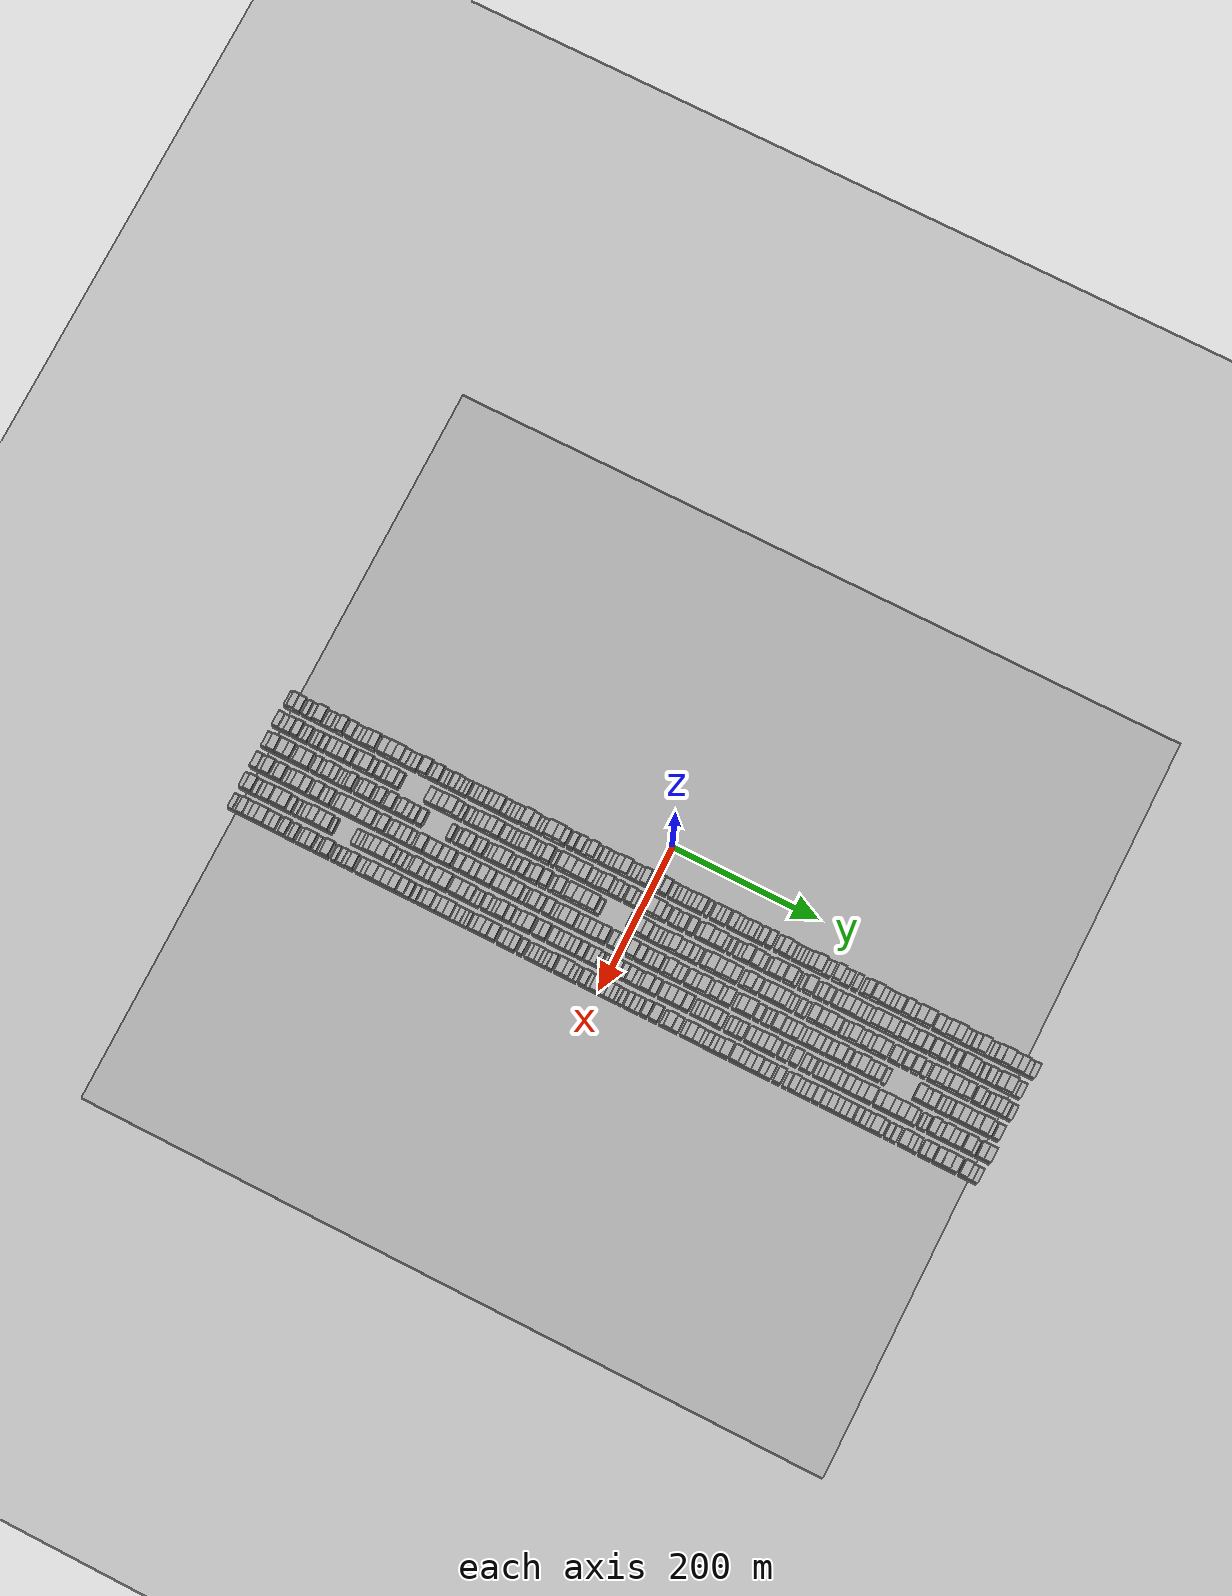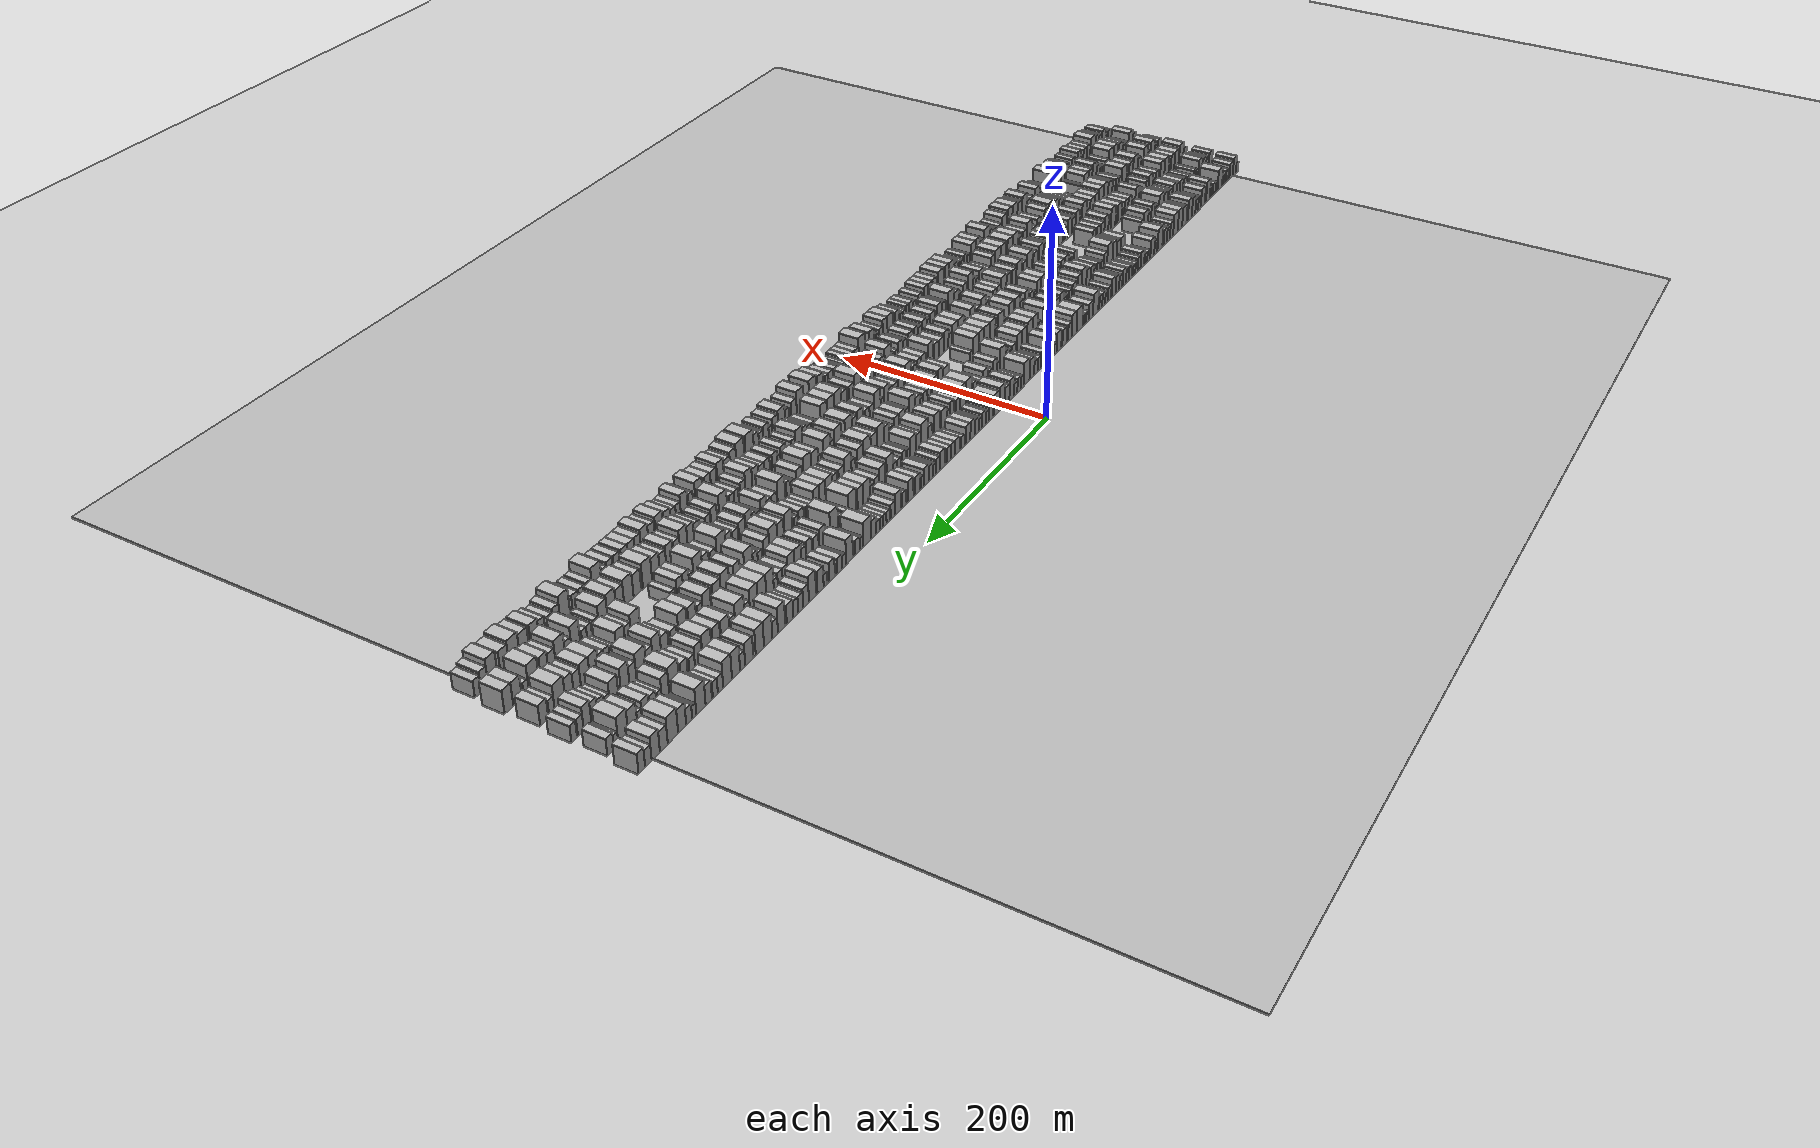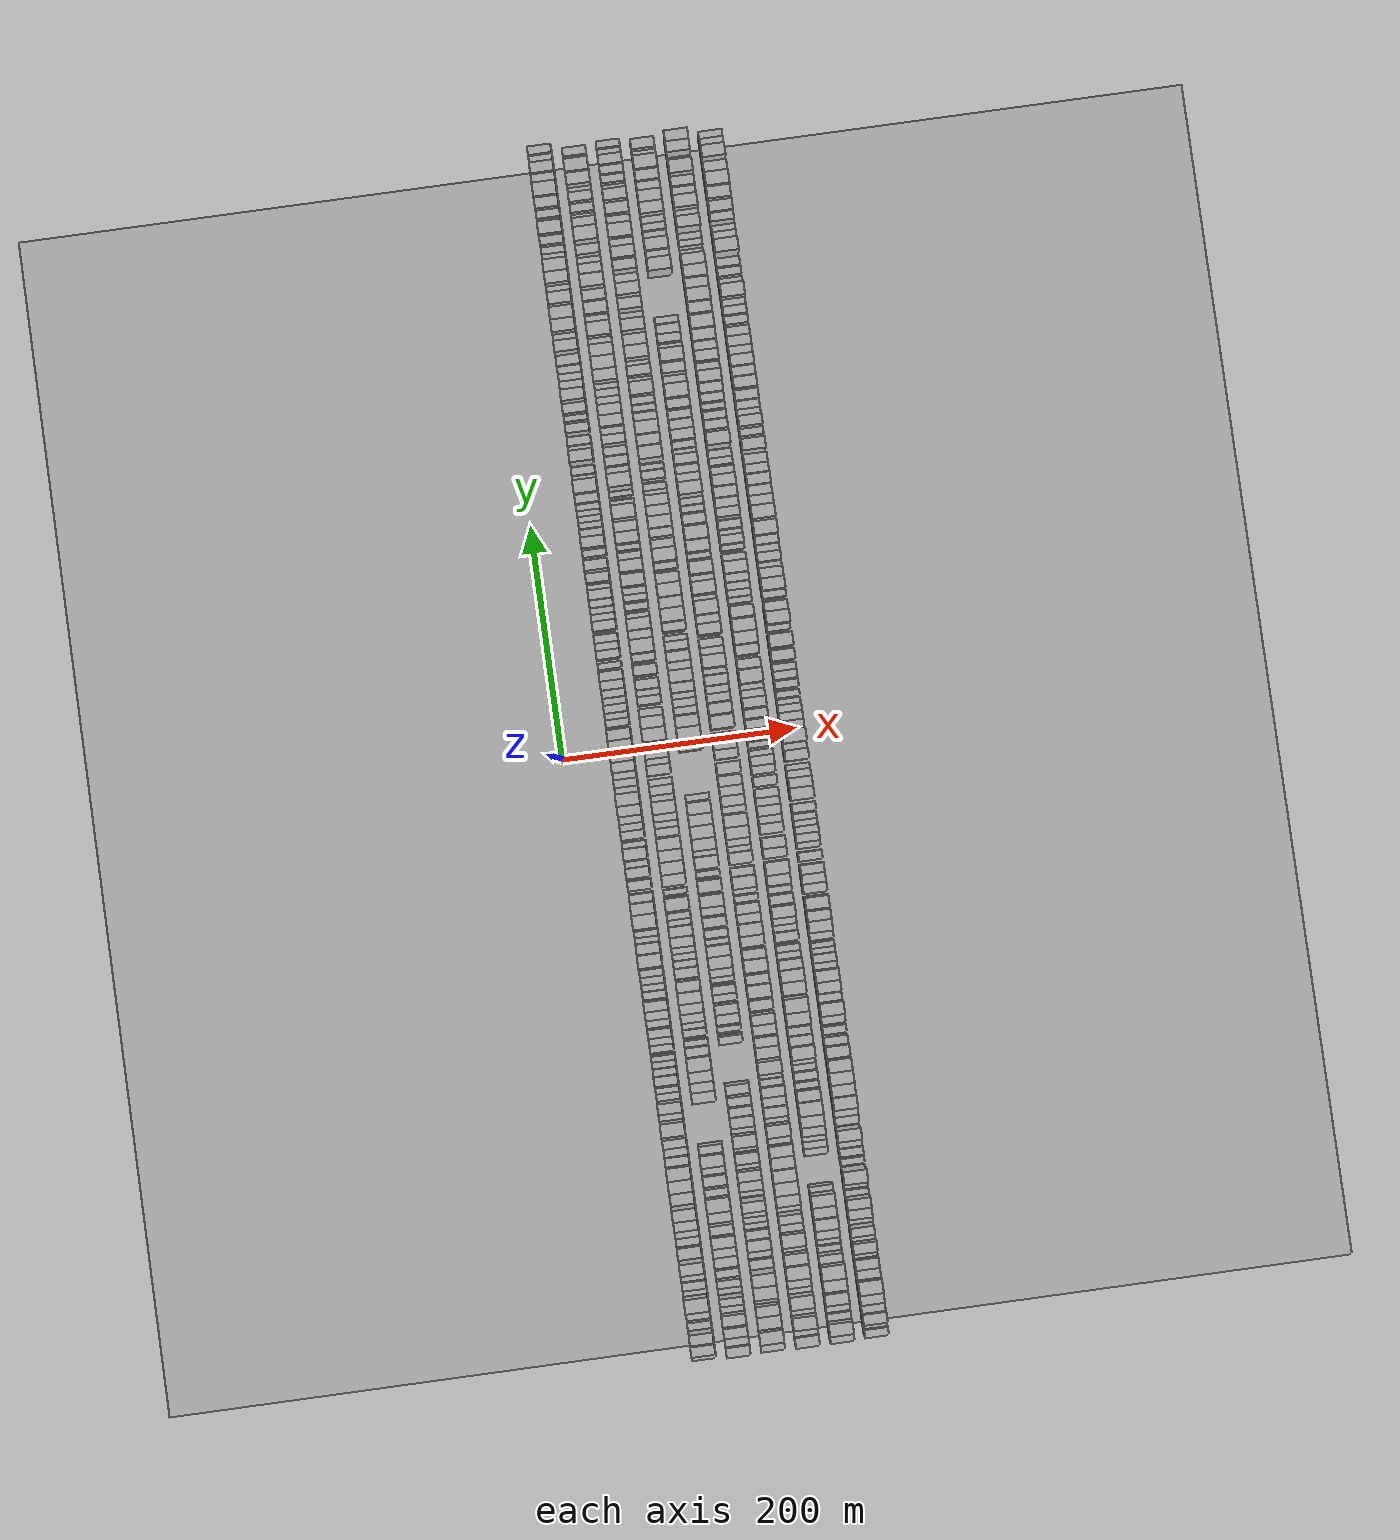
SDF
<?xml version="1.0" encoding="utf-8"?>

<sdf version="1.6">

   <world name="default">

      <gui fullscreen="0">

         <camera name="user_camera">

            <pose>-15 0 4.57585 0 0 0</pose>

            <view_controller>orbit</view_controller>

         </camera>

      </gui>

      <scene>

         <sky>

           <clouds>

             <speed>12</speed>

           </clouds>

         </sky>

         <ambient>0.4 0.4 0.4 1</ambient>

         <background>0.7 0.7 0.7 1</background>

         <shadows>1</shadows>

      </scene>

      <gravity>0 0 -9.8066</gravity>

      <magnetic_field>6e-06 2.3e-05 -4.2e-05</magnetic_field>

      <physics default="0" name="default_physics" type="ode">

         <ode>

            <solver>

               <type>quick</type>

               <iters>10</iters>

               <sor>1.0</sor>

               <use_dynamic_moi_rescaling>0</use_dynamic_moi_rescaling>

            </solver>

            <constraints>

               <cfm>0</cfm>

               <erp>0.2</erp>

               <contact_max_correcting_vel>100</contact_max_correcting_vel>

               <contact_surface_layer>0.001</contact_surface_layer>

            </constraints>

         </ode>

         <max_step_size>0.004</max_step_size>

         <real_time_factor>1</real_time_factor>

         <real_time_update_rate>250</real_time_update_rate>

      </physics>

      <light name="sun" type="directional">

         <cast_shadows>1</cast_shadows>

         <pose>0 0 10 0 0 0</pose>

         <diffuse>0.8 0.8 0.8 1</diffuse>

         <specular>0.2 0.2 0.2 1</specular>

         <attenuation>

            <range>1000</range>

            <constant>0.9</constant>

            <linear>0.01</linear>

            <quadratic>0.001</quadratic>

         </attenuation>

         <direction>-0.5 0.1 -0.9</direction>

      </light>

      <include>

         <name>ground_plane_1</name>

         <uri>model://HANNAS_ground_plane</uri>

         <pose>0 0 0  0 0 0</pose>

      </include>

      <include>

         <name>ground_plane_2</name>

         <uri>model://HANNAS_ground_plane</uri>

         <pose>100 0 0  0 0 0</pose>

      </include>

      <model name="building_1">

         <static>1</static>

         <pose frame="">50.0000 -507.3720 0 0.000000 0.000000 0.000000</pose>

         <link name="link">

            <pose frame="">0 0 6.00 0 0 0</pose>

            <collision name="collision">

               <geometry>

                  <box>

                     <size>20.0000 5.2559 12.0000</size>

                  </box>

               </geometry>

               <max_contacts>10</max_contacts>

               <surface>

                  <contact>

                     <ode/>

                  </contact>

                  <bounce/>

                  <friction>

                     <torsional>

                        <ode/>

                     </torsional>

                     <ode/>

                  </friction>

               </surface>

            </collision>

            <visual name="visual">

               <cast_shadows>0</cast_shadows>

               <geometry>

                  <box>

                     <size>20.0000 5.2559 12.0000</size>

                  </box>

               </geometry>

               <material>

                  <script>

                     <uri>model://HANNAS_wall/materials/scripts</uri>

                     <uri>model://HANNAS_wall/materials/textures</uri>

                     <name>vrc/HANNAS_wall</name>

                  </script>

               </material>

            </visual>

            <self_collide>0</self_collide>

            <enable_wind>0</enable_wind>

            <kinematic>0</kinematic>

         </link>

      </model>

      <model name="building_2">

         <static>1</static>

         <pose frame="">50.0000 -500.4155 0 0.000000 0.000000 0.000000</pose>

         <link name="link">

            <pose frame="">0 0 10.50 0 0 0</pose>

            <collision name="collision">

               <geometry>

                  <box>

                     <size>20.0000 8.6572 21.0000</size>

                  </box>

               </geometry>

               <max_contacts>10</max_contacts>

               <surface>

                  <contact>

                     <ode/>

                  </contact>

                  <bounce/>

                  <friction>

                     <torsional>

                        <ode/>

                     </torsional>

                     <ode/>

                  </friction>

               </surface>

            </collision>

            <visual name="visual">

               <cast_shadows>0</cast_shadows>

               <geometry>

                  <box>

                     <size>20.0000 8.6572 21.0000</size>

                  </box>

               </geometry>

               <material>

                  <script>

                     <uri>model://HANNAS_wall/materials/scripts</uri>

                     <uri>model://HANNAS_wall/materials/textures</uri>

                     <name>vrc/HANNAS_wall</name>

                  </script>

               </material>

            </visual>

            <self_collide>0</self_collide>

            <enable_wind>0</enable_wind>

            <kinematic>0</kinematic>

         </link>

      </model>

      <model name="building_3">

         <static>1</static>

         <pose frame="">50.0000 -491.6169 0 0.000000 0.000000 0.000000</pose>

         <link name="link">

            <pose frame="">0 0 9.00 0 0 0</pose>

            <collision name="collision">

               <geometry>

                  <box>

                     <size>20.0000 8.9400 18.0000</size>

                  </box>

               </geometry>

               <max_contacts>10</max_contacts>

               <surface>

                  <contact>

                     <ode/>

                  </contact>

                  <bounce/>

                  <friction>

                     <torsional>

                        <ode/>

                     </torsional>

                     <ode/>

                  </friction>

               </surface>

            </collision>

            <visual name="visual">

               <cast_shadows>0</cast_shadows>

               <geometry>

                  <box>

                     <size>20.0000 8.9400 18.0000</size>

                  </box>

               </geometry>

               <material>

                  <script>

                     <uri>model://HANNAS_wall/materials/scripts</uri>

                     <uri>model://HANNAS_wall/materials/textures</uri>

                     <name>vrc/HANNAS_wall</name>

                  </script>

               </material>

            </visual>

            <self_collide>0</self_collide>

            <enable_wind>0</enable_wind>

            <kinematic>0</kinematic>

         </link>

      </model>

      <model name="building_4">

         <static>1</static>

         <pose frame="">50.0000 -480.9546 0 0.000000 0.000000 0.000000</pose>

         <link name="link">

            <pose frame="">0 0 7.50 0 0 0</pose>

            <collision name="collision">

               <geometry>

                  <box>

                     <size>20.0000 6.3845 15.0000</size>

                  </box>

               </geometry>

               <max_contacts>10</max_contacts>

               <surface>

                  <contact>

                     <ode/>

                  </contact>

                  <bounce/>

                  <friction>

                     <torsional>

                        <ode/>

                     </torsional>

                     <ode/>

                  </friction>

               </surface>

            </collision>

            <visual name="visual">

               <cast_shadows>0</cast_shadows>

               <geometry>

                  <box>

                     <size>20.0000 6.3845 15.0000</size>

                  </box>

               </geometry>

               <material>

                  <script>

                     <uri>model://HANNAS_wall/materials/scripts</uri>

                     <uri>model://HANNAS_wall/materials/textures</uri>

                     <name>vrc/HANNAS_wall</name>

                  </script>

               </material>

            </visual>

            <self_collide>0</self_collide>

            <enable_wind>0</enable_wind>

            <kinematic>0</kinematic>

         </link>

      </model>

      <model name="building_5">

         <static>1</static>

         <pose frame="">50.0000 -473.9846 0 0.000000 0.000000 0.000000</pose>

         <link name="link">

            <pose frame="">0 0 6.00 0 0 0</pose>

            <collision name="collision">

               <geometry>

                  <box>

                     <size>20.0000 5.5555 12.0000</size>

                  </box>

               </geometry>

               <max_contacts>10</max_contacts>

               <surface>

                  <contact>

                     <ode/>

                  </contact>

                  <bounce/>

                  <friction>

                     <torsional>

                        <ode/>

                     </torsional>

                     <ode/>

                  </friction>

               </surface>

            </collision>

            <visual name="visual">

               <cast_shadows>0</cast_shadows>

               <geometry>

                  <box>

                     <size>20.0000 5.5555 12.0000</size>

                  </box>

               </geometry>

               <material>

                  <script>

                     <uri>model://HANNAS_wall/materials/scripts</uri>

                     <uri>model://HANNAS_wall/materials/textures</uri>

                     <name>vrc/HANNAS_wall</name>

                  </script>

               </material>

            </visual>

            <self_collide>0</self_collide>

            <enable_wind>0</enable_wind>

            <kinematic>0</kinematic>

         </link>

      </model>

      <model name="building_6">

         <static>1</static>

         <pose frame="">50.0000 -462.2609 0 0.000000 0.000000 0.000000</pose>

         <link name="link">

            <pose frame="">0 0 12.00 0 0 0</pose>

            <collision name="collision">

               <geometry>

                  <box>

                     <size>20.0000 11.8918 24.0000</size>

                  </box>

               </geometry>

               <max_contacts>10</max_contacts>

               <surface>

                  <contact>

                     <ode/>

                  </contact>

                  <bounce/>

                  <friction>

                     <torsional>

                        <ode/>

                     </torsional>

                     <ode/>

                  </friction>

               </surface>

            </collision>

            <visual name="visual">

               <cast_shadows>0</cast_shadows>

               <geometry>

                  <box>

                     <size>20.0000 11.8918 24.0000</size>

                  </box>

               </geometry>

               <material>

                  <script>

                     <uri>model://HANNAS_wall/materials/scripts</uri>

                     <uri>model://HANNAS_wall/materials/textures</uri>

                     <name>vrc/HANNAS_wall</name>

                  </script>

               </material>

            </visual>

            <self_collide>0</self_collide>

            <enable_wind>0</enable_wind>

            <kinematic>0</kinematic>

         </link>

      </model>

      <model name="building_7">

         <static>1</static>

         <pose frame="">50.0000 -453.8444 0 0.000000 0.000000 0.000000</pose>

         <link name="link">

            <pose frame="">0 0 6.00 0 0 0</pose>

            <collision name="collision">

               <geometry>

                  <box>

                     <size>20.0000 4.9412 12.0000</size>

                  </box>

               </geometry>

               <max_contacts>10</max_contacts>

               <surface>

                  <contact>

                     <ode/>

                  </contact>

                  <bounce/>

                  <friction>

                     <torsional>

                        <ode/>

                     </torsional>

                     <ode/>

                  </friction>

               </surface>

            </collision>

            <visual name="visual">

               <cast_shadows>0</cast_shadows>

               <geometry>

                  <box>

                     <size>20.0000 4.9412 12.0000</size>

                  </box>

               </geometry>

               <material>

                  <script>

                     <uri>model://HANNAS_wall/materials/scripts</uri>

                     <uri>model://HANNAS_wall/materials/textures</uri>

                     <name>vrc/HANNAS_wall</name>

                  </script>

               </material>

            </visual>

            <self_collide>0</self_collide>

            <enable_wind>0</enable_wind>

            <kinematic>0</kinematic>

         </link>

      </model>

      <model name="building_8">

         <static>1</static>

         <pose frame="">50.0000 -447.8587 0 0.000000 0.000000 0.000000</pose>

         <link name="link">

            <pose frame="">0 0 7.50 0 0 0</pose>

            <collision name="collision">

               <geometry>

                  <box>

                     <size>20.0000 7.0300 15.0000</size>

                  </box>

               </geometry>

               <max_contacts>10</max_contacts>

               <surface>

                  <contact>

                     <ode/>

                  </contact>

                  <bounce/>

                  <friction>

                     <torsional>

                        <ode/>

                     </torsional>

                     <ode/>

                  </friction>

               </surface>

            </collision>

            <visual name="visual">

               <cast_shadows>0</cast_shadows>

               <geometry>

                  <box>

                     <size>20.0000 7.0300 15.0000</size>

                  </box>

               </geometry>

               <material>

                  <script>

                     <uri>model://HANNAS_wall/materials/scripts</uri>

                     <uri>model://HANNAS_wall/materials/textures</uri>

                     <name>vrc/HANNAS_wall</name>

                  </script>

               </material>

            </visual>

            <self_collide>0</self_collide>

            <enable_wind>0</enable_wind>

            <kinematic>0</kinematic>

         </link>

      </model>

      <model name="building_9">

         <static>1</static>

         <pose frame="">50.0000 -441.6673 0 0.000000 0.000000 0.000000</pose>

         <link name="link">

            <pose frame="">0 0 6.00 0 0 0</pose>

            <collision name="collision">

               <geometry>

                  <box>

                     <size>20.0000 5.3528 12.0000</size>

                  </box>

               </geometry>

               <max_contacts>10</max_contacts>

               <surface>

                  <contact>

                     <ode/>

                  </contact>

                  <bounce/>

                  <friction>

                     <torsional>

                        <ode/>

                     </torsional>

                     <ode/>

                  </friction>

               </surface>

            </collision>

            <visual name="visual">

               <cast_shadows>0</cast_shadows>

               <geometry>

                  <box>

                     <size>20.0000 5.3528 12.0000</size>

                  </box>

               </geometry>

               <material>

                  <script>

                     <uri>model://HANNAS_wall/materials/scripts</uri>

                     <uri>model://HANNAS_wall/materials/textures</uri>

                     <name>vrc/HANNAS_wall</name>

                  </script>

               </material>

            </visual>

            <self_collide>0</self_collide>

            <enable_wind>0</enable_wind>

            <kinematic>0</kinematic>

         </link>

      </model>

      <model name="building_10">

         <static>1</static>

         <pose frame="">50.0000 -432.1386 0 0.000000 0.000000 0.000000</pose>

         <link name="link">

            <pose frame="">0 0 12.00 0 0 0</pose>

            <collision name="collision">

               <geometry>

                  <box>

                     <size>20.0000 9.7046 24.0000</size>

                  </box>

               </geometry>

               <max_contacts>10</max_contacts>

               <surface>

                  <contact>

                     <ode/>

                  </contact>

                  <bounce/>

                  <friction>

                     <torsional>

                        <ode/>

                     </torsional>

                     <ode/>

                  </friction>

               </surface>

            </collision>

            <visual name="visual">

               <cast_shadows>0</cast_shadows>

               <geometry>

                  <box>

                     <size>20.0000 9.7046 24.0000</size>

                  </box>

               </geometry>

               <material>

                  <script>

                     <uri>model://HANNAS_wall/materials/scripts</uri>

                     <uri>model://HANNAS_wall/materials/textures</uri>

                     <name>vrc/HANNAS_wall</name>

                  </script>

               </material>

            </visual>

            <self_collide>0</self_collide>

            <enable_wind>0</enable_wind>

            <kinematic>0</kinematic>

         </link>

      </model>

      <model name="building_11">

         <static>1</static>

         <pose frame="">50.0000 -419.3477 0 0.000000 0.000000 0.000000</pose>

         <link name="link">

            <pose frame="">0 0 10.50 0 0 0</pose>

            <collision name="collision">

               <geometry>

                  <box>

                     <size>20.0000 9.8773 21.0000</size>

                  </box>

               </geometry>

               <max_contacts>10</max_contacts>

               <surface>

                  <contact>

                     <ode/>

                  </contact>

                  <bounce/>

                  <friction>

                     <torsional>

                        <ode/>

                     </torsional>

                     <ode/>

                  </friction>

               </surface>

            </collision>

            <visual name="visual">

               <cast_shadows>0</cast_shadows>

               <geometry>

                  <box>

                     <size>20.0000 9.8773 21.0000</size>

                  </box>

               </geometry>

               <material>

                  <script>

                     <uri>model://HANNAS_wall/materials/scripts</uri>

                     <uri>model://HANNAS_wall/materials/textures</uri>

                     <name>vrc/HANNAS_wall</name>

                  </script>

               </material>

            </visual>

            <self_collide>0</self_collide>

            <enable_wind>0</enable_wind>

            <kinematic>0</kinematic>

         </link>

      </model>

      <model name="building_12">

         <static>1</static>

         <pose frame="">50.0000 -411.0119 0 0.000000 0.000000 0.000000</pose>

         <link name="link">

            <pose frame="">0 0 7.50 0 0 0</pose>

            <collision name="collision">

               <geometry>

                  <box>

                     <size>20.0000 6.7943 15.0000</size>

                  </box>

               </geometry>

               <max_contacts>10</max_contacts>

               <surface>

                  <contact>

                     <ode/>

                  </contact>

                  <bounce/>

                  <friction>

                     <torsional>

                        <ode/>

                     </torsional>

                     <ode/>

                  </friction>

               </surface>

            </collision>

            <visual name="visual">

               <cast_shadows>0</cast_shadows>

               <geometry>

                  <box>

                     <size>20.0000 6.7943 15.0000</size>

                  </box>

               </geometry>

               <material>

                  <script>

                     <uri>model://HANNAS_wall/materials/scripts</uri>

                     <uri>model://HANNAS_wall/materials/textures</uri>

                     <name>vrc/HANNAS_wall</name>

                  </script>

               </material>

            </visual>

            <self_collide>0</self_collide>

            <enable_wind>0</enable_wind>

            <kinematic>0</kinematic>

         </link>

      </model>

      <model name="building_13">

         <static>1</static>

         <pose frame="">50.0000 -404.2988 0 0.000000 0.000000 0.000000</pose>

         <link name="link">

            <pose frame="">0 0 7.50 0 0 0</pose>

            <collision name="collision">

               <geometry>

                  <box>

                     <size>20.0000 6.6318 15.0000</size>

                  </box>

               </geometry>

               <max_contacts>10</max_contacts>

               <surface>

                  <contact>

                     <ode/>

                  </contact>

                  <bounce/>

                  <friction>

                     <torsional>

                        <ode/>

                     </torsional>

                     <ode/>

                  </friction>

               </surface>

            </collision>

            <visual name="visual">

               <cast_shadows>0</cast_shadows>

               <geometry>

                  <box>

                     <size>20.0000 6.6318 15.0000</size>

                  </box>

               </geometry>

               <material>

                  <script>

                     <uri>model://HANNAS_wall/materials/scripts</uri>

                     <uri>model://HANNAS_wall/materials/textures</uri>

                     <name>vrc/HANNAS_wall</name>

                  </script>

               </material>

            </visual>

            <self_collide>0</self_collide>

            <enable_wind>0</enable_wind>

            <kinematic>0</kinematic>

         </link>

      </model>

      <model name="building_14">

         <static>1</static>

         <pose frame="">50.0000 -396.6401 0 0.000000 0.000000 0.000000</pose>

         <link name="link">

            <pose frame="">0 0 10.50 0 0 0</pose>

            <collision name="collision">

               <geometry>

                  <box>

                     <size>20.0000 8.6857 21.0000</size>

                  </box>

               </geometry>

               <max_contacts>10</max_contacts>

               <surface>

                  <contact>

                     <ode/>

                  </contact>

                  <bounce/>

                  <friction>

                     <torsional>

                        <ode/>

                     </torsional>

                     <ode/>

                  </friction>

               </surface>

            </collision>

            <visual name="visual">

               <cast_shadows>0</cast_shadows>

               <geometry>

                  <box>

                     <size>20.0000 8.6857 21.0000</size>

                  </box>

               </geometry>

               <material>

                  <script>

                     <uri>model://HANNAS_wall/materials/scripts</uri>

                     <uri>model://HANNAS_wall/materials/textures</uri>

                     <name>vrc/HANNAS_wall</name>

                  </script>

               </material>

            </visual>

            <self_collide>0</self_collide>

            <enable_wind>0</enable_wind>

            <kinematic>0</kinematic>

         </link>

      </model>

      <model name="building_15">

         <static>1</static>

         <pose frame="">50.0000 -387.3243 0 0.000000 0.000000 0.000000</pose>

         <link name="link">

            <pose frame="">0 0 12.00 0 0 0</pose>

            <collision name="collision">

               <geometry>

                  <box>

                     <size>20.0000 9.9458 24.0000</size>

                  </box>

               </geometry>

               <max_contacts>10</max_contacts>

               <surface>

                  <contact>

                     <ode/>

                  </contact>

                  <bounce/>

                  <friction>

                     <torsional>

                        <ode/>

                     </torsional>

                     <ode/>

                  </friction>

               </surface>

            </collision>

            <visual name="visual">

               <cast_shadows>0</cast_shadows>

               <geometry>

                  <box>

                     <size>20.0000 9.9458 24.0000</size>

                  </box>

               </geometry>

               <material>

                  <script>

                     <uri>model://HANNAS_wall/materials/scripts</uri>

                     <uri>model://HANNAS_wall/materials/textures</uri>

                     <name>vrc/HANNAS_wall</name>

                  </script>

               </material>

            </visual>

            <self_collide>0</self_collide>

            <enable_wind>0</enable_wind>

            <kinematic>0</kinematic>

         </link>

      </model>

      <model name="building_16">

         <static>1</static>

         <pose frame="">50.0000 -374.1088 0 0.000000 0.000000 0.000000</pose>

         <link name="link">

            <pose frame="">0 0 10.50 0 0 0</pose>

            <collision name="collision">

               <geometry>

                  <box>

                     <size>20.0000 10.4852 21.0000</size>

                  </box>

               </geometry>

               <max_contacts>10</max_contacts>

               <surface>

                  <contact>

                     <ode/>

                  </contact>

                  <bounce/>

                  <friction>

                     <torsional>

                        <ode/>

                     </torsional>

                     <ode/>

                  </friction>

               </surface>

            </collision>

            <visual name="visual">

               <cast_shadows>0</cast_shadows>

               <geometry>

                  <box>

                     <size>20.0000 10.4852 21.0000</size>

                  </box>

               </geometry>

               <material>

                  <script>

                     <uri>model://HANNAS_wall/materials/scripts</uri>

                     <uri>model://HANNAS_wall/materials/textures</uri>

                     <name>vrc/HANNAS_wall</name>

                  </script>

               </material>

            </visual>

            <self_collide>0</self_collide>

            <enable_wind>0</enable_wind>

            <kinematic>0</kinematic>

         </link>

      </model>

      <model name="building_17">

         <static>1</static>

         <pose frame="">50.0000 -363.6020 0 0.000000 0.000000 0.000000</pose>

         <link name="link">

            <pose frame="">0 0 12.00 0 0 0</pose>

            <collision name="collision">

               <geometry>

                  <box>

                     <size>20.0000 10.5284 24.0000</size>

                  </box>

               </geometry>

               <max_contacts>10</max_contacts>

               <surface>

                  <contact>

                     <ode/>

                  </contact>

                  <bounce/>

                  <friction>

                     <torsional>

                        <ode/>

                     </torsional>

                     <ode/>

                  </friction>

               </surface>

            </collision>

            <visual name="visual">

               <cast_shadows>0</cast_shadows>

               <geometry>

                  <box>

                     <size>20.0000 10.5284 24.0000</size>

                  </box>

               </geometry>

               <material>

                  <script>

                     <uri>model://HANNAS_wall/materials/scripts</uri>

                     <uri>model://HANNAS_wall/materials/textures</uri>

                     <name>vrc/HANNAS_wall</name>

                  </script>

               </material>

            </visual>

            <self_collide>0</self_collide>

            <enable_wind>0</enable_wind>

            <kinematic>0</kinematic>

         </link>

      </model>

      <model name="building_18">

         <static>1</static>

         <pose frame="">50.0000 -352.8540 0 0.000000 0.000000 0.000000</pose>

         <link name="link">

            <pose frame="">0 0 12.00 0 0 0</pose>

            <collision name="collision">

               <geometry>

                  <box>

                     <size>20.0000 10.9676 24.0000</size>

                  </box>

               </geometry>

               <max_contacts>10</max_contacts>

               <surface>

                  <contact>

                     <ode/>

                  </contact>

                  <bounce/>

                  <friction>

                     <torsional>

                        <ode/>

                     </torsional>

                     <ode/>

                  </friction>

               </surface>

            </collision>

            <visual name="visual">

               <cast_shadows>0</cast_shadows>

               <geometry>

                  <box>

                     <size>20.0000 10.9676 24.0000</size>

                  </box>

               </geometry>

               <material>

                  <script>

                     <uri>model://HANNAS_wall/materials/scripts</uri>

                     <uri>model://HANNAS_wall/materials/textures</uri>

                     <name>vrc/HANNAS_wall</name>

                  </script>

               </material>

            </visual>

            <self_collide>0</self_collide>

            <enable_wind>0</enable_wind>

            <kinematic>0</kinematic>

         </link>

      </model>

      <model name="building_19">

         <static>1</static>

         <pose frame="">50.0000 -343.5265 0 0.000000 0.000000 0.000000</pose>

         <link name="link">

            <pose frame="">0 0 9.00 0 0 0</pose>

            <collision name="collision">

               <geometry>

                  <box>

                     <size>20.0000 7.6874 18.0000</size>

                  </box>

               </geometry>

               <max_contacts>10</max_contacts>

               <surface>

                  <contact>

                     <ode/>

                  </contact>

                  <bounce/>

                  <friction>

                     <torsional>

                        <ode/>

                     </torsional>

                     <ode/>

                  </friction>

               </surface>

            </collision>

            <visual name="visual">

               <cast_shadows>0</cast_shadows>

               <geometry>

                  <box>

                     <size>20.0000 7.6874 18.0000</size>

                  </box>

               </geometry>

               <material>

                  <script>

                     <uri>model://HANNAS_wall/materials/scripts</uri>

                     <uri>model://HANNAS_wall/materials/textures</uri>

                     <name>vrc/HANNAS_wall</name>

                  </script>

               </material>

            </visual>

            <self_collide>0</self_collide>

            <enable_wind>0</enable_wind>

            <kinematic>0</kinematic>

         </link>

      </model>

      <model name="building_20">

         <static>1</static>

         <pose frame="">50.0000 -336.0874 0 0.000000 0.000000 0.000000</pose>

         <link name="link">

            <pose frame="">0 0 7.50 0 0 0</pose>

            <collision name="collision">

               <geometry>

                  <box>

                     <size>20.0000 7.1907 15.0000</size>

                  </box>

               </geometry>

               <max_contacts>10</max_contacts>

               <surface>

                  <contact>

                     <ode/>

                  </contact>

                  <bounce/>

                  <friction>

                     <torsional>

                        <ode/>

                     </torsional>

                     <ode/>

                  </friction>

               </surface>

            </collision>

            <visual name="visual">

               <cast_shadows>0</cast_shadows>

               <geometry>

                  <box>

                     <size>20.0000 7.1907 15.0000</size>

                  </box>

               </geometry>

               <material>

                  <script>

                     <uri>model://HANNAS_wall/materials/scripts</uri>

                     <uri>model://HANNAS_wall/materials/textures</uri>

                     <name>vrc/HANNAS_wall</name>

                  </script>

               </material>

            </visual>

            <self_collide>0</self_collide>

            <enable_wind>0</enable_wind>

            <kinematic>0</kinematic>

         </link>

      </model>

      <model name="building_21">

         <static>1</static>

         <pose frame="">50.0000 -328.7805 0 0.000000 0.000000 0.000000</pose>

         <link name="link">

            <pose frame="">0 0 9.00 0 0 0</pose>

            <collision name="collision">

               <geometry>

                  <box>

                     <size>20.0000 7.4230 18.0000</size>

                  </box>

               </geometry>

               <max_contacts>10</max_contacts>

               <surface>

                  <contact>

                     <ode/>

                  </contact>

                  <bounce/>

                  <friction>

                     <torsional>

                        <ode/>

                     </torsional>

                     <ode/>

                  </friction>

               </surface>

            </collision>

            <visual name="visual">

               <cast_shadows>0</cast_shadows>

               <geometry>

                  <box>

                     <size>20.0000 7.4230 18.0000</size>

                  </box>

               </geometry>

               <material>

                  <script>

                     <uri>model://HANNAS_wall/materials/scripts</uri>

                     <uri>model://HANNAS_wall/materials/textures</uri>

                     <name>vrc/HANNAS_wall</name>

                  </script>

               </material>

            </visual>

            <self_collide>0</self_collide>

            <enable_wind>0</enable_wind>

            <kinematic>0</kinematic>

         </link>

      </model>

      <model name="building_22">

         <static>1</static>

         <pose frame="">50.0000 -316.2977 0 0.000000 0.000000 0.000000</pose>

         <link name="link">

            <pose frame="">0 0 12.00 0 0 0</pose>

            <collision name="collision">

               <geometry>

                  <box>

                     <size>20.0000 11.5427 24.0000</size>

                  </box>

               </geometry>

               <max_contacts>10</max_contacts>

               <surface>

                  <contact>

                     <ode/>

                  </contact>

                  <bounce/>

                  <friction>

                     <torsional>

                        <ode/>

                     </torsional>

                     <ode/>

                  </friction>

               </surface>

            </collision>

            <visual name="visual">

               <cast_shadows>0</cast_shadows>

               <geometry>

                  <box>

                     <size>20.0000 11.5427 24.0000</size>

                  </box>

               </geometry>

               <material>

                  <script>

                     <uri>model://HANNAS_wall/materials/scripts</uri>

                     <uri>model://HANNAS_wall/materials/textures</uri>

                     <name>vrc/HANNAS_wall</name>

                  </script>

               </material>

            </visual>

            <self_collide>0</self_collide>

            <enable_wind>0</enable_wind>

            <kinematic>0</kinematic>

         </link>

      </model>

      <model name="building_23">

         <static>1</static>

         <pose frame="">50.0000 -306.4154 0 0.000000 0.000000 0.000000</pose>

         <link name="link">

            <pose frame="">0 0 7.50 0 0 0</pose>

            <collision name="collision">

               <geometry>

                  <box>

                     <size>20.0000 6.2219 15.0000</size>

                  </box>

               </geometry>

               <max_contacts>10</max_contacts>

               <surface>

                  <contact>

                     <ode/>

                  </contact>

                  <bounce/>

                  <friction>

                     <torsional>

                        <ode/>

                     </torsional>

                     <ode/>

                  </friction>

               </surface>

            </collision>

            <visual name="visual">

               <cast_shadows>0</cast_shadows>

               <geometry>

                  <box>

                     <size>20.0000 6.2219 15.0000</size>

                  </box>

               </geometry>

               <material>

                  <script>

                     <uri>model://HANNAS_wall/materials/scripts</uri>

                     <uri>model://HANNAS_wall/materials/textures</uri>

                     <name>vrc/HANNAS_wall</name>

                  </script>

               </material>

            </visual>

            <self_collide>0</self_collide>

            <enable_wind>0</enable_wind>

            <kinematic>0</kinematic>

         </link>

      </model>

      <model name="building_24">

         <static>1</static>

         <pose frame="">50.0000 -298.7586 0 0.000000 0.000000 0.000000</pose>

         <link name="link">

            <pose frame="">0 0 10.50 0 0 0</pose>

            <collision name="collision">

               <geometry>

                  <box>

                     <size>20.0000 9.0917 21.0000</size>

                  </box>

               </geometry>

               <max_contacts>10</max_contacts>

               <surface>

                  <contact>

                     <ode/>

                  </contact>

                  <bounce/>

                  <friction>

                     <torsional>

                        <ode/>

                     </torsional>

                     <ode/>

                  </friction>

               </surface>

            </collision>

            <visual name="visual">

               <cast_shadows>0</cast_shadows>

               <geometry>

                  <box>

                     <size>20.0000 9.0917 21.0000</size>

                  </box>

               </geometry>

               <material>

                  <script>

                     <uri>model://HANNAS_wall/materials/scripts</uri>

                     <uri>model://HANNAS_wall/materials/textures</uri>

                     <name>vrc/HANNAS_wall</name>

                  </script>

               </material>

            </visual>

            <self_collide>0</self_collide>

            <enable_wind>0</enable_wind>

            <kinematic>0</kinematic>

         </link>

      </model>

      <model name="building_25">

         <static>1</static>

         <pose frame="">50.0000 -290.2363 0 0.000000 0.000000 0.000000</pose>

         <link name="link">

            <pose frame="">0 0 6.00 0 0 0</pose>

            <collision name="collision">

               <geometry>

                  <box>

                     <size>20.0000 5.9530 12.0000</size>

                  </box>

               </geometry>

               <max_contacts>10</max_contacts>

               <surface>

                  <contact>

                     <ode/>

                  </contact>

                  <bounce/>

                  <friction>

                     <torsional>

                        <ode/>

                     </torsional>

                     <ode/>

                  </friction>

               </surface>

            </collision>

            <visual name="visual">

               <cast_shadows>0</cast_shadows>

               <geometry>

                  <box>

                     <size>20.0000 5.9530 12.0000</size>

                  </box>

               </geometry>

               <material>

                  <script>

                     <uri>model://HANNAS_wall/materials/scripts</uri>

                     <uri>model://HANNAS_wall/materials/textures</uri>

                     <name>vrc/HANNAS_wall</name>

                  </script>

               </material>

            </visual>

            <self_collide>0</self_collide>

            <enable_wind>0</enable_wind>

            <kinematic>0</kinematic>

         </link>

      </model>

      <model name="building_26">

         <static>1</static>

         <pose frame="">50.0000 -284.7391 0 0.000000 0.000000 0.000000</pose>

         <link name="link">

            <pose frame="">0 0 6.00 0 0 0</pose>

            <collision name="collision">

               <geometry>

                  <box>

                     <size>20.0000 5.0415 12.0000</size>

                  </box>

               </geometry>

               <max_contacts>10</max_contacts>

               <surface>

                  <contact>

                     <ode/>

                  </contact>

                  <bounce/>

                  <friction>

                     <torsional>

                        <ode/>

                     </torsional>

                     <ode/>

                  </friction>

               </surface>

            </collision>

            <visual name="visual">

               <cast_shadows>0</cast_shadows>

               <geometry>

                  <box>

                     <size>20.0000 5.0415 12.0000</size>

                  </box>

               </geometry>

               <material>

                  <script>

                     <uri>model://HANNAS_wall/materials/scripts</uri>

                     <uri>model://HANNAS_wall/materials/textures</uri>

                     <name>vrc/HANNAS_wall</name>

                  </script>

               </material>

            </visual>

            <self_collide>0</self_collide>

            <enable_wind>0</enable_wind>

            <kinematic>0</kinematic>

         </link>

      </model>

      <model name="building_27">

         <static>1</static>

         <pose frame="">50.0000 -276.1735 0 0.000000 0.000000 0.000000</pose>

         <link name="link">

            <pose frame="">0 0 9.00 0 0 0</pose>

            <collision name="collision">

               <geometry>

                  <box>

                     <size>20.0000 8.0896 18.0000</size>

                  </box>

               </geometry>

               <max_contacts>10</max_contacts>

               <surface>

                  <contact>

                     <ode/>

                  </contact>

                  <bounce/>

                  <friction>

                     <torsional>

                        <ode/>

                     </torsional>

                     <ode/>

                  </friction>

               </surface>

            </collision>

            <visual name="visual">

               <cast_shadows>0</cast_shadows>

               <geometry>

                  <box>

                     <size>20.0000 8.0896 18.0000</size>

                  </box>

               </geometry>

               <material>

                  <script>

                     <uri>model://HANNAS_wall/materials/scripts</uri>

                     <uri>model://HANNAS_wall/materials/textures</uri>

                     <name>vrc/HANNAS_wall</name>

                  </script>

               </material>

            </visual>

            <self_collide>0</self_collide>

            <enable_wind>0</enable_wind>

            <kinematic>0</kinematic>

         </link>

      </model>

      <model name="building_28">

         <static>1</static>

         <pose frame="">50.0000 -269.0401 0 0.000000 0.000000 0.000000</pose>

         <link name="link">

            <pose frame="">0 0 7.50 0 0 0</pose>

            <collision name="collision">

               <geometry>

                  <box>

                     <size>20.0000 6.1773 15.0000</size>

                  </box>

               </geometry>

               <max_contacts>10</max_contacts>

               <surface>

                  <contact>

                     <ode/>

                  </contact>

                  <bounce/>

                  <friction>

                     <torsional>

                        <ode/>

                     </torsional>

                     <ode/>

                  </friction>

               </surface>

            </collision>

            <visual name="visual">

               <cast_shadows>0</cast_shadows>

               <geometry>

                  <box>

                     <size>20.0000 6.1773 15.0000</size>

                  </box>

               </geometry>

               <material>

                  <script>

                     <uri>model://HANNAS_wall/materials/scripts</uri>

                     <uri>model://HANNAS_wall/materials/textures</uri>

                     <name>vrc/HANNAS_wall</name>

                  </script>

               </material>

            </visual>

            <self_collide>0</self_collide>

            <enable_wind>0</enable_wind>

            <kinematic>0</kinematic>

         </link>

      </model>

      <model name="building_29">

         <static>1</static>

         <pose frame="">50.0000 -263.2228 0 0.000000 0.000000 0.000000</pose>

         <link name="link">

            <pose frame="">0 0 6.00 0 0 0</pose>

            <collision name="collision">

               <geometry>

                  <box>

                     <size>20.0000 5.4572 12.0000</size>

                  </box>

               </geometry>

               <max_contacts>10</max_contacts>

               <surface>

                  <contact>

                     <ode/>

                  </contact>

                  <bounce/>

                  <friction>

                     <torsional>

                        <ode/>

                     </torsional>

                     <ode/>

                  </friction>

               </surface>

            </collision>

            <visual name="visual">

               <cast_shadows>0</cast_shadows>

               <geometry>

                  <box>

                     <size>20.0000 5.4572 12.0000</size>

                  </box>

               </geometry>

               <material>

                  <script>

                     <uri>model://HANNAS_wall/materials/scripts</uri>

                     <uri>model://HANNAS_wall/materials/textures</uri>

                     <name>vrc/HANNAS_wall</name>

                  </script>

               </material>

            </visual>

            <self_collide>0</self_collide>

            <enable_wind>0</enable_wind>

            <kinematic>0</kinematic>

         </link>

      </model>

      <model name="building_30">

         <static>1</static>

         <pose frame="">50.0000 -258.0266 0 0.000000 0.000000 0.000000</pose>

         <link name="link">

            <pose frame="">0 0 6.00 0 0 0</pose>

            <collision name="collision">

               <geometry>

                  <box>

                     <size>20.0000 4.9352 12.0000</size>

                  </box>

               </geometry>

               <max_contacts>10</max_contacts>

               <surface>

                  <contact>

                     <ode/>

                  </contact>

                  <bounce/>

                  <friction>

                     <torsional>

                        <ode/>

                     </torsional>

                     <ode/>

                  </friction>

               </surface>

            </collision>

            <visual name="visual">

               <cast_shadows>0</cast_shadows>

               <geometry>

                  <box>

                     <size>20.0000 4.9352 12.0000</size>

                  </box>

               </geometry>

               <material>

                  <script>

                     <uri>model://HANNAS_wall/materials/scripts</uri>

                     <uri>model://HANNAS_wall/materials/textures</uri>

                     <name>vrc/HANNAS_wall</name>

                  </script>

               </material>

            </visual>

            <self_collide>0</self_collide>

            <enable_wind>0</enable_wind>

            <kinematic>0</kinematic>

         </link>

      </model>

      <model name="building_31">

         <static>1</static>

         <pose frame="">50.0000 -249.4952 0 0.000000 0.000000 0.000000</pose>

         <link name="link">

            <pose frame="">0 0 7.50 0 0 0</pose>

            <collision name="collision">

               <geometry>

                  <box>

                     <size>20.0000 6.1274 15.0000</size>

                  </box>

               </geometry>

               <max_contacts>10</max_contacts>

               <surface>

                  <contact>

                     <ode/>

                  </contact>

                  <bounce/>

                  <friction>

                     <torsional>

                        <ode/>

                     </torsional>

                     <ode/>

                  </friction>

               </surface>

            </collision>

            <visual name="visual">

               <cast_shadows>0</cast_shadows>

               <geometry>

                  <box>

                     <size>20.0000 6.1274 15.0000</size>

                  </box>

               </geometry>

               <material>

                  <script>

                     <uri>model://HANNAS_wall/materials/scripts</uri>

                     <uri>model://HANNAS_wall/materials/textures</uri>

                     <name>vrc/HANNAS_wall</name>

                  </script>

               </material>

            </visual>

            <self_collide>0</self_collide>

            <enable_wind>0</enable_wind>

            <kinematic>0</kinematic>

         </link>

      </model>

      <model name="building_32">

         <static>1</static>

         <pose frame="">50.0000 -243.2692 0 0.000000 0.000000 0.000000</pose>

         <link name="link">

            <pose frame="">0 0 7.50 0 0 0</pose>

            <collision name="collision">

               <geometry>

                  <box>

                     <size>20.0000 6.3247 15.0000</size>

                  </box>

               </geometry>

               <max_contacts>10</max_contacts>

               <surface>

                  <contact>

                     <ode/>

                  </contact>

                  <bounce/>

                  <friction>

                     <torsional>

                        <ode/>

                     </torsional>

                     <ode/>

                  </friction>

               </surface>

            </collision>

            <visual name="visual">

               <cast_shadows>0</cast_shadows>

               <geometry>

                  <box>

                     <size>20.0000 6.3247 15.0000</size>

                  </box>

               </geometry>

               <material>

                  <script>

                     <uri>model://HANNAS_wall/materials/scripts</uri>

                     <uri>model://HANNAS_wall/materials/textures</uri>

                     <name>vrc/HANNAS_wall</name>

                  </script>

               </material>

            </visual>

            <self_collide>0</self_collide>

            <enable_wind>0</enable_wind>

            <kinematic>0</kinematic>

         </link>

      </model>

      <model name="building_33">

         <static>1</static>

         <pose frame="">50.0000 -236.4160 0 0.000000 0.000000 0.000000</pose>

         <link name="link">

            <pose frame="">0 0 9.00 0 0 0</pose>

            <collision name="collision">

               <geometry>

                  <box>

                     <size>20.0000 7.3816 18.0000</size>

                  </box>

               </geometry>

               <max_contacts>10</max_contacts>

               <surface>

                  <contact>

                     <ode/>

                  </contact>

                  <bounce/>

                  <friction>

                     <torsional>

                        <ode/>

                     </torsional>

                     <ode/>

                  </friction>

               </surface>

            </collision>

            <visual name="visual">

               <cast_shadows>0</cast_shadows>

               <geometry>

                  <box>

                     <size>20.0000 7.3816 18.0000</size>

                  </box>

               </geometry>

               <material>

                  <script>

                     <uri>model://HANNAS_wall/materials/scripts</uri>

                     <uri>model://HANNAS_wall/materials/textures</uri>

                     <name>vrc/HANNAS_wall</name>

                  </script>

               </material>

            </visual>

            <self_collide>0</self_collide>

            <enable_wind>0</enable_wind>

            <kinematic>0</kinematic>

         </link>

      </model>

      <model name="building_34">

         <static>1</static>

         <pose frame="">50.0000 -228.4017 0 0.000000 0.000000 0.000000</pose>

         <link name="link">

            <pose frame="">0 0 7.50 0 0 0</pose>

            <collision name="collision">

               <geometry>

                  <box>

                     <size>20.0000 6.6470 15.0000</size>

                  </box>

               </geometry>

               <max_contacts>10</max_contacts>

               <surface>

                  <contact>

                     <ode/>

                  </contact>

                  <bounce/>

                  <friction>

                     <torsional>

                        <ode/>

                     </torsional>

                     <ode/>

                  </friction>

               </surface>

            </collision>

            <visual name="visual">

               <cast_shadows>0</cast_shadows>

               <geometry>

                  <box>

                     <size>20.0000 6.6470 15.0000</size>

                  </box>

               </geometry>

               <material>

                  <script>

                     <uri>model://HANNAS_wall/materials/scripts</uri>

                     <uri>model://HANNAS_wall/materials/textures</uri>

                     <name>vrc/HANNAS_wall</name>

                  </script>

               </material>

            </visual>

            <self_collide>0</self_collide>

            <enable_wind>0</enable_wind>

            <kinematic>0</kinematic>

         </link>

      </model>

      <model name="building_35">

         <static>1</static>

         <pose frame="">50.0000 -221.2696 0 0.000000 0.000000 0.000000</pose>

         <link name="link">

            <pose frame="">0 0 9.00 0 0 0</pose>

            <collision name="collision">

               <geometry>

                  <box>

                     <size>20.0000 7.6173 18.0000</size>

                  </box>

               </geometry>

               <max_contacts>10</max_contacts>

               <surface>

                  <contact>

                     <ode/>

                  </contact>

                  <bounce/>

                  <friction>

                     <torsional>

                        <ode/>

                     </torsional>

                     <ode/>

                  </friction>

               </surface>

            </collision>

            <visual name="visual">

               <cast_shadows>0</cast_shadows>

               <geometry>

                  <box>

                     <size>20.0000 7.6173 18.0000</size>

                  </box>

               </geometry>

               <material>

                  <script>

                     <uri>model://HANNAS_wall/materials/scripts</uri>

                     <uri>model://HANNAS_wall/materials/textures</uri>

                     <name>vrc/HANNAS_wall</name>

                  </script>

               </material>

            </visual>

            <self_collide>0</self_collide>

            <enable_wind>0</enable_wind>

            <kinematic>0</kinematic>

         </link>

      </model>

      <model name="building_36">

         <static>1</static>

         <pose frame="">50.0000 -213.1913 0 0.000000 0.000000 0.000000</pose>

         <link name="link">

            <pose frame="">0 0 10.50 0 0 0</pose>

            <collision name="collision">

               <geometry>

                  <box>

                     <size>20.0000 8.5393 21.0000</size>

                  </box>

               </geometry>

               <max_contacts>10</max_contacts>

               <surface>

                  <contact>

                     <ode/>

                  </contact>

                  <bounce/>

                  <friction>

                     <torsional>

                        <ode/>

                     </torsional>

                     <ode/>

                  </friction>

               </surface>

            </collision>

            <visual name="visual">

               <cast_shadows>0</cast_shadows>

               <geometry>

                  <box>

                     <size>20.0000 8.5393 21.0000</size>

                  </box>

               </geometry>

               <material>

                  <script>

                     <uri>model://HANNAS_wall/materials/scripts</uri>

                     <uri>model://HANNAS_wall/materials/textures</uri>

                     <name>vrc/HANNAS_wall</name>

                  </script>

               </material>

            </visual>

            <self_collide>0</self_collide>

            <enable_wind>0</enable_wind>

            <kinematic>0</kinematic>

         </link>

      </model>

      <model name="building_37">

         <static>1</static>

         <pose frame="">50.0000 -204.5860 0 0.000000 0.000000 0.000000</pose>

         <link name="link">

            <pose frame="">0 0 7.50 0 0 0</pose>

            <collision name="collision">

               <geometry>

                  <box>

                     <size>20.0000 6.6712 15.0000</size>

                  </box>

               </geometry>

               <max_contacts>10</max_contacts>

               <surface>

                  <contact>

                     <ode/>

                  </contact>

                  <bounce/>

                  <friction>

                     <torsional>

                        <ode/>

                     </torsional>

                     <ode/>

                  </friction>

               </surface>

            </collision>

            <visual name="visual">

               <cast_shadows>0</cast_shadows>

               <geometry>

                  <box>

                     <size>20.0000 6.6712 15.0000</size>

                  </box>

               </geometry>

               <material>

                  <script>

                     <uri>model://HANNAS_wall/materials/scripts</uri>

                     <uri>model://HANNAS_wall/materials/textures</uri>

                     <name>vrc/HANNAS_wall</name>

                  </script>

               </material>

            </visual>

            <self_collide>0</self_collide>

            <enable_wind>0</enable_wind>

            <kinematic>0</kinematic>

         </link>

      </model>

      <model name="building_38">

         <static>1</static>

         <pose frame="">50.0000 -198.3421 0 0.000000 0.000000 0.000000</pose>

         <link name="link">

            <pose frame="">0 0 6.00 0 0 0</pose>

            <collision name="collision">

               <geometry>

                  <box>

                     <size>20.0000 5.8166 12.0000</size>

                  </box>

               </geometry>

               <max_contacts>10</max_contacts>

               <surface>

                  <contact>

                     <ode/>

                  </contact>

                  <bounce/>

                  <friction>

                     <torsional>

                        <ode/>

                     </torsional>

                     <ode/>

                  </friction>

               </surface>

            </collision>

            <visual name="visual">

               <cast_shadows>0</cast_shadows>

               <geometry>

                  <box>

                     <size>20.0000 5.8166 12.0000</size>

                  </box>

               </geometry>

               <material>

                  <script>

                     <uri>model://HANNAS_wall/materials/scripts</uri>

                     <uri>model://HANNAS_wall/materials/textures</uri>

                     <name>vrc/HANNAS_wall</name>

                  </script>

               </material>

            </visual>

            <self_collide>0</self_collide>

            <enable_wind>0</enable_wind>

            <kinematic>0</kinematic>

         </link>

      </model>

      <model name="building_39">

         <static>1</static>

         <pose frame="">50.0000 -192.2909 0 0.000000 0.000000 0.000000</pose>

         <link name="link">

            <pose frame="">0 0 7.50 0 0 0</pose>

            <collision name="collision">

               <geometry>

                  <box>

                     <size>20.0000 6.2859 15.0000</size>

                  </box>

               </geometry>

               <max_contacts>10</max_contacts>

               <surface>

                  <contact>

                     <ode/>

                  </contact>

                  <bounce/>

                  <friction>

                     <torsional>

                        <ode/>

                     </torsional>

                     <ode/>

                  </friction>

               </surface>

            </collision>

            <visual name="visual">

               <cast_shadows>0</cast_shadows>

               <geometry>

                  <box>

                     <size>20.0000 6.2859 15.0000</size>

                  </box>

               </geometry>

               <material>

                  <script>

                     <uri>model://HANNAS_wall/materials/scripts</uri>

                     <uri>model://HANNAS_wall/materials/textures</uri>

                     <name>vrc/HANNAS_wall</name>

                  </script>

               </material>

            </visual>

            <self_collide>0</self_collide>

            <enable_wind>0</enable_wind>

            <kinematic>0</kinematic>

         </link>

      </model>

      <model name="building_40">

         <static>1</static>

         <pose frame="">50.0000 -186.0101 0 0.000000 0.000000 0.000000</pose>

         <link name="link">

            <pose frame="">0 0 7.50 0 0 0</pose>

            <collision name="collision">

               <geometry>

                  <box>

                     <size>20.0000 6.2757 15.0000</size>

                  </box>

               </geometry>

               <max_contacts>10</max_contacts>

               <surface>

                  <contact>

                     <ode/>

                  </contact>

                  <bounce/>

                  <friction>

                     <torsional>

                        <ode/>

                     </torsional>

                     <ode/>

                  </friction>

               </surface>

            </collision>

            <visual name="visual">

               <cast_shadows>0</cast_shadows>

               <geometry>

                  <box>

                     <size>20.0000 6.2757 15.0000</size>

                  </box>

               </geometry>

               <material>

                  <script>

                     <uri>model://HANNAS_wall/materials/scripts</uri>

                     <uri>model://HANNAS_wall/materials/textures</uri>

                     <name>vrc/HANNAS_wall</name>

                  </script>

               </material>

            </visual>

            <self_collide>0</self_collide>

            <enable_wind>0</enable_wind>

            <kinematic>0</kinematic>

         </link>

      </model>

      <model name="building_41">

         <static>1</static>

         <pose frame="">50.0000 -175.3296 0 0.000000 0.000000 0.000000</pose>

         <link name="link">

            <pose frame="">0 0 12.00 0 0 0</pose>

            <collision name="collision">

               <geometry>

                  <box>

                     <size>20.0000 11.0853 24.0000</size>

                  </box>

               </geometry>

               <max_contacts>10</max_contacts>

               <surface>

                  <contact>

                     <ode/>

                  </contact>

                  <bounce/>

                  <friction>

                     <torsional>

                        <ode/>

                     </torsional>

                     <ode/>

                  </friction>

               </surface>

            </collision>

            <visual name="visual">

               <cast_shadows>0</cast_shadows>

               <geometry>

                  <box>

                     <size>20.0000 11.0853 24.0000</size>

                  </box>

               </geometry>

               <material>

                  <script>

                     <uri>model://HANNAS_wall/materials/scripts</uri>

                     <uri>model://HANNAS_wall/materials/textures</uri>

                     <name>vrc/HANNAS_wall</name>

                  </script>

               </material>

            </visual>

            <self_collide>0</self_collide>

            <enable_wind>0</enable_wind>

            <kinematic>0</kinematic>

         </link>

      </model>

      <model name="building_42">

         <static>1</static>

         <pose frame="">50.0000 -165.3153 0 0.000000 0.000000 0.000000</pose>

         <link name="link">

            <pose frame="">0 0 9.00 0 0 0</pose>

            <collision name="collision">

               <geometry>

                  <box>

                     <size>20.0000 8.9433 18.0000</size>

                  </box>

               </geometry>

               <max_contacts>10</max_contacts>

               <surface>

                  <contact>

                     <ode/>

                  </contact>

                  <bounce/>

                  <friction>

                     <torsional>

                        <ode/>

                     </torsional>

                     <ode/>

                  </friction>

               </surface>

            </collision>

            <visual name="visual">

               <cast_shadows>0</cast_shadows>

               <geometry>

                  <box>

                     <size>20.0000 8.9433 18.0000</size>

                  </box>

               </geometry>

               <material>

                  <script>

                     <uri>model://HANNAS_wall/materials/scripts</uri>

                     <uri>model://HANNAS_wall/materials/textures</uri>

                     <name>vrc/HANNAS_wall</name>

                  </script>

               </material>

            </visual>

            <self_collide>0</self_collide>

            <enable_wind>0</enable_wind>

            <kinematic>0</kinematic>

         </link>

      </model>

      <model name="building_43">

         <static>1</static>

         <pose frame="">50.0000 -158.3769 0 0.000000 0.000000 0.000000</pose>

         <link name="link">

            <pose frame="">0 0 6.00 0 0 0</pose>

            <collision name="collision">

               <geometry>

                  <box>

                     <size>20.0000 4.9336 12.0000</size>

                  </box>

               </geometry>

               <max_contacts>10</max_contacts>

               <surface>

                  <contact>

                     <ode/>

                  </contact>

                  <bounce/>

                  <friction>

                     <torsional>

                        <ode/>

                     </torsional>

                     <ode/>

                  </friction>

               </surface>

            </collision>

            <visual name="visual">

               <cast_shadows>0</cast_shadows>

               <geometry>

                  <box>

                     <size>20.0000 4.9336 12.0000</size>

                  </box>

               </geometry>

               <material>

                  <script>

                     <uri>model://HANNAS_wall/materials/scripts</uri>

                     <uri>model://HANNAS_wall/materials/textures</uri>

                     <name>vrc/HANNAS_wall</name>

                  </script>

               </material>

            </visual>

            <self_collide>0</self_collide>

            <enable_wind>0</enable_wind>

            <kinematic>0</kinematic>

         </link>

      </model>

      <model name="building_44">

         <static>1</static>

         <pose frame="">50.0000 -153.1728 0 0.000000 0.000000 0.000000</pose>

         <link name="link">

            <pose frame="">0 0 6.00 0 0 0</pose>

            <collision name="collision">

               <geometry>

                  <box>

                     <size>20.0000 5.4746 12.0000</size>

                  </box>

               </geometry>

               <max_contacts>10</max_contacts>

               <surface>

                  <contact>

                     <ode/>

                  </contact>

                  <bounce/>

                  <friction>

                     <torsional>

                        <ode/>

                     </torsional>

                     <ode/>

                  </friction>

               </surface>

            </collision>

            <visual name="visual">

               <cast_shadows>0</cast_shadows>

               <geometry>

                  <box>

                     <size>20.0000 5.4746 12.0000</size>

                  </box>

               </geometry>

               <material>

                  <script>

                     <uri>model://HANNAS_wall/materials/scripts</uri>

                     <uri>model://HANNAS_wall/materials/textures</uri>

                     <name>vrc/HANNAS_wall</name>

                  </script>

               </material>

            </visual>

            <self_collide>0</self_collide>

            <enable_wind>0</enable_wind>

            <kinematic>0</kinematic>

         </link>

      </model>

      <model name="building_45">

         <static>1</static>

         <pose frame="">50.0000 -142.4360 0 0.000000 0.000000 0.000000</pose>

         <link name="link">

            <pose frame="">0 0 12.00 0 0 0</pose>

            <collision name="collision">

               <geometry>

                  <box>

                     <size>20.0000 11.9989 24.0000</size>

                  </box>

               </geometry>

               <max_contacts>10</max_contacts>

               <surface>

                  <contact>

                     <ode/>

                  </contact>

                  <bounce/>

                  <friction>

                     <torsional>

                        <ode/>

                     </torsional>

                     <ode/>

                  </friction>

               </surface>

            </collision>

            <visual name="visual">

               <cast_shadows>0</cast_shadows>

               <geometry>

                  <box>

                     <size>20.0000 11.9989 24.0000</size>

                  </box>

               </geometry>

               <material>

                  <script>

                     <uri>model://HANNAS_wall/materials/scripts</uri>

                     <uri>model://HANNAS_wall/materials/textures</uri>

                     <name>vrc/HANNAS_wall</name>

                  </script>

               </material>

            </visual>

            <self_collide>0</self_collide>

            <enable_wind>0</enable_wind>

            <kinematic>0</kinematic>

         </link>

      </model>

      <model name="building_46">

         <static>1</static>

         <pose frame="">50.0000 -131.5025 0 0.000000 0.000000 0.000000</pose>

         <link name="link">

            <pose frame="">0 0 12.00 0 0 0</pose>

            <collision name="collision">

               <geometry>

                  <box>

                     <size>20.0000 9.8682 24.0000</size>

                  </box>

               </geometry>

               <max_contacts>10</max_contacts>

               <surface>

                  <contact>

                     <ode/>

                  </contact>

                  <bounce/>

                  <friction>

                     <torsional>

                        <ode/>

                     </torsional>

                     <ode/>

                  </friction>

               </surface>

            </collision>

            <visual name="visual">

               <cast_shadows>0</cast_shadows>

               <geometry>

                  <box>

                     <size>20.0000 9.8682 24.0000</size>

                  </box>

               </geometry>

               <material>

                  <script>

                     <uri>model://HANNAS_wall/materials/scripts</uri>

                     <uri>model://HANNAS_wall/materials/textures</uri>

                     <name>vrc/HANNAS_wall</name>

                  </script>

               </material>

            </visual>

            <self_collide>0</self_collide>

            <enable_wind>0</enable_wind>

            <kinematic>0</kinematic>

         </link>

      </model>

      <model name="building_47">

         <static>1</static>

         <pose frame="">50.0000 -122.8867 0 0.000000 0.000000 0.000000</pose>

         <link name="link">

            <pose frame="">0 0 9.00 0 0 0</pose>

            <collision name="collision">

               <geometry>

                  <box>

                     <size>20.0000 7.3633 18.0000</size>

                  </box>

               </geometry>

               <max_contacts>10</max_contacts>

               <surface>

                  <contact>

                     <ode/>

                  </contact>

                  <bounce/>

                  <friction>

                     <torsional>

                        <ode/>

                     </torsional>

                     <ode/>

                  </friction>

               </surface>

            </collision>

            <visual name="visual">

               <cast_shadows>0</cast_shadows>

               <geometry>

                  <box>

                     <size>20.0000 7.3633 18.0000</size>

                  </box>

               </geometry>

               <material>

                  <script>

                     <uri>model://HANNAS_wall/materials/scripts</uri>

                     <uri>model://HANNAS_wall/materials/textures</uri>

                     <name>vrc/HANNAS_wall</name>

                  </script>

               </material>

            </visual>

            <self_collide>0</self_collide>

            <enable_wind>0</enable_wind>

            <kinematic>0</kinematic>

         </link>

      </model>

      <model name="building_48">

         <static>1</static>

         <pose frame="">50.0000 -112.0469 0 0.000000 0.000000 0.000000</pose>

         <link name="link">

            <pose frame="">0 0 9.00 0 0 0</pose>

            <collision name="collision">

               <geometry>

                  <box>

                     <size>20.0000 8.3164 18.0000</size>

                  </box>

               </geometry>

               <max_contacts>10</max_contacts>

               <surface>

                  <contact>

                     <ode/>

                  </contact>

                  <bounce/>

                  <friction>

                     <torsional>

                        <ode/>

                     </torsional>

                     <ode/>

                  </friction>

               </surface>

            </collision>

            <visual name="visual">

               <cast_shadows>0</cast_shadows>

               <geometry>

                  <box>

                     <size>20.0000 8.3164 18.0000</size>

                  </box>

               </geometry>

               <material>

                  <script>

                     <uri>model://HANNAS_wall/materials/scripts</uri>

                     <uri>model://HANNAS_wall/materials/textures</uri>

                     <name>vrc/HANNAS_wall</name>

                  </script>

               </material>

            </visual>

            <self_collide>0</self_collide>

            <enable_wind>0</enable_wind>

            <kinematic>0</kinematic>

         </link>

      </model>

      <model name="building_49">

         <static>1</static>

         <pose frame="">50.0000 -101.4972 0 0.000000 0.000000 0.000000</pose>

         <link name="link">

            <pose frame="">0 0 10.50 0 0 0</pose>

            <collision name="collision">

               <geometry>

                  <box>

                     <size>20.0000 8.7831 21.0000</size>

                  </box>

               </geometry>

               <max_contacts>10</max_contacts>

               <surface>

                  <contact>

                     <ode/>

                  </contact>

                  <bounce/>

                  <friction>

                     <torsional>

                        <ode/>

                     </torsional>

                     <ode/>

                  </friction>

               </surface>

            </collision>

            <visual name="visual">

               <cast_shadows>0</cast_shadows>

               <geometry>

                  <box>

                     <size>20.0000 8.7831 21.0000</size>

                  </box>

               </geometry>

               <material>

                  <script>

                     <uri>model://HANNAS_wall/materials/scripts</uri>

                     <uri>model://HANNAS_wall/materials/textures</uri>

                     <name>vrc/HANNAS_wall</name>

                  </script>

               </material>

            </visual>

            <self_collide>0</self_collide>

            <enable_wind>0</enable_wind>

            <kinematic>0</kinematic>

         </link>

      </model>

      <model name="building_50">

         <static>1</static>

         <pose frame="">50.0000 -94.3167 0 0.000000 0.000000 0.000000</pose>

         <link name="link">

            <pose frame="">0 0 6.00 0 0 0</pose>

            <collision name="collision">

               <geometry>

                  <box>

                     <size>20.0000 5.5778 12.0000</size>

                  </box>

               </geometry>

               <max_contacts>10</max_contacts>

               <surface>

                  <contact>

                     <ode/>

                  </contact>

                  <bounce/>

                  <friction>

                     <torsional>

                        <ode/>

                     </torsional>

                     <ode/>

                  </friction>

               </surface>

            </collision>

            <visual name="visual">

               <cast_shadows>0</cast_shadows>

               <geometry>

                  <box>

                     <size>20.0000 5.5778 12.0000</size>

                  </box>

               </geometry>

               <material>

                  <script>

                     <uri>model://HANNAS_wall/materials/scripts</uri>

                     <uri>model://HANNAS_wall/materials/textures</uri>

                     <name>vrc/HANNAS_wall</name>

                  </script>

               </material>

            </visual>

            <self_collide>0</self_collide>

            <enable_wind>0</enable_wind>

            <kinematic>0</kinematic>

         </link>

      </model>

      <model name="building_51">

         <static>1</static>

         <pose frame="">50.0000 -85.5731 0 0.000000 0.000000 0.000000</pose>

         <link name="link">

            <pose frame="">0 0 12.00 0 0 0</pose>

            <collision name="collision">

               <geometry>

                  <box>

                     <size>20.0000 9.9094 24.0000</size>

                  </box>

               </geometry>

               <max_contacts>10</max_contacts>

               <surface>

                  <contact>

                     <ode/>

                  </contact>

                  <bounce/>

                  <friction>

                     <torsional>

                        <ode/>

                     </torsional>

                     <ode/>

                  </friction>

               </surface>

            </collision>

            <visual name="visual">

               <cast_shadows>0</cast_shadows>

               <geometry>

                  <box>

                     <size>20.0000 9.9094 24.0000</size>

                  </box>

               </geometry>

               <material>

                  <script>

                     <uri>model://HANNAS_wall/materials/scripts</uri>

                     <uri>model://HANNAS_wall/materials/textures</uri>

                     <name>vrc/HANNAS_wall</name>

                  </script>

               </material>

            </visual>

            <self_collide>0</self_collide>

            <enable_wind>0</enable_wind>

            <kinematic>0</kinematic>

         </link>

      </model>

      <model name="building_52">

         <static>1</static>

         <pose frame="">50.0000 -78.0416 0 0.000000 0.000000 0.000000</pose>

         <link name="link">

            <pose frame="">0 0 6.00 0 0 0</pose>

            <collision name="collision">

               <geometry>

                  <box>

                     <size>20.0000 5.1535 12.0000</size>

                  </box>

               </geometry>

               <max_contacts>10</max_contacts>

               <surface>

                  <contact>

                     <ode/>

                  </contact>

                  <bounce/>

                  <friction>

                     <torsional>

                        <ode/>

                     </torsional>

                     <ode/>

                  </friction>

               </surface>

            </collision>

            <visual name="visual">

               <cast_shadows>0</cast_shadows>

               <geometry>

                  <box>

                     <size>20.0000 5.1535 12.0000</size>

                  </box>

               </geometry>

               <material>

                  <script>

                     <uri>model://HANNAS_wall/materials/scripts</uri>

                     <uri>model://HANNAS_wall/materials/textures</uri>

                     <name>vrc/HANNAS_wall</name>

                  </script>

               </material>

            </visual>

            <self_collide>0</self_collide>

            <enable_wind>0</enable_wind>

            <kinematic>0</kinematic>

         </link>

      </model>

      <model name="building_53">

         <static>1</static>

         <pose frame="">50.0000 -69.8274 0 0.000000 0.000000 0.000000</pose>

         <link name="link">

            <pose frame="">0 0 9.00 0 0 0</pose>

            <collision name="collision">

               <geometry>

                  <box>

                     <size>20.0000 7.2750 18.0000</size>

                  </box>

               </geometry>

               <max_contacts>10</max_contacts>

               <surface>

                  <contact>

                     <ode/>

                  </contact>

                  <bounce/>

                  <friction>

                     <torsional>

                        <ode/>

                     </torsional>

                     <ode/>

                  </friction>

               </surface>

            </collision>

            <visual name="visual">

               <cast_shadows>0</cast_shadows>

               <geometry>

                  <box>

                     <size>20.0000 7.2750 18.0000</size>

                  </box>

               </geometry>

               <material>

                  <script>

                     <uri>model://HANNAS_wall/materials/scripts</uri>

                     <uri>model://HANNAS_wall/materials/textures</uri>

                     <name>vrc/HANNAS_wall</name>

                  </script>

               </material>

            </visual>

            <self_collide>0</self_collide>

            <enable_wind>0</enable_wind>

            <kinematic>0</kinematic>

         </link>

      </model>

      <model name="building_54">

         <static>1</static>

         <pose frame="">50.0000 -63.1793 0 0.000000 0.000000 0.000000</pose>

         <link name="link">

            <pose frame="">0 0 7.50 0 0 0</pose>

            <collision name="collision">

               <geometry>

                  <box>

                     <size>20.0000 6.0212 15.0000</size>

                  </box>

               </geometry>

               <max_contacts>10</max_contacts>

               <surface>

                  <contact>

                     <ode/>

                  </contact>

                  <bounce/>

                  <friction>

                     <torsional>

                        <ode/>

                     </torsional>

                     <ode/>

                  </friction>

               </surface>

            </collision>

            <visual name="visual">

               <cast_shadows>0</cast_shadows>

               <geometry>

                  <box>

                     <size>20.0000 6.0212 15.0000</size>

                  </box>

               </geometry>

               <material>

                  <script>

                     <uri>model://HANNAS_wall/materials/scripts</uri>

                     <uri>model://HANNAS_wall/materials/textures</uri>

                     <name>vrc/HANNAS_wall</name>

                  </script>

               </material>

            </visual>

            <self_collide>0</self_collide>

            <enable_wind>0</enable_wind>

            <kinematic>0</kinematic>

         </link>

      </model>

      <model name="building_55">

         <static>1</static>

         <pose frame="">50.0000 -56.9737 0 0.000000 0.000000 0.000000</pose>

         <link name="link">

            <pose frame="">0 0 7.50 0 0 0</pose>

            <collision name="collision">

               <geometry>

                  <box>

                     <size>20.0000 6.3900 15.0000</size>

                  </box>

               </geometry>

               <max_contacts>10</max_contacts>

               <surface>

                  <contact>

                     <ode/>

                  </contact>

                  <bounce/>

                  <friction>

                     <torsional>

                        <ode/>

                     </torsional>

                     <ode/>

                  </friction>

               </surface>

            </collision>

            <visual name="visual">

               <cast_shadows>0</cast_shadows>

               <geometry>

                  <box>

                     <size>20.0000 6.3900 15.0000</size>

                  </box>

               </geometry>

               <material>

                  <script>

                     <uri>model://HANNAS_wall/materials/scripts</uri>

                     <uri>model://HANNAS_wall/materials/textures</uri>

                     <name>vrc/HANNAS_wall</name>

                  </script>

               </material>

            </visual>

            <self_collide>0</self_collide>

            <enable_wind>0</enable_wind>

            <kinematic>0</kinematic>

         </link>

      </model>

      <model name="building_56">

         <static>1</static>

         <pose frame="">50.0000 -49.3146 0 0.000000 0.000000 0.000000</pose>

         <link name="link">

            <pose frame="">0 0 10.50 0 0 0</pose>

            <collision name="collision">

               <geometry>

                  <box>

                     <size>20.0000 8.9281 21.0000</size>

                  </box>

               </geometry>

               <max_contacts>10</max_contacts>

               <surface>

                  <contact>

                     <ode/>

                  </contact>

                  <bounce/>

                  <friction>

                     <torsional>

                        <ode/>

                     </torsional>

                     <ode/>

                  </friction>

               </surface>

            </collision>

            <visual name="visual">

               <cast_shadows>0</cast_shadows>

               <geometry>

                  <box>

                     <size>20.0000 8.9281 21.0000</size>

                  </box>

               </geometry>

               <material>

                  <script>

                     <uri>model://HANNAS_wall/materials/scripts</uri>

                     <uri>model://HANNAS_wall/materials/textures</uri>

                     <name>vrc/HANNAS_wall</name>

                  </script>

               </material>

            </visual>

            <self_collide>0</self_collide>

            <enable_wind>0</enable_wind>

            <kinematic>0</kinematic>

         </link>

      </model>

      <model name="building_57">

         <static>1</static>

         <pose frame="">50.0000 -39.6467 0 0.000000 0.000000 0.000000</pose>

         <link name="link">

            <pose frame="">0 0 12.00 0 0 0</pose>

            <collision name="collision">

               <geometry>

                  <box>

                     <size>20.0000 10.4078 24.0000</size>

                  </box>

               </geometry>

               <max_contacts>10</max_contacts>

               <surface>

                  <contact>

                     <ode/>

                  </contact>

                  <bounce/>

                  <friction>

                     <torsional>

                        <ode/>

                     </torsional>

                     <ode/>

                  </friction>

               </surface>

            </collision>

            <visual name="visual">

               <cast_shadows>0</cast_shadows>

               <geometry>

                  <box>

                     <size>20.0000 10.4078 24.0000</size>

                  </box>

               </geometry>

               <material>

                  <script>

                     <uri>model://HANNAS_wall/materials/scripts</uri>

                     <uri>model://HANNAS_wall/materials/textures</uri>

                     <name>vrc/HANNAS_wall</name>

                  </script>

               </material>

            </visual>

            <self_collide>0</self_collide>

            <enable_wind>0</enable_wind>

            <kinematic>0</kinematic>

         </link>

      </model>

      <model name="building_58">

         <static>1</static>

         <pose frame="">50.0000 -31.8166 0 0.000000 0.000000 0.000000</pose>

         <link name="link">

            <pose frame="">0 0 6.00 0 0 0</pose>

            <collision name="collision">

               <geometry>

                  <box>

                     <size>20.0000 5.2524 12.0000</size>

                  </box>

               </geometry>

               <max_contacts>10</max_contacts>

               <surface>

                  <contact>

                     <ode/>

                  </contact>

                  <bounce/>

                  <friction>

                     <torsional>

                        <ode/>

                     </torsional>

                     <ode/>

                  </friction>

               </surface>

            </collision>

            <visual name="visual">

               <cast_shadows>0</cast_shadows>

               <geometry>

                  <box>

                     <size>20.0000 5.2524 12.0000</size>

                  </box>

               </geometry>

               <material>

                  <script>

                     <uri>model://HANNAS_wall/materials/scripts</uri>

                     <uri>model://HANNAS_wall/materials/textures</uri>

                     <name>vrc/HANNAS_wall</name>

                  </script>

               </material>

            </visual>

            <self_collide>0</self_collide>

            <enable_wind>0</enable_wind>

            <kinematic>0</kinematic>

         </link>

      </model>

      <model name="building_59">

         <static>1</static>

         <pose frame="">50.0000 -25.8077 0 0.000000 0.000000 0.000000</pose>

         <link name="link">

            <pose frame="">0 0 7.50 0 0 0</pose>

            <collision name="collision">

               <geometry>

                  <box>

                     <size>20.0000 6.7654 15.0000</size>

                  </box>

               </geometry>

               <max_contacts>10</max_contacts>

               <surface>

                  <contact>

                     <ode/>

                  </contact>

                  <bounce/>

                  <friction>

                     <torsional>

                        <ode/>

                     </torsional>

                     <ode/>

                  </friction>

               </surface>

            </collision>

            <visual name="visual">

               <cast_shadows>0</cast_shadows>

               <geometry>

                  <box>

                     <size>20.0000 6.7654 15.0000</size>

                  </box>

               </geometry>

               <material>

                  <script>

                     <uri>model://HANNAS_wall/materials/scripts</uri>

                     <uri>model://HANNAS_wall/materials/textures</uri>

                     <name>vrc/HANNAS_wall</name>

                  </script>

               </material>

            </visual>

            <self_collide>0</self_collide>

            <enable_wind>0</enable_wind>

            <kinematic>0</kinematic>

         </link>

      </model>

      <model name="building_60">

         <static>1</static>

         <pose frame="">50.0000 -19.5072 0 0.000000 0.000000 0.000000</pose>

         <link name="link">

            <pose frame="">0 0 6.00 0 0 0</pose>

            <collision name="collision">

               <geometry>

                  <box>

                     <size>20.0000 5.8355 12.0000</size>

                  </box>

               </geometry>

               <max_contacts>10</max_contacts>

               <surface>

                  <contact>

                     <ode/>

                  </contact>

                  <bounce/>

                  <friction>

                     <torsional>

                        <ode/>

                     </torsional>

                     <ode/>

                  </friction>

               </surface>

            </collision>

            <visual name="visual">

               <cast_shadows>0</cast_shadows>

               <geometry>

                  <box>

                     <size>20.0000 5.8355 12.0000</size>

                  </box>

               </geometry>

               <material>

                  <script>

                     <uri>model://HANNAS_wall/materials/scripts</uri>

                     <uri>model://HANNAS_wall/materials/textures</uri>

                     <name>vrc/HANNAS_wall</name>

                  </script>

               </material>

            </visual>

            <self_collide>0</self_collide>

            <enable_wind>0</enable_wind>

            <kinematic>0</kinematic>

         </link>

      </model>

      <model name="building_61">

         <static>1</static>

         <pose frame="">50.0000 -12.2318 0 0.000000 0.000000 0.000000</pose>

         <link name="link">

            <pose frame="">0 0 10.50 0 0 0</pose>

            <collision name="collision">

               <geometry>

                  <box>

                     <size>20.0000 8.7155 21.0000</size>

                  </box>

               </geometry>

               <max_contacts>10</max_contacts>

               <surface>

                  <contact>

                     <ode/>

                  </contact>

                  <bounce/>

                  <friction>

                     <torsional>

                        <ode/>

                     </torsional>

                     <ode/>

                  </friction>

               </surface>

            </collision>

            <visual name="visual">

               <cast_shadows>0</cast_shadows>

               <geometry>

                  <box>

                     <size>20.0000 8.7155 21.0000</size>

                  </box>

               </geometry>

               <material>

                  <script>

                     <uri>model://HANNAS_wall/materials/scripts</uri>

                     <uri>model://HANNAS_wall/materials/textures</uri>

                     <name>vrc/HANNAS_wall</name>

                  </script>

               </material>

            </visual>

            <self_collide>0</self_collide>

            <enable_wind>0</enable_wind>

            <kinematic>0</kinematic>

         </link>

      </model>

      <model name="building_62">

         <static>1</static>

         <pose frame="">50.0000 -3.6932 0 0.000000 0.000000 0.000000</pose>

         <link name="link">

            <pose frame="">0 0 9.00 0 0 0</pose>

            <collision name="collision">

               <geometry>

                  <box>

                     <size>20.0000 8.3616 18.0000</size>

                  </box>

               </geometry>

               <max_contacts>10</max_contacts>

               <surface>

                  <contact>

                     <ode/>

                  </contact>

                  <bounce/>

                  <friction>

                     <torsional>

                        <ode/>

                     </torsional>

                     <ode/>

                  </friction>

               </surface>

            </collision>

            <visual name="visual">

               <cast_shadows>0</cast_shadows>

               <geometry>

                  <box>

                     <size>20.0000 8.3616 18.0000</size>

                  </box>

               </geometry>

               <material>

                  <script>

                     <uri>model://HANNAS_wall/materials/scripts</uri>

                     <uri>model://HANNAS_wall/materials/textures</uri>

                     <name>vrc/HANNAS_wall</name>

                  </script>

               </material>

            </visual>

            <self_collide>0</self_collide>

            <enable_wind>0</enable_wind>

            <kinematic>0</kinematic>

         </link>

      </model>

      <model name="building_63">

         <static>1</static>

         <pose frame="">50.0000 5.4240 0 0.000000 0.000000 0.000000</pose>

         <link name="link">

            <pose frame="">0 0 12.00 0 0 0</pose>

            <collision name="collision">

               <geometry>

                  <box>

                     <size>20.0000 9.8730 24.0000</size>

                  </box>

               </geometry>

               <max_contacts>10</max_contacts>

               <surface>

                  <contact>

                     <ode/>

                  </contact>

                  <bounce/>

                  <friction>

                     <torsional>

                        <ode/>

                     </torsional>

                     <ode/>

                  </friction>

               </surface>

            </collision>

            <visual name="visual">

               <cast_shadows>0</cast_shadows>

               <geometry>

                  <box>

                     <size>20.0000 9.8730 24.0000</size>

                  </box>

               </geometry>

               <material>

                  <script>

                     <uri>model://HANNAS_wall/materials/scripts</uri>

                     <uri>model://HANNAS_wall/materials/textures</uri>

                     <name>vrc/HANNAS_wall</name>

                  </script>

               </material>

            </visual>

            <self_collide>0</self_collide>

            <enable_wind>0</enable_wind>

            <kinematic>0</kinematic>

         </link>

      </model>

      <model name="building_64">

         <static>1</static>

         <pose frame="">50.0000 15.0725 0 0.000000 0.000000 0.000000</pose>

         <link name="link">

            <pose frame="">0 0 10.50 0 0 0</pose>

            <collision name="collision">

               <geometry>

                  <box>

                     <size>20.0000 9.4239 21.0000</size>

                  </box>

               </geometry>

               <max_contacts>10</max_contacts>

               <surface>

                  <contact>

                     <ode/>

                  </contact>

                  <bounce/>

                  <friction>

                     <torsional>

                        <ode/>

                     </torsional>

                     <ode/>

                  </friction>

               </surface>

            </collision>

            <visual name="visual">

               <cast_shadows>0</cast_shadows>

               <geometry>

                  <box>

                     <size>20.0000 9.4239 21.0000</size>

                  </box>

               </geometry>

               <material>

                  <script>

                     <uri>model://HANNAS_wall/materials/scripts</uri>

                     <uri>model://HANNAS_wall/materials/textures</uri>

                     <name>vrc/HANNAS_wall</name>

                  </script>

               </material>

            </visual>

            <self_collide>0</self_collide>

            <enable_wind>0</enable_wind>

            <kinematic>0</kinematic>

         </link>

      </model>

      <model name="building_65">

         <static>1</static>

         <pose frame="">50.0000 25.0667 0 0.000000 0.000000 0.000000</pose>

         <link name="link">

            <pose frame="">0 0 7.50 0 0 0</pose>

            <collision name="collision">

               <geometry>

                  <box>

                     <size>20.0000 6.5646 15.0000</size>

                  </box>

               </geometry>

               <max_contacts>10</max_contacts>

               <surface>

                  <contact>

                     <ode/>

                  </contact>

                  <bounce/>

                  <friction>

                     <torsional>

                        <ode/>

                     </torsional>

                     <ode/>

                  </friction>

               </surface>

            </collision>

            <visual name="visual">

               <cast_shadows>0</cast_shadows>

               <geometry>

                  <box>

                     <size>20.0000 6.5646 15.0000</size>

                  </box>

               </geometry>

               <material>

                  <script>

                     <uri>model://HANNAS_wall/materials/scripts</uri>

                     <uri>model://HANNAS_wall/materials/textures</uri>

                     <name>vrc/HANNAS_wall</name>

                  </script>

               </material>

            </visual>

            <self_collide>0</self_collide>

            <enable_wind>0</enable_wind>

            <kinematic>0</kinematic>

         </link>

      </model>

      <model name="building_66">

         <static>1</static>

         <pose frame="">50.0000 31.0688 0 0.000000 0.000000 0.000000</pose>

         <link name="link">

            <pose frame="">0 0 6.00 0 0 0</pose>

            <collision name="collision">

               <geometry>

                  <box>

                     <size>20.0000 5.4398 12.0000</size>

                  </box>

               </geometry>

               <max_contacts>10</max_contacts>

               <surface>

                  <contact>

                     <ode/>

                  </contact>

                  <bounce/>

                  <friction>

                     <torsional>

                        <ode/>

                     </torsional>

                     <ode/>

                  </friction>

               </surface>

            </collision>

            <visual name="visual">

               <cast_shadows>0</cast_shadows>

               <geometry>

                  <box>

                     <size>20.0000 5.4398 12.0000</size>

                  </box>

               </geometry>

               <material>

                  <script>

                     <uri>model://HANNAS_wall/materials/scripts</uri>

                     <uri>model://HANNAS_wall/materials/textures</uri>

                     <name>vrc/HANNAS_wall</name>

                  </script>

               </material>

            </visual>

            <self_collide>0</self_collide>

            <enable_wind>0</enable_wind>

            <kinematic>0</kinematic>

         </link>

      </model>

      <model name="building_67">

         <static>1</static>

         <pose frame="">50.0000 37.2341 0 0.000000 0.000000 0.000000</pose>

         <link name="link">

            <pose frame="">0 0 7.50 0 0 0</pose>

            <collision name="collision">

               <geometry>

                  <box>

                     <size>20.0000 6.8907 15.0000</size>

                  </box>

               </geometry>

               <max_contacts>10</max_contacts>

               <surface>

                  <contact>

                     <ode/>

                  </contact>

                  <bounce/>

                  <friction>

                     <torsional>

                        <ode/>

                     </torsional>

                     <ode/>

                  </friction>

               </surface>

            </collision>

            <visual name="visual">

               <cast_shadows>0</cast_shadows>

               <geometry>

                  <box>

                     <size>20.0000 6.8907 15.0000</size>

                  </box>

               </geometry>

               <material>

                  <script>

                     <uri>model://HANNAS_wall/materials/scripts</uri>

                     <uri>model://HANNAS_wall/materials/textures</uri>

                     <name>vrc/HANNAS_wall</name>

                  </script>

               </material>

            </visual>

            <self_collide>0</self_collide>

            <enable_wind>0</enable_wind>

            <kinematic>0</kinematic>

         </link>

      </model>

      <model name="building_68">

         <static>1</static>

         <pose frame="">50.0000 43.6333 0 0.000000 0.000000 0.000000</pose>

         <link name="link">

            <pose frame="">0 0 6.00 0 0 0</pose>

            <collision name="collision">

               <geometry>

                  <box>

                     <size>20.0000 5.9078 12.0000</size>

                  </box>

               </geometry>

               <max_contacts>10</max_contacts>

               <surface>

                  <contact>

                     <ode/>

                  </contact>

                  <bounce/>

                  <friction>

                     <torsional>

                        <ode/>

                     </torsional>

                     <ode/>

                  </friction>

               </surface>

            </collision>

            <visual name="visual">

               <cast_shadows>0</cast_shadows>

               <geometry>

                  <box>

                     <size>20.0000 5.9078 12.0000</size>

                  </box>

               </geometry>

               <material>

                  <script>

                     <uri>model://HANNAS_wall/materials/scripts</uri>

                     <uri>model://HANNAS_wall/materials/textures</uri>

                     <name>vrc/HANNAS_wall</name>

                  </script>

               </material>

            </visual>

            <self_collide>0</self_collide>

            <enable_wind>0</enable_wind>

            <kinematic>0</kinematic>

         </link>

      </model>

      <model name="building_69">

         <static>1</static>

         <pose frame="">50.0000 49.9185 0 0.000000 0.000000 0.000000</pose>

         <link name="link">

            <pose frame="">0 0 7.50 0 0 0</pose>

            <collision name="collision">

               <geometry>

                  <box>

                     <size>20.0000 6.6625 15.0000</size>

                  </box>

               </geometry>

               <max_contacts>10</max_contacts>

               <surface>

                  <contact>

                     <ode/>

                  </contact>

                  <bounce/>

                  <friction>

                     <torsional>

                        <ode/>

                     </torsional>

                     <ode/>

                  </friction>

               </surface>

            </collision>

            <visual name="visual">

               <cast_shadows>0</cast_shadows>

               <geometry>

                  <box>

                     <size>20.0000 6.6625 15.0000</size>

                  </box>

               </geometry>

               <material>

                  <script>

                     <uri>model://HANNAS_wall/materials/scripts</uri>

                     <uri>model://HANNAS_wall/materials/textures</uri>

                     <name>vrc/HANNAS_wall</name>

                  </script>

               </material>

            </visual>

            <self_collide>0</self_collide>

            <enable_wind>0</enable_wind>

            <kinematic>0</kinematic>

         </link>

      </model>

      <model name="building_70">

         <static>1</static>

         <pose frame="">50.0000 57.0502 0 0.000000 0.000000 0.000000</pose>

         <link name="link">

            <pose frame="">0 0 9.00 0 0 0</pose>

            <collision name="collision">

               <geometry>

                  <box>

                     <size>20.0000 7.6008 18.0000</size>

                  </box>

               </geometry>

               <max_contacts>10</max_contacts>

               <surface>

                  <contact>

                     <ode/>

                  </contact>

                  <bounce/>

                  <friction>

                     <torsional>

                        <ode/>

                     </torsional>

                     <ode/>

                  </friction>

               </surface>

            </collision>

            <visual name="visual">

               <cast_shadows>0</cast_shadows>

               <geometry>

                  <box>

                     <size>20.0000 7.6008 18.0000</size>

                  </box>

               </geometry>

               <material>

                  <script>

                     <uri>model://HANNAS_wall/materials/scripts</uri>

                     <uri>model://HANNAS_wall/materials/textures</uri>

                     <name>vrc/HANNAS_wall</name>

                  </script>

               </material>

            </visual>

            <self_collide>0</self_collide>

            <enable_wind>0</enable_wind>

            <kinematic>0</kinematic>

         </link>

      </model>

      <model name="building_71">

         <static>1</static>

         <pose frame="">50.0000 64.8826 0 0.000000 0.000000 0.000000</pose>

         <link name="link">

            <pose frame="">0 0 9.00 0 0 0</pose>

            <collision name="collision">

               <geometry>

                  <box>

                     <size>20.0000 8.0640 18.0000</size>

                  </box>

               </geometry>

               <max_contacts>10</max_contacts>

               <surface>

                  <contact>

                     <ode/>

                  </contact>

                  <bounce/>

                  <friction>

                     <torsional>

                        <ode/>

                     </torsional>

                     <ode/>

                  </friction>

               </surface>

            </collision>

            <visual name="visual">

               <cast_shadows>0</cast_shadows>

               <geometry>

                  <box>

                     <size>20.0000 8.0640 18.0000</size>

                  </box>

               </geometry>

               <material>

                  <script>

                     <uri>model://HANNAS_wall/materials/scripts</uri>

                     <uri>model://HANNAS_wall/materials/textures</uri>

                     <name>vrc/HANNAS_wall</name>

                  </script>

               </material>

            </visual>

            <self_collide>0</self_collide>

            <enable_wind>0</enable_wind>

            <kinematic>0</kinematic>

         </link>

      </model>

      <model name="building_72">

         <static>1</static>

         <pose frame="">50.0000 73.6404 0 0.000000 0.000000 0.000000</pose>

         <link name="link">

            <pose frame="">0 0 6.00 0 0 0</pose>

            <collision name="collision">

               <geometry>

                  <box>

                     <size>20.0000 5.4518 12.0000</size>

                  </box>

               </geometry>

               <max_contacts>10</max_contacts>

               <surface>

                  <contact>

                     <ode/>

                  </contact>

                  <bounce/>

                  <friction>

                     <torsional>

                        <ode/>

                     </torsional>

                     <ode/>

                  </friction>

               </surface>

            </collision>

            <visual name="visual">

               <cast_shadows>0</cast_shadows>

               <geometry>

                  <box>

                     <size>20.0000 5.4518 12.0000</size>

                  </box>

               </geometry>

               <material>

                  <script>

                     <uri>model://HANNAS_wall/materials/scripts</uri>

                     <uri>model://HANNAS_wall/materials/textures</uri>

                     <name>vrc/HANNAS_wall</name>

                  </script>

               </material>

            </visual>

            <self_collide>0</self_collide>

            <enable_wind>0</enable_wind>

            <kinematic>0</kinematic>

         </link>

      </model>

      <model name="building_73">

         <static>1</static>

         <pose frame="">50.0000 83.1149 0 0.000000 0.000000 0.000000</pose>

         <link name="link">

            <pose frame="">0 0 7.50 0 0 0</pose>

            <collision name="collision">

               <geometry>

                  <box>

                     <size>20.0000 7.4973 15.0000</size>

                  </box>

               </geometry>

               <max_contacts>10</max_contacts>

               <surface>

                  <contact>

                     <ode/>

                  </contact>

                  <bounce/>

                  <friction>

                     <torsional>

                        <ode/>

                     </torsional>

                     <ode/>

                  </friction>

               </surface>

            </collision>

            <visual name="visual">

               <cast_shadows>0</cast_shadows>

               <geometry>

                  <box>

                     <size>20.0000 7.4973 15.0000</size>

                  </box>

               </geometry>

               <material>

                  <script>

                     <uri>model://HANNAS_wall/materials/scripts</uri>

                     <uri>model://HANNAS_wall/materials/textures</uri>

                     <name>vrc/HANNAS_wall</name>

                  </script>

               </material>

            </visual>

            <self_collide>0</self_collide>

            <enable_wind>0</enable_wind>

            <kinematic>0</kinematic>

         </link>

      </model>

      <model name="building_74">

         <static>1</static>

         <pose frame="">50.0000 90.0583 0 0.000000 0.000000 0.000000</pose>

         <link name="link">

            <pose frame="">0 0 7.50 0 0 0</pose>

            <collision name="collision">

               <geometry>

                  <box>

                     <size>20.0000 6.3895 15.0000</size>

                  </box>

               </geometry>

               <max_contacts>10</max_contacts>

               <surface>

                  <contact>

                     <ode/>

                  </contact>

                  <bounce/>

                  <friction>

                     <torsional>

                        <ode/>

                     </torsional>

                     <ode/>

                  </friction>

               </surface>

            </collision>

            <visual name="visual">

               <cast_shadows>0</cast_shadows>

               <geometry>

                  <box>

                     <size>20.0000 6.3895 15.0000</size>

                  </box>

               </geometry>

               <material>

                  <script>

                     <uri>model://HANNAS_wall/materials/scripts</uri>

                     <uri>model://HANNAS_wall/materials/textures</uri>

                     <name>vrc/HANNAS_wall</name>

                  </script>

               </material>

            </visual>

            <self_collide>0</self_collide>

            <enable_wind>0</enable_wind>

            <kinematic>0</kinematic>

         </link>

      </model>

      <model name="building_75">

         <static>1</static>

         <pose frame="">50.0000 96.6844 0 0.000000 0.000000 0.000000</pose>

         <link name="link">

            <pose frame="">0 0 7.50 0 0 0</pose>

            <collision name="collision">

               <geometry>

                  <box>

                     <size>20.0000 6.8627 15.0000</size>

                  </box>

               </geometry>

               <max_contacts>10</max_contacts>

               <surface>

                  <contact>

                     <ode/>

                  </contact>

                  <bounce/>

                  <friction>

                     <torsional>

                        <ode/>

                     </torsional>

                     <ode/>

                  </friction>

               </surface>

            </collision>

            <visual name="visual">

               <cast_shadows>0</cast_shadows>

               <geometry>

                  <box>

                     <size>20.0000 6.8627 15.0000</size>

                  </box>

               </geometry>

               <material>

                  <script>

                     <uri>model://HANNAS_wall/materials/scripts</uri>

                     <uri>model://HANNAS_wall/materials/textures</uri>

                     <name>vrc/HANNAS_wall</name>

                  </script>

               </material>

            </visual>

            <self_collide>0</self_collide>

            <enable_wind>0</enable_wind>

            <kinematic>0</kinematic>

         </link>

      </model>

      <model name="building_76">

         <static>1</static>

         <pose frame="">50.0000 107.3215 0 0.000000 0.000000 0.000000</pose>

         <link name="link">

            <pose frame="">0 0 9.00 0 0 0</pose>

            <collision name="collision">

               <geometry>

                  <box>

                     <size>20.0000 8.4116 18.0000</size>

                  </box>

               </geometry>

               <max_contacts>10</max_contacts>

               <surface>

                  <contact>

                     <ode/>

                  </contact>

                  <bounce/>

                  <friction>

                     <torsional>

                        <ode/>

                     </torsional>

                     <ode/>

                  </friction>

               </surface>

            </collision>

            <visual name="visual">

               <cast_shadows>0</cast_shadows>

               <geometry>

                  <box>

                     <size>20.0000 8.4116 18.0000</size>

                  </box>

               </geometry>

               <material>

                  <script>

                     <uri>model://HANNAS_wall/materials/scripts</uri>

                     <uri>model://HANNAS_wall/materials/textures</uri>

                     <name>vrc/HANNAS_wall</name>

                  </script>

               </material>

            </visual>

            <self_collide>0</self_collide>

            <enable_wind>0</enable_wind>

            <kinematic>0</kinematic>

         </link>

      </model>

      <model name="building_77">

         <static>1</static>

         <pose frame="">50.0000 114.5754 0 0.000000 0.000000 0.000000</pose>

         <link name="link">

            <pose frame="">0 0 7.50 0 0 0</pose>

            <collision name="collision">

               <geometry>

                  <box>

                     <size>20.0000 6.0961 15.0000</size>

                  </box>

               </geometry>

               <max_contacts>10</max_contacts>

               <surface>

                  <contact>

                     <ode/>

                  </contact>

                  <bounce/>

                  <friction>

                     <torsional>

                        <ode/>

                     </torsional>

                     <ode/>

                  </friction>

               </surface>

            </collision>

            <visual name="visual">

               <cast_shadows>0</cast_shadows>

               <geometry>

                  <box>

                     <size>20.0000 6.0961 15.0000</size>

                  </box>

               </geometry>

               <material>

                  <script>

                     <uri>model://HANNAS_wall/materials/scripts</uri>

                     <uri>model://HANNAS_wall/materials/textures</uri>

                     <name>vrc/HANNAS_wall</name>

                  </script>

               </material>

            </visual>

            <self_collide>0</self_collide>

            <enable_wind>0</enable_wind>

            <kinematic>0</kinematic>

         </link>

      </model>

      <model name="building_78">

         <static>1</static>

         <pose frame="">50.0000 120.5097 0 0.000000 0.000000 0.000000</pose>

         <link name="link">

            <pose frame="">0 0 6.00 0 0 0</pose>

            <collision name="collision">

               <geometry>

                  <box>

                     <size>20.0000 5.7727 12.0000</size>

                  </box>

               </geometry>

               <max_contacts>10</max_contacts>

               <surface>

                  <contact>

                     <ode/>

                  </contact>

                  <bounce/>

                  <friction>

                     <torsional>

                        <ode/>

                     </torsional>

                     <ode/>

                  </friction>

               </surface>

            </collision>

            <visual name="visual">

               <cast_shadows>0</cast_shadows>

               <geometry>

                  <box>

                     <size>20.0000 5.7727 12.0000</size>

                  </box>

               </geometry>

               <material>

                  <script>

                     <uri>model://HANNAS_wall/materials/scripts</uri>

                     <uri>model://HANNAS_wall/materials/textures</uri>

                     <name>vrc/HANNAS_wall</name>

                  </script>

               </material>

            </visual>

            <self_collide>0</self_collide>

            <enable_wind>0</enable_wind>

            <kinematic>0</kinematic>

         </link>

      </model>

      <model name="building_79">

         <static>1</static>

         <pose frame="">50.0000 126.5736 0 0.000000 0.000000 0.000000</pose>

         <link name="link">

            <pose frame="">0 0 7.50 0 0 0</pose>

            <collision name="collision">

               <geometry>

                  <box>

                     <size>20.0000 6.3551 15.0000</size>

                  </box>

               </geometry>

               <max_contacts>10</max_contacts>

               <surface>

                  <contact>

                     <ode/>

                  </contact>

                  <bounce/>

                  <friction>

                     <torsional>

                        <ode/>

                     </torsional>

                     <ode/>

                  </friction>

               </surface>

            </collision>

            <visual name="visual">

               <cast_shadows>0</cast_shadows>

               <geometry>

                  <box>

                     <size>20.0000 6.3551 15.0000</size>

                  </box>

               </geometry>

               <material>

                  <script>

                     <uri>model://HANNAS_wall/materials/scripts</uri>

                     <uri>model://HANNAS_wall/materials/textures</uri>

                     <name>vrc/HANNAS_wall</name>

                  </script>

               </material>

            </visual>

            <self_collide>0</self_collide>

            <enable_wind>0</enable_wind>

            <kinematic>0</kinematic>

         </link>

      </model>

      <model name="building_80">

         <static>1</static>

         <pose frame="">50.0000 133.9557 0 0.000000 0.000000 0.000000</pose>

         <link name="link">

            <pose frame="">0 0 9.00 0 0 0</pose>

            <collision name="collision">

               <geometry>

                  <box>

                     <size>20.0000 8.4091 18.0000</size>

                  </box>

               </geometry>

               <max_contacts>10</max_contacts>

               <surface>

                  <contact>

                     <ode/>

                  </contact>

                  <bounce/>

                  <friction>

                     <torsional>

                        <ode/>

                     </torsional>

                     <ode/>

                  </friction>

               </surface>

            </collision>

            <visual name="visual">

               <cast_shadows>0</cast_shadows>

               <geometry>

                  <box>

                     <size>20.0000 8.4091 18.0000</size>

                  </box>

               </geometry>

               <material>

                  <script>

                     <uri>model://HANNAS_wall/materials/scripts</uri>

                     <uri>model://HANNAS_wall/materials/textures</uri>

                     <name>vrc/HANNAS_wall</name>

                  </script>

               </material>

            </visual>

            <self_collide>0</self_collide>

            <enable_wind>0</enable_wind>

            <kinematic>0</kinematic>

         </link>

      </model>

      <model name="building_81">

         <static>1</static>

         <pose frame="">50.0000 140.6419 0 0.000000 0.000000 0.000000</pose>

         <link name="link">

            <pose frame="">0 0 6.00 0 0 0</pose>

            <collision name="collision">

               <geometry>

                  <box>

                     <size>20.0000 4.9633 12.0000</size>

                  </box>

               </geometry>

               <max_contacts>10</max_contacts>

               <surface>

                  <contact>

                     <ode/>

                  </contact>

                  <bounce/>

                  <friction>

                     <torsional>

                        <ode/>

                     </torsional>

                     <ode/>

                  </friction>

               </surface>

            </collision>

            <visual name="visual">

               <cast_shadows>0</cast_shadows>

               <geometry>

                  <box>

                     <size>20.0000 4.9633 12.0000</size>

                  </box>

               </geometry>

               <material>

                  <script>

                     <uri>model://HANNAS_wall/materials/scripts</uri>

                     <uri>model://HANNAS_wall/materials/textures</uri>

                     <name>vrc/HANNAS_wall</name>

                  </script>

               </material>

            </visual>

            <self_collide>0</self_collide>

            <enable_wind>0</enable_wind>

            <kinematic>0</kinematic>

         </link>

      </model>

      <model name="building_82">

         <static>1</static>

         <pose frame="">50.0000 148.2240 0 0.000000 0.000000 0.000000</pose>

         <link name="link">

            <pose frame="">0 0 9.00 0 0 0</pose>

            <collision name="collision">

               <geometry>

                  <box>

                     <size>20.0000 8.2010 18.0000</size>

                  </box>

               </geometry>

               <max_contacts>10</max_contacts>

               <surface>

                  <contact>

                     <ode/>

                  </contact>

                  <bounce/>

                  <friction>

                     <torsional>

                        <ode/>

                     </torsional>

                     <ode/>

                  </friction>

               </surface>

            </collision>

            <visual name="visual">

               <cast_shadows>0</cast_shadows>

               <geometry>

                  <box>

                     <size>20.0000 8.2010 18.0000</size>

                  </box>

               </geometry>

               <material>

                  <script>

                     <uri>model://HANNAS_wall/materials/scripts</uri>

                     <uri>model://HANNAS_wall/materials/textures</uri>

                     <name>vrc/HANNAS_wall</name>

                  </script>

               </material>

            </visual>

            <self_collide>0</self_collide>

            <enable_wind>0</enable_wind>

            <kinematic>0</kinematic>

         </link>

      </model>

      <model name="building_83">

         <static>1</static>

         <pose frame="">50.0000 158.7128 0 0.000000 0.000000 0.000000</pose>

         <link name="link">

            <pose frame="">0 0 10.50 0 0 0</pose>

            <collision name="collision">

               <geometry>

                  <box>

                     <size>20.0000 8.7766 21.0000</size>

                  </box>

               </geometry>

               <max_contacts>10</max_contacts>

               <surface>

                  <contact>

                     <ode/>

                  </contact>

                  <bounce/>

                  <friction>

                     <torsional>

                        <ode/>

                     </torsional>

                     <ode/>

                  </friction>

               </surface>

            </collision>

            <visual name="visual">

               <cast_shadows>0</cast_shadows>

               <geometry>

                  <box>

                     <size>20.0000 8.7766 21.0000</size>

                  </box>

               </geometry>

               <material>

                  <script>

                     <uri>model://HANNAS_wall/materials/scripts</uri>

                     <uri>model://HANNAS_wall/materials/textures</uri>

                     <name>vrc/HANNAS_wall</name>

                  </script>

               </material>

            </visual>

            <self_collide>0</self_collide>

            <enable_wind>0</enable_wind>

            <kinematic>0</kinematic>

         </link>

      </model>

      <model name="building_84">

         <static>1</static>

         <pose frame="">50.0000 169.2165 0 0.000000 0.000000 0.000000</pose>

         <link name="link">

            <pose frame="">0 0 7.50 0 0 0</pose>

            <collision name="collision">

               <geometry>

                  <box>

                     <size>20.0000 6.2307 15.0000</size>

                  </box>

               </geometry>

               <max_contacts>10</max_contacts>

               <surface>

                  <contact>

                     <ode/>

                  </contact>

                  <bounce/>

                  <friction>

                     <torsional>

                        <ode/>

                     </torsional>

                     <ode/>

                  </friction>

               </surface>

            </collision>

            <visual name="visual">

               <cast_shadows>0</cast_shadows>

               <geometry>

                  <box>

                     <size>20.0000 6.2307 15.0000</size>

                  </box>

               </geometry>

               <material>

                  <script>

                     <uri>model://HANNAS_wall/materials/scripts</uri>

                     <uri>model://HANNAS_wall/materials/textures</uri>

                     <name>vrc/HANNAS_wall</name>

                  </script>

               </material>

            </visual>

            <self_collide>0</self_collide>

            <enable_wind>0</enable_wind>

            <kinematic>0</kinematic>

         </link>

      </model>

      <model name="building_85">

         <static>1</static>

         <pose frame="">50.0000 178.0529 0 0.000000 0.000000 0.000000</pose>

         <link name="link">

            <pose frame="">0 0 10.50 0 0 0</pose>

            <collision name="collision">

               <geometry>

                  <box>

                     <size>20.0000 9.4421 21.0000</size>

                  </box>

               </geometry>

               <max_contacts>10</max_contacts>

               <surface>

                  <contact>

                     <ode/>

                  </contact>

                  <bounce/>

                  <friction>

                     <torsional>

                        <ode/>

                     </torsional>

                     <ode/>

                  </friction>

               </surface>

            </collision>

            <visual name="visual">

               <cast_shadows>0</cast_shadows>

               <geometry>

                  <box>

                     <size>20.0000 9.4421 21.0000</size>

                  </box>

               </geometry>

               <material>

                  <script>

                     <uri>model://HANNAS_wall/materials/scripts</uri>

                     <uri>model://HANNAS_wall/materials/textures</uri>

                     <name>vrc/HANNAS_wall</name>

                  </script>

               </material>

            </visual>

            <self_collide>0</self_collide>

            <enable_wind>0</enable_wind>

            <kinematic>0</kinematic>

         </link>

      </model>

      <model name="building_86">

         <static>1</static>

         <pose frame="">50.0000 186.3196 0 0.000000 0.000000 0.000000</pose>

         <link name="link">

            <pose frame="">0 0 7.50 0 0 0</pose>

            <collision name="collision">

               <geometry>

                  <box>

                     <size>20.0000 7.0913 15.0000</size>

                  </box>

               </geometry>

               <max_contacts>10</max_contacts>

               <surface>

                  <contact>

                     <ode/>

                  </contact>

                  <bounce/>

                  <friction>

                     <torsional>

                        <ode/>

                     </torsional>

                     <ode/>

                  </friction>

               </surface>

            </collision>

            <visual name="visual">

               <cast_shadows>0</cast_shadows>

               <geometry>

                  <box>

                     <size>20.0000 7.0913 15.0000</size>

                  </box>

               </geometry>

               <material>

                  <script>

                     <uri>model://HANNAS_wall/materials/scripts</uri>

                     <uri>model://HANNAS_wall/materials/textures</uri>

                     <name>vrc/HANNAS_wall</name>

                  </script>

               </material>

            </visual>

            <self_collide>0</self_collide>

            <enable_wind>0</enable_wind>

            <kinematic>0</kinematic>

         </link>

      </model>

      <model name="building_87">

         <static>1</static>

         <pose frame="">50.0000 193.4706 0 0.000000 0.000000 0.000000</pose>

         <link name="link">

            <pose frame="">0 0 6.00 0 0 0</pose>

            <collision name="collision">

               <geometry>

                  <box>

                     <size>20.0000 5.2106 12.0000</size>

                  </box>

               </geometry>

               <max_contacts>10</max_contacts>

               <surface>

                  <contact>

                     <ode/>

                  </contact>

                  <bounce/>

                  <friction>

                     <torsional>

                        <ode/>

                     </torsional>

                     <ode/>

                  </friction>

               </surface>

            </collision>

            <visual name="visual">

               <cast_shadows>0</cast_shadows>

               <geometry>

                  <box>

                     <size>20.0000 5.2106 12.0000</size>

                  </box>

               </geometry>

               <material>

                  <script>

                     <uri>model://HANNAS_wall/materials/scripts</uri>

                     <uri>model://HANNAS_wall/materials/textures</uri>

                     <name>vrc/HANNAS_wall</name>

                  </script>

               </material>

            </visual>

            <self_collide>0</self_collide>

            <enable_wind>0</enable_wind>

            <kinematic>0</kinematic>

         </link>

      </model>

      <model name="building_88">

         <static>1</static>

         <pose frame="">50.0000 198.6816 0 0.000000 0.000000 0.000000</pose>

         <link name="link">

            <pose frame="">0 0 6.00 0 0 0</pose>

            <collision name="collision">

               <geometry>

                  <box>

                     <size>20.0000 5.2114 12.0000</size>

                  </box>

               </geometry>

               <max_contacts>10</max_contacts>

               <surface>

                  <contact>

                     <ode/>

                  </contact>

                  <bounce/>

                  <friction>

                     <torsional>

                        <ode/>

                     </torsional>

                     <ode/>

                  </friction>

               </surface>

            </collision>

            <visual name="visual">

               <cast_shadows>0</cast_shadows>

               <geometry>

                  <box>

                     <size>20.0000 5.2114 12.0000</size>

                  </box>

               </geometry>

               <material>

                  <script>

                     <uri>model://HANNAS_wall/materials/scripts</uri>

                     <uri>model://HANNAS_wall/materials/textures</uri>

                     <name>vrc/HANNAS_wall</name>

                  </script>

               </material>

            </visual>

            <self_collide>0</self_collide>

            <enable_wind>0</enable_wind>

            <kinematic>0</kinematic>

         </link>

      </model>

      <model name="building_89">

         <static>1</static>

         <pose frame="">50.0000 203.7318 0 0.000000 0.000000 0.000000</pose>

         <link name="link">

            <pose frame="">0 0 6.00 0 0 0</pose>

            <collision name="collision">

               <geometry>

                  <box>

                     <size>20.0000 4.8890 12.0000</size>

                  </box>

               </geometry>

               <max_contacts>10</max_contacts>

               <surface>

                  <contact>

                     <ode/>

                  </contact>

                  <bounce/>

                  <friction>

                     <torsional>

                        <ode/>

                     </torsional>

                     <ode/>

                  </friction>

               </surface>

            </collision>

            <visual name="visual">

               <cast_shadows>0</cast_shadows>

               <geometry>

                  <box>

                     <size>20.0000 4.8890 12.0000</size>

                  </box>

               </geometry>

               <material>

                  <script>

                     <uri>model://HANNAS_wall/materials/scripts</uri>

                     <uri>model://HANNAS_wall/materials/textures</uri>

                     <name>vrc/HANNAS_wall</name>

                  </script>

               </material>

            </visual>

            <self_collide>0</self_collide>

            <enable_wind>0</enable_wind>

            <kinematic>0</kinematic>

         </link>

      </model>

      <model name="building_90">

         <static>1</static>

         <pose frame="">50.0000 208.9257 0 0.000000 0.000000 0.000000</pose>

         <link name="link">

            <pose frame="">0 0 6.00 0 0 0</pose>

            <collision name="collision">

               <geometry>

                  <box>

                     <size>20.0000 5.4988 12.0000</size>

                  </box>

               </geometry>

               <max_contacts>10</max_contacts>

               <surface>

                  <contact>

                     <ode/>

                  </contact>

                  <bounce/>

                  <friction>

                     <torsional>

                        <ode/>

                     </torsional>

                     <ode/>

                  </friction>

               </surface>

            </collision>

            <visual name="visual">

               <cast_shadows>0</cast_shadows>

               <geometry>

                  <box>

                     <size>20.0000 5.4988 12.0000</size>

                  </box>

               </geometry>

               <material>

                  <script>

                     <uri>model://HANNAS_wall/materials/scripts</uri>

                     <uri>model://HANNAS_wall/materials/textures</uri>

                     <name>vrc/HANNAS_wall</name>

                  </script>

               </material>

            </visual>

            <self_collide>0</self_collide>

            <enable_wind>0</enable_wind>

            <kinematic>0</kinematic>

         </link>

      </model>

      <model name="building_91">

         <static>1</static>

         <pose frame="">50.0000 215.4834 0 0.000000 0.000000 0.000000</pose>

         <link name="link">

            <pose frame="">0 0 9.00 0 0 0</pose>

            <collision name="collision">

               <geometry>

                  <box>

                     <size>20.0000 7.6165 18.0000</size>

                  </box>

               </geometry>

               <max_contacts>10</max_contacts>

               <surface>

                  <contact>

                     <ode/>

                  </contact>

                  <bounce/>

                  <friction>

                     <torsional>

                        <ode/>

                     </torsional>

                     <ode/>

                  </friction>

               </surface>

            </collision>

            <visual name="visual">

               <cast_shadows>0</cast_shadows>

               <geometry>

                  <box>

                     <size>20.0000 7.6165 18.0000</size>

                  </box>

               </geometry>

               <material>

                  <script>

                     <uri>model://HANNAS_wall/materials/scripts</uri>

                     <uri>model://HANNAS_wall/materials/textures</uri>

                     <name>vrc/HANNAS_wall</name>

                  </script>

               </material>

            </visual>

            <self_collide>0</self_collide>

            <enable_wind>0</enable_wind>

            <kinematic>0</kinematic>

         </link>

      </model>

      <model name="building_92">

         <static>1</static>

         <pose frame="">50.0000 225.0987 0 0.000000 0.000000 0.000000</pose>

         <link name="link">

            <pose frame="">0 0 12.00 0 0 0</pose>

            <collision name="collision">

               <geometry>

                  <box>

                     <size>20.0000 11.6143 24.0000</size>

                  </box>

               </geometry>

               <max_contacts>10</max_contacts>

               <surface>

                  <contact>

                     <ode/>

                  </contact>

                  <bounce/>

                  <friction>

                     <torsional>

                        <ode/>

                     </torsional>

                     <ode/>

                  </friction>

               </surface>

            </collision>

            <visual name="visual">

               <cast_shadows>0</cast_shadows>

               <geometry>

                  <box>

                     <size>20.0000 11.6143 24.0000</size>

                  </box>

               </geometry>

               <material>

                  <script>

                     <uri>model://HANNAS_wall/materials/scripts</uri>

                     <uri>model://HANNAS_wall/materials/textures</uri>

                     <name>vrc/HANNAS_wall</name>

                  </script>

               </material>

            </visual>

            <self_collide>0</self_collide>

            <enable_wind>0</enable_wind>

            <kinematic>0</kinematic>

         </link>

      </model>

      <model name="building_93">

         <static>1</static>

         <pose frame="">50.0000 233.4127 0 0.000000 0.000000 0.000000</pose>

         <link name="link">

            <pose frame="">0 0 6.00 0 0 0</pose>

            <collision name="collision">

               <geometry>

                  <box>

                     <size>20.0000 5.0137 12.0000</size>

                  </box>

               </geometry>

               <max_contacts>10</max_contacts>

               <surface>

                  <contact>

                     <ode/>

                  </contact>

                  <bounce/>

                  <friction>

                     <torsional>

                        <ode/>

                     </torsional>

                     <ode/>

                  </friction>

               </surface>

            </collision>

            <visual name="visual">

               <cast_shadows>0</cast_shadows>

               <geometry>

                  <box>

                     <size>20.0000 5.0137 12.0000</size>

                  </box>

               </geometry>

               <material>

                  <script>

                     <uri>model://HANNAS_wall/materials/scripts</uri>

                     <uri>model://HANNAS_wall/materials/textures</uri>

                     <name>vrc/HANNAS_wall</name>

                  </script>

               </material>

            </visual>

            <self_collide>0</self_collide>

            <enable_wind>0</enable_wind>

            <kinematic>0</kinematic>

         </link>

      </model>

      <model name="building_94">

         <static>1</static>

         <pose frame="">50.0000 239.4461 0 0.000000 0.000000 0.000000</pose>

         <link name="link">

            <pose frame="">0 0 7.50 0 0 0</pose>

            <collision name="collision">

               <geometry>

                  <box>

                     <size>20.0000 7.0530 15.0000</size>

                  </box>

               </geometry>

               <max_contacts>10</max_contacts>

               <surface>

                  <contact>

                     <ode/>

                  </contact>

                  <bounce/>

                  <friction>

                     <torsional>

                        <ode/>

                     </torsional>

                     <ode/>

                  </friction>

               </surface>

            </collision>

            <visual name="visual">

               <cast_shadows>0</cast_shadows>

               <geometry>

                  <box>

                     <size>20.0000 7.0530 15.0000</size>

                  </box>

               </geometry>

               <material>

                  <script>

                     <uri>model://HANNAS_wall/materials/scripts</uri>

                     <uri>model://HANNAS_wall/materials/textures</uri>

                     <name>vrc/HANNAS_wall</name>

                  </script>

               </material>

            </visual>

            <self_collide>0</self_collide>

            <enable_wind>0</enable_wind>

            <kinematic>0</kinematic>

         </link>

      </model>

      <model name="building_95">

         <static>1</static>

         <pose frame="">50.0000 250.8745 0 0.000000 0.000000 0.000000</pose>

         <link name="link">

            <pose frame="">0 0 12.00 0 0 0</pose>

            <collision name="collision">

               <geometry>

                  <box>

                     <size>20.0000 9.8038 24.0000</size>

                  </box>

               </geometry>

               <max_contacts>10</max_contacts>

               <surface>

                  <contact>

                     <ode/>

                  </contact>

                  <bounce/>

                  <friction>

                     <torsional>

                        <ode/>

                     </torsional>

                     <ode/>

                  </friction>

               </surface>

            </collision>

            <visual name="visual">

               <cast_shadows>0</cast_shadows>

               <geometry>

                  <box>

                     <size>20.0000 9.8038 24.0000</size>

                  </box>

               </geometry>

               <material>

                  <script>

                     <uri>model://HANNAS_wall/materials/scripts</uri>

                     <uri>model://HANNAS_wall/materials/textures</uri>

                     <name>vrc/HANNAS_wall</name>

                  </script>

               </material>

            </visual>

            <self_collide>0</self_collide>

            <enable_wind>0</enable_wind>

            <kinematic>0</kinematic>

         </link>

      </model>

      <model name="building_96">

         <static>1</static>

         <pose frame="">50.0000 258.5571 0 0.000000 0.000000 0.000000</pose>

         <link name="link">

            <pose frame="">0 0 6.00 0 0 0</pose>

            <collision name="collision">

               <geometry>

                  <box>

                     <size>20.0000 5.5615 12.0000</size>

                  </box>

               </geometry>

               <max_contacts>10</max_contacts>

               <surface>

                  <contact>

                     <ode/>

                  </contact>

                  <bounce/>

                  <friction>

                     <torsional>

                        <ode/>

                     </torsional>

                     <ode/>

                  </friction>

               </surface>

            </collision>

            <visual name="visual">

               <cast_shadows>0</cast_shadows>

               <geometry>

                  <box>

                     <size>20.0000 5.5615 12.0000</size>

                  </box>

               </geometry>

               <material>

                  <script>

                     <uri>model://HANNAS_wall/materials/scripts</uri>

                     <uri>model://HANNAS_wall/materials/textures</uri>

                     <name>vrc/HANNAS_wall</name>

                  </script>

               </material>

            </visual>

            <self_collide>0</self_collide>

            <enable_wind>0</enable_wind>

            <kinematic>0</kinematic>

         </link>

      </model>

      <model name="building_97">

         <static>1</static>

         <pose frame="">50.0000 265.0579 0 0.000000 0.000000 0.000000</pose>

         <link name="link">

            <pose frame="">0 0 7.50 0 0 0</pose>

            <collision name="collision">

               <geometry>

                  <box>

                     <size>20.0000 7.4400 15.0000</size>

                  </box>

               </geometry>

               <max_contacts>10</max_contacts>

               <surface>

                  <contact>

                     <ode/>

                  </contact>

                  <bounce/>

                  <friction>

                     <torsional>

                        <ode/>

                     </torsional>

                     <ode/>

                  </friction>

               </surface>

            </collision>

            <visual name="visual">

               <cast_shadows>0</cast_shadows>

               <geometry>

                  <box>

                     <size>20.0000 7.4400 15.0000</size>

                  </box>

               </geometry>

               <material>

                  <script>

                     <uri>model://HANNAS_wall/materials/scripts</uri>

                     <uri>model://HANNAS_wall/materials/textures</uri>

                     <name>vrc/HANNAS_wall</name>

                  </script>

               </material>

            </visual>

            <self_collide>0</self_collide>

            <enable_wind>0</enable_wind>

            <kinematic>0</kinematic>

         </link>

      </model>

      <model name="building_98">

         <static>1</static>

         <pose frame="">50.0000 275.6062 0 0.000000 0.000000 0.000000</pose>

         <link name="link">

            <pose frame="">0 0 9.00 0 0 0</pose>

            <collision name="collision">

               <geometry>

                  <box>

                     <size>20.0000 7.6566 18.0000</size>

                  </box>

               </geometry>

               <max_contacts>10</max_contacts>

               <surface>

                  <contact>

                     <ode/>

                  </contact>

                  <bounce/>

                  <friction>

                     <torsional>

                        <ode/>

                     </torsional>

                     <ode/>

                  </friction>

               </surface>

            </collision>

            <visual name="visual">

               <cast_shadows>0</cast_shadows>

               <geometry>

                  <box>

                     <size>20.0000 7.6566 18.0000</size>

                  </box>

               </geometry>

               <material>

                  <script>

                     <uri>model://HANNAS_wall/materials/scripts</uri>

                     <uri>model://HANNAS_wall/materials/textures</uri>

                     <name>vrc/HANNAS_wall</name>

                  </script>

               </material>

            </visual>

            <self_collide>0</self_collide>

            <enable_wind>0</enable_wind>

            <kinematic>0</kinematic>

         </link>

      </model>

      <model name="building_99">

         <static>1</static>

         <pose frame="">50.0000 285.0002 0 0.000000 0.000000 0.000000</pose>

         <link name="link">

            <pose frame="">0 0 6.00 0 0 0</pose>

            <collision name="collision">

               <geometry>

                  <box>

                     <size>20.0000 5.1315 12.0000</size>

                  </box>

               </geometry>

               <max_contacts>10</max_contacts>

               <surface>

                  <contact>

                     <ode/>

                  </contact>

                  <bounce/>

                  <friction>

                     <torsional>

                        <ode/>

                     </torsional>

                     <ode/>

                  </friction>

               </surface>

            </collision>

            <visual name="visual">

               <cast_shadows>0</cast_shadows>

               <geometry>

                  <box>

                     <size>20.0000 5.1315 12.0000</size>

                  </box>

               </geometry>

               <material>

                  <script>

                     <uri>model://HANNAS_wall/materials/scripts</uri>

                     <uri>model://HANNAS_wall/materials/textures</uri>

                     <name>vrc/HANNAS_wall</name>

                  </script>

               </material>

            </visual>

            <self_collide>0</self_collide>

            <enable_wind>0</enable_wind>

            <kinematic>0</kinematic>

         </link>

      </model>

      <model name="building_100">

         <static>1</static>

         <pose frame="">50.0000 291.8120 0 0.000000 0.000000 0.000000</pose>

         <link name="link">

            <pose frame="">0 0 10.50 0 0 0</pose>

            <collision name="collision">

               <geometry>

                  <box>

                     <size>20.0000 8.4921 21.0000</size>

                  </box>

               </geometry>

               <max_contacts>10</max_contacts>

               <surface>

                  <contact>

                     <ode/>

                  </contact>

                  <bounce/>

                  <friction>

                     <torsional>

                        <ode/>

                     </torsional>

                     <ode/>

                  </friction>

               </surface>

            </collision>

            <visual name="visual">

               <cast_shadows>0</cast_shadows>

               <geometry>

                  <box>

                     <size>20.0000 8.4921 21.0000</size>

                  </box>

               </geometry>

               <material>

                  <script>

                     <uri>model://HANNAS_wall/materials/scripts</uri>

                     <uri>model://HANNAS_wall/materials/textures</uri>

                     <name>vrc/HANNAS_wall</name>

                  </script>

               </material>

            </visual>

            <self_collide>0</self_collide>

            <enable_wind>0</enable_wind>

            <kinematic>0</kinematic>

         </link>

      </model>

      <model name="building_101">

         <static>1</static>

         <pose frame="">50.0000 302.9413 0 0.000000 0.000000 0.000000</pose>

         <link name="link">

            <pose frame="">0 0 12.00 0 0 0</pose>

            <collision name="collision">

               <geometry>

                  <box>

                     <size>20.0000 9.7665 24.0000</size>

                  </box>

               </geometry>

               <max_contacts>10</max_contacts>

               <surface>

                  <contact>

                     <ode/>

                  </contact>

                  <bounce/>

                  <friction>

                     <torsional>

                        <ode/>

                     </torsional>

                     <ode/>

                  </friction>

               </surface>

            </collision>

            <visual name="visual">

               <cast_shadows>0</cast_shadows>

               <geometry>

                  <box>

                     <size>20.0000 9.7665 24.0000</size>

                  </box>

               </geometry>

               <material>

                  <script>

                     <uri>model://HANNAS_wall/materials/scripts</uri>

                     <uri>model://HANNAS_wall/materials/textures</uri>

                     <name>vrc/HANNAS_wall</name>

                  </script>

               </material>

            </visual>

            <self_collide>0</self_collide>

            <enable_wind>0</enable_wind>

            <kinematic>0</kinematic>

         </link>

      </model>

      <model name="building_102">

         <static>1</static>

         <pose frame="">50.0000 311.7686 0 0.000000 0.000000 0.000000</pose>

         <link name="link">

            <pose frame="">0 0 9.00 0 0 0</pose>

            <collision name="collision">

               <geometry>

                  <box>

                     <size>20.0000 7.8881 18.0000</size>

                  </box>

               </geometry>

               <max_contacts>10</max_contacts>

               <surface>

                  <contact>

                     <ode/>

                  </contact>

                  <bounce/>

                  <friction>

                     <torsional>

                        <ode/>

                     </torsional>

                     <ode/>

                  </friction>

               </surface>

            </collision>

            <visual name="visual">

               <cast_shadows>0</cast_shadows>

               <geometry>

                  <box>

                     <size>20.0000 7.8881 18.0000</size>

                  </box>

               </geometry>

               <material>

                  <script>

                     <uri>model://HANNAS_wall/materials/scripts</uri>

                     <uri>model://HANNAS_wall/materials/textures</uri>

                     <name>vrc/HANNAS_wall</name>

                  </script>

               </material>

            </visual>

            <self_collide>0</self_collide>

            <enable_wind>0</enable_wind>

            <kinematic>0</kinematic>

         </link>

      </model>

      <model name="building_103">

         <static>1</static>

         <pose frame="">50.0000 319.1199 0 0.000000 0.000000 0.000000</pose>

         <link name="link">

            <pose frame="">0 0 7.50 0 0 0</pose>

            <collision name="collision">

               <geometry>

                  <box>

                     <size>20.0000 6.8146 15.0000</size>

                  </box>

               </geometry>

               <max_contacts>10</max_contacts>

               <surface>

                  <contact>

                     <ode/>

                  </contact>

                  <bounce/>

                  <friction>

                     <torsional>

                        <ode/>

                     </torsional>

                     <ode/>

                  </friction>

               </surface>

            </collision>

            <visual name="visual">

               <cast_shadows>0</cast_shadows>

               <geometry>

                  <box>

                     <size>20.0000 6.8146 15.0000</size>

                  </box>

               </geometry>

               <material>

                  <script>

                     <uri>model://HANNAS_wall/materials/scripts</uri>

                     <uri>model://HANNAS_wall/materials/textures</uri>

                     <name>vrc/HANNAS_wall</name>

                  </script>

               </material>

            </visual>

            <self_collide>0</self_collide>

            <enable_wind>0</enable_wind>

            <kinematic>0</kinematic>

         </link>

      </model>

      <model name="building_104">

         <static>1</static>

         <pose frame="">50.0000 325.7570 0 0.000000 0.000000 0.000000</pose>

         <link name="link">

            <pose frame="">0 0 7.50 0 0 0</pose>

            <collision name="collision">

               <geometry>

                  <box>

                     <size>20.0000 6.4597 15.0000</size>

                  </box>

               </geometry>

               <max_contacts>10</max_contacts>

               <surface>

                  <contact>

                     <ode/>

                  </contact>

                  <bounce/>

                  <friction>

                     <torsional>

                        <ode/>

                     </torsional>

                     <ode/>

                  </friction>

               </surface>

            </collision>

            <visual name="visual">

               <cast_shadows>0</cast_shadows>

               <geometry>

                  <box>

                     <size>20.0000 6.4597 15.0000</size>

                  </box>

               </geometry>

               <material>

                  <script>

                     <uri>model://HANNAS_wall/materials/scripts</uri>

                     <uri>model://HANNAS_wall/materials/textures</uri>

                     <name>vrc/HANNAS_wall</name>

                  </script>

               </material>

            </visual>

            <self_collide>0</self_collide>

            <enable_wind>0</enable_wind>

            <kinematic>0</kinematic>

         </link>

      </model>

      <model name="building_105">

         <static>1</static>

         <pose frame="">50.0000 333.3374 0 0.000000 0.000000 0.000000</pose>

         <link name="link">

            <pose frame="">0 0 9.00 0 0 0</pose>

            <collision name="collision">

               <geometry>

                  <box>

                     <size>20.0000 8.7010 18.0000</size>

                  </box>

               </geometry>

               <max_contacts>10</max_contacts>

               <surface>

                  <contact>

                     <ode/>

                  </contact>

                  <bounce/>

                  <friction>

                     <torsional>

                        <ode/>

                     </torsional>

                     <ode/>

                  </friction>

               </surface>

            </collision>

            <visual name="visual">

               <cast_shadows>0</cast_shadows>

               <geometry>

                  <box>

                     <size>20.0000 8.7010 18.0000</size>

                  </box>

               </geometry>

               <material>

                  <script>

                     <uri>model://HANNAS_wall/materials/scripts</uri>

                     <uri>model://HANNAS_wall/materials/textures</uri>

                     <name>vrc/HANNAS_wall</name>

                  </script>

               </material>

            </visual>

            <self_collide>0</self_collide>

            <enable_wind>0</enable_wind>

            <kinematic>0</kinematic>

         </link>

      </model>

      <model name="building_106">

         <static>1</static>

         <pose frame="">50.0000 344.5230 0 0.000000 0.000000 0.000000</pose>

         <link name="link">

            <pose frame="">0 0 12.00 0 0 0</pose>

            <collision name="collision">

               <geometry>

                  <box>

                     <size>20.0000 9.6703 24.0000</size>

                  </box>

               </geometry>

               <max_contacts>10</max_contacts>

               <surface>

                  <contact>

                     <ode/>

                  </contact>

                  <bounce/>

                  <friction>

                     <torsional>

                        <ode/>

                     </torsional>

                     <ode/>

                  </friction>

               </surface>

            </collision>

            <visual name="visual">

               <cast_shadows>0</cast_shadows>

               <geometry>

                  <box>

                     <size>20.0000 9.6703 24.0000</size>

                  </box>

               </geometry>

               <material>

                  <script>

                     <uri>model://HANNAS_wall/materials/scripts</uri>

                     <uri>model://HANNAS_wall/materials/textures</uri>

                     <name>vrc/HANNAS_wall</name>

                  </script>

               </material>

            </visual>

            <self_collide>0</self_collide>

            <enable_wind>0</enable_wind>

            <kinematic>0</kinematic>

         </link>

      </model>

      <model name="building_107">

         <static>1</static>

         <pose frame="">50.0000 352.9662 0 0.000000 0.000000 0.000000</pose>

         <link name="link">

            <pose frame="">0 0 7.50 0 0 0</pose>

            <collision name="collision">

               <geometry>

                  <box>

                     <size>20.0000 7.2159 15.0000</size>

                  </box>

               </geometry>

               <max_contacts>10</max_contacts>

               <surface>

                  <contact>

                     <ode/>

                  </contact>

                  <bounce/>

                  <friction>

                     <torsional>

                        <ode/>

                     </torsional>

                     <ode/>

                  </friction>

               </surface>

            </collision>

            <visual name="visual">

               <cast_shadows>0</cast_shadows>

               <geometry>

                  <box>

                     <size>20.0000 7.2159 15.0000</size>

                  </box>

               </geometry>

               <material>

                  <script>

                     <uri>model://HANNAS_wall/materials/scripts</uri>

                     <uri>model://HANNAS_wall/materials/textures</uri>

                     <name>vrc/HANNAS_wall</name>

                  </script>

               </material>

            </visual>

            <self_collide>0</self_collide>

            <enable_wind>0</enable_wind>

            <kinematic>0</kinematic>

         </link>

      </model>

      <model name="building_108">

         <static>1</static>

         <pose frame="">50.0000 362.0036 0 0.000000 0.000000 0.000000</pose>

         <link name="link">

            <pose frame="">0 0 12.00 0 0 0</pose>

            <collision name="collision">

               <geometry>

                  <box>

                     <size>20.0000 10.8590 24.0000</size>

                  </box>

               </geometry>

               <max_contacts>10</max_contacts>

               <surface>

                  <contact>

                     <ode/>

                  </contact>

                  <bounce/>

                  <friction>

                     <torsional>

                        <ode/>

                     </torsional>

                     <ode/>

                  </friction>

               </surface>

            </collision>

            <visual name="visual">

               <cast_shadows>0</cast_shadows>

               <geometry>

                  <box>

                     <size>20.0000 10.8590 24.0000</size>

                  </box>

               </geometry>

               <material>

                  <script>

                     <uri>model://HANNAS_wall/materials/scripts</uri>

                     <uri>model://HANNAS_wall/materials/textures</uri>

                     <name>vrc/HANNAS_wall</name>

                  </script>

               </material>

            </visual>

            <self_collide>0</self_collide>

            <enable_wind>0</enable_wind>

            <kinematic>0</kinematic>

         </link>

      </model>

      <model name="building_109">

         <static>1</static>

         <pose frame="">50.0000 372.7715 0 0.000000 0.000000 0.000000</pose>

         <link name="link">

            <pose frame="">0 0 12.00 0 0 0</pose>

            <collision name="collision">

               <geometry>

                  <box>

                     <size>20.0000 10.6767 24.0000</size>

                  </box>

               </geometry>

               <max_contacts>10</max_contacts>

               <surface>

                  <contact>

                     <ode/>

                  </contact>

                  <bounce/>

                  <friction>

                     <torsional>

                        <ode/>

                     </torsional>

                     <ode/>

                  </friction>

               </surface>

            </collision>

            <visual name="visual">

               <cast_shadows>0</cast_shadows>

               <geometry>

                  <box>

                     <size>20.0000 10.6767 24.0000</size>

                  </box>

               </geometry>

               <material>

                  <script>

                     <uri>model://HANNAS_wall/materials/scripts</uri>

                     <uri>model://HANNAS_wall/materials/textures</uri>

                     <name>vrc/HANNAS_wall</name>

                  </script>

               </material>

            </visual>

            <self_collide>0</self_collide>

            <enable_wind>0</enable_wind>

            <kinematic>0</kinematic>

         </link>

      </model>

      <model name="building_110">

         <static>1</static>

         <pose frame="">50.0000 386.2558 0 0.000000 0.000000 0.000000</pose>

         <link name="link">

            <pose frame="">0 0 10.50 0 0 0</pose>

            <collision name="collision">

               <geometry>

                  <box>

                     <size>20.0000 10.2919 21.0000</size>

                  </box>

               </geometry>

               <max_contacts>10</max_contacts>

               <surface>

                  <contact>

                     <ode/>

                  </contact>

                  <bounce/>

                  <friction>

                     <torsional>

                        <ode/>

                     </torsional>

                     <ode/>

                  </friction>

               </surface>

            </collision>

            <visual name="visual">

               <cast_shadows>0</cast_shadows>

               <geometry>

                  <box>

                     <size>20.0000 10.2919 21.0000</size>

                  </box>

               </geometry>

               <material>

                  <script>

                     <uri>model://HANNAS_wall/materials/scripts</uri>

                     <uri>model://HANNAS_wall/materials/textures</uri>

                     <name>vrc/HANNAS_wall</name>

                  </script>

               </material>

            </visual>

            <self_collide>0</self_collide>

            <enable_wind>0</enable_wind>

            <kinematic>0</kinematic>

         </link>

      </model>

      <model name="building_111">

         <static>1</static>

         <pose frame="">50.0000 394.5986 0 0.000000 0.000000 0.000000</pose>

         <link name="link">

            <pose frame="">0 0 7.50 0 0 0</pose>

            <collision name="collision">

               <geometry>

                  <box>

                     <size>20.0000 6.3937 15.0000</size>

                  </box>

               </geometry>

               <max_contacts>10</max_contacts>

               <surface>

                  <contact>

                     <ode/>

                  </contact>

                  <bounce/>

                  <friction>

                     <torsional>

                        <ode/>

                     </torsional>

                     <ode/>

                  </friction>

               </surface>

            </collision>

            <visual name="visual">

               <cast_shadows>0</cast_shadows>

               <geometry>

                  <box>

                     <size>20.0000 6.3937 15.0000</size>

                  </box>

               </geometry>

               <material>

                  <script>

                     <uri>model://HANNAS_wall/materials/scripts</uri>

                     <uri>model://HANNAS_wall/materials/textures</uri>

                     <name>vrc/HANNAS_wall</name>

                  </script>

               </material>

            </visual>

            <self_collide>0</self_collide>

            <enable_wind>0</enable_wind>

            <kinematic>0</kinematic>

         </link>

      </model>

      <model name="building_112">

         <static>1</static>

         <pose frame="">50.0000 402.8435 0 0.000000 0.000000 0.000000</pose>

         <link name="link">

            <pose frame="">0 0 12.00 0 0 0</pose>

            <collision name="collision">

               <geometry>

                  <box>

                     <size>20.0000 10.0961 24.0000</size>

                  </box>

               </geometry>

               <max_contacts>10</max_contacts>

               <surface>

                  <contact>

                     <ode/>

                  </contact>

                  <bounce/>

                  <friction>

                     <torsional>

                        <ode/>

                     </torsional>

                     <ode/>

                  </friction>

               </surface>

            </collision>

            <visual name="visual">

               <cast_shadows>0</cast_shadows>

               <geometry>

                  <box>

                     <size>20.0000 10.0961 24.0000</size>

                  </box>

               </geometry>

               <material>

                  <script>

                     <uri>model://HANNAS_wall/materials/scripts</uri>

                     <uri>model://HANNAS_wall/materials/textures</uri>

                     <name>vrc/HANNAS_wall</name>

                  </script>

               </material>

            </visual>

            <self_collide>0</self_collide>

            <enable_wind>0</enable_wind>

            <kinematic>0</kinematic>

         </link>

      </model>

      <model name="building_113">

         <static>1</static>

         <pose frame="">50.0000 413.2900 0 0.000000 0.000000 0.000000</pose>

         <link name="link">

            <pose frame="">0 0 12.00 0 0 0</pose>

            <collision name="collision">

               <geometry>

                  <box>

                     <size>20.0000 10.7970 24.0000</size>

                  </box>

               </geometry>

               <max_contacts>10</max_contacts>

               <surface>

                  <contact>

                     <ode/>

                  </contact>

                  <bounce/>

                  <friction>

                     <torsional>

                        <ode/>

                     </torsional>

                     <ode/>

                  </friction>

               </surface>

            </collision>

            <visual name="visual">

               <cast_shadows>0</cast_shadows>

               <geometry>

                  <box>

                     <size>20.0000 10.7970 24.0000</size>

                  </box>

               </geometry>

               <material>

                  <script>

                     <uri>model://HANNAS_wall/materials/scripts</uri>

                     <uri>model://HANNAS_wall/materials/textures</uri>

                     <name>vrc/HANNAS_wall</name>

                  </script>

               </material>

            </visual>

            <self_collide>0</self_collide>

            <enable_wind>0</enable_wind>

            <kinematic>0</kinematic>

         </link>

      </model>

      <model name="building_114">

         <static>1</static>

         <pose frame="">50.0000 421.9592 0 0.000000 0.000000 0.000000</pose>

         <link name="link">

            <pose frame="">0 0 7.50 0 0 0</pose>

            <collision name="collision">

               <geometry>

                  <box>

                     <size>20.0000 6.5415 15.0000</size>

                  </box>

               </geometry>

               <max_contacts>10</max_contacts>

               <surface>

                  <contact>

                     <ode/>

                  </contact>

                  <bounce/>

                  <friction>

                     <torsional>

                        <ode/>

                     </torsional>

                     <ode/>

                  </friction>

               </surface>

            </collision>

            <visual name="visual">

               <cast_shadows>0</cast_shadows>

               <geometry>

                  <box>

                     <size>20.0000 6.5415 15.0000</size>

                  </box>

               </geometry>

               <material>

                  <script>

                     <uri>model://HANNAS_wall/materials/scripts</uri>

                     <uri>model://HANNAS_wall/materials/textures</uri>

                     <name>vrc/HANNAS_wall</name>

                  </script>

               </material>

            </visual>

            <self_collide>0</self_collide>

            <enable_wind>0</enable_wind>

            <kinematic>0</kinematic>

         </link>

      </model>

      <model name="building_115">

         <static>1</static>

         <pose frame="">50.0000 428.2817 0 0.000000 0.000000 0.000000</pose>

         <link name="link">

            <pose frame="">0 0 7.50 0 0 0</pose>

            <collision name="collision">

               <geometry>

                  <box>

                     <size>20.0000 6.1034 15.0000</size>

                  </box>

               </geometry>

               <max_contacts>10</max_contacts>

               <surface>

                  <contact>

                     <ode/>

                  </contact>

                  <bounce/>

                  <friction>

                     <torsional>

                        <ode/>

                     </torsional>

                     <ode/>

                  </friction>

               </surface>

            </collision>

            <visual name="visual">

               <cast_shadows>0</cast_shadows>

               <geometry>

                  <box>

                     <size>20.0000 6.1034 15.0000</size>

                  </box>

               </geometry>

               <material>

                  <script>

                     <uri>model://HANNAS_wall/materials/scripts</uri>

                     <uri>model://HANNAS_wall/materials/textures</uri>

                     <name>vrc/HANNAS_wall</name>

                  </script>

               </material>

            </visual>

            <self_collide>0</self_collide>

            <enable_wind>0</enable_wind>

            <kinematic>0</kinematic>

         </link>

      </model>

      <model name="building_116">

         <static>1</static>

         <pose frame="">50.0000 436.1380 0 0.000000 0.000000 0.000000</pose>

         <link name="link">

            <pose frame="">0 0 9.00 0 0 0</pose>

            <collision name="collision">

               <geometry>

                  <box>

                     <size>20.0000 7.6092 18.0000</size>

                  </box>

               </geometry>

               <max_contacts>10</max_contacts>

               <surface>

                  <contact>

                     <ode/>

                  </contact>

                  <bounce/>

                  <friction>

                     <torsional>

                        <ode/>

                     </torsional>

                     <ode/>

                  </friction>

               </surface>

            </collision>

            <visual name="visual">

               <cast_shadows>0</cast_shadows>

               <geometry>

                  <box>

                     <size>20.0000 7.6092 18.0000</size>

                  </box>

               </geometry>

               <material>

                  <script>

                     <uri>model://HANNAS_wall/materials/scripts</uri>

                     <uri>model://HANNAS_wall/materials/textures</uri>

                     <name>vrc/HANNAS_wall</name>

                  </script>

               </material>

            </visual>

            <self_collide>0</self_collide>

            <enable_wind>0</enable_wind>

            <kinematic>0</kinematic>

         </link>

      </model>

      <model name="building_117">

         <static>1</static>

         <pose frame="">50.0000 445.4954 0 0.000000 0.000000 0.000000</pose>

         <link name="link">

            <pose frame="">0 0 12.00 0 0 0</pose>

            <collision name="collision">

               <geometry>

                  <box>

                     <size>20.0000 11.1056 24.0000</size>

                  </box>

               </geometry>

               <max_contacts>10</max_contacts>

               <surface>

                  <contact>

                     <ode/>

                  </contact>

                  <bounce/>

                  <friction>

                     <torsional>

                        <ode/>

                     </torsional>

                     <ode/>

                  </friction>

               </surface>

            </collision>

            <visual name="visual">

               <cast_shadows>0</cast_shadows>

               <geometry>

                  <box>

                     <size>20.0000 11.1056 24.0000</size>

                  </box>

               </geometry>

               <material>

                  <script>

                     <uri>model://HANNAS_wall/materials/scripts</uri>

                     <uri>model://HANNAS_wall/materials/textures</uri>

                     <name>vrc/HANNAS_wall</name>

                  </script>

               </material>

            </visual>

            <self_collide>0</self_collide>

            <enable_wind>0</enable_wind>

            <kinematic>0</kinematic>

         </link>

      </model>

      <model name="building_118">

         <static>1</static>

         <pose frame="">50.0000 453.4965 0 0.000000 0.000000 0.000000</pose>

         <link name="link">

            <pose frame="">0 0 6.00 0 0 0</pose>

            <collision name="collision">

               <geometry>

                  <box>

                     <size>20.0000 4.8966 12.0000</size>

                  </box>

               </geometry>

               <max_contacts>10</max_contacts>

               <surface>

                  <contact>

                     <ode/>

                  </contact>

                  <bounce/>

                  <friction>

                     <torsional>

                        <ode/>

                     </torsional>

                     <ode/>

                  </friction>

               </surface>

            </collision>

            <visual name="visual">

               <cast_shadows>0</cast_shadows>

               <geometry>

                  <box>

                     <size>20.0000 4.8966 12.0000</size>

                  </box>

               </geometry>

               <material>

                  <script>

                     <uri>model://HANNAS_wall/materials/scripts</uri>

                     <uri>model://HANNAS_wall/materials/textures</uri>

                     <name>vrc/HANNAS_wall</name>

                  </script>

               </material>

            </visual>

            <self_collide>0</self_collide>

            <enable_wind>0</enable_wind>

            <kinematic>0</kinematic>

         </link>

      </model>

      <model name="building_119">

         <static>1</static>

         <pose frame="">50.0000 459.4346 0 0.000000 0.000000 0.000000</pose>

         <link name="link">

            <pose frame="">0 0 7.50 0 0 0</pose>

            <collision name="collision">

               <geometry>

                  <box>

                     <size>20.0000 6.9797 15.0000</size>

                  </box>

               </geometry>

               <max_contacts>10</max_contacts>

               <surface>

                  <contact>

                     <ode/>

                  </contact>

                  <bounce/>

                  <friction>

                     <torsional>

                        <ode/>

                     </torsional>

                     <ode/>

                  </friction>

               </surface>

            </collision>

            <visual name="visual">

               <cast_shadows>0</cast_shadows>

               <geometry>

                  <box>

                     <size>20.0000 6.9797 15.0000</size>

                  </box>

               </geometry>

               <material>

                  <script>

                     <uri>model://HANNAS_wall/materials/scripts</uri>

                     <uri>model://HANNAS_wall/materials/textures</uri>

                     <name>vrc/HANNAS_wall</name>

                  </script>

               </material>

            </visual>

            <self_collide>0</self_collide>

            <enable_wind>0</enable_wind>

            <kinematic>0</kinematic>

         </link>

      </model>

      <model name="building_120">

         <static>1</static>

         <pose frame="">50.0000 467.6196 0 0.000000 0.000000 0.000000</pose>

         <link name="link">

            <pose frame="">0 0 10.50 0 0 0</pose>

            <collision name="collision">

               <geometry>

                  <box>

                     <size>20.0000 9.3903 21.0000</size>

                  </box>

               </geometry>

               <max_contacts>10</max_contacts>

               <surface>

                  <contact>

                     <ode/>

                  </contact>

                  <bounce/>

                  <friction>

                     <torsional>

                        <ode/>

                     </torsional>

                     <ode/>

                  </friction>

               </surface>

            </collision>

            <visual name="visual">

               <cast_shadows>0</cast_shadows>

               <geometry>

                  <box>

                     <size>20.0000 9.3903 21.0000</size>

                  </box>

               </geometry>

               <material>

                  <script>

                     <uri>model://HANNAS_wall/materials/scripts</uri>

                     <uri>model://HANNAS_wall/materials/textures</uri>

                     <name>vrc/HANNAS_wall</name>

                  </script>

               </material>

            </visual>

            <self_collide>0</self_collide>

            <enable_wind>0</enable_wind>

            <kinematic>0</kinematic>

         </link>

      </model>

      <model name="building_121">

         <static>1</static>

         <pose frame="">50.0000 478.3112 0 0.000000 0.000000 0.000000</pose>

         <link name="link">

            <pose frame="">0 0 12.00 0 0 0</pose>

            <collision name="collision">

               <geometry>

                  <box>

                     <size>20.0000 11.9928 24.0000</size>

                  </box>

               </geometry>

               <max_contacts>10</max_contacts>

               <surface>

                  <contact>

                     <ode/>

                  </contact>

                  <bounce/>

                  <friction>

                     <torsional>

                        <ode/>

                     </torsional>

                     <ode/>

                  </friction>

               </surface>

            </collision>

            <visual name="visual">

               <cast_shadows>0</cast_shadows>

               <geometry>

                  <box>

                     <size>20.0000 11.9928 24.0000</size>

                  </box>

               </geometry>

               <material>

                  <script>

                     <uri>model://HANNAS_wall/materials/scripts</uri>

                     <uri>model://HANNAS_wall/materials/textures</uri>

                     <name>vrc/HANNAS_wall</name>

                  </script>

               </material>

            </visual>

            <self_collide>0</self_collide>

            <enable_wind>0</enable_wind>

            <kinematic>0</kinematic>

         </link>

      </model>

      <model name="building_122">

         <static>1</static>

         <pose frame="">50.0000 488.7635 0 0.000000 0.000000 0.000000</pose>

         <link name="link">

            <pose frame="">0 0 9.00 0 0 0</pose>

            <collision name="collision">

               <geometry>

                  <box>

                     <size>20.0000 8.9117 18.0000</size>

                  </box>

               </geometry>

               <max_contacts>10</max_contacts>

               <surface>

                  <contact>

                     <ode/>

                  </contact>

                  <bounce/>

                  <friction>

                     <torsional>

                        <ode/>

                     </torsional>

                     <ode/>

                  </friction>

               </surface>

            </collision>

            <visual name="visual">

               <cast_shadows>0</cast_shadows>

               <geometry>

                  <box>

                     <size>20.0000 8.9117 18.0000</size>

                  </box>

               </geometry>

               <material>

                  <script>

                     <uri>model://HANNAS_wall/materials/scripts</uri>

                     <uri>model://HANNAS_wall/materials/textures</uri>

                     <name>vrc/HANNAS_wall</name>

                  </script>

               </material>

            </visual>

            <self_collide>0</self_collide>

            <enable_wind>0</enable_wind>

            <kinematic>0</kinematic>

         </link>

      </model>

      <model name="building_123">

         <static>1</static>

         <pose frame="">50.0000 497.8939 0 0.000000 0.000000 0.000000</pose>

         <link name="link">

            <pose frame="">0 0 10.50 0 0 0</pose>

            <collision name="collision">

               <geometry>

                  <box>

                     <size>20.0000 9.3491 21.0000</size>

                  </box>

               </geometry>

               <max_contacts>10</max_contacts>

               <surface>

                  <contact>

                     <ode/>

                  </contact>

                  <bounce/>

                  <friction>

                     <torsional>

                        <ode/>

                     </torsional>

                     <ode/>

                  </friction>

               </surface>

            </collision>

            <visual name="visual">

               <cast_shadows>0</cast_shadows>

               <geometry>

                  <box>

                     <size>20.0000 9.3491 21.0000</size>

                  </box>

               </geometry>

               <material>

                  <script>

                     <uri>model://HANNAS_wall/materials/scripts</uri>

                     <uri>model://HANNAS_wall/materials/textures</uri>

                     <name>vrc/HANNAS_wall</name>

                  </script>

               </material>

            </visual>

            <self_collide>0</self_collide>

            <enable_wind>0</enable_wind>

            <kinematic>0</kinematic>

         </link>

      </model>

      <model name="building_124">

         <static>1</static>

         <pose frame="">50.0000 506.1983 0 0.000000 0.000000 0.000000</pose>

         <link name="link">

            <pose frame="">0 0 7.50 0 0 0</pose>

            <collision name="collision">

               <geometry>

                  <box>

                     <size>20.0000 7.2597 15.0000</size>

                  </box>

               </geometry>

               <max_contacts>10</max_contacts>

               <surface>

                  <contact>

                     <ode/>

                  </contact>

                  <bounce/>

                  <friction>

                     <torsional>

                        <ode/>

                     </torsional>

                     <ode/>

                  </friction>

               </surface>

            </collision>

            <visual name="visual">

               <cast_shadows>0</cast_shadows>

               <geometry>

                  <box>

                     <size>20.0000 7.2597 15.0000</size>

                  </box>

               </geometry>

               <material>

                  <script>

                     <uri>model://HANNAS_wall/materials/scripts</uri>

                     <uri>model://HANNAS_wall/materials/textures</uri>

                     <name>vrc/HANNAS_wall</name>

                  </script>

               </material>

            </visual>

            <self_collide>0</self_collide>

            <enable_wind>0</enable_wind>

            <kinematic>0</kinematic>

         </link>

      </model>

      <model name="building_125">

         <static>1</static>

         <pose frame="">50.0000 513.5144 0 0.000000 0.000000 0.000000</pose>

         <link name="link">

            <pose frame="">0 0 9.00 0 0 0</pose>

            <collision name="collision">

               <geometry>

                  <box>

                     <size>20.0000 7.3724 18.0000</size>

                  </box>

               </geometry>

               <max_contacts>10</max_contacts>

               <surface>

                  <contact>

                     <ode/>

                  </contact>

                  <bounce/>

                  <friction>

                     <torsional>

                        <ode/>

                     </torsional>

                     <ode/>

                  </friction>

               </surface>

            </collision>

            <visual name="visual">

               <cast_shadows>0</cast_shadows>

               <geometry>

                  <box>

                     <size>20.0000 7.3724 18.0000</size>

                  </box>

               </geometry>

               <material>

                  <script>

                     <uri>model://HANNAS_wall/materials/scripts</uri>

                     <uri>model://HANNAS_wall/materials/textures</uri>

                     <name>vrc/HANNAS_wall</name>

                  </script>

               </material>

            </visual>

            <self_collide>0</self_collide>

            <enable_wind>0</enable_wind>

            <kinematic>0</kinematic>

         </link>

      </model>

      <model name="building_126">

         <static>1</static>

         <pose frame="">79.0000 -505.7774 0 0.000000 0.000000 0.000000</pose>

         <link name="link">

            <pose frame="">0 0 9.00 0 0 0</pose>

            <collision name="collision">

               <geometry>

                  <box>

                     <size>20.0000 8.4453 18.0000</size>

                  </box>

               </geometry>

               <max_contacts>10</max_contacts>

               <surface>

                  <contact>

                     <ode/>

                  </contact>

                  <bounce/>

                  <friction>

                     <torsional>

                        <ode/>

                     </torsional>

                     <ode/>

                  </friction>

               </surface>

            </collision>

            <visual name="visual">

               <cast_shadows>0</cast_shadows>

               <geometry>

                  <box>

                     <size>20.0000 8.4453 18.0000</size>

                  </box>

               </geometry>

               <material>

                  <script>

                     <uri>model://HANNAS_wall/materials/scripts</uri>

                     <uri>model://HANNAS_wall/materials/textures</uri>

                     <name>vrc/HANNAS_wall</name>

                  </script>

               </material>

            </visual>

            <self_collide>0</self_collide>

            <enable_wind>0</enable_wind>

            <kinematic>0</kinematic>

         </link>

      </model>

      <model name="building_127">

         <static>1</static>

         <pose frame="">79.0000 -497.8836 0 0.000000 0.000000 0.000000</pose>

         <link name="link">

            <pose frame="">0 0 7.50 0 0 0</pose>

            <collision name="collision">

               <geometry>

                  <box>

                     <size>20.0000 7.3422 15.0000</size>

                  </box>

               </geometry>

               <max_contacts>10</max_contacts>

               <surface>

                  <contact>

                     <ode/>

                  </contact>

                  <bounce/>

                  <friction>

                     <torsional>

                        <ode/>

                     </torsional>

                     <ode/>

                  </friction>

               </surface>

            </collision>

            <visual name="visual">

               <cast_shadows>0</cast_shadows>

               <geometry>

                  <box>

                     <size>20.0000 7.3422 15.0000</size>

                  </box>

               </geometry>

               <material>

                  <script>

                     <uri>model://HANNAS_wall/materials/scripts</uri>

                     <uri>model://HANNAS_wall/materials/textures</uri>

                     <name>vrc/HANNAS_wall</name>

                  </script>

               </material>

            </visual>

            <self_collide>0</self_collide>

            <enable_wind>0</enable_wind>

            <kinematic>0</kinematic>

         </link>

      </model>

      <model name="building_128">

         <static>1</static>

         <pose frame="">79.0000 -490.0337 0 0.000000 0.000000 0.000000</pose>

         <link name="link">

            <pose frame="">0 0 9.00 0 0 0</pose>

            <collision name="collision">

               <geometry>

                  <box>

                     <size>20.0000 8.3576 18.0000</size>

                  </box>

               </geometry>

               <max_contacts>10</max_contacts>

               <surface>

                  <contact>

                     <ode/>

                  </contact>

                  <bounce/>

                  <friction>

                     <torsional>

                        <ode/>

                     </torsional>

                     <ode/>

                  </friction>

               </surface>

            </collision>

            <visual name="visual">

               <cast_shadows>0</cast_shadows>

               <geometry>

                  <box>

                     <size>20.0000 8.3576 18.0000</size>

                  </box>

               </geometry>

               <material>

                  <script>

                     <uri>model://HANNAS_wall/materials/scripts</uri>

                     <uri>model://HANNAS_wall/materials/textures</uri>

                     <name>vrc/HANNAS_wall</name>

                  </script>

               </material>

            </visual>

            <self_collide>0</self_collide>

            <enable_wind>0</enable_wind>

            <kinematic>0</kinematic>

         </link>

      </model>

      <model name="building_129">

         <static>1</static>

         <pose frame="">79.0000 -479.1654 0 0.000000 0.000000 0.000000</pose>

         <link name="link">

            <pose frame="">0 0 10.50 0 0 0</pose>

            <collision name="collision">

               <geometry>

                  <box>

                     <size>20.0000 9.3791 21.0000</size>

                  </box>

               </geometry>

               <max_contacts>10</max_contacts>

               <surface>

                  <contact>

                     <ode/>

                  </contact>

                  <bounce/>

                  <friction>

                     <torsional>

                        <ode/>

                     </torsional>

                     <ode/>

                  </friction>

               </surface>

            </collision>

            <visual name="visual">

               <cast_shadows>0</cast_shadows>

               <geometry>

                  <box>

                     <size>20.0000 9.3791 21.0000</size>

                  </box>

               </geometry>

               <material>

                  <script>

                     <uri>model://HANNAS_wall/materials/scripts</uri>

                     <uri>model://HANNAS_wall/materials/textures</uri>

                     <name>vrc/HANNAS_wall</name>

                  </script>

               </material>

            </visual>

            <self_collide>0</self_collide>

            <enable_wind>0</enable_wind>

            <kinematic>0</kinematic>

         </link>

      </model>

      <model name="building_130">

         <static>1</static>

         <pose frame="">79.0000 -471.4929 0 0.000000 0.000000 0.000000</pose>

         <link name="link">

            <pose frame="">0 0 6.00 0 0 0</pose>

            <collision name="collision">

               <geometry>

                  <box>

                     <size>20.0000 5.9658 12.0000</size>

                  </box>

               </geometry>

               <max_contacts>10</max_contacts>

               <surface>

                  <contact>

                     <ode/>

                  </contact>

                  <bounce/>

                  <friction>

                     <torsional>

                        <ode/>

                     </torsional>

                     <ode/>

                  </friction>

               </surface>

            </collision>

            <visual name="visual">

               <cast_shadows>0</cast_shadows>

               <geometry>

                  <box>

                     <size>20.0000 5.9658 12.0000</size>

                  </box>

               </geometry>

               <material>

                  <script>

                     <uri>model://HANNAS_wall/materials/scripts</uri>

                     <uri>model://HANNAS_wall/materials/textures</uri>

                     <name>vrc/HANNAS_wall</name>

                  </script>

               </material>

            </visual>

            <self_collide>0</self_collide>

            <enable_wind>0</enable_wind>

            <kinematic>0</kinematic>

         </link>

      </model>

      <model name="building_131">

         <static>1</static>

         <pose frame="">79.0000 -465.2414 0 0.000000 0.000000 0.000000</pose>

         <link name="link">

            <pose frame="">0 0 7.50 0 0 0</pose>

            <collision name="collision">

               <geometry>

                  <box>

                     <size>20.0000 6.5371 15.0000</size>

                  </box>

               </geometry>

               <max_contacts>10</max_contacts>

               <surface>

                  <contact>

                     <ode/>

                  </contact>

                  <bounce/>

                  <friction>

                     <torsional>

                        <ode/>

                     </torsional>

                     <ode/>

                  </friction>

               </surface>

            </collision>

            <visual name="visual">

               <cast_shadows>0</cast_shadows>

               <geometry>

                  <box>

                     <size>20.0000 6.5371 15.0000</size>

                  </box>

               </geometry>

               <material>

                  <script>

                     <uri>model://HANNAS_wall/materials/scripts</uri>

                     <uri>model://HANNAS_wall/materials/textures</uri>

                     <name>vrc/HANNAS_wall</name>

                  </script>

               </material>

            </visual>

            <self_collide>0</self_collide>

            <enable_wind>0</enable_wind>

            <kinematic>0</kinematic>

         </link>

      </model>

      <model name="building_132">

         <static>1</static>

         <pose frame="">79.0000 -456.1525 0 0.000000 0.000000 0.000000</pose>

         <link name="link">

            <pose frame="">0 0 6.00 0 0 0</pose>

            <collision name="collision">

               <geometry>

                  <box>

                     <size>20.0000 5.6408 12.0000</size>

                  </box>

               </geometry>

               <max_contacts>10</max_contacts>

               <surface>

                  <contact>

                     <ode/>

                  </contact>

                  <bounce/>

                  <friction>

                     <torsional>

                        <ode/>

                     </torsional>

                     <ode/>

                  </friction>

               </surface>

            </collision>

            <visual name="visual">

               <cast_shadows>0</cast_shadows>

               <geometry>

                  <box>

                     <size>20.0000 5.6408 12.0000</size>

                  </box>

               </geometry>

               <material>

                  <script>

                     <uri>model://HANNAS_wall/materials/scripts</uri>

                     <uri>model://HANNAS_wall/materials/textures</uri>

                     <name>vrc/HANNAS_wall</name>

                  </script>

               </material>

            </visual>

            <self_collide>0</self_collide>

            <enable_wind>0</enable_wind>

            <kinematic>0</kinematic>

         </link>

      </model>

      <model name="building_133">

         <static>1</static>

         <pose frame="">79.0000 -450.1040 0 0.000000 0.000000 0.000000</pose>

         <link name="link">

            <pose frame="">0 0 7.50 0 0 0</pose>

            <collision name="collision">

               <geometry>

                  <box>

                     <size>20.0000 6.4563 15.0000</size>

                  </box>

               </geometry>

               <max_contacts>10</max_contacts>

               <surface>

                  <contact>

                     <ode/>

                  </contact>

                  <bounce/>

                  <friction>

                     <torsional>

                        <ode/>

                     </torsional>

                     <ode/>

                  </friction>

               </surface>

            </collision>

            <visual name="visual">

               <cast_shadows>0</cast_shadows>

               <geometry>

                  <box>

                     <size>20.0000 6.4563 15.0000</size>

                  </box>

               </geometry>

               <material>

                  <script>

                     <uri>model://HANNAS_wall/materials/scripts</uri>

                     <uri>model://HANNAS_wall/materials/textures</uri>

                     <name>vrc/HANNAS_wall</name>

                  </script>

               </material>

            </visual>

            <self_collide>0</self_collide>

            <enable_wind>0</enable_wind>

            <kinematic>0</kinematic>

         </link>

      </model>

      <model name="building_134">

         <static>1</static>

         <pose frame="">79.0000 -441.4419 0 0.000000 0.000000 0.000000</pose>

         <link name="link">

            <pose frame="">0 0 7.50 0 0 0</pose>

            <collision name="collision">

               <geometry>

                  <box>

                     <size>20.0000 6.8679 15.0000</size>

                  </box>

               </geometry>

               <max_contacts>10</max_contacts>

               <surface>

                  <contact>

                     <ode/>

                  </contact>

                  <bounce/>

                  <friction>

                     <torsional>

                        <ode/>

                     </torsional>

                     <ode/>

                  </friction>

               </surface>

            </collision>

            <visual name="visual">

               <cast_shadows>0</cast_shadows>

               <geometry>

                  <box>

                     <size>20.0000 6.8679 15.0000</size>

                  </box>

               </geometry>

               <material>

                  <script>

                     <uri>model://HANNAS_wall/materials/scripts</uri>

                     <uri>model://HANNAS_wall/materials/textures</uri>

                     <name>vrc/HANNAS_wall</name>

                  </script>

               </material>

            </visual>

            <self_collide>0</self_collide>

            <enable_wind>0</enable_wind>

            <kinematic>0</kinematic>

         </link>

      </model>

      <model name="building_135">

         <static>1</static>

         <pose frame="">79.0000 -431.6335 0 0.000000 0.000000 0.000000</pose>

         <link name="link">

            <pose frame="">0 0 9.00 0 0 0</pose>

            <collision name="collision">

               <geometry>

                  <box>

                     <size>20.0000 8.7489 18.0000</size>

                  </box>

               </geometry>

               <max_contacts>10</max_contacts>

               <surface>

                  <contact>

                     <ode/>

                  </contact>

                  <bounce/>

                  <friction>

                     <torsional>

                        <ode/>

                     </torsional>

                     <ode/>

                  </friction>

               </surface>

            </collision>

            <visual name="visual">

               <cast_shadows>0</cast_shadows>

               <geometry>

                  <box>

                     <size>20.0000 8.7489 18.0000</size>

                  </box>

               </geometry>

               <material>

                  <script>

                     <uri>model://HANNAS_wall/materials/scripts</uri>

                     <uri>model://HANNAS_wall/materials/textures</uri>

                     <name>vrc/HANNAS_wall</name>

                  </script>

               </material>

            </visual>

            <self_collide>0</self_collide>

            <enable_wind>0</enable_wind>

            <kinematic>0</kinematic>

         </link>

      </model>

      <model name="building_136">

         <static>1</static>

         <pose frame="">79.0000 -423.2730 0 0.000000 0.000000 0.000000</pose>

         <link name="link">

            <pose frame="">0 0 9.00 0 0 0</pose>

            <collision name="collision">

               <geometry>

                  <box>

                     <size>20.0000 7.9722 18.0000</size>

                  </box>

               </geometry>

               <max_contacts>10</max_contacts>

               <surface>

                  <contact>

                     <ode/>

                  </contact>

                  <bounce/>

                  <friction>

                     <torsional>

                        <ode/>

                     </torsional>

                     <ode/>

                  </friction>

               </surface>

            </collision>

            <visual name="visual">

               <cast_shadows>0</cast_shadows>

               <geometry>

                  <box>

                     <size>20.0000 7.9722 18.0000</size>

                  </box>

               </geometry>

               <material>

                  <script>

                     <uri>model://HANNAS_wall/materials/scripts</uri>

                     <uri>model://HANNAS_wall/materials/textures</uri>

                     <name>vrc/HANNAS_wall</name>

                  </script>

               </material>

            </visual>

            <self_collide>0</self_collide>

            <enable_wind>0</enable_wind>

            <kinematic>0</kinematic>

         </link>

      </model>

      <model name="building_137">

         <static>1</static>

         <pose frame="">79.0000 -414.5224 0 0.000000 0.000000 0.000000</pose>

         <link name="link">

            <pose frame="">0 0 10.50 0 0 0</pose>

            <collision name="collision">

               <geometry>

                  <box>

                     <size>20.0000 9.5289 21.0000</size>

                  </box>

               </geometry>

               <max_contacts>10</max_contacts>

               <surface>

                  <contact>

                     <ode/>

                  </contact>

                  <bounce/>

                  <friction>

                     <torsional>

                        <ode/>

                     </torsional>

                     <ode/>

                  </friction>

               </surface>

            </collision>

            <visual name="visual">

               <cast_shadows>0</cast_shadows>

               <geometry>

                  <box>

                     <size>20.0000 9.5289 21.0000</size>

                  </box>

               </geometry>

               <material>

                  <script>

                     <uri>model://HANNAS_wall/materials/scripts</uri>

                     <uri>model://HANNAS_wall/materials/textures</uri>

                     <name>vrc/HANNAS_wall</name>

                  </script>

               </material>

            </visual>

            <self_collide>0</self_collide>

            <enable_wind>0</enable_wind>

            <kinematic>0</kinematic>

         </link>

      </model>

      <model name="building_138">

         <static>1</static>

         <pose frame="">79.0000 -404.8207 0 0.000000 0.000000 0.000000</pose>

         <link name="link">

            <pose frame="">0 0 9.00 0 0 0</pose>

            <collision name="collision">

               <geometry>

                  <box>

                     <size>20.0000 7.8745 18.0000</size>

                  </box>

               </geometry>

               <max_contacts>10</max_contacts>

               <surface>

                  <contact>

                     <ode/>

                  </contact>

                  <bounce/>

                  <friction>

                     <torsional>

                        <ode/>

                     </torsional>

                     <ode/>

                  </friction>

               </surface>

            </collision>

            <visual name="visual">

               <cast_shadows>0</cast_shadows>

               <geometry>

                  <box>

                     <size>20.0000 7.8745 18.0000</size>

                  </box>

               </geometry>

               <material>

                  <script>

                     <uri>model://HANNAS_wall/materials/scripts</uri>

                     <uri>model://HANNAS_wall/materials/textures</uri>

                     <name>vrc/HANNAS_wall</name>

                  </script>

               </material>

            </visual>

            <self_collide>0</self_collide>

            <enable_wind>0</enable_wind>

            <kinematic>0</kinematic>

         </link>

      </model>

      <model name="building_139">

         <static>1</static>

         <pose frame="">79.0000 -393.3997 0 0.000000 0.000000 0.000000</pose>

         <link name="link">

            <pose frame="">0 0 10.50 0 0 0</pose>

            <collision name="collision">

               <geometry>

                  <box>

                     <size>20.0000 8.9675 21.0000</size>

                  </box>

               </geometry>

               <max_contacts>10</max_contacts>

               <surface>

                  <contact>

                     <ode/>

                  </contact>

                  <bounce/>

                  <friction>

                     <torsional>

                        <ode/>

                     </torsional>

                     <ode/>

                  </friction>

               </surface>

            </collision>

            <visual name="visual">

               <cast_shadows>0</cast_shadows>

               <geometry>

                  <box>

                     <size>20.0000 8.9675 21.0000</size>

                  </box>

               </geometry>

               <material>

                  <script>

                     <uri>model://HANNAS_wall/materials/scripts</uri>

                     <uri>model://HANNAS_wall/materials/textures</uri>

                     <name>vrc/HANNAS_wall</name>

                  </script>

               </material>

            </visual>

            <self_collide>0</self_collide>

            <enable_wind>0</enable_wind>

            <kinematic>0</kinematic>

         </link>

      </model>

      <model name="building_140">

         <static>1</static>

         <pose frame="">79.0000 -383.0136 0 0.000000 0.000000 0.000000</pose>

         <link name="link">

            <pose frame="">0 0 12.00 0 0 0</pose>

            <collision name="collision">

               <geometry>

                  <box>

                     <size>20.0000 11.8047 24.0000</size>

                  </box>

               </geometry>

               <max_contacts>10</max_contacts>

               <surface>

                  <contact>

                     <ode/>

                  </contact>

                  <bounce/>

                  <friction>

                     <torsional>

                        <ode/>

                     </torsional>

                     <ode/>

                  </friction>

               </surface>

            </collision>

            <visual name="visual">

               <cast_shadows>0</cast_shadows>

               <geometry>

                  <box>

                     <size>20.0000 11.8047 24.0000</size>

                  </box>

               </geometry>

               <material>

                  <script>

                     <uri>model://HANNAS_wall/materials/scripts</uri>

                     <uri>model://HANNAS_wall/materials/textures</uri>

                     <name>vrc/HANNAS_wall</name>

                  </script>

               </material>

            </visual>

            <self_collide>0</self_collide>

            <enable_wind>0</enable_wind>

            <kinematic>0</kinematic>

         </link>

      </model>

      <model name="building_141">

         <static>1</static>

         <pose frame="">79.0000 -373.9054 0 0.000000 0.000000 0.000000</pose>

         <link name="link">

            <pose frame="">0 0 7.50 0 0 0</pose>

            <collision name="collision">

               <geometry>

                  <box>

                     <size>20.0000 6.4116 15.0000</size>

                  </box>

               </geometry>

               <max_contacts>10</max_contacts>

               <surface>

                  <contact>

                     <ode/>

                  </contact>

                  <bounce/>

                  <friction>

                     <torsional>

                        <ode/>

                     </torsional>

                     <ode/>

                  </friction>

               </surface>

            </collision>

            <visual name="visual">

               <cast_shadows>0</cast_shadows>

               <geometry>

                  <box>

                     <size>20.0000 6.4116 15.0000</size>

                  </box>

               </geometry>

               <material>

                  <script>

                     <uri>model://HANNAS_wall/materials/scripts</uri>

                     <uri>model://HANNAS_wall/materials/textures</uri>

                     <name>vrc/HANNAS_wall</name>

                  </script>

               </material>

            </visual>

            <self_collide>0</self_collide>

            <enable_wind>0</enable_wind>

            <kinematic>0</kinematic>

         </link>

      </model>

      <model name="building_142">

         <static>1</static>

         <pose frame="">79.0000 -363.2345 0 0.000000 0.000000 0.000000</pose>

         <link name="link">

            <pose frame="">0 0 10.50 0 0 0</pose>

            <collision name="collision">

               <geometry>

                  <box>

                     <size>20.0000 8.9304 21.0000</size>

                  </box>

               </geometry>

               <max_contacts>10</max_contacts>

               <surface>

                  <contact>

                     <ode/>

                  </contact>

                  <bounce/>

                  <friction>

                     <torsional>

                        <ode/>

                     </torsional>

                     <ode/>

                  </friction>

               </surface>

            </collision>

            <visual name="visual">

               <cast_shadows>0</cast_shadows>

               <geometry>

                  <box>

                     <size>20.0000 8.9304 21.0000</size>

                  </box>

               </geometry>

               <material>

                  <script>

                     <uri>model://HANNAS_wall/materials/scripts</uri>

                     <uri>model://HANNAS_wall/materials/textures</uri>

                     <name>vrc/HANNAS_wall</name>

                  </script>

               </material>

            </visual>

            <self_collide>0</self_collide>

            <enable_wind>0</enable_wind>

            <kinematic>0</kinematic>

         </link>

      </model>

      <model name="building_143">

         <static>1</static>

         <pose frame="">79.0000 -355.3321 0 0.000000 0.000000 0.000000</pose>

         <link name="link">

            <pose frame="">0 0 7.50 0 0 0</pose>

            <collision name="collision">

               <geometry>

                  <box>

                     <size>20.0000 6.8745 15.0000</size>

                  </box>

               </geometry>

               <max_contacts>10</max_contacts>

               <surface>

                  <contact>

                     <ode/>

                  </contact>

                  <bounce/>

                  <friction>

                     <torsional>

                        <ode/>

                     </torsional>

                     <ode/>

                  </friction>

               </surface>

            </collision>

            <visual name="visual">

               <cast_shadows>0</cast_shadows>

               <geometry>

                  <box>

                     <size>20.0000 6.8745 15.0000</size>

                  </box>

               </geometry>

               <material>

                  <script>

                     <uri>model://HANNAS_wall/materials/scripts</uri>

                     <uri>model://HANNAS_wall/materials/textures</uri>

                     <name>vrc/HANNAS_wall</name>

                  </script>

               </material>

            </visual>

            <self_collide>0</self_collide>

            <enable_wind>0</enable_wind>

            <kinematic>0</kinematic>

         </link>

      </model>

      <model name="building_144">

         <static>1</static>

         <pose frame="">79.0000 -346.7021 0 0.000000 0.000000 0.000000</pose>

         <link name="link">

            <pose frame="">0 0 10.50 0 0 0</pose>

            <collision name="collision">

               <geometry>

                  <box>

                     <size>20.0000 10.3855 21.0000</size>

                  </box>

               </geometry>

               <max_contacts>10</max_contacts>

               <surface>

                  <contact>

                     <ode/>

                  </contact>

                  <bounce/>

                  <friction>

                     <torsional>

                        <ode/>

                     </torsional>

                     <ode/>

                  </friction>

               </surface>

            </collision>

            <visual name="visual">

               <cast_shadows>0</cast_shadows>

               <geometry>

                  <box>

                     <size>20.0000 10.3855 21.0000</size>

                  </box>

               </geometry>

               <material>

                  <script>

                     <uri>model://HANNAS_wall/materials/scripts</uri>

                     <uri>model://HANNAS_wall/materials/textures</uri>

                     <name>vrc/HANNAS_wall</name>

                  </script>

               </material>

            </visual>

            <self_collide>0</self_collide>

            <enable_wind>0</enable_wind>

            <kinematic>0</kinematic>

         </link>

      </model>

      <model name="building_145">

         <static>1</static>

         <pose frame="">79.0000 -338.0253 0 0.000000 0.000000 0.000000</pose>

         <link name="link">

            <pose frame="">0 0 7.50 0 0 0</pose>

            <collision name="collision">

               <geometry>

                  <box>

                     <size>20.0000 6.9681 15.0000</size>

                  </box>

               </geometry>

               <max_contacts>10</max_contacts>

               <surface>

                  <contact>

                     <ode/>

                  </contact>

                  <bounce/>

                  <friction>

                     <torsional>

                        <ode/>

                     </torsional>

                     <ode/>

                  </friction>

               </surface>

            </collision>

            <visual name="visual">

               <cast_shadows>0</cast_shadows>

               <geometry>

                  <box>

                     <size>20.0000 6.9681 15.0000</size>

                  </box>

               </geometry>

               <material>

                  <script>

                     <uri>model://HANNAS_wall/materials/scripts</uri>

                     <uri>model://HANNAS_wall/materials/textures</uri>

                     <name>vrc/HANNAS_wall</name>

                  </script>

               </material>

            </visual>

            <self_collide>0</self_collide>

            <enable_wind>0</enable_wind>

            <kinematic>0</kinematic>

         </link>

      </model>

      <model name="building_146">

         <static>1</static>

         <pose frame="">79.0000 -294.0784 0 0.000000 0.000000 0.000000</pose>

         <link name="link">

            <pose frame="">0 0 9.00 0 0 0</pose>

            <collision name="collision">

               <geometry>

                  <box>

                     <size>20.0000 8.9752 18.0000</size>

                  </box>

               </geometry>

               <max_contacts>10</max_contacts>

               <surface>

                  <contact>

                     <ode/>

                  </contact>

                  <bounce/>

                  <friction>

                     <torsional>

                        <ode/>

                     </torsional>

                     <ode/>

                  </friction>

               </surface>

            </collision>

            <visual name="visual">

               <cast_shadows>0</cast_shadows>

               <geometry>

                  <box>

                     <size>20.0000 8.9752 18.0000</size>

                  </box>

               </geometry>

               <material>

                  <script>

                     <uri>model://HANNAS_wall/materials/scripts</uri>

                     <uri>model://HANNAS_wall/materials/textures</uri>

                     <name>vrc/HANNAS_wall</name>

                  </script>

               </material>

            </visual>

            <self_collide>0</self_collide>

            <enable_wind>0</enable_wind>

            <kinematic>0</kinematic>

         </link>

      </model>

      <model name="building_147">

         <static>1</static>

         <pose frame="">79.0000 -285.3129 0 0.000000 0.000000 0.000000</pose>

         <link name="link">

            <pose frame="">0 0 9.00 0 0 0</pose>

            <collision name="collision">

               <geometry>

                  <box>

                     <size>20.0000 8.5556 18.0000</size>

                  </box>

               </geometry>

               <max_contacts>10</max_contacts>

               <surface>

                  <contact>

                     <ode/>

                  </contact>

                  <bounce/>

                  <friction>

                     <torsional>

                        <ode/>

                     </torsional>

                     <ode/>

                  </friction>

               </surface>

            </collision>

            <visual name="visual">

               <cast_shadows>0</cast_shadows>

               <geometry>

                  <box>

                     <size>20.0000 8.5556 18.0000</size>

                  </box>

               </geometry>

               <material>

                  <script>

                     <uri>model://HANNAS_wall/materials/scripts</uri>

                     <uri>model://HANNAS_wall/materials/textures</uri>

                     <name>vrc/HANNAS_wall</name>

                  </script>

               </material>

            </visual>

            <self_collide>0</self_collide>

            <enable_wind>0</enable_wind>

            <kinematic>0</kinematic>

         </link>

      </model>

      <model name="building_148">

         <static>1</static>

         <pose frame="">79.0000 -276.3026 0 0.000000 0.000000 0.000000</pose>

         <link name="link">

            <pose frame="">0 0 10.50 0 0 0</pose>

            <collision name="collision">

               <geometry>

                  <box>

                     <size>20.0000 9.4650 21.0000</size>

                  </box>

               </geometry>

               <max_contacts>10</max_contacts>

               <surface>

                  <contact>

                     <ode/>

                  </contact>

                  <bounce/>

                  <friction>

                     <torsional>

                        <ode/>

                     </torsional>

                     <ode/>

                  </friction>

               </surface>

            </collision>

            <visual name="visual">

               <cast_shadows>0</cast_shadows>

               <geometry>

                  <box>

                     <size>20.0000 9.4650 21.0000</size>

                  </box>

               </geometry>

               <material>

                  <script>

                     <uri>model://HANNAS_wall/materials/scripts</uri>

                     <uri>model://HANNAS_wall/materials/textures</uri>

                     <name>vrc/HANNAS_wall</name>

                  </script>

               </material>

            </visual>

            <self_collide>0</self_collide>

            <enable_wind>0</enable_wind>

            <kinematic>0</kinematic>

         </link>

      </model>

      <model name="building_149">

         <static>1</static>

         <pose frame="">79.0000 -265.6453 0 0.000000 0.000000 0.000000</pose>

         <link name="link">

            <pose frame="">0 0 12.00 0 0 0</pose>

            <collision name="collision">

               <geometry>

                  <box>

                     <size>20.0000 11.8497 24.0000</size>

                  </box>

               </geometry>

               <max_contacts>10</max_contacts>

               <surface>

                  <contact>

                     <ode/>

                  </contact>

                  <bounce/>

                  <friction>

                     <torsional>

                        <ode/>

                     </torsional>

                     <ode/>

                  </friction>

               </surface>

            </collision>

            <visual name="visual">

               <cast_shadows>0</cast_shadows>

               <geometry>

                  <box>

                     <size>20.0000 11.8497 24.0000</size>

                  </box>

               </geometry>

               <material>

                  <script>

                     <uri>model://HANNAS_wall/materials/scripts</uri>

                     <uri>model://HANNAS_wall/materials/textures</uri>

                     <name>vrc/HANNAS_wall</name>

                  </script>

               </material>

            </visual>

            <self_collide>0</self_collide>

            <enable_wind>0</enable_wind>

            <kinematic>0</kinematic>

         </link>

      </model>

      <model name="building_150">

         <static>1</static>

         <pose frame="">79.0000 -255.8022 0 0.000000 0.000000 0.000000</pose>

         <link name="link">

            <pose frame="">0 0 9.00 0 0 0</pose>

            <collision name="collision">

               <geometry>

                  <box>

                     <size>20.0000 7.8365 18.0000</size>

                  </box>

               </geometry>

               <max_contacts>10</max_contacts>

               <surface>

                  <contact>

                     <ode/>

                  </contact>

                  <bounce/>

                  <friction>

                     <torsional>

                        <ode/>

                     </torsional>

                     <ode/>

                  </friction>

               </surface>

            </collision>

            <visual name="visual">

               <cast_shadows>0</cast_shadows>

               <geometry>

                  <box>

                     <size>20.0000 7.8365 18.0000</size>

                  </box>

               </geometry>

               <material>

                  <script>

                     <uri>model://HANNAS_wall/materials/scripts</uri>

                     <uri>model://HANNAS_wall/materials/textures</uri>

                     <name>vrc/HANNAS_wall</name>

                  </script>

               </material>

            </visual>

            <self_collide>0</self_collide>

            <enable_wind>0</enable_wind>

            <kinematic>0</kinematic>

         </link>

      </model>

      <model name="building_151">

         <static>1</static>

         <pose frame="">79.0000 -249.1581 0 0.000000 0.000000 0.000000</pose>

         <link name="link">

            <pose frame="">0 0 6.00 0 0 0</pose>

            <collision name="collision">

               <geometry>

                  <box>

                     <size>20.0000 5.4517 12.0000</size>

                  </box>

               </geometry>

               <max_contacts>10</max_contacts>

               <surface>

                  <contact>

                     <ode/>

                  </contact>

                  <bounce/>

                  <friction>

                     <torsional>

                        <ode/>

                     </torsional>

                     <ode/>

                  </friction>

               </surface>

            </collision>

            <visual name="visual">

               <cast_shadows>0</cast_shadows>

               <geometry>

                  <box>

                     <size>20.0000 5.4517 12.0000</size>

                  </box>

               </geometry>

               <material>

                  <script>

                     <uri>model://HANNAS_wall/materials/scripts</uri>

                     <uri>model://HANNAS_wall/materials/textures</uri>

                     <name>vrc/HANNAS_wall</name>

                  </script>

               </material>

            </visual>

            <self_collide>0</self_collide>

            <enable_wind>0</enable_wind>

            <kinematic>0</kinematic>

         </link>

      </model>

      <model name="building_152">

         <static>1</static>

         <pose frame="">79.0000 -240.2543 0 0.000000 0.000000 0.000000</pose>

         <link name="link">

            <pose frame="">0 0 7.50 0 0 0</pose>

            <collision name="collision">

               <geometry>

                  <box>

                     <size>20.0000 6.3560 15.0000</size>

                  </box>

               </geometry>

               <max_contacts>10</max_contacts>

               <surface>

                  <contact>

                     <ode/>

                  </contact>

                  <bounce/>

                  <friction>

                     <torsional>

                        <ode/>

                     </torsional>

                     <ode/>

                  </friction>

               </surface>

            </collision>

            <visual name="visual">

               <cast_shadows>0</cast_shadows>

               <geometry>

                  <box>

                     <size>20.0000 6.3560 15.0000</size>

                  </box>

               </geometry>

               <material>

                  <script>

                     <uri>model://HANNAS_wall/materials/scripts</uri>

                     <uri>model://HANNAS_wall/materials/textures</uri>

                     <name>vrc/HANNAS_wall</name>

                  </script>

               </material>

            </visual>

            <self_collide>0</self_collide>

            <enable_wind>0</enable_wind>

            <kinematic>0</kinematic>

         </link>

      </model>

      <model name="building_153">

         <static>1</static>

         <pose frame="">79.0000 -234.2105 0 0.000000 0.000000 0.000000</pose>

         <link name="link">

            <pose frame="">0 0 6.00 0 0 0</pose>

            <collision name="collision">

               <geometry>

                  <box>

                     <size>20.0000 5.7316 12.0000</size>

                  </box>

               </geometry>

               <max_contacts>10</max_contacts>

               <surface>

                  <contact>

                     <ode/>

                  </contact>

                  <bounce/>

                  <friction>

                     <torsional>

                        <ode/>

                     </torsional>

                     <ode/>

                  </friction>

               </surface>

            </collision>

            <visual name="visual">

               <cast_shadows>0</cast_shadows>

               <geometry>

                  <box>

                     <size>20.0000 5.7316 12.0000</size>

                  </box>

               </geometry>

               <material>

                  <script>

                     <uri>model://HANNAS_wall/materials/scripts</uri>

                     <uri>model://HANNAS_wall/materials/textures</uri>

                     <name>vrc/HANNAS_wall</name>

                  </script>

               </material>

            </visual>

            <self_collide>0</self_collide>

            <enable_wind>0</enable_wind>

            <kinematic>0</kinematic>

         </link>

      </model>

      <model name="building_154">

         <static>1</static>

         <pose frame="">79.0000 -227.6428 0 0.000000 0.000000 0.000000</pose>

         <link name="link">

            <pose frame="">0 0 9.00 0 0 0</pose>

            <collision name="collision">

               <geometry>

                  <box>

                     <size>20.0000 7.4039 18.0000</size>

                  </box>

               </geometry>

               <max_contacts>10</max_contacts>

               <surface>

                  <contact>

                     <ode/>

                  </contact>

                  <bounce/>

                  <friction>

                     <torsional>

                        <ode/>

                     </torsional>

                     <ode/>

                  </friction>

               </surface>

            </collision>

            <visual name="visual">

               <cast_shadows>0</cast_shadows>

               <geometry>

                  <box>

                     <size>20.0000 7.4039 18.0000</size>

                  </box>

               </geometry>

               <material>

                  <script>

                     <uri>model://HANNAS_wall/materials/scripts</uri>

                     <uri>model://HANNAS_wall/materials/textures</uri>

                     <name>vrc/HANNAS_wall</name>

                  </script>

               </material>

            </visual>

            <self_collide>0</self_collide>

            <enable_wind>0</enable_wind>

            <kinematic>0</kinematic>

         </link>

      </model>

      <model name="building_155">

         <static>1</static>

         <pose frame="">79.0000 -219.4557 0 0.000000 0.000000 0.000000</pose>

         <link name="link">

            <pose frame="">0 0 9.00 0 0 0</pose>

            <collision name="collision">

               <geometry>

                  <box>

                     <size>20.0000 8.9703 18.0000</size>

                  </box>

               </geometry>

               <max_contacts>10</max_contacts>

               <surface>

                  <contact>

                     <ode/>

                  </contact>

                  <bounce/>

                  <friction>

                     <torsional>

                        <ode/>

                     </torsional>

                     <ode/>

                  </friction>

               </surface>

            </collision>

            <visual name="visual">

               <cast_shadows>0</cast_shadows>

               <geometry>

                  <box>

                     <size>20.0000 8.9703 18.0000</size>

                  </box>

               </geometry>

               <material>

                  <script>

                     <uri>model://HANNAS_wall/materials/scripts</uri>

                     <uri>model://HANNAS_wall/materials/textures</uri>

                     <name>vrc/HANNAS_wall</name>

                  </script>

               </material>

            </visual>

            <self_collide>0</self_collide>

            <enable_wind>0</enable_wind>

            <kinematic>0</kinematic>

         </link>

      </model>

      <model name="building_156">

         <static>1</static>

         <pose frame="">79.0000 -210.1051 0 0.000000 0.000000 0.000000</pose>

         <link name="link">

            <pose frame="">0 0 12.00 0 0 0</pose>

            <collision name="collision">

               <geometry>

                  <box>

                     <size>20.0000 9.7311 24.0000</size>

                  </box>

               </geometry>

               <max_contacts>10</max_contacts>

               <surface>

                  <contact>

                     <ode/>

                  </contact>

                  <bounce/>

                  <friction>

                     <torsional>

                        <ode/>

                     </torsional>

                     <ode/>

                  </friction>

               </surface>

            </collision>

            <visual name="visual">

               <cast_shadows>0</cast_shadows>

               <geometry>

                  <box>

                     <size>20.0000 9.7311 24.0000</size>

                  </box>

               </geometry>

               <material>

                  <script>

                     <uri>model://HANNAS_wall/materials/scripts</uri>

                     <uri>model://HANNAS_wall/materials/textures</uri>

                     <name>vrc/HANNAS_wall</name>

                  </script>

               </material>

            </visual>

            <self_collide>0</self_collide>

            <enable_wind>0</enable_wind>

            <kinematic>0</kinematic>

         </link>

      </model>

      <model name="building_157">

         <static>1</static>

         <pose frame="">79.0000 -200.6709 0 0.000000 0.000000 0.000000</pose>

         <link name="link">

            <pose frame="">0 0 10.50 0 0 0</pose>

            <collision name="collision">

               <geometry>

                  <box>

                     <size>20.0000 9.1374 21.0000</size>

                  </box>

               </geometry>

               <max_contacts>10</max_contacts>

               <surface>

                  <contact>

                     <ode/>

                  </contact>

                  <bounce/>

                  <friction>

                     <torsional>

                        <ode/>

                     </torsional>

                     <ode/>

                  </friction>

               </surface>

            </collision>

            <visual name="visual">

               <cast_shadows>0</cast_shadows>

               <geometry>

                  <box>

                     <size>20.0000 9.1374 21.0000</size>

                  </box>

               </geometry>

               <material>

                  <script>

                     <uri>model://HANNAS_wall/materials/scripts</uri>

                     <uri>model://HANNAS_wall/materials/textures</uri>

                     <name>vrc/HANNAS_wall</name>

                  </script>

               </material>

            </visual>

            <self_collide>0</self_collide>

            <enable_wind>0</enable_wind>

            <kinematic>0</kinematic>

         </link>

      </model>

      <model name="building_158">

         <static>1</static>

         <pose frame="">79.0000 -189.7963 0 0.000000 0.000000 0.000000</pose>

         <link name="link">

            <pose frame="">0 0 9.00 0 0 0</pose>

            <collision name="collision">

               <geometry>

                  <box>

                     <size>20.0000 8.6118 18.0000</size>

                  </box>

               </geometry>

               <max_contacts>10</max_contacts>

               <surface>

                  <contact>

                     <ode/>

                  </contact>

                  <bounce/>

                  <friction>

                     <torsional>

                        <ode/>

                     </torsional>

                     <ode/>

                  </friction>

               </surface>

            </collision>

            <visual name="visual">

               <cast_shadows>0</cast_shadows>

               <geometry>

                  <box>

                     <size>20.0000 8.6118 18.0000</size>

                  </box>

               </geometry>

               <material>

                  <script>

                     <uri>model://HANNAS_wall/materials/scripts</uri>

                     <uri>model://HANNAS_wall/materials/textures</uri>

                     <name>vrc/HANNAS_wall</name>

                  </script>

               </material>

            </visual>

            <self_collide>0</self_collide>

            <enable_wind>0</enable_wind>

            <kinematic>0</kinematic>

         </link>

      </model>

      <model name="building_159">

         <static>1</static>

         <pose frame="">79.0000 -182.4054 0 0.000000 0.000000 0.000000</pose>

         <link name="link">

            <pose frame="">0 0 7.50 0 0 0</pose>

            <collision name="collision">

               <geometry>

                  <box>

                     <size>20.0000 6.1700 15.0000</size>

                  </box>

               </geometry>

               <max_contacts>10</max_contacts>

               <surface>

                  <contact>

                     <ode/>

                  </contact>

                  <bounce/>

                  <friction>

                     <torsional>

                        <ode/>

                     </torsional>

                     <ode/>

                  </friction>

               </surface>

            </collision>

            <visual name="visual">

               <cast_shadows>0</cast_shadows>

               <geometry>

                  <box>

                     <size>20.0000 6.1700 15.0000</size>

                  </box>

               </geometry>

               <material>

                  <script>

                     <uri>model://HANNAS_wall/materials/scripts</uri>

                     <uri>model://HANNAS_wall/materials/textures</uri>

                     <name>vrc/HANNAS_wall</name>

                  </script>

               </material>

            </visual>

            <self_collide>0</self_collide>

            <enable_wind>0</enable_wind>

            <kinematic>0</kinematic>

         </link>

      </model>

      <model name="building_160">

         <static>1</static>

         <pose frame="">79.0000 -176.5558 0 0.000000 0.000000 0.000000</pose>

         <link name="link">

            <pose frame="">0 0 6.00 0 0 0</pose>

            <collision name="collision">

               <geometry>

                  <box>

                     <size>20.0000 5.5291 12.0000</size>

                  </box>

               </geometry>

               <max_contacts>10</max_contacts>

               <surface>

                  <contact>

                     <ode/>

                  </contact>

                  <bounce/>

                  <friction>

                     <torsional>

                        <ode/>

                     </torsional>

                     <ode/>

                  </friction>

               </surface>

            </collision>

            <visual name="visual">

               <cast_shadows>0</cast_shadows>

               <geometry>

                  <box>

                     <size>20.0000 5.5291 12.0000</size>

                  </box>

               </geometry>

               <material>

                  <script>

                     <uri>model://HANNAS_wall/materials/scripts</uri>

                     <uri>model://HANNAS_wall/materials/textures</uri>

                     <name>vrc/HANNAS_wall</name>

                  </script>

               </material>

            </visual>

            <self_collide>0</self_collide>

            <enable_wind>0</enable_wind>

            <kinematic>0</kinematic>

         </link>

      </model>

      <model name="building_161">

         <static>1</static>

         <pose frame="">79.0000 -170.8311 0 0.000000 0.000000 0.000000</pose>

         <link name="link">

            <pose frame="">0 0 6.00 0 0 0</pose>

            <collision name="collision">

               <geometry>

                  <box>

                     <size>20.0000 5.9202 12.0000</size>

                  </box>

               </geometry>

               <max_contacts>10</max_contacts>

               <surface>

                  <contact>

                     <ode/>

                  </contact>

                  <bounce/>

                  <friction>

                     <torsional>

                        <ode/>

                     </torsional>

                     <ode/>

                  </friction>

               </surface>

            </collision>

            <visual name="visual">

               <cast_shadows>0</cast_shadows>

               <geometry>

                  <box>

                     <size>20.0000 5.9202 12.0000</size>

                  </box>

               </geometry>

               <material>

                  <script>

                     <uri>model://HANNAS_wall/materials/scripts</uri>

                     <uri>model://HANNAS_wall/materials/textures</uri>

                     <name>vrc/HANNAS_wall</name>

                  </script>

               </material>

            </visual>

            <self_collide>0</self_collide>

            <enable_wind>0</enable_wind>

            <kinematic>0</kinematic>

         </link>

      </model>

      <model name="building_162">

         <static>1</static>

         <pose frame="">79.0000 -163.5739 0 0.000000 0.000000 0.000000</pose>

         <link name="link">

            <pose frame="">0 0 10.50 0 0 0</pose>

            <collision name="collision">

               <geometry>

                  <box>

                     <size>20.0000 8.5942 21.0000</size>

                  </box>

               </geometry>

               <max_contacts>10</max_contacts>

               <surface>

                  <contact>

                     <ode/>

                  </contact>

                  <bounce/>

                  <friction>

                     <torsional>

                        <ode/>

                     </torsional>

                     <ode/>

                  </friction>

               </surface>

            </collision>

            <visual name="visual">

               <cast_shadows>0</cast_shadows>

               <geometry>

                  <box>

                     <size>20.0000 8.5942 21.0000</size>

                  </box>

               </geometry>

               <material>

                  <script>

                     <uri>model://HANNAS_wall/materials/scripts</uri>

                     <uri>model://HANNAS_wall/materials/textures</uri>

                     <name>vrc/HANNAS_wall</name>

                  </script>

               </material>

            </visual>

            <self_collide>0</self_collide>

            <enable_wind>0</enable_wind>

            <kinematic>0</kinematic>

         </link>

      </model>

      <model name="building_163">

         <static>1</static>

         <pose frame="">79.0000 -154.8268 0 0.000000 0.000000 0.000000</pose>

         <link name="link">

            <pose frame="">0 0 9.00 0 0 0</pose>

            <collision name="collision">

               <geometry>

                  <box>

                     <size>20.0000 8.8999 18.0000</size>

                  </box>

               </geometry>

               <max_contacts>10</max_contacts>

               <surface>

                  <contact>

                     <ode/>

                  </contact>

                  <bounce/>

                  <friction>

                     <torsional>

                        <ode/>

                     </torsional>

                     <ode/>

                  </friction>

               </surface>

            </collision>

            <visual name="visual">

               <cast_shadows>0</cast_shadows>

               <geometry>

                  <box>

                     <size>20.0000 8.8999 18.0000</size>

                  </box>

               </geometry>

               <material>

                  <script>

                     <uri>model://HANNAS_wall/materials/scripts</uri>

                     <uri>model://HANNAS_wall/materials/textures</uri>

                     <name>vrc/HANNAS_wall</name>

                  </script>

               </material>

            </visual>

            <self_collide>0</self_collide>

            <enable_wind>0</enable_wind>

            <kinematic>0</kinematic>

         </link>

      </model>

      <model name="building_164">

         <static>1</static>

         <pose frame="">79.0000 -147.7341 0 0.000000 0.000000 0.000000</pose>

         <link name="link">

            <pose frame="">0 0 6.00 0 0 0</pose>

            <collision name="collision">

               <geometry>

                  <box>

                     <size>20.0000 5.2857 12.0000</size>

                  </box>

               </geometry>

               <max_contacts>10</max_contacts>

               <surface>

                  <contact>

                     <ode/>

                  </contact>

                  <bounce/>

                  <friction>

                     <torsional>

                        <ode/>

                     </torsional>

                     <ode/>

                  </friction>

               </surface>

            </collision>

            <visual name="visual">

               <cast_shadows>0</cast_shadows>

               <geometry>

                  <box>

                     <size>20.0000 5.2857 12.0000</size>

                  </box>

               </geometry>

               <material>

                  <script>

                     <uri>model://HANNAS_wall/materials/scripts</uri>

                     <uri>model://HANNAS_wall/materials/textures</uri>

                     <name>vrc/HANNAS_wall</name>

                  </script>

               </material>

            </visual>

            <self_collide>0</self_collide>

            <enable_wind>0</enable_wind>

            <kinematic>0</kinematic>

         </link>

      </model>

      <model name="building_165">

         <static>1</static>

         <pose frame="">79.0000 -142.1593 0 0.000000 0.000000 0.000000</pose>

         <link name="link">

            <pose frame="">0 0 6.00 0 0 0</pose>

            <collision name="collision">

               <geometry>

                  <box>

                     <size>20.0000 5.8639 12.0000</size>

                  </box>

               </geometry>

               <max_contacts>10</max_contacts>

               <surface>

                  <contact>

                     <ode/>

                  </contact>

                  <bounce/>

                  <friction>

                     <torsional>

                        <ode/>

                     </torsional>

                     <ode/>

                  </friction>

               </surface>

            </collision>

            <visual name="visual">

               <cast_shadows>0</cast_shadows>

               <geometry>

                  <box>

                     <size>20.0000 5.8639 12.0000</size>

                  </box>

               </geometry>

               <material>

                  <script>

                     <uri>model://HANNAS_wall/materials/scripts</uri>

                     <uri>model://HANNAS_wall/materials/textures</uri>

                     <name>vrc/HANNAS_wall</name>

                  </script>

               </material>

            </visual>

            <self_collide>0</self_collide>

            <enable_wind>0</enable_wind>

            <kinematic>0</kinematic>

         </link>

      </model>

      <model name="building_166">

         <static>1</static>

         <pose frame="">79.0000 -131.6748 0 0.000000 0.000000 0.000000</pose>

         <link name="link">

            <pose frame="">0 0 12.00 0 0 0</pose>

            <collision name="collision">

               <geometry>

                  <box>

                     <size>20.0000 11.1053 24.0000</size>

                  </box>

               </geometry>

               <max_contacts>10</max_contacts>

               <surface>

                  <contact>

                     <ode/>

                  </contact>

                  <bounce/>

                  <friction>

                     <torsional>

                        <ode/>

                     </torsional>

                     <ode/>

                  </friction>

               </surface>

            </collision>

            <visual name="visual">

               <cast_shadows>0</cast_shadows>

               <geometry>

                  <box>

                     <size>20.0000 11.1053 24.0000</size>

                  </box>

               </geometry>

               <material>

                  <script>

                     <uri>model://HANNAS_wall/materials/scripts</uri>

                     <uri>model://HANNAS_wall/materials/textures</uri>

                     <name>vrc/HANNAS_wall</name>

                  </script>

               </material>

            </visual>

            <self_collide>0</self_collide>

            <enable_wind>0</enable_wind>

            <kinematic>0</kinematic>

         </link>

      </model>

      <model name="building_167">

         <static>1</static>

         <pose frame="">79.0000 -121.7178 0 0.000000 0.000000 0.000000</pose>

         <link name="link">

            <pose frame="">0 0 6.00 0 0 0</pose>

            <collision name="collision">

               <geometry>

                  <box>

                     <size>20.0000 4.8087 12.0000</size>

                  </box>

               </geometry>

               <max_contacts>10</max_contacts>

               <surface>

                  <contact>

                     <ode/>

                  </contact>

                  <bounce/>

                  <friction>

                     <torsional>

                        <ode/>

                     </torsional>

                     <ode/>

                  </friction>

               </surface>

            </collision>

            <visual name="visual">

               <cast_shadows>0</cast_shadows>

               <geometry>

                  <box>

                     <size>20.0000 4.8087 12.0000</size>

                  </box>

               </geometry>

               <material>

                  <script>

                     <uri>model://HANNAS_wall/materials/scripts</uri>

                     <uri>model://HANNAS_wall/materials/textures</uri>

                     <name>vrc/HANNAS_wall</name>

                  </script>

               </material>

            </visual>

            <self_collide>0</self_collide>

            <enable_wind>0</enable_wind>

            <kinematic>0</kinematic>

         </link>

      </model>

      <model name="building_168">

         <static>1</static>

         <pose frame="">79.0000 -111.4568 0 0.000000 0.000000 0.000000</pose>

         <link name="link">

            <pose frame="">0 0 12.00 0 0 0</pose>

            <collision name="collision">

               <geometry>

                  <box>

                     <size>20.0000 9.7131 24.0000</size>

                  </box>

               </geometry>

               <max_contacts>10</max_contacts>

               <surface>

                  <contact>

                     <ode/>

                  </contact>

                  <bounce/>

                  <friction>

                     <torsional>

                        <ode/>

                     </torsional>

                     <ode/>

                  </friction>

               </surface>

            </collision>

            <visual name="visual">

               <cast_shadows>0</cast_shadows>

               <geometry>

                  <box>

                     <size>20.0000 9.7131 24.0000</size>

                  </box>

               </geometry>

               <material>

                  <script>

                     <uri>model://HANNAS_wall/materials/scripts</uri>

                     <uri>model://HANNAS_wall/materials/textures</uri>

                     <name>vrc/HANNAS_wall</name>

                  </script>

               </material>

            </visual>

            <self_collide>0</self_collide>

            <enable_wind>0</enable_wind>

            <kinematic>0</kinematic>

         </link>

      </model>

      <model name="building_169">

         <static>1</static>

         <pose frame="">79.0000 -101.2999 0 0.000000 0.000000 0.000000</pose>

         <link name="link">

            <pose frame="">0 0 12.00 0 0 0</pose>

            <collision name="collision">

               <geometry>

                  <box>

                     <size>20.0000 10.6006 24.0000</size>

                  </box>

               </geometry>

               <max_contacts>10</max_contacts>

               <surface>

                  <contact>

                     <ode/>

                  </contact>

                  <bounce/>

                  <friction>

                     <torsional>

                        <ode/>

                     </torsional>

                     <ode/>

                  </friction>

               </surface>

            </collision>

            <visual name="visual">

               <cast_shadows>0</cast_shadows>

               <geometry>

                  <box>

                     <size>20.0000 10.6006 24.0000</size>

                  </box>

               </geometry>

               <material>

                  <script>

                     <uri>model://HANNAS_wall/materials/scripts</uri>

                     <uri>model://HANNAS_wall/materials/textures</uri>

                     <name>vrc/HANNAS_wall</name>

                  </script>

               </material>

            </visual>

            <self_collide>0</self_collide>

            <enable_wind>0</enable_wind>

            <kinematic>0</kinematic>

         </link>

      </model>

      <model name="building_170">

         <static>1</static>

         <pose frame="">79.0000 -91.0779 0 0.000000 0.000000 0.000000</pose>

         <link name="link">

            <pose frame="">0 0 10.50 0 0 0</pose>

            <collision name="collision">

               <geometry>

                  <box>

                     <size>20.0000 9.8435 21.0000</size>

                  </box>

               </geometry>

               <max_contacts>10</max_contacts>

               <surface>

                  <contact>

                     <ode/>

                  </contact>

                  <bounce/>

                  <friction>

                     <torsional>

                        <ode/>

                     </torsional>

                     <ode/>

                  </friction>

               </surface>

            </collision>

            <visual name="visual">

               <cast_shadows>0</cast_shadows>

               <geometry>

                  <box>

                     <size>20.0000 9.8435 21.0000</size>

                  </box>

               </geometry>

               <material>

                  <script>

                     <uri>model://HANNAS_wall/materials/scripts</uri>

                     <uri>model://HANNAS_wall/materials/textures</uri>

                     <name>vrc/HANNAS_wall</name>

                  </script>

               </material>

            </visual>

            <self_collide>0</self_collide>

            <enable_wind>0</enable_wind>

            <kinematic>0</kinematic>

         </link>

      </model>

      <model name="building_171">

         <static>1</static>

         <pose frame="">79.0000 -81.0086 0 0.000000 0.000000 0.000000</pose>

         <link name="link">

            <pose frame="">0 0 10.50 0 0 0</pose>

            <collision name="collision">

               <geometry>

                  <box>

                     <size>20.0000 10.2951 21.0000</size>

                  </box>

               </geometry>

               <max_contacts>10</max_contacts>

               <surface>

                  <contact>

                     <ode/>

                  </contact>

                  <bounce/>

                  <friction>

                     <torsional>

                        <ode/>

                     </torsional>

                     <ode/>

                  </friction>

               </surface>

            </collision>

            <visual name="visual">

               <cast_shadows>0</cast_shadows>

               <geometry>

                  <box>

                     <size>20.0000 10.2951 21.0000</size>

                  </box>

               </geometry>

               <material>

                  <script>

                     <uri>model://HANNAS_wall/materials/scripts</uri>

                     <uri>model://HANNAS_wall/materials/textures</uri>

                     <name>vrc/HANNAS_wall</name>

                  </script>

               </material>

            </visual>

            <self_collide>0</self_collide>

            <enable_wind>0</enable_wind>

            <kinematic>0</kinematic>

         </link>

      </model>

      <model name="building_172">

         <static>1</static>

         <pose frame="">79.0000 -71.1959 0 0.000000 0.000000 0.000000</pose>

         <link name="link">

            <pose frame="">0 0 7.50 0 0 0</pose>

            <collision name="collision">

               <geometry>

                  <box>

                     <size>20.0000 7.3303 15.0000</size>

                  </box>

               </geometry>

               <max_contacts>10</max_contacts>

               <surface>

                  <contact>

                     <ode/>

                  </contact>

                  <bounce/>

                  <friction>

                     <torsional>

                        <ode/>

                     </torsional>

                     <ode/>

                  </friction>

               </surface>

            </collision>

            <visual name="visual">

               <cast_shadows>0</cast_shadows>

               <geometry>

                  <box>

                     <size>20.0000 7.3303 15.0000</size>

                  </box>

               </geometry>

               <material>

                  <script>

                     <uri>model://HANNAS_wall/materials/scripts</uri>

                     <uri>model://HANNAS_wall/materials/textures</uri>

                     <name>vrc/HANNAS_wall</name>

                  </script>

               </material>

            </visual>

            <self_collide>0</self_collide>

            <enable_wind>0</enable_wind>

            <kinematic>0</kinematic>

         </link>

      </model>

      <model name="building_173">

         <static>1</static>

         <pose frame="">79.0000 -64.8110 0 0.000000 0.000000 0.000000</pose>

         <link name="link">

            <pose frame="">0 0 6.00 0 0 0</pose>

            <collision name="collision">

               <geometry>

                  <box>

                     <size>20.0000 5.4395 12.0000</size>

                  </box>

               </geometry>

               <max_contacts>10</max_contacts>

               <surface>

                  <contact>

                     <ode/>

                  </contact>

                  <bounce/>

                  <friction>

                     <torsional>

                        <ode/>

                     </torsional>

                     <ode/>

                  </friction>

               </surface>

            </collision>

            <visual name="visual">

               <cast_shadows>0</cast_shadows>

               <geometry>

                  <box>

                     <size>20.0000 5.4395 12.0000</size>

                  </box>

               </geometry>

               <material>

                  <script>

                     <uri>model://HANNAS_wall/materials/scripts</uri>

                     <uri>model://HANNAS_wall/materials/textures</uri>

                     <name>vrc/HANNAS_wall</name>

                  </script>

               </material>

            </visual>

            <self_collide>0</self_collide>

            <enable_wind>0</enable_wind>

            <kinematic>0</kinematic>

         </link>

      </model>

      <model name="building_174">

         <static>1</static>

         <pose frame="">79.0000 -58.9377 0 0.000000 0.000000 0.000000</pose>

         <link name="link">

            <pose frame="">0 0 7.50 0 0 0</pose>

            <collision name="collision">

               <geometry>

                  <box>

                     <size>20.0000 6.3070 15.0000</size>

                  </box>

               </geometry>

               <max_contacts>10</max_contacts>

               <surface>

                  <contact>

                     <ode/>

                  </contact>

                  <bounce/>

                  <friction>

                     <torsional>

                        <ode/>

                     </torsional>

                     <ode/>

                  </friction>

               </surface>

            </collision>

            <visual name="visual">

               <cast_shadows>0</cast_shadows>

               <geometry>

                  <box>

                     <size>20.0000 6.3070 15.0000</size>

                  </box>

               </geometry>

               <material>

                  <script>

                     <uri>model://HANNAS_wall/materials/scripts</uri>

                     <uri>model://HANNAS_wall/materials/textures</uri>

                     <name>vrc/HANNAS_wall</name>

                  </script>

               </material>

            </visual>

            <self_collide>0</self_collide>

            <enable_wind>0</enable_wind>

            <kinematic>0</kinematic>

         </link>

      </model>

      <model name="building_175">

         <static>1</static>

         <pose frame="">79.0000 -50.4062 0 0.000000 0.000000 0.000000</pose>

         <link name="link">

            <pose frame="">0 0 12.00 0 0 0</pose>

            <collision name="collision">

               <geometry>

                  <box>

                     <size>20.0000 10.7560 24.0000</size>

                  </box>

               </geometry>

               <max_contacts>10</max_contacts>

               <surface>

                  <contact>

                     <ode/>

                  </contact>

                  <bounce/>

                  <friction>

                     <torsional>

                        <ode/>

                     </torsional>

                     <ode/>

                  </friction>

               </surface>

            </collision>

            <visual name="visual">

               <cast_shadows>0</cast_shadows>

               <geometry>

                  <box>

                     <size>20.0000 10.7560 24.0000</size>

                  </box>

               </geometry>

               <material>

                  <script>

                     <uri>model://HANNAS_wall/materials/scripts</uri>

                     <uri>model://HANNAS_wall/materials/textures</uri>

                     <name>vrc/HANNAS_wall</name>

                  </script>

               </material>

            </visual>

            <self_collide>0</self_collide>

            <enable_wind>0</enable_wind>

            <kinematic>0</kinematic>

         </link>

      </model>

      <model name="building_176">

         <static>1</static>

         <pose frame="">79.0000 -42.4118 0 0.000000 0.000000 0.000000</pose>

         <link name="link">

            <pose frame="">0 0 6.00 0 0 0</pose>

            <collision name="collision">

               <geometry>

                  <box>

                     <size>20.0000 5.2328 12.0000</size>

                  </box>

               </geometry>

               <max_contacts>10</max_contacts>

               <surface>

                  <contact>

                     <ode/>

                  </contact>

                  <bounce/>

                  <friction>

                     <torsional>

                        <ode/>

                     </torsional>

                     <ode/>

                  </friction>

               </surface>

            </collision>

            <visual name="visual">

               <cast_shadows>0</cast_shadows>

               <geometry>

                  <box>

                     <size>20.0000 5.2328 12.0000</size>

                  </box>

               </geometry>

               <material>

                  <script>

                     <uri>model://HANNAS_wall/materials/scripts</uri>

                     <uri>model://HANNAS_wall/materials/textures</uri>

                     <name>vrc/HANNAS_wall</name>

                  </script>

               </material>

            </visual>

            <self_collide>0</self_collide>

            <enable_wind>0</enable_wind>

            <kinematic>0</kinematic>

         </link>

      </model>

      <model name="building_177">

         <static>1</static>

         <pose frame="">79.0000 -35.8770 0 0.000000 0.000000 0.000000</pose>

         <link name="link">

            <pose frame="">0 0 9.00 0 0 0</pose>

            <collision name="collision">

               <geometry>

                  <box>

                     <size>20.0000 7.8368 18.0000</size>

                  </box>

               </geometry>

               <max_contacts>10</max_contacts>

               <surface>

                  <contact>

                     <ode/>

                  </contact>

                  <bounce/>

                  <friction>

                     <torsional>

                        <ode/>

                     </torsional>

                     <ode/>

                  </friction>

               </surface>

            </collision>

            <visual name="visual">

               <cast_shadows>0</cast_shadows>

               <geometry>

                  <box>

                     <size>20.0000 7.8368 18.0000</size>

                  </box>

               </geometry>

               <material>

                  <script>

                     <uri>model://HANNAS_wall/materials/scripts</uri>

                     <uri>model://HANNAS_wall/materials/textures</uri>

                     <name>vrc/HANNAS_wall</name>

                  </script>

               </material>

            </visual>

            <self_collide>0</self_collide>

            <enable_wind>0</enable_wind>

            <kinematic>0</kinematic>

         </link>

      </model>

      <model name="building_178">

         <static>1</static>

         <pose frame="">79.0000 -29.0546 0 0.000000 0.000000 0.000000</pose>

         <link name="link">

            <pose frame="">0 0 6.00 0 0 0</pose>

            <collision name="collision">

               <geometry>

                  <box>

                     <size>20.0000 5.8079 12.0000</size>

                  </box>

               </geometry>

               <max_contacts>10</max_contacts>

               <surface>

                  <contact>

                     <ode/>

                  </contact>

                  <bounce/>

                  <friction>

                     <torsional>

                        <ode/>

                     </torsional>

                     <ode/>

                  </friction>

               </surface>

            </collision>

            <visual name="visual">

               <cast_shadows>0</cast_shadows>

               <geometry>

                  <box>

                     <size>20.0000 5.8079 12.0000</size>

                  </box>

               </geometry>

               <material>

                  <script>

                     <uri>model://HANNAS_wall/materials/scripts</uri>

                     <uri>model://HANNAS_wall/materials/textures</uri>

                     <name>vrc/HANNAS_wall</name>

                  </script>

               </material>

            </visual>

            <self_collide>0</self_collide>

            <enable_wind>0</enable_wind>

            <kinematic>0</kinematic>

         </link>

      </model>

      <model name="building_179">

         <static>1</static>

         <pose frame="">79.0000 -18.7775 0 0.000000 0.000000 0.000000</pose>

         <link name="link">

            <pose frame="">0 0 9.00 0 0 0</pose>

            <collision name="collision">

               <geometry>

                  <box>

                     <size>20.0000 8.7462 18.0000</size>

                  </box>

               </geometry>

               <max_contacts>10</max_contacts>

               <surface>

                  <contact>

                     <ode/>

                  </contact>

                  <bounce/>

                  <friction>

                     <torsional>

                        <ode/>

                     </torsional>

                     <ode/>

                  </friction>

               </surface>

            </collision>

            <visual name="visual">

               <cast_shadows>0</cast_shadows>

               <geometry>

                  <box>

                     <size>20.0000 8.7462 18.0000</size>

                  </box>

               </geometry>

               <material>

                  <script>

                     <uri>model://HANNAS_wall/materials/scripts</uri>

                     <uri>model://HANNAS_wall/materials/textures</uri>

                     <name>vrc/HANNAS_wall</name>

                  </script>

               </material>

            </visual>

            <self_collide>0</self_collide>

            <enable_wind>0</enable_wind>

            <kinematic>0</kinematic>

         </link>

      </model>

      <model name="building_180">

         <static>1</static>

         <pose frame="">79.0000 -11.6742 0 0.000000 0.000000 0.000000</pose>

         <link name="link">

            <pose frame="">0 0 6.00 0 0 0</pose>

            <collision name="collision">

               <geometry>

                  <box>

                     <size>20.0000 5.4603 12.0000</size>

                  </box>

               </geometry>

               <max_contacts>10</max_contacts>

               <surface>

                  <contact>

                     <ode/>

                  </contact>

                  <bounce/>

                  <friction>

                     <torsional>

                        <ode/>

                     </torsional>

                     <ode/>

                  </friction>

               </surface>

            </collision>

            <visual name="visual">

               <cast_shadows>0</cast_shadows>

               <geometry>

                  <box>

                     <size>20.0000 5.4603 12.0000</size>

                  </box>

               </geometry>

               <material>

                  <script>

                     <uri>model://HANNAS_wall/materials/scripts</uri>

                     <uri>model://HANNAS_wall/materials/textures</uri>

                     <name>vrc/HANNAS_wall</name>

                  </script>

               </material>

            </visual>

            <self_collide>0</self_collide>

            <enable_wind>0</enable_wind>

            <kinematic>0</kinematic>

         </link>

      </model>

      <model name="building_181">

         <static>1</static>

         <pose frame="">79.0000 -6.1070 0 0.000000 0.000000 0.000000</pose>

         <link name="link">

            <pose frame="">0 0 6.00 0 0 0</pose>

            <collision name="collision">

               <geometry>

                  <box>

                     <size>20.0000 5.6741 12.0000</size>

                  </box>

               </geometry>

               <max_contacts>10</max_contacts>

               <surface>

                  <contact>

                     <ode/>

                  </contact>

                  <bounce/>

                  <friction>

                     <torsional>

                        <ode/>

                     </torsional>

                     <ode/>

                  </friction>

               </surface>

            </collision>

            <visual name="visual">

               <cast_shadows>0</cast_shadows>

               <geometry>

                  <box>

                     <size>20.0000 5.6741 12.0000</size>

                  </box>

               </geometry>

               <material>

                  <script>

                     <uri>model://HANNAS_wall/materials/scripts</uri>

                     <uri>model://HANNAS_wall/materials/textures</uri>

                     <name>vrc/HANNAS_wall</name>

                  </script>

               </material>

            </visual>

            <self_collide>0</self_collide>

            <enable_wind>0</enable_wind>

            <kinematic>0</kinematic>

         </link>

      </model>

      <model name="building_182">

         <static>1</static>

         <pose frame="">79.0000 -0.0189 0 0.000000 0.000000 0.000000</pose>

         <link name="link">

            <pose frame="">0 0 7.50 0 0 0</pose>

            <collision name="collision">

               <geometry>

                  <box>

                     <size>20.0000 6.5021 15.0000</size>

                  </box>

               </geometry>

               <max_contacts>10</max_contacts>

               <surface>

                  <contact>

                     <ode/>

                  </contact>

                  <bounce/>

                  <friction>

                     <torsional>

                        <ode/>

                     </torsional>

                     <ode/>

                  </friction>

               </surface>

            </collision>

            <visual name="visual">

               <cast_shadows>0</cast_shadows>

               <geometry>

                  <box>

                     <size>20.0000 6.5021 15.0000</size>

                  </box>

               </geometry>

               <material>

                  <script>

                     <uri>model://HANNAS_wall/materials/scripts</uri>

                     <uri>model://HANNAS_wall/materials/textures</uri>

                     <name>vrc/HANNAS_wall</name>

                  </script>

               </material>

            </visual>

            <self_collide>0</self_collide>

            <enable_wind>0</enable_wind>

            <kinematic>0</kinematic>

         </link>

      </model>

      <model name="building_183">

         <static>1</static>

         <pose frame="">79.0000 10.9046 0 0.000000 0.000000 0.000000</pose>

         <link name="link">

            <pose frame="">0 0 12.00 0 0 0</pose>

            <collision name="collision">

               <geometry>

                  <box>

                     <size>20.0000 11.3450 24.0000</size>

                  </box>

               </geometry>

               <max_contacts>10</max_contacts>

               <surface>

                  <contact>

                     <ode/>

                  </contact>

                  <bounce/>

                  <friction>

                     <torsional>

                        <ode/>

                     </torsional>

                     <ode/>

                  </friction>

               </surface>

            </collision>

            <visual name="visual">

               <cast_shadows>0</cast_shadows>

               <geometry>

                  <box>

                     <size>20.0000 11.3450 24.0000</size>

                  </box>

               </geometry>

               <material>

                  <script>

                     <uri>model://HANNAS_wall/materials/scripts</uri>

                     <uri>model://HANNAS_wall/materials/textures</uri>

                     <name>vrc/HANNAS_wall</name>

                  </script>

               </material>

            </visual>

            <self_collide>0</self_collide>

            <enable_wind>0</enable_wind>

            <kinematic>0</kinematic>

         </link>

      </model>

      <model name="building_184">

         <static>1</static>

         <pose frame="">79.0000 21.5373 0 0.000000 0.000000 0.000000</pose>

         <link name="link">

            <pose frame="">0 0 12.00 0 0 0</pose>

            <collision name="collision">

               <geometry>

                  <box>

                     <size>20.0000 9.9205 24.0000</size>

                  </box>

               </geometry>

               <max_contacts>10</max_contacts>

               <surface>

                  <contact>

                     <ode/>

                  </contact>

                  <bounce/>

                  <friction>

                     <torsional>

                        <ode/>

                     </torsional>

                     <ode/>

                  </friction>

               </surface>

            </collision>

            <visual name="visual">

               <cast_shadows>0</cast_shadows>

               <geometry>

                  <box>

                     <size>20.0000 9.9205 24.0000</size>

                  </box>

               </geometry>

               <material>

                  <script>

                     <uri>model://HANNAS_wall/materials/scripts</uri>

                     <uri>model://HANNAS_wall/materials/textures</uri>

                     <name>vrc/HANNAS_wall</name>

                  </script>

               </material>

            </visual>

            <self_collide>0</self_collide>

            <enable_wind>0</enable_wind>

            <kinematic>0</kinematic>

         </link>

      </model>

      <model name="building_185">

         <static>1</static>

         <pose frame="">79.0000 30.0246 0 0.000000 0.000000 0.000000</pose>

         <link name="link">

            <pose frame="">0 0 7.50 0 0 0</pose>

            <collision name="collision">

               <geometry>

                  <box>

                     <size>20.0000 7.0541 15.0000</size>

                  </box>

               </geometry>

               <max_contacts>10</max_contacts>

               <surface>

                  <contact>

                     <ode/>

                  </contact>

                  <bounce/>

                  <friction>

                     <torsional>

                        <ode/>

                     </torsional>

                     <ode/>

                  </friction>

               </surface>

            </collision>

            <visual name="visual">

               <cast_shadows>0</cast_shadows>

               <geometry>

                  <box>

                     <size>20.0000 7.0541 15.0000</size>

                  </box>

               </geometry>

               <material>

                  <script>

                     <uri>model://HANNAS_wall/materials/scripts</uri>

                     <uri>model://HANNAS_wall/materials/textures</uri>

                     <name>vrc/HANNAS_wall</name>

                  </script>

               </material>

            </visual>

            <self_collide>0</self_collide>

            <enable_wind>0</enable_wind>

            <kinematic>0</kinematic>

         </link>

      </model>

      <model name="building_186">

         <static>1</static>

         <pose frame="">79.0000 40.1799 0 0.000000 0.000000 0.000000</pose>

         <link name="link">

            <pose frame="">0 0 9.00 0 0 0</pose>

            <collision name="collision">

               <geometry>

                  <box>

                     <size>20.0000 7.2566 18.0000</size>

                  </box>

               </geometry>

               <max_contacts>10</max_contacts>

               <surface>

                  <contact>

                     <ode/>

                  </contact>

                  <bounce/>

                  <friction>

                     <torsional>

                        <ode/>

                     </torsional>

                     <ode/>

                  </friction>

               </surface>

            </collision>

            <visual name="visual">

               <cast_shadows>0</cast_shadows>

               <geometry>

                  <box>

                     <size>20.0000 7.2566 18.0000</size>

                  </box>

               </geometry>

               <material>

                  <script>

                     <uri>model://HANNAS_wall/materials/scripts</uri>

                     <uri>model://HANNAS_wall/materials/textures</uri>

                     <name>vrc/HANNAS_wall</name>

                  </script>

               </material>

            </visual>

            <self_collide>0</self_collide>

            <enable_wind>0</enable_wind>

            <kinematic>0</kinematic>

         </link>

      </model>

      <model name="building_187">

         <static>1</static>

         <pose frame="">79.0000 46.6966 0 0.000000 0.000000 0.000000</pose>

         <link name="link">

            <pose frame="">0 0 6.00 0 0 0</pose>

            <collision name="collision">

               <geometry>

                  <box>

                     <size>20.0000 5.7768 12.0000</size>

                  </box>

               </geometry>

               <max_contacts>10</max_contacts>

               <surface>

                  <contact>

                     <ode/>

                  </contact>

                  <bounce/>

                  <friction>

                     <torsional>

                        <ode/>

                     </torsional>

                     <ode/>

                  </friction>

               </surface>

            </collision>

            <visual name="visual">

               <cast_shadows>0</cast_shadows>

               <geometry>

                  <box>

                     <size>20.0000 5.7768 12.0000</size>

                  </box>

               </geometry>

               <material>

                  <script>

                     <uri>model://HANNAS_wall/materials/scripts</uri>

                     <uri>model://HANNAS_wall/materials/textures</uri>

                     <name>vrc/HANNAS_wall</name>

                  </script>

               </material>

            </visual>

            <self_collide>0</self_collide>

            <enable_wind>0</enable_wind>

            <kinematic>0</kinematic>

         </link>

      </model>

      <model name="building_188">

         <static>1</static>

         <pose frame="">79.0000 53.8632 0 0.000000 0.000000 0.000000</pose>

         <link name="link">

            <pose frame="">0 0 9.00 0 0 0</pose>

            <collision name="collision">

               <geometry>

                  <box>

                     <size>20.0000 8.5563 18.0000</size>

                  </box>

               </geometry>

               <max_contacts>10</max_contacts>

               <surface>

                  <contact>

                     <ode/>

                  </contact>

                  <bounce/>

                  <friction>

                     <torsional>

                        <ode/>

                     </torsional>

                     <ode/>

                  </friction>

               </surface>

            </collision>

            <visual name="visual">

               <cast_shadows>0</cast_shadows>

               <geometry>

                  <box>

                     <size>20.0000 8.5563 18.0000</size>

                  </box>

               </geometry>

               <material>

                  <script>

                     <uri>model://HANNAS_wall/materials/scripts</uri>

                     <uri>model://HANNAS_wall/materials/textures</uri>

                     <name>vrc/HANNAS_wall</name>

                  </script>

               </material>

            </visual>

            <self_collide>0</self_collide>

            <enable_wind>0</enable_wind>

            <kinematic>0</kinematic>

         </link>

      </model>

      <model name="building_189">

         <static>1</static>

         <pose frame="">79.0000 65.6581 0 0.000000 0.000000 0.000000</pose>

         <link name="link">

            <pose frame="">0 0 10.50 0 0 0</pose>

            <collision name="collision">

               <geometry>

                  <box>

                     <size>20.0000 9.0336 21.0000</size>

                  </box>

               </geometry>

               <max_contacts>10</max_contacts>

               <surface>

                  <contact>

                     <ode/>

                  </contact>

                  <bounce/>

                  <friction>

                     <torsional>

                        <ode/>

                     </torsional>

                     <ode/>

                  </friction>

               </surface>

            </collision>

            <visual name="visual">

               <cast_shadows>0</cast_shadows>

               <geometry>

                  <box>

                     <size>20.0000 9.0336 21.0000</size>

                  </box>

               </geometry>

               <material>

                  <script>

                     <uri>model://HANNAS_wall/materials/scripts</uri>

                     <uri>model://HANNAS_wall/materials/textures</uri>

                     <name>vrc/HANNAS_wall</name>

                  </script>

               </material>

            </visual>

            <self_collide>0</self_collide>

            <enable_wind>0</enable_wind>

            <kinematic>0</kinematic>

         </link>

      </model>

      <model name="building_190">

         <static>1</static>

         <pose frame="">79.0000 76.5094 0 0.000000 0.000000 0.000000</pose>

         <link name="link">

            <pose frame="">0 0 7.50 0 0 0</pose>

            <collision name="collision">

               <geometry>

                  <box>

                     <size>20.0000 6.6690 15.0000</size>

                  </box>

               </geometry>

               <max_contacts>10</max_contacts>

               <surface>

                  <contact>

                     <ode/>

                  </contact>

                  <bounce/>

                  <friction>

                     <torsional>

                        <ode/>

                     </torsional>

                     <ode/>

                  </friction>

               </surface>

            </collision>

            <visual name="visual">

               <cast_shadows>0</cast_shadows>

               <geometry>

                  <box>

                     <size>20.0000 6.6690 15.0000</size>

                  </box>

               </geometry>

               <material>

                  <script>

                     <uri>model://HANNAS_wall/materials/scripts</uri>

                     <uri>model://HANNAS_wall/materials/textures</uri>

                     <name>vrc/HANNAS_wall</name>

                  </script>

               </material>

            </visual>

            <self_collide>0</self_collide>

            <enable_wind>0</enable_wind>

            <kinematic>0</kinematic>

         </link>

      </model>

      <model name="building_191">

         <static>1</static>

         <pose frame="">79.0000 85.7772 0 0.000000 0.000000 0.000000</pose>

         <link name="link">

            <pose frame="">0 0 12.00 0 0 0</pose>

            <collision name="collision">

               <geometry>

                  <box>

                     <size>20.0000 11.8665 24.0000</size>

                  </box>

               </geometry>

               <max_contacts>10</max_contacts>

               <surface>

                  <contact>

                     <ode/>

                  </contact>

                  <bounce/>

                  <friction>

                     <torsional>

                        <ode/>

                     </torsional>

                     <ode/>

                  </friction>

               </surface>

            </collision>

            <visual name="visual">

               <cast_shadows>0</cast_shadows>

               <geometry>

                  <box>

                     <size>20.0000 11.8665 24.0000</size>

                  </box>

               </geometry>

               <material>

                  <script>

                     <uri>model://HANNAS_wall/materials/scripts</uri>

                     <uri>model://HANNAS_wall/materials/textures</uri>

                     <name>vrc/HANNAS_wall</name>

                  </script>

               </material>

            </visual>

            <self_collide>0</self_collide>

            <enable_wind>0</enable_wind>

            <kinematic>0</kinematic>

         </link>

      </model>

      <model name="building_192">

         <static>1</static>

         <pose frame="">79.0000 95.6790 0 0.000000 0.000000 0.000000</pose>

         <link name="link">

            <pose frame="">0 0 9.00 0 0 0</pose>

            <collision name="collision">

               <geometry>

                  <box>

                     <size>20.0000 7.9371 18.0000</size>

                  </box>

               </geometry>

               <max_contacts>10</max_contacts>

               <surface>

                  <contact>

                     <ode/>

                  </contact>

                  <bounce/>

                  <friction>

                     <torsional>

                        <ode/>

                     </torsional>

                     <ode/>

                  </friction>

               </surface>

            </collision>

            <visual name="visual">

               <cast_shadows>0</cast_shadows>

               <geometry>

                  <box>

                     <size>20.0000 7.9371 18.0000</size>

                  </box>

               </geometry>

               <material>

                  <script>

                     <uri>model://HANNAS_wall/materials/scripts</uri>

                     <uri>model://HANNAS_wall/materials/textures</uri>

                     <name>vrc/HANNAS_wall</name>

                  </script>

               </material>

            </visual>

            <self_collide>0</self_collide>

            <enable_wind>0</enable_wind>

            <kinematic>0</kinematic>

         </link>

      </model>

      <model name="building_193">

         <static>1</static>

         <pose frame="">79.0000 104.6618 0 0.000000 0.000000 0.000000</pose>

         <link name="link">

            <pose frame="">0 0 10.50 0 0 0</pose>

            <collision name="collision">

               <geometry>

                  <box>

                     <size>20.0000 10.0285 21.0000</size>

                  </box>

               </geometry>

               <max_contacts>10</max_contacts>

               <surface>

                  <contact>

                     <ode/>

                  </contact>

                  <bounce/>

                  <friction>

                     <torsional>

                        <ode/>

                     </torsional>

                     <ode/>

                  </friction>

               </surface>

            </collision>

            <visual name="visual">

               <cast_shadows>0</cast_shadows>

               <geometry>

                  <box>

                     <size>20.0000 10.0285 21.0000</size>

                  </box>

               </geometry>

               <material>

                  <script>

                     <uri>model://HANNAS_wall/materials/scripts</uri>

                     <uri>model://HANNAS_wall/materials/textures</uri>

                     <name>vrc/HANNAS_wall</name>

                  </script>

               </material>

            </visual>

            <self_collide>0</self_collide>

            <enable_wind>0</enable_wind>

            <kinematic>0</kinematic>

         </link>

      </model>

      <model name="building_194">

         <static>1</static>

         <pose frame="">79.0000 112.2124 0 0.000000 0.000000 0.000000</pose>

         <link name="link">

            <pose frame="">0 0 6.00 0 0 0</pose>

            <collision name="collision">

               <geometry>

                  <box>

                     <size>20.0000 5.0727 12.0000</size>

                  </box>

               </geometry>

               <max_contacts>10</max_contacts>

               <surface>

                  <contact>

                     <ode/>

                  </contact>

                  <bounce/>

                  <friction>

                     <torsional>

                        <ode/>

                     </torsional>

                     <ode/>

                  </friction>

               </surface>

            </collision>

            <visual name="visual">

               <cast_shadows>0</cast_shadows>

               <geometry>

                  <box>

                     <size>20.0000 5.0727 12.0000</size>

                  </box>

               </geometry>

               <material>

                  <script>

                     <uri>model://HANNAS_wall/materials/scripts</uri>

                     <uri>model://HANNAS_wall/materials/textures</uri>

                     <name>vrc/HANNAS_wall</name>

                  </script>

               </material>

            </visual>

            <self_collide>0</self_collide>

            <enable_wind>0</enable_wind>

            <kinematic>0</kinematic>

         </link>

      </model>

      <model name="building_195">

         <static>1</static>

         <pose frame="">79.0000 119.7548 0 0.000000 0.000000 0.000000</pose>

         <link name="link">

            <pose frame="">0 0 7.50 0 0 0</pose>

            <collision name="collision">

               <geometry>

                  <box>

                     <size>20.0000 6.0122 15.0000</size>

                  </box>

               </geometry>

               <max_contacts>10</max_contacts>

               <surface>

                  <contact>

                     <ode/>

                  </contact>

                  <bounce/>

                  <friction>

                     <torsional>

                        <ode/>

                     </torsional>

                     <ode/>

                  </friction>

               </surface>

            </collision>

            <visual name="visual">

               <cast_shadows>0</cast_shadows>

               <geometry>

                  <box>

                     <size>20.0000 6.0122 15.0000</size>

                  </box>

               </geometry>

               <material>

                  <script>

                     <uri>model://HANNAS_wall/materials/scripts</uri>

                     <uri>model://HANNAS_wall/materials/textures</uri>

                     <name>vrc/HANNAS_wall</name>

                  </script>

               </material>

            </visual>

            <self_collide>0</self_collide>

            <enable_wind>0</enable_wind>

            <kinematic>0</kinematic>

         </link>

      </model>

      <model name="building_196">

         <static>1</static>

         <pose frame="">79.0000 127.6562 0 0.000000 0.000000 0.000000</pose>

         <link name="link">

            <pose frame="">0 0 6.00 0 0 0</pose>

            <collision name="collision">

               <geometry>

                  <box>

                     <size>20.0000 5.7906 12.0000</size>

                  </box>

               </geometry>

               <max_contacts>10</max_contacts>

               <surface>

                  <contact>

                     <ode/>

                  </contact>

                  <bounce/>

                  <friction>

                     <torsional>

                        <ode/>

                     </torsional>

                     <ode/>

                  </friction>

               </surface>

            </collision>

            <visual name="visual">

               <cast_shadows>0</cast_shadows>

               <geometry>

                  <box>

                     <size>20.0000 5.7906 12.0000</size>

                  </box>

               </geometry>

               <material>

                  <script>

                     <uri>model://HANNAS_wall/materials/scripts</uri>

                     <uri>model://HANNAS_wall/materials/textures</uri>

                     <name>vrc/HANNAS_wall</name>

                  </script>

               </material>

            </visual>

            <self_collide>0</self_collide>

            <enable_wind>0</enable_wind>

            <kinematic>0</kinematic>

         </link>

      </model>

      <model name="building_197">

         <static>1</static>

         <pose frame="">79.0000 133.4820 0 0.000000 0.000000 0.000000</pose>

         <link name="link">

            <pose frame="">0 0 6.00 0 0 0</pose>

            <collision name="collision">

               <geometry>

                  <box>

                     <size>20.0000 5.8611 12.0000</size>

                  </box>

               </geometry>

               <max_contacts>10</max_contacts>

               <surface>

                  <contact>

                     <ode/>

                  </contact>

                  <bounce/>

                  <friction>

                     <torsional>

                        <ode/>

                     </torsional>

                     <ode/>

                  </friction>

               </surface>

            </collision>

            <visual name="visual">

               <cast_shadows>0</cast_shadows>

               <geometry>

                  <box>

                     <size>20.0000 5.8611 12.0000</size>

                  </box>

               </geometry>

               <material>

                  <script>

                     <uri>model://HANNAS_wall/materials/scripts</uri>

                     <uri>model://HANNAS_wall/materials/textures</uri>

                     <name>vrc/HANNAS_wall</name>

                  </script>

               </material>

            </visual>

            <self_collide>0</self_collide>

            <enable_wind>0</enable_wind>

            <kinematic>0</kinematic>

         </link>

      </model>

      <model name="building_198">

         <static>1</static>

         <pose frame="">79.0000 141.7296 0 0.000000 0.000000 0.000000</pose>

         <link name="link">

            <pose frame="">0 0 12.00 0 0 0</pose>

            <collision name="collision">

               <geometry>

                  <box>

                     <size>20.0000 10.6342 24.0000</size>

                  </box>

               </geometry>

               <max_contacts>10</max_contacts>

               <surface>

                  <contact>

                     <ode/>

                  </contact>

                  <bounce/>

                  <friction>

                     <torsional>

                        <ode/>

                     </torsional>

                     <ode/>

                  </friction>

               </surface>

            </collision>

            <visual name="visual">

               <cast_shadows>0</cast_shadows>

               <geometry>

                  <box>

                     <size>20.0000 10.6342 24.0000</size>

                  </box>

               </geometry>

               <material>

                  <script>

                     <uri>model://HANNAS_wall/materials/scripts</uri>

                     <uri>model://HANNAS_wall/materials/textures</uri>

                     <name>vrc/HANNAS_wall</name>

                  </script>

               </material>

            </visual>

            <self_collide>0</self_collide>

            <enable_wind>0</enable_wind>

            <kinematic>0</kinematic>

         </link>

      </model>

      <model name="building_199">

         <static>1</static>

         <pose frame="">79.0000 154.0827 0 0.000000 0.000000 0.000000</pose>

         <link name="link">

            <pose frame="">0 0 10.50 0 0 0</pose>

            <collision name="collision">

               <geometry>

                  <box>

                     <size>20.0000 10.0721 21.0000</size>

                  </box>

               </geometry>

               <max_contacts>10</max_contacts>

               <surface>

                  <contact>

                     <ode/>

                  </contact>

                  <bounce/>

                  <friction>

                     <torsional>

                        <ode/>

                     </torsional>

                     <ode/>

                  </friction>

               </surface>

            </collision>

            <visual name="visual">

               <cast_shadows>0</cast_shadows>

               <geometry>

                  <box>

                     <size>20.0000 10.0721 21.0000</size>

                  </box>

               </geometry>

               <material>

                  <script>

                     <uri>model://HANNAS_wall/materials/scripts</uri>

                     <uri>model://HANNAS_wall/materials/textures</uri>

                     <name>vrc/HANNAS_wall</name>

                  </script>

               </material>

            </visual>

            <self_collide>0</self_collide>

            <enable_wind>0</enable_wind>

            <kinematic>0</kinematic>

         </link>

      </model>

      <model name="building_200">

         <static>1</static>

         <pose frame="">79.0000 162.6090 0 0.000000 0.000000 0.000000</pose>

         <link name="link">

            <pose frame="">0 0 7.50 0 0 0</pose>

            <collision name="collision">

               <geometry>

                  <box>

                     <size>20.0000 6.9805 15.0000</size>

                  </box>

               </geometry>

               <max_contacts>10</max_contacts>

               <surface>

                  <contact>

                     <ode/>

                  </contact>

                  <bounce/>

                  <friction>

                     <torsional>

                        <ode/>

                     </torsional>

                     <ode/>

                  </friction>

               </surface>

            </collision>

            <visual name="visual">

               <cast_shadows>0</cast_shadows>

               <geometry>

                  <box>

                     <size>20.0000 6.9805 15.0000</size>

                  </box>

               </geometry>

               <material>

                  <script>

                     <uri>model://HANNAS_wall/materials/scripts</uri>

                     <uri>model://HANNAS_wall/materials/textures</uri>

                     <name>vrc/HANNAS_wall</name>

                  </script>

               </material>

            </visual>

            <self_collide>0</self_collide>

            <enable_wind>0</enable_wind>

            <kinematic>0</kinematic>

         </link>

      </model>

      <model name="building_201">

         <static>1</static>

         <pose frame="">79.0000 170.5784 0 0.000000 0.000000 0.000000</pose>

         <link name="link">

            <pose frame="">0 0 6.00 0 0 0</pose>

            <collision name="collision">

               <geometry>

                  <box>

                     <size>20.0000 4.9582 12.0000</size>

                  </box>

               </geometry>

               <max_contacts>10</max_contacts>

               <surface>

                  <contact>

                     <ode/>

                  </contact>

                  <bounce/>

                  <friction>

                     <torsional>

                        <ode/>

                     </torsional>

                     <ode/>

                  </friction>

               </surface>

            </collision>

            <visual name="visual">

               <cast_shadows>0</cast_shadows>

               <geometry>

                  <box>

                     <size>20.0000 4.9582 12.0000</size>

                  </box>

               </geometry>

               <material>

                  <script>

                     <uri>model://HANNAS_wall/materials/scripts</uri>

                     <uri>model://HANNAS_wall/materials/textures</uri>

                     <name>vrc/HANNAS_wall</name>

                  </script>

               </material>

            </visual>

            <self_collide>0</self_collide>

            <enable_wind>0</enable_wind>

            <kinematic>0</kinematic>

         </link>

      </model>

      <model name="building_202">

         <static>1</static>

         <pose frame="">79.0000 177.9624 0 0.000000 0.000000 0.000000</pose>

         <link name="link">

            <pose frame="">0 0 10.50 0 0 0</pose>

            <collision name="collision">

               <geometry>

                  <box>

                     <size>20.0000 9.8099 21.0000</size>

                  </box>

               </geometry>

               <max_contacts>10</max_contacts>

               <surface>

                  <contact>

                     <ode/>

                  </contact>

                  <bounce/>

                  <friction>

                     <torsional>

                        <ode/>

                     </torsional>

                     <ode/>

                  </friction>

               </surface>

            </collision>

            <visual name="visual">

               <cast_shadows>0</cast_shadows>

               <geometry>

                  <box>

                     <size>20.0000 9.8099 21.0000</size>

                  </box>

               </geometry>

               <material>

                  <script>

                     <uri>model://HANNAS_wall/materials/scripts</uri>

                     <uri>model://HANNAS_wall/materials/textures</uri>

                     <name>vrc/HANNAS_wall</name>

                  </script>

               </material>

            </visual>

            <self_collide>0</self_collide>

            <enable_wind>0</enable_wind>

            <kinematic>0</kinematic>

         </link>

      </model>

      <model name="building_203">

         <static>1</static>

         <pose frame="">79.0000 187.2474 0 0.000000 0.000000 0.000000</pose>

         <link name="link">

            <pose frame="">0 0 10.50 0 0 0</pose>

            <collision name="collision">

               <geometry>

                  <box>

                     <size>20.0000 8.7601 21.0000</size>

                  </box>

               </geometry>

               <max_contacts>10</max_contacts>

               <surface>

                  <contact>

                     <ode/>

                  </contact>

                  <bounce/>

                  <friction>

                     <torsional>

                        <ode/>

                     </torsional>

                     <ode/>

                  </friction>

               </surface>

            </collision>

            <visual name="visual">

               <cast_shadows>0</cast_shadows>

               <geometry>

                  <box>

                     <size>20.0000 8.7601 21.0000</size>

                  </box>

               </geometry>

               <material>

                  <script>

                     <uri>model://HANNAS_wall/materials/scripts</uri>

                     <uri>model://HANNAS_wall/materials/textures</uri>

                     <name>vrc/HANNAS_wall</name>

                  </script>

               </material>

            </visual>

            <self_collide>0</self_collide>

            <enable_wind>0</enable_wind>

            <kinematic>0</kinematic>

         </link>

      </model>

      <model name="building_204">

         <static>1</static>

         <pose frame="">79.0000 199.5572 0 0.000000 0.000000 0.000000</pose>

         <link name="link">

            <pose frame="">0 0 12.00 0 0 0</pose>

            <collision name="collision">

               <geometry>

                  <box>

                     <size>20.0000 11.8596 24.0000</size>

                  </box>

               </geometry>

               <max_contacts>10</max_contacts>

               <surface>

                  <contact>

                     <ode/>

                  </contact>

                  <bounce/>

                  <friction>

                     <torsional>

                        <ode/>

                     </torsional>

                     <ode/>

                  </friction>

               </surface>

            </collision>

            <visual name="visual">

               <cast_shadows>0</cast_shadows>

               <geometry>

                  <box>

                     <size>20.0000 11.8596 24.0000</size>

                  </box>

               </geometry>

               <material>

                  <script>

                     <uri>model://HANNAS_wall/materials/scripts</uri>

                     <uri>model://HANNAS_wall/materials/textures</uri>

                     <name>vrc/HANNAS_wall</name>

                  </script>

               </material>

            </visual>

            <self_collide>0</self_collide>

            <enable_wind>0</enable_wind>

            <kinematic>0</kinematic>

         </link>

      </model>

      <model name="building_205">

         <static>1</static>

         <pose frame="">79.0000 208.1271 0 0.000000 0.000000 0.000000</pose>

         <link name="link">

            <pose frame="">0 0 6.00 0 0 0</pose>

            <collision name="collision">

               <geometry>

                  <box>

                     <size>20.0000 5.2803 12.0000</size>

                  </box>

               </geometry>

               <max_contacts>10</max_contacts>

               <surface>

                  <contact>

                     <ode/>

                  </contact>

                  <bounce/>

                  <friction>

                     <torsional>

                        <ode/>

                     </torsional>

                     <ode/>

                  </friction>

               </surface>

            </collision>

            <visual name="visual">

               <cast_shadows>0</cast_shadows>

               <geometry>

                  <box>

                     <size>20.0000 5.2803 12.0000</size>

                  </box>

               </geometry>

               <material>

                  <script>

                     <uri>model://HANNAS_wall/materials/scripts</uri>

                     <uri>model://HANNAS_wall/materials/textures</uri>

                     <name>vrc/HANNAS_wall</name>

                  </script>

               </material>

            </visual>

            <self_collide>0</self_collide>

            <enable_wind>0</enable_wind>

            <kinematic>0</kinematic>

         </link>

      </model>

      <model name="building_206">

         <static>1</static>

         <pose frame="">79.0000 216.1721 0 0.000000 0.000000 0.000000</pose>

         <link name="link">

            <pose frame="">0 0 6.00 0 0 0</pose>

            <collision name="collision">

               <geometry>

                  <box>

                     <size>20.0000 4.8096 12.0000</size>

                  </box>

               </geometry>

               <max_contacts>10</max_contacts>

               <surface>

                  <contact>

                     <ode/>

                  </contact>

                  <bounce/>

                  <friction>

                     <torsional>

                        <ode/>

                     </torsional>

                     <ode/>

                  </friction>

               </surface>

            </collision>

            <visual name="visual">

               <cast_shadows>0</cast_shadows>

               <geometry>

                  <box>

                     <size>20.0000 4.8096 12.0000</size>

                  </box>

               </geometry>

               <material>

                  <script>

                     <uri>model://HANNAS_wall/materials/scripts</uri>

                     <uri>model://HANNAS_wall/materials/textures</uri>

                     <name>vrc/HANNAS_wall</name>

                  </script>

               </material>

            </visual>

            <self_collide>0</self_collide>

            <enable_wind>0</enable_wind>

            <kinematic>0</kinematic>

         </link>

      </model>

      <model name="building_207">

         <static>1</static>

         <pose frame="">79.0000 226.3813 0 0.000000 0.000000 0.000000</pose>

         <link name="link">

            <pose frame="">0 0 12.00 0 0 0</pose>

            <collision name="collision">

               <geometry>

                  <box>

                     <size>20.0000 11.6088 24.0000</size>

                  </box>

               </geometry>

               <max_contacts>10</max_contacts>

               <surface>

                  <contact>

                     <ode/>

                  </contact>

                  <bounce/>

                  <friction>

                     <torsional>

                        <ode/>

                     </torsional>

                     <ode/>

                  </friction>

               </surface>

            </collision>

            <visual name="visual">

               <cast_shadows>0</cast_shadows>

               <geometry>

                  <box>

                     <size>20.0000 11.6088 24.0000</size>

                  </box>

               </geometry>

               <material>

                  <script>

                     <uri>model://HANNAS_wall/materials/scripts</uri>

                     <uri>model://HANNAS_wall/materials/textures</uri>

                     <name>vrc/HANNAS_wall</name>

                  </script>

               </material>

            </visual>

            <self_collide>0</self_collide>

            <enable_wind>0</enable_wind>

            <kinematic>0</kinematic>

         </link>

      </model>

      <model name="building_208">

         <static>1</static>

         <pose frame="">79.0000 236.7543 0 0.000000 0.000000 0.000000</pose>

         <link name="link">

            <pose frame="">0 0 6.00 0 0 0</pose>

            <collision name="collision">

               <geometry>

                  <box>

                     <size>20.0000 5.1371 12.0000</size>

                  </box>

               </geometry>

               <max_contacts>10</max_contacts>

               <surface>

                  <contact>

                     <ode/>

                  </contact>

                  <bounce/>

                  <friction>

                     <torsional>

                        <ode/>

                     </torsional>

                     <ode/>

                  </friction>

               </surface>

            </collision>

            <visual name="visual">

               <cast_shadows>0</cast_shadows>

               <geometry>

                  <box>

                     <size>20.0000 5.1371 12.0000</size>

                  </box>

               </geometry>

               <material>

                  <script>

                     <uri>model://HANNAS_wall/materials/scripts</uri>

                     <uri>model://HANNAS_wall/materials/textures</uri>

                     <name>vrc/HANNAS_wall</name>

                  </script>

               </material>

            </visual>

            <self_collide>0</self_collide>

            <enable_wind>0</enable_wind>

            <kinematic>0</kinematic>

         </link>

      </model>

      <model name="building_209">

         <static>1</static>

         <pose frame="">79.0000 243.4227 0 0.000000 0.000000 0.000000</pose>

         <link name="link">

            <pose frame="">0 0 9.00 0 0 0</pose>

            <collision name="collision">

               <geometry>

                  <box>

                     <size>20.0000 8.1998 18.0000</size>

                  </box>

               </geometry>

               <max_contacts>10</max_contacts>

               <surface>

                  <contact>

                     <ode/>

                  </contact>

                  <bounce/>

                  <friction>

                     <torsional>

                        <ode/>

                     </torsional>

                     <ode/>

                  </friction>

               </surface>

            </collision>

            <visual name="visual">

               <cast_shadows>0</cast_shadows>

               <geometry>

                  <box>

                     <size>20.0000 8.1998 18.0000</size>

                  </box>

               </geometry>

               <material>

                  <script>

                     <uri>model://HANNAS_wall/materials/scripts</uri>

                     <uri>model://HANNAS_wall/materials/textures</uri>

                     <name>vrc/HANNAS_wall</name>

                  </script>

               </material>

            </visual>

            <self_collide>0</self_collide>

            <enable_wind>0</enable_wind>

            <kinematic>0</kinematic>

         </link>

      </model>

      <model name="building_210">

         <static>1</static>

         <pose frame="">79.0000 252.2629 0 0.000000 0.000000 0.000000</pose>

         <link name="link">

            <pose frame="">0 0 7.50 0 0 0</pose>

            <collision name="collision">

               <geometry>

                  <box>

                     <size>20.0000 7.4805 15.0000</size>

                  </box>

               </geometry>

               <max_contacts>10</max_contacts>

               <surface>

                  <contact>

                     <ode/>

                  </contact>

                  <bounce/>

                  <friction>

                     <torsional>

                        <ode/>

                     </torsional>

                     <ode/>

                  </friction>

               </surface>

            </collision>

            <visual name="visual">

               <cast_shadows>0</cast_shadows>

               <geometry>

                  <box>

                     <size>20.0000 7.4805 15.0000</size>

                  </box>

               </geometry>

               <material>

                  <script>

                     <uri>model://HANNAS_wall/materials/scripts</uri>

                     <uri>model://HANNAS_wall/materials/textures</uri>

                     <name>vrc/HANNAS_wall</name>

                  </script>

               </material>

            </visual>

            <self_collide>0</self_collide>

            <enable_wind>0</enable_wind>

            <kinematic>0</kinematic>

         </link>

      </model>

      <model name="building_211">

         <static>1</static>

         <pose frame="">79.0000 261.9998 0 0.000000 0.000000 0.000000</pose>

         <link name="link">

            <pose frame="">0 0 9.00 0 0 0</pose>

            <collision name="collision">

               <geometry>

                  <box>

                     <size>20.0000 7.9934 18.0000</size>

                  </box>

               </geometry>

               <max_contacts>10</max_contacts>

               <surface>

                  <contact>

                     <ode/>

                  </contact>

                  <bounce/>

                  <friction>

                     <torsional>

                        <ode/>

                     </torsional>

                     <ode/>

                  </friction>

               </surface>

            </collision>

            <visual name="visual">

               <cast_shadows>0</cast_shadows>

               <geometry>

                  <box>

                     <size>20.0000 7.9934 18.0000</size>

                  </box>

               </geometry>

               <material>

                  <script>

                     <uri>model://HANNAS_wall/materials/scripts</uri>

                     <uri>model://HANNAS_wall/materials/textures</uri>

                     <name>vrc/HANNAS_wall</name>

                  </script>

               </material>

            </visual>

            <self_collide>0</self_collide>

            <enable_wind>0</enable_wind>

            <kinematic>0</kinematic>

         </link>

      </model>

      <model name="building_212">

         <static>1</static>

         <pose frame="">79.0000 269.2817 0 0.000000 0.000000 0.000000</pose>

         <link name="link">

            <pose frame="">0 0 7.50 0 0 0</pose>

            <collision name="collision">

               <geometry>

                  <box>

                     <size>20.0000 6.5704 15.0000</size>

                  </box>

               </geometry>

               <max_contacts>10</max_contacts>

               <surface>

                  <contact>

                     <ode/>

                  </contact>

                  <bounce/>

                  <friction>

                     <torsional>

                        <ode/>

                     </torsional>

                     <ode/>

                  </friction>

               </surface>

            </collision>

            <visual name="visual">

               <cast_shadows>0</cast_shadows>

               <geometry>

                  <box>

                     <size>20.0000 6.5704 15.0000</size>

                  </box>

               </geometry>

               <material>

                  <script>

                     <uri>model://HANNAS_wall/materials/scripts</uri>

                     <uri>model://HANNAS_wall/materials/textures</uri>

                     <name>vrc/HANNAS_wall</name>

                  </script>

               </material>

            </visual>

            <self_collide>0</self_collide>

            <enable_wind>0</enable_wind>

            <kinematic>0</kinematic>

         </link>

      </model>

      <model name="building_213">

         <static>1</static>

         <pose frame="">79.0000 277.4435 0 0.000000 0.000000 0.000000</pose>

         <link name="link">

            <pose frame="">0 0 10.50 0 0 0</pose>

            <collision name="collision">

               <geometry>

                  <box>

                     <size>20.0000 9.7532 21.0000</size>

                  </box>

               </geometry>

               <max_contacts>10</max_contacts>

               <surface>

                  <contact>

                     <ode/>

                  </contact>

                  <bounce/>

                  <friction>

                     <torsional>

                        <ode/>

                     </torsional>

                     <ode/>

                  </friction>

               </surface>

            </collision>

            <visual name="visual">

               <cast_shadows>0</cast_shadows>

               <geometry>

                  <box>

                     <size>20.0000 9.7532 21.0000</size>

                  </box>

               </geometry>

               <material>

                  <script>

                     <uri>model://HANNAS_wall/materials/scripts</uri>

                     <uri>model://HANNAS_wall/materials/textures</uri>

                     <name>vrc/HANNAS_wall</name>

                  </script>

               </material>

            </visual>

            <self_collide>0</self_collide>

            <enable_wind>0</enable_wind>

            <kinematic>0</kinematic>

         </link>

      </model>

      <model name="building_214">

         <static>1</static>

         <pose frame="">79.0000 286.8701 0 0.000000 0.000000 0.000000</pose>

         <link name="link">

            <pose frame="">0 0 10.50 0 0 0</pose>

            <collision name="collision">

               <geometry>

                  <box>

                     <size>20.0000 9.0999 21.0000</size>

                  </box>

               </geometry>

               <max_contacts>10</max_contacts>

               <surface>

                  <contact>

                     <ode/>

                  </contact>

                  <bounce/>

                  <friction>

                     <torsional>

                        <ode/>

                     </torsional>

                     <ode/>

                  </friction>

               </surface>

            </collision>

            <visual name="visual">

               <cast_shadows>0</cast_shadows>

               <geometry>

                  <box>

                     <size>20.0000 9.0999 21.0000</size>

                  </box>

               </geometry>

               <material>

                  <script>

                     <uri>model://HANNAS_wall/materials/scripts</uri>

                     <uri>model://HANNAS_wall/materials/textures</uri>

                     <name>vrc/HANNAS_wall</name>

                  </script>

               </material>

            </visual>

            <self_collide>0</self_collide>

            <enable_wind>0</enable_wind>

            <kinematic>0</kinematic>

         </link>

      </model>

      <model name="building_215">

         <static>1</static>

         <pose frame="">79.0000 295.0030 0 0.000000 0.000000 0.000000</pose>

         <link name="link">

            <pose frame="">0 0 7.50 0 0 0</pose>

            <collision name="collision">

               <geometry>

                  <box>

                     <size>20.0000 7.1659 15.0000</size>

                  </box>

               </geometry>

               <max_contacts>10</max_contacts>

               <surface>

                  <contact>

                     <ode/>

                  </contact>

                  <bounce/>

                  <friction>

                     <torsional>

                        <ode/>

                     </torsional>

                     <ode/>

                  </friction>

               </surface>

            </collision>

            <visual name="visual">

               <cast_shadows>0</cast_shadows>

               <geometry>

                  <box>

                     <size>20.0000 7.1659 15.0000</size>

                  </box>

               </geometry>

               <material>

                  <script>

                     <uri>model://HANNAS_wall/materials/scripts</uri>

                     <uri>model://HANNAS_wall/materials/textures</uri>

                     <name>vrc/HANNAS_wall</name>

                  </script>

               </material>

            </visual>

            <self_collide>0</self_collide>

            <enable_wind>0</enable_wind>

            <kinematic>0</kinematic>

         </link>

      </model>

      <model name="building_216">

         <static>1</static>

         <pose frame="">79.0000 301.9213 0 0.000000 0.000000 0.000000</pose>

         <link name="link">

            <pose frame="">0 0 7.50 0 0 0</pose>

            <collision name="collision">

               <geometry>

                  <box>

                     <size>20.0000 6.6707 15.0000</size>

                  </box>

               </geometry>

               <max_contacts>10</max_contacts>

               <surface>

                  <contact>

                     <ode/>

                  </contact>

                  <bounce/>

                  <friction>

                     <torsional>

                        <ode/>

                     </torsional>

                     <ode/>

                  </friction>

               </surface>

            </collision>

            <visual name="visual">

               <cast_shadows>0</cast_shadows>

               <geometry>

                  <box>

                     <size>20.0000 6.6707 15.0000</size>

                  </box>

               </geometry>

               <material>

                  <script>

                     <uri>model://HANNAS_wall/materials/scripts</uri>

                     <uri>model://HANNAS_wall/materials/textures</uri>

                     <name>vrc/HANNAS_wall</name>

                  </script>

               </material>

            </visual>

            <self_collide>0</self_collide>

            <enable_wind>0</enable_wind>

            <kinematic>0</kinematic>

         </link>

      </model>

      <model name="building_217">

         <static>1</static>

         <pose frame="">79.0000 307.9347 0 0.000000 0.000000 0.000000</pose>

         <link name="link">

            <pose frame="">0 0 6.00 0 0 0</pose>

            <collision name="collision">

               <geometry>

                  <box>

                     <size>20.0000 5.3560 12.0000</size>

                  </box>

               </geometry>

               <max_contacts>10</max_contacts>

               <surface>

                  <contact>

                     <ode/>

                  </contact>

                  <bounce/>

                  <friction>

                     <torsional>

                        <ode/>

                     </torsional>

                     <ode/>

                  </friction>

               </surface>

            </collision>

            <visual name="visual">

               <cast_shadows>0</cast_shadows>

               <geometry>

                  <box>

                     <size>20.0000 5.3560 12.0000</size>

                  </box>

               </geometry>

               <material>

                  <script>

                     <uri>model://HANNAS_wall/materials/scripts</uri>

                     <uri>model://HANNAS_wall/materials/textures</uri>

                     <name>vrc/HANNAS_wall</name>

                  </script>

               </material>

            </visual>

            <self_collide>0</self_collide>

            <enable_wind>0</enable_wind>

            <kinematic>0</kinematic>

         </link>

      </model>

      <model name="building_218">

         <static>1</static>

         <pose frame="">79.0000 315.5856 0 0.000000 0.000000 0.000000</pose>

         <link name="link">

            <pose frame="">0 0 12.00 0 0 0</pose>

            <collision name="collision">

               <geometry>

                  <box>

                     <size>20.0000 9.9458 24.0000</size>

                  </box>

               </geometry>

               <max_contacts>10</max_contacts>

               <surface>

                  <contact>

                     <ode/>

                  </contact>

                  <bounce/>

                  <friction>

                     <torsional>

                        <ode/>

                     </torsional>

                     <ode/>

                  </friction>

               </surface>

            </collision>

            <visual name="visual">

               <cast_shadows>0</cast_shadows>

               <geometry>

                  <box>

                     <size>20.0000 9.9458 24.0000</size>

                  </box>

               </geometry>

               <material>

                  <script>

                     <uri>model://HANNAS_wall/materials/scripts</uri>

                     <uri>model://HANNAS_wall/materials/textures</uri>

                     <name>vrc/HANNAS_wall</name>

                  </script>

               </material>

            </visual>

            <self_collide>0</self_collide>

            <enable_wind>0</enable_wind>

            <kinematic>0</kinematic>

         </link>

      </model>

      <model name="building_219">

         <static>1</static>

         <pose frame="">79.0000 326.1635 0 0.000000 0.000000 0.000000</pose>

         <link name="link">

            <pose frame="">0 0 12.00 0 0 0</pose>

            <collision name="collision">

               <geometry>

                  <box>

                     <size>20.0000 11.2100 24.0000</size>

                  </box>

               </geometry>

               <max_contacts>10</max_contacts>

               <surface>

                  <contact>

                     <ode/>

                  </contact>

                  <bounce/>

                  <friction>

                     <torsional>

                        <ode/>

                     </torsional>

                     <ode/>

                  </friction>

               </surface>

            </collision>

            <visual name="visual">

               <cast_shadows>0</cast_shadows>

               <geometry>

                  <box>

                     <size>20.0000 11.2100 24.0000</size>

                  </box>

               </geometry>

               <material>

                  <script>

                     <uri>model://HANNAS_wall/materials/scripts</uri>

                     <uri>model://HANNAS_wall/materials/textures</uri>

                     <name>vrc/HANNAS_wall</name>

                  </script>

               </material>

            </visual>

            <self_collide>0</self_collide>

            <enable_wind>0</enable_wind>

            <kinematic>0</kinematic>

         </link>

      </model>

      <model name="building_220">

         <static>1</static>

         <pose frame="">79.0000 336.9080 0 0.000000 0.000000 0.000000</pose>

         <link name="link">

            <pose frame="">0 0 12.00 0 0 0</pose>

            <collision name="collision">

               <geometry>

                  <box>

                     <size>20.0000 10.2789 24.0000</size>

                  </box>

               </geometry>

               <max_contacts>10</max_contacts>

               <surface>

                  <contact>

                     <ode/>

                  </contact>

                  <bounce/>

                  <friction>

                     <torsional>

                        <ode/>

                     </torsional>

                     <ode/>

                  </friction>

               </surface>

            </collision>

            <visual name="visual">

               <cast_shadows>0</cast_shadows>

               <geometry>

                  <box>

                     <size>20.0000 10.2789 24.0000</size>

                  </box>

               </geometry>

               <material>

                  <script>

                     <uri>model://HANNAS_wall/materials/scripts</uri>

                     <uri>model://HANNAS_wall/materials/textures</uri>

                     <name>vrc/HANNAS_wall</name>

                  </script>

               </material>

            </visual>

            <self_collide>0</self_collide>

            <enable_wind>0</enable_wind>

            <kinematic>0</kinematic>

         </link>

      </model>

      <model name="building_221">

         <static>1</static>

         <pose frame="">79.0000 345.5258 0 0.000000 0.000000 0.000000</pose>

         <link name="link">

            <pose frame="">0 0 7.50 0 0 0</pose>

            <collision name="collision">

               <geometry>

                  <box>

                     <size>20.0000 6.9569 15.0000</size>

                  </box>

               </geometry>

               <max_contacts>10</max_contacts>

               <surface>

                  <contact>

                     <ode/>

                  </contact>

                  <bounce/>

                  <friction>

                     <torsional>

                        <ode/>

                     </torsional>

                     <ode/>

                  </friction>

               </surface>

            </collision>

            <visual name="visual">

               <cast_shadows>0</cast_shadows>

               <geometry>

                  <box>

                     <size>20.0000 6.9569 15.0000</size>

                  </box>

               </geometry>

               <material>

                  <script>

                     <uri>model://HANNAS_wall/materials/scripts</uri>

                     <uri>model://HANNAS_wall/materials/textures</uri>

                     <name>vrc/HANNAS_wall</name>

                  </script>

               </material>

            </visual>

            <self_collide>0</self_collide>

            <enable_wind>0</enable_wind>

            <kinematic>0</kinematic>

         </link>

      </model>

      <model name="building_222">

         <static>1</static>

         <pose frame="">79.0000 354.9877 0 0.000000 0.000000 0.000000</pose>

         <link name="link">

            <pose frame="">0 0 12.00 0 0 0</pose>

            <collision name="collision">

               <geometry>

                  <box>

                     <size>20.0000 11.9668 24.0000</size>

                  </box>

               </geometry>

               <max_contacts>10</max_contacts>

               <surface>

                  <contact>

                     <ode/>

                  </contact>

                  <bounce/>

                  <friction>

                     <torsional>

                        <ode/>

                     </torsional>

                     <ode/>

                  </friction>

               </surface>

            </collision>

            <visual name="visual">

               <cast_shadows>0</cast_shadows>

               <geometry>

                  <box>

                     <size>20.0000 11.9668 24.0000</size>

                  </box>

               </geometry>

               <material>

                  <script>

                     <uri>model://HANNAS_wall/materials/scripts</uri>

                     <uri>model://HANNAS_wall/materials/textures</uri>

                     <name>vrc/HANNAS_wall</name>

                  </script>

               </material>

            </visual>

            <self_collide>0</self_collide>

            <enable_wind>0</enable_wind>

            <kinematic>0</kinematic>

         </link>

      </model>

      <model name="building_223">

         <static>1</static>

         <pose frame="">79.0000 364.6992 0 0.000000 0.000000 0.000000</pose>

         <link name="link">

            <pose frame="">0 0 7.50 0 0 0</pose>

            <collision name="collision">

               <geometry>

                  <box>

                     <size>20.0000 7.4563 15.0000</size>

                  </box>

               </geometry>

               <max_contacts>10</max_contacts>

               <surface>

                  <contact>

                     <ode/>

                  </contact>

                  <bounce/>

                  <friction>

                     <torsional>

                        <ode/>

                     </torsional>

                     <ode/>

                  </friction>

               </surface>

            </collision>

            <visual name="visual">

               <cast_shadows>0</cast_shadows>

               <geometry>

                  <box>

                     <size>20.0000 7.4563 15.0000</size>

                  </box>

               </geometry>

               <material>

                  <script>

                     <uri>model://HANNAS_wall/materials/scripts</uri>

                     <uri>model://HANNAS_wall/materials/textures</uri>

                     <name>vrc/HANNAS_wall</name>

                  </script>

               </material>

            </visual>

            <self_collide>0</self_collide>

            <enable_wind>0</enable_wind>

            <kinematic>0</kinematic>

         </link>

      </model>

      <model name="building_224">

         <static>1</static>

         <pose frame="">79.0000 373.6719 0 0.000000 0.000000 0.000000</pose>

         <link name="link">

            <pose frame="">0 0 10.50 0 0 0</pose>

            <collision name="collision">

               <geometry>

                  <box>

                     <size>20.0000 10.4891 21.0000</size>

                  </box>

               </geometry>

               <max_contacts>10</max_contacts>

               <surface>

                  <contact>

                     <ode/>

                  </contact>

                  <bounce/>

                  <friction>

                     <torsional>

                        <ode/>

                     </torsional>

                     <ode/>

                  </friction>

               </surface>

            </collision>

            <visual name="visual">

               <cast_shadows>0</cast_shadows>

               <geometry>

                  <box>

                     <size>20.0000 10.4891 21.0000</size>

                  </box>

               </geometry>

               <material>

                  <script>

                     <uri>model://HANNAS_wall/materials/scripts</uri>

                     <uri>model://HANNAS_wall/materials/textures</uri>

                     <name>vrc/HANNAS_wall</name>

                  </script>

               </material>

            </visual>

            <self_collide>0</self_collide>

            <enable_wind>0</enable_wind>

            <kinematic>0</kinematic>

         </link>

      </model>

      <model name="building_225">

         <static>1</static>

         <pose frame="">79.0000 384.4469 0 0.000000 0.000000 0.000000</pose>

         <link name="link">

            <pose frame="">0 0 10.50 0 0 0</pose>

            <collision name="collision">

               <geometry>

                  <box>

                     <size>20.0000 9.0608 21.0000</size>

                  </box>

               </geometry>

               <max_contacts>10</max_contacts>

               <surface>

                  <contact>

                     <ode/>

                  </contact>

                  <bounce/>

                  <friction>

                     <torsional>

                        <ode/>

                     </torsional>

                     <ode/>

                  </friction>

               </surface>

            </collision>

            <visual name="visual">

               <cast_shadows>0</cast_shadows>

               <geometry>

                  <box>

                     <size>20.0000 9.0608 21.0000</size>

                  </box>

               </geometry>

               <material>

                  <script>

                     <uri>model://HANNAS_wall/materials/scripts</uri>

                     <uri>model://HANNAS_wall/materials/textures</uri>

                     <name>vrc/HANNAS_wall</name>

                  </script>

               </material>

            </visual>

            <self_collide>0</self_collide>

            <enable_wind>0</enable_wind>

            <kinematic>0</kinematic>

         </link>

      </model>

      <model name="building_226">

         <static>1</static>

         <pose frame="">79.0000 396.4962 0 0.000000 0.000000 0.000000</pose>

         <link name="link">

            <pose frame="">0 0 12.00 0 0 0</pose>

            <collision name="collision">

               <geometry>

                  <box>

                     <size>20.0000 11.0379 24.0000</size>

                  </box>

               </geometry>

               <max_contacts>10</max_contacts>

               <surface>

                  <contact>

                     <ode/>

                  </contact>

                  <bounce/>

                  <friction>

                     <torsional>

                        <ode/>

                     </torsional>

                     <ode/>

                  </friction>

               </surface>

            </collision>

            <visual name="visual">

               <cast_shadows>0</cast_shadows>

               <geometry>

                  <box>

                     <size>20.0000 11.0379 24.0000</size>

                  </box>

               </geometry>

               <material>

                  <script>

                     <uri>model://HANNAS_wall/materials/scripts</uri>

                     <uri>model://HANNAS_wall/materials/textures</uri>

                     <name>vrc/HANNAS_wall</name>

                  </script>

               </material>

            </visual>

            <self_collide>0</self_collide>

            <enable_wind>0</enable_wind>

            <kinematic>0</kinematic>

         </link>

      </model>

      <model name="building_227">

         <static>1</static>

         <pose frame="">79.0000 407.2242 0 0.000000 0.000000 0.000000</pose>

         <link name="link">

            <pose frame="">0 0 10.50 0 0 0</pose>

            <collision name="collision">

               <geometry>

                  <box>

                     <size>20.0000 8.4182 21.0000</size>

                  </box>

               </geometry>

               <max_contacts>10</max_contacts>

               <surface>

                  <contact>

                     <ode/>

                  </contact>

                  <bounce/>

                  <friction>

                     <torsional>

                        <ode/>

                     </torsional>

                     <ode/>

                  </friction>

               </surface>

            </collision>

            <visual name="visual">

               <cast_shadows>0</cast_shadows>

               <geometry>

                  <box>

                     <size>20.0000 8.4182 21.0000</size>

                  </box>

               </geometry>

               <material>

                  <script>

                     <uri>model://HANNAS_wall/materials/scripts</uri>

                     <uri>model://HANNAS_wall/materials/textures</uri>

                     <name>vrc/HANNAS_wall</name>

                  </script>

               </material>

            </visual>

            <self_collide>0</self_collide>

            <enable_wind>0</enable_wind>

            <kinematic>0</kinematic>

         </link>

      </model>

      <model name="building_228">

         <static>1</static>

         <pose frame="">79.0000 414.7959 0 0.000000 0.000000 0.000000</pose>

         <link name="link">

            <pose frame="">0 0 7.50 0 0 0</pose>

            <collision name="collision">

               <geometry>

                  <box>

                     <size>20.0000 6.7253 15.0000</size>

                  </box>

               </geometry>

               <max_contacts>10</max_contacts>

               <surface>

                  <contact>

                     <ode/>

                  </contact>

                  <bounce/>

                  <friction>

                     <torsional>

                        <ode/>

                     </torsional>

                     <ode/>

                  </friction>

               </surface>

            </collision>

            <visual name="visual">

               <cast_shadows>0</cast_shadows>

               <geometry>

                  <box>

                     <size>20.0000 6.7253 15.0000</size>

                  </box>

               </geometry>

               <material>

                  <script>

                     <uri>model://HANNAS_wall/materials/scripts</uri>

                     <uri>model://HANNAS_wall/materials/textures</uri>

                     <name>vrc/HANNAS_wall</name>

                  </script>

               </material>

            </visual>

            <self_collide>0</self_collide>

            <enable_wind>0</enable_wind>

            <kinematic>0</kinematic>

         </link>

      </model>

      <model name="building_229">

         <static>1</static>

         <pose frame="">79.0000 424.3083 0 0.000000 0.000000 0.000000</pose>

         <link name="link">

            <pose frame="">0 0 9.00 0 0 0</pose>

            <collision name="collision">

               <geometry>

                  <box>

                     <size>20.0000 8.2994 18.0000</size>

                  </box>

               </geometry>

               <max_contacts>10</max_contacts>

               <surface>

                  <contact>

                     <ode/>

                  </contact>

                  <bounce/>

                  <friction>

                     <torsional>

                        <ode/>

                     </torsional>

                     <ode/>

                  </friction>

               </surface>

            </collision>

            <visual name="visual">

               <cast_shadows>0</cast_shadows>

               <geometry>

                  <box>

                     <size>20.0000 8.2994 18.0000</size>

                  </box>

               </geometry>

               <material>

                  <script>

                     <uri>model://HANNAS_wall/materials/scripts</uri>

                     <uri>model://HANNAS_wall/materials/textures</uri>

                     <name>vrc/HANNAS_wall</name>

                  </script>

               </material>

            </visual>

            <self_collide>0</self_collide>

            <enable_wind>0</enable_wind>

            <kinematic>0</kinematic>

         </link>

      </model>

      <model name="building_230">

         <static>1</static>

         <pose frame="">79.0000 436.4191 0 0.000000 0.000000 0.000000</pose>

         <link name="link">

            <pose frame="">0 0 12.00 0 0 0</pose>

            <collision name="collision">

               <geometry>

                  <box>

                     <size>20.0000 11.9222 24.0000</size>

                  </box>

               </geometry>

               <max_contacts>10</max_contacts>

               <surface>

                  <contact>

                     <ode/>

                  </contact>

                  <bounce/>

                  <friction>

                     <torsional>

                        <ode/>

                     </torsional>

                     <ode/>

                  </friction>

               </surface>

            </collision>

            <visual name="visual">

               <cast_shadows>0</cast_shadows>

               <geometry>

                  <box>

                     <size>20.0000 11.9222 24.0000</size>

                  </box>

               </geometry>

               <material>

                  <script>

                     <uri>model://HANNAS_wall/materials/scripts</uri>

                     <uri>model://HANNAS_wall/materials/textures</uri>

                     <name>vrc/HANNAS_wall</name>

                  </script>

               </material>

            </visual>

            <self_collide>0</self_collide>

            <enable_wind>0</enable_wind>

            <kinematic>0</kinematic>

         </link>

      </model>

      <model name="building_231">

         <static>1</static>

         <pose frame="">79.0000 446.6484 0 0.000000 0.000000 0.000000</pose>

         <link name="link">

            <pose frame="">0 0 10.50 0 0 0</pose>

            <collision name="collision">

               <geometry>

                  <box>

                     <size>20.0000 8.5364 21.0000</size>

                  </box>

               </geometry>

               <max_contacts>10</max_contacts>

               <surface>

                  <contact>

                     <ode/>

                  </contact>

                  <bounce/>

                  <friction>

                     <torsional>

                        <ode/>

                     </torsional>

                     <ode/>

                  </friction>

               </surface>

            </collision>

            <visual name="visual">

               <cast_shadows>0</cast_shadows>

               <geometry>

                  <box>

                     <size>20.0000 8.5364 21.0000</size>

                  </box>

               </geometry>

               <material>

                  <script>

                     <uri>model://HANNAS_wall/materials/scripts</uri>

                     <uri>model://HANNAS_wall/materials/textures</uri>

                     <name>vrc/HANNAS_wall</name>

                  </script>

               </material>

            </visual>

            <self_collide>0</self_collide>

            <enable_wind>0</enable_wind>

            <kinematic>0</kinematic>

         </link>

      </model>

      <model name="building_232">

         <static>1</static>

         <pose frame="">79.0000 453.5274 0 0.000000 0.000000 0.000000</pose>

         <link name="link">

            <pose frame="">0 0 6.00 0 0 0</pose>

            <collision name="collision">

               <geometry>

                  <box>

                     <size>20.0000 5.2216 12.0000</size>

                  </box>

               </geometry>

               <max_contacts>10</max_contacts>

               <surface>

                  <contact>

                     <ode/>

                  </contact>

                  <bounce/>

                  <friction>

                     <torsional>

                        <ode/>

                     </torsional>

                     <ode/>

                  </friction>

               </surface>

            </collision>

            <visual name="visual">

               <cast_shadows>0</cast_shadows>

               <geometry>

                  <box>

                     <size>20.0000 5.2216 12.0000</size>

                  </box>

               </geometry>

               <material>

                  <script>

                     <uri>model://HANNAS_wall/materials/scripts</uri>

                     <uri>model://HANNAS_wall/materials/textures</uri>

                     <name>vrc/HANNAS_wall</name>

                  </script>

               </material>

            </visual>

            <self_collide>0</self_collide>

            <enable_wind>0</enable_wind>

            <kinematic>0</kinematic>

         </link>

      </model>

      <model name="building_233">

         <static>1</static>

         <pose frame="">79.0000 460.8180 0 0.000000 0.000000 0.000000</pose>

         <link name="link">

            <pose frame="">0 0 7.50 0 0 0</pose>

            <collision name="collision">

               <geometry>

                  <box>

                     <size>20.0000 7.3597 15.0000</size>

                  </box>

               </geometry>

               <max_contacts>10</max_contacts>

               <surface>

                  <contact>

                     <ode/>

                  </contact>

                  <bounce/>

                  <friction>

                     <torsional>

                        <ode/>

                     </torsional>

                     <ode/>

                  </friction>

               </surface>

            </collision>

            <visual name="visual">

               <cast_shadows>0</cast_shadows>

               <geometry>

                  <box>

                     <size>20.0000 7.3597 15.0000</size>

                  </box>

               </geometry>

               <material>

                  <script>

                     <uri>model://HANNAS_wall/materials/scripts</uri>

                     <uri>model://HANNAS_wall/materials/textures</uri>

                     <name>vrc/HANNAS_wall</name>

                  </script>

               </material>

            </visual>

            <self_collide>0</self_collide>

            <enable_wind>0</enable_wind>

            <kinematic>0</kinematic>

         </link>

      </model>

      <model name="building_234">

         <static>1</static>

         <pose frame="">79.0000 469.6686 0 0.000000 0.000000 0.000000</pose>

         <link name="link">

            <pose frame="">0 0 9.00 0 0 0</pose>

            <collision name="collision">

               <geometry>

                  <box>

                     <size>20.0000 8.3415 18.0000</size>

                  </box>

               </geometry>

               <max_contacts>10</max_contacts>

               <surface>

                  <contact>

                     <ode/>

                  </contact>

                  <bounce/>

                  <friction>

                     <torsional>

                        <ode/>

                     </torsional>

                     <ode/>

                  </friction>

               </surface>

            </collision>

            <visual name="visual">

               <cast_shadows>0</cast_shadows>

               <geometry>

                  <box>

                     <size>20.0000 8.3415 18.0000</size>

                  </box>

               </geometry>

               <material>

                  <script>

                     <uri>model://HANNAS_wall/materials/scripts</uri>

                     <uri>model://HANNAS_wall/materials/textures</uri>

                     <name>vrc/HANNAS_wall</name>

                  </script>

               </material>

            </visual>

            <self_collide>0</self_collide>

            <enable_wind>0</enable_wind>

            <kinematic>0</kinematic>

         </link>

      </model>

      <model name="building_235">

         <static>1</static>

         <pose frame="">79.0000 476.5497 0 0.000000 0.000000 0.000000</pose>

         <link name="link">

            <pose frame="">0 0 6.00 0 0 0</pose>

            <collision name="collision">

               <geometry>

                  <box>

                     <size>20.0000 5.4208 12.0000</size>

                  </box>

               </geometry>

               <max_contacts>10</max_contacts>

               <surface>

                  <contact>

                     <ode/>

                  </contact>

                  <bounce/>

                  <friction>

                     <torsional>

                        <ode/>

                     </torsional>

                     <ode/>

                  </friction>

               </surface>

            </collision>

            <visual name="visual">

               <cast_shadows>0</cast_shadows>

               <geometry>

                  <box>

                     <size>20.0000 5.4208 12.0000</size>

                  </box>

               </geometry>

               <material>

                  <script>

                     <uri>model://HANNAS_wall/materials/scripts</uri>

                     <uri>model://HANNAS_wall/materials/textures</uri>

                     <name>vrc/HANNAS_wall</name>

                  </script>

               </material>

            </visual>

            <self_collide>0</self_collide>

            <enable_wind>0</enable_wind>

            <kinematic>0</kinematic>

         </link>

      </model>

      <model name="building_236">

         <static>1</static>

         <pose frame="">79.0000 484.4277 0 0.000000 0.000000 0.000000</pose>

         <link name="link">

            <pose frame="">0 0 10.50 0 0 0</pose>

            <collision name="collision">

               <geometry>

                  <box>

                     <size>20.0000 10.3351 21.0000</size>

                  </box>

               </geometry>

               <max_contacts>10</max_contacts>

               <surface>

                  <contact>

                     <ode/>

                  </contact>

                  <bounce/>

                  <friction>

                     <torsional>

                        <ode/>

                     </torsional>

                     <ode/>

                  </friction>

               </surface>

            </collision>

            <visual name="visual">

               <cast_shadows>0</cast_shadows>

               <geometry>

                  <box>

                     <size>20.0000 10.3351 21.0000</size>

                  </box>

               </geometry>

               <material>

                  <script>

                     <uri>model://HANNAS_wall/materials/scripts</uri>

                     <uri>model://HANNAS_wall/materials/textures</uri>

                     <name>vrc/HANNAS_wall</name>

                  </script>

               </material>

            </visual>

            <self_collide>0</self_collide>

            <enable_wind>0</enable_wind>

            <kinematic>0</kinematic>

         </link>

      </model>

      <model name="building_237">

         <static>1</static>

         <pose frame="">79.0000 495.1447 0 0.000000 0.000000 0.000000</pose>

         <link name="link">

            <pose frame="">0 0 12.00 0 0 0</pose>

            <collision name="collision">

               <geometry>

                  <box>

                     <size>20.0000 11.0989 24.0000</size>

                  </box>

               </geometry>

               <max_contacts>10</max_contacts>

               <surface>

                  <contact>

                     <ode/>

                  </contact>

                  <bounce/>

                  <friction>

                     <torsional>

                        <ode/>

                     </torsional>

                     <ode/>

                  </friction>

               </surface>

            </collision>

            <visual name="visual">

               <cast_shadows>0</cast_shadows>

               <geometry>

                  <box>

                     <size>20.0000 11.0989 24.0000</size>

                  </box>

               </geometry>

               <material>

                  <script>

                     <uri>model://HANNAS_wall/materials/scripts</uri>

                     <uri>model://HANNAS_wall/materials/textures</uri>

                     <name>vrc/HANNAS_wall</name>

                  </script>

               </material>

            </visual>

            <self_collide>0</self_collide>

            <enable_wind>0</enable_wind>

            <kinematic>0</kinematic>

         </link>

      </model>

      <model name="building_238">

         <static>1</static>

         <pose frame="">79.0000 503.1318 0 0.000000 0.000000 0.000000</pose>

         <link name="link">

            <pose frame="">0 0 6.00 0 0 0</pose>

            <collision name="collision">

               <geometry>

                  <box>

                     <size>20.0000 4.8752 12.0000</size>

                  </box>

               </geometry>

               <max_contacts>10</max_contacts>

               <surface>

                  <contact>

                     <ode/>

                  </contact>

                  <bounce/>

                  <friction>

                     <torsional>

                        <ode/>

                     </torsional>

                     <ode/>

                  </friction>

               </surface>

            </collision>

            <visual name="visual">

               <cast_shadows>0</cast_shadows>

               <geometry>

                  <box>

                     <size>20.0000 4.8752 12.0000</size>

                  </box>

               </geometry>

               <material>

                  <script>

                     <uri>model://HANNAS_wall/materials/scripts</uri>

                     <uri>model://HANNAS_wall/materials/textures</uri>

                     <name>vrc/HANNAS_wall</name>

                  </script>

               </material>

            </visual>

            <self_collide>0</self_collide>

            <enable_wind>0</enable_wind>

            <kinematic>0</kinematic>

         </link>

      </model>

      <model name="building_239">

         <static>1</static>

         <pose frame="">79.0000 509.2784 0 0.000000 0.000000 0.000000</pose>

         <link name="link">

            <pose frame="">0 0 7.50 0 0 0</pose>

            <collision name="collision">

               <geometry>

                  <box>

                     <size>20.0000 7.4180 15.0000</size>

                  </box>

               </geometry>

               <max_contacts>10</max_contacts>

               <surface>

                  <contact>

                     <ode/>

                  </contact>

                  <bounce/>

                  <friction>

                     <torsional>

                        <ode/>

                     </torsional>

                     <ode/>

                  </friction>

               </surface>

            </collision>

            <visual name="visual">

               <cast_shadows>0</cast_shadows>

               <geometry>

                  <box>

                     <size>20.0000 7.4180 15.0000</size>

                  </box>

               </geometry>

               <material>

                  <script>

                     <uri>model://HANNAS_wall/materials/scripts</uri>

                     <uri>model://HANNAS_wall/materials/textures</uri>

                     <name>vrc/HANNAS_wall</name>

                  </script>

               </material>

            </visual>

            <self_collide>0</self_collide>

            <enable_wind>0</enable_wind>

            <kinematic>0</kinematic>

         </link>

      </model>

      <model name="building_240">

         <static>1</static>

         <pose frame="">108.0000 -506.4384 0 0.000000 0.000000 0.000000</pose>

         <link name="link">

            <pose frame="">0 0 7.50 0 0 0</pose>

            <collision name="collision">

               <geometry>

                  <box>

                     <size>20.0000 7.1232 15.0000</size>

                  </box>

               </geometry>

               <max_contacts>10</max_contacts>

               <surface>

                  <contact>

                     <ode/>

                  </contact>

                  <bounce/>

                  <friction>

                     <torsional>

                        <ode/>

                     </torsional>

                     <ode/>

                  </friction>

               </surface>

            </collision>

            <visual name="visual">

               <cast_shadows>0</cast_shadows>

               <geometry>

                  <box>

                     <size>20.0000 7.1232 15.0000</size>

                  </box>

               </geometry>

               <material>

                  <script>

                     <uri>model://HANNAS_wall/materials/scripts</uri>

                     <uri>model://HANNAS_wall/materials/textures</uri>

                     <name>vrc/HANNAS_wall</name>

                  </script>

               </material>

            </visual>

            <self_collide>0</self_collide>

            <enable_wind>0</enable_wind>

            <kinematic>0</kinematic>

         </link>

      </model>

      <model name="building_241">

         <static>1</static>

         <pose frame="">108.0000 -496.5421 0 0.000000 0.000000 0.000000</pose>

         <link name="link">

            <pose frame="">0 0 12.00 0 0 0</pose>

            <collision name="collision">

               <geometry>

                  <box>

                     <size>20.0000 10.6694 24.0000</size>

                  </box>

               </geometry>

               <max_contacts>10</max_contacts>

               <surface>

                  <contact>

                     <ode/>

                  </contact>

                  <bounce/>

                  <friction>

                     <torsional>

                        <ode/>

                     </torsional>

                     <ode/>

                  </friction>

               </surface>

            </collision>

            <visual name="visual">

               <cast_shadows>0</cast_shadows>

               <geometry>

                  <box>

                     <size>20.0000 10.6694 24.0000</size>

                  </box>

               </geometry>

               <material>

                  <script>

                     <uri>model://HANNAS_wall/materials/scripts</uri>

                     <uri>model://HANNAS_wall/materials/textures</uri>

                     <name>vrc/HANNAS_wall</name>

                  </script>

               </material>

            </visual>

            <self_collide>0</self_collide>

            <enable_wind>0</enable_wind>

            <kinematic>0</kinematic>

         </link>

      </model>

      <model name="building_242">

         <static>1</static>

         <pose frame="">108.0000 -484.9924 0 0.000000 0.000000 0.000000</pose>

         <link name="link">

            <pose frame="">0 0 10.50 0 0 0</pose>

            <collision name="collision">

               <geometry>

                  <box>

                     <size>20.0000 10.4301 21.0000</size>

                  </box>

               </geometry>

               <max_contacts>10</max_contacts>

               <surface>

                  <contact>

                     <ode/>

                  </contact>

                  <bounce/>

                  <friction>

                     <torsional>

                        <ode/>

                     </torsional>

                     <ode/>

                  </friction>

               </surface>

            </collision>

            <visual name="visual">

               <cast_shadows>0</cast_shadows>

               <geometry>

                  <box>

                     <size>20.0000 10.4301 21.0000</size>

                  </box>

               </geometry>

               <material>

                  <script>

                     <uri>model://HANNAS_wall/materials/scripts</uri>

                     <uri>model://HANNAS_wall/materials/textures</uri>

                     <name>vrc/HANNAS_wall</name>

                  </script>

               </material>

            </visual>

            <self_collide>0</self_collide>

            <enable_wind>0</enable_wind>

            <kinematic>0</kinematic>

         </link>

      </model>

      <model name="building_243">

         <static>1</static>

         <pose frame="">108.0000 -475.2619 0 0.000000 0.000000 0.000000</pose>

         <link name="link">

            <pose frame="">0 0 10.50 0 0 0</pose>

            <collision name="collision">

               <geometry>

                  <box>

                     <size>20.0000 9.0308 21.0000</size>

                  </box>

               </geometry>

               <max_contacts>10</max_contacts>

               <surface>

                  <contact>

                     <ode/>

                  </contact>

                  <bounce/>

                  <friction>

                     <torsional>

                        <ode/>

                     </torsional>

                     <ode/>

                  </friction>

               </surface>

            </collision>

            <visual name="visual">

               <cast_shadows>0</cast_shadows>

               <geometry>

                  <box>

                     <size>20.0000 9.0308 21.0000</size>

                  </box>

               </geometry>

               <material>

                  <script>

                     <uri>model://HANNAS_wall/materials/scripts</uri>

                     <uri>model://HANNAS_wall/materials/textures</uri>

                     <name>vrc/HANNAS_wall</name>

                  </script>

               </material>

            </visual>

            <self_collide>0</self_collide>

            <enable_wind>0</enable_wind>

            <kinematic>0</kinematic>

         </link>

      </model>

      <model name="building_244">

         <static>1</static>

         <pose frame="">108.0000 -467.9550 0 0.000000 0.000000 0.000000</pose>

         <link name="link">

            <pose frame="">0 0 6.00 0 0 0</pose>

            <collision name="collision">

               <geometry>

                  <box>

                     <size>20.0000 5.5829 12.0000</size>

                  </box>

               </geometry>

               <max_contacts>10</max_contacts>

               <surface>

                  <contact>

                     <ode/>

                  </contact>

                  <bounce/>

                  <friction>

                     <torsional>

                        <ode/>

                     </torsional>

                     <ode/>

                  </friction>

               </surface>

            </collision>

            <visual name="visual">

               <cast_shadows>0</cast_shadows>

               <geometry>

                  <box>

                     <size>20.0000 5.5829 12.0000</size>

                  </box>

               </geometry>

               <material>

                  <script>

                     <uri>model://HANNAS_wall/materials/scripts</uri>

                     <uri>model://HANNAS_wall/materials/textures</uri>

                     <name>vrc/HANNAS_wall</name>

                  </script>

               </material>

            </visual>

            <self_collide>0</self_collide>

            <enable_wind>0</enable_wind>

            <kinematic>0</kinematic>

         </link>

      </model>

      <model name="building_245">

         <static>1</static>

         <pose frame="">108.0000 -459.8248 0 0.000000 0.000000 0.000000</pose>

         <link name="link">

            <pose frame="">0 0 12.00 0 0 0</pose>

            <collision name="collision">

               <geometry>

                  <box>

                     <size>20.0000 10.6775 24.0000</size>

                  </box>

               </geometry>

               <max_contacts>10</max_contacts>

               <surface>

                  <contact>

                     <ode/>

                  </contact>

                  <bounce/>

                  <friction>

                     <torsional>

                        <ode/>

                     </torsional>

                     <ode/>

                  </friction>

               </surface>

            </collision>

            <visual name="visual">

               <cast_shadows>0</cast_shadows>

               <geometry>

                  <box>

                     <size>20.0000 10.6775 24.0000</size>

                  </box>

               </geometry>

               <material>

                  <script>

                     <uri>model://HANNAS_wall/materials/scripts</uri>

                     <uri>model://HANNAS_wall/materials/textures</uri>

                     <name>vrc/HANNAS_wall</name>

                  </script>

               </material>

            </visual>

            <self_collide>0</self_collide>

            <enable_wind>0</enable_wind>

            <kinematic>0</kinematic>

         </link>

      </model>

      <model name="building_246">

         <static>1</static>

         <pose frame="">108.0000 -449.1925 0 0.000000 0.000000 0.000000</pose>

         <link name="link">

            <pose frame="">0 0 12.00 0 0 0</pose>

            <collision name="collision">

               <geometry>

                  <box>

                     <size>20.0000 10.5873 24.0000</size>

                  </box>

               </geometry>

               <max_contacts>10</max_contacts>

               <surface>

                  <contact>

                     <ode/>

                  </contact>

                  <bounce/>

                  <friction>

                     <torsional>

                        <ode/>

                     </torsional>

                     <ode/>

                  </friction>

               </surface>

            </collision>

            <visual name="visual">

               <cast_shadows>0</cast_shadows>

               <geometry>

                  <box>

                     <size>20.0000 10.5873 24.0000</size>

                  </box>

               </geometry>

               <material>

                  <script>

                     <uri>model://HANNAS_wall/materials/scripts</uri>

                     <uri>model://HANNAS_wall/materials/textures</uri>

                     <name>vrc/HANNAS_wall</name>

                  </script>

               </material>

            </visual>

            <self_collide>0</self_collide>

            <enable_wind>0</enable_wind>

            <kinematic>0</kinematic>

         </link>

      </model>

      <model name="building_247">

         <static>1</static>

         <pose frame="">108.0000 -436.8990 0 0.000000 0.000000 0.000000</pose>

         <link name="link">

            <pose frame="">0 0 9.00 0 0 0</pose>

            <collision name="collision">

               <geometry>

                  <box>

                     <size>20.0000 7.9996 18.0000</size>

                  </box>

               </geometry>

               <max_contacts>10</max_contacts>

               <surface>

                  <contact>

                     <ode/>

                  </contact>

                  <bounce/>

                  <friction>

                     <torsional>

                        <ode/>

                     </torsional>

                     <ode/>

                  </friction>

               </surface>

            </collision>

            <visual name="visual">

               <cast_shadows>0</cast_shadows>

               <geometry>

                  <box>

                     <size>20.0000 7.9996 18.0000</size>

                  </box>

               </geometry>

               <material>

                  <script>

                     <uri>model://HANNAS_wall/materials/scripts</uri>

                     <uri>model://HANNAS_wall/materials/textures</uri>

                     <name>vrc/HANNAS_wall</name>

                  </script>

               </material>

            </visual>

            <self_collide>0</self_collide>

            <enable_wind>0</enable_wind>

            <kinematic>0</kinematic>

         </link>

      </model>

      <model name="building_248">

         <static>1</static>

         <pose frame="">108.0000 -430.2458 0 0.000000 0.000000 0.000000</pose>

         <link name="link">

            <pose frame="">0 0 6.00 0 0 0</pose>

            <collision name="collision">

               <geometry>

                  <box>

                     <size>20.0000 5.3069 12.0000</size>

                  </box>

               </geometry>

               <max_contacts>10</max_contacts>

               <surface>

                  <contact>

                     <ode/>

                  </contact>

                  <bounce/>

                  <friction>

                     <torsional>

                        <ode/>

                     </torsional>

                     <ode/>

                  </friction>

               </surface>

            </collision>

            <visual name="visual">

               <cast_shadows>0</cast_shadows>

               <geometry>

                  <box>

                     <size>20.0000 5.3069 12.0000</size>

                  </box>

               </geometry>

               <material>

                  <script>

                     <uri>model://HANNAS_wall/materials/scripts</uri>

                     <uri>model://HANNAS_wall/materials/textures</uri>

                     <name>vrc/HANNAS_wall</name>

                  </script>

               </material>

            </visual>

            <self_collide>0</self_collide>

            <enable_wind>0</enable_wind>

            <kinematic>0</kinematic>

         </link>

      </model>

      <model name="building_249">

         <static>1</static>

         <pose frame="">108.0000 -420.8967 0 0.000000 0.000000 0.000000</pose>

         <link name="link">

            <pose frame="">0 0 10.50 0 0 0</pose>

            <collision name="collision">

               <geometry>

                  <box>

                     <size>20.0000 9.3913 21.0000</size>

                  </box>

               </geometry>

               <max_contacts>10</max_contacts>

               <surface>

                  <contact>

                     <ode/>

                  </contact>

                  <bounce/>

                  <friction>

                     <torsional>

                        <ode/>

                     </torsional>

                     <ode/>

                  </friction>

               </surface>

            </collision>

            <visual name="visual">

               <cast_shadows>0</cast_shadows>

               <geometry>

                  <box>

                     <size>20.0000 9.3913 21.0000</size>

                  </box>

               </geometry>

               <material>

                  <script>

                     <uri>model://HANNAS_wall/materials/scripts</uri>

                     <uri>model://HANNAS_wall/materials/textures</uri>

                     <name>vrc/HANNAS_wall</name>

                  </script>

               </material>

            </visual>

            <self_collide>0</self_collide>

            <enable_wind>0</enable_wind>

            <kinematic>0</kinematic>

         </link>

      </model>

      <model name="building_250">

         <static>1</static>

         <pose frame="">108.0000 -412.4030 0 0.000000 0.000000 0.000000</pose>

         <link name="link">

            <pose frame="">0 0 9.00 0 0 0</pose>

            <collision name="collision">

               <geometry>

                  <box>

                     <size>20.0000 7.5961 18.0000</size>

                  </box>

               </geometry>

               <max_contacts>10</max_contacts>

               <surface>

                  <contact>

                     <ode/>

                  </contact>

                  <bounce/>

                  <friction>

                     <torsional>

                        <ode/>

                     </torsional>

                     <ode/>

                  </friction>

               </surface>

            </collision>

            <visual name="visual">

               <cast_shadows>0</cast_shadows>

               <geometry>

                  <box>

                     <size>20.0000 7.5961 18.0000</size>

                  </box>

               </geometry>

               <material>

                  <script>

                     <uri>model://HANNAS_wall/materials/scripts</uri>

                     <uri>model://HANNAS_wall/materials/textures</uri>

                     <name>vrc/HANNAS_wall</name>

                  </script>

               </material>

            </visual>

            <self_collide>0</self_collide>

            <enable_wind>0</enable_wind>

            <kinematic>0</kinematic>

         </link>

      </model>

      <model name="building_251">

         <static>1</static>

         <pose frame="">108.0000 -406.1976 0 0.000000 0.000000 0.000000</pose>

         <link name="link">

            <pose frame="">0 0 6.00 0 0 0</pose>

            <collision name="collision">

               <geometry>

                  <box>

                     <size>20.0000 4.8147 12.0000</size>

                  </box>

               </geometry>

               <max_contacts>10</max_contacts>

               <surface>

                  <contact>

                     <ode/>

                  </contact>

                  <bounce/>

                  <friction>

                     <torsional>

                        <ode/>

                     </torsional>

                     <ode/>

                  </friction>

               </surface>

            </collision>

            <visual name="visual">

               <cast_shadows>0</cast_shadows>

               <geometry>

                  <box>

                     <size>20.0000 4.8147 12.0000</size>

                  </box>

               </geometry>

               <material>

                  <script>

                     <uri>model://HANNAS_wall/materials/scripts</uri>

                     <uri>model://HANNAS_wall/materials/textures</uri>

                     <name>vrc/HANNAS_wall</name>

                  </script>

               </material>

            </visual>

            <self_collide>0</self_collide>

            <enable_wind>0</enable_wind>

            <kinematic>0</kinematic>

         </link>

      </model>

      <model name="building_252">

         <static>1</static>

         <pose frame="">108.0000 -401.3048 0 0.000000 0.000000 0.000000</pose>

         <link name="link">

            <pose frame="">0 0 6.00 0 0 0</pose>

            <collision name="collision">

               <geometry>

                  <box>

                     <size>20.0000 4.9708 12.0000</size>

                  </box>

               </geometry>

               <max_contacts>10</max_contacts>

               <surface>

                  <contact>

                     <ode/>

                  </contact>

                  <bounce/>

                  <friction>

                     <torsional>

                        <ode/>

                     </torsional>

                     <ode/>

                  </friction>

               </surface>

            </collision>

            <visual name="visual">

               <cast_shadows>0</cast_shadows>

               <geometry>

                  <box>

                     <size>20.0000 4.9708 12.0000</size>

                  </box>

               </geometry>

               <material>

                  <script>

                     <uri>model://HANNAS_wall/materials/scripts</uri>

                     <uri>model://HANNAS_wall/materials/textures</uri>

                     <name>vrc/HANNAS_wall</name>

                  </script>

               </material>

            </visual>

            <self_collide>0</self_collide>

            <enable_wind>0</enable_wind>

            <kinematic>0</kinematic>

         </link>

      </model>

      <model name="building_253">

         <static>1</static>

         <pose frame="">108.0000 -396.0390 0 0.000000 0.000000 0.000000</pose>

         <link name="link">

            <pose frame="">0 0 6.00 0 0 0</pose>

            <collision name="collision">

               <geometry>

                  <box>

                     <size>20.0000 5.5609 12.0000</size>

                  </box>

               </geometry>

               <max_contacts>10</max_contacts>

               <surface>

                  <contact>

                     <ode/>

                  </contact>

                  <bounce/>

                  <friction>

                     <torsional>

                        <ode/>

                     </torsional>

                     <ode/>

                  </friction>

               </surface>

            </collision>

            <visual name="visual">

               <cast_shadows>0</cast_shadows>

               <geometry>

                  <box>

                     <size>20.0000 5.5609 12.0000</size>

                  </box>

               </geometry>

               <material>

                  <script>

                     <uri>model://HANNAS_wall/materials/scripts</uri>

                     <uri>model://HANNAS_wall/materials/textures</uri>

                     <name>vrc/HANNAS_wall</name>

                  </script>

               </material>

            </visual>

            <self_collide>0</self_collide>

            <enable_wind>0</enable_wind>

            <kinematic>0</kinematic>

         </link>

      </model>

      <model name="building_254">

         <static>1</static>

         <pose frame="">108.0000 -388.8433 0 0.000000 0.000000 0.000000</pose>

         <link name="link">

            <pose frame="">0 0 10.50 0 0 0</pose>

            <collision name="collision">

               <geometry>

                  <box>

                     <size>20.0000 8.8304 21.0000</size>

                  </box>

               </geometry>

               <max_contacts>10</max_contacts>

               <surface>

                  <contact>

                     <ode/>

                  </contact>

                  <bounce/>

                  <friction>

                     <torsional>

                        <ode/>

                     </torsional>

                     <ode/>

                  </friction>

               </surface>

            </collision>

            <visual name="visual">

               <cast_shadows>0</cast_shadows>

               <geometry>

                  <box>

                     <size>20.0000 8.8304 21.0000</size>

                  </box>

               </geometry>

               <material>

                  <script>

                     <uri>model://HANNAS_wall/materials/scripts</uri>

                     <uri>model://HANNAS_wall/materials/textures</uri>

                     <name>vrc/HANNAS_wall</name>

                  </script>

               </material>

            </visual>

            <self_collide>0</self_collide>

            <enable_wind>0</enable_wind>

            <kinematic>0</kinematic>

         </link>

      </model>

      <model name="building_255">

         <static>1</static>

         <pose frame="">108.0000 -378.7114 0 0.000000 0.000000 0.000000</pose>

         <link name="link">

            <pose frame="">0 0 6.00 0 0 0</pose>

            <collision name="collision">

               <geometry>

                  <box>

                     <size>20.0000 5.4335 12.0000</size>

                  </box>

               </geometry>

               <max_contacts>10</max_contacts>

               <surface>

                  <contact>

                     <ode/>

                  </contact>

                  <bounce/>

                  <friction>

                     <torsional>

                        <ode/>

                     </torsional>

                     <ode/>

                  </friction>

               </surface>

            </collision>

            <visual name="visual">

               <cast_shadows>0</cast_shadows>

               <geometry>

                  <box>

                     <size>20.0000 5.4335 12.0000</size>

                  </box>

               </geometry>

               <material>

                  <script>

                     <uri>model://HANNAS_wall/materials/scripts</uri>

                     <uri>model://HANNAS_wall/materials/textures</uri>

                     <name>vrc/HANNAS_wall</name>

                  </script>

               </material>

            </visual>

            <self_collide>0</self_collide>

            <enable_wind>0</enable_wind>

            <kinematic>0</kinematic>

         </link>

      </model>

      <model name="building_256">

         <static>1</static>

         <pose frame="">108.0000 -372.0160 0 0.000000 0.000000 0.000000</pose>

         <link name="link">

            <pose frame="">0 0 9.00 0 0 0</pose>

            <collision name="collision">

               <geometry>

                  <box>

                     <size>20.0000 7.9572 18.0000</size>

                  </box>

               </geometry>

               <max_contacts>10</max_contacts>

               <surface>

                  <contact>

                     <ode/>

                  </contact>

                  <bounce/>

                  <friction>

                     <torsional>

                        <ode/>

                     </torsional>

                     <ode/>

                  </friction>

               </surface>

            </collision>

            <visual name="visual">

               <cast_shadows>0</cast_shadows>

               <geometry>

                  <box>

                     <size>20.0000 7.9572 18.0000</size>

                  </box>

               </geometry>

               <material>

                  <script>

                     <uri>model://HANNAS_wall/materials/scripts</uri>

                     <uri>model://HANNAS_wall/materials/textures</uri>

                     <name>vrc/HANNAS_wall</name>

                  </script>

               </material>

            </visual>

            <self_collide>0</self_collide>

            <enable_wind>0</enable_wind>

            <kinematic>0</kinematic>

         </link>

      </model>

      <model name="building_257">

         <static>1</static>

         <pose frame="">108.0000 -363.7470 0 0.000000 0.000000 0.000000</pose>

         <link name="link">

            <pose frame="">0 0 9.00 0 0 0</pose>

            <collision name="collision">

               <geometry>

                  <box>

                     <size>20.0000 8.5809 18.0000</size>

                  </box>

               </geometry>

               <max_contacts>10</max_contacts>

               <surface>

                  <contact>

                     <ode/>

                  </contact>

                  <bounce/>

                  <friction>

                     <torsional>

                        <ode/>

                     </torsional>

                     <ode/>

                  </friction>

               </surface>

            </collision>

            <visual name="visual">

               <cast_shadows>0</cast_shadows>

               <geometry>

                  <box>

                     <size>20.0000 8.5809 18.0000</size>

                  </box>

               </geometry>

               <material>

                  <script>

                     <uri>model://HANNAS_wall/materials/scripts</uri>

                     <uri>model://HANNAS_wall/materials/textures</uri>

                     <name>vrc/HANNAS_wall</name>

                  </script>

               </material>

            </visual>

            <self_collide>0</self_collide>

            <enable_wind>0</enable_wind>

            <kinematic>0</kinematic>

         </link>

      </model>

      <model name="building_258">

         <static>1</static>

         <pose frame="">108.0000 -355.7465 0 0.000000 0.000000 0.000000</pose>

         <link name="link">

            <pose frame="">0 0 6.00 0 0 0</pose>

            <collision name="collision">

               <geometry>

                  <box>

                     <size>20.0000 5.4200 12.0000</size>

                  </box>

               </geometry>

               <max_contacts>10</max_contacts>

               <surface>

                  <contact>

                     <ode/>

                  </contact>

                  <bounce/>

                  <friction>

                     <torsional>

                        <ode/>

                     </torsional>

                     <ode/>

                  </friction>

               </surface>

            </collision>

            <visual name="visual">

               <cast_shadows>0</cast_shadows>

               <geometry>

                  <box>

                     <size>20.0000 5.4200 12.0000</size>

                  </box>

               </geometry>

               <material>

                  <script>

                     <uri>model://HANNAS_wall/materials/scripts</uri>

                     <uri>model://HANNAS_wall/materials/textures</uri>

                     <name>vrc/HANNAS_wall</name>

                  </script>

               </material>

            </visual>

            <self_collide>0</self_collide>

            <enable_wind>0</enable_wind>

            <kinematic>0</kinematic>

         </link>

      </model>

      <model name="building_259">

         <static>1</static>

         <pose frame="">108.0000 -348.4255 0 0.000000 0.000000 0.000000</pose>

         <link name="link">

            <pose frame="">0 0 10.50 0 0 0</pose>

            <collision name="collision">

               <geometry>

                  <box>

                     <size>20.0000 9.2221 21.0000</size>

                  </box>

               </geometry>

               <max_contacts>10</max_contacts>

               <surface>

                  <contact>

                     <ode/>

                  </contact>

                  <bounce/>

                  <friction>

                     <torsional>

                        <ode/>

                     </torsional>

                     <ode/>

                  </friction>

               </surface>

            </collision>

            <visual name="visual">

               <cast_shadows>0</cast_shadows>

               <geometry>

                  <box>

                     <size>20.0000 9.2221 21.0000</size>

                  </box>

               </geometry>

               <material>

                  <script>

                     <uri>model://HANNAS_wall/materials/scripts</uri>

                     <uri>model://HANNAS_wall/materials/textures</uri>

                     <name>vrc/HANNAS_wall</name>

                  </script>

               </material>

            </visual>

            <self_collide>0</self_collide>

            <enable_wind>0</enable_wind>

            <kinematic>0</kinematic>

         </link>

      </model>

      <model name="building_260">

         <static>1</static>

         <pose frame="">108.0000 -341.3754 0 0.000000 0.000000 0.000000</pose>

         <link name="link">

            <pose frame="">0 0 6.00 0 0 0</pose>

            <collision name="collision">

               <geometry>

                  <box>

                     <size>20.0000 4.8781 12.0000</size>

                  </box>

               </geometry>

               <max_contacts>10</max_contacts>

               <surface>

                  <contact>

                     <ode/>

                  </contact>

                  <bounce/>

                  <friction>

                     <torsional>

                        <ode/>

                     </torsional>

                     <ode/>

                  </friction>

               </surface>

            </collision>

            <visual name="visual">

               <cast_shadows>0</cast_shadows>

               <geometry>

                  <box>

                     <size>20.0000 4.8781 12.0000</size>

                  </box>

               </geometry>

               <material>

                  <script>

                     <uri>model://HANNAS_wall/materials/scripts</uri>

                     <uri>model://HANNAS_wall/materials/textures</uri>

                     <name>vrc/HANNAS_wall</name>

                  </script>

               </material>

            </visual>

            <self_collide>0</self_collide>

            <enable_wind>0</enable_wind>

            <kinematic>0</kinematic>

         </link>

      </model>

      <model name="building_261">

         <static>1</static>

         <pose frame="">108.0000 -333.7498 0 0.000000 0.000000 0.000000</pose>

         <link name="link">

            <pose frame="">0 0 12.00 0 0 0</pose>

            <collision name="collision">

               <geometry>

                  <box>

                     <size>20.0000 10.3731 24.0000</size>

                  </box>

               </geometry>

               <max_contacts>10</max_contacts>

               <surface>

                  <contact>

                     <ode/>

                  </contact>

                  <bounce/>

                  <friction>

                     <torsional>

                        <ode/>

                     </torsional>

                     <ode/>

                  </friction>

               </surface>

            </collision>

            <visual name="visual">

               <cast_shadows>0</cast_shadows>

               <geometry>

                  <box>

                     <size>20.0000 10.3731 24.0000</size>

                  </box>

               </geometry>

               <material>

                  <script>

                     <uri>model://HANNAS_wall/materials/scripts</uri>

                     <uri>model://HANNAS_wall/materials/textures</uri>

                     <name>vrc/HANNAS_wall</name>

                  </script>

               </material>

            </visual>

            <self_collide>0</self_collide>

            <enable_wind>0</enable_wind>

            <kinematic>0</kinematic>

         </link>

      </model>

      <model name="building_262">

         <static>1</static>

         <pose frame="">108.0000 -325.6990 0 0.000000 0.000000 0.000000</pose>

         <link name="link">

            <pose frame="">0 0 6.00 0 0 0</pose>

            <collision name="collision">

               <geometry>

                  <box>

                     <size>20.0000 5.7284 12.0000</size>

                  </box>

               </geometry>

               <max_contacts>10</max_contacts>

               <surface>

                  <contact>

                     <ode/>

                  </contact>

                  <bounce/>

                  <friction>

                     <torsional>

                        <ode/>

                     </torsional>

                     <ode/>

                  </friction>

               </surface>

            </collision>

            <visual name="visual">

               <cast_shadows>0</cast_shadows>

               <geometry>

                  <box>

                     <size>20.0000 5.7284 12.0000</size>

                  </box>

               </geometry>

               <material>

                  <script>

                     <uri>model://HANNAS_wall/materials/scripts</uri>

                     <uri>model://HANNAS_wall/materials/textures</uri>

                     <name>vrc/HANNAS_wall</name>

                  </script>

               </material>

            </visual>

            <self_collide>0</self_collide>

            <enable_wind>0</enable_wind>

            <kinematic>0</kinematic>

         </link>

      </model>

      <model name="building_263">

         <static>1</static>

         <pose frame="">108.0000 -318.3261 0 0.000000 0.000000 0.000000</pose>

         <link name="link">

            <pose frame="">0 0 10.50 0 0 0</pose>

            <collision name="collision">

               <geometry>

                  <box>

                     <size>20.0000 9.0173 21.0000</size>

                  </box>

               </geometry>

               <max_contacts>10</max_contacts>

               <surface>

                  <contact>

                     <ode/>

                  </contact>

                  <bounce/>

                  <friction>

                     <torsional>

                        <ode/>

                     </torsional>

                     <ode/>

                  </friction>

               </surface>

            </collision>

            <visual name="visual">

               <cast_shadows>0</cast_shadows>

               <geometry>

                  <box>

                     <size>20.0000 9.0173 21.0000</size>

                  </box>

               </geometry>

               <material>

                  <script>

                     <uri>model://HANNAS_wall/materials/scripts</uri>

                     <uri>model://HANNAS_wall/materials/textures</uri>

                     <name>vrc/HANNAS_wall</name>

                  </script>

               </material>

            </visual>

            <self_collide>0</self_collide>

            <enable_wind>0</enable_wind>

            <kinematic>0</kinematic>

         </link>

      </model>

      <model name="building_264">

         <static>1</static>

         <pose frame="">108.0000 -309.9654 0 0.000000 0.000000 0.000000</pose>

         <link name="link">

            <pose frame="">0 0 9.00 0 0 0</pose>

            <collision name="collision">

               <geometry>

                  <box>

                     <size>20.0000 7.7040 18.0000</size>

                  </box>

               </geometry>

               <max_contacts>10</max_contacts>

               <surface>

                  <contact>

                     <ode/>

                  </contact>

                  <bounce/>

                  <friction>

                     <torsional>

                        <ode/>

                     </torsional>

                     <ode/>

                  </friction>

               </surface>

            </collision>

            <visual name="visual">

               <cast_shadows>0</cast_shadows>

               <geometry>

                  <box>

                     <size>20.0000 7.7040 18.0000</size>

                  </box>

               </geometry>

               <material>

                  <script>

                     <uri>model://HANNAS_wall/materials/scripts</uri>

                     <uri>model://HANNAS_wall/materials/textures</uri>

                     <name>vrc/HANNAS_wall</name>

                  </script>

               </material>

            </visual>

            <self_collide>0</self_collide>

            <enable_wind>0</enable_wind>

            <kinematic>0</kinematic>

         </link>

      </model>

      <model name="building_265">

         <static>1</static>

         <pose frame="">108.0000 -301.2785 0 0.000000 0.000000 0.000000</pose>

         <link name="link">

            <pose frame="">0 0 9.00 0 0 0</pose>

            <collision name="collision">

               <geometry>

                  <box>

                     <size>20.0000 7.6698 18.0000</size>

                  </box>

               </geometry>

               <max_contacts>10</max_contacts>

               <surface>

                  <contact>

                     <ode/>

                  </contact>

                  <bounce/>

                  <friction>

                     <torsional>

                        <ode/>

                     </torsional>

                     <ode/>

                  </friction>

               </surface>

            </collision>

            <visual name="visual">

               <cast_shadows>0</cast_shadows>

               <geometry>

                  <box>

                     <size>20.0000 7.6698 18.0000</size>

                  </box>

               </geometry>

               <material>

                  <script>

                     <uri>model://HANNAS_wall/materials/scripts</uri>

                     <uri>model://HANNAS_wall/materials/textures</uri>

                     <name>vrc/HANNAS_wall</name>

                  </script>

               </material>

            </visual>

            <self_collide>0</self_collide>

            <enable_wind>0</enable_wind>

            <kinematic>0</kinematic>

         </link>

      </model>

      <model name="building_266">

         <static>1</static>

         <pose frame="">108.0000 -291.3188 0 0.000000 0.000000 0.000000</pose>

         <link name="link">

            <pose frame="">0 0 9.00 0 0 0</pose>

            <collision name="collision">

               <geometry>

                  <box>

                     <size>20.0000 8.2495 18.0000</size>

                  </box>

               </geometry>

               <max_contacts>10</max_contacts>

               <surface>

                  <contact>

                     <ode/>

                  </contact>

                  <bounce/>

                  <friction>

                     <torsional>

                        <ode/>

                     </torsional>

                     <ode/>

                  </friction>

               </surface>

            </collision>

            <visual name="visual">

               <cast_shadows>0</cast_shadows>

               <geometry>

                  <box>

                     <size>20.0000 8.2495 18.0000</size>

                  </box>

               </geometry>

               <material>

                  <script>

                     <uri>model://HANNAS_wall/materials/scripts</uri>

                     <uri>model://HANNAS_wall/materials/textures</uri>

                     <name>vrc/HANNAS_wall</name>

                  </script>

               </material>

            </visual>

            <self_collide>0</self_collide>

            <enable_wind>0</enable_wind>

            <kinematic>0</kinematic>

         </link>

      </model>

      <model name="building_267">

         <static>1</static>

         <pose frame="">108.0000 -250.0105 0 0.000000 0.000000 0.000000</pose>

         <link name="link">

            <pose frame="">0 0 7.50 0 0 0</pose>

            <collision name="collision">

               <geometry>

                  <box>

                     <size>20.0000 6.7890 15.0000</size>

                  </box>

               </geometry>

               <max_contacts>10</max_contacts>

               <surface>

                  <contact>

                     <ode/>

                  </contact>

                  <bounce/>

                  <friction>

                     <torsional>

                        <ode/>

                     </torsional>

                     <ode/>

                  </friction>

               </surface>

            </collision>

            <visual name="visual">

               <cast_shadows>0</cast_shadows>

               <geometry>

                  <box>

                     <size>20.0000 6.7890 15.0000</size>

                  </box>

               </geometry>

               <material>

                  <script>

                     <uri>model://HANNAS_wall/materials/scripts</uri>

                     <uri>model://HANNAS_wall/materials/textures</uri>

                     <name>vrc/HANNAS_wall</name>

                  </script>

               </material>

            </visual>

            <self_collide>0</self_collide>

            <enable_wind>0</enable_wind>

            <kinematic>0</kinematic>

         </link>

      </model>

      <model name="building_268">

         <static>1</static>

         <pose frame="">108.0000 -241.1644 0 0.000000 0.000000 0.000000</pose>

         <link name="link">

            <pose frame="">0 0 6.00 0 0 0</pose>

            <collision name="collision">

               <geometry>

                  <box>

                     <size>20.0000 4.9033 12.0000</size>

                  </box>

               </geometry>

               <max_contacts>10</max_contacts>

               <surface>

                  <contact>

                     <ode/>

                  </contact>

                  <bounce/>

                  <friction>

                     <torsional>

                        <ode/>

                     </torsional>

                     <ode/>

                  </friction>

               </surface>

            </collision>

            <visual name="visual">

               <cast_shadows>0</cast_shadows>

               <geometry>

                  <box>

                     <size>20.0000 4.9033 12.0000</size>

                  </box>

               </geometry>

               <material>

                  <script>

                     <uri>model://HANNAS_wall/materials/scripts</uri>

                     <uri>model://HANNAS_wall/materials/textures</uri>

                     <name>vrc/HANNAS_wall</name>

                  </script>

               </material>

            </visual>

            <self_collide>0</self_collide>

            <enable_wind>0</enable_wind>

            <kinematic>0</kinematic>

         </link>

      </model>

      <model name="building_269">

         <static>1</static>

         <pose frame="">108.0000 -232.5304 0 0.000000 0.000000 0.000000</pose>

         <link name="link">

            <pose frame="">0 0 9.00 0 0 0</pose>

            <collision name="collision">

               <geometry>

                  <box>

                     <size>20.0000 8.3646 18.0000</size>

                  </box>

               </geometry>

               <max_contacts>10</max_contacts>

               <surface>

                  <contact>

                     <ode/>

                  </contact>

                  <bounce/>

                  <friction>

                     <torsional>

                        <ode/>

                     </torsional>

                     <ode/>

                  </friction>

               </surface>

            </collision>

            <visual name="visual">

               <cast_shadows>0</cast_shadows>

               <geometry>

                  <box>

                     <size>20.0000 8.3646 18.0000</size>

                  </box>

               </geometry>

               <material>

                  <script>

                     <uri>model://HANNAS_wall/materials/scripts</uri>

                     <uri>model://HANNAS_wall/materials/textures</uri>

                     <name>vrc/HANNAS_wall</name>

                  </script>

               </material>

            </visual>

            <self_collide>0</self_collide>

            <enable_wind>0</enable_wind>

            <kinematic>0</kinematic>

         </link>

      </model>

      <model name="building_270">

         <static>1</static>

         <pose frame="">108.0000 -224.1655 0 0.000000 0.000000 0.000000</pose>

         <link name="link">

            <pose frame="">0 0 9.00 0 0 0</pose>

            <collision name="collision">

               <geometry>

                  <box>

                     <size>20.0000 8.3653 18.0000</size>

                  </box>

               </geometry>

               <max_contacts>10</max_contacts>

               <surface>

                  <contact>

                     <ode/>

                  </contact>

                  <bounce/>

                  <friction>

                     <torsional>

                        <ode/>

                     </torsional>

                     <ode/>

                  </friction>

               </surface>

            </collision>

            <visual name="visual">

               <cast_shadows>0</cast_shadows>

               <geometry>

                  <box>

                     <size>20.0000 8.3653 18.0000</size>

                  </box>

               </geometry>

               <material>

                  <script>

                     <uri>model://HANNAS_wall/materials/scripts</uri>

                     <uri>model://HANNAS_wall/materials/textures</uri>

                     <name>vrc/HANNAS_wall</name>

                  </script>

               </material>

            </visual>

            <self_collide>0</self_collide>

            <enable_wind>0</enable_wind>

            <kinematic>0</kinematic>

         </link>

      </model>

      <model name="building_271">

         <static>1</static>

         <pose frame="">108.0000 -214.6657 0 0.000000 0.000000 0.000000</pose>

         <link name="link">

            <pose frame="">0 0 7.50 0 0 0</pose>

            <collision name="collision">

               <geometry>

                  <box>

                     <size>20.0000 6.6344 15.0000</size>

                  </box>

               </geometry>

               <max_contacts>10</max_contacts>

               <surface>

                  <contact>

                     <ode/>

                  </contact>

                  <bounce/>

                  <friction>

                     <torsional>

                        <ode/>

                     </torsional>

                     <ode/>

                  </friction>

               </surface>

            </collision>

            <visual name="visual">

               <cast_shadows>0</cast_shadows>

               <geometry>

                  <box>

                     <size>20.0000 6.6344 15.0000</size>

                  </box>

               </geometry>

               <material>

                  <script>

                     <uri>model://HANNAS_wall/materials/scripts</uri>

                     <uri>model://HANNAS_wall/materials/textures</uri>

                     <name>vrc/HANNAS_wall</name>

                  </script>

               </material>

            </visual>

            <self_collide>0</self_collide>

            <enable_wind>0</enable_wind>

            <kinematic>0</kinematic>

         </link>

      </model>

      <model name="building_272">

         <static>1</static>

         <pose frame="">108.0000 -207.6847 0 0.000000 0.000000 0.000000</pose>

         <link name="link">

            <pose frame="">0 0 9.00 0 0 0</pose>

            <collision name="collision">

               <geometry>

                  <box>

                     <size>20.0000 7.3277 18.0000</size>

                  </box>

               </geometry>

               <max_contacts>10</max_contacts>

               <surface>

                  <contact>

                     <ode/>

                  </contact>

                  <bounce/>

                  <friction>

                     <torsional>

                        <ode/>

                     </torsional>

                     <ode/>

                  </friction>

               </surface>

            </collision>

            <visual name="visual">

               <cast_shadows>0</cast_shadows>

               <geometry>

                  <box>

                     <size>20.0000 7.3277 18.0000</size>

                  </box>

               </geometry>

               <material>

                  <script>

                     <uri>model://HANNAS_wall/materials/scripts</uri>

                     <uri>model://HANNAS_wall/materials/textures</uri>

                     <name>vrc/HANNAS_wall</name>

                  </script>

               </material>

            </visual>

            <self_collide>0</self_collide>

            <enable_wind>0</enable_wind>

            <kinematic>0</kinematic>

         </link>

      </model>

      <model name="building_273">

         <static>1</static>

         <pose frame="">108.0000 -199.5737 0 0.000000 0.000000 0.000000</pose>

         <link name="link">

            <pose frame="">0 0 6.00 0 0 0</pose>

            <collision name="collision">

               <geometry>

                  <box>

                     <size>20.0000 4.8942 12.0000</size>

                  </box>

               </geometry>

               <max_contacts>10</max_contacts>

               <surface>

                  <contact>

                     <ode/>

                  </contact>

                  <bounce/>

                  <friction>

                     <torsional>

                        <ode/>

                     </torsional>

                     <ode/>

                  </friction>

               </surface>

            </collision>

            <visual name="visual">

               <cast_shadows>0</cast_shadows>

               <geometry>

                  <box>

                     <size>20.0000 4.8942 12.0000</size>

                  </box>

               </geometry>

               <material>

                  <script>

                     <uri>model://HANNAS_wall/materials/scripts</uri>

                     <uri>model://HANNAS_wall/materials/textures</uri>

                     <name>vrc/HANNAS_wall</name>

                  </script>

               </material>

            </visual>

            <self_collide>0</self_collide>

            <enable_wind>0</enable_wind>

            <kinematic>0</kinematic>

         </link>

      </model>

      <model name="building_274">

         <static>1</static>

         <pose frame="">108.0000 -193.5190 0 0.000000 0.000000 0.000000</pose>

         <link name="link">

            <pose frame="">0 0 7.50 0 0 0</pose>

            <collision name="collision">

               <geometry>

                  <box>

                     <size>20.0000 7.2151 15.0000</size>

                  </box>

               </geometry>

               <max_contacts>10</max_contacts>

               <surface>

                  <contact>

                     <ode/>

                  </contact>

                  <bounce/>

                  <friction>

                     <torsional>

                        <ode/>

                     </torsional>

                     <ode/>

                  </friction>

               </surface>

            </collision>

            <visual name="visual">

               <cast_shadows>0</cast_shadows>

               <geometry>

                  <box>

                     <size>20.0000 7.2151 15.0000</size>

                  </box>

               </geometry>

               <material>

                  <script>

                     <uri>model://HANNAS_wall/materials/scripts</uri>

                     <uri>model://HANNAS_wall/materials/textures</uri>

                     <name>vrc/HANNAS_wall</name>

                  </script>

               </material>

            </visual>

            <self_collide>0</self_collide>

            <enable_wind>0</enable_wind>

            <kinematic>0</kinematic>

         </link>

      </model>

      <model name="building_275">

         <static>1</static>

         <pose frame="">108.0000 -184.7804 0 0.000000 0.000000 0.000000</pose>

         <link name="link">

            <pose frame="">0 0 10.50 0 0 0</pose>

            <collision name="collision">

               <geometry>

                  <box>

                     <size>20.0000 10.2622 21.0000</size>

                  </box>

               </geometry>

               <max_contacts>10</max_contacts>

               <surface>

                  <contact>

                     <ode/>

                  </contact>

                  <bounce/>

                  <friction>

                     <torsional>

                        <ode/>

                     </torsional>

                     <ode/>

                  </friction>

               </surface>

            </collision>

            <visual name="visual">

               <cast_shadows>0</cast_shadows>

               <geometry>

                  <box>

                     <size>20.0000 10.2622 21.0000</size>

                  </box>

               </geometry>

               <material>

                  <script>

                     <uri>model://HANNAS_wall/materials/scripts</uri>

                     <uri>model://HANNAS_wall/materials/textures</uri>

                     <name>vrc/HANNAS_wall</name>

                  </script>

               </material>

            </visual>

            <self_collide>0</self_collide>

            <enable_wind>0</enable_wind>

            <kinematic>0</kinematic>

         </link>

      </model>

      <model name="building_276">

         <static>1</static>

         <pose frame="">108.0000 -174.9422 0 0.000000 0.000000 0.000000</pose>

         <link name="link">

            <pose frame="">0 0 10.50 0 0 0</pose>

            <collision name="collision">

               <geometry>

                  <box>

                     <size>20.0000 9.4140 21.0000</size>

                  </box>

               </geometry>

               <max_contacts>10</max_contacts>

               <surface>

                  <contact>

                     <ode/>

                  </contact>

                  <bounce/>

                  <friction>

                     <torsional>

                        <ode/>

                     </torsional>

                     <ode/>

                  </friction>

               </surface>

            </collision>

            <visual name="visual">

               <cast_shadows>0</cast_shadows>

               <geometry>

                  <box>

                     <size>20.0000 9.4140 21.0000</size>

                  </box>

               </geometry>

               <material>

                  <script>

                     <uri>model://HANNAS_wall/materials/scripts</uri>

                     <uri>model://HANNAS_wall/materials/textures</uri>

                     <name>vrc/HANNAS_wall</name>

                  </script>

               </material>

            </visual>

            <self_collide>0</self_collide>

            <enable_wind>0</enable_wind>

            <kinematic>0</kinematic>

         </link>

      </model>

      <model name="building_277">

         <static>1</static>

         <pose frame="">108.0000 -167.7898 0 0.000000 0.000000 0.000000</pose>

         <link name="link">

            <pose frame="">0 0 6.00 0 0 0</pose>

            <collision name="collision">

               <geometry>

                  <box>

                     <size>20.0000 4.8909 12.0000</size>

                  </box>

               </geometry>

               <max_contacts>10</max_contacts>

               <surface>

                  <contact>

                     <ode/>

                  </contact>

                  <bounce/>

                  <friction>

                     <torsional>

                        <ode/>

                     </torsional>

                     <ode/>

                  </friction>

               </surface>

            </collision>

            <visual name="visual">

               <cast_shadows>0</cast_shadows>

               <geometry>

                  <box>

                     <size>20.0000 4.8909 12.0000</size>

                  </box>

               </geometry>

               <material>

                  <script>

                     <uri>model://HANNAS_wall/materials/scripts</uri>

                     <uri>model://HANNAS_wall/materials/textures</uri>

                     <name>vrc/HANNAS_wall</name>

                  </script>

               </material>

            </visual>

            <self_collide>0</self_collide>

            <enable_wind>0</enable_wind>

            <kinematic>0</kinematic>

         </link>

      </model>

      <model name="building_278">

         <static>1</static>

         <pose frame="">108.0000 -160.7300 0 0.000000 0.000000 0.000000</pose>

         <link name="link">

            <pose frame="">0 0 7.50 0 0 0</pose>

            <collision name="collision">

               <geometry>

                  <box>

                     <size>20.0000 7.2287 15.0000</size>

                  </box>

               </geometry>

               <max_contacts>10</max_contacts>

               <surface>

                  <contact>

                     <ode/>

                  </contact>

                  <bounce/>

                  <friction>

                     <torsional>

                        <ode/>

                     </torsional>

                     <ode/>

                  </friction>

               </surface>

            </collision>

            <visual name="visual">

               <cast_shadows>0</cast_shadows>

               <geometry>

                  <box>

                     <size>20.0000 7.2287 15.0000</size>

                  </box>

               </geometry>

               <material>

                  <script>

                     <uri>model://HANNAS_wall/materials/scripts</uri>

                     <uri>model://HANNAS_wall/materials/textures</uri>

                     <name>vrc/HANNAS_wall</name>

                  </script>

               </material>

            </visual>

            <self_collide>0</self_collide>

            <enable_wind>0</enable_wind>

            <kinematic>0</kinematic>

         </link>

      </model>

      <model name="building_279">

         <static>1</static>

         <pose frame="">108.0000 -150.8230 0 0.000000 0.000000 0.000000</pose>

         <link name="link">

            <pose frame="">0 0 10.50 0 0 0</pose>

            <collision name="collision">

               <geometry>

                  <box>

                     <size>20.0000 8.5853 21.0000</size>

                  </box>

               </geometry>

               <max_contacts>10</max_contacts>

               <surface>

                  <contact>

                     <ode/>

                  </contact>

                  <bounce/>

                  <friction>

                     <torsional>

                        <ode/>

                     </torsional>

                     <ode/>

                  </friction>

               </surface>

            </collision>

            <visual name="visual">

               <cast_shadows>0</cast_shadows>

               <geometry>

                  <box>

                     <size>20.0000 8.5853 21.0000</size>

                  </box>

               </geometry>

               <material>

                  <script>

                     <uri>model://HANNAS_wall/materials/scripts</uri>

                     <uri>model://HANNAS_wall/materials/textures</uri>

                     <name>vrc/HANNAS_wall</name>

                  </script>

               </material>

            </visual>

            <self_collide>0</self_collide>

            <enable_wind>0</enable_wind>

            <kinematic>0</kinematic>

         </link>

      </model>

      <model name="building_280">

         <static>1</static>

         <pose frame="">108.0000 -141.7910 0 0.000000 0.000000 0.000000</pose>

         <link name="link">

            <pose frame="">0 0 7.50 0 0 0</pose>

            <collision name="collision">

               <geometry>

                  <box>

                     <size>20.0000 7.4786 15.0000</size>

                  </box>

               </geometry>

               <max_contacts>10</max_contacts>

               <surface>

                  <contact>

                     <ode/>

                  </contact>

                  <bounce/>

                  <friction>

                     <torsional>

                        <ode/>

                     </torsional>

                     <ode/>

                  </friction>

               </surface>

            </collision>

            <visual name="visual">

               <cast_shadows>0</cast_shadows>

               <geometry>

                  <box>

                     <size>20.0000 7.4786 15.0000</size>

                  </box>

               </geometry>

               <material>

                  <script>

                     <uri>model://HANNAS_wall/materials/scripts</uri>

                     <uri>model://HANNAS_wall/materials/textures</uri>

                     <name>vrc/HANNAS_wall</name>

                  </script>

               </material>

            </visual>

            <self_collide>0</self_collide>

            <enable_wind>0</enable_wind>

            <kinematic>0</kinematic>

         </link>

      </model>

      <model name="building_281">

         <static>1</static>

         <pose frame="">108.0000 -132.8842 0 0.000000 0.000000 0.000000</pose>

         <link name="link">

            <pose frame="">0 0 12.00 0 0 0</pose>

            <collision name="collision">

               <geometry>

                  <box>

                     <size>20.0000 10.3351 24.0000</size>

                  </box>

               </geometry>

               <max_contacts>10</max_contacts>

               <surface>

                  <contact>

                     <ode/>

                  </contact>

                  <bounce/>

                  <friction>

                     <torsional>

                        <ode/>

                     </torsional>

                     <ode/>

                  </friction>

               </surface>

            </collision>

            <visual name="visual">

               <cast_shadows>0</cast_shadows>

               <geometry>

                  <box>

                     <size>20.0000 10.3351 24.0000</size>

                  </box>

               </geometry>

               <material>

                  <script>

                     <uri>model://HANNAS_wall/materials/scripts</uri>

                     <uri>model://HANNAS_wall/materials/textures</uri>

                     <name>vrc/HANNAS_wall</name>

                  </script>

               </material>

            </visual>

            <self_collide>0</self_collide>

            <enable_wind>0</enable_wind>

            <kinematic>0</kinematic>

         </link>

      </model>

      <model name="building_282">

         <static>1</static>

         <pose frame="">108.0000 -120.5026 0 0.000000 0.000000 0.000000</pose>

         <link name="link">

            <pose frame="">0 0 12.00 0 0 0</pose>

            <collision name="collision">

               <geometry>

                  <box>

                     <size>20.0000 10.4281 24.0000</size>

                  </box>

               </geometry>

               <max_contacts>10</max_contacts>

               <surface>

                  <contact>

                     <ode/>

                  </contact>

                  <bounce/>

                  <friction>

                     <torsional>

                        <ode/>

                     </torsional>

                     <ode/>

                  </friction>

               </surface>

            </collision>

            <visual name="visual">

               <cast_shadows>0</cast_shadows>

               <geometry>

                  <box>

                     <size>20.0000 10.4281 24.0000</size>

                  </box>

               </geometry>

               <material>

                  <script>

                     <uri>model://HANNAS_wall/materials/scripts</uri>

                     <uri>model://HANNAS_wall/materials/textures</uri>

                     <name>vrc/HANNAS_wall</name>

                  </script>

               </material>

            </visual>

            <self_collide>0</self_collide>

            <enable_wind>0</enable_wind>

            <kinematic>0</kinematic>

         </link>

      </model>

      <model name="building_283">

         <static>1</static>

         <pose frame="">108.0000 -110.5968 0 0.000000 0.000000 0.000000</pose>

         <link name="link">

            <pose frame="">0 0 6.00 0 0 0</pose>

            <collision name="collision">

               <geometry>

                  <box>

                     <size>20.0000 5.3834 12.0000</size>

                  </box>

               </geometry>

               <max_contacts>10</max_contacts>

               <surface>

                  <contact>

                     <ode/>

                  </contact>

                  <bounce/>

                  <friction>

                     <torsional>

                        <ode/>

                     </torsional>

                     <ode/>

                  </friction>

               </surface>

            </collision>

            <visual name="visual">

               <cast_shadows>0</cast_shadows>

               <geometry>

                  <box>

                     <size>20.0000 5.3834 12.0000</size>

                  </box>

               </geometry>

               <material>

                  <script>

                     <uri>model://HANNAS_wall/materials/scripts</uri>

                     <uri>model://HANNAS_wall/materials/textures</uri>

                     <name>vrc/HANNAS_wall</name>

                  </script>

               </material>

            </visual>

            <self_collide>0</self_collide>

            <enable_wind>0</enable_wind>

            <kinematic>0</kinematic>

         </link>

      </model>

      <model name="building_284">

         <static>1</static>

         <pose frame="">108.0000 -100.7277 0 0.000000 0.000000 0.000000</pose>

         <link name="link">

            <pose frame="">0 0 12.00 0 0 0</pose>

            <collision name="collision">

               <geometry>

                  <box>

                     <size>20.0000 10.3549 24.0000</size>

                  </box>

               </geometry>

               <max_contacts>10</max_contacts>

               <surface>

                  <contact>

                     <ode/>

                  </contact>

                  <bounce/>

                  <friction>

                     <torsional>

                        <ode/>

                     </torsional>

                     <ode/>

                  </friction>

               </surface>

            </collision>

            <visual name="visual">

               <cast_shadows>0</cast_shadows>

               <geometry>

                  <box>

                     <size>20.0000 10.3549 24.0000</size>

                  </box>

               </geometry>

               <material>

                  <script>

                     <uri>model://HANNAS_wall/materials/scripts</uri>

                     <uri>model://HANNAS_wall/materials/textures</uri>

                     <name>vrc/HANNAS_wall</name>

                  </script>

               </material>

            </visual>

            <self_collide>0</self_collide>

            <enable_wind>0</enable_wind>

            <kinematic>0</kinematic>

         </link>

      </model>

      <model name="building_285">

         <static>1</static>

         <pose frame="">108.0000 -93.0179 0 0.000000 0.000000 0.000000</pose>

         <link name="link">

            <pose frame="">0 0 6.00 0 0 0</pose>

            <collision name="collision">

               <geometry>

                  <box>

                     <size>20.0000 5.0645 12.0000</size>

                  </box>

               </geometry>

               <max_contacts>10</max_contacts>

               <surface>

                  <contact>

                     <ode/>

                  </contact>

                  <bounce/>

                  <friction>

                     <torsional>

                        <ode/>

                     </torsional>

                     <ode/>

                  </friction>

               </surface>

            </collision>

            <visual name="visual">

               <cast_shadows>0</cast_shadows>

               <geometry>

                  <box>

                     <size>20.0000 5.0645 12.0000</size>

                  </box>

               </geometry>

               <material>

                  <script>

                     <uri>model://HANNAS_wall/materials/scripts</uri>

                     <uri>model://HANNAS_wall/materials/textures</uri>

                     <name>vrc/HANNAS_wall</name>

                  </script>

               </material>

            </visual>

            <self_collide>0</self_collide>

            <enable_wind>0</enable_wind>

            <kinematic>0</kinematic>

         </link>

      </model>

      <model name="building_286">

         <static>1</static>

         <pose frame="">108.0000 -85.4905 0 0.000000 0.000000 0.000000</pose>

         <link name="link">

            <pose frame="">0 0 12.00 0 0 0</pose>

            <collision name="collision">

               <geometry>

                  <box>

                     <size>20.0000 9.9904 24.0000</size>

                  </box>

               </geometry>

               <max_contacts>10</max_contacts>

               <surface>

                  <contact>

                     <ode/>

                  </contact>

                  <bounce/>

                  <friction>

                     <torsional>

                        <ode/>

                     </torsional>

                     <ode/>

                  </friction>

               </surface>

            </collision>

            <visual name="visual">

               <cast_shadows>0</cast_shadows>

               <geometry>

                  <box>

                     <size>20.0000 9.9904 24.0000</size>

                  </box>

               </geometry>

               <material>

                  <script>

                     <uri>model://HANNAS_wall/materials/scripts</uri>

                     <uri>model://HANNAS_wall/materials/textures</uri>

                     <name>vrc/HANNAS_wall</name>

                  </script>

               </material>

            </visual>

            <self_collide>0</self_collide>

            <enable_wind>0</enable_wind>

            <kinematic>0</kinematic>

         </link>

      </model>

      <model name="building_287">

         <static>1</static>

         <pose frame="">108.0000 -75.0640 0 0.000000 0.000000 0.000000</pose>

         <link name="link">

            <pose frame="">0 0 12.00 0 0 0</pose>

            <collision name="collision">

               <geometry>

                  <box>

                     <size>20.0000 10.8627 24.0000</size>

                  </box>

               </geometry>

               <max_contacts>10</max_contacts>

               <surface>

                  <contact>

                     <ode/>

                  </contact>

                  <bounce/>

                  <friction>

                     <torsional>

                        <ode/>

                     </torsional>

                     <ode/>

                  </friction>

               </surface>

            </collision>

            <visual name="visual">

               <cast_shadows>0</cast_shadows>

               <geometry>

                  <box>

                     <size>20.0000 10.8627 24.0000</size>

                  </box>

               </geometry>

               <material>

                  <script>

                     <uri>model://HANNAS_wall/materials/scripts</uri>

                     <uri>model://HANNAS_wall/materials/textures</uri>

                     <name>vrc/HANNAS_wall</name>

                  </script>

               </material>

            </visual>

            <self_collide>0</self_collide>

            <enable_wind>0</enable_wind>

            <kinematic>0</kinematic>

         </link>

      </model>

      <model name="building_288">

         <static>1</static>

         <pose frame="">108.0000 -64.8012 0 0.000000 0.000000 0.000000</pose>

         <link name="link">

            <pose frame="">0 0 12.00 0 0 0</pose>

            <collision name="collision">

               <geometry>

                  <box>

                     <size>20.0000 9.6628 24.0000</size>

                  </box>

               </geometry>

               <max_contacts>10</max_contacts>

               <surface>

                  <contact>

                     <ode/>

                  </contact>

                  <bounce/>

                  <friction>

                     <torsional>

                        <ode/>

                     </torsional>

                     <ode/>

                  </friction>

               </surface>

            </collision>

            <visual name="visual">

               <cast_shadows>0</cast_shadows>

               <geometry>

                  <box>

                     <size>20.0000 9.6628 24.0000</size>

                  </box>

               </geometry>

               <material>

                  <script>

                     <uri>model://HANNAS_wall/materials/scripts</uri>

                     <uri>model://HANNAS_wall/materials/textures</uri>

                     <name>vrc/HANNAS_wall</name>

                  </script>

               </material>

            </visual>

            <self_collide>0</self_collide>

            <enable_wind>0</enable_wind>

            <kinematic>0</kinematic>

         </link>

      </model>

      <model name="building_289">

         <static>1</static>

         <pose frame="">108.0000 -54.8423 0 0.000000 0.000000 0.000000</pose>

         <link name="link">

            <pose frame="">0 0 12.00 0 0 0</pose>

            <collision name="collision">

               <geometry>

                  <box>

                     <size>20.0000 10.2550 24.0000</size>

                  </box>

               </geometry>

               <max_contacts>10</max_contacts>

               <surface>

                  <contact>

                     <ode/>

                  </contact>

                  <bounce/>

                  <friction>

                     <torsional>

                        <ode/>

                     </torsional>

                     <ode/>

                  </friction>

               </surface>

            </collision>

            <visual name="visual">

               <cast_shadows>0</cast_shadows>

               <geometry>

                  <box>

                     <size>20.0000 10.2550 24.0000</size>

                  </box>

               </geometry>

               <material>

                  <script>

                     <uri>model://HANNAS_wall/materials/scripts</uri>

                     <uri>model://HANNAS_wall/materials/textures</uri>

                     <name>vrc/HANNAS_wall</name>

                  </script>

               </material>

            </visual>

            <self_collide>0</self_collide>

            <enable_wind>0</enable_wind>

            <kinematic>0</kinematic>

         </link>

      </model>

      <model name="building_290">

         <static>1</static>

         <pose frame="">108.0000 -45.9170 0 0.000000 0.000000 0.000000</pose>

         <link name="link">

            <pose frame="">0 0 6.00 0 0 0</pose>

            <collision name="collision">

               <geometry>

                  <box>

                     <size>20.0000 5.5956 12.0000</size>

                  </box>

               </geometry>

               <max_contacts>10</max_contacts>

               <surface>

                  <contact>

                     <ode/>

                  </contact>

                  <bounce/>

                  <friction>

                     <torsional>

                        <ode/>

                     </torsional>

                     <ode/>

                  </friction>

               </surface>

            </collision>

            <visual name="visual">

               <cast_shadows>0</cast_shadows>

               <geometry>

                  <box>

                     <size>20.0000 5.5956 12.0000</size>

                  </box>

               </geometry>

               <material>

                  <script>

                     <uri>model://HANNAS_wall/materials/scripts</uri>

                     <uri>model://HANNAS_wall/materials/textures</uri>

                     <name>vrc/HANNAS_wall</name>

                  </script>

               </material>

            </visual>

            <self_collide>0</self_collide>

            <enable_wind>0</enable_wind>

            <kinematic>0</kinematic>

         </link>

      </model>

      <model name="building_291">

         <static>1</static>

         <pose frame="">108.0000 -1.5091 0 0.000000 0.000000 0.000000</pose>

         <link name="link">

            <pose frame="">0 0 10.50 0 0 0</pose>

            <collision name="collision">

               <geometry>

                  <box>

                     <size>20.0000 10.4067 21.0000</size>

                  </box>

               </geometry>

               <max_contacts>10</max_contacts>

               <surface>

                  <contact>

                     <ode/>

                  </contact>

                  <bounce/>

                  <friction>

                     <torsional>

                        <ode/>

                     </torsional>

                     <ode/>

                  </friction>

               </surface>

            </collision>

            <visual name="visual">

               <cast_shadows>0</cast_shadows>

               <geometry>

                  <box>

                     <size>20.0000 10.4067 21.0000</size>

                  </box>

               </geometry>

               <material>

                  <script>

                     <uri>model://HANNAS_wall/materials/scripts</uri>

                     <uri>model://HANNAS_wall/materials/textures</uri>

                     <name>vrc/HANNAS_wall</name>

                  </script>

               </material>

            </visual>

            <self_collide>0</self_collide>

            <enable_wind>0</enable_wind>

            <kinematic>0</kinematic>

         </link>

      </model>

      <model name="building_292">

         <static>1</static>

         <pose frame="">108.0000 8.5691 0 0.000000 0.000000 0.000000</pose>

         <link name="link">

            <pose frame="">0 0 12.00 0 0 0</pose>

            <collision name="collision">

               <geometry>

                  <box>

                     <size>20.0000 9.7496 24.0000</size>

                  </box>

               </geometry>

               <max_contacts>10</max_contacts>

               <surface>

                  <contact>

                     <ode/>

                  </contact>

                  <bounce/>

                  <friction>

                     <torsional>

                        <ode/>

                     </torsional>

                     <ode/>

                  </friction>

               </surface>

            </collision>

            <visual name="visual">

               <cast_shadows>0</cast_shadows>

               <geometry>

                  <box>

                     <size>20.0000 9.7496 24.0000</size>

                  </box>

               </geometry>

               <material>

                  <script>

                     <uri>model://HANNAS_wall/materials/scripts</uri>

                     <uri>model://HANNAS_wall/materials/textures</uri>

                     <name>vrc/HANNAS_wall</name>

                  </script>

               </material>

            </visual>

            <self_collide>0</self_collide>

            <enable_wind>0</enable_wind>

            <kinematic>0</kinematic>

         </link>

      </model>

      <model name="building_293">

         <static>1</static>

         <pose frame="">108.0000 18.4578 0 0.000000 0.000000 0.000000</pose>

         <link name="link">

            <pose frame="">0 0 10.50 0 0 0</pose>

            <collision name="collision">

               <geometry>

                  <box>

                     <size>20.0000 10.0279 21.0000</size>

                  </box>

               </geometry>

               <max_contacts>10</max_contacts>

               <surface>

                  <contact>

                     <ode/>

                  </contact>

                  <bounce/>

                  <friction>

                     <torsional>

                        <ode/>

                     </torsional>

                     <ode/>

                  </friction>

               </surface>

            </collision>

            <visual name="visual">

               <cast_shadows>0</cast_shadows>

               <geometry>

                  <box>

                     <size>20.0000 10.0279 21.0000</size>

                  </box>

               </geometry>

               <material>

                  <script>

                     <uri>model://HANNAS_wall/materials/scripts</uri>

                     <uri>model://HANNAS_wall/materials/textures</uri>

                     <name>vrc/HANNAS_wall</name>

                  </script>

               </material>

            </visual>

            <self_collide>0</self_collide>

            <enable_wind>0</enable_wind>

            <kinematic>0</kinematic>

         </link>

      </model>

      <model name="building_294">

         <static>1</static>

         <pose frame="">108.0000 27.6638 0 0.000000 0.000000 0.000000</pose>

         <link name="link">

            <pose frame="">0 0 7.50 0 0 0</pose>

            <collision name="collision">

               <geometry>

                  <box>

                     <size>20.0000 6.3840 15.0000</size>

                  </box>

               </geometry>

               <max_contacts>10</max_contacts>

               <surface>

                  <contact>

                     <ode/>

                  </contact>

                  <bounce/>

                  <friction>

                     <torsional>

                        <ode/>

                     </torsional>

                     <ode/>

                  </friction>

               </surface>

            </collision>

            <visual name="visual">

               <cast_shadows>0</cast_shadows>

               <geometry>

                  <box>

                     <size>20.0000 6.3840 15.0000</size>

                  </box>

               </geometry>

               <material>

                  <script>

                     <uri>model://HANNAS_wall/materials/scripts</uri>

                     <uri>model://HANNAS_wall/materials/textures</uri>

                     <name>vrc/HANNAS_wall</name>

                  </script>

               </material>

            </visual>

            <self_collide>0</self_collide>

            <enable_wind>0</enable_wind>

            <kinematic>0</kinematic>

         </link>

      </model>

      <model name="building_295">

         <static>1</static>

         <pose frame="">108.0000 34.2830 0 0.000000 0.000000 0.000000</pose>

         <link name="link">

            <pose frame="">0 0 7.50 0 0 0</pose>

            <collision name="collision">

               <geometry>

                  <box>

                     <size>20.0000 6.8545 15.0000</size>

                  </box>

               </geometry>

               <max_contacts>10</max_contacts>

               <surface>

                  <contact>

                     <ode/>

                  </contact>

                  <bounce/>

                  <friction>

                     <torsional>

                        <ode/>

                     </torsional>

                     <ode/>

                  </friction>

               </surface>

            </collision>

            <visual name="visual">

               <cast_shadows>0</cast_shadows>

               <geometry>

                  <box>

                     <size>20.0000 6.8545 15.0000</size>

                  </box>

               </geometry>

               <material>

                  <script>

                     <uri>model://HANNAS_wall/materials/scripts</uri>

                     <uri>model://HANNAS_wall/materials/textures</uri>

                     <name>vrc/HANNAS_wall</name>

                  </script>

               </material>

            </visual>

            <self_collide>0</self_collide>

            <enable_wind>0</enable_wind>

            <kinematic>0</kinematic>

         </link>

      </model>

      <model name="building_296">

         <static>1</static>

         <pose frame="">108.0000 40.3734 0 0.000000 0.000000 0.000000</pose>

         <link name="link">

            <pose frame="">0 0 6.00 0 0 0</pose>

            <collision name="collision">

               <geometry>

                  <box>

                     <size>20.0000 5.3262 12.0000</size>

                  </box>

               </geometry>

               <max_contacts>10</max_contacts>

               <surface>

                  <contact>

                     <ode/>

                  </contact>

                  <bounce/>

                  <friction>

                     <torsional>

                        <ode/>

                     </torsional>

                     <ode/>

                  </friction>

               </surface>

            </collision>

            <visual name="visual">

               <cast_shadows>0</cast_shadows>

               <geometry>

                  <box>

                     <size>20.0000 5.3262 12.0000</size>

                  </box>

               </geometry>

               <material>

                  <script>

                     <uri>model://HANNAS_wall/materials/scripts</uri>

                     <uri>model://HANNAS_wall/materials/textures</uri>

                     <name>vrc/HANNAS_wall</name>

                  </script>

               </material>

            </visual>

            <self_collide>0</self_collide>

            <enable_wind>0</enable_wind>

            <kinematic>0</kinematic>

         </link>

      </model>

      <model name="building_297">

         <static>1</static>

         <pose frame="">108.0000 47.1893 0 0.000000 0.000000 0.000000</pose>

         <link name="link">

            <pose frame="">0 0 9.00 0 0 0</pose>

            <collision name="collision">

               <geometry>

                  <box>

                     <size>20.0000 8.3055 18.0000</size>

                  </box>

               </geometry>

               <max_contacts>10</max_contacts>

               <surface>

                  <contact>

                     <ode/>

                  </contact>

                  <bounce/>

                  <friction>

                     <torsional>

                        <ode/>

                     </torsional>

                     <ode/>

                  </friction>

               </surface>

            </collision>

            <visual name="visual">

               <cast_shadows>0</cast_shadows>

               <geometry>

                  <box>

                     <size>20.0000 8.3055 18.0000</size>

                  </box>

               </geometry>

               <material>

                  <script>

                     <uri>model://HANNAS_wall/materials/scripts</uri>

                     <uri>model://HANNAS_wall/materials/textures</uri>

                     <name>vrc/HANNAS_wall</name>

                  </script>

               </material>

            </visual>

            <self_collide>0</self_collide>

            <enable_wind>0</enable_wind>

            <kinematic>0</kinematic>

         </link>

      </model>

      <model name="building_298">

         <static>1</static>

         <pose frame="">108.0000 56.5709 0 0.000000 0.000000 0.000000</pose>

         <link name="link">

            <pose frame="">0 0 12.00 0 0 0</pose>

            <collision name="collision">

               <geometry>

                  <box>

                     <size>20.0000 10.4578 24.0000</size>

                  </box>

               </geometry>

               <max_contacts>10</max_contacts>

               <surface>

                  <contact>

                     <ode/>

                  </contact>

                  <bounce/>

                  <friction>

                     <torsional>

                        <ode/>

                     </torsional>

                     <ode/>

                  </friction>

               </surface>

            </collision>

            <visual name="visual">

               <cast_shadows>0</cast_shadows>

               <geometry>

                  <box>

                     <size>20.0000 10.4578 24.0000</size>

                  </box>

               </geometry>

               <material>

                  <script>

                     <uri>model://HANNAS_wall/materials/scripts</uri>

                     <uri>model://HANNAS_wall/materials/textures</uri>

                     <name>vrc/HANNAS_wall</name>

                  </script>

               </material>

            </visual>

            <self_collide>0</self_collide>

            <enable_wind>0</enable_wind>

            <kinematic>0</kinematic>

         </link>

      </model>

      <model name="building_299">

         <static>1</static>

         <pose frame="">108.0000 65.4216 0 0.000000 0.000000 0.000000</pose>

         <link name="link">

            <pose frame="">0 0 7.50 0 0 0</pose>

            <collision name="collision">

               <geometry>

                  <box>

                     <size>20.0000 7.2435 15.0000</size>

                  </box>

               </geometry>

               <max_contacts>10</max_contacts>

               <surface>

                  <contact>

                     <ode/>

                  </contact>

                  <bounce/>

                  <friction>

                     <torsional>

                        <ode/>

                     </torsional>

                     <ode/>

                  </friction>

               </surface>

            </collision>

            <visual name="visual">

               <cast_shadows>0</cast_shadows>

               <geometry>

                  <box>

                     <size>20.0000 7.2435 15.0000</size>

                  </box>

               </geometry>

               <material>

                  <script>

                     <uri>model://HANNAS_wall/materials/scripts</uri>

                     <uri>model://HANNAS_wall/materials/textures</uri>

                     <name>vrc/HANNAS_wall</name>

                  </script>

               </material>

            </visual>

            <self_collide>0</self_collide>

            <enable_wind>0</enable_wind>

            <kinematic>0</kinematic>

         </link>

      </model>

      <model name="building_300">

         <static>1</static>

         <pose frame="">108.0000 73.4428 0 0.000000 0.000000 0.000000</pose>

         <link name="link">

            <pose frame="">0 0 9.00 0 0 0</pose>

            <collision name="collision">

               <geometry>

                  <box>

                     <size>20.0000 8.7989 18.0000</size>

                  </box>

               </geometry>

               <max_contacts>10</max_contacts>

               <surface>

                  <contact>

                     <ode/>

                  </contact>

                  <bounce/>

                  <friction>

                     <torsional>

                        <ode/>

                     </torsional>

                     <ode/>

                  </friction>

               </surface>

            </collision>

            <visual name="visual">

               <cast_shadows>0</cast_shadows>

               <geometry>

                  <box>

                     <size>20.0000 8.7989 18.0000</size>

                  </box>

               </geometry>

               <material>

                  <script>

                     <uri>model://HANNAS_wall/materials/scripts</uri>

                     <uri>model://HANNAS_wall/materials/textures</uri>

                     <name>vrc/HANNAS_wall</name>

                  </script>

               </material>

            </visual>

            <self_collide>0</self_collide>

            <enable_wind>0</enable_wind>

            <kinematic>0</kinematic>

         </link>

      </model>

      <model name="building_301">

         <static>1</static>

         <pose frame="">108.0000 82.6380 0 0.000000 0.000000 0.000000</pose>

         <link name="link">

            <pose frame="">0 0 9.00 0 0 0</pose>

            <collision name="collision">

               <geometry>

                  <box>

                     <size>20.0000 7.5915 18.0000</size>

                  </box>

               </geometry>

               <max_contacts>10</max_contacts>

               <surface>

                  <contact>

                     <ode/>

                  </contact>

                  <bounce/>

                  <friction>

                     <torsional>

                        <ode/>

                     </torsional>

                     <ode/>

                  </friction>

               </surface>

            </collision>

            <visual name="visual">

               <cast_shadows>0</cast_shadows>

               <geometry>

                  <box>

                     <size>20.0000 7.5915 18.0000</size>

                  </box>

               </geometry>

               <material>

                  <script>

                     <uri>model://HANNAS_wall/materials/scripts</uri>

                     <uri>model://HANNAS_wall/materials/textures</uri>

                     <name>vrc/HANNAS_wall</name>

                  </script>

               </material>

            </visual>

            <self_collide>0</self_collide>

            <enable_wind>0</enable_wind>

            <kinematic>0</kinematic>

         </link>

      </model>

      <model name="building_302">

         <static>1</static>

         <pose frame="">108.0000 89.0787 0 0.000000 0.000000 0.000000</pose>

         <link name="link">

            <pose frame="">0 0 6.00 0 0 0</pose>

            <collision name="collision">

               <geometry>

                  <box>

                     <size>20.0000 5.2900 12.0000</size>

                  </box>

               </geometry>

               <max_contacts>10</max_contacts>

               <surface>

                  <contact>

                     <ode/>

                  </contact>

                  <bounce/>

                  <friction>

                     <torsional>

                        <ode/>

                     </torsional>

                     <ode/>

                  </friction>

               </surface>

            </collision>

            <visual name="visual">

               <cast_shadows>0</cast_shadows>

               <geometry>

                  <box>

                     <size>20.0000 5.2900 12.0000</size>

                  </box>

               </geometry>

               <material>

                  <script>

                     <uri>model://HANNAS_wall/materials/scripts</uri>

                     <uri>model://HANNAS_wall/materials/textures</uri>

                     <name>vrc/HANNAS_wall</name>

                  </script>

               </material>

            </visual>

            <self_collide>0</self_collide>

            <enable_wind>0</enable_wind>

            <kinematic>0</kinematic>

         </link>

      </model>

      <model name="building_303">

         <static>1</static>

         <pose frame="">108.0000 98.5750 0 0.000000 0.000000 0.000000</pose>

         <link name="link">

            <pose frame="">0 0 9.00 0 0 0</pose>

            <collision name="collision">

               <geometry>

                  <box>

                     <size>20.0000 7.7025 18.0000</size>

                  </box>

               </geometry>

               <max_contacts>10</max_contacts>

               <surface>

                  <contact>

                     <ode/>

                  </contact>

                  <bounce/>

                  <friction>

                     <torsional>

                        <ode/>

                     </torsional>

                     <ode/>

                  </friction>

               </surface>

            </collision>

            <visual name="visual">

               <cast_shadows>0</cast_shadows>

               <geometry>

                  <box>

                     <size>20.0000 7.7025 18.0000</size>

                  </box>

               </geometry>

               <material>

                  <script>

                     <uri>model://HANNAS_wall/materials/scripts</uri>

                     <uri>model://HANNAS_wall/materials/textures</uri>

                     <name>vrc/HANNAS_wall</name>

                  </script>

               </material>

            </visual>

            <self_collide>0</self_collide>

            <enable_wind>0</enable_wind>

            <kinematic>0</kinematic>

         </link>

      </model>

      <model name="building_304">

         <static>1</static>

         <pose frame="">108.0000 108.1765 0 0.000000 0.000000 0.000000</pose>

         <link name="link">

            <pose frame="">0 0 12.00 0 0 0</pose>

            <collision name="collision">

               <geometry>

                  <box>

                     <size>20.0000 11.5006 24.0000</size>

                  </box>

               </geometry>

               <max_contacts>10</max_contacts>

               <surface>

                  <contact>

                     <ode/>

                  </contact>

                  <bounce/>

                  <friction>

                     <torsional>

                        <ode/>

                     </torsional>

                     <ode/>

                  </friction>

               </surface>

            </collision>

            <visual name="visual">

               <cast_shadows>0</cast_shadows>

               <geometry>

                  <box>

                     <size>20.0000 11.5006 24.0000</size>

                  </box>

               </geometry>

               <material>

                  <script>

                     <uri>model://HANNAS_wall/materials/scripts</uri>

                     <uri>model://HANNAS_wall/materials/textures</uri>

                     <name>vrc/HANNAS_wall</name>

                  </script>

               </material>

            </visual>

            <self_collide>0</self_collide>

            <enable_wind>0</enable_wind>

            <kinematic>0</kinematic>

         </link>

      </model>

      <model name="building_305">

         <static>1</static>

         <pose frame="">108.0000 118.7630 0 0.000000 0.000000 0.000000</pose>

         <link name="link">

            <pose frame="">0 0 10.50 0 0 0</pose>

            <collision name="collision">

               <geometry>

                  <box>

                     <size>20.0000 9.6722 21.0000</size>

                  </box>

               </geometry>

               <max_contacts>10</max_contacts>

               <surface>

                  <contact>

                     <ode/>

                  </contact>

                  <bounce/>

                  <friction>

                     <torsional>

                        <ode/>

                     </torsional>

                     <ode/>

                  </friction>

               </surface>

            </collision>

            <visual name="visual">

               <cast_shadows>0</cast_shadows>

               <geometry>

                  <box>

                     <size>20.0000 9.6722 21.0000</size>

                  </box>

               </geometry>

               <material>

                  <script>

                     <uri>model://HANNAS_wall/materials/scripts</uri>

                     <uri>model://HANNAS_wall/materials/textures</uri>

                     <name>vrc/HANNAS_wall</name>

                  </script>

               </material>

            </visual>

            <self_collide>0</self_collide>

            <enable_wind>0</enable_wind>

            <kinematic>0</kinematic>

         </link>

      </model>

      <model name="building_306">

         <static>1</static>

         <pose frame="">108.0000 129.2975 0 0.000000 0.000000 0.000000</pose>

         <link name="link">

            <pose frame="">0 0 12.00 0 0 0</pose>

            <collision name="collision">

               <geometry>

                  <box>

                     <size>20.0000 11.3968 24.0000</size>

                  </box>

               </geometry>

               <max_contacts>10</max_contacts>

               <surface>

                  <contact>

                     <ode/>

                  </contact>

                  <bounce/>

                  <friction>

                     <torsional>

                        <ode/>

                     </torsional>

                     <ode/>

                  </friction>

               </surface>

            </collision>

            <visual name="visual">

               <cast_shadows>0</cast_shadows>

               <geometry>

                  <box>

                     <size>20.0000 11.3968 24.0000</size>

                  </box>

               </geometry>

               <material>

                  <script>

                     <uri>model://HANNAS_wall/materials/scripts</uri>

                     <uri>model://HANNAS_wall/materials/textures</uri>

                     <name>vrc/HANNAS_wall</name>

                  </script>

               </material>

            </visual>

            <self_collide>0</self_collide>

            <enable_wind>0</enable_wind>

            <kinematic>0</kinematic>

         </link>

      </model>

      <model name="building_307">

         <static>1</static>

         <pose frame="">108.0000 139.6166 0 0.000000 0.000000 0.000000</pose>

         <link name="link">

            <pose frame="">0 0 10.50 0 0 0</pose>

            <collision name="collision">

               <geometry>

                  <box>

                     <size>20.0000 9.2415 21.0000</size>

                  </box>

               </geometry>

               <max_contacts>10</max_contacts>

               <surface>

                  <contact>

                     <ode/>

                  </contact>

                  <bounce/>

                  <friction>

                     <torsional>

                        <ode/>

                     </torsional>

                     <ode/>

                  </friction>

               </surface>

            </collision>

            <visual name="visual">

               <cast_shadows>0</cast_shadows>

               <geometry>

                  <box>

                     <size>20.0000 9.2415 21.0000</size>

                  </box>

               </geometry>

               <material>

                  <script>

                     <uri>model://HANNAS_wall/materials/scripts</uri>

                     <uri>model://HANNAS_wall/materials/textures</uri>

                     <name>vrc/HANNAS_wall</name>

                  </script>

               </material>

            </visual>

            <self_collide>0</self_collide>

            <enable_wind>0</enable_wind>

            <kinematic>0</kinematic>

         </link>

      </model>

      <model name="building_308">

         <static>1</static>

         <pose frame="">108.0000 150.3400 0 0.000000 0.000000 0.000000</pose>

         <link name="link">

            <pose frame="">0 0 7.50 0 0 0</pose>

            <collision name="collision">

               <geometry>

                  <box>

                     <size>20.0000 6.2052 15.0000</size>

                  </box>

               </geometry>

               <max_contacts>10</max_contacts>

               <surface>

                  <contact>

                     <ode/>

                  </contact>

                  <bounce/>

                  <friction>

                     <torsional>

                        <ode/>

                     </torsional>

                     <ode/>

                  </friction>

               </surface>

            </collision>

            <visual name="visual">

               <cast_shadows>0</cast_shadows>

               <geometry>

                  <box>

                     <size>20.0000 6.2052 15.0000</size>

                  </box>

               </geometry>

               <material>

                  <script>

                     <uri>model://HANNAS_wall/materials/scripts</uri>

                     <uri>model://HANNAS_wall/materials/textures</uri>

                     <name>vrc/HANNAS_wall</name>

                  </script>

               </material>

            </visual>

            <self_collide>0</self_collide>

            <enable_wind>0</enable_wind>

            <kinematic>0</kinematic>

         </link>

      </model>

      <model name="building_309">

         <static>1</static>

         <pose frame="">108.0000 159.0635 0 0.000000 0.000000 0.000000</pose>

         <link name="link">

            <pose frame="">0 0 12.00 0 0 0</pose>

            <collision name="collision">

               <geometry>

                  <box>

                     <size>20.0000 11.2418 24.0000</size>

                  </box>

               </geometry>

               <max_contacts>10</max_contacts>

               <surface>

                  <contact>

                     <ode/>

                  </contact>

                  <bounce/>

                  <friction>

                     <torsional>

                        <ode/>

                     </torsional>

                     <ode/>

                  </friction>

               </surface>

            </collision>

            <visual name="visual">

               <cast_shadows>0</cast_shadows>

               <geometry>

                  <box>

                     <size>20.0000 11.2418 24.0000</size>

                  </box>

               </geometry>

               <material>

                  <script>

                     <uri>model://HANNAS_wall/materials/scripts</uri>

                     <uri>model://HANNAS_wall/materials/textures</uri>

                     <name>vrc/HANNAS_wall</name>

                  </script>

               </material>

            </visual>

            <self_collide>0</self_collide>

            <enable_wind>0</enable_wind>

            <kinematic>0</kinematic>

         </link>

      </model>

      <model name="building_310">

         <static>1</static>

         <pose frame="">108.0000 168.7583 0 0.000000 0.000000 0.000000</pose>

         <link name="link">

            <pose frame="">0 0 9.00 0 0 0</pose>

            <collision name="collision">

               <geometry>

                  <box>

                     <size>20.0000 8.1477 18.0000</size>

                  </box>

               </geometry>

               <max_contacts>10</max_contacts>

               <surface>

                  <contact>

                     <ode/>

                  </contact>

                  <bounce/>

                  <friction>

                     <torsional>

                        <ode/>

                     </torsional>

                     <ode/>

                  </friction>

               </surface>

            </collision>

            <visual name="visual">

               <cast_shadows>0</cast_shadows>

               <geometry>

                  <box>

                     <size>20.0000 8.1477 18.0000</size>

                  </box>

               </geometry>

               <material>

                  <script>

                     <uri>model://HANNAS_wall/materials/scripts</uri>

                     <uri>model://HANNAS_wall/materials/textures</uri>

                     <name>vrc/HANNAS_wall</name>

                  </script>

               </material>

            </visual>

            <self_collide>0</self_collide>

            <enable_wind>0</enable_wind>

            <kinematic>0</kinematic>

         </link>

      </model>

      <model name="building_311">

         <static>1</static>

         <pose frame="">108.0000 178.5908 0 0.000000 0.000000 0.000000</pose>

         <link name="link">

            <pose frame="">0 0 9.00 0 0 0</pose>

            <collision name="collision">

               <geometry>

                  <box>

                     <size>20.0000 7.5173 18.0000</size>

                  </box>

               </geometry>

               <max_contacts>10</max_contacts>

               <surface>

                  <contact>

                     <ode/>

                  </contact>

                  <bounce/>

                  <friction>

                     <torsional>

                        <ode/>

                     </torsional>

                     <ode/>

                  </friction>

               </surface>

            </collision>

            <visual name="visual">

               <cast_shadows>0</cast_shadows>

               <geometry>

                  <box>

                     <size>20.0000 7.5173 18.0000</size>

                  </box>

               </geometry>

               <material>

                  <script>

                     <uri>model://HANNAS_wall/materials/scripts</uri>

                     <uri>model://HANNAS_wall/materials/textures</uri>

                     <name>vrc/HANNAS_wall</name>

                  </script>

               </material>

            </visual>

            <self_collide>0</self_collide>

            <enable_wind>0</enable_wind>

            <kinematic>0</kinematic>

         </link>

      </model>

      <model name="building_312">

         <static>1</static>

         <pose frame="">108.0000 187.4708 0 0.000000 0.000000 0.000000</pose>

         <link name="link">

            <pose frame="">0 0 10.50 0 0 0</pose>

            <collision name="collision">

               <geometry>

                  <box>

                     <size>20.0000 10.2427 21.0000</size>

                  </box>

               </geometry>

               <max_contacts>10</max_contacts>

               <surface>

                  <contact>

                     <ode/>

                  </contact>

                  <bounce/>

                  <friction>

                     <torsional>

                        <ode/>

                     </torsional>

                     <ode/>

                  </friction>

               </surface>

            </collision>

            <visual name="visual">

               <cast_shadows>0</cast_shadows>

               <geometry>

                  <box>

                     <size>20.0000 10.2427 21.0000</size>

                  </box>

               </geometry>

               <material>

                  <script>

                     <uri>model://HANNAS_wall/materials/scripts</uri>

                     <uri>model://HANNAS_wall/materials/textures</uri>

                     <name>vrc/HANNAS_wall</name>

                  </script>

               </material>

            </visual>

            <self_collide>0</self_collide>

            <enable_wind>0</enable_wind>

            <kinematic>0</kinematic>

         </link>

      </model>

      <model name="building_313">

         <static>1</static>

         <pose frame="">108.0000 197.0011 0 0.000000 0.000000 0.000000</pose>

         <link name="link">

            <pose frame="">0 0 10.50 0 0 0</pose>

            <collision name="collision">

               <geometry>

                  <box>

                     <size>20.0000 8.8179 21.0000</size>

                  </box>

               </geometry>

               <max_contacts>10</max_contacts>

               <surface>

                  <contact>

                     <ode/>

                  </contact>

                  <bounce/>

                  <friction>

                     <torsional>

                        <ode/>

                     </torsional>

                     <ode/>

                  </friction>

               </surface>

            </collision>

            <visual name="visual">

               <cast_shadows>0</cast_shadows>

               <geometry>

                  <box>

                     <size>20.0000 8.8179 21.0000</size>

                  </box>

               </geometry>

               <material>

                  <script>

                     <uri>model://HANNAS_wall/materials/scripts</uri>

                     <uri>model://HANNAS_wall/materials/textures</uri>

                     <name>vrc/HANNAS_wall</name>

                  </script>

               </material>

            </visual>

            <self_collide>0</self_collide>

            <enable_wind>0</enable_wind>

            <kinematic>0</kinematic>

         </link>

      </model>

      <model name="building_314">

         <static>1</static>

         <pose frame="">108.0000 205.8668 0 0.000000 0.000000 0.000000</pose>

         <link name="link">

            <pose frame="">0 0 10.50 0 0 0</pose>

            <collision name="collision">

               <geometry>

                  <box>

                     <size>20.0000 8.9134 21.0000</size>

                  </box>

               </geometry>

               <max_contacts>10</max_contacts>

               <surface>

                  <contact>

                     <ode/>

                  </contact>

                  <bounce/>

                  <friction>

                     <torsional>

                        <ode/>

                     </torsional>

                     <ode/>

                  </friction>

               </surface>

            </collision>

            <visual name="visual">

               <cast_shadows>0</cast_shadows>

               <geometry>

                  <box>

                     <size>20.0000 8.9134 21.0000</size>

                  </box>

               </geometry>

               <material>

                  <script>

                     <uri>model://HANNAS_wall/materials/scripts</uri>

                     <uri>model://HANNAS_wall/materials/textures</uri>

                     <name>vrc/HANNAS_wall</name>

                  </script>

               </material>

            </visual>

            <self_collide>0</self_collide>

            <enable_wind>0</enable_wind>

            <kinematic>0</kinematic>

         </link>

      </model>

      <model name="building_315">

         <static>1</static>

         <pose frame="">108.0000 212.8710 0 0.000000 0.000000 0.000000</pose>

         <link name="link">

            <pose frame="">0 0 6.00 0 0 0</pose>

            <collision name="collision">

               <geometry>

                  <box>

                     <size>20.0000 5.0951 12.0000</size>

                  </box>

               </geometry>

               <max_contacts>10</max_contacts>

               <surface>

                  <contact>

                     <ode/>

                  </contact>

                  <bounce/>

                  <friction>

                     <torsional>

                        <ode/>

                     </torsional>

                     <ode/>

                  </friction>

               </surface>

            </collision>

            <visual name="visual">

               <cast_shadows>0</cast_shadows>

               <geometry>

                  <box>

                     <size>20.0000 5.0951 12.0000</size>

                  </box>

               </geometry>

               <material>

                  <script>

                     <uri>model://HANNAS_wall/materials/scripts</uri>

                     <uri>model://HANNAS_wall/materials/textures</uri>

                     <name>vrc/HANNAS_wall</name>

                  </script>

               </material>

            </visual>

            <self_collide>0</self_collide>

            <enable_wind>0</enable_wind>

            <kinematic>0</kinematic>

         </link>

      </model>

      <model name="building_316">

         <static>1</static>

         <pose frame="">108.0000 218.3369 0 0.000000 0.000000 0.000000</pose>

         <link name="link">

            <pose frame="">0 0 6.00 0 0 0</pose>

            <collision name="collision">

               <geometry>

                  <box>

                     <size>20.0000 5.8365 12.0000</size>

                  </box>

               </geometry>

               <max_contacts>10</max_contacts>

               <surface>

                  <contact>

                     <ode/>

                  </contact>

                  <bounce/>

                  <friction>

                     <torsional>

                        <ode/>

                     </torsional>

                     <ode/>

                  </friction>

               </surface>

            </collision>

            <visual name="visual">

               <cast_shadows>0</cast_shadows>

               <geometry>

                  <box>

                     <size>20.0000 5.8365 12.0000</size>

                  </box>

               </geometry>

               <material>

                  <script>

                     <uri>model://HANNAS_wall/materials/scripts</uri>

                     <uri>model://HANNAS_wall/materials/textures</uri>

                     <name>vrc/HANNAS_wall</name>

                  </script>

               </material>

            </visual>

            <self_collide>0</self_collide>

            <enable_wind>0</enable_wind>

            <kinematic>0</kinematic>

         </link>

      </model>

      <model name="building_317">

         <static>1</static>

         <pose frame="">108.0000 227.9437 0 0.000000 0.000000 0.000000</pose>

         <link name="link">

            <pose frame="">0 0 7.50 0 0 0</pose>

            <collision name="collision">

               <geometry>

                  <box>

                     <size>20.0000 7.3772 15.0000</size>

                  </box>

               </geometry>

               <max_contacts>10</max_contacts>

               <surface>

                  <contact>

                     <ode/>

                  </contact>

                  <bounce/>

                  <friction>

                     <torsional>

                        <ode/>

                     </torsional>

                     <ode/>

                  </friction>

               </surface>

            </collision>

            <visual name="visual">

               <cast_shadows>0</cast_shadows>

               <geometry>

                  <box>

                     <size>20.0000 7.3772 15.0000</size>

                  </box>

               </geometry>

               <material>

                  <script>

                     <uri>model://HANNAS_wall/materials/scripts</uri>

                     <uri>model://HANNAS_wall/materials/textures</uri>

                     <name>vrc/HANNAS_wall</name>

                  </script>

               </material>

            </visual>

            <self_collide>0</self_collide>

            <enable_wind>0</enable_wind>

            <kinematic>0</kinematic>

         </link>

      </model>

      <model name="building_318">

         <static>1</static>

         <pose frame="">108.0000 235.1284 0 0.000000 0.000000 0.000000</pose>

         <link name="link">

            <pose frame="">0 0 6.00 0 0 0</pose>

            <collision name="collision">

               <geometry>

                  <box>

                     <size>20.0000 4.9922 12.0000</size>

                  </box>

               </geometry>

               <max_contacts>10</max_contacts>

               <surface>

                  <contact>

                     <ode/>

                  </contact>

                  <bounce/>

                  <friction>

                     <torsional>

                        <ode/>

                     </torsional>

                     <ode/>

                  </friction>

               </surface>

            </collision>

            <visual name="visual">

               <cast_shadows>0</cast_shadows>

               <geometry>

                  <box>

                     <size>20.0000 4.9922 12.0000</size>

                  </box>

               </geometry>

               <material>

                  <script>

                     <uri>model://HANNAS_wall/materials/scripts</uri>

                     <uri>model://HANNAS_wall/materials/textures</uri>

                     <name>vrc/HANNAS_wall</name>

                  </script>

               </material>

            </visual>

            <self_collide>0</self_collide>

            <enable_wind>0</enable_wind>

            <kinematic>0</kinematic>

         </link>

      </model>

      <model name="building_319">

         <static>1</static>

         <pose frame="">108.0000 246.0510 0 0.000000 0.000000 0.000000</pose>

         <link name="link">

            <pose frame="">0 0 12.00 0 0 0</pose>

            <collision name="collision">

               <geometry>

                  <box>

                     <size>20.0000 10.8530 24.0000</size>

                  </box>

               </geometry>

               <max_contacts>10</max_contacts>

               <surface>

                  <contact>

                     <ode/>

                  </contact>

                  <bounce/>

                  <friction>

                     <torsional>

                        <ode/>

                     </torsional>

                     <ode/>

                  </friction>

               </surface>

            </collision>

            <visual name="visual">

               <cast_shadows>0</cast_shadows>

               <geometry>

                  <box>

                     <size>20.0000 10.8530 24.0000</size>

                  </box>

               </geometry>

               <material>

                  <script>

                     <uri>model://HANNAS_wall/materials/scripts</uri>

                     <uri>model://HANNAS_wall/materials/textures</uri>

                     <name>vrc/HANNAS_wall</name>

                  </script>

               </material>

            </visual>

            <self_collide>0</self_collide>

            <enable_wind>0</enable_wind>

            <kinematic>0</kinematic>

         </link>

      </model>

      <model name="building_320">

         <static>1</static>

         <pose frame="">108.0000 257.0501 0 0.000000 0.000000 0.000000</pose>

         <link name="link">

            <pose frame="">0 0 10.50 0 0 0</pose>

            <collision name="collision">

               <geometry>

                  <box>

                     <size>20.0000 9.1451 21.0000</size>

                  </box>

               </geometry>

               <max_contacts>10</max_contacts>

               <surface>

                  <contact>

                     <ode/>

                  </contact>

                  <bounce/>

                  <friction>

                     <torsional>

                        <ode/>

                     </torsional>

                     <ode/>

                  </friction>

               </surface>

            </collision>

            <visual name="visual">

               <cast_shadows>0</cast_shadows>

               <geometry>

                  <box>

                     <size>20.0000 9.1451 21.0000</size>

                  </box>

               </geometry>

               <material>

                  <script>

                     <uri>model://HANNAS_wall/materials/scripts</uri>

                     <uri>model://HANNAS_wall/materials/textures</uri>

                     <name>vrc/HANNAS_wall</name>

                  </script>

               </material>

            </visual>

            <self_collide>0</self_collide>

            <enable_wind>0</enable_wind>

            <kinematic>0</kinematic>

         </link>

      </model>

      <model name="building_321">

         <static>1</static>

         <pose frame="">108.0000 267.1891 0 0.000000 0.000000 0.000000</pose>

         <link name="link">

            <pose frame="">0 0 12.00 0 0 0</pose>

            <collision name="collision">

               <geometry>

                  <box>

                     <size>20.0000 11.1330 24.0000</size>

                  </box>

               </geometry>

               <max_contacts>10</max_contacts>

               <surface>

                  <contact>

                     <ode/>

                  </contact>

                  <bounce/>

                  <friction>

                     <torsional>

                        <ode/>

                     </torsional>

                     <ode/>

                  </friction>

               </surface>

            </collision>

            <visual name="visual">

               <cast_shadows>0</cast_shadows>

               <geometry>

                  <box>

                     <size>20.0000 11.1330 24.0000</size>

                  </box>

               </geometry>

               <material>

                  <script>

                     <uri>model://HANNAS_wall/materials/scripts</uri>

                     <uri>model://HANNAS_wall/materials/textures</uri>

                     <name>vrc/HANNAS_wall</name>

                  </script>

               </material>

            </visual>

            <self_collide>0</self_collide>

            <enable_wind>0</enable_wind>

            <kinematic>0</kinematic>

         </link>

      </model>

      <model name="building_322">

         <static>1</static>

         <pose frame="">108.0000 276.7841 0 0.000000 0.000000 0.000000</pose>

         <link name="link">

            <pose frame="">0 0 9.00 0 0 0</pose>

            <collision name="collision">

               <geometry>

                  <box>

                     <size>20.0000 8.0570 18.0000</size>

                  </box>

               </geometry>

               <max_contacts>10</max_contacts>

               <surface>

                  <contact>

                     <ode/>

                  </contact>

                  <bounce/>

                  <friction>

                     <torsional>

                        <ode/>

                     </torsional>

                     <ode/>

                  </friction>

               </surface>

            </collision>

            <visual name="visual">

               <cast_shadows>0</cast_shadows>

               <geometry>

                  <box>

                     <size>20.0000 8.0570 18.0000</size>

                  </box>

               </geometry>

               <material>

                  <script>

                     <uri>model://HANNAS_wall/materials/scripts</uri>

                     <uri>model://HANNAS_wall/materials/textures</uri>

                     <name>vrc/HANNAS_wall</name>

                  </script>

               </material>

            </visual>

            <self_collide>0</self_collide>

            <enable_wind>0</enable_wind>

            <kinematic>0</kinematic>

         </link>

      </model>

      <model name="building_323">

         <static>1</static>

         <pose frame="">108.0000 285.6609 0 0.000000 0.000000 0.000000</pose>

         <link name="link">

            <pose frame="">0 0 6.00 0 0 0</pose>

            <collision name="collision">

               <geometry>

                  <box>

                     <size>20.0000 5.6966 12.0000</size>

                  </box>

               </geometry>

               <max_contacts>10</max_contacts>

               <surface>

                  <contact>

                     <ode/>

                  </contact>

                  <bounce/>

                  <friction>

                     <torsional>

                        <ode/>

                     </torsional>

                     <ode/>

                  </friction>

               </surface>

            </collision>

            <visual name="visual">

               <cast_shadows>0</cast_shadows>

               <geometry>

                  <box>

                     <size>20.0000 5.6966 12.0000</size>

                  </box>

               </geometry>

               <material>

                  <script>

                     <uri>model://HANNAS_wall/materials/scripts</uri>

                     <uri>model://HANNAS_wall/materials/textures</uri>

                     <name>vrc/HANNAS_wall</name>

                  </script>

               </material>

            </visual>

            <self_collide>0</self_collide>

            <enable_wind>0</enable_wind>

            <kinematic>0</kinematic>

         </link>

      </model>

      <model name="building_324">

         <static>1</static>

         <pose frame="">108.0000 291.7438 0 0.000000 0.000000 0.000000</pose>

         <link name="link">

            <pose frame="">0 0 7.50 0 0 0</pose>

            <collision name="collision">

               <geometry>

                  <box>

                     <size>20.0000 6.4693 15.0000</size>

                  </box>

               </geometry>

               <max_contacts>10</max_contacts>

               <surface>

                  <contact>

                     <ode/>

                  </contact>

                  <bounce/>

                  <friction>

                     <torsional>

                        <ode/>

                     </torsional>

                     <ode/>

                  </friction>

               </surface>

            </collision>

            <visual name="visual">

               <cast_shadows>0</cast_shadows>

               <geometry>

                  <box>

                     <size>20.0000 6.4693 15.0000</size>

                  </box>

               </geometry>

               <material>

                  <script>

                     <uri>model://HANNAS_wall/materials/scripts</uri>

                     <uri>model://HANNAS_wall/materials/textures</uri>

                     <name>vrc/HANNAS_wall</name>

                  </script>

               </material>

            </visual>

            <self_collide>0</self_collide>

            <enable_wind>0</enable_wind>

            <kinematic>0</kinematic>

         </link>

      </model>

      <model name="building_325">

         <static>1</static>

         <pose frame="">108.0000 300.6430 0 0.000000 0.000000 0.000000</pose>

         <link name="link">

            <pose frame="">0 0 12.00 0 0 0</pose>

            <collision name="collision">

               <geometry>

                  <box>

                     <size>20.0000 11.3291 24.0000</size>

                  </box>

               </geometry>

               <max_contacts>10</max_contacts>

               <surface>

                  <contact>

                     <ode/>

                  </contact>

                  <bounce/>

                  <friction>

                     <torsional>

                        <ode/>

                     </torsional>

                     <ode/>

                  </friction>

               </surface>

            </collision>

            <visual name="visual">

               <cast_shadows>0</cast_shadows>

               <geometry>

                  <box>

                     <size>20.0000 11.3291 24.0000</size>

                  </box>

               </geometry>

               <material>

                  <script>

                     <uri>model://HANNAS_wall/materials/scripts</uri>

                     <uri>model://HANNAS_wall/materials/textures</uri>

                     <name>vrc/HANNAS_wall</name>

                  </script>

               </material>

            </visual>

            <self_collide>0</self_collide>

            <enable_wind>0</enable_wind>

            <kinematic>0</kinematic>

         </link>

      </model>

      <model name="building_326">

         <static>1</static>

         <pose frame="">108.0000 309.0615 0 0.000000 0.000000 0.000000</pose>

         <link name="link">

            <pose frame="">0 0 6.00 0 0 0</pose>

            <collision name="collision">

               <geometry>

                  <box>

                     <size>20.0000 5.5080 12.0000</size>

                  </box>

               </geometry>

               <max_contacts>10</max_contacts>

               <surface>

                  <contact>

                     <ode/>

                  </contact>

                  <bounce/>

                  <friction>

                     <torsional>

                        <ode/>

                     </torsional>

                     <ode/>

                  </friction>

               </surface>

            </collision>

            <visual name="visual">

               <cast_shadows>0</cast_shadows>

               <geometry>

                  <box>

                     <size>20.0000 5.5080 12.0000</size>

                  </box>

               </geometry>

               <material>

                  <script>

                     <uri>model://HANNAS_wall/materials/scripts</uri>

                     <uri>model://HANNAS_wall/materials/textures</uri>

                     <name>vrc/HANNAS_wall</name>

                  </script>

               </material>

            </visual>

            <self_collide>0</self_collide>

            <enable_wind>0</enable_wind>

            <kinematic>0</kinematic>

         </link>

      </model>

      <model name="building_327">

         <static>1</static>

         <pose frame="">108.0000 316.1140 0 0.000000 0.000000 0.000000</pose>

         <link name="link">

            <pose frame="">0 0 10.50 0 0 0</pose>

            <collision name="collision">

               <geometry>

                  <box>

                     <size>20.0000 8.5969 21.0000</size>

                  </box>

               </geometry>

               <max_contacts>10</max_contacts>

               <surface>

                  <contact>

                     <ode/>

                  </contact>

                  <bounce/>

                  <friction>

                     <torsional>

                        <ode/>

                     </torsional>

                     <ode/>

                  </friction>

               </surface>

            </collision>

            <visual name="visual">

               <cast_shadows>0</cast_shadows>

               <geometry>

                  <box>

                     <size>20.0000 8.5969 21.0000</size>

                  </box>

               </geometry>

               <material>

                  <script>

                     <uri>model://HANNAS_wall/materials/scripts</uri>

                     <uri>model://HANNAS_wall/materials/textures</uri>

                     <name>vrc/HANNAS_wall</name>

                  </script>

               </material>

            </visual>

            <self_collide>0</self_collide>

            <enable_wind>0</enable_wind>

            <kinematic>0</kinematic>

         </link>

      </model>

      <model name="building_328">

         <static>1</static>

         <pose frame="">108.0000 323.2522 0 0.000000 0.000000 0.000000</pose>

         <link name="link">

            <pose frame="">0 0 6.00 0 0 0</pose>

            <collision name="collision">

               <geometry>

                  <box>

                     <size>20.0000 5.6795 12.0000</size>

                  </box>

               </geometry>

               <max_contacts>10</max_contacts>

               <surface>

                  <contact>

                     <ode/>

                  </contact>

                  <bounce/>

                  <friction>

                     <torsional>

                        <ode/>

                     </torsional>

                     <ode/>

                  </friction>

               </surface>

            </collision>

            <visual name="visual">

               <cast_shadows>0</cast_shadows>

               <geometry>

                  <box>

                     <size>20.0000 5.6795 12.0000</size>

                  </box>

               </geometry>

               <material>

                  <script>

                     <uri>model://HANNAS_wall/materials/scripts</uri>

                     <uri>model://HANNAS_wall/materials/textures</uri>

                     <name>vrc/HANNAS_wall</name>

                  </script>

               </material>

            </visual>

            <self_collide>0</self_collide>

            <enable_wind>0</enable_wind>

            <kinematic>0</kinematic>

         </link>

      </model>

      <model name="building_329">

         <static>1</static>

         <pose frame="">108.0000 331.5801 0 0.000000 0.000000 0.000000</pose>

         <link name="link">

            <pose frame="">0 0 12.00 0 0 0</pose>

            <collision name="collision">

               <geometry>

                  <box>

                     <size>20.0000 10.9763 24.0000</size>

                  </box>

               </geometry>

               <max_contacts>10</max_contacts>

               <surface>

                  <contact>

                     <ode/>

                  </contact>

                  <bounce/>

                  <friction>

                     <torsional>

                        <ode/>

                     </torsional>

                     <ode/>

                  </friction>

               </surface>

            </collision>

            <visual name="visual">

               <cast_shadows>0</cast_shadows>

               <geometry>

                  <box>

                     <size>20.0000 10.9763 24.0000</size>

                  </box>

               </geometry>

               <material>

                  <script>

                     <uri>model://HANNAS_wall/materials/scripts</uri>

                     <uri>model://HANNAS_wall/materials/textures</uri>

                     <name>vrc/HANNAS_wall</name>

                  </script>

               </material>

            </visual>

            <self_collide>0</self_collide>

            <enable_wind>0</enable_wind>

            <kinematic>0</kinematic>

         </link>

      </model>

      <model name="building_330">

         <static>1</static>

         <pose frame="">108.0000 342.1056 0 0.000000 0.000000 0.000000</pose>

         <link name="link">

            <pose frame="">0 0 10.50 0 0 0</pose>

            <collision name="collision">

               <geometry>

                  <box>

                     <size>20.0000 10.0747 21.0000</size>

                  </box>

               </geometry>

               <max_contacts>10</max_contacts>

               <surface>

                  <contact>

                     <ode/>

                  </contact>

                  <bounce/>

                  <friction>

                     <torsional>

                        <ode/>

                     </torsional>

                     <ode/>

                  </friction>

               </surface>

            </collision>

            <visual name="visual">

               <cast_shadows>0</cast_shadows>

               <geometry>

                  <box>

                     <size>20.0000 10.0747 21.0000</size>

                  </box>

               </geometry>

               <material>

                  <script>

                     <uri>model://HANNAS_wall/materials/scripts</uri>

                     <uri>model://HANNAS_wall/materials/textures</uri>

                     <name>vrc/HANNAS_wall</name>

                  </script>

               </material>

            </visual>

            <self_collide>0</self_collide>

            <enable_wind>0</enable_wind>

            <kinematic>0</kinematic>

         </link>

      </model>

      <model name="building_331">

         <static>1</static>

         <pose frame="">108.0000 355.2888 0 0.000000 0.000000 0.000000</pose>

         <link name="link">

            <pose frame="">0 0 10.50 0 0 0</pose>

            <collision name="collision">

               <geometry>

                  <box>

                     <size>20.0000 10.2918 21.0000</size>

                  </box>

               </geometry>

               <max_contacts>10</max_contacts>

               <surface>

                  <contact>

                     <ode/>

                  </contact>

                  <bounce/>

                  <friction>

                     <torsional>

                        <ode/>

                     </torsional>

                     <ode/>

                  </friction>

               </surface>

            </collision>

            <visual name="visual">

               <cast_shadows>0</cast_shadows>

               <geometry>

                  <box>

                     <size>20.0000 10.2918 21.0000</size>

                  </box>

               </geometry>

               <material>

                  <script>

                     <uri>model://HANNAS_wall/materials/scripts</uri>

                     <uri>model://HANNAS_wall/materials/textures</uri>

                     <name>vrc/HANNAS_wall</name>

                  </script>

               </material>

            </visual>

            <self_collide>0</self_collide>

            <enable_wind>0</enable_wind>

            <kinematic>0</kinematic>

         </link>

      </model>

      <model name="building_332">

         <static>1</static>

         <pose frame="">108.0000 363.5274 0 0.000000 0.000000 0.000000</pose>

         <link name="link">

            <pose frame="">0 0 7.50 0 0 0</pose>

            <collision name="collision">

               <geometry>

                  <box>

                     <size>20.0000 6.1853 15.0000</size>

                  </box>

               </geometry>

               <max_contacts>10</max_contacts>

               <surface>

                  <contact>

                     <ode/>

                  </contact>

                  <bounce/>

                  <friction>

                     <torsional>

                        <ode/>

                     </torsional>

                     <ode/>

                  </friction>

               </surface>

            </collision>

            <visual name="visual">

               <cast_shadows>0</cast_shadows>

               <geometry>

                  <box>

                     <size>20.0000 6.1853 15.0000</size>

                  </box>

               </geometry>

               <material>

                  <script>

                     <uri>model://HANNAS_wall/materials/scripts</uri>

                     <uri>model://HANNAS_wall/materials/textures</uri>

                     <name>vrc/HANNAS_wall</name>

                  </script>

               </material>

            </visual>

            <self_collide>0</self_collide>

            <enable_wind>0</enable_wind>

            <kinematic>0</kinematic>

         </link>

      </model>

      <model name="building_333">

         <static>1</static>

         <pose frame="">108.0000 373.3755 0 0.000000 0.000000 0.000000</pose>

         <link name="link">

            <pose frame="">0 0 10.50 0 0 0</pose>

            <collision name="collision">

               <geometry>

                  <box>

                     <size>20.0000 9.5109 21.0000</size>

                  </box>

               </geometry>

               <max_contacts>10</max_contacts>

               <surface>

                  <contact>

                     <ode/>

                  </contact>

                  <bounce/>

                  <friction>

                     <torsional>

                        <ode/>

                     </torsional>

                     <ode/>

                  </friction>

               </surface>

            </collision>

            <visual name="visual">

               <cast_shadows>0</cast_shadows>

               <geometry>

                  <box>

                     <size>20.0000 9.5109 21.0000</size>

                  </box>

               </geometry>

               <material>

                  <script>

                     <uri>model://HANNAS_wall/materials/scripts</uri>

                     <uri>model://HANNAS_wall/materials/textures</uri>

                     <name>vrc/HANNAS_wall</name>

                  </script>

               </material>

            </visual>

            <self_collide>0</self_collide>

            <enable_wind>0</enable_wind>

            <kinematic>0</kinematic>

         </link>

      </model>

      <model name="building_334">

         <static>1</static>

         <pose frame="">108.0000 385.2758 0 0.000000 0.000000 0.000000</pose>

         <link name="link">

            <pose frame="">0 0 12.00 0 0 0</pose>

            <collision name="collision">

               <geometry>

                  <box>

                     <size>20.0000 10.2898 24.0000</size>

                  </box>

               </geometry>

               <max_contacts>10</max_contacts>

               <surface>

                  <contact>

                     <ode/>

                  </contact>

                  <bounce/>

                  <friction>

                     <torsional>

                        <ode/>

                     </torsional>

                     <ode/>

                  </friction>

               </surface>

            </collision>

            <visual name="visual">

               <cast_shadows>0</cast_shadows>

               <geometry>

                  <box>

                     <size>20.0000 10.2898 24.0000</size>

                  </box>

               </geometry>

               <material>

                  <script>

                     <uri>model://HANNAS_wall/materials/scripts</uri>

                     <uri>model://HANNAS_wall/materials/textures</uri>

                     <name>vrc/HANNAS_wall</name>

                  </script>

               </material>

            </visual>

            <self_collide>0</self_collide>

            <enable_wind>0</enable_wind>

            <kinematic>0</kinematic>

         </link>

      </model>

      <model name="building_335">

         <static>1</static>

         <pose frame="">108.0000 396.0997 0 0.000000 0.000000 0.000000</pose>

         <link name="link">

            <pose frame="">0 0 7.50 0 0 0</pose>

            <collision name="collision">

               <geometry>

                  <box>

                     <size>20.0000 7.3579 15.0000</size>

                  </box>

               </geometry>

               <max_contacts>10</max_contacts>

               <surface>

                  <contact>

                     <ode/>

                  </contact>

                  <bounce/>

                  <friction>

                     <torsional>

                        <ode/>

                     </torsional>

                     <ode/>

                  </friction>

               </surface>

            </collision>

            <visual name="visual">

               <cast_shadows>0</cast_shadows>

               <geometry>

                  <box>

                     <size>20.0000 7.3579 15.0000</size>

                  </box>

               </geometry>

               <material>

                  <script>

                     <uri>model://HANNAS_wall/materials/scripts</uri>

                     <uri>model://HANNAS_wall/materials/textures</uri>

                     <name>vrc/HANNAS_wall</name>

                  </script>

               </material>

            </visual>

            <self_collide>0</self_collide>

            <enable_wind>0</enable_wind>

            <kinematic>0</kinematic>

         </link>

      </model>

      <model name="building_336">

         <static>1</static>

         <pose frame="">108.0000 407.2700 0 0.000000 0.000000 0.000000</pose>

         <link name="link">

            <pose frame="">0 0 9.00 0 0 0</pose>

            <collision name="collision">

               <geometry>

                  <box>

                     <size>20.0000 8.9828 18.0000</size>

                  </box>

               </geometry>

               <max_contacts>10</max_contacts>

               <surface>

                  <contact>

                     <ode/>

                  </contact>

                  <bounce/>

                  <friction>

                     <torsional>

                        <ode/>

                     </torsional>

                     <ode/>

                  </friction>

               </surface>

            </collision>

            <visual name="visual">

               <cast_shadows>0</cast_shadows>

               <geometry>

                  <box>

                     <size>20.0000 8.9828 18.0000</size>

                  </box>

               </geometry>

               <material>

                  <script>

                     <uri>model://HANNAS_wall/materials/scripts</uri>

                     <uri>model://HANNAS_wall/materials/textures</uri>

                     <name>vrc/HANNAS_wall</name>

                  </script>

               </material>

            </visual>

            <self_collide>0</self_collide>

            <enable_wind>0</enable_wind>

            <kinematic>0</kinematic>

         </link>

      </model>

      <model name="building_337">

         <static>1</static>

         <pose frame="">108.0000 416.6775 0 0.000000 0.000000 0.000000</pose>

         <link name="link">

            <pose frame="">0 0 12.00 0 0 0</pose>

            <collision name="collision">

               <geometry>

                  <box>

                     <size>20.0000 9.8321 24.0000</size>

                  </box>

               </geometry>

               <max_contacts>10</max_contacts>

               <surface>

                  <contact>

                     <ode/>

                  </contact>

                  <bounce/>

                  <friction>

                     <torsional>

                        <ode/>

                     </torsional>

                     <ode/>

                  </friction>

               </surface>

            </collision>

            <visual name="visual">

               <cast_shadows>0</cast_shadows>

               <geometry>

                  <box>

                     <size>20.0000 9.8321 24.0000</size>

                  </box>

               </geometry>

               <material>

                  <script>

                     <uri>model://HANNAS_wall/materials/scripts</uri>

                     <uri>model://HANNAS_wall/materials/textures</uri>

                     <name>vrc/HANNAS_wall</name>

                  </script>

               </material>

            </visual>

            <self_collide>0</self_collide>

            <enable_wind>0</enable_wind>

            <kinematic>0</kinematic>

         </link>

      </model>

      <model name="building_338">

         <static>1</static>

         <pose frame="">108.0000 425.4409 0 0.000000 0.000000 0.000000</pose>

         <link name="link">

            <pose frame="">0 0 9.00 0 0 0</pose>

            <collision name="collision">

               <geometry>

                  <box>

                     <size>20.0000 7.6947 18.0000</size>

                  </box>

               </geometry>

               <max_contacts>10</max_contacts>

               <surface>

                  <contact>

                     <ode/>

                  </contact>

                  <bounce/>

                  <friction>

                     <torsional>

                        <ode/>

                     </torsional>

                     <ode/>

                  </friction>

               </surface>

            </collision>

            <visual name="visual">

               <cast_shadows>0</cast_shadows>

               <geometry>

                  <box>

                     <size>20.0000 7.6947 18.0000</size>

                  </box>

               </geometry>

               <material>

                  <script>

                     <uri>model://HANNAS_wall/materials/scripts</uri>

                     <uri>model://HANNAS_wall/materials/textures</uri>

                     <name>vrc/HANNAS_wall</name>

                  </script>

               </material>

            </visual>

            <self_collide>0</self_collide>

            <enable_wind>0</enable_wind>

            <kinematic>0</kinematic>

         </link>

      </model>

      <model name="building_339">

         <static>1</static>

         <pose frame="">108.0000 435.2289 0 0.000000 0.000000 0.000000</pose>

         <link name="link">

            <pose frame="">0 0 12.00 0 0 0</pose>

            <collision name="collision">

               <geometry>

                  <box>

                     <size>20.0000 11.8812 24.0000</size>

                  </box>

               </geometry>

               <max_contacts>10</max_contacts>

               <surface>

                  <contact>

                     <ode/>

                  </contact>

                  <bounce/>

                  <friction>

                     <torsional>

                        <ode/>

                     </torsional>

                     <ode/>

                  </friction>

               </surface>

            </collision>

            <visual name="visual">

               <cast_shadows>0</cast_shadows>

               <geometry>

                  <box>

                     <size>20.0000 11.8812 24.0000</size>

                  </box>

               </geometry>

               <material>

                  <script>

                     <uri>model://HANNAS_wall/materials/scripts</uri>

                     <uri>model://HANNAS_wall/materials/textures</uri>

                     <name>vrc/HANNAS_wall</name>

                  </script>

               </material>

            </visual>

            <self_collide>0</self_collide>

            <enable_wind>0</enable_wind>

            <kinematic>0</kinematic>

         </link>

      </model>

      <model name="building_340">

         <static>1</static>

         <pose frame="">108.0000 445.1826 0 0.000000 0.000000 0.000000</pose>

         <link name="link">

            <pose frame="">0 0 9.00 0 0 0</pose>

            <collision name="collision">

               <geometry>

                  <box>

                     <size>20.0000 8.0263 18.0000</size>

                  </box>

               </geometry>

               <max_contacts>10</max_contacts>

               <surface>

                  <contact>

                     <ode/>

                  </contact>

                  <bounce/>

                  <friction>

                     <torsional>

                        <ode/>

                     </torsional>

                     <ode/>

                  </friction>

               </surface>

            </collision>

            <visual name="visual">

               <cast_shadows>0</cast_shadows>

               <geometry>

                  <box>

                     <size>20.0000 8.0263 18.0000</size>

                  </box>

               </geometry>

               <material>

                  <script>

                     <uri>model://HANNAS_wall/materials/scripts</uri>

                     <uri>model://HANNAS_wall/materials/textures</uri>

                     <name>vrc/HANNAS_wall</name>

                  </script>

               </material>

            </visual>

            <self_collide>0</self_collide>

            <enable_wind>0</enable_wind>

            <kinematic>0</kinematic>

         </link>

      </model>

      <model name="building_341">

         <static>1</static>

         <pose frame="">108.0000 454.0585 0 0.000000 0.000000 0.000000</pose>

         <link name="link">

            <pose frame="">0 0 12.00 0 0 0</pose>

            <collision name="collision">

               <geometry>

                  <box>

                     <size>20.0000 9.7256 24.0000</size>

                  </box>

               </geometry>

               <max_contacts>10</max_contacts>

               <surface>

                  <contact>

                     <ode/>

                  </contact>

                  <bounce/>

                  <friction>

                     <torsional>

                        <ode/>

                     </torsional>

                     <ode/>

                  </friction>

               </surface>

            </collision>

            <visual name="visual">

               <cast_shadows>0</cast_shadows>

               <geometry>

                  <box>

                     <size>20.0000 9.7256 24.0000</size>

                  </box>

               </geometry>

               <material>

                  <script>

                     <uri>model://HANNAS_wall/materials/scripts</uri>

                     <uri>model://HANNAS_wall/materials/textures</uri>

                     <name>vrc/HANNAS_wall</name>

                  </script>

               </material>

            </visual>

            <self_collide>0</self_collide>

            <enable_wind>0</enable_wind>

            <kinematic>0</kinematic>

         </link>

      </model>

      <model name="building_342">

         <static>1</static>

         <pose frame="">108.0000 466.8305 0 0.000000 0.000000 0.000000</pose>

         <link name="link">

            <pose frame="">0 0 10.50 0 0 0</pose>

            <collision name="collision">

               <geometry>

                  <box>

                     <size>20.0000 9.8184 21.0000</size>

                  </box>

               </geometry>

               <max_contacts>10</max_contacts>

               <surface>

                  <contact>

                     <ode/>

                  </contact>

                  <bounce/>

                  <friction>

                     <torsional>

                        <ode/>

                     </torsional>

                     <ode/>

                  </friction>

               </surface>

            </collision>

            <visual name="visual">

               <cast_shadows>0</cast_shadows>

               <geometry>

                  <box>

                     <size>20.0000 9.8184 21.0000</size>

                  </box>

               </geometry>

               <material>

                  <script>

                     <uri>model://HANNAS_wall/materials/scripts</uri>

                     <uri>model://HANNAS_wall/materials/textures</uri>

                     <name>vrc/HANNAS_wall</name>

                  </script>

               </material>

            </visual>

            <self_collide>0</self_collide>

            <enable_wind>0</enable_wind>

            <kinematic>0</kinematic>

         </link>

      </model>

      <model name="building_343">

         <static>1</static>

         <pose frame="">108.0000 474.5836 0 0.000000 0.000000 0.000000</pose>

         <link name="link">

            <pose frame="">0 0 6.00 0 0 0</pose>

            <collision name="collision">

               <geometry>

                  <box>

                     <size>20.0000 5.6878 12.0000</size>

                  </box>

               </geometry>

               <max_contacts>10</max_contacts>

               <surface>

                  <contact>

                     <ode/>

                  </contact>

                  <bounce/>

                  <friction>

                     <torsional>

                        <ode/>

                     </torsional>

                     <ode/>

                  </friction>

               </surface>

            </collision>

            <visual name="visual">

               <cast_shadows>0</cast_shadows>

               <geometry>

                  <box>

                     <size>20.0000 5.6878 12.0000</size>

                  </box>

               </geometry>

               <material>

                  <script>

                     <uri>model://HANNAS_wall/materials/scripts</uri>

                     <uri>model://HANNAS_wall/materials/textures</uri>

                     <name>vrc/HANNAS_wall</name>

                  </script>

               </material>

            </visual>

            <self_collide>0</self_collide>

            <enable_wind>0</enable_wind>

            <kinematic>0</kinematic>

         </link>

      </model>

      <model name="building_344">

         <static>1</static>

         <pose frame="">108.0000 481.8121 0 0.000000 0.000000 0.000000</pose>

         <link name="link">

            <pose frame="">0 0 7.50 0 0 0</pose>

            <collision name="collision">

               <geometry>

                  <box>

                     <size>20.0000 6.7691 15.0000</size>

                  </box>

               </geometry>

               <max_contacts>10</max_contacts>

               <surface>

                  <contact>

                     <ode/>

                  </contact>

                  <bounce/>

                  <friction>

                     <torsional>

                        <ode/>

                     </torsional>

                     <ode/>

                  </friction>

               </surface>

            </collision>

            <visual name="visual">

               <cast_shadows>0</cast_shadows>

               <geometry>

                  <box>

                     <size>20.0000 6.7691 15.0000</size>

                  </box>

               </geometry>

               <material>

                  <script>

                     <uri>model://HANNAS_wall/materials/scripts</uri>

                     <uri>model://HANNAS_wall/materials/textures</uri>

                     <name>vrc/HANNAS_wall</name>

                  </script>

               </material>

            </visual>

            <self_collide>0</self_collide>

            <enable_wind>0</enable_wind>

            <kinematic>0</kinematic>

         </link>

      </model>

      <model name="building_345">

         <static>1</static>

         <pose frame="">108.0000 488.8529 0 0.000000 0.000000 0.000000</pose>

         <link name="link">

            <pose frame="">0 0 9.00 0 0 0</pose>

            <collision name="collision">

               <geometry>

                  <box>

                     <size>20.0000 7.3127 18.0000</size>

                  </box>

               </geometry>

               <max_contacts>10</max_contacts>

               <surface>

                  <contact>

                     <ode/>

                  </contact>

                  <bounce/>

                  <friction>

                     <torsional>

                        <ode/>

                     </torsional>

                     <ode/>

                  </friction>

               </surface>

            </collision>

            <visual name="visual">

               <cast_shadows>0</cast_shadows>

               <geometry>

                  <box>

                     <size>20.0000 7.3127 18.0000</size>

                  </box>

               </geometry>

               <material>

                  <script>

                     <uri>model://HANNAS_wall/materials/scripts</uri>

                     <uri>model://HANNAS_wall/materials/textures</uri>

                     <name>vrc/HANNAS_wall</name>

                  </script>

               </material>

            </visual>

            <self_collide>0</self_collide>

            <enable_wind>0</enable_wind>

            <kinematic>0</kinematic>

         </link>

      </model>

      <model name="building_346">

         <static>1</static>

         <pose frame="">108.0000 496.7511 0 0.000000 0.000000 0.000000</pose>

         <link name="link">

            <pose frame="">0 0 10.50 0 0 0</pose>

            <collision name="collision">

               <geometry>

                  <box>

                     <size>20.0000 8.4837 21.0000</size>

                  </box>

               </geometry>

               <max_contacts>10</max_contacts>

               <surface>

                  <contact>

                     <ode/>

                  </contact>

                  <bounce/>

                  <friction>

                     <torsional>

                        <ode/>

                     </torsional>

                     <ode/>

                  </friction>

               </surface>

            </collision>

            <visual name="visual">

               <cast_shadows>0</cast_shadows>

               <geometry>

                  <box>

                     <size>20.0000 8.4837 21.0000</size>

                  </box>

               </geometry>

               <material>

                  <script>

                     <uri>model://HANNAS_wall/materials/scripts</uri>

                     <uri>model://HANNAS_wall/materials/textures</uri>

                     <name>vrc/HANNAS_wall</name>

                  </script>

               </material>

            </visual>

            <self_collide>0</self_collide>

            <enable_wind>0</enable_wind>

            <kinematic>0</kinematic>

         </link>

      </model>

      <model name="building_347">

         <static>1</static>

         <pose frame="">108.0000 504.2078 0 0.000000 0.000000 0.000000</pose>

         <link name="link">

            <pose frame="">0 0 7.50 0 0 0</pose>

            <collision name="collision">

               <geometry>

                  <box>

                     <size>20.0000 6.4296 15.0000</size>

                  </box>

               </geometry>

               <max_contacts>10</max_contacts>

               <surface>

                  <contact>

                     <ode/>

                  </contact>

                  <bounce/>

                  <friction>

                     <torsional>

                        <ode/>

                     </torsional>

                     <ode/>

                  </friction>

               </surface>

            </collision>

            <visual name="visual">

               <cast_shadows>0</cast_shadows>

               <geometry>

                  <box>

                     <size>20.0000 6.4296 15.0000</size>

                  </box>

               </geometry>

               <material>

                  <script>

                     <uri>model://HANNAS_wall/materials/scripts</uri>

                     <uri>model://HANNAS_wall/materials/textures</uri>

                     <name>vrc/HANNAS_wall</name>

                  </script>

               </material>

            </visual>

            <self_collide>0</self_collide>

            <enable_wind>0</enable_wind>

            <kinematic>0</kinematic>

         </link>

      </model>

      <model name="building_348">

         <static>1</static>

         <pose frame="">108.0000 511.5027 0 0.000000 0.000000 0.000000</pose>

         <link name="link">

            <pose frame="">0 0 7.50 0 0 0</pose>

            <collision name="collision">

               <geometry>

                  <box>

                     <size>20.0000 6.1602 15.0000</size>

                  </box>

               </geometry>

               <max_contacts>10</max_contacts>

               <surface>

                  <contact>

                     <ode/>

                  </contact>

                  <bounce/>

                  <friction>

                     <torsional>

                        <ode/>

                     </torsional>

                     <ode/>

                  </friction>

               </surface>

            </collision>

            <visual name="visual">

               <cast_shadows>0</cast_shadows>

               <geometry>

                  <box>

                     <size>20.0000 6.1602 15.0000</size>

                  </box>

               </geometry>

               <material>

                  <script>

                     <uri>model://HANNAS_wall/materials/scripts</uri>

                     <uri>model://HANNAS_wall/materials/textures</uri>

                     <name>vrc/HANNAS_wall</name>

                  </script>

               </material>

            </visual>

            <self_collide>0</self_collide>

            <enable_wind>0</enable_wind>

            <kinematic>0</kinematic>

         </link>

      </model>

      <model name="building_349">

         <static>1</static>

         <pose frame="">137.0000 -505.5143 0 0.000000 0.000000 0.000000</pose>

         <link name="link">

            <pose frame="">0 0 9.00 0 0 0</pose>

            <collision name="collision">

               <geometry>

                  <box>

                     <size>20.0000 8.9715 18.0000</size>

                  </box>

               </geometry>

               <max_contacts>10</max_contacts>

               <surface>

                  <contact>

                     <ode/>

                  </contact>

                  <bounce/>

                  <friction>

                     <torsional>

                        <ode/>

                     </torsional>

                     <ode/>

                  </friction>

               </surface>

            </collision>

            <visual name="visual">

               <cast_shadows>0</cast_shadows>

               <geometry>

                  <box>

                     <size>20.0000 8.9715 18.0000</size>

                  </box>

               </geometry>

               <material>

                  <script>

                     <uri>model://HANNAS_wall/materials/scripts</uri>

                     <uri>model://HANNAS_wall/materials/textures</uri>

                     <name>vrc/HANNAS_wall</name>

                  </script>

               </material>

            </visual>

            <self_collide>0</self_collide>

            <enable_wind>0</enable_wind>

            <kinematic>0</kinematic>

         </link>

      </model>

      <model name="building_350">

         <static>1</static>

         <pose frame="">137.0000 -497.5231 0 0.000000 0.000000 0.000000</pose>

         <link name="link">

            <pose frame="">0 0 7.50 0 0 0</pose>

            <collision name="collision">

               <geometry>

                  <box>

                     <size>20.0000 7.0109 15.0000</size>

                  </box>

               </geometry>

               <max_contacts>10</max_contacts>

               <surface>

                  <contact>

                     <ode/>

                  </contact>

                  <bounce/>

                  <friction>

                     <torsional>

                        <ode/>

                     </torsional>

                     <ode/>

                  </friction>

               </surface>

            </collision>

            <visual name="visual">

               <cast_shadows>0</cast_shadows>

               <geometry>

                  <box>

                     <size>20.0000 7.0109 15.0000</size>

                  </box>

               </geometry>

               <material>

                  <script>

                     <uri>model://HANNAS_wall/materials/scripts</uri>

                     <uri>model://HANNAS_wall/materials/textures</uri>

                     <name>vrc/HANNAS_wall</name>

                  </script>

               </material>

            </visual>

            <self_collide>0</self_collide>

            <enable_wind>0</enable_wind>

            <kinematic>0</kinematic>

         </link>

      </model>

      <model name="building_351">

         <static>1</static>

         <pose frame="">137.0000 -488.6831 0 0.000000 0.000000 0.000000</pose>

         <link name="link">

            <pose frame="">0 0 12.00 0 0 0</pose>

            <collision name="collision">

               <geometry>

                  <box>

                     <size>20.0000 10.6690 24.0000</size>

                  </box>

               </geometry>

               <max_contacts>10</max_contacts>

               <surface>

                  <contact>

                     <ode/>

                  </contact>

                  <bounce/>

                  <friction>

                     <torsional>

                        <ode/>

                     </torsional>

                     <ode/>

                  </friction>

               </surface>

            </collision>

            <visual name="visual">

               <cast_shadows>0</cast_shadows>

               <geometry>

                  <box>

                     <size>20.0000 10.6690 24.0000</size>

                  </box>

               </geometry>

               <material>

                  <script>

                     <uri>model://HANNAS_wall/materials/scripts</uri>

                     <uri>model://HANNAS_wall/materials/textures</uri>

                     <name>vrc/HANNAS_wall</name>

                  </script>

               </material>

            </visual>

            <self_collide>0</self_collide>

            <enable_wind>0</enable_wind>

            <kinematic>0</kinematic>

         </link>

      </model>

      <model name="building_352">

         <static>1</static>

         <pose frame="">137.0000 -480.2746 0 0.000000 0.000000 0.000000</pose>

         <link name="link">

            <pose frame="">0 0 7.50 0 0 0</pose>

            <collision name="collision">

               <geometry>

                  <box>

                     <size>20.0000 6.1480 15.0000</size>

                  </box>

               </geometry>

               <max_contacts>10</max_contacts>

               <surface>

                  <contact>

                     <ode/>

                  </contact>

                  <bounce/>

                  <friction>

                     <torsional>

                        <ode/>

                     </torsional>

                     <ode/>

                  </friction>

               </surface>

            </collision>

            <visual name="visual">

               <cast_shadows>0</cast_shadows>

               <geometry>

                  <box>

                     <size>20.0000 6.1480 15.0000</size>

                  </box>

               </geometry>

               <material>

                  <script>

                     <uri>model://HANNAS_wall/materials/scripts</uri>

                     <uri>model://HANNAS_wall/materials/textures</uri>

                     <name>vrc/HANNAS_wall</name>

                  </script>

               </material>

            </visual>

            <self_collide>0</self_collide>

            <enable_wind>0</enable_wind>

            <kinematic>0</kinematic>

         </link>

      </model>

      <model name="building_353">

         <static>1</static>

         <pose frame="">137.0000 -471.7348 0 0.000000 0.000000 0.000000</pose>

         <link name="link">

            <pose frame="">0 0 12.00 0 0 0</pose>

            <collision name="collision">

               <geometry>

                  <box>

                     <size>20.0000 10.9318 24.0000</size>

                  </box>

               </geometry>

               <max_contacts>10</max_contacts>

               <surface>

                  <contact>

                     <ode/>

                  </contact>

                  <bounce/>

                  <friction>

                     <torsional>

                        <ode/>

                     </torsional>

                     <ode/>

                  </friction>

               </surface>

            </collision>

            <visual name="visual">

               <cast_shadows>0</cast_shadows>

               <geometry>

                  <box>

                     <size>20.0000 10.9318 24.0000</size>

                  </box>

               </geometry>

               <material>

                  <script>

                     <uri>model://HANNAS_wall/materials/scripts</uri>

                     <uri>model://HANNAS_wall/materials/textures</uri>

                     <name>vrc/HANNAS_wall</name>

                  </script>

               </material>

            </visual>

            <self_collide>0</self_collide>

            <enable_wind>0</enable_wind>

            <kinematic>0</kinematic>

         </link>

      </model>

      <model name="building_354">

         <static>1</static>

         <pose frame="">137.0000 -463.3557 0 0.000000 0.000000 0.000000</pose>

         <link name="link">

            <pose frame="">0 0 6.00 0 0 0</pose>

            <collision name="collision">

               <geometry>

                  <box>

                     <size>20.0000 5.8263 12.0000</size>

                  </box>

               </geometry>

               <max_contacts>10</max_contacts>

               <surface>

                  <contact>

                     <ode/>

                  </contact>

                  <bounce/>

                  <friction>

                     <torsional>

                        <ode/>

                     </torsional>

                     <ode/>

                  </friction>

               </surface>

            </collision>

            <visual name="visual">

               <cast_shadows>0</cast_shadows>

               <geometry>

                  <box>

                     <size>20.0000 5.8263 12.0000</size>

                  </box>

               </geometry>

               <material>

                  <script>

                     <uri>model://HANNAS_wall/materials/scripts</uri>

                     <uri>model://HANNAS_wall/materials/textures</uri>

                     <name>vrc/HANNAS_wall</name>

                  </script>

               </material>

            </visual>

            <self_collide>0</self_collide>

            <enable_wind>0</enable_wind>

            <kinematic>0</kinematic>

         </link>

      </model>

      <model name="building_355">

         <static>1</static>

         <pose frame="">137.0000 -456.5477 0 0.000000 0.000000 0.000000</pose>

         <link name="link">

            <pose frame="">0 0 9.00 0 0 0</pose>

            <collision name="collision">

               <geometry>

                  <box>

                     <size>20.0000 7.7898 18.0000</size>

                  </box>

               </geometry>

               <max_contacts>10</max_contacts>

               <surface>

                  <contact>

                     <ode/>

                  </contact>

                  <bounce/>

                  <friction>

                     <torsional>

                        <ode/>

                     </torsional>

                     <ode/>

                  </friction>

               </surface>

            </collision>

            <visual name="visual">

               <cast_shadows>0</cast_shadows>

               <geometry>

                  <box>

                     <size>20.0000 7.7898 18.0000</size>

                  </box>

               </geometry>

               <material>

                  <script>

                     <uri>model://HANNAS_wall/materials/scripts</uri>

                     <uri>model://HANNAS_wall/materials/textures</uri>

                     <name>vrc/HANNAS_wall</name>

                  </script>

               </material>

            </visual>

            <self_collide>0</self_collide>

            <enable_wind>0</enable_wind>

            <kinematic>0</kinematic>

         </link>

      </model>

      <model name="building_356">

         <static>1</static>

         <pose frame="">137.0000 -446.9699 0 0.000000 0.000000 0.000000</pose>

         <link name="link">

            <pose frame="">0 0 12.00 0 0 0</pose>

            <collision name="collision">

               <geometry>

                  <box>

                     <size>20.0000 11.3658 24.0000</size>

                  </box>

               </geometry>

               <max_contacts>10</max_contacts>

               <surface>

                  <contact>

                     <ode/>

                  </contact>

                  <bounce/>

                  <friction>

                     <torsional>

                        <ode/>

                     </torsional>

                     <ode/>

                  </friction>

               </surface>

            </collision>

            <visual name="visual">

               <cast_shadows>0</cast_shadows>

               <geometry>

                  <box>

                     <size>20.0000 11.3658 24.0000</size>

                  </box>

               </geometry>

               <material>

                  <script>

                     <uri>model://HANNAS_wall/materials/scripts</uri>

                     <uri>model://HANNAS_wall/materials/textures</uri>

                     <name>vrc/HANNAS_wall</name>

                  </script>

               </material>

            </visual>

            <self_collide>0</self_collide>

            <enable_wind>0</enable_wind>

            <kinematic>0</kinematic>

         </link>

      </model>

      <model name="building_357">

         <static>1</static>

         <pose frame="">137.0000 -436.4491 0 0.000000 0.000000 0.000000</pose>

         <link name="link">

            <pose frame="">0 0 10.50 0 0 0</pose>

            <collision name="collision">

               <geometry>

                  <box>

                     <size>20.0000 9.6758 21.0000</size>

                  </box>

               </geometry>

               <max_contacts>10</max_contacts>

               <surface>

                  <contact>

                     <ode/>

                  </contact>

                  <bounce/>

                  <friction>

                     <torsional>

                        <ode/>

                     </torsional>

                     <ode/>

                  </friction>

               </surface>

            </collision>

            <visual name="visual">

               <cast_shadows>0</cast_shadows>

               <geometry>

                  <box>

                     <size>20.0000 9.6758 21.0000</size>

                  </box>

               </geometry>

               <material>

                  <script>

                     <uri>model://HANNAS_wall/materials/scripts</uri>

                     <uri>model://HANNAS_wall/materials/textures</uri>

                     <name>vrc/HANNAS_wall</name>

                  </script>

               </material>

            </visual>

            <self_collide>0</self_collide>

            <enable_wind>0</enable_wind>

            <kinematic>0</kinematic>

         </link>

      </model>

      <model name="building_358">

         <static>1</static>

         <pose frame="">137.0000 -428.6806 0 0.000000 0.000000 0.000000</pose>

         <link name="link">

            <pose frame="">0 0 6.00 0 0 0</pose>

            <collision name="collision">

               <geometry>

                  <box>

                     <size>20.0000 5.8612 12.0000</size>

                  </box>

               </geometry>

               <max_contacts>10</max_contacts>

               <surface>

                  <contact>

                     <ode/>

                  </contact>

                  <bounce/>

                  <friction>

                     <torsional>

                        <ode/>

                     </torsional>

                     <ode/>

                  </friction>

               </surface>

            </collision>

            <visual name="visual">

               <cast_shadows>0</cast_shadows>

               <geometry>

                  <box>

                     <size>20.0000 5.8612 12.0000</size>

                  </box>

               </geometry>

               <material>

                  <script>

                     <uri>model://HANNAS_wall/materials/scripts</uri>

                     <uri>model://HANNAS_wall/materials/textures</uri>

                     <name>vrc/HANNAS_wall</name>

                  </script>

               </material>

            </visual>

            <self_collide>0</self_collide>

            <enable_wind>0</enable_wind>

            <kinematic>0</kinematic>

         </link>

      </model>

      <model name="building_359">

         <static>1</static>

         <pose frame="">137.0000 -420.1443 0 0.000000 0.000000 0.000000</pose>

         <link name="link">

            <pose frame="">0 0 12.00 0 0 0</pose>

            <collision name="collision">

               <geometry>

                  <box>

                     <size>20.0000 11.2114 24.0000</size>

                  </box>

               </geometry>

               <max_contacts>10</max_contacts>

               <surface>

                  <contact>

                     <ode/>

                  </contact>

                  <bounce/>

                  <friction>

                     <torsional>

                        <ode/>

                     </torsional>

                     <ode/>

                  </friction>

               </surface>

            </collision>

            <visual name="visual">

               <cast_shadows>0</cast_shadows>

               <geometry>

                  <box>

                     <size>20.0000 11.2114 24.0000</size>

                  </box>

               </geometry>

               <material>

                  <script>

                     <uri>model://HANNAS_wall/materials/scripts</uri>

                     <uri>model://HANNAS_wall/materials/textures</uri>

                     <name>vrc/HANNAS_wall</name>

                  </script>

               </material>

            </visual>

            <self_collide>0</self_collide>

            <enable_wind>0</enable_wind>

            <kinematic>0</kinematic>

         </link>

      </model>

      <model name="building_360">

         <static>1</static>

         <pose frame="">137.0000 -411.0439 0 0.000000 0.000000 0.000000</pose>

         <link name="link">

            <pose frame="">0 0 7.50 0 0 0</pose>

            <collision name="collision">

               <geometry>

                  <box>

                     <size>20.0000 6.9894 15.0000</size>

                  </box>

               </geometry>

               <max_contacts>10</max_contacts>

               <surface>

                  <contact>

                     <ode/>

                  </contact>

                  <bounce/>

                  <friction>

                     <torsional>

                        <ode/>

                     </torsional>

                     <ode/>

                  </friction>

               </surface>

            </collision>

            <visual name="visual">

               <cast_shadows>0</cast_shadows>

               <geometry>

                  <box>

                     <size>20.0000 6.9894 15.0000</size>

                  </box>

               </geometry>

               <material>

                  <script>

                     <uri>model://HANNAS_wall/materials/scripts</uri>

                     <uri>model://HANNAS_wall/materials/textures</uri>

                     <name>vrc/HANNAS_wall</name>

                  </script>

               </material>

            </visual>

            <self_collide>0</self_collide>

            <enable_wind>0</enable_wind>

            <kinematic>0</kinematic>

         </link>

      </model>

      <model name="building_361">

         <static>1</static>

         <pose frame="">137.0000 -403.8010 0 0.000000 0.000000 0.000000</pose>

         <link name="link">

            <pose frame="">0 0 9.00 0 0 0</pose>

            <collision name="collision">

               <geometry>

                  <box>

                     <size>20.0000 7.4965 18.0000</size>

                  </box>

               </geometry>

               <max_contacts>10</max_contacts>

               <surface>

                  <contact>

                     <ode/>

                  </contact>

                  <bounce/>

                  <friction>

                     <torsional>

                        <ode/>

                     </torsional>

                     <ode/>

                  </friction>

               </surface>

            </collision>

            <visual name="visual">

               <cast_shadows>0</cast_shadows>

               <geometry>

                  <box>

                     <size>20.0000 7.4965 18.0000</size>

                  </box>

               </geometry>

               <material>

                  <script>

                     <uri>model://HANNAS_wall/materials/scripts</uri>

                     <uri>model://HANNAS_wall/materials/textures</uri>

                     <name>vrc/HANNAS_wall</name>

                  </script>

               </material>

            </visual>

            <self_collide>0</self_collide>

            <enable_wind>0</enable_wind>

            <kinematic>0</kinematic>

         </link>

      </model>

      <model name="building_362">

         <static>1</static>

         <pose frame="">137.0000 -395.1707 0 0.000000 0.000000 0.000000</pose>

         <link name="link">

            <pose frame="">0 0 6.00 0 0 0</pose>

            <collision name="collision">

               <geometry>

                  <box>

                     <size>20.0000 5.7639 12.0000</size>

                  </box>

               </geometry>

               <max_contacts>10</max_contacts>

               <surface>

                  <contact>

                     <ode/>

                  </contact>

                  <bounce/>

                  <friction>

                     <torsional>

                        <ode/>

                     </torsional>

                     <ode/>

                  </friction>

               </surface>

            </collision>

            <visual name="visual">

               <cast_shadows>0</cast_shadows>

               <geometry>

                  <box>

                     <size>20.0000 5.7639 12.0000</size>

                  </box>

               </geometry>

               <material>

                  <script>

                     <uri>model://HANNAS_wall/materials/scripts</uri>

                     <uri>model://HANNAS_wall/materials/textures</uri>

                     <name>vrc/HANNAS_wall</name>

                  </script>

               </material>

            </visual>

            <self_collide>0</self_collide>

            <enable_wind>0</enable_wind>

            <kinematic>0</kinematic>

         </link>

      </model>

      <model name="building_363">

         <static>1</static>

         <pose frame="">137.0000 -387.4341 0 0.000000 0.000000 0.000000</pose>

         <link name="link">

            <pose frame="">0 0 10.50 0 0 0</pose>

            <collision name="collision">

               <geometry>

                  <box>

                     <size>20.0000 9.7094 21.0000</size>

                  </box>

               </geometry>

               <max_contacts>10</max_contacts>

               <surface>

                  <contact>

                     <ode/>

                  </contact>

                  <bounce/>

                  <friction>

                     <torsional>

                        <ode/>

                     </torsional>

                     <ode/>

                  </friction>

               </surface>

            </collision>

            <visual name="visual">

               <cast_shadows>0</cast_shadows>

               <geometry>

                  <box>

                     <size>20.0000 9.7094 21.0000</size>

                  </box>

               </geometry>

               <material>

                  <script>

                     <uri>model://HANNAS_wall/materials/scripts</uri>

                     <uri>model://HANNAS_wall/materials/textures</uri>

                     <name>vrc/HANNAS_wall</name>

                  </script>

               </material>

            </visual>

            <self_collide>0</self_collide>

            <enable_wind>0</enable_wind>

            <kinematic>0</kinematic>

         </link>

      </model>

      <model name="building_364">

         <static>1</static>

         <pose frame="">137.0000 -377.1442 0 0.000000 0.000000 0.000000</pose>

         <link name="link">

            <pose frame="">0 0 12.00 0 0 0</pose>

            <collision name="collision">

               <geometry>

                  <box>

                     <size>20.0000 10.8703 24.0000</size>

                  </box>

               </geometry>

               <max_contacts>10</max_contacts>

               <surface>

                  <contact>

                     <ode/>

                  </contact>

                  <bounce/>

                  <friction>

                     <torsional>

                        <ode/>

                     </torsional>

                     <ode/>

                  </friction>

               </surface>

            </collision>

            <visual name="visual">

               <cast_shadows>0</cast_shadows>

               <geometry>

                  <box>

                     <size>20.0000 10.8703 24.0000</size>

                  </box>

               </geometry>

               <material>

                  <script>

                     <uri>model://HANNAS_wall/materials/scripts</uri>

                     <uri>model://HANNAS_wall/materials/textures</uri>

                     <name>vrc/HANNAS_wall</name>

                  </script>

               </material>

            </visual>

            <self_collide>0</self_collide>

            <enable_wind>0</enable_wind>

            <kinematic>0</kinematic>

         </link>

      </model>

      <model name="building_365">

         <static>1</static>

         <pose frame="">137.0000 -366.4379 0 0.000000 0.000000 0.000000</pose>

         <link name="link">

            <pose frame="">0 0 12.00 0 0 0</pose>

            <collision name="collision">

               <geometry>

                  <box>

                     <size>20.0000 10.5423 24.0000</size>

                  </box>

               </geometry>

               <max_contacts>10</max_contacts>

               <surface>

                  <contact>

                     <ode/>

                  </contact>

                  <bounce/>

                  <friction>

                     <torsional>

                        <ode/>

                     </torsional>

                     <ode/>

                  </friction>

               </surface>

            </collision>

            <visual name="visual">

               <cast_shadows>0</cast_shadows>

               <geometry>

                  <box>

                     <size>20.0000 10.5423 24.0000</size>

                  </box>

               </geometry>

               <material>

                  <script>

                     <uri>model://HANNAS_wall/materials/scripts</uri>

                     <uri>model://HANNAS_wall/materials/textures</uri>

                     <name>vrc/HANNAS_wall</name>

                  </script>

               </material>

            </visual>

            <self_collide>0</self_collide>

            <enable_wind>0</enable_wind>

            <kinematic>0</kinematic>

         </link>

      </model>

      <model name="building_366">

         <static>1</static>

         <pose frame="">137.0000 -356.2213 0 0.000000 0.000000 0.000000</pose>

         <link name="link">

            <pose frame="">0 0 10.50 0 0 0</pose>

            <collision name="collision">

               <geometry>

                  <box>

                     <size>20.0000 9.8908 21.0000</size>

                  </box>

               </geometry>

               <max_contacts>10</max_contacts>

               <surface>

                  <contact>

                     <ode/>

                  </contact>

                  <bounce/>

                  <friction>

                     <torsional>

                        <ode/>

                     </torsional>

                     <ode/>

                  </friction>

               </surface>

            </collision>

            <visual name="visual">

               <cast_shadows>0</cast_shadows>

               <geometry>

                  <box>

                     <size>20.0000 9.8908 21.0000</size>

                  </box>

               </geometry>

               <material>

                  <script>

                     <uri>model://HANNAS_wall/materials/scripts</uri>

                     <uri>model://HANNAS_wall/materials/textures</uri>

                     <name>vrc/HANNAS_wall</name>

                  </script>

               </material>

            </visual>

            <self_collide>0</self_collide>

            <enable_wind>0</enable_wind>

            <kinematic>0</kinematic>

         </link>

      </model>

      <model name="building_367">

         <static>1</static>

         <pose frame="">137.0000 -346.4849 0 0.000000 0.000000 0.000000</pose>

         <link name="link">

            <pose frame="">0 0 10.50 0 0 0</pose>

            <collision name="collision">

               <geometry>

                  <box>

                     <size>20.0000 9.5820 21.0000</size>

                  </box>

               </geometry>

               <max_contacts>10</max_contacts>

               <surface>

                  <contact>

                     <ode/>

                  </contact>

                  <bounce/>

                  <friction>

                     <torsional>

                        <ode/>

                     </torsional>

                     <ode/>

                  </friction>

               </surface>

            </collision>

            <visual name="visual">

               <cast_shadows>0</cast_shadows>

               <geometry>

                  <box>

                     <size>20.0000 9.5820 21.0000</size>

                  </box>

               </geometry>

               <material>

                  <script>

                     <uri>model://HANNAS_wall/materials/scripts</uri>

                     <uri>model://HANNAS_wall/materials/textures</uri>

                     <name>vrc/HANNAS_wall</name>

                  </script>

               </material>

            </visual>

            <self_collide>0</self_collide>

            <enable_wind>0</enable_wind>

            <kinematic>0</kinematic>

         </link>

      </model>

      <model name="building_368">

         <static>1</static>

         <pose frame="">137.0000 -338.9801 0 0.000000 0.000000 0.000000</pose>

         <link name="link">

            <pose frame="">0 0 6.00 0 0 0</pose>

            <collision name="collision">

               <geometry>

                  <box>

                     <size>20.0000 5.4277 12.0000</size>

                  </box>

               </geometry>

               <max_contacts>10</max_contacts>

               <surface>

                  <contact>

                     <ode/>

                  </contact>

                  <bounce/>

                  <friction>

                     <torsional>

                        <ode/>

                     </torsional>

                     <ode/>

                  </friction>

               </surface>

            </collision>

            <visual name="visual">

               <cast_shadows>0</cast_shadows>

               <geometry>

                  <box>

                     <size>20.0000 5.4277 12.0000</size>

                  </box>

               </geometry>

               <material>

                  <script>

                     <uri>model://HANNAS_wall/materials/scripts</uri>

                     <uri>model://HANNAS_wall/materials/textures</uri>

                     <name>vrc/HANNAS_wall</name>

                  </script>

               </material>

            </visual>

            <self_collide>0</self_collide>

            <enable_wind>0</enable_wind>

            <kinematic>0</kinematic>

         </link>

      </model>

      <model name="building_369">

         <static>1</static>

         <pose frame="">137.0000 -329.0009 0 0.000000 0.000000 0.000000</pose>

         <link name="link">

            <pose frame="">0 0 12.00 0 0 0</pose>

            <collision name="collision">

               <geometry>

                  <box>

                     <size>20.0000 10.5307 24.0000</size>

                  </box>

               </geometry>

               <max_contacts>10</max_contacts>

               <surface>

                  <contact>

                     <ode/>

                  </contact>

                  <bounce/>

                  <friction>

                     <torsional>

                        <ode/>

                     </torsional>

                     <ode/>

                  </friction>

               </surface>

            </collision>

            <visual name="visual">

               <cast_shadows>0</cast_shadows>

               <geometry>

                  <box>

                     <size>20.0000 10.5307 24.0000</size>

                  </box>

               </geometry>

               <material>

                  <script>

                     <uri>model://HANNAS_wall/materials/scripts</uri>

                     <uri>model://HANNAS_wall/materials/textures</uri>

                     <name>vrc/HANNAS_wall</name>

                  </script>

               </material>

            </visual>

            <self_collide>0</self_collide>

            <enable_wind>0</enable_wind>

            <kinematic>0</kinematic>

         </link>

      </model>

      <model name="building_370">

         <static>1</static>

         <pose frame="">137.0000 -320.9546 0 0.000000 0.000000 0.000000</pose>

         <link name="link">

            <pose frame="">0 0 6.00 0 0 0</pose>

            <collision name="collision">

               <geometry>

                  <box>

                     <size>20.0000 5.5618 12.0000</size>

                  </box>

               </geometry>

               <max_contacts>10</max_contacts>

               <surface>

                  <contact>

                     <ode/>

                  </contact>

                  <bounce/>

                  <friction>

                     <torsional>

                        <ode/>

                     </torsional>

                     <ode/>

                  </friction>

               </surface>

            </collision>

            <visual name="visual">

               <cast_shadows>0</cast_shadows>

               <geometry>

                  <box>

                     <size>20.0000 5.5618 12.0000</size>

                  </box>

               </geometry>

               <material>

                  <script>

                     <uri>model://HANNAS_wall/materials/scripts</uri>

                     <uri>model://HANNAS_wall/materials/textures</uri>

                     <name>vrc/HANNAS_wall</name>

                  </script>

               </material>

            </visual>

            <self_collide>0</self_collide>

            <enable_wind>0</enable_wind>

            <kinematic>0</kinematic>

         </link>

      </model>

      <model name="building_371">

         <static>1</static>

         <pose frame="">137.0000 -313.7371 0 0.000000 0.000000 0.000000</pose>

         <link name="link">

            <pose frame="">0 0 10.50 0 0 0</pose>

            <collision name="collision">

               <geometry>

                  <box>

                     <size>20.0000 8.8732 21.0000</size>

                  </box>

               </geometry>

               <max_contacts>10</max_contacts>

               <surface>

                  <contact>

                     <ode/>

                  </contact>

                  <bounce/>

                  <friction>

                     <torsional>

                        <ode/>

                     </torsional>

                     <ode/>

                  </friction>

               </surface>

            </collision>

            <visual name="visual">

               <cast_shadows>0</cast_shadows>

               <geometry>

                  <box>

                     <size>20.0000 8.8732 21.0000</size>

                  </box>

               </geometry>

               <material>

                  <script>

                     <uri>model://HANNAS_wall/materials/scripts</uri>

                     <uri>model://HANNAS_wall/materials/textures</uri>

                     <name>vrc/HANNAS_wall</name>

                  </script>

               </material>

            </visual>

            <self_collide>0</self_collide>

            <enable_wind>0</enable_wind>

            <kinematic>0</kinematic>

         </link>

      </model>

      <model name="building_372">

         <static>1</static>

         <pose frame="">137.0000 -305.2493 0 0.000000 0.000000 0.000000</pose>

         <link name="link">

            <pose frame="">0 0 9.00 0 0 0</pose>

            <collision name="collision">

               <geometry>

                  <box>

                     <size>20.0000 8.1023 18.0000</size>

                  </box>

               </geometry>

               <max_contacts>10</max_contacts>

               <surface>

                  <contact>

                     <ode/>

                  </contact>

                  <bounce/>

                  <friction>

                     <torsional>

                        <ode/>

                     </torsional>

                     <ode/>

                  </friction>

               </surface>

            </collision>

            <visual name="visual">

               <cast_shadows>0</cast_shadows>

               <geometry>

                  <box>

                     <size>20.0000 8.1023 18.0000</size>

                  </box>

               </geometry>

               <material>

                  <script>

                     <uri>model://HANNAS_wall/materials/scripts</uri>

                     <uri>model://HANNAS_wall/materials/textures</uri>

                     <name>vrc/HANNAS_wall</name>

                  </script>

               </material>

            </visual>

            <self_collide>0</self_collide>

            <enable_wind>0</enable_wind>

            <kinematic>0</kinematic>

         </link>

      </model>

      <model name="building_373">

         <static>1</static>

         <pose frame="">137.0000 -296.8765 0 0.000000 0.000000 0.000000</pose>

         <link name="link">

            <pose frame="">0 0 10.50 0 0 0</pose>

            <collision name="collision">

               <geometry>

                  <box>

                     <size>20.0000 8.6434 21.0000</size>

                  </box>

               </geometry>

               <max_contacts>10</max_contacts>

               <surface>

                  <contact>

                     <ode/>

                  </contact>

                  <bounce/>

                  <friction>

                     <torsional>

                        <ode/>

                     </torsional>

                     <ode/>

                  </friction>

               </surface>

            </collision>

            <visual name="visual">

               <cast_shadows>0</cast_shadows>

               <geometry>

                  <box>

                     <size>20.0000 8.6434 21.0000</size>

                  </box>

               </geometry>

               <material>

                  <script>

                     <uri>model://HANNAS_wall/materials/scripts</uri>

                     <uri>model://HANNAS_wall/materials/textures</uri>

                     <name>vrc/HANNAS_wall</name>

                  </script>

               </material>

            </visual>

            <self_collide>0</self_collide>

            <enable_wind>0</enable_wind>

            <kinematic>0</kinematic>

         </link>

      </model>

      <model name="building_374">

         <static>1</static>

         <pose frame="">137.0000 -289.5353 0 0.000000 0.000000 0.000000</pose>

         <link name="link">

            <pose frame="">0 0 7.50 0 0 0</pose>

            <collision name="collision">

               <geometry>

                  <box>

                     <size>20.0000 6.0391 15.0000</size>

                  </box>

               </geometry>

               <max_contacts>10</max_contacts>

               <surface>

                  <contact>

                     <ode/>

                  </contact>

                  <bounce/>

                  <friction>

                     <torsional>

                        <ode/>

                     </torsional>

                     <ode/>

                  </friction>

               </surface>

            </collision>

            <visual name="visual">

               <cast_shadows>0</cast_shadows>

               <geometry>

                  <box>

                     <size>20.0000 6.0391 15.0000</size>

                  </box>

               </geometry>

               <material>

                  <script>

                     <uri>model://HANNAS_wall/materials/scripts</uri>

                     <uri>model://HANNAS_wall/materials/textures</uri>

                     <name>vrc/HANNAS_wall</name>

                  </script>

               </material>

            </visual>

            <self_collide>0</self_collide>

            <enable_wind>0</enable_wind>

            <kinematic>0</kinematic>

         </link>

      </model>

      <model name="building_375">

         <static>1</static>

         <pose frame="">137.0000 -284.0457 0 0.000000 0.000000 0.000000</pose>

         <link name="link">

            <pose frame="">0 0 6.00 0 0 0</pose>

            <collision name="collision">

               <geometry>

                  <box>

                     <size>20.0000 4.9401 12.0000</size>

                  </box>

               </geometry>

               <max_contacts>10</max_contacts>

               <surface>

                  <contact>

                     <ode/>

                  </contact>

                  <bounce/>

                  <friction>

                     <torsional>

                        <ode/>

                     </torsional>

                     <ode/>

                  </friction>

               </surface>

            </collision>

            <visual name="visual">

               <cast_shadows>0</cast_shadows>

               <geometry>

                  <box>

                     <size>20.0000 4.9401 12.0000</size>

                  </box>

               </geometry>

               <material>

                  <script>

                     <uri>model://HANNAS_wall/materials/scripts</uri>

                     <uri>model://HANNAS_wall/materials/textures</uri>

                     <name>vrc/HANNAS_wall</name>

                  </script>

               </material>

            </visual>

            <self_collide>0</self_collide>

            <enable_wind>0</enable_wind>

            <kinematic>0</kinematic>

         </link>

      </model>

      <model name="building_376">

         <static>1</static>

         <pose frame="">137.0000 -276.2120 0 0.000000 0.000000 0.000000</pose>

         <link name="link">

            <pose frame="">0 0 12.00 0 0 0</pose>

            <collision name="collision">

               <geometry>

                  <box>

                     <size>20.0000 10.7271 24.0000</size>

                  </box>

               </geometry>

               <max_contacts>10</max_contacts>

               <surface>

                  <contact>

                     <ode/>

                  </contact>

                  <bounce/>

                  <friction>

                     <torsional>

                        <ode/>

                     </torsional>

                     <ode/>

                  </friction>

               </surface>

            </collision>

            <visual name="visual">

               <cast_shadows>0</cast_shadows>

               <geometry>

                  <box>

                     <size>20.0000 10.7271 24.0000</size>

                  </box>

               </geometry>

               <material>

                  <script>

                     <uri>model://HANNAS_wall/materials/scripts</uri>

                     <uri>model://HANNAS_wall/materials/textures</uri>

                     <name>vrc/HANNAS_wall</name>

                  </script>

               </material>

            </visual>

            <self_collide>0</self_collide>

            <enable_wind>0</enable_wind>

            <kinematic>0</kinematic>

         </link>

      </model>

      <model name="building_377">

         <static>1</static>

         <pose frame="">137.0000 -264.0426 0 0.000000 0.000000 0.000000</pose>

         <link name="link">

            <pose frame="">0 0 10.50 0 0 0</pose>

            <collision name="collision">

               <geometry>

                  <box>

                     <size>20.0000 9.6117 21.0000</size>

                  </box>

               </geometry>

               <max_contacts>10</max_contacts>

               <surface>

                  <contact>

                     <ode/>

                  </contact>

                  <bounce/>

                  <friction>

                     <torsional>

                        <ode/>

                     </torsional>

                     <ode/>

                  </friction>

               </surface>

            </collision>

            <visual name="visual">

               <cast_shadows>0</cast_shadows>

               <geometry>

                  <box>

                     <size>20.0000 9.6117 21.0000</size>

                  </box>

               </geometry>

               <material>

                  <script>

                     <uri>model://HANNAS_wall/materials/scripts</uri>

                     <uri>model://HANNAS_wall/materials/textures</uri>

                     <name>vrc/HANNAS_wall</name>

                  </script>

               </material>

            </visual>

            <self_collide>0</self_collide>

            <enable_wind>0</enable_wind>

            <kinematic>0</kinematic>

         </link>

      </model>

      <model name="building_378">

         <static>1</static>

         <pose frame="">137.0000 -255.0092 0 0.000000 0.000000 0.000000</pose>

         <link name="link">

            <pose frame="">0 0 10.50 0 0 0</pose>

            <collision name="collision">

               <geometry>

                  <box>

                     <size>20.0000 8.4551 21.0000</size>

                  </box>

               </geometry>

               <max_contacts>10</max_contacts>

               <surface>

                  <contact>

                     <ode/>

                  </contact>

                  <bounce/>

                  <friction>

                     <torsional>

                        <ode/>

                     </torsional>

                     <ode/>

                  </friction>

               </surface>

            </collision>

            <visual name="visual">

               <cast_shadows>0</cast_shadows>

               <geometry>

                  <box>

                     <size>20.0000 8.4551 21.0000</size>

                  </box>

               </geometry>

               <material>

                  <script>

                     <uri>model://HANNAS_wall/materials/scripts</uri>

                     <uri>model://HANNAS_wall/materials/textures</uri>

                     <name>vrc/HANNAS_wall</name>

                  </script>

               </material>

            </visual>

            <self_collide>0</self_collide>

            <enable_wind>0</enable_wind>

            <kinematic>0</kinematic>

         </link>

      </model>

      <model name="building_379">

         <static>1</static>

         <pose frame="">137.0000 -245.2827 0 0.000000 0.000000 0.000000</pose>

         <link name="link">

            <pose frame="">0 0 9.00 0 0 0</pose>

            <collision name="collision">

               <geometry>

                  <box>

                     <size>20.0000 8.9979 18.0000</size>

                  </box>

               </geometry>

               <max_contacts>10</max_contacts>

               <surface>

                  <contact>

                     <ode/>

                  </contact>

                  <bounce/>

                  <friction>

                     <torsional>

                        <ode/>

                     </torsional>

                     <ode/>

                  </friction>

               </surface>

            </collision>

            <visual name="visual">

               <cast_shadows>0</cast_shadows>

               <geometry>

                  <box>

                     <size>20.0000 8.9979 18.0000</size>

                  </box>

               </geometry>

               <material>

                  <script>

                     <uri>model://HANNAS_wall/materials/scripts</uri>

                     <uri>model://HANNAS_wall/materials/textures</uri>

                     <name>vrc/HANNAS_wall</name>

                  </script>

               </material>

            </visual>

            <self_collide>0</self_collide>

            <enable_wind>0</enable_wind>

            <kinematic>0</kinematic>

         </link>

      </model>

      <model name="building_380">

         <static>1</static>

         <pose frame="">137.0000 -236.4075 0 0.000000 0.000000 0.000000</pose>

         <link name="link">

            <pose frame="">0 0 10.50 0 0 0</pose>

            <collision name="collision">

               <geometry>

                  <box>

                     <size>20.0000 8.7525 21.0000</size>

                  </box>

               </geometry>

               <max_contacts>10</max_contacts>

               <surface>

                  <contact>

                     <ode/>

                  </contact>

                  <bounce/>

                  <friction>

                     <torsional>

                        <ode/>

                     </torsional>

                     <ode/>

                  </friction>

               </surface>

            </collision>

            <visual name="visual">

               <cast_shadows>0</cast_shadows>

               <geometry>

                  <box>

                     <size>20.0000 8.7525 21.0000</size>

                  </box>

               </geometry>

               <material>

                  <script>

                     <uri>model://HANNAS_wall/materials/scripts</uri>

                     <uri>model://HANNAS_wall/materials/textures</uri>

                     <name>vrc/HANNAS_wall</name>

                  </script>

               </material>

            </visual>

            <self_collide>0</self_collide>

            <enable_wind>0</enable_wind>

            <kinematic>0</kinematic>

         </link>

      </model>

      <model name="building_381">

         <static>1</static>

         <pose frame="">137.0000 -224.5460 0 0.000000 0.000000 0.000000</pose>

         <link name="link">

            <pose frame="">0 0 9.00 0 0 0</pose>

            <collision name="collision">

               <geometry>

                  <box>

                     <size>20.0000 8.9705 18.0000</size>

                  </box>

               </geometry>

               <max_contacts>10</max_contacts>

               <surface>

                  <contact>

                     <ode/>

                  </contact>

                  <bounce/>

                  <friction>

                     <torsional>

                        <ode/>

                     </torsional>

                     <ode/>

                  </friction>

               </surface>

            </collision>

            <visual name="visual">

               <cast_shadows>0</cast_shadows>

               <geometry>

                  <box>

                     <size>20.0000 8.9705 18.0000</size>

                  </box>

               </geometry>

               <material>

                  <script>

                     <uri>model://HANNAS_wall/materials/scripts</uri>

                     <uri>model://HANNAS_wall/materials/textures</uri>

                     <name>vrc/HANNAS_wall</name>

                  </script>

               </material>

            </visual>

            <self_collide>0</self_collide>

            <enable_wind>0</enable_wind>

            <kinematic>0</kinematic>

         </link>

      </model>

      <model name="building_382">

         <static>1</static>

         <pose frame="">137.0000 -212.5102 0 0.000000 0.000000 0.000000</pose>

         <link name="link">

            <pose frame="">0 0 12.00 0 0 0</pose>

            <collision name="collision">

               <geometry>

                  <box>

                     <size>20.0000 11.1011 24.0000</size>

                  </box>

               </geometry>

               <max_contacts>10</max_contacts>

               <surface>

                  <contact>

                     <ode/>

                  </contact>

                  <bounce/>

                  <friction>

                     <torsional>

                        <ode/>

                     </torsional>

                     <ode/>

                  </friction>

               </surface>

            </collision>

            <visual name="visual">

               <cast_shadows>0</cast_shadows>

               <geometry>

                  <box>

                     <size>20.0000 11.1011 24.0000</size>

                  </box>

               </geometry>

               <material>

                  <script>

                     <uri>model://HANNAS_wall/materials/scripts</uri>

                     <uri>model://HANNAS_wall/materials/textures</uri>

                     <name>vrc/HANNAS_wall</name>

                  </script>

               </material>

            </visual>

            <self_collide>0</self_collide>

            <enable_wind>0</enable_wind>

            <kinematic>0</kinematic>

         </link>

      </model>

      <model name="building_383">

         <static>1</static>

         <pose frame="">137.0000 -202.8552 0 0.000000 0.000000 0.000000</pose>

         <link name="link">

            <pose frame="">0 0 9.00 0 0 0</pose>

            <collision name="collision">

               <geometry>

                  <box>

                     <size>20.0000 8.2090 18.0000</size>

                  </box>

               </geometry>

               <max_contacts>10</max_contacts>

               <surface>

                  <contact>

                     <ode/>

                  </contact>

                  <bounce/>

                  <friction>

                     <torsional>

                        <ode/>

                     </torsional>

                     <ode/>

                  </friction>

               </surface>

            </collision>

            <visual name="visual">

               <cast_shadows>0</cast_shadows>

               <geometry>

                  <box>

                     <size>20.0000 8.2090 18.0000</size>

                  </box>

               </geometry>

               <material>

                  <script>

                     <uri>model://HANNAS_wall/materials/scripts</uri>

                     <uri>model://HANNAS_wall/materials/textures</uri>

                     <name>vrc/HANNAS_wall</name>

                  </script>

               </material>

            </visual>

            <self_collide>0</self_collide>

            <enable_wind>0</enable_wind>

            <kinematic>0</kinematic>

         </link>

      </model>

      <model name="building_384">

         <static>1</static>

         <pose frame="">137.0000 -191.1939 0 0.000000 0.000000 0.000000</pose>

         <link name="link">

            <pose frame="">0 0 12.00 0 0 0</pose>

            <collision name="collision">

               <geometry>

                  <box>

                     <size>20.0000 11.1136 24.0000</size>

                  </box>

               </geometry>

               <max_contacts>10</max_contacts>

               <surface>

                  <contact>

                     <ode/>

                  </contact>

                  <bounce/>

                  <friction>

                     <torsional>

                        <ode/>

                     </torsional>

                     <ode/>

                  </friction>

               </surface>

            </collision>

            <visual name="visual">

               <cast_shadows>0</cast_shadows>

               <geometry>

                  <box>

                     <size>20.0000 11.1136 24.0000</size>

                  </box>

               </geometry>

               <material>

                  <script>

                     <uri>model://HANNAS_wall/materials/scripts</uri>

                     <uri>model://HANNAS_wall/materials/textures</uri>

                     <name>vrc/HANNAS_wall</name>

                  </script>

               </material>

            </visual>

            <self_collide>0</self_collide>

            <enable_wind>0</enable_wind>

            <kinematic>0</kinematic>

         </link>

      </model>

      <model name="building_385">

         <static>1</static>

         <pose frame="">137.0000 -181.4329 0 0.000000 0.000000 0.000000</pose>

         <link name="link">

            <pose frame="">0 0 10.50 0 0 0</pose>

            <collision name="collision">

               <geometry>

                  <box>

                     <size>20.0000 8.4084 21.0000</size>

                  </box>

               </geometry>

               <max_contacts>10</max_contacts>

               <surface>

                  <contact>

                     <ode/>

                  </contact>

                  <bounce/>

                  <friction>

                     <torsional>

                        <ode/>

                     </torsional>

                     <ode/>

                  </friction>

               </surface>

            </collision>

            <visual name="visual">

               <cast_shadows>0</cast_shadows>

               <geometry>

                  <box>

                     <size>20.0000 8.4084 21.0000</size>

                  </box>

               </geometry>

               <material>

                  <script>

                     <uri>model://HANNAS_wall/materials/scripts</uri>

                     <uri>model://HANNAS_wall/materials/textures</uri>

                     <name>vrc/HANNAS_wall</name>

                  </script>

               </material>

            </visual>

            <self_collide>0</self_collide>

            <enable_wind>0</enable_wind>

            <kinematic>0</kinematic>

         </link>

      </model>

      <model name="building_386">

         <static>1</static>

         <pose frame="">137.0000 -170.6042 0 0.000000 0.000000 0.000000</pose>

         <link name="link">

            <pose frame="">0 0 10.50 0 0 0</pose>

            <collision name="collision">

               <geometry>

                  <box>

                     <size>20.0000 9.2490 21.0000</size>

                  </box>

               </geometry>

               <max_contacts>10</max_contacts>

               <surface>

                  <contact>

                     <ode/>

                  </contact>

                  <bounce/>

                  <friction>

                     <torsional>

                        <ode/>

                     </torsional>

                     <ode/>

                  </friction>

               </surface>

            </collision>

            <visual name="visual">

               <cast_shadows>0</cast_shadows>

               <geometry>

                  <box>

                     <size>20.0000 9.2490 21.0000</size>

                  </box>

               </geometry>

               <material>

                  <script>

                     <uri>model://HANNAS_wall/materials/scripts</uri>

                     <uri>model://HANNAS_wall/materials/textures</uri>

                     <name>vrc/HANNAS_wall</name>

                  </script>

               </material>

            </visual>

            <self_collide>0</self_collide>

            <enable_wind>0</enable_wind>

            <kinematic>0</kinematic>

         </link>

      </model>

      <model name="building_387">

         <static>1</static>

         <pose frame="">137.0000 -160.8103 0 0.000000 0.000000 0.000000</pose>

         <link name="link">

            <pose frame="">0 0 12.00 0 0 0</pose>

            <collision name="collision">

               <geometry>

                  <box>

                     <size>20.0000 10.3386 24.0000</size>

                  </box>

               </geometry>

               <max_contacts>10</max_contacts>

               <surface>

                  <contact>

                     <ode/>

                  </contact>

                  <bounce/>

                  <friction>

                     <torsional>

                        <ode/>

                     </torsional>

                     <ode/>

                  </friction>

               </surface>

            </collision>

            <visual name="visual">

               <cast_shadows>0</cast_shadows>

               <geometry>

                  <box>

                     <size>20.0000 10.3386 24.0000</size>

                  </box>

               </geometry>

               <material>

                  <script>

                     <uri>model://HANNAS_wall/materials/scripts</uri>

                     <uri>model://HANNAS_wall/materials/textures</uri>

                     <name>vrc/HANNAS_wall</name>

                  </script>

               </material>

            </visual>

            <self_collide>0</self_collide>

            <enable_wind>0</enable_wind>

            <kinematic>0</kinematic>

         </link>

      </model>

      <model name="building_388">

         <static>1</static>

         <pose frame="">137.0000 -151.7376 0 0.000000 0.000000 0.000000</pose>

         <link name="link">

            <pose frame="">0 0 9.00 0 0 0</pose>

            <collision name="collision">

               <geometry>

                  <box>

                     <size>20.0000 7.8068 18.0000</size>

                  </box>

               </geometry>

               <max_contacts>10</max_contacts>

               <surface>

                  <contact>

                     <ode/>

                  </contact>

                  <bounce/>

                  <friction>

                     <torsional>

                        <ode/>

                     </torsional>

                     <ode/>

                  </friction>

               </surface>

            </collision>

            <visual name="visual">

               <cast_shadows>0</cast_shadows>

               <geometry>

                  <box>

                     <size>20.0000 7.8068 18.0000</size>

                  </box>

               </geometry>

               <material>

                  <script>

                     <uri>model://HANNAS_wall/materials/scripts</uri>

                     <uri>model://HANNAS_wall/materials/textures</uri>

                     <name>vrc/HANNAS_wall</name>

                  </script>

               </material>

            </visual>

            <self_collide>0</self_collide>

            <enable_wind>0</enable_wind>

            <kinematic>0</kinematic>

         </link>

      </model>

      <model name="building_389">

         <static>1</static>

         <pose frame="">137.0000 -143.4853 0 0.000000 0.000000 0.000000</pose>

         <link name="link">

            <pose frame="">0 0 9.00 0 0 0</pose>

            <collision name="collision">

               <geometry>

                  <box>

                     <size>20.0000 8.6979 18.0000</size>

                  </box>

               </geometry>

               <max_contacts>10</max_contacts>

               <surface>

                  <contact>

                     <ode/>

                  </contact>

                  <bounce/>

                  <friction>

                     <torsional>

                        <ode/>

                     </torsional>

                     <ode/>

                  </friction>

               </surface>

            </collision>

            <visual name="visual">

               <cast_shadows>0</cast_shadows>

               <geometry>

                  <box>

                     <size>20.0000 8.6979 18.0000</size>

                  </box>

               </geometry>

               <material>

                  <script>

                     <uri>model://HANNAS_wall/materials/scripts</uri>

                     <uri>model://HANNAS_wall/materials/textures</uri>

                     <name>vrc/HANNAS_wall</name>

                  </script>

               </material>

            </visual>

            <self_collide>0</self_collide>

            <enable_wind>0</enable_wind>

            <kinematic>0</kinematic>

         </link>

      </model>

      <model name="building_390">

         <static>1</static>

         <pose frame="">137.0000 -135.2362 0 0.000000 0.000000 0.000000</pose>

         <link name="link">

            <pose frame="">0 0 6.00 0 0 0</pose>

            <collision name="collision">

               <geometry>

                  <box>

                     <size>20.0000 5.8004 12.0000</size>

                  </box>

               </geometry>

               <max_contacts>10</max_contacts>

               <surface>

                  <contact>

                     <ode/>

                  </contact>

                  <bounce/>

                  <friction>

                     <torsional>

                        <ode/>

                     </torsional>

                     <ode/>

                  </friction>

               </surface>

            </collision>

            <visual name="visual">

               <cast_shadows>0</cast_shadows>

               <geometry>

                  <box>

                     <size>20.0000 5.8004 12.0000</size>

                  </box>

               </geometry>

               <material>

                  <script>

                     <uri>model://HANNAS_wall/materials/scripts</uri>

                     <uri>model://HANNAS_wall/materials/textures</uri>

                     <name>vrc/HANNAS_wall</name>

                  </script>

               </material>

            </visual>

            <self_collide>0</self_collide>

            <enable_wind>0</enable_wind>

            <kinematic>0</kinematic>

         </link>

      </model>

      <model name="building_391">

         <static>1</static>

         <pose frame="">137.0000 -128.9263 0 0.000000 0.000000 0.000000</pose>

         <link name="link">

            <pose frame="">0 0 6.00 0 0 0</pose>

            <collision name="collision">

               <geometry>

                  <box>

                     <size>20.0000 4.8194 12.0000</size>

                  </box>

               </geometry>

               <max_contacts>10</max_contacts>

               <surface>

                  <contact>

                     <ode/>

                  </contact>

                  <bounce/>

                  <friction>

                     <torsional>

                        <ode/>

                     </torsional>

                     <ode/>

                  </friction>

               </surface>

            </collision>

            <visual name="visual">

               <cast_shadows>0</cast_shadows>

               <geometry>

                  <box>

                     <size>20.0000 4.8194 12.0000</size>

                  </box>

               </geometry>

               <material>

                  <script>

                     <uri>model://HANNAS_wall/materials/scripts</uri>

                     <uri>model://HANNAS_wall/materials/textures</uri>

                     <name>vrc/HANNAS_wall</name>

                  </script>

               </material>

            </visual>

            <self_collide>0</self_collide>

            <enable_wind>0</enable_wind>

            <kinematic>0</kinematic>

         </link>

      </model>

      <model name="building_392">

         <static>1</static>

         <pose frame="">137.0000 -121.3165 0 0.000000 0.000000 0.000000</pose>

         <link name="link">

            <pose frame="">0 0 10.50 0 0 0</pose>

            <collision name="collision">

               <geometry>

                  <box>

                     <size>20.0000 10.4000 21.0000</size>

                  </box>

               </geometry>

               <max_contacts>10</max_contacts>

               <surface>

                  <contact>

                     <ode/>

                  </contact>

                  <bounce/>

                  <friction>

                     <torsional>

                        <ode/>

                     </torsional>

                     <ode/>

                  </friction>

               </surface>

            </collision>

            <visual name="visual">

               <cast_shadows>0</cast_shadows>

               <geometry>

                  <box>

                     <size>20.0000 10.4000 21.0000</size>

                  </box>

               </geometry>

               <material>

                  <script>

                     <uri>model://HANNAS_wall/materials/scripts</uri>

                     <uri>model://HANNAS_wall/materials/textures</uri>

                     <name>vrc/HANNAS_wall</name>

                  </script>

               </material>

            </visual>

            <self_collide>0</self_collide>

            <enable_wind>0</enable_wind>

            <kinematic>0</kinematic>

         </link>

      </model>

      <model name="building_393">

         <static>1</static>

         <pose frame="">137.0000 -112.4542 0 0.000000 0.000000 0.000000</pose>

         <link name="link">

            <pose frame="">0 0 7.50 0 0 0</pose>

            <collision name="collision">

               <geometry>

                  <box>

                     <size>20.0000 7.3247 15.0000</size>

                  </box>

               </geometry>

               <max_contacts>10</max_contacts>

               <surface>

                  <contact>

                     <ode/>

                  </contact>

                  <bounce/>

                  <friction>

                     <torsional>

                        <ode/>

                     </torsional>

                     <ode/>

                  </friction>

               </surface>

            </collision>

            <visual name="visual">

               <cast_shadows>0</cast_shadows>

               <geometry>

                  <box>

                     <size>20.0000 7.3247 15.0000</size>

                  </box>

               </geometry>

               <material>

                  <script>

                     <uri>model://HANNAS_wall/materials/scripts</uri>

                     <uri>model://HANNAS_wall/materials/textures</uri>

                     <name>vrc/HANNAS_wall</name>

                  </script>

               </material>

            </visual>

            <self_collide>0</self_collide>

            <enable_wind>0</enable_wind>

            <kinematic>0</kinematic>

         </link>

      </model>

      <model name="building_394">

         <static>1</static>

         <pose frame="">137.0000 -100.8084 0 0.000000 0.000000 0.000000</pose>

         <link name="link">

            <pose frame="">0 0 10.50 0 0 0</pose>

            <collision name="collision">

               <geometry>

                  <box>

                     <size>20.0000 9.9668 21.0000</size>

                  </box>

               </geometry>

               <max_contacts>10</max_contacts>

               <surface>

                  <contact>

                     <ode/>

                  </contact>

                  <bounce/>

                  <friction>

                     <torsional>

                        <ode/>

                     </torsional>

                     <ode/>

                  </friction>

               </surface>

            </collision>

            <visual name="visual">

               <cast_shadows>0</cast_shadows>

               <geometry>

                  <box>

                     <size>20.0000 9.9668 21.0000</size>

                  </box>

               </geometry>

               <material>

                  <script>

                     <uri>model://HANNAS_wall/materials/scripts</uri>

                     <uri>model://HANNAS_wall/materials/textures</uri>

                     <name>vrc/HANNAS_wall</name>

                  </script>

               </material>

            </visual>

            <self_collide>0</self_collide>

            <enable_wind>0</enable_wind>

            <kinematic>0</kinematic>

         </link>

      </model>

      <model name="building_395">

         <static>1</static>

         <pose frame="">137.0000 -93.3027 0 0.000000 0.000000 0.000000</pose>

         <link name="link">

            <pose frame="">0 0 6.00 0 0 0</pose>

            <collision name="collision">

               <geometry>

                  <box>

                     <size>20.0000 5.0446 12.0000</size>

                  </box>

               </geometry>

               <max_contacts>10</max_contacts>

               <surface>

                  <contact>

                     <ode/>

                  </contact>

                  <bounce/>

                  <friction>

                     <torsional>

                        <ode/>

                     </torsional>

                     <ode/>

                  </friction>

               </surface>

            </collision>

            <visual name="visual">

               <cast_shadows>0</cast_shadows>

               <geometry>

                  <box>

                     <size>20.0000 5.0446 12.0000</size>

                  </box>

               </geometry>

               <material>

                  <script>

                     <uri>model://HANNAS_wall/materials/scripts</uri>

                     <uri>model://HANNAS_wall/materials/textures</uri>

                     <name>vrc/HANNAS_wall</name>

                  </script>

               </material>

            </visual>

            <self_collide>0</self_collide>

            <enable_wind>0</enable_wind>

            <kinematic>0</kinematic>

         </link>

      </model>

      <model name="building_396">

         <static>1</static>

         <pose frame="">137.0000 -87.7525 0 0.000000 0.000000 0.000000</pose>

         <link name="link">

            <pose frame="">0 0 7.50 0 0 0</pose>

            <collision name="collision">

               <geometry>

                  <box>

                     <size>20.0000 6.0558 15.0000</size>

                  </box>

               </geometry>

               <max_contacts>10</max_contacts>

               <surface>

                  <contact>

                     <ode/>

                  </contact>

                  <bounce/>

                  <friction>

                     <torsional>

                        <ode/>

                     </torsional>

                     <ode/>

                  </friction>

               </surface>

            </collision>

            <visual name="visual">

               <cast_shadows>0</cast_shadows>

               <geometry>

                  <box>

                     <size>20.0000 6.0558 15.0000</size>

                  </box>

               </geometry>

               <material>

                  <script>

                     <uri>model://HANNAS_wall/materials/scripts</uri>

                     <uri>model://HANNAS_wall/materials/textures</uri>

                     <name>vrc/HANNAS_wall</name>

                  </script>

               </material>

            </visual>

            <self_collide>0</self_collide>

            <enable_wind>0</enable_wind>

            <kinematic>0</kinematic>

         </link>

      </model>

      <model name="building_397">

         <static>1</static>

         <pose frame="">137.0000 -79.6932 0 0.000000 0.000000 0.000000</pose>

         <link name="link">

            <pose frame="">0 0 10.50 0 0 0</pose>

            <collision name="collision">

               <geometry>

                  <box>

                     <size>20.0000 10.0628 21.0000</size>

                  </box>

               </geometry>

               <max_contacts>10</max_contacts>

               <surface>

                  <contact>

                     <ode/>

                  </contact>

                  <bounce/>

                  <friction>

                     <torsional>

                        <ode/>

                     </torsional>

                     <ode/>

                  </friction>

               </surface>

            </collision>

            <visual name="visual">

               <cast_shadows>0</cast_shadows>

               <geometry>

                  <box>

                     <size>20.0000 10.0628 21.0000</size>

                  </box>

               </geometry>

               <material>

                  <script>

                     <uri>model://HANNAS_wall/materials/scripts</uri>

                     <uri>model://HANNAS_wall/materials/textures</uri>

                     <name>vrc/HANNAS_wall</name>

                  </script>

               </material>

            </visual>

            <self_collide>0</self_collide>

            <enable_wind>0</enable_wind>

            <kinematic>0</kinematic>

         </link>

      </model>

      <model name="building_398">

         <static>1</static>

         <pose frame="">137.0000 -69.4129 0 0.000000 0.000000 0.000000</pose>

         <link name="link">

            <pose frame="">0 0 10.50 0 0 0</pose>

            <collision name="collision">

               <geometry>

                  <box>

                     <size>20.0000 10.4978 21.0000</size>

                  </box>

               </geometry>

               <max_contacts>10</max_contacts>

               <surface>

                  <contact>

                     <ode/>

                  </contact>

                  <bounce/>

                  <friction>

                     <torsional>

                        <ode/>

                     </torsional>

                     <ode/>

                  </friction>

               </surface>

            </collision>

            <visual name="visual">

               <cast_shadows>0</cast_shadows>

               <geometry>

                  <box>

                     <size>20.0000 10.4978 21.0000</size>

                  </box>

               </geometry>

               <material>

                  <script>

                     <uri>model://HANNAS_wall/materials/scripts</uri>

                     <uri>model://HANNAS_wall/materials/textures</uri>

                     <name>vrc/HANNAS_wall</name>

                  </script>

               </material>

            </visual>

            <self_collide>0</self_collide>

            <enable_wind>0</enable_wind>

            <kinematic>0</kinematic>

         </link>

      </model>

      <model name="building_399">

         <static>1</static>

         <pose frame="">137.0000 -60.0871 0 0.000000 0.000000 0.000000</pose>

         <link name="link">

            <pose frame="">0 0 7.50 0 0 0</pose>

            <collision name="collision">

               <geometry>

                  <box>

                     <size>20.0000 6.1536 15.0000</size>

                  </box>

               </geometry>

               <max_contacts>10</max_contacts>

               <surface>

                  <contact>

                     <ode/>

                  </contact>

                  <bounce/>

                  <friction>

                     <torsional>

                        <ode/>

                     </torsional>

                     <ode/>

                  </friction>

               </surface>

            </collision>

            <visual name="visual">

               <cast_shadows>0</cast_shadows>

               <geometry>

                  <box>

                     <size>20.0000 6.1536 15.0000</size>

                  </box>

               </geometry>

               <material>

                  <script>

                     <uri>model://HANNAS_wall/materials/scripts</uri>

                     <uri>model://HANNAS_wall/materials/textures</uri>

                     <name>vrc/HANNAS_wall</name>

                  </script>

               </material>

            </visual>

            <self_collide>0</self_collide>

            <enable_wind>0</enable_wind>

            <kinematic>0</kinematic>

         </link>

      </model>

      <model name="building_400">

         <static>1</static>

         <pose frame="">137.0000 -52.6197 0 0.000000 0.000000 0.000000</pose>

         <link name="link">

            <pose frame="">0 0 10.50 0 0 0</pose>

            <collision name="collision">

               <geometry>

                  <box>

                     <size>20.0000 8.7813 21.0000</size>

                  </box>

               </geometry>

               <max_contacts>10</max_contacts>

               <surface>

                  <contact>

                     <ode/>

                  </contact>

                  <bounce/>

                  <friction>

                     <torsional>

                        <ode/>

                     </torsional>

                     <ode/>

                  </friction>

               </surface>

            </collision>

            <visual name="visual">

               <cast_shadows>0</cast_shadows>

               <geometry>

                  <box>

                     <size>20.0000 8.7813 21.0000</size>

                  </box>

               </geometry>

               <material>

                  <script>

                     <uri>model://HANNAS_wall/materials/scripts</uri>

                     <uri>model://HANNAS_wall/materials/textures</uri>

                     <name>vrc/HANNAS_wall</name>

                  </script>

               </material>

            </visual>

            <self_collide>0</self_collide>

            <enable_wind>0</enable_wind>

            <kinematic>0</kinematic>

         </link>

      </model>

      <model name="building_401">

         <static>1</static>

         <pose frame="">137.0000 -44.1508 0 0.000000 0.000000 0.000000</pose>

         <link name="link">

            <pose frame="">0 0 9.00 0 0 0</pose>

            <collision name="collision">

               <geometry>

                  <box>

                     <size>20.0000 8.1564 18.0000</size>

                  </box>

               </geometry>

               <max_contacts>10</max_contacts>

               <surface>

                  <contact>

                     <ode/>

                  </contact>

                  <bounce/>

                  <friction>

                     <torsional>

                        <ode/>

                     </torsional>

                     <ode/>

                  </friction>

               </surface>

            </collision>

            <visual name="visual">

               <cast_shadows>0</cast_shadows>

               <geometry>

                  <box>

                     <size>20.0000 8.1564 18.0000</size>

                  </box>

               </geometry>

               <material>

                  <script>

                     <uri>model://HANNAS_wall/materials/scripts</uri>

                     <uri>model://HANNAS_wall/materials/textures</uri>

                     <name>vrc/HANNAS_wall</name>

                  </script>

               </material>

            </visual>

            <self_collide>0</self_collide>

            <enable_wind>0</enable_wind>

            <kinematic>0</kinematic>

         </link>

      </model>

      <model name="building_402">

         <static>1</static>

         <pose frame="">137.0000 -35.6690 0 0.000000 0.000000 0.000000</pose>

         <link name="link">

            <pose frame="">0 0 9.00 0 0 0</pose>

            <collision name="collision">

               <geometry>

                  <box>

                     <size>20.0000 8.8073 18.0000</size>

                  </box>

               </geometry>

               <max_contacts>10</max_contacts>

               <surface>

                  <contact>

                     <ode/>

                  </contact>

                  <bounce/>

                  <friction>

                     <torsional>

                        <ode/>

                     </torsional>

                     <ode/>

                  </friction>

               </surface>

            </collision>

            <visual name="visual">

               <cast_shadows>0</cast_shadows>

               <geometry>

                  <box>

                     <size>20.0000 8.8073 18.0000</size>

                  </box>

               </geometry>

               <material>

                  <script>

                     <uri>model://HANNAS_wall/materials/scripts</uri>

                     <uri>model://HANNAS_wall/materials/textures</uri>

                     <name>vrc/HANNAS_wall</name>

                  </script>

               </material>

            </visual>

            <self_collide>0</self_collide>

            <enable_wind>0</enable_wind>

            <kinematic>0</kinematic>

         </link>

      </model>

      <model name="building_403">

         <static>1</static>

         <pose frame="">137.0000 -25.2246 0 0.000000 0.000000 0.000000</pose>

         <link name="link">

            <pose frame="">0 0 12.00 0 0 0</pose>

            <collision name="collision">

               <geometry>

                  <box>

                     <size>20.0000 10.0814 24.0000</size>

                  </box>

               </geometry>

               <max_contacts>10</max_contacts>

               <surface>

                  <contact>

                     <ode/>

                  </contact>

                  <bounce/>

                  <friction>

                     <torsional>

                        <ode/>

                     </torsional>

                     <ode/>

                  </friction>

               </surface>

            </collision>

            <visual name="visual">

               <cast_shadows>0</cast_shadows>

               <geometry>

                  <box>

                     <size>20.0000 10.0814 24.0000</size>

                  </box>

               </geometry>

               <material>

                  <script>

                     <uri>model://HANNAS_wall/materials/scripts</uri>

                     <uri>model://HANNAS_wall/materials/textures</uri>

                     <name>vrc/HANNAS_wall</name>

                  </script>

               </material>

            </visual>

            <self_collide>0</self_collide>

            <enable_wind>0</enable_wind>

            <kinematic>0</kinematic>

         </link>

      </model>

      <model name="building_404">

         <static>1</static>

         <pose frame="">137.0000 -13.1492 0 0.000000 0.000000 0.000000</pose>

         <link name="link">

            <pose frame="">0 0 9.00 0 0 0</pose>

            <collision name="collision">

               <geometry>

                  <box>

                     <size>20.0000 8.0694 18.0000</size>

                  </box>

               </geometry>

               <max_contacts>10</max_contacts>

               <surface>

                  <contact>

                     <ode/>

                  </contact>

                  <bounce/>

                  <friction>

                     <torsional>

                        <ode/>

                     </torsional>

                     <ode/>

                  </friction>

               </surface>

            </collision>

            <visual name="visual">

               <cast_shadows>0</cast_shadows>

               <geometry>

                  <box>

                     <size>20.0000 8.0694 18.0000</size>

                  </box>

               </geometry>

               <material>

                  <script>

                     <uri>model://HANNAS_wall/materials/scripts</uri>

                     <uri>model://HANNAS_wall/materials/textures</uri>

                     <name>vrc/HANNAS_wall</name>

                  </script>

               </material>

            </visual>

            <self_collide>0</self_collide>

            <enable_wind>0</enable_wind>

            <kinematic>0</kinematic>

         </link>

      </model>

      <model name="building_405">

         <static>1</static>

         <pose frame="">137.0000 -5.0916 0 0.000000 0.000000 0.000000</pose>

         <link name="link">

            <pose frame="">0 0 9.00 0 0 0</pose>

            <collision name="collision">

               <geometry>

                  <box>

                     <size>20.0000 8.0459 18.0000</size>

                  </box>

               </geometry>

               <max_contacts>10</max_contacts>

               <surface>

                  <contact>

                     <ode/>

                  </contact>

                  <bounce/>

                  <friction>

                     <torsional>

                        <ode/>

                     </torsional>

                     <ode/>

                  </friction>

               </surface>

            </collision>

            <visual name="visual">

               <cast_shadows>0</cast_shadows>

               <geometry>

                  <box>

                     <size>20.0000 8.0459 18.0000</size>

                  </box>

               </geometry>

               <material>

                  <script>

                     <uri>model://HANNAS_wall/materials/scripts</uri>

                     <uri>model://HANNAS_wall/materials/textures</uri>

                     <name>vrc/HANNAS_wall</name>

                  </script>

               </material>

            </visual>

            <self_collide>0</self_collide>

            <enable_wind>0</enable_wind>

            <kinematic>0</kinematic>

         </link>

      </model>

      <model name="building_406">

         <static>1</static>

         <pose frame="">137.0000 2.0412 0 0.000000 0.000000 0.000000</pose>

         <link name="link">

            <pose frame="">0 0 7.50 0 0 0</pose>

            <collision name="collision">

               <geometry>

                  <box>

                     <size>20.0000 6.2198 15.0000</size>

                  </box>

               </geometry>

               <max_contacts>10</max_contacts>

               <surface>

                  <contact>

                     <ode/>

                  </contact>

                  <bounce/>

                  <friction>

                     <torsional>

                        <ode/>

                     </torsional>

                     <ode/>

                  </friction>

               </surface>

            </collision>

            <visual name="visual">

               <cast_shadows>0</cast_shadows>

               <geometry>

                  <box>

                     <size>20.0000 6.2198 15.0000</size>

                  </box>

               </geometry>

               <material>

                  <script>

                     <uri>model://HANNAS_wall/materials/scripts</uri>

                     <uri>model://HANNAS_wall/materials/textures</uri>

                     <name>vrc/HANNAS_wall</name>

                  </script>

               </material>

            </visual>

            <self_collide>0</self_collide>

            <enable_wind>0</enable_wind>

            <kinematic>0</kinematic>

         </link>

      </model>

      <model name="building_407">

         <static>1</static>

         <pose frame="">137.0000 13.8384 0 0.000000 0.000000 0.000000</pose>

         <link name="link">

            <pose frame="">0 0 12.00 0 0 0</pose>

            <collision name="collision">

               <geometry>

                  <box>

                     <size>20.0000 11.3745 24.0000</size>

                  </box>

               </geometry>

               <max_contacts>10</max_contacts>

               <surface>

                  <contact>

                     <ode/>

                  </contact>

                  <bounce/>

                  <friction>

                     <torsional>

                        <ode/>

                     </torsional>

                     <ode/>

                  </friction>

               </surface>

            </collision>

            <visual name="visual">

               <cast_shadows>0</cast_shadows>

               <geometry>

                  <box>

                     <size>20.0000 11.3745 24.0000</size>

                  </box>

               </geometry>

               <material>

                  <script>

                     <uri>model://HANNAS_wall/materials/scripts</uri>

                     <uri>model://HANNAS_wall/materials/textures</uri>

                     <name>vrc/HANNAS_wall</name>

                  </script>

               </material>

            </visual>

            <self_collide>0</self_collide>

            <enable_wind>0</enable_wind>

            <kinematic>0</kinematic>

         </link>

      </model>

      <model name="building_408">

         <static>1</static>

         <pose frame="">137.0000 25.2977 0 0.000000 0.000000 0.000000</pose>

         <link name="link">

            <pose frame="">0 0 10.50 0 0 0</pose>

            <collision name="collision">

               <geometry>

                  <box>

                     <size>20.0000 9.5443 21.0000</size>

                  </box>

               </geometry>

               <max_contacts>10</max_contacts>

               <surface>

                  <contact>

                     <ode/>

                  </contact>

                  <bounce/>

                  <friction>

                     <torsional>

                        <ode/>

                     </torsional>

                     <ode/>

                  </friction>

               </surface>

            </collision>

            <visual name="visual">

               <cast_shadows>0</cast_shadows>

               <geometry>

                  <box>

                     <size>20.0000 9.5443 21.0000</size>

                  </box>

               </geometry>

               <material>

                  <script>

                     <uri>model://HANNAS_wall/materials/scripts</uri>

                     <uri>model://HANNAS_wall/materials/textures</uri>

                     <name>vrc/HANNAS_wall</name>

                  </script>

               </material>

            </visual>

            <self_collide>0</self_collide>

            <enable_wind>0</enable_wind>

            <kinematic>0</kinematic>

         </link>

      </model>

      <model name="building_409">

         <static>1</static>

         <pose frame="">137.0000 34.7745 0 0.000000 0.000000 0.000000</pose>

         <link name="link">

            <pose frame="">0 0 7.50 0 0 0</pose>

            <collision name="collision">

               <geometry>

                  <box>

                     <size>20.0000 7.4093 15.0000</size>

                  </box>

               </geometry>

               <max_contacts>10</max_contacts>

               <surface>

                  <contact>

                     <ode/>

                  </contact>

                  <bounce/>

                  <friction>

                     <torsional>

                        <ode/>

                     </torsional>

                     <ode/>

                  </friction>

               </surface>

            </collision>

            <visual name="visual">

               <cast_shadows>0</cast_shadows>

               <geometry>

                  <box>

                     <size>20.0000 7.4093 15.0000</size>

                  </box>

               </geometry>

               <material>

                  <script>

                     <uri>model://HANNAS_wall/materials/scripts</uri>

                     <uri>model://HANNAS_wall/materials/textures</uri>

                     <name>vrc/HANNAS_wall</name>

                  </script>

               </material>

            </visual>

            <self_collide>0</self_collide>

            <enable_wind>0</enable_wind>

            <kinematic>0</kinematic>

         </link>

      </model>

      <model name="building_410">

         <static>1</static>

         <pose frame="">137.0000 41.6864 0 0.000000 0.000000 0.000000</pose>

         <link name="link">

            <pose frame="">0 0 7.50 0 0 0</pose>

            <collision name="collision">

               <geometry>

                  <box>

                     <size>20.0000 6.4144 15.0000</size>

                  </box>

               </geometry>

               <max_contacts>10</max_contacts>

               <surface>

                  <contact>

                     <ode/>

                  </contact>

                  <bounce/>

                  <friction>

                     <torsional>

                        <ode/>

                     </torsional>

                     <ode/>

                  </friction>

               </surface>

            </collision>

            <visual name="visual">

               <cast_shadows>0</cast_shadows>

               <geometry>

                  <box>

                     <size>20.0000 6.4144 15.0000</size>

                  </box>

               </geometry>

               <material>

                  <script>

                     <uri>model://HANNAS_wall/materials/scripts</uri>

                     <uri>model://HANNAS_wall/materials/textures</uri>

                     <name>vrc/HANNAS_wall</name>

                  </script>

               </material>

            </visual>

            <self_collide>0</self_collide>

            <enable_wind>0</enable_wind>

            <kinematic>0</kinematic>

         </link>

      </model>

      <model name="building_411">

         <static>1</static>

         <pose frame="">137.0000 49.2316 0 0.000000 0.000000 0.000000</pose>

         <link name="link">

            <pose frame="">0 0 10.50 0 0 0</pose>

            <collision name="collision">

               <geometry>

                  <box>

                     <size>20.0000 8.6761 21.0000</size>

                  </box>

               </geometry>

               <max_contacts>10</max_contacts>

               <surface>

                  <contact>

                     <ode/>

                  </contact>

                  <bounce/>

                  <friction>

                     <torsional>

                        <ode/>

                     </torsional>

                     <ode/>

                  </friction>

               </surface>

            </collision>

            <visual name="visual">

               <cast_shadows>0</cast_shadows>

               <geometry>

                  <box>

                     <size>20.0000 8.6761 21.0000</size>

                  </box>

               </geometry>

               <material>

                  <script>

                     <uri>model://HANNAS_wall/materials/scripts</uri>

                     <uri>model://HANNAS_wall/materials/textures</uri>

                     <name>vrc/HANNAS_wall</name>

                  </script>

               </material>

            </visual>

            <self_collide>0</self_collide>

            <enable_wind>0</enable_wind>

            <kinematic>0</kinematic>

         </link>

      </model>

      <model name="building_412">

         <static>1</static>

         <pose frame="">137.0000 57.1134 0 0.000000 0.000000 0.000000</pose>

         <link name="link">

            <pose frame="">0 0 6.00 0 0 0</pose>

            <collision name="collision">

               <geometry>

                  <box>

                     <size>20.0000 5.0875 12.0000</size>

                  </box>

               </geometry>

               <max_contacts>10</max_contacts>

               <surface>

                  <contact>

                     <ode/>

                  </contact>

                  <bounce/>

                  <friction>

                     <torsional>

                        <ode/>

                     </torsional>

                     <ode/>

                  </friction>

               </surface>

            </collision>

            <visual name="visual">

               <cast_shadows>0</cast_shadows>

               <geometry>

                  <box>

                     <size>20.0000 5.0875 12.0000</size>

                  </box>

               </geometry>

               <material>

                  <script>

                     <uri>model://HANNAS_wall/materials/scripts</uri>

                     <uri>model://HANNAS_wall/materials/textures</uri>

                     <name>vrc/HANNAS_wall</name>

                  </script>

               </material>

            </visual>

            <self_collide>0</self_collide>

            <enable_wind>0</enable_wind>

            <kinematic>0</kinematic>

         </link>

      </model>

      <model name="building_413">

         <static>1</static>

         <pose frame="">137.0000 65.1721 0 0.000000 0.000000 0.000000</pose>

         <link name="link">

            <pose frame="">0 0 12.00 0 0 0</pose>

            <collision name="collision">

               <geometry>

                  <box>

                     <size>20.0000 11.0300 24.0000</size>

                  </box>

               </geometry>

               <max_contacts>10</max_contacts>

               <surface>

                  <contact>

                     <ode/>

                  </contact>

                  <bounce/>

                  <friction>

                     <torsional>

                        <ode/>

                     </torsional>

                     <ode/>

                  </friction>

               </surface>

            </collision>

            <visual name="visual">

               <cast_shadows>0</cast_shadows>

               <geometry>

                  <box>

                     <size>20.0000 11.0300 24.0000</size>

                  </box>

               </geometry>

               <material>

                  <script>

                     <uri>model://HANNAS_wall/materials/scripts</uri>

                     <uri>model://HANNAS_wall/materials/textures</uri>

                     <name>vrc/HANNAS_wall</name>

                  </script>

               </material>

            </visual>

            <self_collide>0</self_collide>

            <enable_wind>0</enable_wind>

            <kinematic>0</kinematic>

         </link>

      </model>

      <model name="building_414">

         <static>1</static>

         <pose frame="">137.0000 74.1191 0 0.000000 0.000000 0.000000</pose>

         <link name="link">

            <pose frame="">0 0 7.50 0 0 0</pose>

            <collision name="collision">

               <geometry>

                  <box>

                     <size>20.0000 6.8639 15.0000</size>

                  </box>

               </geometry>

               <max_contacts>10</max_contacts>

               <surface>

                  <contact>

                     <ode/>

                  </contact>

                  <bounce/>

                  <friction>

                     <torsional>

                        <ode/>

                     </torsional>

                     <ode/>

                  </friction>

               </surface>

            </collision>

            <visual name="visual">

               <cast_shadows>0</cast_shadows>

               <geometry>

                  <box>

                     <size>20.0000 6.8639 15.0000</size>

                  </box>

               </geometry>

               <material>

                  <script>

                     <uri>model://HANNAS_wall/materials/scripts</uri>

                     <uri>model://HANNAS_wall/materials/textures</uri>

                     <name>vrc/HANNAS_wall</name>

                  </script>

               </material>

            </visual>

            <self_collide>0</self_collide>

            <enable_wind>0</enable_wind>

            <kinematic>0</kinematic>

         </link>

      </model>

      <model name="building_415">

         <static>1</static>

         <pose frame="">137.0000 81.2188 0 0.000000 0.000000 0.000000</pose>

         <link name="link">

            <pose frame="">0 0 7.50 0 0 0</pose>

            <collision name="collision">

               <geometry>

                  <box>

                     <size>20.0000 7.3355 15.0000</size>

                  </box>

               </geometry>

               <max_contacts>10</max_contacts>

               <surface>

                  <contact>

                     <ode/>

                  </contact>

                  <bounce/>

                  <friction>

                     <torsional>

                        <ode/>

                     </torsional>

                     <ode/>

                  </friction>

               </surface>

            </collision>

            <visual name="visual">

               <cast_shadows>0</cast_shadows>

               <geometry>

                  <box>

                     <size>20.0000 7.3355 15.0000</size>

                  </box>

               </geometry>

               <material>

                  <script>

                     <uri>model://HANNAS_wall/materials/scripts</uri>

                     <uri>model://HANNAS_wall/materials/textures</uri>

                     <name>vrc/HANNAS_wall</name>

                  </script>

               </material>

            </visual>

            <self_collide>0</self_collide>

            <enable_wind>0</enable_wind>

            <kinematic>0</kinematic>

         </link>

      </model>

      <model name="building_416">

         <static>1</static>

         <pose frame="">137.0000 92.6195 0 0.000000 0.000000 0.000000</pose>

         <link name="link">

            <pose frame="">0 0 10.50 0 0 0</pose>

            <collision name="collision">

               <geometry>

                  <box>

                     <size>20.0000 9.4659 21.0000</size>

                  </box>

               </geometry>

               <max_contacts>10</max_contacts>

               <surface>

                  <contact>

                     <ode/>

                  </contact>

                  <bounce/>

                  <friction>

                     <torsional>

                        <ode/>

                     </torsional>

                     <ode/>

                  </friction>

               </surface>

            </collision>

            <visual name="visual">

               <cast_shadows>0</cast_shadows>

               <geometry>

                  <box>

                     <size>20.0000 9.4659 21.0000</size>

                  </box>

               </geometry>

               <material>

                  <script>

                     <uri>model://HANNAS_wall/materials/scripts</uri>

                     <uri>model://HANNAS_wall/materials/textures</uri>

                     <name>vrc/HANNAS_wall</name>

                  </script>

               </material>

            </visual>

            <self_collide>0</self_collide>

            <enable_wind>0</enable_wind>

            <kinematic>0</kinematic>

         </link>

      </model>

      <model name="building_417">

         <static>1</static>

         <pose frame="">137.0000 101.0378 0 0.000000 0.000000 0.000000</pose>

         <link name="link">

            <pose frame="">0 0 9.00 0 0 0</pose>

            <collision name="collision">

               <geometry>

                  <box>

                     <size>20.0000 7.3707 18.0000</size>

                  </box>

               </geometry>

               <max_contacts>10</max_contacts>

               <surface>

                  <contact>

                     <ode/>

                  </contact>

                  <bounce/>

                  <friction>

                     <torsional>

                        <ode/>

                     </torsional>

                     <ode/>

                  </friction>

               </surface>

            </collision>

            <visual name="visual">

               <cast_shadows>0</cast_shadows>

               <geometry>

                  <box>

                     <size>20.0000 7.3707 18.0000</size>

                  </box>

               </geometry>

               <material>

                  <script>

                     <uri>model://HANNAS_wall/materials/scripts</uri>

                     <uri>model://HANNAS_wall/materials/textures</uri>

                     <name>vrc/HANNAS_wall</name>

                  </script>

               </material>

            </visual>

            <self_collide>0</self_collide>

            <enable_wind>0</enable_wind>

            <kinematic>0</kinematic>

         </link>

      </model>

      <model name="building_418">

         <static>1</static>

         <pose frame="">137.0000 110.6817 0 0.000000 0.000000 0.000000</pose>

         <link name="link">

            <pose frame="">0 0 12.00 0 0 0</pose>

            <collision name="collision">

               <geometry>

                  <box>

                     <size>20.0000 11.9171 24.0000</size>

                  </box>

               </geometry>

               <max_contacts>10</max_contacts>

               <surface>

                  <contact>

                     <ode/>

                  </contact>

                  <bounce/>

                  <friction>

                     <torsional>

                        <ode/>

                     </torsional>

                     <ode/>

                  </friction>

               </surface>

            </collision>

            <visual name="visual">

               <cast_shadows>0</cast_shadows>

               <geometry>

                  <box>

                     <size>20.0000 11.9171 24.0000</size>

                  </box>

               </geometry>

               <material>

                  <script>

                     <uri>model://HANNAS_wall/materials/scripts</uri>

                     <uri>model://HANNAS_wall/materials/textures</uri>

                     <name>vrc/HANNAS_wall</name>

                  </script>

               </material>

            </visual>

            <self_collide>0</self_collide>

            <enable_wind>0</enable_wind>

            <kinematic>0</kinematic>

         </link>

      </model>

      <model name="building_419">

         <static>1</static>

         <pose frame="">137.0000 119.2108 0 0.000000 0.000000 0.000000</pose>

         <link name="link">

            <pose frame="">0 0 6.00 0 0 0</pose>

            <collision name="collision">

               <geometry>

                  <box>

                     <size>20.0000 5.1411 12.0000</size>

                  </box>

               </geometry>

               <max_contacts>10</max_contacts>

               <surface>

                  <contact>

                     <ode/>

                  </contact>

                  <bounce/>

                  <friction>

                     <torsional>

                        <ode/>

                     </torsional>

                     <ode/>

                  </friction>

               </surface>

            </collision>

            <visual name="visual">

               <cast_shadows>0</cast_shadows>

               <geometry>

                  <box>

                     <size>20.0000 5.1411 12.0000</size>

                  </box>

               </geometry>

               <material>

                  <script>

                     <uri>model://HANNAS_wall/materials/scripts</uri>

                     <uri>model://HANNAS_wall/materials/textures</uri>

                     <name>vrc/HANNAS_wall</name>

                  </script>

               </material>

            </visual>

            <self_collide>0</self_collide>

            <enable_wind>0</enable_wind>

            <kinematic>0</kinematic>

         </link>

      </model>

      <model name="building_420">

         <static>1</static>

         <pose frame="">137.0000 127.2885 0 0.000000 0.000000 0.000000</pose>

         <link name="link">

            <pose frame="">0 0 12.00 0 0 0</pose>

            <collision name="collision">

               <geometry>

                  <box>

                     <size>20.0000 11.0143 24.0000</size>

                  </box>

               </geometry>

               <max_contacts>10</max_contacts>

               <surface>

                  <contact>

                     <ode/>

                  </contact>

                  <bounce/>

                  <friction>

                     <torsional>

                        <ode/>

                     </torsional>

                     <ode/>

                  </friction>

               </surface>

            </collision>

            <visual name="visual">

               <cast_shadows>0</cast_shadows>

               <geometry>

                  <box>

                     <size>20.0000 11.0143 24.0000</size>

                  </box>

               </geometry>

               <material>

                  <script>

                     <uri>model://HANNAS_wall/materials/scripts</uri>

                     <uri>model://HANNAS_wall/materials/textures</uri>

                     <name>vrc/HANNAS_wall</name>

                  </script>

               </material>

            </visual>

            <self_collide>0</self_collide>

            <enable_wind>0</enable_wind>

            <kinematic>0</kinematic>

         </link>

      </model>

      <model name="building_421">

         <static>1</static>

         <pose frame="">137.0000 135.8585 0 0.000000 0.000000 0.000000</pose>

         <link name="link">

            <pose frame="">0 0 7.50 0 0 0</pose>

            <collision name="collision">

               <geometry>

                  <box>

                     <size>20.0000 6.1257 15.0000</size>

                  </box>

               </geometry>

               <max_contacts>10</max_contacts>

               <surface>

                  <contact>

                     <ode/>

                  </contact>

                  <bounce/>

                  <friction>

                     <torsional>

                        <ode/>

                     </torsional>

                     <ode/>

                  </friction>

               </surface>

            </collision>

            <visual name="visual">

               <cast_shadows>0</cast_shadows>

               <geometry>

                  <box>

                     <size>20.0000 6.1257 15.0000</size>

                  </box>

               </geometry>

               <material>

                  <script>

                     <uri>model://HANNAS_wall/materials/scripts</uri>

                     <uri>model://HANNAS_wall/materials/textures</uri>

                     <name>vrc/HANNAS_wall</name>

                  </script>

               </material>

            </visual>

            <self_collide>0</self_collide>

            <enable_wind>0</enable_wind>

            <kinematic>0</kinematic>

         </link>

      </model>

      <model name="building_422">

         <static>1</static>

         <pose frame="">137.0000 144.4029 0 0.000000 0.000000 0.000000</pose>

         <link name="link">

            <pose frame="">0 0 12.00 0 0 0</pose>

            <collision name="collision">

               <geometry>

                  <box>

                     <size>20.0000 10.9632 24.0000</size>

                  </box>

               </geometry>

               <max_contacts>10</max_contacts>

               <surface>

                  <contact>

                     <ode/>

                  </contact>

                  <bounce/>

                  <friction>

                     <torsional>

                        <ode/>

                     </torsional>

                     <ode/>

                  </friction>

               </surface>

            </collision>

            <visual name="visual">

               <cast_shadows>0</cast_shadows>

               <geometry>

                  <box>

                     <size>20.0000 10.9632 24.0000</size>

                  </box>

               </geometry>

               <material>

                  <script>

                     <uri>model://HANNAS_wall/materials/scripts</uri>

                     <uri>model://HANNAS_wall/materials/textures</uri>

                     <name>vrc/HANNAS_wall</name>

                  </script>

               </material>

            </visual>

            <self_collide>0</self_collide>

            <enable_wind>0</enable_wind>

            <kinematic>0</kinematic>

         </link>

      </model>

      <model name="building_423">

         <static>1</static>

         <pose frame="">137.0000 155.3864 0 0.000000 0.000000 0.000000</pose>

         <link name="link">

            <pose frame="">0 0 6.00 0 0 0</pose>

            <collision name="collision">

               <geometry>

                  <box>

                     <size>20.0000 5.0038 12.0000</size>

                  </box>

               </geometry>

               <max_contacts>10</max_contacts>

               <surface>

                  <contact>

                     <ode/>

                  </contact>

                  <bounce/>

                  <friction>

                     <torsional>

                        <ode/>

                     </torsional>

                     <ode/>

                  </friction>

               </surface>

            </collision>

            <visual name="visual">

               <cast_shadows>0</cast_shadows>

               <geometry>

                  <box>

                     <size>20.0000 5.0038 12.0000</size>

                  </box>

               </geometry>

               <material>

                  <script>

                     <uri>model://HANNAS_wall/materials/scripts</uri>

                     <uri>model://HANNAS_wall/materials/textures</uri>

                     <name>vrc/HANNAS_wall</name>

                  </script>

               </material>

            </visual>

            <self_collide>0</self_collide>

            <enable_wind>0</enable_wind>

            <kinematic>0</kinematic>

         </link>

      </model>

      <model name="building_424">

         <static>1</static>

         <pose frame="">137.0000 163.0431 0 0.000000 0.000000 0.000000</pose>

         <link name="link">

            <pose frame="">0 0 10.50 0 0 0</pose>

            <collision name="collision">

               <geometry>

                  <box>

                     <size>20.0000 10.3096 21.0000</size>

                  </box>

               </geometry>

               <max_contacts>10</max_contacts>

               <surface>

                  <contact>

                     <ode/>

                  </contact>

                  <bounce/>

                  <friction>

                     <torsional>

                        <ode/>

                     </torsional>

                     <ode/>

                  </friction>

               </surface>

            </collision>

            <visual name="visual">

               <cast_shadows>0</cast_shadows>

               <geometry>

                  <box>

                     <size>20.0000 10.3096 21.0000</size>

                  </box>

               </geometry>

               <material>

                  <script>

                     <uri>model://HANNAS_wall/materials/scripts</uri>

                     <uri>model://HANNAS_wall/materials/textures</uri>

                     <name>vrc/HANNAS_wall</name>

                  </script>

               </material>

            </visual>

            <self_collide>0</self_collide>

            <enable_wind>0</enable_wind>

            <kinematic>0</kinematic>

         </link>

      </model>

      <model name="building_425">

         <static>1</static>

         <pose frame="">137.0000 173.9963 0 0.000000 0.000000 0.000000</pose>

         <link name="link">

            <pose frame="">0 0 12.00 0 0 0</pose>

            <collision name="collision">

               <geometry>

                  <box>

                     <size>20.0000 11.5968 24.0000</size>

                  </box>

               </geometry>

               <max_contacts>10</max_contacts>

               <surface>

                  <contact>

                     <ode/>

                  </contact>

                  <bounce/>

                  <friction>

                     <torsional>

                        <ode/>

                     </torsional>

                     <ode/>

                  </friction>

               </surface>

            </collision>

            <visual name="visual">

               <cast_shadows>0</cast_shadows>

               <geometry>

                  <box>

                     <size>20.0000 11.5968 24.0000</size>

                  </box>

               </geometry>

               <material>

                  <script>

                     <uri>model://HANNAS_wall/materials/scripts</uri>

                     <uri>model://HANNAS_wall/materials/textures</uri>

                     <name>vrc/HANNAS_wall</name>

                  </script>

               </material>

            </visual>

            <self_collide>0</self_collide>

            <enable_wind>0</enable_wind>

            <kinematic>0</kinematic>

         </link>

      </model>

      <model name="building_426">

         <static>1</static>

         <pose frame="">137.0000 186.1723 0 0.000000 0.000000 0.000000</pose>

         <link name="link">

            <pose frame="">0 0 9.00 0 0 0</pose>

            <collision name="collision">

               <geometry>

                  <box>

                     <size>20.0000 8.7551 18.0000</size>

                  </box>

               </geometry>

               <max_contacts>10</max_contacts>

               <surface>

                  <contact>

                     <ode/>

                  </contact>

                  <bounce/>

                  <friction>

                     <torsional>

                        <ode/>

                     </torsional>

                     <ode/>

                  </friction>

               </surface>

            </collision>

            <visual name="visual">

               <cast_shadows>0</cast_shadows>

               <geometry>

                  <box>

                     <size>20.0000 8.7551 18.0000</size>

                  </box>

               </geometry>

               <material>

                  <script>

                     <uri>model://HANNAS_wall/materials/scripts</uri>

                     <uri>model://HANNAS_wall/materials/textures</uri>

                     <name>vrc/HANNAS_wall</name>

                  </script>

               </material>

            </visual>

            <self_collide>0</self_collide>

            <enable_wind>0</enable_wind>

            <kinematic>0</kinematic>

         </link>

      </model>

      <model name="building_427">

         <static>1</static>

         <pose frame="">137.0000 195.4515 0 0.000000 0.000000 0.000000</pose>

         <link name="link">

            <pose frame="">0 0 6.00 0 0 0</pose>

            <collision name="collision">

               <geometry>

                  <box>

                     <size>20.0000 5.8033 12.0000</size>

                  </box>

               </geometry>

               <max_contacts>10</max_contacts>

               <surface>

                  <contact>

                     <ode/>

                  </contact>

                  <bounce/>

                  <friction>

                     <torsional>

                        <ode/>

                     </torsional>

                     <ode/>

                  </friction>

               </surface>

            </collision>

            <visual name="visual">

               <cast_shadows>0</cast_shadows>

               <geometry>

                  <box>

                     <size>20.0000 5.8033 12.0000</size>

                  </box>

               </geometry>

               <material>

                  <script>

                     <uri>model://HANNAS_wall/materials/scripts</uri>

                     <uri>model://HANNAS_wall/materials/textures</uri>

                     <name>vrc/HANNAS_wall</name>

                  </script>

               </material>

            </visual>

            <self_collide>0</self_collide>

            <enable_wind>0</enable_wind>

            <kinematic>0</kinematic>

         </link>

      </model>

      <model name="building_428">

         <static>1</static>

         <pose frame="">137.0000 201.4101 0 0.000000 0.000000 0.000000</pose>

         <link name="link">

            <pose frame="">0 0 7.50 0 0 0</pose>

            <collision name="collision">

               <geometry>

                  <box>

                     <size>20.0000 6.1138 15.0000</size>

                  </box>

               </geometry>

               <max_contacts>10</max_contacts>

               <surface>

                  <contact>

                     <ode/>

                  </contact>

                  <bounce/>

                  <friction>

                     <torsional>

                        <ode/>

                     </torsional>

                     <ode/>

                  </friction>

               </surface>

            </collision>

            <visual name="visual">

               <cast_shadows>0</cast_shadows>

               <geometry>

                  <box>

                     <size>20.0000 6.1138 15.0000</size>

                  </box>

               </geometry>

               <material>

                  <script>

                     <uri>model://HANNAS_wall/materials/scripts</uri>

                     <uri>model://HANNAS_wall/materials/textures</uri>

                     <name>vrc/HANNAS_wall</name>

                  </script>

               </material>

            </visual>

            <self_collide>0</self_collide>

            <enable_wind>0</enable_wind>

            <kinematic>0</kinematic>

         </link>

      </model>

      <model name="building_429">

         <static>1</static>

         <pose frame="">137.0000 211.8383 0 0.000000 0.000000 0.000000</pose>

         <link name="link">

            <pose frame="">0 0 12.00 0 0 0</pose>

            <collision name="collision">

               <geometry>

                  <box>

                     <size>20.0000 10.7426 24.0000</size>

                  </box>

               </geometry>

               <max_contacts>10</max_contacts>

               <surface>

                  <contact>

                     <ode/>

                  </contact>

                  <bounce/>

                  <friction>

                     <torsional>

                        <ode/>

                     </torsional>

                     <ode/>

                  </friction>

               </surface>

            </collision>

            <visual name="visual">

               <cast_shadows>0</cast_shadows>

               <geometry>

                  <box>

                     <size>20.0000 10.7426 24.0000</size>

                  </box>

               </geometry>

               <material>

                  <script>

                     <uri>model://HANNAS_wall/materials/scripts</uri>

                     <uri>model://HANNAS_wall/materials/textures</uri>

                     <name>vrc/HANNAS_wall</name>

                  </script>

               </material>

            </visual>

            <self_collide>0</self_collide>

            <enable_wind>0</enable_wind>

            <kinematic>0</kinematic>

         </link>

      </model>

      <model name="building_430">

         <static>1</static>

         <pose frame="">137.0000 221.8565 0 0.000000 0.000000 0.000000</pose>

         <link name="link">

            <pose frame="">0 0 7.50 0 0 0</pose>

            <collision name="collision">

               <geometry>

                  <box>

                     <size>20.0000 7.2938 15.0000</size>

                  </box>

               </geometry>

               <max_contacts>10</max_contacts>

               <surface>

                  <contact>

                     <ode/>

                  </contact>

                  <bounce/>

                  <friction>

                     <torsional>

                        <ode/>

                     </torsional>

                     <ode/>

                  </friction>

               </surface>

            </collision>

            <visual name="visual">

               <cast_shadows>0</cast_shadows>

               <geometry>

                  <box>

                     <size>20.0000 7.2938 15.0000</size>

                  </box>

               </geometry>

               <material>

                  <script>

                     <uri>model://HANNAS_wall/materials/scripts</uri>

                     <uri>model://HANNAS_wall/materials/textures</uri>

                     <name>vrc/HANNAS_wall</name>

                  </script>

               </material>

            </visual>

            <self_collide>0</self_collide>

            <enable_wind>0</enable_wind>

            <kinematic>0</kinematic>

         </link>

      </model>

      <model name="building_431">

         <static>1</static>

         <pose frame="">137.0000 229.0662 0 0.000000 0.000000 0.000000</pose>

         <link name="link">

            <pose frame="">0 0 7.50 0 0 0</pose>

            <collision name="collision">

               <geometry>

                  <box>

                     <size>20.0000 7.1257 15.0000</size>

                  </box>

               </geometry>

               <max_contacts>10</max_contacts>

               <surface>

                  <contact>

                     <ode/>

                  </contact>

                  <bounce/>

                  <friction>

                     <torsional>

                        <ode/>

                     </torsional>

                     <ode/>

                  </friction>

               </surface>

            </collision>

            <visual name="visual">

               <cast_shadows>0</cast_shadows>

               <geometry>

                  <box>

                     <size>20.0000 7.1257 15.0000</size>

                  </box>

               </geometry>

               <material>

                  <script>

                     <uri>model://HANNAS_wall/materials/scripts</uri>

                     <uri>model://HANNAS_wall/materials/textures</uri>

                     <name>vrc/HANNAS_wall</name>

                  </script>

               </material>

            </visual>

            <self_collide>0</self_collide>

            <enable_wind>0</enable_wind>

            <kinematic>0</kinematic>

         </link>

      </model>

      <model name="building_432">

         <static>1</static>

         <pose frame="">137.0000 236.8566 0 0.000000 0.000000 0.000000</pose>

         <link name="link">

            <pose frame="">0 0 10.50 0 0 0</pose>

            <collision name="collision">

               <geometry>

                  <box>

                     <size>20.0000 8.4550 21.0000</size>

                  </box>

               </geometry>

               <max_contacts>10</max_contacts>

               <surface>

                  <contact>

                     <ode/>

                  </contact>

                  <bounce/>

                  <friction>

                     <torsional>

                        <ode/>

                     </torsional>

                     <ode/>

                  </friction>

               </surface>

            </collision>

            <visual name="visual">

               <cast_shadows>0</cast_shadows>

               <geometry>

                  <box>

                     <size>20.0000 8.4550 21.0000</size>

                  </box>

               </geometry>

               <material>

                  <script>

                     <uri>model://HANNAS_wall/materials/scripts</uri>

                     <uri>model://HANNAS_wall/materials/textures</uri>

                     <name>vrc/HANNAS_wall</name>

                  </script>

               </material>

            </visual>

            <self_collide>0</self_collide>

            <enable_wind>0</enable_wind>

            <kinematic>0</kinematic>

         </link>

      </model>

      <model name="building_433">

         <static>1</static>

         <pose frame="">137.0000 243.7936 0 0.000000 0.000000 0.000000</pose>

         <link name="link">

            <pose frame="">0 0 6.00 0 0 0</pose>

            <collision name="collision">

               <geometry>

                  <box>

                     <size>20.0000 5.4190 12.0000</size>

                  </box>

               </geometry>

               <max_contacts>10</max_contacts>

               <surface>

                  <contact>

                     <ode/>

                  </contact>

                  <bounce/>

                  <friction>

                     <torsional>

                        <ode/>

                     </torsional>

                     <ode/>

                  </friction>

               </surface>

            </collision>

            <visual name="visual">

               <cast_shadows>0</cast_shadows>

               <geometry>

                  <box>

                     <size>20.0000 5.4190 12.0000</size>

                  </box>

               </geometry>

               <material>

                  <script>

                     <uri>model://HANNAS_wall/materials/scripts</uri>

                     <uri>model://HANNAS_wall/materials/textures</uri>

                     <name>vrc/HANNAS_wall</name>

                  </script>

               </material>

            </visual>

            <self_collide>0</self_collide>

            <enable_wind>0</enable_wind>

            <kinematic>0</kinematic>

         </link>

      </model>

      <model name="building_434">

         <static>1</static>

         <pose frame="">137.0000 249.7533 0 0.000000 0.000000 0.000000</pose>

         <link name="link">

            <pose frame="">0 0 7.50 0 0 0</pose>

            <collision name="collision">

               <geometry>

                  <box>

                     <size>20.0000 6.5005 15.0000</size>

                  </box>

               </geometry>

               <max_contacts>10</max_contacts>

               <surface>

                  <contact>

                     <ode/>

                  </contact>

                  <bounce/>

                  <friction>

                     <torsional>

                        <ode/>

                     </torsional>

                     <ode/>

                  </friction>

               </surface>

            </collision>

            <visual name="visual">

               <cast_shadows>0</cast_shadows>

               <geometry>

                  <box>

                     <size>20.0000 6.5005 15.0000</size>

                  </box>

               </geometry>

               <material>

                  <script>

                     <uri>model://HANNAS_wall/materials/scripts</uri>

                     <uri>model://HANNAS_wall/materials/textures</uri>

                     <name>vrc/HANNAS_wall</name>

                  </script>

               </material>

            </visual>

            <self_collide>0</self_collide>

            <enable_wind>0</enable_wind>

            <kinematic>0</kinematic>

         </link>

      </model>

      <model name="building_435">

         <static>1</static>

         <pose frame="">137.0000 257.5814 0 0.000000 0.000000 0.000000</pose>

         <link name="link">

            <pose frame="">0 0 10.50 0 0 0</pose>

            <collision name="collision">

               <geometry>

                  <box>

                     <size>20.0000 9.1555 21.0000</size>

                  </box>

               </geometry>

               <max_contacts>10</max_contacts>

               <surface>

                  <contact>

                     <ode/>

                  </contact>

                  <bounce/>

                  <friction>

                     <torsional>

                        <ode/>

                     </torsional>

                     <ode/>

                  </friction>

               </surface>

            </collision>

            <visual name="visual">

               <cast_shadows>0</cast_shadows>

               <geometry>

                  <box>

                     <size>20.0000 9.1555 21.0000</size>

                  </box>

               </geometry>

               <material>

                  <script>

                     <uri>model://HANNAS_wall/materials/scripts</uri>

                     <uri>model://HANNAS_wall/materials/textures</uri>

                     <name>vrc/HANNAS_wall</name>

                  </script>

               </material>

            </visual>

            <self_collide>0</self_collide>

            <enable_wind>0</enable_wind>

            <kinematic>0</kinematic>

         </link>

      </model>

      <model name="building_436">

         <static>1</static>

         <pose frame="">137.0000 266.5619 0 0.000000 0.000000 0.000000</pose>

         <link name="link">

            <pose frame="">0 0 9.00 0 0 0</pose>

            <collision name="collision">

               <geometry>

                  <box>

                     <size>20.0000 8.8056 18.0000</size>

                  </box>

               </geometry>

               <max_contacts>10</max_contacts>

               <surface>

                  <contact>

                     <ode/>

                  </contact>

                  <bounce/>

                  <friction>

                     <torsional>

                        <ode/>

                     </torsional>

                     <ode/>

                  </friction>

               </surface>

            </collision>

            <visual name="visual">

               <cast_shadows>0</cast_shadows>

               <geometry>

                  <box>

                     <size>20.0000 8.8056 18.0000</size>

                  </box>

               </geometry>

               <material>

                  <script>

                     <uri>model://HANNAS_wall/materials/scripts</uri>

                     <uri>model://HANNAS_wall/materials/textures</uri>

                     <name>vrc/HANNAS_wall</name>

                  </script>

               </material>

            </visual>

            <self_collide>0</self_collide>

            <enable_wind>0</enable_wind>

            <kinematic>0</kinematic>

         </link>

      </model>

      <model name="building_437">

         <static>1</static>

         <pose frame="">137.0000 275.7042 0 0.000000 0.000000 0.000000</pose>

         <link name="link">

            <pose frame="">0 0 7.50 0 0 0</pose>

            <collision name="collision">

               <geometry>

                  <box>

                     <size>20.0000 7.4790 15.0000</size>

                  </box>

               </geometry>

               <max_contacts>10</max_contacts>

               <surface>

                  <contact>

                     <ode/>

                  </contact>

                  <bounce/>

                  <friction>

                     <torsional>

                        <ode/>

                     </torsional>

                     <ode/>

                  </friction>

               </surface>

            </collision>

            <visual name="visual">

               <cast_shadows>0</cast_shadows>

               <geometry>

                  <box>

                     <size>20.0000 7.4790 15.0000</size>

                  </box>

               </geometry>

               <material>

                  <script>

                     <uri>model://HANNAS_wall/materials/scripts</uri>

                     <uri>model://HANNAS_wall/materials/textures</uri>

                     <name>vrc/HANNAS_wall</name>

                  </script>

               </material>

            </visual>

            <self_collide>0</self_collide>

            <enable_wind>0</enable_wind>

            <kinematic>0</kinematic>

         </link>

      </model>

      <model name="building_438">

         <static>1</static>

         <pose frame="">137.0000 284.5654 0 0.000000 0.000000 0.000000</pose>

         <link name="link">

            <pose frame="">0 0 9.00 0 0 0</pose>

            <collision name="collision">

               <geometry>

                  <box>

                     <size>20.0000 8.2434 18.0000</size>

                  </box>

               </geometry>

               <max_contacts>10</max_contacts>

               <surface>

                  <contact>

                     <ode/>

                  </contact>

                  <bounce/>

                  <friction>

                     <torsional>

                        <ode/>

                     </torsional>

                     <ode/>

                  </friction>

               </surface>

            </collision>

            <visual name="visual">

               <cast_shadows>0</cast_shadows>

               <geometry>

                  <box>

                     <size>20.0000 8.2434 18.0000</size>

                  </box>

               </geometry>

               <material>

                  <script>

                     <uri>model://HANNAS_wall/materials/scripts</uri>

                     <uri>model://HANNAS_wall/materials/textures</uri>

                     <name>vrc/HANNAS_wall</name>

                  </script>

               </material>

            </visual>

            <self_collide>0</self_collide>

            <enable_wind>0</enable_wind>

            <kinematic>0</kinematic>

         </link>

      </model>

      <model name="building_439">

         <static>1</static>

         <pose frame="">137.0000 294.6777 0 0.000000 0.000000 0.000000</pose>

         <link name="link">

            <pose frame="">0 0 12.00 0 0 0</pose>

            <collision name="collision">

               <geometry>

                  <box>

                     <size>20.0000 11.9814 24.0000</size>

                  </box>

               </geometry>

               <max_contacts>10</max_contacts>

               <surface>

                  <contact>

                     <ode/>

                  </contact>

                  <bounce/>

                  <friction>

                     <torsional>

                        <ode/>

                     </torsional>

                     <ode/>

                  </friction>

               </surface>

            </collision>

            <visual name="visual">

               <cast_shadows>0</cast_shadows>

               <geometry>

                  <box>

                     <size>20.0000 11.9814 24.0000</size>

                  </box>

               </geometry>

               <material>

                  <script>

                     <uri>model://HANNAS_wall/materials/scripts</uri>

                     <uri>model://HANNAS_wall/materials/textures</uri>

                     <name>vrc/HANNAS_wall</name>

                  </script>

               </material>

            </visual>

            <self_collide>0</self_collide>

            <enable_wind>0</enable_wind>

            <kinematic>0</kinematic>

         </link>

      </model>

      <model name="building_440">

         <static>1</static>

         <pose frame="">137.0000 305.2511 0 0.000000 0.000000 0.000000</pose>

         <link name="link">

            <pose frame="">0 0 7.50 0 0 0</pose>

            <collision name="collision">

               <geometry>

                  <box>

                     <size>20.0000 7.1652 15.0000</size>

                  </box>

               </geometry>

               <max_contacts>10</max_contacts>

               <surface>

                  <contact>

                     <ode/>

                  </contact>

                  <bounce/>

                  <friction>

                     <torsional>

                        <ode/>

                     </torsional>

                     <ode/>

                  </friction>

               </surface>

            </collision>

            <visual name="visual">

               <cast_shadows>0</cast_shadows>

               <geometry>

                  <box>

                     <size>20.0000 7.1652 15.0000</size>

                  </box>

               </geometry>

               <material>

                  <script>

                     <uri>model://HANNAS_wall/materials/scripts</uri>

                     <uri>model://HANNAS_wall/materials/textures</uri>

                     <name>vrc/HANNAS_wall</name>

                  </script>

               </material>

            </visual>

            <self_collide>0</self_collide>

            <enable_wind>0</enable_wind>

            <kinematic>0</kinematic>

         </link>

      </model>

      <model name="building_441">

         <static>1</static>

         <pose frame="">137.0000 315.2217 0 0.000000 0.000000 0.000000</pose>

         <link name="link">

            <pose frame="">0 0 9.00 0 0 0</pose>

            <collision name="collision">

               <geometry>

                  <box>

                     <size>20.0000 8.7760 18.0000</size>

                  </box>

               </geometry>

               <max_contacts>10</max_contacts>

               <surface>

                  <contact>

                     <ode/>

                  </contact>

                  <bounce/>

                  <friction>

                     <torsional>

                        <ode/>

                     </torsional>

                     <ode/>

                  </friction>

               </surface>

            </collision>

            <visual name="visual">

               <cast_shadows>0</cast_shadows>

               <geometry>

                  <box>

                     <size>20.0000 8.7760 18.0000</size>

                  </box>

               </geometry>

               <material>

                  <script>

                     <uri>model://HANNAS_wall/materials/scripts</uri>

                     <uri>model://HANNAS_wall/materials/textures</uri>

                     <name>vrc/HANNAS_wall</name>

                  </script>

               </material>

            </visual>

            <self_collide>0</self_collide>

            <enable_wind>0</enable_wind>

            <kinematic>0</kinematic>

         </link>

      </model>

      <model name="building_442">

         <static>1</static>

         <pose frame="">137.0000 325.2179 0 0.000000 0.000000 0.000000</pose>

         <link name="link">

            <pose frame="">0 0 12.00 0 0 0</pose>

            <collision name="collision">

               <geometry>

                  <box>

                     <size>20.0000 11.2164 24.0000</size>

                  </box>

               </geometry>

               <max_contacts>10</max_contacts>

               <surface>

                  <contact>

                     <ode/>

                  </contact>

                  <bounce/>

                  <friction>

                     <torsional>

                        <ode/>

                     </torsional>

                     <ode/>

                  </friction>

               </surface>

            </collision>

            <visual name="visual">

               <cast_shadows>0</cast_shadows>

               <geometry>

                  <box>

                     <size>20.0000 11.2164 24.0000</size>

                  </box>

               </geometry>

               <material>

                  <script>

                     <uri>model://HANNAS_wall/materials/scripts</uri>

                     <uri>model://HANNAS_wall/materials/textures</uri>

                     <name>vrc/HANNAS_wall</name>

                  </script>

               </material>

            </visual>

            <self_collide>0</self_collide>

            <enable_wind>0</enable_wind>

            <kinematic>0</kinematic>

         </link>

      </model>

      <model name="building_443">

         <static>1</static>

         <pose frame="">137.0000 333.7585 0 0.000000 0.000000 0.000000</pose>

         <link name="link">

            <pose frame="">0 0 6.00 0 0 0</pose>

            <collision name="collision">

               <geometry>

                  <box>

                     <size>20.0000 5.8650 12.0000</size>

                  </box>

               </geometry>

               <max_contacts>10</max_contacts>

               <surface>

                  <contact>

                     <ode/>

                  </contact>

                  <bounce/>

                  <friction>

                     <torsional>

                        <ode/>

                     </torsional>

                     <ode/>

                  </friction>

               </surface>

            </collision>

            <visual name="visual">

               <cast_shadows>0</cast_shadows>

               <geometry>

                  <box>

                     <size>20.0000 5.8650 12.0000</size>

                  </box>

               </geometry>

               <material>

                  <script>

                     <uri>model://HANNAS_wall/materials/scripts</uri>

                     <uri>model://HANNAS_wall/materials/textures</uri>

                     <name>vrc/HANNAS_wall</name>

                  </script>

               </material>

            </visual>

            <self_collide>0</self_collide>

            <enable_wind>0</enable_wind>

            <kinematic>0</kinematic>

         </link>

      </model>

      <model name="building_444">

         <static>1</static>

         <pose frame="">137.0000 340.4439 0 0.000000 0.000000 0.000000</pose>

         <link name="link">

            <pose frame="">0 0 9.00 0 0 0</pose>

            <collision name="collision">

               <geometry>

                  <box>

                     <size>20.0000 7.5057 18.0000</size>

                  </box>

               </geometry>

               <max_contacts>10</max_contacts>

               <surface>

                  <contact>

                     <ode/>

                  </contact>

                  <bounce/>

                  <friction>

                     <torsional>

                        <ode/>

                     </torsional>

                     <ode/>

                  </friction>

               </surface>

            </collision>

            <visual name="visual">

               <cast_shadows>0</cast_shadows>

               <geometry>

                  <box>

                     <size>20.0000 7.5057 18.0000</size>

                  </box>

               </geometry>

               <material>

                  <script>

                     <uri>model://HANNAS_wall/materials/scripts</uri>

                     <uri>model://HANNAS_wall/materials/textures</uri>

                     <name>vrc/HANNAS_wall</name>

                  </script>

               </material>

            </visual>

            <self_collide>0</self_collide>

            <enable_wind>0</enable_wind>

            <kinematic>0</kinematic>

         </link>

      </model>

      <model name="building_445">

         <static>1</static>

         <pose frame="">137.0000 348.1734 0 0.000000 0.000000 0.000000</pose>

         <link name="link">

            <pose frame="">0 0 9.00 0 0 0</pose>

            <collision name="collision">

               <geometry>

                  <box>

                     <size>20.0000 7.9533 18.0000</size>

                  </box>

               </geometry>

               <max_contacts>10</max_contacts>

               <surface>

                  <contact>

                     <ode/>

                  </contact>

                  <bounce/>

                  <friction>

                     <torsional>

                        <ode/>

                     </torsional>

                     <ode/>

                  </friction>

               </surface>

            </collision>

            <visual name="visual">

               <cast_shadows>0</cast_shadows>

               <geometry>

                  <box>

                     <size>20.0000 7.9533 18.0000</size>

                  </box>

               </geometry>

               <material>

                  <script>

                     <uri>model://HANNAS_wall/materials/scripts</uri>

                     <uri>model://HANNAS_wall/materials/textures</uri>

                     <name>vrc/HANNAS_wall</name>

                  </script>

               </material>

            </visual>

            <self_collide>0</self_collide>

            <enable_wind>0</enable_wind>

            <kinematic>0</kinematic>

         </link>

      </model>

      <model name="building_446">

         <static>1</static>

         <pose frame="">137.0000 357.0701 0 0.000000 0.000000 0.000000</pose>

         <link name="link">

            <pose frame="">0 0 6.00 0 0 0</pose>

            <collision name="collision">

               <geometry>

                  <box>

                     <size>20.0000 5.8400 12.0000</size>

                  </box>

               </geometry>

               <max_contacts>10</max_contacts>

               <surface>

                  <contact>

                     <ode/>

                  </contact>

                  <bounce/>

                  <friction>

                     <torsional>

                        <ode/>

                     </torsional>

                     <ode/>

                  </friction>

               </surface>

            </collision>

            <visual name="visual">

               <cast_shadows>0</cast_shadows>

               <geometry>

                  <box>

                     <size>20.0000 5.8400 12.0000</size>

                  </box>

               </geometry>

               <material>

                  <script>

                     <uri>model://HANNAS_wall/materials/scripts</uri>

                     <uri>model://HANNAS_wall/materials/textures</uri>

                     <name>vrc/HANNAS_wall</name>

                  </script>

               </material>

            </visual>

            <self_collide>0</self_collide>

            <enable_wind>0</enable_wind>

            <kinematic>0</kinematic>

         </link>

      </model>

      <model name="building_447">

         <static>1</static>

         <pose frame="">137.0000 402.5017 0 0.000000 0.000000 0.000000</pose>

         <link name="link">

            <pose frame="">0 0 12.00 0 0 0</pose>

            <collision name="collision">

               <geometry>

                  <box>

                     <size>20.0000 11.0078 24.0000</size>

                  </box>

               </geometry>

               <max_contacts>10</max_contacts>

               <surface>

                  <contact>

                     <ode/>

                  </contact>

                  <bounce/>

                  <friction>

                     <torsional>

                        <ode/>

                     </torsional>

                     <ode/>

                  </friction>

               </surface>

            </collision>

            <visual name="visual">

               <cast_shadows>0</cast_shadows>

               <geometry>

                  <box>

                     <size>20.0000 11.0078 24.0000</size>

                  </box>

               </geometry>

               <material>

                  <script>

                     <uri>model://HANNAS_wall/materials/scripts</uri>

                     <uri>model://HANNAS_wall/materials/textures</uri>

                     <name>vrc/HANNAS_wall</name>

                  </script>

               </material>

            </visual>

            <self_collide>0</self_collide>

            <enable_wind>0</enable_wind>

            <kinematic>0</kinematic>

         </link>

      </model>

      <model name="building_448">

         <static>1</static>

         <pose frame="">137.0000 411.6410 0 0.000000 0.000000 0.000000</pose>

         <link name="link">

            <pose frame="">0 0 9.00 0 0 0</pose>

            <collision name="collision">

               <geometry>

                  <box>

                     <size>20.0000 7.2707 18.0000</size>

                  </box>

               </geometry>

               <max_contacts>10</max_contacts>

               <surface>

                  <contact>

                     <ode/>

                  </contact>

                  <bounce/>

                  <friction>

                     <torsional>

                        <ode/>

                     </torsional>

                     <ode/>

                  </friction>

               </surface>

            </collision>

            <visual name="visual">

               <cast_shadows>0</cast_shadows>

               <geometry>

                  <box>

                     <size>20.0000 7.2707 18.0000</size>

                  </box>

               </geometry>

               <material>

                  <script>

                     <uri>model://HANNAS_wall/materials/scripts</uri>

                     <uri>model://HANNAS_wall/materials/textures</uri>

                     <name>vrc/HANNAS_wall</name>

                  </script>

               </material>

            </visual>

            <self_collide>0</self_collide>

            <enable_wind>0</enable_wind>

            <kinematic>0</kinematic>

         </link>

      </model>

      <model name="building_449">

         <static>1</static>

         <pose frame="">137.0000 420.4573 0 0.000000 0.000000 0.000000</pose>

         <link name="link">

            <pose frame="">0 0 10.50 0 0 0</pose>

            <collision name="collision">

               <geometry>

                  <box>

                     <size>20.0000 10.3619 21.0000</size>

                  </box>

               </geometry>

               <max_contacts>10</max_contacts>

               <surface>

                  <contact>

                     <ode/>

                  </contact>

                  <bounce/>

                  <friction>

                     <torsional>

                        <ode/>

                     </torsional>

                     <ode/>

                  </friction>

               </surface>

            </collision>

            <visual name="visual">

               <cast_shadows>0</cast_shadows>

               <geometry>

                  <box>

                     <size>20.0000 10.3619 21.0000</size>

                  </box>

               </geometry>

               <material>

                  <script>

                     <uri>model://HANNAS_wall/materials/scripts</uri>

                     <uri>model://HANNAS_wall/materials/textures</uri>

                     <name>vrc/HANNAS_wall</name>

                  </script>

               </material>

            </visual>

            <self_collide>0</self_collide>

            <enable_wind>0</enable_wind>

            <kinematic>0</kinematic>

         </link>

      </model>

      <model name="building_450">

         <static>1</static>

         <pose frame="">137.0000 430.5157 0 0.000000 0.000000 0.000000</pose>

         <link name="link">

            <pose frame="">0 0 6.00 0 0 0</pose>

            <collision name="collision">

               <geometry>

                  <box>

                     <size>20.0000 5.7548 12.0000</size>

                  </box>

               </geometry>

               <max_contacts>10</max_contacts>

               <surface>

                  <contact>

                     <ode/>

                  </contact>

                  <bounce/>

                  <friction>

                     <torsional>

                        <ode/>

                     </torsional>

                     <ode/>

                  </friction>

               </surface>

            </collision>

            <visual name="visual">

               <cast_shadows>0</cast_shadows>

               <geometry>

                  <box>

                     <size>20.0000 5.7548 12.0000</size>

                  </box>

               </geometry>

               <material>

                  <script>

                     <uri>model://HANNAS_wall/materials/scripts</uri>

                     <uri>model://HANNAS_wall/materials/textures</uri>

                     <name>vrc/HANNAS_wall</name>

                  </script>

               </material>

            </visual>

            <self_collide>0</self_collide>

            <enable_wind>0</enable_wind>

            <kinematic>0</kinematic>

         </link>

      </model>

      <model name="building_451">

         <static>1</static>

         <pose frame="">137.0000 436.4619 0 0.000000 0.000000 0.000000</pose>

         <link name="link">

            <pose frame="">0 0 7.50 0 0 0</pose>

            <collision name="collision">

               <geometry>

                  <box>

                     <size>20.0000 6.1376 15.0000</size>

                  </box>

               </geometry>

               <max_contacts>10</max_contacts>

               <surface>

                  <contact>

                     <ode/>

                  </contact>

                  <bounce/>

                  <friction>

                     <torsional>

                        <ode/>

                     </torsional>

                     <ode/>

                  </friction>

               </surface>

            </collision>

            <visual name="visual">

               <cast_shadows>0</cast_shadows>

               <geometry>

                  <box>

                     <size>20.0000 6.1376 15.0000</size>

                  </box>

               </geometry>

               <material>

                  <script>

                     <uri>model://HANNAS_wall/materials/scripts</uri>

                     <uri>model://HANNAS_wall/materials/textures</uri>

                     <name>vrc/HANNAS_wall</name>

                  </script>

               </material>

            </visual>

            <self_collide>0</self_collide>

            <enable_wind>0</enable_wind>

            <kinematic>0</kinematic>

         </link>

      </model>

      <model name="building_452">

         <static>1</static>

         <pose frame="">137.0000 442.5639 0 0.000000 0.000000 0.000000</pose>

         <link name="link">

            <pose frame="">0 0 7.50 0 0 0</pose>

            <collision name="collision">

               <geometry>

                  <box>

                     <size>20.0000 6.0665 15.0000</size>

                  </box>

               </geometry>

               <max_contacts>10</max_contacts>

               <surface>

                  <contact>

                     <ode/>

                  </contact>

                  <bounce/>

                  <friction>

                     <torsional>

                        <ode/>

                     </torsional>

                     <ode/>

                  </friction>

               </surface>

            </collision>

            <visual name="visual">

               <cast_shadows>0</cast_shadows>

               <geometry>

                  <box>

                     <size>20.0000 6.0665 15.0000</size>

                  </box>

               </geometry>

               <material>

                  <script>

                     <uri>model://HANNAS_wall/materials/scripts</uri>

                     <uri>model://HANNAS_wall/materials/textures</uri>

                     <name>vrc/HANNAS_wall</name>

                  </script>

               </material>

            </visual>

            <self_collide>0</self_collide>

            <enable_wind>0</enable_wind>

            <kinematic>0</kinematic>

         </link>

      </model>

      <model name="building_453">

         <static>1</static>

         <pose frame="">137.0000 451.5457 0 0.000000 0.000000 0.000000</pose>

         <link name="link">

            <pose frame="">0 0 10.50 0 0 0</pose>

            <collision name="collision">

               <geometry>

                  <box>

                     <size>20.0000 9.8969 21.0000</size>

                  </box>

               </geometry>

               <max_contacts>10</max_contacts>

               <surface>

                  <contact>

                     <ode/>

                  </contact>

                  <bounce/>

                  <friction>

                     <torsional>

                        <ode/>

                     </torsional>

                     <ode/>

                  </friction>

               </surface>

            </collision>

            <visual name="visual">

               <cast_shadows>0</cast_shadows>

               <geometry>

                  <box>

                     <size>20.0000 9.8969 21.0000</size>

                  </box>

               </geometry>

               <material>

                  <script>

                     <uri>model://HANNAS_wall/materials/scripts</uri>

                     <uri>model://HANNAS_wall/materials/textures</uri>

                     <name>vrc/HANNAS_wall</name>

                  </script>

               </material>

            </visual>

            <self_collide>0</self_collide>

            <enable_wind>0</enable_wind>

            <kinematic>0</kinematic>

         </link>

      </model>

      <model name="building_454">

         <static>1</static>

         <pose frame="">137.0000 461.5761 0 0.000000 0.000000 0.000000</pose>

         <link name="link">

            <pose frame="">0 0 10.50 0 0 0</pose>

            <collision name="collision">

               <geometry>

                  <box>

                     <size>20.0000 10.1639 21.0000</size>

                  </box>

               </geometry>

               <max_contacts>10</max_contacts>

               <surface>

                  <contact>

                     <ode/>

                  </contact>

                  <bounce/>

                  <friction>

                     <torsional>

                        <ode/>

                     </torsional>

                     <ode/>

                  </friction>

               </surface>

            </collision>

            <visual name="visual">

               <cast_shadows>0</cast_shadows>

               <geometry>

                  <box>

                     <size>20.0000 10.1639 21.0000</size>

                  </box>

               </geometry>

               <material>

                  <script>

                     <uri>model://HANNAS_wall/materials/scripts</uri>

                     <uri>model://HANNAS_wall/materials/textures</uri>

                     <name>vrc/HANNAS_wall</name>

                  </script>

               </material>

            </visual>

            <self_collide>0</self_collide>

            <enable_wind>0</enable_wind>

            <kinematic>0</kinematic>

         </link>

      </model>

      <model name="building_455">

         <static>1</static>

         <pose frame="">137.0000 470.6859 0 0.000000 0.000000 0.000000</pose>

         <link name="link">

            <pose frame="">0 0 9.00 0 0 0</pose>

            <collision name="collision">

               <geometry>

                  <box>

                     <size>20.0000 8.0557 18.0000</size>

                  </box>

               </geometry>

               <max_contacts>10</max_contacts>

               <surface>

                  <contact>

                     <ode/>

                  </contact>

                  <bounce/>

                  <friction>

                     <torsional>

                        <ode/>

                     </torsional>

                     <ode/>

                  </friction>

               </surface>

            </collision>

            <visual name="visual">

               <cast_shadows>0</cast_shadows>

               <geometry>

                  <box>

                     <size>20.0000 8.0557 18.0000</size>

                  </box>

               </geometry>

               <material>

                  <script>

                     <uri>model://HANNAS_wall/materials/scripts</uri>

                     <uri>model://HANNAS_wall/materials/textures</uri>

                     <name>vrc/HANNAS_wall</name>

                  </script>

               </material>

            </visual>

            <self_collide>0</self_collide>

            <enable_wind>0</enable_wind>

            <kinematic>0</kinematic>

         </link>

      </model>

      <model name="building_456">

         <static>1</static>

         <pose frame="">137.0000 479.3067 0 0.000000 0.000000 0.000000</pose>

         <link name="link">

            <pose frame="">0 0 10.50 0 0 0</pose>

            <collision name="collision">

               <geometry>

                  <box>

                     <size>20.0000 9.1860 21.0000</size>

                  </box>

               </geometry>

               <max_contacts>10</max_contacts>

               <surface>

                  <contact>

                     <ode/>

                  </contact>

                  <bounce/>

                  <friction>

                     <torsional>

                        <ode/>

                     </torsional>

                     <ode/>

                  </friction>

               </surface>

            </collision>

            <visual name="visual">

               <cast_shadows>0</cast_shadows>

               <geometry>

                  <box>

                     <size>20.0000 9.1860 21.0000</size>

                  </box>

               </geometry>

               <material>

                  <script>

                     <uri>model://HANNAS_wall/materials/scripts</uri>

                     <uri>model://HANNAS_wall/materials/textures</uri>

                     <name>vrc/HANNAS_wall</name>

                  </script>

               </material>

            </visual>

            <self_collide>0</self_collide>

            <enable_wind>0</enable_wind>

            <kinematic>0</kinematic>

         </link>

      </model>

      <model name="building_457">

         <static>1</static>

         <pose frame="">137.0000 489.7451 0 0.000000 0.000000 0.000000</pose>

         <link name="link">

            <pose frame="">0 0 12.00 0 0 0</pose>

            <collision name="collision">

               <geometry>

                  <box>

                     <size>20.0000 11.6907 24.0000</size>

                  </box>

               </geometry>

               <max_contacts>10</max_contacts>

               <surface>

                  <contact>

                     <ode/>

                  </contact>

                  <bounce/>

                  <friction>

                     <torsional>

                        <ode/>

                     </torsional>

                     <ode/>

                  </friction>

               </surface>

            </collision>

            <visual name="visual">

               <cast_shadows>0</cast_shadows>

               <geometry>

                  <box>

                     <size>20.0000 11.6907 24.0000</size>

                  </box>

               </geometry>

               <material>

                  <script>

                     <uri>model://HANNAS_wall/materials/scripts</uri>

                     <uri>model://HANNAS_wall/materials/textures</uri>

                     <name>vrc/HANNAS_wall</name>

                  </script>

               </material>

            </visual>

            <self_collide>0</self_collide>

            <enable_wind>0</enable_wind>

            <kinematic>0</kinematic>

         </link>

      </model>

      <model name="building_458">

         <static>1</static>

         <pose frame="">137.0000 498.6995 0 0.000000 0.000000 0.000000</pose>

         <link name="link">

            <pose frame="">0 0 7.50 0 0 0</pose>

            <collision name="collision">

               <geometry>

                  <box>

                     <size>20.0000 6.2181 15.0000</size>

                  </box>

               </geometry>

               <max_contacts>10</max_contacts>

               <surface>

                  <contact>

                     <ode/>

                  </contact>

                  <bounce/>

                  <friction>

                     <torsional>

                        <ode/>

                     </torsional>

                     <ode/>

                  </friction>

               </surface>

            </collision>

            <visual name="visual">

               <cast_shadows>0</cast_shadows>

               <geometry>

                  <box>

                     <size>20.0000 6.2181 15.0000</size>

                  </box>

               </geometry>

               <material>

                  <script>

                     <uri>model://HANNAS_wall/materials/scripts</uri>

                     <uri>model://HANNAS_wall/materials/textures</uri>

                     <name>vrc/HANNAS_wall</name>

                  </script>

               </material>

            </visual>

            <self_collide>0</self_collide>

            <enable_wind>0</enable_wind>

            <kinematic>0</kinematic>

         </link>

      </model>

      <model name="building_459">

         <static>1</static>

         <pose frame="">137.0000 507.2692 0 0.000000 0.000000 0.000000</pose>

         <link name="link">

            <pose frame="">0 0 9.00 0 0 0</pose>

            <collision name="collision">

               <geometry>

                  <box>

                     <size>20.0000 8.9213 18.0000</size>

                  </box>

               </geometry>

               <max_contacts>10</max_contacts>

               <surface>

                  <contact>

                     <ode/>

                  </contact>

                  <bounce/>

                  <friction>

                     <torsional>

                        <ode/>

                     </torsional>

                     <ode/>

                  </friction>

               </surface>

            </collision>

            <visual name="visual">

               <cast_shadows>0</cast_shadows>

               <geometry>

                  <box>

                     <size>20.0000 8.9213 18.0000</size>

                  </box>

               </geometry>

               <material>

                  <script>

                     <uri>model://HANNAS_wall/materials/scripts</uri>

                     <uri>model://HANNAS_wall/materials/textures</uri>

                     <name>vrc/HANNAS_wall</name>

                  </script>

               </material>

            </visual>

            <self_collide>0</self_collide>

            <enable_wind>0</enable_wind>

            <kinematic>0</kinematic>

         </link>

      </model>

      <model name="building_460">

         <static>1</static>

         <pose frame="">166.0000 -506.3725 0 0.000000 0.000000 0.000000</pose>

         <link name="link">

            <pose frame="">0 0 9.00 0 0 0</pose>

            <collision name="collision">

               <geometry>

                  <box>

                     <size>20.0000 7.2551 18.0000</size>

                  </box>

               </geometry>

               <max_contacts>10</max_contacts>

               <surface>

                  <contact>

                     <ode/>

                  </contact>

                  <bounce/>

                  <friction>

                     <torsional>

                        <ode/>

                     </torsional>

                     <ode/>

                  </friction>

               </surface>

            </collision>

            <visual name="visual">

               <cast_shadows>0</cast_shadows>

               <geometry>

                  <box>

                     <size>20.0000 7.2551 18.0000</size>

                  </box>

               </geometry>

               <material>

                  <script>

                     <uri>model://HANNAS_wall/materials/scripts</uri>

                     <uri>model://HANNAS_wall/materials/textures</uri>

                     <name>vrc/HANNAS_wall</name>

                  </script>

               </material>

            </visual>

            <self_collide>0</self_collide>

            <enable_wind>0</enable_wind>

            <kinematic>0</kinematic>

         </link>

      </model>

      <model name="building_461">

         <static>1</static>

         <pose frame="">166.0000 -497.5041 0 0.000000 0.000000 0.000000</pose>

         <link name="link">

            <pose frame="">0 0 12.00 0 0 0</pose>

            <collision name="collision">

               <geometry>

                  <box>

                     <size>20.0000 10.4818 24.0000</size>

                  </box>

               </geometry>

               <max_contacts>10</max_contacts>

               <surface>

                  <contact>

                     <ode/>

                  </contact>

                  <bounce/>

                  <friction>

                     <torsional>

                        <ode/>

                     </torsional>

                     <ode/>

                  </friction>

               </surface>

            </collision>

            <visual name="visual">

               <cast_shadows>0</cast_shadows>

               <geometry>

                  <box>

                     <size>20.0000 10.4818 24.0000</size>

                  </box>

               </geometry>

               <material>

                  <script>

                     <uri>model://HANNAS_wall/materials/scripts</uri>

                     <uri>model://HANNAS_wall/materials/textures</uri>

                     <name>vrc/HANNAS_wall</name>

                  </script>

               </material>

            </visual>

            <self_collide>0</self_collide>

            <enable_wind>0</enable_wind>

            <kinematic>0</kinematic>

         </link>

      </model>

      <model name="building_462">

         <static>1</static>

         <pose frame="">166.0000 -489.1427 0 0.000000 0.000000 0.000000</pose>

         <link name="link">

            <pose frame="">0 0 7.50 0 0 0</pose>

            <collision name="collision">

               <geometry>

                  <box>

                     <size>20.0000 6.2410 15.0000</size>

                  </box>

               </geometry>

               <max_contacts>10</max_contacts>

               <surface>

                  <contact>

                     <ode/>

                  </contact>

                  <bounce/>

                  <friction>

                     <torsional>

                        <ode/>

                     </torsional>

                     <ode/>

                  </friction>

               </surface>

            </collision>

            <visual name="visual">

               <cast_shadows>0</cast_shadows>

               <geometry>

                  <box>

                     <size>20.0000 6.2410 15.0000</size>

                  </box>

               </geometry>

               <material>

                  <script>

                     <uri>model://HANNAS_wall/materials/scripts</uri>

                     <uri>model://HANNAS_wall/materials/textures</uri>

                     <name>vrc/HANNAS_wall</name>

                  </script>

               </material>

            </visual>

            <self_collide>0</self_collide>

            <enable_wind>0</enable_wind>

            <kinematic>0</kinematic>

         </link>

      </model>

      <model name="building_463">

         <static>1</static>

         <pose frame="">166.0000 -481.6739 0 0.000000 0.000000 0.000000</pose>

         <link name="link">

            <pose frame="">0 0 7.50 0 0 0</pose>

            <collision name="collision">

               <geometry>

                  <box>

                     <size>20.0000 6.6966 15.0000</size>

                  </box>

               </geometry>

               <max_contacts>10</max_contacts>

               <surface>

                  <contact>

                     <ode/>

                  </contact>

                  <bounce/>

                  <friction>

                     <torsional>

                        <ode/>

                     </torsional>

                     <ode/>

                  </friction>

               </surface>

            </collision>

            <visual name="visual">

               <cast_shadows>0</cast_shadows>

               <geometry>

                  <box>

                     <size>20.0000 6.6966 15.0000</size>

                  </box>

               </geometry>

               <material>

                  <script>

                     <uri>model://HANNAS_wall/materials/scripts</uri>

                     <uri>model://HANNAS_wall/materials/textures</uri>

                     <name>vrc/HANNAS_wall</name>

                  </script>

               </material>

            </visual>

            <self_collide>0</self_collide>

            <enable_wind>0</enable_wind>

            <kinematic>0</kinematic>

         </link>

      </model>

      <model name="building_464">

         <static>1</static>

         <pose frame="">166.0000 -473.4098 0 0.000000 0.000000 0.000000</pose>

         <link name="link">

            <pose frame="">0 0 10.50 0 0 0</pose>

            <collision name="collision">

               <geometry>

                  <box>

                     <size>20.0000 9.8315 21.0000</size>

                  </box>

               </geometry>

               <max_contacts>10</max_contacts>

               <surface>

                  <contact>

                     <ode/>

                  </contact>

                  <bounce/>

                  <friction>

                     <torsional>

                        <ode/>

                     </torsional>

                     <ode/>

                  </friction>

               </surface>

            </collision>

            <visual name="visual">

               <cast_shadows>0</cast_shadows>

               <geometry>

                  <box>

                     <size>20.0000 9.8315 21.0000</size>

                  </box>

               </geometry>

               <material>

                  <script>

                     <uri>model://HANNAS_wall/materials/scripts</uri>

                     <uri>model://HANNAS_wall/materials/textures</uri>

                     <name>vrc/HANNAS_wall</name>

                  </script>

               </material>

            </visual>

            <self_collide>0</self_collide>

            <enable_wind>0</enable_wind>

            <kinematic>0</kinematic>

         </link>

      </model>

      <model name="building_465">

         <static>1</static>

         <pose frame="">166.0000 -461.6357 0 0.000000 0.000000 0.000000</pose>

         <link name="link">

            <pose frame="">0 0 12.00 0 0 0</pose>

            <collision name="collision">

               <geometry>

                  <box>

                     <size>20.0000 9.7166 24.0000</size>

                  </box>

               </geometry>

               <max_contacts>10</max_contacts>

               <surface>

                  <contact>

                     <ode/>

                  </contact>

                  <bounce/>

                  <friction>

                     <torsional>

                        <ode/>

                     </torsional>

                     <ode/>

                  </friction>

               </surface>

            </collision>

            <visual name="visual">

               <cast_shadows>0</cast_shadows>

               <geometry>

                  <box>

                     <size>20.0000 9.7166 24.0000</size>

                  </box>

               </geometry>

               <material>

                  <script>

                     <uri>model://HANNAS_wall/materials/scripts</uri>

                     <uri>model://HANNAS_wall/materials/textures</uri>

                     <name>vrc/HANNAS_wall</name>

                  </script>

               </material>

            </visual>

            <self_collide>0</self_collide>

            <enable_wind>0</enable_wind>

            <kinematic>0</kinematic>

         </link>

      </model>

      <model name="building_466">

         <static>1</static>

         <pose frame="">166.0000 -450.8115 0 0.000000 0.000000 0.000000</pose>

         <link name="link">

            <pose frame="">0 0 12.00 0 0 0</pose>

            <collision name="collision">

               <geometry>

                  <box>

                     <size>20.0000 11.9317 24.0000</size>

                  </box>

               </geometry>

               <max_contacts>10</max_contacts>

               <surface>

                  <contact>

                     <ode/>

                  </contact>

                  <bounce/>

                  <friction>

                     <torsional>

                        <ode/>

                     </torsional>

                     <ode/>

                  </friction>

               </surface>

            </collision>

            <visual name="visual">

               <cast_shadows>0</cast_shadows>

               <geometry>

                  <box>

                     <size>20.0000 11.9317 24.0000</size>

                  </box>

               </geometry>

               <material>

                  <script>

                     <uri>model://HANNAS_wall/materials/scripts</uri>

                     <uri>model://HANNAS_wall/materials/textures</uri>

                     <name>vrc/HANNAS_wall</name>

                  </script>

               </material>

            </visual>

            <self_collide>0</self_collide>

            <enable_wind>0</enable_wind>

            <kinematic>0</kinematic>

         </link>

      </model>

      <model name="building_467">

         <static>1</static>

         <pose frame="">166.0000 -441.2325 0 0.000000 0.000000 0.000000</pose>

         <link name="link">

            <pose frame="">0 0 7.50 0 0 0</pose>

            <collision name="collision">

               <geometry>

                  <box>

                     <size>20.0000 7.2265 15.0000</size>

                  </box>

               </geometry>

               <max_contacts>10</max_contacts>

               <surface>

                  <contact>

                     <ode/>

                  </contact>

                  <bounce/>

                  <friction>

                     <torsional>

                        <ode/>

                     </torsional>

                     <ode/>

                  </friction>

               </surface>

            </collision>

            <visual name="visual">

               <cast_shadows>0</cast_shadows>

               <geometry>

                  <box>

                     <size>20.0000 7.2265 15.0000</size>

                  </box>

               </geometry>

               <material>

                  <script>

                     <uri>model://HANNAS_wall/materials/scripts</uri>

                     <uri>model://HANNAS_wall/materials/textures</uri>

                     <name>vrc/HANNAS_wall</name>

                  </script>

               </material>

            </visual>

            <self_collide>0</self_collide>

            <enable_wind>0</enable_wind>

            <kinematic>0</kinematic>

         </link>

      </model>

      <model name="building_468">

         <static>1</static>

         <pose frame="">166.0000 -432.9684 0 0.000000 0.000000 0.000000</pose>

         <link name="link">

            <pose frame="">0 0 6.00 0 0 0</pose>

            <collision name="collision">

               <geometry>

                  <box>

                     <size>20.0000 5.3015 12.0000</size>

                  </box>

               </geometry>

               <max_contacts>10</max_contacts>

               <surface>

                  <contact>

                     <ode/>

                  </contact>

                  <bounce/>

                  <friction>

                     <torsional>

                        <ode/>

                     </torsional>

                     <ode/>

                  </friction>

               </surface>

            </collision>

            <visual name="visual">

               <cast_shadows>0</cast_shadows>

               <geometry>

                  <box>

                     <size>20.0000 5.3015 12.0000</size>

                  </box>

               </geometry>

               <material>

                  <script>

                     <uri>model://HANNAS_wall/materials/scripts</uri>

                     <uri>model://HANNAS_wall/materials/textures</uri>

                     <name>vrc/HANNAS_wall</name>

                  </script>

               </material>

            </visual>

            <self_collide>0</self_collide>

            <enable_wind>0</enable_wind>

            <kinematic>0</kinematic>

         </link>

      </model>

      <model name="building_469">

         <static>1</static>

         <pose frame="">166.0000 -426.5558 0 0.000000 0.000000 0.000000</pose>

         <link name="link">

            <pose frame="">0 0 6.00 0 0 0</pose>

            <collision name="collision">

               <geometry>

                  <box>

                     <size>20.0000 5.5237 12.0000</size>

                  </box>

               </geometry>

               <max_contacts>10</max_contacts>

               <surface>

                  <contact>

                     <ode/>

                  </contact>

                  <bounce/>

                  <friction>

                     <torsional>

                        <ode/>

                     </torsional>

                     <ode/>

                  </friction>

               </surface>

            </collision>

            <visual name="visual">

               <cast_shadows>0</cast_shadows>

               <geometry>

                  <box>

                     <size>20.0000 5.5237 12.0000</size>

                  </box>

               </geometry>

               <material>

                  <script>

                     <uri>model://HANNAS_wall/materials/scripts</uri>

                     <uri>model://HANNAS_wall/materials/textures</uri>

                     <name>vrc/HANNAS_wall</name>

                  </script>

               </material>

            </visual>

            <self_collide>0</self_collide>

            <enable_wind>0</enable_wind>

            <kinematic>0</kinematic>

         </link>

      </model>

      <model name="building_470">

         <static>1</static>

         <pose frame="">166.0000 -419.6786 0 0.000000 0.000000 0.000000</pose>

         <link name="link">

            <pose frame="">0 0 9.00 0 0 0</pose>

            <collision name="collision">

               <geometry>

                  <box>

                     <size>20.0000 8.2308 18.0000</size>

                  </box>

               </geometry>

               <max_contacts>10</max_contacts>

               <surface>

                  <contact>

                     <ode/>

                  </contact>

                  <bounce/>

                  <friction>

                     <torsional>

                        <ode/>

                     </torsional>

                     <ode/>

                  </friction>

               </surface>

            </collision>

            <visual name="visual">

               <cast_shadows>0</cast_shadows>

               <geometry>

                  <box>

                     <size>20.0000 8.2308 18.0000</size>

                  </box>

               </geometry>

               <material>

                  <script>

                     <uri>model://HANNAS_wall/materials/scripts</uri>

                     <uri>model://HANNAS_wall/materials/textures</uri>

                     <name>vrc/HANNAS_wall</name>

                  </script>

               </material>

            </visual>

            <self_collide>0</self_collide>

            <enable_wind>0</enable_wind>

            <kinematic>0</kinematic>

         </link>

      </model>

      <model name="building_471">

         <static>1</static>

         <pose frame="">166.0000 -410.7317 0 0.000000 0.000000 0.000000</pose>

         <link name="link">

            <pose frame="">0 0 12.00 0 0 0</pose>

            <collision name="collision">

               <geometry>

                  <box>

                     <size>20.0000 9.6630 24.0000</size>

                  </box>

               </geometry>

               <max_contacts>10</max_contacts>

               <surface>

                  <contact>

                     <ode/>

                  </contact>

                  <bounce/>

                  <friction>

                     <torsional>

                        <ode/>

                     </torsional>

                     <ode/>

                  </friction>

               </surface>

            </collision>

            <visual name="visual">

               <cast_shadows>0</cast_shadows>

               <geometry>

                  <box>

                     <size>20.0000 9.6630 24.0000</size>

                  </box>

               </geometry>

               <material>

                  <script>

                     <uri>model://HANNAS_wall/materials/scripts</uri>

                     <uri>model://HANNAS_wall/materials/textures</uri>

                     <name>vrc/HANNAS_wall</name>

                  </script>

               </material>

            </visual>

            <self_collide>0</self_collide>

            <enable_wind>0</enable_wind>

            <kinematic>0</kinematic>

         </link>

      </model>

      <model name="building_472">

         <static>1</static>

         <pose frame="">166.0000 -401.4098 0 0.000000 0.000000 0.000000</pose>

         <link name="link">

            <pose frame="">0 0 10.50 0 0 0</pose>

            <collision name="collision">

               <geometry>

                  <box>

                     <size>20.0000 8.9807 21.0000</size>

                  </box>

               </geometry>

               <max_contacts>10</max_contacts>

               <surface>

                  <contact>

                     <ode/>

                  </contact>

                  <bounce/>

                  <friction>

                     <torsional>

                        <ode/>

                     </torsional>

                     <ode/>

                  </friction>

               </surface>

            </collision>

            <visual name="visual">

               <cast_shadows>0</cast_shadows>

               <geometry>

                  <box>

                     <size>20.0000 8.9807 21.0000</size>

                  </box>

               </geometry>

               <material>

                  <script>

                     <uri>model://HANNAS_wall/materials/scripts</uri>

                     <uri>model://HANNAS_wall/materials/textures</uri>

                     <name>vrc/HANNAS_wall</name>

                  </script>

               </material>

            </visual>

            <self_collide>0</self_collide>

            <enable_wind>0</enable_wind>

            <kinematic>0</kinematic>

         </link>

      </model>

      <model name="building_473">

         <static>1</static>

         <pose frame="">166.0000 -391.7960 0 0.000000 0.000000 0.000000</pose>

         <link name="link">

            <pose frame="">0 0 10.50 0 0 0</pose>

            <collision name="collision">

               <geometry>

                  <box>

                     <size>20.0000 10.2469 21.0000</size>

                  </box>

               </geometry>

               <max_contacts>10</max_contacts>

               <surface>

                  <contact>

                     <ode/>

                  </contact>

                  <bounce/>

                  <friction>

                     <torsional>

                        <ode/>

                     </torsional>

                     <ode/>

                  </friction>

               </surface>

            </collision>

            <visual name="visual">

               <cast_shadows>0</cast_shadows>

               <geometry>

                  <box>

                     <size>20.0000 10.2469 21.0000</size>

                  </box>

               </geometry>

               <material>

                  <script>

                     <uri>model://HANNAS_wall/materials/scripts</uri>

                     <uri>model://HANNAS_wall/materials/textures</uri>

                     <name>vrc/HANNAS_wall</name>

                  </script>

               </material>

            </visual>

            <self_collide>0</self_collide>

            <enable_wind>0</enable_wind>

            <kinematic>0</kinematic>

         </link>

      </model>

      <model name="building_474">

         <static>1</static>

         <pose frame="">166.0000 -383.1662 0 0.000000 0.000000 0.000000</pose>

         <link name="link">

            <pose frame="">0 0 6.00 0 0 0</pose>

            <collision name="collision">

               <geometry>

                  <box>

                     <size>20.0000 5.0128 12.0000</size>

                  </box>

               </geometry>

               <max_contacts>10</max_contacts>

               <surface>

                  <contact>

                     <ode/>

                  </contact>

                  <bounce/>

                  <friction>

                     <torsional>

                        <ode/>

                     </torsional>

                     <ode/>

                  </friction>

               </surface>

            </collision>

            <visual name="visual">

               <cast_shadows>0</cast_shadows>

               <geometry>

                  <box>

                     <size>20.0000 5.0128 12.0000</size>

                  </box>

               </geometry>

               <material>

                  <script>

                     <uri>model://HANNAS_wall/materials/scripts</uri>

                     <uri>model://HANNAS_wall/materials/textures</uri>

                     <name>vrc/HANNAS_wall</name>

                  </script>

               </material>

            </visual>

            <self_collide>0</self_collide>

            <enable_wind>0</enable_wind>

            <kinematic>0</kinematic>

         </link>

      </model>

      <model name="building_475">

         <static>1</static>

         <pose frame="">166.0000 -352.0200 0 0.000000 0.000000 0.000000</pose>

         <link name="link">

            <pose frame="">0 0 6.00 0 0 0</pose>

            <collision name="collision">

               <geometry>

                  <box>

                     <size>20.0000 5.7599 12.0000</size>

                  </box>

               </geometry>

               <max_contacts>10</max_contacts>

               <surface>

                  <contact>

                     <ode/>

                  </contact>

                  <bounce/>

                  <friction>

                     <torsional>

                        <ode/>

                     </torsional>

                     <ode/>

                  </friction>

               </surface>

            </collision>

            <visual name="visual">

               <cast_shadows>0</cast_shadows>

               <geometry>

                  <box>

                     <size>20.0000 5.7599 12.0000</size>

                  </box>

               </geometry>

               <material>

                  <script>

                     <uri>model://HANNAS_wall/materials/scripts</uri>

                     <uri>model://HANNAS_wall/materials/textures</uri>

                     <name>vrc/HANNAS_wall</name>

                  </script>

               </material>

            </visual>

            <self_collide>0</self_collide>

            <enable_wind>0</enable_wind>

            <kinematic>0</kinematic>

         </link>

      </model>

      <model name="building_476">

         <static>1</static>

         <pose frame="">166.0000 -346.2103 0 0.000000 0.000000 0.000000</pose>

         <link name="link">

            <pose frame="">0 0 6.00 0 0 0</pose>

            <collision name="collision">

               <geometry>

                  <box>

                     <size>20.0000 5.8594 12.0000</size>

                  </box>

               </geometry>

               <max_contacts>10</max_contacts>

               <surface>

                  <contact>

                     <ode/>

                  </contact>

                  <bounce/>

                  <friction>

                     <torsional>

                        <ode/>

                     </torsional>

                     <ode/>

                  </friction>

               </surface>

            </collision>

            <visual name="visual">

               <cast_shadows>0</cast_shadows>

               <geometry>

                  <box>

                     <size>20.0000 5.8594 12.0000</size>

                  </box>

               </geometry>

               <material>

                  <script>

                     <uri>model://HANNAS_wall/materials/scripts</uri>

                     <uri>model://HANNAS_wall/materials/textures</uri>

                     <name>vrc/HANNAS_wall</name>

                  </script>

               </material>

            </visual>

            <self_collide>0</self_collide>

            <enable_wind>0</enable_wind>

            <kinematic>0</kinematic>

         </link>

      </model>

      <model name="building_477">

         <static>1</static>

         <pose frame="">166.0000 -340.6486 0 0.000000 0.000000 0.000000</pose>

         <link name="link">

            <pose frame="">0 0 6.00 0 0 0</pose>

            <collision name="collision">

               <geometry>

                  <box>

                     <size>20.0000 5.2640 12.0000</size>

                  </box>

               </geometry>

               <max_contacts>10</max_contacts>

               <surface>

                  <contact>

                     <ode/>

                  </contact>

                  <bounce/>

                  <friction>

                     <torsional>

                        <ode/>

                     </torsional>

                     <ode/>

                  </friction>

               </surface>

            </collision>

            <visual name="visual">

               <cast_shadows>0</cast_shadows>

               <geometry>

                  <box>

                     <size>20.0000 5.2640 12.0000</size>

                  </box>

               </geometry>

               <material>

                  <script>

                     <uri>model://HANNAS_wall/materials/scripts</uri>

                     <uri>model://HANNAS_wall/materials/textures</uri>

                     <name>vrc/HANNAS_wall</name>

                  </script>

               </material>

            </visual>

            <self_collide>0</self_collide>

            <enable_wind>0</enable_wind>

            <kinematic>0</kinematic>

         </link>

      </model>

      <model name="building_478">

         <static>1</static>

         <pose frame="">166.0000 -334.1049 0 0.000000 0.000000 0.000000</pose>

         <link name="link">

            <pose frame="">0 0 9.00 0 0 0</pose>

            <collision name="collision">

               <geometry>

                  <box>

                     <size>20.0000 7.8234 18.0000</size>

                  </box>

               </geometry>

               <max_contacts>10</max_contacts>

               <surface>

                  <contact>

                     <ode/>

                  </contact>

                  <bounce/>

                  <friction>

                     <torsional>

                        <ode/>

                     </torsional>

                     <ode/>

                  </friction>

               </surface>

            </collision>

            <visual name="visual">

               <cast_shadows>0</cast_shadows>

               <geometry>

                  <box>

                     <size>20.0000 7.8234 18.0000</size>

                  </box>

               </geometry>

               <material>

                  <script>

                     <uri>model://HANNAS_wall/materials/scripts</uri>

                     <uri>model://HANNAS_wall/materials/textures</uri>

                     <name>vrc/HANNAS_wall</name>

                  </script>

               </material>

            </visual>

            <self_collide>0</self_collide>

            <enable_wind>0</enable_wind>

            <kinematic>0</kinematic>

         </link>

      </model>

      <model name="building_479">

         <static>1</static>

         <pose frame="">166.0000 -325.2538 0 0.000000 0.000000 0.000000</pose>

         <link name="link">

            <pose frame="">0 0 10.50 0 0 0</pose>

            <collision name="collision">

               <geometry>

                  <box>

                     <size>20.0000 9.8790 21.0000</size>

                  </box>

               </geometry>

               <max_contacts>10</max_contacts>

               <surface>

                  <contact>

                     <ode/>

                  </contact>

                  <bounce/>

                  <friction>

                     <torsional>

                        <ode/>

                     </torsional>

                     <ode/>

                  </friction>

               </surface>

            </collision>

            <visual name="visual">

               <cast_shadows>0</cast_shadows>

               <geometry>

                  <box>

                     <size>20.0000 9.8790 21.0000</size>

                  </box>

               </geometry>

               <material>

                  <script>

                     <uri>model://HANNAS_wall/materials/scripts</uri>

                     <uri>model://HANNAS_wall/materials/textures</uri>

                     <name>vrc/HANNAS_wall</name>

                  </script>

               </material>

            </visual>

            <self_collide>0</self_collide>

            <enable_wind>0</enable_wind>

            <kinematic>0</kinematic>

         </link>

      </model>

      <model name="building_480">

         <static>1</static>

         <pose frame="">166.0000 -314.5226 0 0.000000 0.000000 0.000000</pose>

         <link name="link">

            <pose frame="">0 0 12.00 0 0 0</pose>

            <collision name="collision">

               <geometry>

                  <box>

                     <size>20.0000 11.5834 24.0000</size>

                  </box>

               </geometry>

               <max_contacts>10</max_contacts>

               <surface>

                  <contact>

                     <ode/>

                  </contact>

                  <bounce/>

                  <friction>

                     <torsional>

                        <ode/>

                     </torsional>

                     <ode/>

                  </friction>

               </surface>

            </collision>

            <visual name="visual">

               <cast_shadows>0</cast_shadows>

               <geometry>

                  <box>

                     <size>20.0000 11.5834 24.0000</size>

                  </box>

               </geometry>

               <material>

                  <script>

                     <uri>model://HANNAS_wall/materials/scripts</uri>

                     <uri>model://HANNAS_wall/materials/textures</uri>

                     <name>vrc/HANNAS_wall</name>

                  </script>

               </material>

            </visual>

            <self_collide>0</self_collide>

            <enable_wind>0</enable_wind>

            <kinematic>0</kinematic>

         </link>

      </model>

      <model name="building_481">

         <static>1</static>

         <pose frame="">166.0000 -304.0010 0 0.000000 0.000000 0.000000</pose>

         <link name="link">

            <pose frame="">0 0 10.50 0 0 0</pose>

            <collision name="collision">

               <geometry>

                  <box>

                     <size>20.0000 9.4597 21.0000</size>

                  </box>

               </geometry>

               <max_contacts>10</max_contacts>

               <surface>

                  <contact>

                     <ode/>

                  </contact>

                  <bounce/>

                  <friction>

                     <torsional>

                        <ode/>

                     </torsional>

                     <ode/>

                  </friction>

               </surface>

            </collision>

            <visual name="visual">

               <cast_shadows>0</cast_shadows>

               <geometry>

                  <box>

                     <size>20.0000 9.4597 21.0000</size>

                  </box>

               </geometry>

               <material>

                  <script>

                     <uri>model://HANNAS_wall/materials/scripts</uri>

                     <uri>model://HANNAS_wall/materials/textures</uri>

                     <name>vrc/HANNAS_wall</name>

                  </script>

               </material>

            </visual>

            <self_collide>0</self_collide>

            <enable_wind>0</enable_wind>

            <kinematic>0</kinematic>

         </link>

      </model>

      <model name="building_482">

         <static>1</static>

         <pose frame="">166.0000 -296.3795 0 0.000000 0.000000 0.000000</pose>

         <link name="link">

            <pose frame="">0 0 6.00 0 0 0</pose>

            <collision name="collision">

               <geometry>

                  <box>

                     <size>20.0000 5.7833 12.0000</size>

                  </box>

               </geometry>

               <max_contacts>10</max_contacts>

               <surface>

                  <contact>

                     <ode/>

                  </contact>

                  <bounce/>

                  <friction>

                     <torsional>

                        <ode/>

                     </torsional>

                     <ode/>

                  </friction>

               </surface>

            </collision>

            <visual name="visual">

               <cast_shadows>0</cast_shadows>

               <geometry>

                  <box>

                     <size>20.0000 5.7833 12.0000</size>

                  </box>

               </geometry>

               <material>

                  <script>

                     <uri>model://HANNAS_wall/materials/scripts</uri>

                     <uri>model://HANNAS_wall/materials/textures</uri>

                     <name>vrc/HANNAS_wall</name>

                  </script>

               </material>

            </visual>

            <self_collide>0</self_collide>

            <enable_wind>0</enable_wind>

            <kinematic>0</kinematic>

         </link>

      </model>

      <model name="building_483">

         <static>1</static>

         <pose frame="">166.0000 -287.8462 0 0.000000 0.000000 0.000000</pose>

         <link name="link">

            <pose frame="">0 0 9.00 0 0 0</pose>

            <collision name="collision">

               <geometry>

                  <box>

                     <size>20.0000 7.2832 18.0000</size>

                  </box>

               </geometry>

               <max_contacts>10</max_contacts>

               <surface>

                  <contact>

                     <ode/>

                  </contact>

                  <bounce/>

                  <friction>

                     <torsional>

                        <ode/>

                     </torsional>

                     <ode/>

                  </friction>

               </surface>

            </collision>

            <visual name="visual">

               <cast_shadows>0</cast_shadows>

               <geometry>

                  <box>

                     <size>20.0000 7.2832 18.0000</size>

                  </box>

               </geometry>

               <material>

                  <script>

                     <uri>model://HANNAS_wall/materials/scripts</uri>

                     <uri>model://HANNAS_wall/materials/textures</uri>

                     <name>vrc/HANNAS_wall</name>

                  </script>

               </material>

            </visual>

            <self_collide>0</self_collide>

            <enable_wind>0</enable_wind>

            <kinematic>0</kinematic>

         </link>

      </model>

      <model name="building_484">

         <static>1</static>

         <pose frame="">166.0000 -281.3510 0 0.000000 0.000000 0.000000</pose>

         <link name="link">

            <pose frame="">0 0 6.00 0 0 0</pose>

            <collision name="collision">

               <geometry>

                  <box>

                     <size>20.0000 5.7073 12.0000</size>

                  </box>

               </geometry>

               <max_contacts>10</max_contacts>

               <surface>

                  <contact>

                     <ode/>

                  </contact>

                  <bounce/>

                  <friction>

                     <torsional>

                        <ode/>

                     </torsional>

                     <ode/>

                  </friction>

               </surface>

            </collision>

            <visual name="visual">

               <cast_shadows>0</cast_shadows>

               <geometry>

                  <box>

                     <size>20.0000 5.7073 12.0000</size>

                  </box>

               </geometry>

               <material>

                  <script>

                     <uri>model://HANNAS_wall/materials/scripts</uri>

                     <uri>model://HANNAS_wall/materials/textures</uri>

                     <name>vrc/HANNAS_wall</name>

                  </script>

               </material>

            </visual>

            <self_collide>0</self_collide>

            <enable_wind>0</enable_wind>

            <kinematic>0</kinematic>

         </link>

      </model>

      <model name="building_485">

         <static>1</static>

         <pose frame="">166.0000 -275.9363 0 0.000000 0.000000 0.000000</pose>

         <link name="link">

            <pose frame="">0 0 6.00 0 0 0</pose>

            <collision name="collision">

               <geometry>

                  <box>

                     <size>20.0000 5.1221 12.0000</size>

                  </box>

               </geometry>

               <max_contacts>10</max_contacts>

               <surface>

                  <contact>

                     <ode/>

                  </contact>

                  <bounce/>

                  <friction>

                     <torsional>

                        <ode/>

                     </torsional>

                     <ode/>

                  </friction>

               </surface>

            </collision>

            <visual name="visual">

               <cast_shadows>0</cast_shadows>

               <geometry>

                  <box>

                     <size>20.0000 5.1221 12.0000</size>

                  </box>

               </geometry>

               <material>

                  <script>

                     <uri>model://HANNAS_wall/materials/scripts</uri>

                     <uri>model://HANNAS_wall/materials/textures</uri>

                     <name>vrc/HANNAS_wall</name>

                  </script>

               </material>

            </visual>

            <self_collide>0</self_collide>

            <enable_wind>0</enable_wind>

            <kinematic>0</kinematic>

         </link>

      </model>

      <model name="building_486">

         <static>1</static>

         <pose frame="">166.0000 -267.9130 0 0.000000 0.000000 0.000000</pose>

         <link name="link">

            <pose frame="">0 0 12.00 0 0 0</pose>

            <collision name="collision">

               <geometry>

                  <box>

                     <size>20.0000 10.9243 24.0000</size>

                  </box>

               </geometry>

               <max_contacts>10</max_contacts>

               <surface>

                  <contact>

                     <ode/>

                  </contact>

                  <bounce/>

                  <friction>

                     <torsional>

                        <ode/>

                     </torsional>

                     <ode/>

                  </friction>

               </surface>

            </collision>

            <visual name="visual">

               <cast_shadows>0</cast_shadows>

               <geometry>

                  <box>

                     <size>20.0000 10.9243 24.0000</size>

                  </box>

               </geometry>

               <material>

                  <script>

                     <uri>model://HANNAS_wall/materials/scripts</uri>

                     <uri>model://HANNAS_wall/materials/textures</uri>

                     <name>vrc/HANNAS_wall</name>

                  </script>

               </material>

            </visual>

            <self_collide>0</self_collide>

            <enable_wind>0</enable_wind>

            <kinematic>0</kinematic>

         </link>

      </model>

      <model name="building_487">

         <static>1</static>

         <pose frame="">166.0000 -258.2713 0 0.000000 0.000000 0.000000</pose>

         <link name="link">

            <pose frame="">0 0 9.00 0 0 0</pose>

            <collision name="collision">

               <geometry>

                  <box>

                     <size>20.0000 8.3591 18.0000</size>

                  </box>

               </geometry>

               <max_contacts>10</max_contacts>

               <surface>

                  <contact>

                     <ode/>

                  </contact>

                  <bounce/>

                  <friction>

                     <torsional>

                        <ode/>

                     </torsional>

                     <ode/>

                  </friction>

               </surface>

            </collision>

            <visual name="visual">

               <cast_shadows>0</cast_shadows>

               <geometry>

                  <box>

                     <size>20.0000 8.3591 18.0000</size>

                  </box>

               </geometry>

               <material>

                  <script>

                     <uri>model://HANNAS_wall/materials/scripts</uri>

                     <uri>model://HANNAS_wall/materials/textures</uri>

                     <name>vrc/HANNAS_wall</name>

                  </script>

               </material>

            </visual>

            <self_collide>0</self_collide>

            <enable_wind>0</enable_wind>

            <kinematic>0</kinematic>

         </link>

      </model>

      <model name="building_488">

         <static>1</static>

         <pose frame="">166.0000 -250.5109 0 0.000000 0.000000 0.000000</pose>

         <link name="link">

            <pose frame="">0 0 7.50 0 0 0</pose>

            <collision name="collision">

               <geometry>

                  <box>

                     <size>20.0000 7.1617 15.0000</size>

                  </box>

               </geometry>

               <max_contacts>10</max_contacts>

               <surface>

                  <contact>

                     <ode/>

                  </contact>

                  <bounce/>

                  <friction>

                     <torsional>

                        <ode/>

                     </torsional>

                     <ode/>

                  </friction>

               </surface>

            </collision>

            <visual name="visual">

               <cast_shadows>0</cast_shadows>

               <geometry>

                  <box>

                     <size>20.0000 7.1617 15.0000</size>

                  </box>

               </geometry>

               <material>

                  <script>

                     <uri>model://HANNAS_wall/materials/scripts</uri>

                     <uri>model://HANNAS_wall/materials/textures</uri>

                     <name>vrc/HANNAS_wall</name>

                  </script>

               </material>

            </visual>

            <self_collide>0</self_collide>

            <enable_wind>0</enable_wind>

            <kinematic>0</kinematic>

         </link>

      </model>

      <model name="building_489">

         <static>1</static>

         <pose frame="">166.0000 -239.6649 0 0.000000 0.000000 0.000000</pose>

         <link name="link">

            <pose frame="">0 0 12.00 0 0 0</pose>

            <collision name="collision">

               <geometry>

                  <box>

                     <size>20.0000 10.5303 24.0000</size>

                  </box>

               </geometry>

               <max_contacts>10</max_contacts>

               <surface>

                  <contact>

                     <ode/>

                  </contact>

                  <bounce/>

                  <friction>

                     <torsional>

                        <ode/>

                     </torsional>

                     <ode/>

                  </friction>

               </surface>

            </collision>

            <visual name="visual">

               <cast_shadows>0</cast_shadows>

               <geometry>

                  <box>

                     <size>20.0000 10.5303 24.0000</size>

                  </box>

               </geometry>

               <material>

                  <script>

                     <uri>model://HANNAS_wall/materials/scripts</uri>

                     <uri>model://HANNAS_wall/materials/textures</uri>

                     <name>vrc/HANNAS_wall</name>

                  </script>

               </material>

            </visual>

            <self_collide>0</self_collide>

            <enable_wind>0</enable_wind>

            <kinematic>0</kinematic>

         </link>

      </model>

      <model name="building_490">

         <static>1</static>

         <pose frame="">166.0000 -228.4120 0 0.000000 0.000000 0.000000</pose>

         <link name="link">

            <pose frame="">0 0 12.00 0 0 0</pose>

            <collision name="collision">

               <geometry>

                  <box>

                     <size>20.0000 11.9754 24.0000</size>

                  </box>

               </geometry>

               <max_contacts>10</max_contacts>

               <surface>

                  <contact>

                     <ode/>

                  </contact>

                  <bounce/>

                  <friction>

                     <torsional>

                        <ode/>

                     </torsional>

                     <ode/>

                  </friction>

               </surface>

            </collision>

            <visual name="visual">

               <cast_shadows>0</cast_shadows>

               <geometry>

                  <box>

                     <size>20.0000 11.9754 24.0000</size>

                  </box>

               </geometry>

               <material>

                  <script>

                     <uri>model://HANNAS_wall/materials/scripts</uri>

                     <uri>model://HANNAS_wall/materials/textures</uri>

                     <name>vrc/HANNAS_wall</name>

                  </script>

               </material>

            </visual>

            <self_collide>0</self_collide>

            <enable_wind>0</enable_wind>

            <kinematic>0</kinematic>

         </link>

      </model>

      <model name="building_491">

         <static>1</static>

         <pose frame="">166.0000 -213.9890 0 0.000000 0.000000 0.000000</pose>

         <link name="link">

            <pose frame="">0 0 12.00 0 0 0</pose>

            <collision name="collision">

               <geometry>

                  <box>

                     <size>20.0000 10.8706 24.0000</size>

                  </box>

               </geometry>

               <max_contacts>10</max_contacts>

               <surface>

                  <contact>

                     <ode/>

                  </contact>

                  <bounce/>

                  <friction>

                     <torsional>

                        <ode/>

                     </torsional>

                     <ode/>

                  </friction>

               </surface>

            </collision>

            <visual name="visual">

               <cast_shadows>0</cast_shadows>

               <geometry>

                  <box>

                     <size>20.0000 10.8706 24.0000</size>

                  </box>

               </geometry>

               <material>

                  <script>

                     <uri>model://HANNAS_wall/materials/scripts</uri>

                     <uri>model://HANNAS_wall/materials/textures</uri>

                     <name>vrc/HANNAS_wall</name>

                  </script>

               </material>

            </visual>

            <self_collide>0</self_collide>

            <enable_wind>0</enable_wind>

            <kinematic>0</kinematic>

         </link>

      </model>

      <model name="building_492">

         <static>1</static>

         <pose frame="">166.0000 -203.4377 0 0.000000 0.000000 0.000000</pose>

         <link name="link">

            <pose frame="">0 0 12.00 0 0 0</pose>

            <collision name="collision">

               <geometry>

                  <box>

                     <size>20.0000 10.2320 24.0000</size>

                  </box>

               </geometry>

               <max_contacts>10</max_contacts>

               <surface>

                  <contact>

                     <ode/>

                  </contact>

                  <bounce/>

                  <friction>

                     <torsional>

                        <ode/>

                     </torsional>

                     <ode/>

                  </friction>

               </surface>

            </collision>

            <visual name="visual">

               <cast_shadows>0</cast_shadows>

               <geometry>

                  <box>

                     <size>20.0000 10.2320 24.0000</size>

                  </box>

               </geometry>

               <material>

                  <script>

                     <uri>model://HANNAS_wall/materials/scripts</uri>

                     <uri>model://HANNAS_wall/materials/textures</uri>

                     <name>vrc/HANNAS_wall</name>

                  </script>

               </material>

            </visual>

            <self_collide>0</self_collide>

            <enable_wind>0</enable_wind>

            <kinematic>0</kinematic>

         </link>

      </model>

      <model name="building_493">

         <static>1</static>

         <pose frame="">166.0000 -194.1189 0 0.000000 0.000000 0.000000</pose>

         <link name="link">

            <pose frame="">0 0 10.50 0 0 0</pose>

            <collision name="collision">

               <geometry>

                  <box>

                     <size>20.0000 8.4056 21.0000</size>

                  </box>

               </geometry>

               <max_contacts>10</max_contacts>

               <surface>

                  <contact>

                     <ode/>

                  </contact>

                  <bounce/>

                  <friction>

                     <torsional>

                        <ode/>

                     </torsional>

                     <ode/>

                  </friction>

               </surface>

            </collision>

            <visual name="visual">

               <cast_shadows>0</cast_shadows>

               <geometry>

                  <box>

                     <size>20.0000 8.4056 21.0000</size>

                  </box>

               </geometry>

               <material>

                  <script>

                     <uri>model://HANNAS_wall/materials/scripts</uri>

                     <uri>model://HANNAS_wall/materials/textures</uri>

                     <name>vrc/HANNAS_wall</name>

                  </script>

               </material>

            </visual>

            <self_collide>0</self_collide>

            <enable_wind>0</enable_wind>

            <kinematic>0</kinematic>

         </link>

      </model>

      <model name="building_494">

         <static>1</static>

         <pose frame="">166.0000 -187.0522 0 0.000000 0.000000 0.000000</pose>

         <link name="link">

            <pose frame="">0 0 6.00 0 0 0</pose>

            <collision name="collision">

               <geometry>

                  <box>

                     <size>20.0000 5.7277 12.0000</size>

                  </box>

               </geometry>

               <max_contacts>10</max_contacts>

               <surface>

                  <contact>

                     <ode/>

                  </contact>

                  <bounce/>

                  <friction>

                     <torsional>

                        <ode/>

                     </torsional>

                     <ode/>

                  </friction>

               </surface>

            </collision>

            <visual name="visual">

               <cast_shadows>0</cast_shadows>

               <geometry>

                  <box>

                     <size>20.0000 5.7277 12.0000</size>

                  </box>

               </geometry>

               <material>

                  <script>

                     <uri>model://HANNAS_wall/materials/scripts</uri>

                     <uri>model://HANNAS_wall/materials/textures</uri>

                     <name>vrc/HANNAS_wall</name>

                  </script>

               </material>

            </visual>

            <self_collide>0</self_collide>

            <enable_wind>0</enable_wind>

            <kinematic>0</kinematic>

         </link>

      </model>

      <model name="building_495">

         <static>1</static>

         <pose frame="">166.0000 -181.1929 0 0.000000 0.000000 0.000000</pose>

         <link name="link">

            <pose frame="">0 0 6.00 0 0 0</pose>

            <collision name="collision">

               <geometry>

                  <box>

                     <size>20.0000 5.9909 12.0000</size>

                  </box>

               </geometry>

               <max_contacts>10</max_contacts>

               <surface>

                  <contact>

                     <ode/>

                  </contact>

                  <bounce/>

                  <friction>

                     <torsional>

                        <ode/>

                     </torsional>

                     <ode/>

                  </friction>

               </surface>

            </collision>

            <visual name="visual">

               <cast_shadows>0</cast_shadows>

               <geometry>

                  <box>

                     <size>20.0000 5.9909 12.0000</size>

                  </box>

               </geometry>

               <material>

                  <script>

                     <uri>model://HANNAS_wall/materials/scripts</uri>

                     <uri>model://HANNAS_wall/materials/textures</uri>

                     <name>vrc/HANNAS_wall</name>

                  </script>

               </material>

            </visual>

            <self_collide>0</self_collide>

            <enable_wind>0</enable_wind>

            <kinematic>0</kinematic>

         </link>

      </model>

      <model name="building_496">

         <static>1</static>

         <pose frame="">166.0000 -171.1128 0 0.000000 0.000000 0.000000</pose>

         <link name="link">

            <pose frame="">0 0 9.00 0 0 0</pose>

            <collision name="collision">

               <geometry>

                  <box>

                     <size>20.0000 8.1691 18.0000</size>

                  </box>

               </geometry>

               <max_contacts>10</max_contacts>

               <surface>

                  <contact>

                     <ode/>

                  </contact>

                  <bounce/>

                  <friction>

                     <torsional>

                        <ode/>

                     </torsional>

                     <ode/>

                  </friction>

               </surface>

            </collision>

            <visual name="visual">

               <cast_shadows>0</cast_shadows>

               <geometry>

                  <box>

                     <size>20.0000 8.1691 18.0000</size>

                  </box>

               </geometry>

               <material>

                  <script>

                     <uri>model://HANNAS_wall/materials/scripts</uri>

                     <uri>model://HANNAS_wall/materials/textures</uri>

                     <name>vrc/HANNAS_wall</name>

                  </script>

               </material>

            </visual>

            <self_collide>0</self_collide>

            <enable_wind>0</enable_wind>

            <kinematic>0</kinematic>

         </link>

      </model>

      <model name="building_497">

         <static>1</static>

         <pose frame="">166.0000 -164.1345 0 0.000000 0.000000 0.000000</pose>

         <link name="link">

            <pose frame="">0 0 6.00 0 0 0</pose>

            <collision name="collision">

               <geometry>

                  <box>

                     <size>20.0000 5.7875 12.0000</size>

                  </box>

               </geometry>

               <max_contacts>10</max_contacts>

               <surface>

                  <contact>

                     <ode/>

                  </contact>

                  <bounce/>

                  <friction>

                     <torsional>

                        <ode/>

                     </torsional>

                     <ode/>

                  </friction>

               </surface>

            </collision>

            <visual name="visual">

               <cast_shadows>0</cast_shadows>

               <geometry>

                  <box>

                     <size>20.0000 5.7875 12.0000</size>

                  </box>

               </geometry>

               <material>

                  <script>

                     <uri>model://HANNAS_wall/materials/scripts</uri>

                     <uri>model://HANNAS_wall/materials/textures</uri>

                     <name>vrc/HANNAS_wall</name>

                  </script>

               </material>

            </visual>

            <self_collide>0</self_collide>

            <enable_wind>0</enable_wind>

            <kinematic>0</kinematic>

         </link>

      </model>

      <model name="building_498">

         <static>1</static>

         <pose frame="">166.0000 -158.0689 0 0.000000 0.000000 0.000000</pose>

         <link name="link">

            <pose frame="">0 0 7.50 0 0 0</pose>

            <collision name="collision">

               <geometry>

                  <box>

                     <size>20.0000 6.3436 15.0000</size>

                  </box>

               </geometry>

               <max_contacts>10</max_contacts>

               <surface>

                  <contact>

                     <ode/>

                  </contact>

                  <bounce/>

                  <friction>

                     <torsional>

                        <ode/>

                     </torsional>

                     <ode/>

                  </friction>

               </surface>

            </collision>

            <visual name="visual">

               <cast_shadows>0</cast_shadows>

               <geometry>

                  <box>

                     <size>20.0000 6.3436 15.0000</size>

                  </box>

               </geometry>

               <material>

                  <script>

                     <uri>model://HANNAS_wall/materials/scripts</uri>

                     <uri>model://HANNAS_wall/materials/textures</uri>

                     <name>vrc/HANNAS_wall</name>

                  </script>

               </material>

            </visual>

            <self_collide>0</self_collide>

            <enable_wind>0</enable_wind>

            <kinematic>0</kinematic>

         </link>

      </model>

      <model name="building_499">

         <static>1</static>

         <pose frame="">166.0000 -149.8991 0 0.000000 0.000000 0.000000</pose>

         <link name="link">

            <pose frame="">0 0 12.00 0 0 0</pose>

            <collision name="collision">

               <geometry>

                  <box>

                     <size>20.0000 9.9960 24.0000</size>

                  </box>

               </geometry>

               <max_contacts>10</max_contacts>

               <surface>

                  <contact>

                     <ode/>

                  </contact>

                  <bounce/>

                  <friction>

                     <torsional>

                        <ode/>

                     </torsional>

                     <ode/>

                  </friction>

               </surface>

            </collision>

            <visual name="visual">

               <cast_shadows>0</cast_shadows>

               <geometry>

                  <box>

                     <size>20.0000 9.9960 24.0000</size>

                  </box>

               </geometry>

               <material>

                  <script>

                     <uri>model://HANNAS_wall/materials/scripts</uri>

                     <uri>model://HANNAS_wall/materials/textures</uri>

                     <name>vrc/HANNAS_wall</name>

                  </script>

               </material>

            </visual>

            <self_collide>0</self_collide>

            <enable_wind>0</enable_wind>

            <kinematic>0</kinematic>

         </link>

      </model>

      <model name="building_500">

         <static>1</static>

         <pose frame="">166.0000 -139.7730 0 0.000000 0.000000 0.000000</pose>

         <link name="link">

            <pose frame="">0 0 9.00 0 0 0</pose>

            <collision name="collision">

               <geometry>

                  <box>

                     <size>20.0000 8.2562 18.0000</size>

                  </box>

               </geometry>

               <max_contacts>10</max_contacts>

               <surface>

                  <contact>

                     <ode/>

                  </contact>

                  <bounce/>

                  <friction>

                     <torsional>

                        <ode/>

                     </torsional>

                     <ode/>

                  </friction>

               </surface>

            </collision>

            <visual name="visual">

               <cast_shadows>0</cast_shadows>

               <geometry>

                  <box>

                     <size>20.0000 8.2562 18.0000</size>

                  </box>

               </geometry>

               <material>

                  <script>

                     <uri>model://HANNAS_wall/materials/scripts</uri>

                     <uri>model://HANNAS_wall/materials/textures</uri>

                     <name>vrc/HANNAS_wall</name>

                  </script>

               </material>

            </visual>

            <self_collide>0</self_collide>

            <enable_wind>0</enable_wind>

            <kinematic>0</kinematic>

         </link>

      </model>

      <model name="building_501">

         <static>1</static>

         <pose frame="">166.0000 -131.7081 0 0.000000 0.000000 0.000000</pose>

         <link name="link">

            <pose frame="">0 0 6.00 0 0 0</pose>

            <collision name="collision">

               <geometry>

                  <box>

                     <size>20.0000 5.8737 12.0000</size>

                  </box>

               </geometry>

               <max_contacts>10</max_contacts>

               <surface>

                  <contact>

                     <ode/>

                  </contact>

                  <bounce/>

                  <friction>

                     <torsional>

                        <ode/>

                     </torsional>

                     <ode/>

                  </friction>

               </surface>

            </collision>

            <visual name="visual">

               <cast_shadows>0</cast_shadows>

               <geometry>

                  <box>

                     <size>20.0000 5.8737 12.0000</size>

                  </box>

               </geometry>

               <material>

                  <script>

                     <uri>model://HANNAS_wall/materials/scripts</uri>

                     <uri>model://HANNAS_wall/materials/textures</uri>

                     <name>vrc/HANNAS_wall</name>

                  </script>

               </material>

            </visual>

            <self_collide>0</self_collide>

            <enable_wind>0</enable_wind>

            <kinematic>0</kinematic>

         </link>

      </model>

      <model name="building_502">

         <static>1</static>

         <pose frame="">166.0000 -123.2778 0 0.000000 0.000000 0.000000</pose>

         <link name="link">

            <pose frame="">0 0 9.00 0 0 0</pose>

            <collision name="collision">

               <geometry>

                  <box>

                     <size>20.0000 8.9869 18.0000</size>

                  </box>

               </geometry>

               <max_contacts>10</max_contacts>

               <surface>

                  <contact>

                     <ode/>

                  </contact>

                  <bounce/>

                  <friction>

                     <torsional>

                        <ode/>

                     </torsional>

                     <ode/>

                  </friction>

               </surface>

            </collision>

            <visual name="visual">

               <cast_shadows>0</cast_shadows>

               <geometry>

                  <box>

                     <size>20.0000 8.9869 18.0000</size>

                  </box>

               </geometry>

               <material>

                  <script>

                     <uri>model://HANNAS_wall/materials/scripts</uri>

                     <uri>model://HANNAS_wall/materials/textures</uri>

                     <name>vrc/HANNAS_wall</name>

                  </script>

               </material>

            </visual>

            <self_collide>0</self_collide>

            <enable_wind>0</enable_wind>

            <kinematic>0</kinematic>

         </link>

      </model>

      <model name="building_503">

         <static>1</static>

         <pose frame="">166.0000 -113.2178 0 0.000000 0.000000 0.000000</pose>

         <link name="link">

            <pose frame="">0 0 12.00 0 0 0</pose>

            <collision name="collision">

               <geometry>

                  <box>

                     <size>20.0000 11.1331 24.0000</size>

                  </box>

               </geometry>

               <max_contacts>10</max_contacts>

               <surface>

                  <contact>

                     <ode/>

                  </contact>

                  <bounce/>

                  <friction>

                     <torsional>

                        <ode/>

                     </torsional>

                     <ode/>

                  </friction>

               </surface>

            </collision>

            <visual name="visual">

               <cast_shadows>0</cast_shadows>

               <geometry>

                  <box>

                     <size>20.0000 11.1331 24.0000</size>

                  </box>

               </geometry>

               <material>

                  <script>

                     <uri>model://HANNAS_wall/materials/scripts</uri>

                     <uri>model://HANNAS_wall/materials/textures</uri>

                     <name>vrc/HANNAS_wall</name>

                  </script>

               </material>

            </visual>

            <self_collide>0</self_collide>

            <enable_wind>0</enable_wind>

            <kinematic>0</kinematic>

         </link>

      </model>

      <model name="building_504">

         <static>1</static>

         <pose frame="">166.0000 -100.5169 0 0.000000 0.000000 0.000000</pose>

         <link name="link">

            <pose frame="">0 0 9.00 0 0 0</pose>

            <collision name="collision">

               <geometry>

                  <box>

                     <size>20.0000 8.2686 18.0000</size>

                  </box>

               </geometry>

               <max_contacts>10</max_contacts>

               <surface>

                  <contact>

                     <ode/>

                  </contact>

                  <bounce/>

                  <friction>

                     <torsional>

                        <ode/>

                     </torsional>

                     <ode/>

                  </friction>

               </surface>

            </collision>

            <visual name="visual">

               <cast_shadows>0</cast_shadows>

               <geometry>

                  <box>

                     <size>20.0000 8.2686 18.0000</size>

                  </box>

               </geometry>

               <material>

                  <script>

                     <uri>model://HANNAS_wall/materials/scripts</uri>

                     <uri>model://HANNAS_wall/materials/textures</uri>

                     <name>vrc/HANNAS_wall</name>

                  </script>

               </material>

            </visual>

            <self_collide>0</self_collide>

            <enable_wind>0</enable_wind>

            <kinematic>0</kinematic>

         </link>

      </model>

      <model name="building_505">

         <static>1</static>

         <pose frame="">166.0000 -91.8020 0 0.000000 0.000000 0.000000</pose>

         <link name="link">

            <pose frame="">0 0 10.50 0 0 0</pose>

            <collision name="collision">

               <geometry>

                  <box>

                     <size>20.0000 9.1612 21.0000</size>

                  </box>

               </geometry>

               <max_contacts>10</max_contacts>

               <surface>

                  <contact>

                     <ode/>

                  </contact>

                  <bounce/>

                  <friction>

                     <torsional>

                        <ode/>

                     </torsional>

                     <ode/>

                  </friction>

               </surface>

            </collision>

            <visual name="visual">

               <cast_shadows>0</cast_shadows>

               <geometry>

                  <box>

                     <size>20.0000 9.1612 21.0000</size>

                  </box>

               </geometry>

               <material>

                  <script>

                     <uri>model://HANNAS_wall/materials/scripts</uri>

                     <uri>model://HANNAS_wall/materials/textures</uri>

                     <name>vrc/HANNAS_wall</name>

                  </script>

               </material>

            </visual>

            <self_collide>0</self_collide>

            <enable_wind>0</enable_wind>

            <kinematic>0</kinematic>

         </link>

      </model>

      <model name="building_506">

         <static>1</static>

         <pose frame="">166.0000 -79.8708 0 0.000000 0.000000 0.000000</pose>

         <link name="link">

            <pose frame="">0 0 9.00 0 0 0</pose>

            <collision name="collision">

               <geometry>

                  <box>

                     <size>20.0000 8.7012 18.0000</size>

                  </box>

               </geometry>

               <max_contacts>10</max_contacts>

               <surface>

                  <contact>

                     <ode/>

                  </contact>

                  <bounce/>

                  <friction>

                     <torsional>

                        <ode/>

                     </torsional>

                     <ode/>

                  </friction>

               </surface>

            </collision>

            <visual name="visual">

               <cast_shadows>0</cast_shadows>

               <geometry>

                  <box>

                     <size>20.0000 8.7012 18.0000</size>

                  </box>

               </geometry>

               <material>

                  <script>

                     <uri>model://HANNAS_wall/materials/scripts</uri>

                     <uri>model://HANNAS_wall/materials/textures</uri>

                     <name>vrc/HANNAS_wall</name>

                  </script>

               </material>

            </visual>

            <self_collide>0</self_collide>

            <enable_wind>0</enable_wind>

            <kinematic>0</kinematic>

         </link>

      </model>

      <model name="building_507">

         <static>1</static>

         <pose frame="">166.0000 -72.2973 0 0.000000 0.000000 0.000000</pose>

         <link name="link">

            <pose frame="">0 0 7.50 0 0 0</pose>

            <collision name="collision">

               <geometry>

                  <box>

                     <size>20.0000 6.4458 15.0000</size>

                  </box>

               </geometry>

               <max_contacts>10</max_contacts>

               <surface>

                  <contact>

                     <ode/>

                  </contact>

                  <bounce/>

                  <friction>

                     <torsional>

                        <ode/>

                     </torsional>

                     <ode/>

                  </friction>

               </surface>

            </collision>

            <visual name="visual">

               <cast_shadows>0</cast_shadows>

               <geometry>

                  <box>

                     <size>20.0000 6.4458 15.0000</size>

                  </box>

               </geometry>

               <material>

                  <script>

                     <uri>model://HANNAS_wall/materials/scripts</uri>

                     <uri>model://HANNAS_wall/materials/textures</uri>

                     <name>vrc/HANNAS_wall</name>

                  </script>

               </material>

            </visual>

            <self_collide>0</self_collide>

            <enable_wind>0</enable_wind>

            <kinematic>0</kinematic>

         </link>

      </model>

      <model name="building_508">

         <static>1</static>

         <pose frame="">166.0000 -64.7976 0 0.000000 0.000000 0.000000</pose>

         <link name="link">

            <pose frame="">0 0 9.00 0 0 0</pose>

            <collision name="collision">

               <geometry>

                  <box>

                     <size>20.0000 8.5536 18.0000</size>

                  </box>

               </geometry>

               <max_contacts>10</max_contacts>

               <surface>

                  <contact>

                     <ode/>

                  </contact>

                  <bounce/>

                  <friction>

                     <torsional>

                        <ode/>

                     </torsional>

                     <ode/>

                  </friction>

               </surface>

            </collision>

            <visual name="visual">

               <cast_shadows>0</cast_shadows>

               <geometry>

                  <box>

                     <size>20.0000 8.5536 18.0000</size>

                  </box>

               </geometry>

               <material>

                  <script>

                     <uri>model://HANNAS_wall/materials/scripts</uri>

                     <uri>model://HANNAS_wall/materials/textures</uri>

                     <name>vrc/HANNAS_wall</name>

                  </script>

               </material>

            </visual>

            <self_collide>0</self_collide>

            <enable_wind>0</enable_wind>

            <kinematic>0</kinematic>

         </link>

      </model>

      <model name="building_509">

         <static>1</static>

         <pose frame="">166.0000 -57.1460 0 0.000000 0.000000 0.000000</pose>

         <link name="link">

            <pose frame="">0 0 7.50 0 0 0</pose>

            <collision name="collision">

               <geometry>

                  <box>

                     <size>20.0000 6.7496 15.0000</size>

                  </box>

               </geometry>

               <max_contacts>10</max_contacts>

               <surface>

                  <contact>

                     <ode/>

                  </contact>

                  <bounce/>

                  <friction>

                     <torsional>

                        <ode/>

                     </torsional>

                     <ode/>

                  </friction>

               </surface>

            </collision>

            <visual name="visual">

               <cast_shadows>0</cast_shadows>

               <geometry>

                  <box>

                     <size>20.0000 6.7496 15.0000</size>

                  </box>

               </geometry>

               <material>

                  <script>

                     <uri>model://HANNAS_wall/materials/scripts</uri>

                     <uri>model://HANNAS_wall/materials/textures</uri>

                     <name>vrc/HANNAS_wall</name>

                  </script>

               </material>

            </visual>

            <self_collide>0</self_collide>

            <enable_wind>0</enable_wind>

            <kinematic>0</kinematic>

         </link>

      </model>

      <model name="building_510">

         <static>1</static>

         <pose frame="">166.0000 -49.9615 0 0.000000 0.000000 0.000000</pose>

         <link name="link">

            <pose frame="">0 0 9.00 0 0 0</pose>

            <collision name="collision">

               <geometry>

                  <box>

                     <size>20.0000 7.6192 18.0000</size>

                  </box>

               </geometry>

               <max_contacts>10</max_contacts>

               <surface>

                  <contact>

                     <ode/>

                  </contact>

                  <bounce/>

                  <friction>

                     <torsional>

                        <ode/>

                     </torsional>

                     <ode/>

                  </friction>

               </surface>

            </collision>

            <visual name="visual">

               <cast_shadows>0</cast_shadows>

               <geometry>

                  <box>

                     <size>20.0000 7.6192 18.0000</size>

                  </box>

               </geometry>

               <material>

                  <script>

                     <uri>model://HANNAS_wall/materials/scripts</uri>

                     <uri>model://HANNAS_wall/materials/textures</uri>

                     <name>vrc/HANNAS_wall</name>

                  </script>

               </material>

            </visual>

            <self_collide>0</self_collide>

            <enable_wind>0</enable_wind>

            <kinematic>0</kinematic>

         </link>

      </model>

      <model name="building_511">

         <static>1</static>

         <pose frame="">166.0000 -39.9443 0 0.000000 0.000000 0.000000</pose>

         <link name="link">

            <pose frame="">0 0 9.00 0 0 0</pose>

            <collision name="collision">

               <geometry>

                  <box>

                     <size>20.0000 8.4152 18.0000</size>

                  </box>

               </geometry>

               <max_contacts>10</max_contacts>

               <surface>

                  <contact>

                     <ode/>

                  </contact>

                  <bounce/>

                  <friction>

                     <torsional>

                        <ode/>

                     </torsional>

                     <ode/>

                  </friction>

               </surface>

            </collision>

            <visual name="visual">

               <cast_shadows>0</cast_shadows>

               <geometry>

                  <box>

                     <size>20.0000 8.4152 18.0000</size>

                  </box>

               </geometry>

               <material>

                  <script>

                     <uri>model://HANNAS_wall/materials/scripts</uri>

                     <uri>model://HANNAS_wall/materials/textures</uri>

                     <name>vrc/HANNAS_wall</name>

                  </script>

               </material>

            </visual>

            <self_collide>0</self_collide>

            <enable_wind>0</enable_wind>

            <kinematic>0</kinematic>

         </link>

      </model>

      <model name="building_512">

         <static>1</static>

         <pose frame="">166.0000 -30.1804 0 0.000000 0.000000 0.000000</pose>

         <link name="link">

            <pose frame="">0 0 7.50 0 0 0</pose>

            <collision name="collision">

               <geometry>

                  <box>

                     <size>20.0000 7.1128 15.0000</size>

                  </box>

               </geometry>

               <max_contacts>10</max_contacts>

               <surface>

                  <contact>

                     <ode/>

                  </contact>

                  <bounce/>

                  <friction>

                     <torsional>

                        <ode/>

                     </torsional>

                     <ode/>

                  </friction>

               </surface>

            </collision>

            <visual name="visual">

               <cast_shadows>0</cast_shadows>

               <geometry>

                  <box>

                     <size>20.0000 7.1128 15.0000</size>

                  </box>

               </geometry>

               <material>

                  <script>

                     <uri>model://HANNAS_wall/materials/scripts</uri>

                     <uri>model://HANNAS_wall/materials/textures</uri>

                     <name>vrc/HANNAS_wall</name>

                  </script>

               </material>

            </visual>

            <self_collide>0</self_collide>

            <enable_wind>0</enable_wind>

            <kinematic>0</kinematic>

         </link>

      </model>

      <model name="building_513">

         <static>1</static>

         <pose frame="">166.0000 -22.6128 0 0.000000 0.000000 0.000000</pose>

         <link name="link">

            <pose frame="">0 0 9.00 0 0 0</pose>

            <collision name="collision">

               <geometry>

                  <box>

                     <size>20.0000 8.0224 18.0000</size>

                  </box>

               </geometry>

               <max_contacts>10</max_contacts>

               <surface>

                  <contact>

                     <ode/>

                  </contact>

                  <bounce/>

                  <friction>

                     <torsional>

                        <ode/>

                     </torsional>

                     <ode/>

                  </friction>

               </surface>

            </collision>

            <visual name="visual">

               <cast_shadows>0</cast_shadows>

               <geometry>

                  <box>

                     <size>20.0000 8.0224 18.0000</size>

                  </box>

               </geometry>

               <material>

                  <script>

                     <uri>model://HANNAS_wall/materials/scripts</uri>

                     <uri>model://HANNAS_wall/materials/textures</uri>

                     <name>vrc/HANNAS_wall</name>

                  </script>

               </material>

            </visual>

            <self_collide>0</self_collide>

            <enable_wind>0</enable_wind>

            <kinematic>0</kinematic>

         </link>

      </model>

      <model name="building_514">

         <static>1</static>

         <pose frame="">166.0000 -15.9864 0 0.000000 0.000000 0.000000</pose>

         <link name="link">

            <pose frame="">0 0 6.00 0 0 0</pose>

            <collision name="collision">

               <geometry>

                  <box>

                     <size>20.0000 5.2303 12.0000</size>

                  </box>

               </geometry>

               <max_contacts>10</max_contacts>

               <surface>

                  <contact>

                     <ode/>

                  </contact>

                  <bounce/>

                  <friction>

                     <torsional>

                        <ode/>

                     </torsional>

                     <ode/>

                  </friction>

               </surface>

            </collision>

            <visual name="visual">

               <cast_shadows>0</cast_shadows>

               <geometry>

                  <box>

                     <size>20.0000 5.2303 12.0000</size>

                  </box>

               </geometry>

               <material>

                  <script>

                     <uri>model://HANNAS_wall/materials/scripts</uri>

                     <uri>model://HANNAS_wall/materials/textures</uri>

                     <name>vrc/HANNAS_wall</name>

                  </script>

               </material>

            </visual>

            <self_collide>0</self_collide>

            <enable_wind>0</enable_wind>

            <kinematic>0</kinematic>

         </link>

      </model>

      <model name="building_515">

         <static>1</static>

         <pose frame="">166.0000 -8.7450 0 0.000000 0.000000 0.000000</pose>

         <link name="link">

            <pose frame="">0 0 6.00 0 0 0</pose>

            <collision name="collision">

               <geometry>

                  <box>

                     <size>20.0000 5.2526 12.0000</size>

                  </box>

               </geometry>

               <max_contacts>10</max_contacts>

               <surface>

                  <contact>

                     <ode/>

                  </contact>

                  <bounce/>

                  <friction>

                     <torsional>

                        <ode/>

                     </torsional>

                     <ode/>

                  </friction>

               </surface>

            </collision>

            <visual name="visual">

               <cast_shadows>0</cast_shadows>

               <geometry>

                  <box>

                     <size>20.0000 5.2526 12.0000</size>

                  </box>

               </geometry>

               <material>

                  <script>

                     <uri>model://HANNAS_wall/materials/scripts</uri>

                     <uri>model://HANNAS_wall/materials/textures</uri>

                     <name>vrc/HANNAS_wall</name>

                  </script>

               </material>

            </visual>

            <self_collide>0</self_collide>

            <enable_wind>0</enable_wind>

            <kinematic>0</kinematic>

         </link>

      </model>

      <model name="building_516">

         <static>1</static>

         <pose frame="">166.0000 -0.8841 0 0.000000 0.000000 0.000000</pose>

         <link name="link">

            <pose frame="">0 0 12.00 0 0 0</pose>

            <collision name="collision">

               <geometry>

                  <box>

                     <size>20.0000 10.4691 24.0000</size>

                  </box>

               </geometry>

               <max_contacts>10</max_contacts>

               <surface>

                  <contact>

                     <ode/>

                  </contact>

                  <bounce/>

                  <friction>

                     <torsional>

                        <ode/>

                     </torsional>

                     <ode/>

                  </friction>

               </surface>

            </collision>

            <visual name="visual">

               <cast_shadows>0</cast_shadows>

               <geometry>

                  <box>

                     <size>20.0000 10.4691 24.0000</size>

                  </box>

               </geometry>

               <material>

                  <script>

                     <uri>model://HANNAS_wall/materials/scripts</uri>

                     <uri>model://HANNAS_wall/materials/textures</uri>

                     <name>vrc/HANNAS_wall</name>

                  </script>

               </material>

            </visual>

            <self_collide>0</self_collide>

            <enable_wind>0</enable_wind>

            <kinematic>0</kinematic>

         </link>

      </model>

      <model name="building_517">

         <static>1</static>

         <pose frame="">166.0000 8.3237 0 0.000000 0.000000 0.000000</pose>

         <link name="link">

            <pose frame="">0 0 9.00 0 0 0</pose>

            <collision name="collision">

               <geometry>

                  <box>

                     <size>20.0000 7.9466 18.0000</size>

                  </box>

               </geometry>

               <max_contacts>10</max_contacts>

               <surface>

                  <contact>

                     <ode/>

                  </contact>

                  <bounce/>

                  <friction>

                     <torsional>

                        <ode/>

                     </torsional>

                     <ode/>

                  </friction>

               </surface>

            </collision>

            <visual name="visual">

               <cast_shadows>0</cast_shadows>

               <geometry>

                  <box>

                     <size>20.0000 7.9466 18.0000</size>

                  </box>

               </geometry>

               <material>

                  <script>

                     <uri>model://HANNAS_wall/materials/scripts</uri>

                     <uri>model://HANNAS_wall/materials/textures</uri>

                     <name>vrc/HANNAS_wall</name>

                  </script>

               </material>

            </visual>

            <self_collide>0</self_collide>

            <enable_wind>0</enable_wind>

            <kinematic>0</kinematic>

         </link>

      </model>

      <model name="building_518">

         <static>1</static>

         <pose frame="">166.0000 17.1709 0 0.000000 0.000000 0.000000</pose>

         <link name="link">

            <pose frame="">0 0 9.00 0 0 0</pose>

            <collision name="collision">

               <geometry>

                  <box>

                     <size>20.0000 7.7476 18.0000</size>

                  </box>

               </geometry>

               <max_contacts>10</max_contacts>

               <surface>

                  <contact>

                     <ode/>

                  </contact>

                  <bounce/>

                  <friction>

                     <torsional>

                        <ode/>

                     </torsional>

                     <ode/>

                  </friction>

               </surface>

            </collision>

            <visual name="visual">

               <cast_shadows>0</cast_shadows>

               <geometry>

                  <box>

                     <size>20.0000 7.7476 18.0000</size>

                  </box>

               </geometry>

               <material>

                  <script>

                     <uri>model://HANNAS_wall/materials/scripts</uri>

                     <uri>model://HANNAS_wall/materials/textures</uri>

                     <name>vrc/HANNAS_wall</name>

                  </script>

               </material>

            </visual>

            <self_collide>0</self_collide>

            <enable_wind>0</enable_wind>

            <kinematic>0</kinematic>

         </link>

      </model>

      <model name="building_519">

         <static>1</static>

         <pose frame="">166.0000 26.3846 0 0.000000 0.000000 0.000000</pose>

         <link name="link">

            <pose frame="">0 0 10.50 0 0 0</pose>

            <collision name="collision">

               <geometry>

                  <box>

                     <size>20.0000 8.6798 21.0000</size>

                  </box>

               </geometry>

               <max_contacts>10</max_contacts>

               <surface>

                  <contact>

                     <ode/>

                  </contact>

                  <bounce/>

                  <friction>

                     <torsional>

                        <ode/>

                     </torsional>

                     <ode/>

                  </friction>

               </surface>

            </collision>

            <visual name="visual">

               <cast_shadows>0</cast_shadows>

               <geometry>

                  <box>

                     <size>20.0000 8.6798 21.0000</size>

                  </box>

               </geometry>

               <material>

                  <script>

                     <uri>model://HANNAS_wall/materials/scripts</uri>

                     <uri>model://HANNAS_wall/materials/textures</uri>

                     <name>vrc/HANNAS_wall</name>

                  </script>

               </material>

            </visual>

            <self_collide>0</self_collide>

            <enable_wind>0</enable_wind>

            <kinematic>0</kinematic>

         </link>

      </model>

      <model name="building_520">

         <static>1</static>

         <pose frame="">166.0000 34.1407 0 0.000000 0.000000 0.000000</pose>

         <link name="link">

            <pose frame="">0 0 7.50 0 0 0</pose>

            <collision name="collision">

               <geometry>

                  <box>

                     <size>20.0000 6.8325 15.0000</size>

                  </box>

               </geometry>

               <max_contacts>10</max_contacts>

               <surface>

                  <contact>

                     <ode/>

                  </contact>

                  <bounce/>

                  <friction>

                     <torsional>

                        <ode/>

                     </torsional>

                     <ode/>

                  </friction>

               </surface>

            </collision>

            <visual name="visual">

               <cast_shadows>0</cast_shadows>

               <geometry>

                  <box>

                     <size>20.0000 6.8325 15.0000</size>

                  </box>

               </geometry>

               <material>

                  <script>

                     <uri>model://HANNAS_wall/materials/scripts</uri>

                     <uri>model://HANNAS_wall/materials/textures</uri>

                     <name>vrc/HANNAS_wall</name>

                  </script>

               </material>

            </visual>

            <self_collide>0</self_collide>

            <enable_wind>0</enable_wind>

            <kinematic>0</kinematic>

         </link>

      </model>

      <model name="building_521">

         <static>1</static>

         <pose frame="">166.0000 40.1042 0 0.000000 0.000000 0.000000</pose>

         <link name="link">

            <pose frame="">0 0 6.00 0 0 0</pose>

            <collision name="collision">

               <geometry>

                  <box>

                     <size>20.0000 5.0944 12.0000</size>

                  </box>

               </geometry>

               <max_contacts>10</max_contacts>

               <surface>

                  <contact>

                     <ode/>

                  </contact>

                  <bounce/>

                  <friction>

                     <torsional>

                        <ode/>

                     </torsional>

                     <ode/>

                  </friction>

               </surface>

            </collision>

            <visual name="visual">

               <cast_shadows>0</cast_shadows>

               <geometry>

                  <box>

                     <size>20.0000 5.0944 12.0000</size>

                  </box>

               </geometry>

               <material>

                  <script>

                     <uri>model://HANNAS_wall/materials/scripts</uri>

                     <uri>model://HANNAS_wall/materials/textures</uri>

                     <name>vrc/HANNAS_wall</name>

                  </script>

               </material>

            </visual>

            <self_collide>0</self_collide>

            <enable_wind>0</enable_wind>

            <kinematic>0</kinematic>

         </link>

      </model>

      <model name="building_522">

         <static>1</static>

         <pose frame="">166.0000 48.4905 0 0.000000 0.000000 0.000000</pose>

         <link name="link">

            <pose frame="">0 0 12.00 0 0 0</pose>

            <collision name="collision">

               <geometry>

                  <box>

                     <size>20.0000 11.6781 24.0000</size>

                  </box>

               </geometry>

               <max_contacts>10</max_contacts>

               <surface>

                  <contact>

                     <ode/>

                  </contact>

                  <bounce/>

                  <friction>

                     <torsional>

                        <ode/>

                     </torsional>

                     <ode/>

                  </friction>

               </surface>

            </collision>

            <visual name="visual">

               <cast_shadows>0</cast_shadows>

               <geometry>

                  <box>

                     <size>20.0000 11.6781 24.0000</size>

                  </box>

               </geometry>

               <material>

                  <script>

                     <uri>model://HANNAS_wall/materials/scripts</uri>

                     <uri>model://HANNAS_wall/materials/textures</uri>

                     <name>vrc/HANNAS_wall</name>

                  </script>

               </material>

            </visual>

            <self_collide>0</self_collide>

            <enable_wind>0</enable_wind>

            <kinematic>0</kinematic>

         </link>

      </model>

      <model name="building_523">

         <static>1</static>

         <pose frame="">166.0000 59.5021 0 0.000000 0.000000 0.000000</pose>

         <link name="link">

            <pose frame="">0 0 9.00 0 0 0</pose>

            <collision name="collision">

               <geometry>

                  <box>

                     <size>20.0000 8.3451 18.0000</size>

                  </box>

               </geometry>

               <max_contacts>10</max_contacts>

               <surface>

                  <contact>

                     <ode/>

                  </contact>

                  <bounce/>

                  <friction>

                     <torsional>

                        <ode/>

                     </torsional>

                     <ode/>

                  </friction>

               </surface>

            </collision>

            <visual name="visual">

               <cast_shadows>0</cast_shadows>

               <geometry>

                  <box>

                     <size>20.0000 8.3451 18.0000</size>

                  </box>

               </geometry>

               <material>

                  <script>

                     <uri>model://HANNAS_wall/materials/scripts</uri>

                     <uri>model://HANNAS_wall/materials/textures</uri>

                     <name>vrc/HANNAS_wall</name>

                  </script>

               </material>

            </visual>

            <self_collide>0</self_collide>

            <enable_wind>0</enable_wind>

            <kinematic>0</kinematic>

         </link>

      </model>

      <model name="building_524">

         <static>1</static>

         <pose frame="">166.0000 71.1414 0 0.000000 0.000000 0.000000</pose>

         <link name="link">

            <pose frame="">0 0 9.00 0 0 0</pose>

            <collision name="collision">

               <geometry>

                  <box>

                     <size>20.0000 8.9335 18.0000</size>

                  </box>

               </geometry>

               <max_contacts>10</max_contacts>

               <surface>

                  <contact>

                     <ode/>

                  </contact>

                  <bounce/>

                  <friction>

                     <torsional>

                        <ode/>

                     </torsional>

                     <ode/>

                  </friction>

               </surface>

            </collision>

            <visual name="visual">

               <cast_shadows>0</cast_shadows>

               <geometry>

                  <box>

                     <size>20.0000 8.9335 18.0000</size>

                  </box>

               </geometry>

               <material>

                  <script>

                     <uri>model://HANNAS_wall/materials/scripts</uri>

                     <uri>model://HANNAS_wall/materials/textures</uri>

                     <name>vrc/HANNAS_wall</name>

                  </script>

               </material>

            </visual>

            <self_collide>0</self_collide>

            <enable_wind>0</enable_wind>

            <kinematic>0</kinematic>

         </link>

      </model>

      <model name="building_525">

         <static>1</static>

         <pose frame="">166.0000 80.9367 0 0.000000 0.000000 0.000000</pose>

         <link name="link">

            <pose frame="">0 0 12.00 0 0 0</pose>

            <collision name="collision">

               <geometry>

                  <box>

                     <size>20.0000 10.6570 24.0000</size>

                  </box>

               </geometry>

               <max_contacts>10</max_contacts>

               <surface>

                  <contact>

                     <ode/>

                  </contact>

                  <bounce/>

                  <friction>

                     <torsional>

                        <ode/>

                     </torsional>

                     <ode/>

                  </friction>

               </surface>

            </collision>

            <visual name="visual">

               <cast_shadows>0</cast_shadows>

               <geometry>

                  <box>

                     <size>20.0000 10.6570 24.0000</size>

                  </box>

               </geometry>

               <material>

                  <script>

                     <uri>model://HANNAS_wall/materials/scripts</uri>

                     <uri>model://HANNAS_wall/materials/textures</uri>

                     <name>vrc/HANNAS_wall</name>

                  </script>

               </material>

            </visual>

            <self_collide>0</self_collide>

            <enable_wind>0</enable_wind>

            <kinematic>0</kinematic>

         </link>

      </model>

      <model name="building_526">

         <static>1</static>

         <pose frame="">166.0000 91.7235 0 0.000000 0.000000 0.000000</pose>

         <link name="link">

            <pose frame="">0 0 12.00 0 0 0</pose>

            <collision name="collision">

               <geometry>

                  <box>

                     <size>20.0000 10.9167 24.0000</size>

                  </box>

               </geometry>

               <max_contacts>10</max_contacts>

               <surface>

                  <contact>

                     <ode/>

                  </contact>

                  <bounce/>

                  <friction>

                     <torsional>

                        <ode/>

                     </torsional>

                     <ode/>

                  </friction>

               </surface>

            </collision>

            <visual name="visual">

               <cast_shadows>0</cast_shadows>

               <geometry>

                  <box>

                     <size>20.0000 10.9167 24.0000</size>

                  </box>

               </geometry>

               <material>

                  <script>

                     <uri>model://HANNAS_wall/materials/scripts</uri>

                     <uri>model://HANNAS_wall/materials/textures</uri>

                     <name>vrc/HANNAS_wall</name>

                  </script>

               </material>

            </visual>

            <self_collide>0</self_collide>

            <enable_wind>0</enable_wind>

            <kinematic>0</kinematic>

         </link>

      </model>

      <model name="building_527">

         <static>1</static>

         <pose frame="">166.0000 103.1486 0 0.000000 0.000000 0.000000</pose>

         <link name="link">

            <pose frame="">0 0 12.00 0 0 0</pose>

            <collision name="collision">

               <geometry>

                  <box>

                     <size>20.0000 9.9334 24.0000</size>

                  </box>

               </geometry>

               <max_contacts>10</max_contacts>

               <surface>

                  <contact>

                     <ode/>

                  </contact>

                  <bounce/>

                  <friction>

                     <torsional>

                        <ode/>

                     </torsional>

                     <ode/>

                  </friction>

               </surface>

            </collision>

            <visual name="visual">

               <cast_shadows>0</cast_shadows>

               <geometry>

                  <box>

                     <size>20.0000 9.9334 24.0000</size>

                  </box>

               </geometry>

               <material>

                  <script>

                     <uri>model://HANNAS_wall/materials/scripts</uri>

                     <uri>model://HANNAS_wall/materials/textures</uri>

                     <name>vrc/HANNAS_wall</name>

                  </script>

               </material>

            </visual>

            <self_collide>0</self_collide>

            <enable_wind>0</enable_wind>

            <kinematic>0</kinematic>

         </link>

      </model>

      <model name="building_528">

         <static>1</static>

         <pose frame="">166.0000 113.7177 0 0.000000 0.000000 0.000000</pose>

         <link name="link">

            <pose frame="">0 0 6.00 0 0 0</pose>

            <collision name="collision">

               <geometry>

                  <box>

                     <size>20.0000 5.2047 12.0000</size>

                  </box>

               </geometry>

               <max_contacts>10</max_contacts>

               <surface>

                  <contact>

                     <ode/>

                  </contact>

                  <bounce/>

                  <friction>

                     <torsional>

                        <ode/>

                     </torsional>

                     <ode/>

                  </friction>

               </surface>

            </collision>

            <visual name="visual">

               <cast_shadows>0</cast_shadows>

               <geometry>

                  <box>

                     <size>20.0000 5.2047 12.0000</size>

                  </box>

               </geometry>

               <material>

                  <script>

                     <uri>model://HANNAS_wall/materials/scripts</uri>

                     <uri>model://HANNAS_wall/materials/textures</uri>

                     <name>vrc/HANNAS_wall</name>

                  </script>

               </material>

            </visual>

            <self_collide>0</self_collide>

            <enable_wind>0</enable_wind>

            <kinematic>0</kinematic>

         </link>

      </model>

      <model name="building_529">

         <static>1</static>

         <pose frame="">166.0000 119.3423 0 0.000000 0.000000 0.000000</pose>

         <link name="link">

            <pose frame="">0 0 7.50 0 0 0</pose>

            <collision name="collision">

               <geometry>

                  <box>

                     <size>20.0000 6.0446 15.0000</size>

                  </box>

               </geometry>

               <max_contacts>10</max_contacts>

               <surface>

                  <contact>

                     <ode/>

                  </contact>

                  <bounce/>

                  <friction>

                     <torsional>

                        <ode/>

                     </torsional>

                     <ode/>

                  </friction>

               </surface>

            </collision>

            <visual name="visual">

               <cast_shadows>0</cast_shadows>

               <geometry>

                  <box>

                     <size>20.0000 6.0446 15.0000</size>

                  </box>

               </geometry>

               <material>

                  <script>

                     <uri>model://HANNAS_wall/materials/scripts</uri>

                     <uri>model://HANNAS_wall/materials/textures</uri>

                     <name>vrc/HANNAS_wall</name>

                  </script>

               </material>

            </visual>

            <self_collide>0</self_collide>

            <enable_wind>0</enable_wind>

            <kinematic>0</kinematic>

         </link>

      </model>

      <model name="building_530">

         <static>1</static>

         <pose frame="">166.0000 125.5815 0 0.000000 0.000000 0.000000</pose>

         <link name="link">

            <pose frame="">0 0 7.50 0 0 0</pose>

            <collision name="collision">

               <geometry>

                  <box>

                     <size>20.0000 6.4337 15.0000</size>

                  </box>

               </geometry>

               <max_contacts>10</max_contacts>

               <surface>

                  <contact>

                     <ode/>

                  </contact>

                  <bounce/>

                  <friction>

                     <torsional>

                        <ode/>

                     </torsional>

                     <ode/>

                  </friction>

               </surface>

            </collision>

            <visual name="visual">

               <cast_shadows>0</cast_shadows>

               <geometry>

                  <box>

                     <size>20.0000 6.4337 15.0000</size>

                  </box>

               </geometry>

               <material>

                  <script>

                     <uri>model://HANNAS_wall/materials/scripts</uri>

                     <uri>model://HANNAS_wall/materials/textures</uri>

                     <name>vrc/HANNAS_wall</name>

                  </script>

               </material>

            </visual>

            <self_collide>0</self_collide>

            <enable_wind>0</enable_wind>

            <kinematic>0</kinematic>

         </link>

      </model>

      <model name="building_531">

         <static>1</static>

         <pose frame="">166.0000 132.4009 0 0.000000 0.000000 0.000000</pose>

         <link name="link">

            <pose frame="">0 0 9.00 0 0 0</pose>

            <collision name="collision">

               <geometry>

                  <box>

                     <size>20.0000 7.2052 18.0000</size>

                  </box>

               </geometry>

               <max_contacts>10</max_contacts>

               <surface>

                  <contact>

                     <ode/>

                  </contact>

                  <bounce/>

                  <friction>

                     <torsional>

                        <ode/>

                     </torsional>

                     <ode/>

                  </friction>

               </surface>

            </collision>

            <visual name="visual">

               <cast_shadows>0</cast_shadows>

               <geometry>

                  <box>

                     <size>20.0000 7.2052 18.0000</size>

                  </box>

               </geometry>

               <material>

                  <script>

                     <uri>model://HANNAS_wall/materials/scripts</uri>

                     <uri>model://HANNAS_wall/materials/textures</uri>

                     <name>vrc/HANNAS_wall</name>

                  </script>

               </material>

            </visual>

            <self_collide>0</self_collide>

            <enable_wind>0</enable_wind>

            <kinematic>0</kinematic>

         </link>

      </model>

      <model name="building_532">

         <static>1</static>

         <pose frame="">166.0000 141.1898 0 0.000000 0.000000 0.000000</pose>

         <link name="link">

            <pose frame="">0 0 10.50 0 0 0</pose>

            <collision name="collision">

               <geometry>

                  <box>

                     <size>20.0000 10.3727 21.0000</size>

                  </box>

               </geometry>

               <max_contacts>10</max_contacts>

               <surface>

                  <contact>

                     <ode/>

                  </contact>

                  <bounce/>

                  <friction>

                     <torsional>

                        <ode/>

                     </torsional>

                     <ode/>

                  </friction>

               </surface>

            </collision>

            <visual name="visual">

               <cast_shadows>0</cast_shadows>

               <geometry>

                  <box>

                     <size>20.0000 10.3727 21.0000</size>

                  </box>

               </geometry>

               <material>

                  <script>

                     <uri>model://HANNAS_wall/materials/scripts</uri>

                     <uri>model://HANNAS_wall/materials/textures</uri>

                     <name>vrc/HANNAS_wall</name>

                  </script>

               </material>

            </visual>

            <self_collide>0</self_collide>

            <enable_wind>0</enable_wind>

            <kinematic>0</kinematic>

         </link>

      </model>

      <model name="building_533">

         <static>1</static>

         <pose frame="">166.0000 149.7647 0 0.000000 0.000000 0.000000</pose>

         <link name="link">

            <pose frame="">0 0 7.50 0 0 0</pose>

            <collision name="collision">

               <geometry>

                  <box>

                     <size>20.0000 6.7771 15.0000</size>

                  </box>

               </geometry>

               <max_contacts>10</max_contacts>

               <surface>

                  <contact>

                     <ode/>

                  </contact>

                  <bounce/>

                  <friction>

                     <torsional>

                        <ode/>

                     </torsional>

                     <ode/>

                  </friction>

               </surface>

            </collision>

            <visual name="visual">

               <cast_shadows>0</cast_shadows>

               <geometry>

                  <box>

                     <size>20.0000 6.7771 15.0000</size>

                  </box>

               </geometry>

               <material>

                  <script>

                     <uri>model://HANNAS_wall/materials/scripts</uri>

                     <uri>model://HANNAS_wall/materials/textures</uri>

                     <name>vrc/HANNAS_wall</name>

                  </script>

               </material>

            </visual>

            <self_collide>0</self_collide>

            <enable_wind>0</enable_wind>

            <kinematic>0</kinematic>

         </link>

      </model>

      <model name="building_534">

         <static>1</static>

         <pose frame="">166.0000 158.5956 0 0.000000 0.000000 0.000000</pose>

         <link name="link">

            <pose frame="">0 0 6.00 0 0 0</pose>

            <collision name="collision">

               <geometry>

                  <box>

                     <size>20.0000 4.8846 12.0000</size>

                  </box>

               </geometry>

               <max_contacts>10</max_contacts>

               <surface>

                  <contact>

                     <ode/>

                  </contact>

                  <bounce/>

                  <friction>

                     <torsional>

                        <ode/>

                     </torsional>

                     <ode/>

                  </friction>

               </surface>

            </collision>

            <visual name="visual">

               <cast_shadows>0</cast_shadows>

               <geometry>

                  <box>

                     <size>20.0000 4.8846 12.0000</size>

                  </box>

               </geometry>

               <material>

                  <script>

                     <uri>model://HANNAS_wall/materials/scripts</uri>

                     <uri>model://HANNAS_wall/materials/textures</uri>

                     <name>vrc/HANNAS_wall</name>

                  </script>

               </material>

            </visual>

            <self_collide>0</self_collide>

            <enable_wind>0</enable_wind>

            <kinematic>0</kinematic>

         </link>

      </model>

      <model name="building_535">

         <static>1</static>

         <pose frame="">166.0000 164.9054 0 0.000000 0.000000 0.000000</pose>

         <link name="link">

            <pose frame="">0 0 9.00 0 0 0</pose>

            <collision name="collision">

               <geometry>

                  <box>

                     <size>20.0000 7.7350 18.0000</size>

                  </box>

               </geometry>

               <max_contacts>10</max_contacts>

               <surface>

                  <contact>

                     <ode/>

                  </contact>

                  <bounce/>

                  <friction>

                     <torsional>

                        <ode/>

                     </torsional>

                     <ode/>

                  </friction>

               </surface>

            </collision>

            <visual name="visual">

               <cast_shadows>0</cast_shadows>

               <geometry>

                  <box>

                     <size>20.0000 7.7350 18.0000</size>

                  </box>

               </geometry>

               <material>

                  <script>

                     <uri>model://HANNAS_wall/materials/scripts</uri>

                     <uri>model://HANNAS_wall/materials/textures</uri>

                     <name>vrc/HANNAS_wall</name>

                  </script>

               </material>

            </visual>

            <self_collide>0</self_collide>

            <enable_wind>0</enable_wind>

            <kinematic>0</kinematic>

         </link>

      </model>

      <model name="building_536">

         <static>1</static>

         <pose frame="">166.0000 171.2828 0 0.000000 0.000000 0.000000</pose>

         <link name="link">

            <pose frame="">0 0 6.00 0 0 0</pose>

            <collision name="collision">

               <geometry>

                  <box>

                     <size>20.0000 5.0199 12.0000</size>

                  </box>

               </geometry>

               <max_contacts>10</max_contacts>

               <surface>

                  <contact>

                     <ode/>

                  </contact>

                  <bounce/>

                  <friction>

                     <torsional>

                        <ode/>

                     </torsional>

                     <ode/>

                  </friction>

               </surface>

            </collision>

            <visual name="visual">

               <cast_shadows>0</cast_shadows>

               <geometry>

                  <box>

                     <size>20.0000 5.0199 12.0000</size>

                  </box>

               </geometry>

               <material>

                  <script>

                     <uri>model://HANNAS_wall/materials/scripts</uri>

                     <uri>model://HANNAS_wall/materials/textures</uri>

                     <name>vrc/HANNAS_wall</name>

                  </script>

               </material>

            </visual>

            <self_collide>0</self_collide>

            <enable_wind>0</enable_wind>

            <kinematic>0</kinematic>

         </link>

      </model>

      <model name="building_537">

         <static>1</static>

         <pose frame="">166.0000 177.4854 0 0.000000 0.000000 0.000000</pose>

         <link name="link">

            <pose frame="">0 0 9.00 0 0 0</pose>

            <collision name="collision">

               <geometry>

                  <box>

                     <size>20.0000 7.3855 18.0000</size>

                  </box>

               </geometry>

               <max_contacts>10</max_contacts>

               <surface>

                  <contact>

                     <ode/>

                  </contact>

                  <bounce/>

                  <friction>

                     <torsional>

                        <ode/>

                     </torsional>

                     <ode/>

                  </friction>

               </surface>

            </collision>

            <visual name="visual">

               <cast_shadows>0</cast_shadows>

               <geometry>

                  <box>

                     <size>20.0000 7.3855 18.0000</size>

                  </box>

               </geometry>

               <material>

                  <script>

                     <uri>model://HANNAS_wall/materials/scripts</uri>

                     <uri>model://HANNAS_wall/materials/textures</uri>

                     <name>vrc/HANNAS_wall</name>

                  </script>

               </material>

            </visual>

            <self_collide>0</self_collide>

            <enable_wind>0</enable_wind>

            <kinematic>0</kinematic>

         </link>

      </model>

      <model name="building_538">

         <static>1</static>

         <pose frame="">166.0000 188.1903 0 0.000000 0.000000 0.000000</pose>

         <link name="link">

            <pose frame="">0 0 9.00 0 0 0</pose>

            <collision name="collision">

               <geometry>

                  <box>

                     <size>20.0000 8.0242 18.0000</size>

                  </box>

               </geometry>

               <max_contacts>10</max_contacts>

               <surface>

                  <contact>

                     <ode/>

                  </contact>

                  <bounce/>

                  <friction>

                     <torsional>

                        <ode/>

                     </torsional>

                     <ode/>

                  </friction>

               </surface>

            </collision>

            <visual name="visual">

               <cast_shadows>0</cast_shadows>

               <geometry>

                  <box>

                     <size>20.0000 8.0242 18.0000</size>

                  </box>

               </geometry>

               <material>

                  <script>

                     <uri>model://HANNAS_wall/materials/scripts</uri>

                     <uri>model://HANNAS_wall/materials/textures</uri>

                     <name>vrc/HANNAS_wall</name>

                  </script>

               </material>

            </visual>

            <self_collide>0</self_collide>

            <enable_wind>0</enable_wind>

            <kinematic>0</kinematic>

         </link>

      </model>

      <model name="building_539">

         <static>1</static>

         <pose frame="">166.0000 196.2116 0 0.000000 0.000000 0.000000</pose>

         <link name="link">

            <pose frame="">0 0 9.00 0 0 0</pose>

            <collision name="collision">

               <geometry>

                  <box>

                     <size>20.0000 8.0185 18.0000</size>

                  </box>

               </geometry>

               <max_contacts>10</max_contacts>

               <surface>

                  <contact>

                     <ode/>

                  </contact>

                  <bounce/>

                  <friction>

                     <torsional>

                        <ode/>

                     </torsional>

                     <ode/>

                  </friction>

               </surface>

            </collision>

            <visual name="visual">

               <cast_shadows>0</cast_shadows>

               <geometry>

                  <box>

                     <size>20.0000 8.0185 18.0000</size>

                  </box>

               </geometry>

               <material>

                  <script>

                     <uri>model://HANNAS_wall/materials/scripts</uri>

                     <uri>model://HANNAS_wall/materials/textures</uri>

                     <name>vrc/HANNAS_wall</name>

                  </script>

               </material>

            </visual>

            <self_collide>0</self_collide>

            <enable_wind>0</enable_wind>

            <kinematic>0</kinematic>

         </link>

      </model>

      <model name="building_540">

         <static>1</static>

         <pose frame="">166.0000 204.8888 0 0.000000 0.000000 0.000000</pose>

         <link name="link">

            <pose frame="">0 0 10.50 0 0 0</pose>

            <collision name="collision">

               <geometry>

                  <box>

                     <size>20.0000 9.3359 21.0000</size>

                  </box>

               </geometry>

               <max_contacts>10</max_contacts>

               <surface>

                  <contact>

                     <ode/>

                  </contact>

                  <bounce/>

                  <friction>

                     <torsional>

                        <ode/>

                     </torsional>

                     <ode/>

                  </friction>

               </surface>

            </collision>

            <visual name="visual">

               <cast_shadows>0</cast_shadows>

               <geometry>

                  <box>

                     <size>20.0000 9.3359 21.0000</size>

                  </box>

               </geometry>

               <material>

                  <script>

                     <uri>model://HANNAS_wall/materials/scripts</uri>

                     <uri>model://HANNAS_wall/materials/textures</uri>

                     <name>vrc/HANNAS_wall</name>

                  </script>

               </material>

            </visual>

            <self_collide>0</self_collide>

            <enable_wind>0</enable_wind>

            <kinematic>0</kinematic>

         </link>

      </model>

      <model name="building_541">

         <static>1</static>

         <pose frame="">166.0000 214.3976 0 0.000000 0.000000 0.000000</pose>

         <link name="link">

            <pose frame="">0 0 12.00 0 0 0</pose>

            <collision name="collision">

               <geometry>

                  <box>

                     <size>20.0000 9.6817 24.0000</size>

                  </box>

               </geometry>

               <max_contacts>10</max_contacts>

               <surface>

                  <contact>

                     <ode/>

                  </contact>

                  <bounce/>

                  <friction>

                     <torsional>

                        <ode/>

                     </torsional>

                     <ode/>

                  </friction>

               </surface>

            </collision>

            <visual name="visual">

               <cast_shadows>0</cast_shadows>

               <geometry>

                  <box>

                     <size>20.0000 9.6817 24.0000</size>

                  </box>

               </geometry>

               <material>

                  <script>

                     <uri>model://HANNAS_wall/materials/scripts</uri>

                     <uri>model://HANNAS_wall/materials/textures</uri>

                     <name>vrc/HANNAS_wall</name>

                  </script>

               </material>

            </visual>

            <self_collide>0</self_collide>

            <enable_wind>0</enable_wind>

            <kinematic>0</kinematic>

         </link>

      </model>

      <model name="building_542">

         <static>1</static>

         <pose frame="">166.0000 222.8965 0 0.000000 0.000000 0.000000</pose>

         <link name="link">

            <pose frame="">0 0 9.00 0 0 0</pose>

            <collision name="collision">

               <geometry>

                  <box>

                     <size>20.0000 7.3161 18.0000</size>

                  </box>

               </geometry>

               <max_contacts>10</max_contacts>

               <surface>

                  <contact>

                     <ode/>

                  </contact>

                  <bounce/>

                  <friction>

                     <torsional>

                        <ode/>

                     </torsional>

                     <ode/>

                  </friction>

               </surface>

            </collision>

            <visual name="visual">

               <cast_shadows>0</cast_shadows>

               <geometry>

                  <box>

                     <size>20.0000 7.3161 18.0000</size>

                  </box>

               </geometry>

               <material>

                  <script>

                     <uri>model://HANNAS_wall/materials/scripts</uri>

                     <uri>model://HANNAS_wall/materials/textures</uri>

                     <name>vrc/HANNAS_wall</name>

                  </script>

               </material>

            </visual>

            <self_collide>0</self_collide>

            <enable_wind>0</enable_wind>

            <kinematic>0</kinematic>

         </link>

      </model>

      <model name="building_543">

         <static>1</static>

         <pose frame="">166.0000 231.6594 0 0.000000 0.000000 0.000000</pose>

         <link name="link">

            <pose frame="">0 0 7.50 0 0 0</pose>

            <collision name="collision">

               <geometry>

                  <box>

                     <size>20.0000 6.2097 15.0000</size>

                  </box>

               </geometry>

               <max_contacts>10</max_contacts>

               <surface>

                  <contact>

                     <ode/>

                  </contact>

                  <bounce/>

                  <friction>

                     <torsional>

                        <ode/>

                     </torsional>

                     <ode/>

                  </friction>

               </surface>

            </collision>

            <visual name="visual">

               <cast_shadows>0</cast_shadows>

               <geometry>

                  <box>

                     <size>20.0000 6.2097 15.0000</size>

                  </box>

               </geometry>

               <material>

                  <script>

                     <uri>model://HANNAS_wall/materials/scripts</uri>

                     <uri>model://HANNAS_wall/materials/textures</uri>

                     <name>vrc/HANNAS_wall</name>

                  </script>

               </material>

            </visual>

            <self_collide>0</self_collide>

            <enable_wind>0</enable_wind>

            <kinematic>0</kinematic>

         </link>

      </model>

      <model name="building_544">

         <static>1</static>

         <pose frame="">166.0000 238.1368 0 0.000000 0.000000 0.000000</pose>

         <link name="link">

            <pose frame="">0 0 7.50 0 0 0</pose>

            <collision name="collision">

               <geometry>

                  <box>

                     <size>20.0000 6.7452 15.0000</size>

                  </box>

               </geometry>

               <max_contacts>10</max_contacts>

               <surface>

                  <contact>

                     <ode/>

                  </contact>

                  <bounce/>

                  <friction>

                     <torsional>

                        <ode/>

                     </torsional>

                     <ode/>

                  </friction>

               </surface>

            </collision>

            <visual name="visual">

               <cast_shadows>0</cast_shadows>

               <geometry>

                  <box>

                     <size>20.0000 6.7452 15.0000</size>

                  </box>

               </geometry>

               <material>

                  <script>

                     <uri>model://HANNAS_wall/materials/scripts</uri>

                     <uri>model://HANNAS_wall/materials/textures</uri>

                     <name>vrc/HANNAS_wall</name>

                  </script>

               </material>

            </visual>

            <self_collide>0</self_collide>

            <enable_wind>0</enable_wind>

            <kinematic>0</kinematic>

         </link>

      </model>

      <model name="building_545">

         <static>1</static>

         <pose frame="">166.0000 250.0473 0 0.000000 0.000000 0.000000</pose>

         <link name="link">

            <pose frame="">0 0 12.00 0 0 0</pose>

            <collision name="collision">

               <geometry>

                  <box>

                     <size>20.0000 11.0757 24.0000</size>

                  </box>

               </geometry>

               <max_contacts>10</max_contacts>

               <surface>

                  <contact>

                     <ode/>

                  </contact>

                  <bounce/>

                  <friction>

                     <torsional>

                        <ode/>

                     </torsional>

                     <ode/>

                  </friction>

               </surface>

            </collision>

            <visual name="visual">

               <cast_shadows>0</cast_shadows>

               <geometry>

                  <box>

                     <size>20.0000 11.0757 24.0000</size>

                  </box>

               </geometry>

               <material>

                  <script>

                     <uri>model://HANNAS_wall/materials/scripts</uri>

                     <uri>model://HANNAS_wall/materials/textures</uri>

                     <name>vrc/HANNAS_wall</name>

                  </script>

               </material>

            </visual>

            <self_collide>0</self_collide>

            <enable_wind>0</enable_wind>

            <kinematic>0</kinematic>

         </link>

      </model>

      <model name="building_546">

         <static>1</static>

         <pose frame="">166.0000 262.6087 0 0.000000 0.000000 0.000000</pose>

         <link name="link">

            <pose frame="">0 0 9.00 0 0 0</pose>

            <collision name="collision">

               <geometry>

                  <box>

                     <size>20.0000 8.0472 18.0000</size>

                  </box>

               </geometry>

               <max_contacts>10</max_contacts>

               <surface>

                  <contact>

                     <ode/>

                  </contact>

                  <bounce/>

                  <friction>

                     <torsional>

                        <ode/>

                     </torsional>

                     <ode/>

                  </friction>

               </surface>

            </collision>

            <visual name="visual">

               <cast_shadows>0</cast_shadows>

               <geometry>

                  <box>

                     <size>20.0000 8.0472 18.0000</size>

                  </box>

               </geometry>

               <material>

                  <script>

                     <uri>model://HANNAS_wall/materials/scripts</uri>

                     <uri>model://HANNAS_wall/materials/textures</uri>

                     <name>vrc/HANNAS_wall</name>

                  </script>

               </material>

            </visual>

            <self_collide>0</self_collide>

            <enable_wind>0</enable_wind>

            <kinematic>0</kinematic>

         </link>

      </model>

      <model name="building_547">

         <static>1</static>

         <pose frame="">166.0000 271.0574 0 0.000000 0.000000 0.000000</pose>

         <link name="link">

            <pose frame="">0 0 7.50 0 0 0</pose>

            <collision name="collision">

               <geometry>

                  <box>

                     <size>20.0000 6.8500 15.0000</size>

                  </box>

               </geometry>

               <max_contacts>10</max_contacts>

               <surface>

                  <contact>

                     <ode/>

                  </contact>

                  <bounce/>

                  <friction>

                     <torsional>

                        <ode/>

                     </torsional>

                     <ode/>

                  </friction>

               </surface>

            </collision>

            <visual name="visual">

               <cast_shadows>0</cast_shadows>

               <geometry>

                  <box>

                     <size>20.0000 6.8500 15.0000</size>

                  </box>

               </geometry>

               <material>

                  <script>

                     <uri>model://HANNAS_wall/materials/scripts</uri>

                     <uri>model://HANNAS_wall/materials/textures</uri>

                     <name>vrc/HANNAS_wall</name>

                  </script>

               </material>

            </visual>

            <self_collide>0</self_collide>

            <enable_wind>0</enable_wind>

            <kinematic>0</kinematic>

         </link>

      </model>

      <model name="building_548">

         <static>1</static>

         <pose frame="">166.0000 279.2066 0 0.000000 0.000000 0.000000</pose>

         <link name="link">

            <pose frame="">0 0 6.00 0 0 0</pose>

            <collision name="collision">

               <geometry>

                  <box>

                     <size>20.0000 5.4485 12.0000</size>

                  </box>

               </geometry>

               <max_contacts>10</max_contacts>

               <surface>

                  <contact>

                     <ode/>

                  </contact>

                  <bounce/>

                  <friction>

                     <torsional>

                        <ode/>

                     </torsional>

                     <ode/>

                  </friction>

               </surface>

            </collision>

            <visual name="visual">

               <cast_shadows>0</cast_shadows>

               <geometry>

                  <box>

                     <size>20.0000 5.4485 12.0000</size>

                  </box>

               </geometry>

               <material>

                  <script>

                     <uri>model://HANNAS_wall/materials/scripts</uri>

                     <uri>model://HANNAS_wall/materials/textures</uri>

                     <name>vrc/HANNAS_wall</name>

                  </script>

               </material>

            </visual>

            <self_collide>0</self_collide>

            <enable_wind>0</enable_wind>

            <kinematic>0</kinematic>

         </link>

      </model>

      <model name="building_549">

         <static>1</static>

         <pose frame="">166.0000 285.6441 0 0.000000 0.000000 0.000000</pose>

         <link name="link">

            <pose frame="">0 0 9.00 0 0 0</pose>

            <collision name="collision">

               <geometry>

                  <box>

                     <size>20.0000 7.4265 18.0000</size>

                  </box>

               </geometry>

               <max_contacts>10</max_contacts>

               <surface>

                  <contact>

                     <ode/>

                  </contact>

                  <bounce/>

                  <friction>

                     <torsional>

                        <ode/>

                     </torsional>

                     <ode/>

                  </friction>

               </surface>

            </collision>

            <visual name="visual">

               <cast_shadows>0</cast_shadows>

               <geometry>

                  <box>

                     <size>20.0000 7.4265 18.0000</size>

                  </box>

               </geometry>

               <material>

                  <script>

                     <uri>model://HANNAS_wall/materials/scripts</uri>

                     <uri>model://HANNAS_wall/materials/textures</uri>

                     <name>vrc/HANNAS_wall</name>

                  </script>

               </material>

            </visual>

            <self_collide>0</self_collide>

            <enable_wind>0</enable_wind>

            <kinematic>0</kinematic>

         </link>

      </model>

      <model name="building_550">

         <static>1</static>

         <pose frame="">166.0000 293.6053 0 0.000000 0.000000 0.000000</pose>

         <link name="link">

            <pose frame="">0 0 10.50 0 0 0</pose>

            <collision name="collision">

               <geometry>

                  <box>

                     <size>20.0000 8.4960 21.0000</size>

                  </box>

               </geometry>

               <max_contacts>10</max_contacts>

               <surface>

                  <contact>

                     <ode/>

                  </contact>

                  <bounce/>

                  <friction>

                     <torsional>

                        <ode/>

                     </torsional>

                     <ode/>

                  </friction>

               </surface>

            </collision>

            <visual name="visual">

               <cast_shadows>0</cast_shadows>

               <geometry>

                  <box>

                     <size>20.0000 8.4960 21.0000</size>

                  </box>

               </geometry>

               <material>

                  <script>

                     <uri>model://HANNAS_wall/materials/scripts</uri>

                     <uri>model://HANNAS_wall/materials/textures</uri>

                     <name>vrc/HANNAS_wall</name>

                  </script>

               </material>

            </visual>

            <self_collide>0</self_collide>

            <enable_wind>0</enable_wind>

            <kinematic>0</kinematic>

         </link>

      </model>

      <model name="building_551">

         <static>1</static>

         <pose frame="">166.0000 302.8877 0 0.000000 0.000000 0.000000</pose>

         <link name="link">

            <pose frame="">0 0 12.00 0 0 0</pose>

            <collision name="collision">

               <geometry>

                  <box>

                     <size>20.0000 10.0688 24.0000</size>

                  </box>

               </geometry>

               <max_contacts>10</max_contacts>

               <surface>

                  <contact>

                     <ode/>

                  </contact>

                  <bounce/>

                  <friction>

                     <torsional>

                        <ode/>

                     </torsional>

                     <ode/>

                  </friction>

               </surface>

            </collision>

            <visual name="visual">

               <cast_shadows>0</cast_shadows>

               <geometry>

                  <box>

                     <size>20.0000 10.0688 24.0000</size>

                  </box>

               </geometry>

               <material>

                  <script>

                     <uri>model://HANNAS_wall/materials/scripts</uri>

                     <uri>model://HANNAS_wall/materials/textures</uri>

                     <name>vrc/HANNAS_wall</name>

                  </script>

               </material>

            </visual>

            <self_collide>0</self_collide>

            <enable_wind>0</enable_wind>

            <kinematic>0</kinematic>

         </link>

      </model>

      <model name="building_552">

         <static>1</static>

         <pose frame="">166.0000 311.6586 0 0.000000 0.000000 0.000000</pose>

         <link name="link">

            <pose frame="">0 0 9.00 0 0 0</pose>

            <collision name="collision">

               <geometry>

                  <box>

                     <size>20.0000 7.4729 18.0000</size>

                  </box>

               </geometry>

               <max_contacts>10</max_contacts>

               <surface>

                  <contact>

                     <ode/>

                  </contact>

                  <bounce/>

                  <friction>

                     <torsional>

                        <ode/>

                     </torsional>

                     <ode/>

                  </friction>

               </surface>

            </collision>

            <visual name="visual">

               <cast_shadows>0</cast_shadows>

               <geometry>

                  <box>

                     <size>20.0000 7.4729 18.0000</size>

                  </box>

               </geometry>

               <material>

                  <script>

                     <uri>model://HANNAS_wall/materials/scripts</uri>

                     <uri>model://HANNAS_wall/materials/textures</uri>

                     <name>vrc/HANNAS_wall</name>

                  </script>

               </material>

            </visual>

            <self_collide>0</self_collide>

            <enable_wind>0</enable_wind>

            <kinematic>0</kinematic>

         </link>

      </model>

      <model name="building_553">

         <static>1</static>

         <pose frame="">166.0000 320.9724 0 0.000000 0.000000 0.000000</pose>

         <link name="link">

            <pose frame="">0 0 10.50 0 0 0</pose>

            <collision name="collision">

               <geometry>

                  <box>

                     <size>20.0000 9.1549 21.0000</size>

                  </box>

               </geometry>

               <max_contacts>10</max_contacts>

               <surface>

                  <contact>

                     <ode/>

                  </contact>

                  <bounce/>

                  <friction>

                     <torsional>

                        <ode/>

                     </torsional>

                     <ode/>

                  </friction>

               </surface>

            </collision>

            <visual name="visual">

               <cast_shadows>0</cast_shadows>

               <geometry>

                  <box>

                     <size>20.0000 9.1549 21.0000</size>

                  </box>

               </geometry>

               <material>

                  <script>

                     <uri>model://HANNAS_wall/materials/scripts</uri>

                     <uri>model://HANNAS_wall/materials/textures</uri>

                     <name>vrc/HANNAS_wall</name>

                  </script>

               </material>

            </visual>

            <self_collide>0</self_collide>

            <enable_wind>0</enable_wind>

            <kinematic>0</kinematic>

         </link>

      </model>

      <model name="building_554">

         <static>1</static>

         <pose frame="">166.0000 329.7254 0 0.000000 0.000000 0.000000</pose>

         <link name="link">

            <pose frame="">0 0 9.00 0 0 0</pose>

            <collision name="collision">

               <geometry>

                  <box>

                     <size>20.0000 8.3510 18.0000</size>

                  </box>

               </geometry>

               <max_contacts>10</max_contacts>

               <surface>

                  <contact>

                     <ode/>

                  </contact>

                  <bounce/>

                  <friction>

                     <torsional>

                        <ode/>

                     </torsional>

                     <ode/>

                  </friction>

               </surface>

            </collision>

            <visual name="visual">

               <cast_shadows>0</cast_shadows>

               <geometry>

                  <box>

                     <size>20.0000 8.3510 18.0000</size>

                  </box>

               </geometry>

               <material>

                  <script>

                     <uri>model://HANNAS_wall/materials/scripts</uri>

                     <uri>model://HANNAS_wall/materials/textures</uri>

                     <name>vrc/HANNAS_wall</name>

                  </script>

               </material>

            </visual>

            <self_collide>0</self_collide>

            <enable_wind>0</enable_wind>

            <kinematic>0</kinematic>

         </link>

      </model>

      <model name="building_555">

         <static>1</static>

         <pose frame="">166.0000 338.8116 0 0.000000 0.000000 0.000000</pose>

         <link name="link">

            <pose frame="">0 0 10.50 0 0 0</pose>

            <collision name="collision">

               <geometry>

                  <box>

                     <size>20.0000 9.8215 21.0000</size>

                  </box>

               </geometry>

               <max_contacts>10</max_contacts>

               <surface>

                  <contact>

                     <ode/>

                  </contact>

                  <bounce/>

                  <friction>

                     <torsional>

                        <ode/>

                     </torsional>

                     <ode/>

                  </friction>

               </surface>

            </collision>

            <visual name="visual">

               <cast_shadows>0</cast_shadows>

               <geometry>

                  <box>

                     <size>20.0000 9.8215 21.0000</size>

                  </box>

               </geometry>

               <material>

                  <script>

                     <uri>model://HANNAS_wall/materials/scripts</uri>

                     <uri>model://HANNAS_wall/materials/textures</uri>

                     <name>vrc/HANNAS_wall</name>

                  </script>

               </material>

            </visual>

            <self_collide>0</self_collide>

            <enable_wind>0</enable_wind>

            <kinematic>0</kinematic>

         </link>

      </model>

      <model name="building_556">

         <static>1</static>

         <pose frame="">166.0000 349.4715 0 0.000000 0.000000 0.000000</pose>

         <link name="link">

            <pose frame="">0 0 12.00 0 0 0</pose>

            <collision name="collision">

               <geometry>

                  <box>

                     <size>20.0000 11.4983 24.0000</size>

                  </box>

               </geometry>

               <max_contacts>10</max_contacts>

               <surface>

                  <contact>

                     <ode/>

                  </contact>

                  <bounce/>

                  <friction>

                     <torsional>

                        <ode/>

                     </torsional>

                     <ode/>

                  </friction>

               </surface>

            </collision>

            <visual name="visual">

               <cast_shadows>0</cast_shadows>

               <geometry>

                  <box>

                     <size>20.0000 11.4983 24.0000</size>

                  </box>

               </geometry>

               <material>

                  <script>

                     <uri>model://HANNAS_wall/materials/scripts</uri>

                     <uri>model://HANNAS_wall/materials/textures</uri>

                     <name>vrc/HANNAS_wall</name>

                  </script>

               </material>

            </visual>

            <self_collide>0</self_collide>

            <enable_wind>0</enable_wind>

            <kinematic>0</kinematic>

         </link>

      </model>

      <model name="building_557">

         <static>1</static>

         <pose frame="">166.0000 361.9866 0 0.000000 0.000000 0.000000</pose>

         <link name="link">

            <pose frame="">0 0 10.50 0 0 0</pose>

            <collision name="collision">

               <geometry>

                  <box>

                     <size>20.0000 9.5319 21.0000</size>

                  </box>

               </geometry>

               <max_contacts>10</max_contacts>

               <surface>

                  <contact>

                     <ode/>

                  </contact>

                  <bounce/>

                  <friction>

                     <torsional>

                        <ode/>

                     </torsional>

                     <ode/>

                  </friction>

               </surface>

            </collision>

            <visual name="visual">

               <cast_shadows>0</cast_shadows>

               <geometry>

                  <box>

                     <size>20.0000 9.5319 21.0000</size>

                  </box>

               </geometry>

               <material>

                  <script>

                     <uri>model://HANNAS_wall/materials/scripts</uri>

                     <uri>model://HANNAS_wall/materials/textures</uri>

                     <name>vrc/HANNAS_wall</name>

                  </script>

               </material>

            </visual>

            <self_collide>0</self_collide>

            <enable_wind>0</enable_wind>

            <kinematic>0</kinematic>

         </link>

      </model>

      <model name="building_558">

         <static>1</static>

         <pose frame="">166.0000 372.4311 0 0.000000 0.000000 0.000000</pose>

         <link name="link">

            <pose frame="">0 0 12.00 0 0 0</pose>

            <collision name="collision">

               <geometry>

                  <box>

                     <size>20.0000 11.3571 24.0000</size>

                  </box>

               </geometry>

               <max_contacts>10</max_contacts>

               <surface>

                  <contact>

                     <ode/>

                  </contact>

                  <bounce/>

                  <friction>

                     <torsional>

                        <ode/>

                     </torsional>

                     <ode/>

                  </friction>

               </surface>

            </collision>

            <visual name="visual">

               <cast_shadows>0</cast_shadows>

               <geometry>

                  <box>

                     <size>20.0000 11.3571 24.0000</size>

                  </box>

               </geometry>

               <material>

                  <script>

                     <uri>model://HANNAS_wall/materials/scripts</uri>

                     <uri>model://HANNAS_wall/materials/textures</uri>

                     <name>vrc/HANNAS_wall</name>

                  </script>

               </material>

            </visual>

            <self_collide>0</self_collide>

            <enable_wind>0</enable_wind>

            <kinematic>0</kinematic>

         </link>

      </model>

      <model name="building_559">

         <static>1</static>

         <pose frame="">166.0000 382.7437 0 0.000000 0.000000 0.000000</pose>

         <link name="link">

            <pose frame="">0 0 10.50 0 0 0</pose>

            <collision name="collision">

               <geometry>

                  <box>

                     <size>20.0000 9.2681 21.0000</size>

                  </box>

               </geometry>

               <max_contacts>10</max_contacts>

               <surface>

                  <contact>

                     <ode/>

                  </contact>

                  <bounce/>

                  <friction>

                     <torsional>

                        <ode/>

                     </torsional>

                     <ode/>

                  </friction>

               </surface>

            </collision>

            <visual name="visual">

               <cast_shadows>0</cast_shadows>

               <geometry>

                  <box>

                     <size>20.0000 9.2681 21.0000</size>

                  </box>

               </geometry>

               <material>

                  <script>

                     <uri>model://HANNAS_wall/materials/scripts</uri>

                     <uri>model://HANNAS_wall/materials/textures</uri>

                     <name>vrc/HANNAS_wall</name>

                  </script>

               </material>

            </visual>

            <self_collide>0</self_collide>

            <enable_wind>0</enable_wind>

            <kinematic>0</kinematic>

         </link>

      </model>

      <model name="building_560">

         <static>1</static>

         <pose frame="">166.0000 392.6123 0 0.000000 0.000000 0.000000</pose>

         <link name="link">

            <pose frame="">0 0 12.00 0 0 0</pose>

            <collision name="collision">

               <geometry>

                  <box>

                     <size>20.0000 10.4690 24.0000</size>

                  </box>

               </geometry>

               <max_contacts>10</max_contacts>

               <surface>

                  <contact>

                     <ode/>

                  </contact>

                  <bounce/>

                  <friction>

                     <torsional>

                        <ode/>

                     </torsional>

                     <ode/>

                  </friction>

               </surface>

            </collision>

            <visual name="visual">

               <cast_shadows>0</cast_shadows>

               <geometry>

                  <box>

                     <size>20.0000 10.4690 24.0000</size>

                  </box>

               </geometry>

               <material>

                  <script>

                     <uri>model://HANNAS_wall/materials/scripts</uri>

                     <uri>model://HANNAS_wall/materials/textures</uri>

                     <name>vrc/HANNAS_wall</name>

                  </script>

               </material>

            </visual>

            <self_collide>0</self_collide>

            <enable_wind>0</enable_wind>

            <kinematic>0</kinematic>

         </link>

      </model>

      <model name="building_561">

         <static>1</static>

         <pose frame="">166.0000 403.0568 0 0.000000 0.000000 0.000000</pose>

         <link name="link">

            <pose frame="">0 0 10.50 0 0 0</pose>

            <collision name="collision">

               <geometry>

                  <box>

                     <size>20.0000 10.4200 21.0000</size>

                  </box>

               </geometry>

               <max_contacts>10</max_contacts>

               <surface>

                  <contact>

                     <ode/>

                  </contact>

                  <bounce/>

                  <friction>

                     <torsional>

                        <ode/>

                     </torsional>

                     <ode/>

                  </friction>

               </surface>

            </collision>

            <visual name="visual">

               <cast_shadows>0</cast_shadows>

               <geometry>

                  <box>

                     <size>20.0000 10.4200 21.0000</size>

                  </box>

               </geometry>

               <material>

                  <script>

                     <uri>model://HANNAS_wall/materials/scripts</uri>

                     <uri>model://HANNAS_wall/materials/textures</uri>

                     <name>vrc/HANNAS_wall</name>

                  </script>

               </material>

            </visual>

            <self_collide>0</self_collide>

            <enable_wind>0</enable_wind>

            <kinematic>0</kinematic>

         </link>

      </model>

      <model name="building_562">

         <static>1</static>

         <pose frame="">166.0000 410.9884 0 0.000000 0.000000 0.000000</pose>

         <link name="link">

            <pose frame="">0 0 6.00 0 0 0</pose>

            <collision name="collision">

               <geometry>

                  <box>

                     <size>20.0000 5.4432 12.0000</size>

                  </box>

               </geometry>

               <max_contacts>10</max_contacts>

               <surface>

                  <contact>

                     <ode/>

                  </contact>

                  <bounce/>

                  <friction>

                     <torsional>

                        <ode/>

                     </torsional>

                     <ode/>

                  </friction>

               </surface>

            </collision>

            <visual name="visual">

               <cast_shadows>0</cast_shadows>

               <geometry>

                  <box>

                     <size>20.0000 5.4432 12.0000</size>

                  </box>

               </geometry>

               <material>

                  <script>

                     <uri>model://HANNAS_wall/materials/scripts</uri>

                     <uri>model://HANNAS_wall/materials/textures</uri>

                     <name>vrc/HANNAS_wall</name>

                  </script>

               </material>

            </visual>

            <self_collide>0</self_collide>

            <enable_wind>0</enable_wind>

            <kinematic>0</kinematic>

         </link>

      </model>

      <model name="building_563">

         <static>1</static>

         <pose frame="">166.0000 419.4444 0 0.000000 0.000000 0.000000</pose>

         <link name="link">

            <pose frame="">0 0 6.00 0 0 0</pose>

            <collision name="collision">

               <geometry>

                  <box>

                     <size>20.0000 5.4688 12.0000</size>

                  </box>

               </geometry>

               <max_contacts>10</max_contacts>

               <surface>

                  <contact>

                     <ode/>

                  </contact>

                  <bounce/>

                  <friction>

                     <torsional>

                        <ode/>

                     </torsional>

                     <ode/>

                  </friction>

               </surface>

            </collision>

            <visual name="visual">

               <cast_shadows>0</cast_shadows>

               <geometry>

                  <box>

                     <size>20.0000 5.4688 12.0000</size>

                  </box>

               </geometry>

               <material>

                  <script>

                     <uri>model://HANNAS_wall/materials/scripts</uri>

                     <uri>model://HANNAS_wall/materials/textures</uri>

                     <name>vrc/HANNAS_wall</name>

                  </script>

               </material>

            </visual>

            <self_collide>0</self_collide>

            <enable_wind>0</enable_wind>

            <kinematic>0</kinematic>

         </link>

      </model>

      <model name="building_564">

         <static>1</static>

         <pose frame="">166.0000 425.0772 0 0.000000 0.000000 0.000000</pose>

         <link name="link">

            <pose frame="">0 0 6.00 0 0 0</pose>

            <collision name="collision">

               <geometry>

                  <box>

                     <size>20.0000 5.7969 12.0000</size>

                  </box>

               </geometry>

               <max_contacts>10</max_contacts>

               <surface>

                  <contact>

                     <ode/>

                  </contact>

                  <bounce/>

                  <friction>

                     <torsional>

                        <ode/>

                     </torsional>

                     <ode/>

                  </friction>

               </surface>

            </collision>

            <visual name="visual">

               <cast_shadows>0</cast_shadows>

               <geometry>

                  <box>

                     <size>20.0000 5.7969 12.0000</size>

                  </box>

               </geometry>

               <material>

                  <script>

                     <uri>model://HANNAS_wall/materials/scripts</uri>

                     <uri>model://HANNAS_wall/materials/textures</uri>

                     <name>vrc/HANNAS_wall</name>

                  </script>

               </material>

            </visual>

            <self_collide>0</self_collide>

            <enable_wind>0</enable_wind>

            <kinematic>0</kinematic>

         </link>

      </model>

      <model name="building_565">

         <static>1</static>

         <pose frame="">166.0000 434.8629 0 0.000000 0.000000 0.000000</pose>

         <link name="link">

            <pose frame="">0 0 12.00 0 0 0</pose>

            <collision name="collision">

               <geometry>

                  <box>

                     <size>20.0000 9.7745 24.0000</size>

                  </box>

               </geometry>

               <max_contacts>10</max_contacts>

               <surface>

                  <contact>

                     <ode/>

                  </contact>

                  <bounce/>

                  <friction>

                     <torsional>

                        <ode/>

                     </torsional>

                     <ode/>

                  </friction>

               </surface>

            </collision>

            <visual name="visual">

               <cast_shadows>0</cast_shadows>

               <geometry>

                  <box>

                     <size>20.0000 9.7745 24.0000</size>

                  </box>

               </geometry>

               <material>

                  <script>

                     <uri>model://HANNAS_wall/materials/scripts</uri>

                     <uri>model://HANNAS_wall/materials/textures</uri>

                     <name>vrc/HANNAS_wall</name>

                  </script>

               </material>

            </visual>

            <self_collide>0</self_collide>

            <enable_wind>0</enable_wind>

            <kinematic>0</kinematic>

         </link>

      </model>

      <model name="building_566">

         <static>1</static>

         <pose frame="">166.0000 443.3462 0 0.000000 0.000000 0.000000</pose>

         <link name="link">

            <pose frame="">0 0 7.50 0 0 0</pose>

            <collision name="collision">

               <geometry>

                  <box>

                     <size>20.0000 7.1920 15.0000</size>

                  </box>

               </geometry>

               <max_contacts>10</max_contacts>

               <surface>

                  <contact>

                     <ode/>

                  </contact>

                  <bounce/>

                  <friction>

                     <torsional>

                        <ode/>

                     </torsional>

                     <ode/>

                  </friction>

               </surface>

            </collision>

            <visual name="visual">

               <cast_shadows>0</cast_shadows>

               <geometry>

                  <box>

                     <size>20.0000 7.1920 15.0000</size>

                  </box>

               </geometry>

               <material>

                  <script>

                     <uri>model://HANNAS_wall/materials/scripts</uri>

                     <uri>model://HANNAS_wall/materials/textures</uri>

                     <name>vrc/HANNAS_wall</name>

                  </script>

               </material>

            </visual>

            <self_collide>0</self_collide>

            <enable_wind>0</enable_wind>

            <kinematic>0</kinematic>

         </link>

      </model>

      <model name="building_567">

         <static>1</static>

         <pose frame="">166.0000 452.3404 0 0.000000 0.000000 0.000000</pose>

         <link name="link">

            <pose frame="">0 0 12.00 0 0 0</pose>

            <collision name="collision">

               <geometry>

                  <box>

                     <size>20.0000 10.7965 24.0000</size>

                  </box>

               </geometry>

               <max_contacts>10</max_contacts>

               <surface>

                  <contact>

                     <ode/>

                  </contact>

                  <bounce/>

                  <friction>

                     <torsional>

                        <ode/>

                     </torsional>

                     <ode/>

                  </friction>

               </surface>

            </collision>

            <visual name="visual">

               <cast_shadows>0</cast_shadows>

               <geometry>

                  <box>

                     <size>20.0000 10.7965 24.0000</size>

                  </box>

               </geometry>

               <material>

                  <script>

                     <uri>model://HANNAS_wall/materials/scripts</uri>

                     <uri>model://HANNAS_wall/materials/textures</uri>

                     <name>vrc/HANNAS_wall</name>

                  </script>

               </material>

            </visual>

            <self_collide>0</self_collide>

            <enable_wind>0</enable_wind>

            <kinematic>0</kinematic>

         </link>

      </model>

      <model name="building_568">

         <static>1</static>

         <pose frame="">166.0000 461.8528 0 0.000000 0.000000 0.000000</pose>

         <link name="link">

            <pose frame="">0 0 9.00 0 0 0</pose>

            <collision name="collision">

               <geometry>

                  <box>

                     <size>20.0000 8.2283 18.0000</size>

                  </box>

               </geometry>

               <max_contacts>10</max_contacts>

               <surface>

                  <contact>

                     <ode/>

                  </contact>

                  <bounce/>

                  <friction>

                     <torsional>

                        <ode/>

                     </torsional>

                     <ode/>

                  </friction>

               </surface>

            </collision>

            <visual name="visual">

               <cast_shadows>0</cast_shadows>

               <geometry>

                  <box>

                     <size>20.0000 8.2283 18.0000</size>

                  </box>

               </geometry>

               <material>

                  <script>

                     <uri>model://HANNAS_wall/materials/scripts</uri>

                     <uri>model://HANNAS_wall/materials/textures</uri>

                     <name>vrc/HANNAS_wall</name>

                  </script>

               </material>

            </visual>

            <self_collide>0</self_collide>

            <enable_wind>0</enable_wind>

            <kinematic>0</kinematic>

         </link>

      </model>

      <model name="building_569">

         <static>1</static>

         <pose frame="">166.0000 470.1811 0 0.000000 0.000000 0.000000</pose>

         <link name="link">

            <pose frame="">0 0 10.50 0 0 0</pose>

            <collision name="collision">

               <geometry>

                  <box>

                     <size>20.0000 8.4282 21.0000</size>

                  </box>

               </geometry>

               <max_contacts>10</max_contacts>

               <surface>

                  <contact>

                     <ode/>

                  </contact>

                  <bounce/>

                  <friction>

                     <torsional>

                        <ode/>

                     </torsional>

                     <ode/>

                  </friction>

               </surface>

            </collision>

            <visual name="visual">

               <cast_shadows>0</cast_shadows>

               <geometry>

                  <box>

                     <size>20.0000 8.4282 21.0000</size>

                  </box>

               </geometry>

               <material>

                  <script>

                     <uri>model://HANNAS_wall/materials/scripts</uri>

                     <uri>model://HANNAS_wall/materials/textures</uri>

                     <name>vrc/HANNAS_wall</name>

                  </script>

               </material>

            </visual>

            <self_collide>0</self_collide>

            <enable_wind>0</enable_wind>

            <kinematic>0</kinematic>

         </link>

      </model>

      <model name="building_570">

         <static>1</static>

         <pose frame="">166.0000 482.1438 0 0.000000 0.000000 0.000000</pose>

         <link name="link">

            <pose frame="">0 0 12.00 0 0 0</pose>

            <collision name="collision">

               <geometry>

                  <box>

                     <size>20.0000 11.4972 24.0000</size>

                  </box>

               </geometry>

               <max_contacts>10</max_contacts>

               <surface>

                  <contact>

                     <ode/>

                  </contact>

                  <bounce/>

                  <friction>

                     <torsional>

                        <ode/>

                     </torsional>

                     <ode/>

                  </friction>

               </surface>

            </collision>

            <visual name="visual">

               <cast_shadows>0</cast_shadows>

               <geometry>

                  <box>

                     <size>20.0000 11.4972 24.0000</size>

                  </box>

               </geometry>

               <material>

                  <script>

                     <uri>model://HANNAS_wall/materials/scripts</uri>

                     <uri>model://HANNAS_wall/materials/textures</uri>

                     <name>vrc/HANNAS_wall</name>

                  </script>

               </material>

            </visual>

            <self_collide>0</self_collide>

            <enable_wind>0</enable_wind>

            <kinematic>0</kinematic>

         </link>

      </model>

      <model name="building_571">

         <static>1</static>

         <pose frame="">166.0000 490.6447 0 0.000000 0.000000 0.000000</pose>

         <link name="link">

            <pose frame="">0 0 6.00 0 0 0</pose>

            <collision name="collision">

               <geometry>

                  <box>

                     <size>20.0000 5.5046 12.0000</size>

                  </box>

               </geometry>

               <max_contacts>10</max_contacts>

               <surface>

                  <contact>

                     <ode/>

                  </contact>

                  <bounce/>

                  <friction>

                     <torsional>

                        <ode/>

                     </torsional>

                     <ode/>

                  </friction>

               </surface>

            </collision>

            <visual name="visual">

               <cast_shadows>0</cast_shadows>

               <geometry>

                  <box>

                     <size>20.0000 5.5046 12.0000</size>

                  </box>

               </geometry>

               <material>

                  <script>

                     <uri>model://HANNAS_wall/materials/scripts</uri>

                     <uri>model://HANNAS_wall/materials/textures</uri>

                     <name>vrc/HANNAS_wall</name>

                  </script>

               </material>

            </visual>

            <self_collide>0</self_collide>

            <enable_wind>0</enable_wind>

            <kinematic>0</kinematic>

         </link>

      </model>

      <model name="building_572">

         <static>1</static>

         <pose frame="">166.0000 500.0700 0 0.000000 0.000000 0.000000</pose>

         <link name="link">

            <pose frame="">0 0 10.50 0 0 0</pose>

            <collision name="collision">

               <geometry>

                  <box>

                     <size>20.0000 9.3461 21.0000</size>

                  </box>

               </geometry>

               <max_contacts>10</max_contacts>

               <surface>

                  <contact>

                     <ode/>

                  </contact>

                  <bounce/>

                  <friction>

                     <torsional>

                        <ode/>

                     </torsional>

                     <ode/>

                  </friction>

               </surface>

            </collision>

            <visual name="visual">

               <cast_shadows>0</cast_shadows>

               <geometry>

                  <box>

                     <size>20.0000 9.3461 21.0000</size>

                  </box>

               </geometry>

               <material>

                  <script>

                     <uri>model://HANNAS_wall/materials/scripts</uri>

                     <uri>model://HANNAS_wall/materials/textures</uri>

                     <name>vrc/HANNAS_wall</name>

                  </script>

               </material>

            </visual>

            <self_collide>0</self_collide>

            <enable_wind>0</enable_wind>

            <kinematic>0</kinematic>

         </link>

      </model>

      <model name="building_573">

         <static>1</static>

         <pose frame="">166.0000 509.4181 0 0.000000 0.000000 0.000000</pose>

         <link name="link">

            <pose frame="">0 0 10.50 0 0 0</pose>

            <collision name="collision">

               <geometry>

                  <box>

                     <size>20.0000 9.3502 21.0000</size>

                  </box>

               </geometry>

               <max_contacts>10</max_contacts>

               <surface>

                  <contact>

                     <ode/>

                  </contact>

                  <bounce/>

                  <friction>

                     <torsional>

                        <ode/>

                     </torsional>

                     <ode/>

                  </friction>

               </surface>

            </collision>

            <visual name="visual">

               <cast_shadows>0</cast_shadows>

               <geometry>

                  <box>

                     <size>20.0000 9.3502 21.0000</size>

                  </box>

               </geometry>

               <material>

                  <script>

                     <uri>model://HANNAS_wall/materials/scripts</uri>

                     <uri>model://HANNAS_wall/materials/textures</uri>

                     <name>vrc/HANNAS_wall</name>

                  </script>

               </material>

            </visual>

            <self_collide>0</self_collide>

            <enable_wind>0</enable_wind>

            <kinematic>0</kinematic>

         </link>

      </model>

      <model name="building_574">

         <static>1</static>

         <pose frame="">195.0000 -506.5994 0 0.000000 0.000000 0.000000</pose>

         <link name="link">

            <pose frame="">0 0 7.50 0 0 0</pose>

            <collision name="collision">

               <geometry>

                  <box>

                     <size>20.0000 6.8012 15.0000</size>

                  </box>

               </geometry>

               <max_contacts>10</max_contacts>

               <surface>

                  <contact>

                     <ode/>

                  </contact>

                  <bounce/>

                  <friction>

                     <torsional>

                        <ode/>

                     </torsional>

                     <ode/>

                  </friction>

               </surface>

            </collision>

            <visual name="visual">

               <cast_shadows>0</cast_shadows>

               <geometry>

                  <box>

                     <size>20.0000 6.8012 15.0000</size>

                  </box>

               </geometry>

               <material>

                  <script>

                     <uri>model://HANNAS_wall/materials/scripts</uri>

                     <uri>model://HANNAS_wall/materials/textures</uri>

                     <name>vrc/HANNAS_wall</name>

                  </script>

               </material>

            </visual>

            <self_collide>0</self_collide>

            <enable_wind>0</enable_wind>

            <kinematic>0</kinematic>

         </link>

      </model>

      <model name="building_575">

         <static>1</static>

         <pose frame="">195.0000 -500.6262 0 0.000000 0.000000 0.000000</pose>

         <link name="link">

            <pose frame="">0 0 6.00 0 0 0</pose>

            <collision name="collision">

               <geometry>

                  <box>

                     <size>20.0000 5.1451 12.0000</size>

                  </box>

               </geometry>

               <max_contacts>10</max_contacts>

               <surface>

                  <contact>

                     <ode/>

                  </contact>

                  <bounce/>

                  <friction>

                     <torsional>

                        <ode/>

                     </torsional>

                     <ode/>

                  </friction>

               </surface>

            </collision>

            <visual name="visual">

               <cast_shadows>0</cast_shadows>

               <geometry>

                  <box>

                     <size>20.0000 5.1451 12.0000</size>

                  </box>

               </geometry>

               <material>

                  <script>

                     <uri>model://HANNAS_wall/materials/scripts</uri>

                     <uri>model://HANNAS_wall/materials/textures</uri>

                     <name>vrc/HANNAS_wall</name>

                  </script>

               </material>

            </visual>

            <self_collide>0</self_collide>

            <enable_wind>0</enable_wind>

            <kinematic>0</kinematic>

         </link>

      </model>

      <model name="building_576">

         <static>1</static>

         <pose frame="">195.0000 -493.5283 0 0.000000 0.000000 0.000000</pose>

         <link name="link">

            <pose frame="">0 0 10.50 0 0 0</pose>

            <collision name="collision">

               <geometry>

                  <box>

                     <size>20.0000 9.0507 21.0000</size>

                  </box>

               </geometry>

               <max_contacts>10</max_contacts>

               <surface>

                  <contact>

                     <ode/>

                  </contact>

                  <bounce/>

                  <friction>

                     <torsional>

                        <ode/>

                     </torsional>

                     <ode/>

                  </friction>

               </surface>

            </collision>

            <visual name="visual">

               <cast_shadows>0</cast_shadows>

               <geometry>

                  <box>

                     <size>20.0000 9.0507 21.0000</size>

                  </box>

               </geometry>

               <material>

                  <script>

                     <uri>model://HANNAS_wall/materials/scripts</uri>

                     <uri>model://HANNAS_wall/materials/textures</uri>

                     <name>vrc/HANNAS_wall</name>

                  </script>

               </material>

            </visual>

            <self_collide>0</self_collide>

            <enable_wind>0</enable_wind>

            <kinematic>0</kinematic>

         </link>

      </model>

      <model name="building_577">

         <static>1</static>

         <pose frame="">195.0000 -485.2956 0 0.000000 0.000000 0.000000</pose>

         <link name="link">

            <pose frame="">0 0 9.00 0 0 0</pose>

            <collision name="collision">

               <geometry>

                  <box>

                     <size>20.0000 7.4147 18.0000</size>

                  </box>

               </geometry>

               <max_contacts>10</max_contacts>

               <surface>

                  <contact>

                     <ode/>

                  </contact>

                  <bounce/>

                  <friction>

                     <torsional>

                        <ode/>

                     </torsional>

                     <ode/>

                  </friction>

               </surface>

            </collision>

            <visual name="visual">

               <cast_shadows>0</cast_shadows>

               <geometry>

                  <box>

                     <size>20.0000 7.4147 18.0000</size>

                  </box>

               </geometry>

               <material>

                  <script>

                     <uri>model://HANNAS_wall/materials/scripts</uri>

                     <uri>model://HANNAS_wall/materials/textures</uri>

                     <name>vrc/HANNAS_wall</name>

                  </script>

               </material>

            </visual>

            <self_collide>0</self_collide>

            <enable_wind>0</enable_wind>

            <kinematic>0</kinematic>

         </link>

      </model>

      <model name="building_578">

         <static>1</static>

         <pose frame="">195.0000 -477.2130 0 0.000000 0.000000 0.000000</pose>

         <link name="link">

            <pose frame="">0 0 10.50 0 0 0</pose>

            <collision name="collision">

               <geometry>

                  <box>

                     <size>20.0000 8.7505 21.0000</size>

                  </box>

               </geometry>

               <max_contacts>10</max_contacts>

               <surface>

                  <contact>

                     <ode/>

                  </contact>

                  <bounce/>

                  <friction>

                     <torsional>

                        <ode/>

                     </torsional>

                     <ode/>

                  </friction>

               </surface>

            </collision>

            <visual name="visual">

               <cast_shadows>0</cast_shadows>

               <geometry>

                  <box>

                     <size>20.0000 8.7505 21.0000</size>

                  </box>

               </geometry>

               <material>

                  <script>

                     <uri>model://HANNAS_wall/materials/scripts</uri>

                     <uri>model://HANNAS_wall/materials/textures</uri>

                     <name>vrc/HANNAS_wall</name>

                  </script>

               </material>

            </visual>

            <self_collide>0</self_collide>

            <enable_wind>0</enable_wind>

            <kinematic>0</kinematic>

         </link>

      </model>

      <model name="building_579">

         <static>1</static>

         <pose frame="">195.0000 -466.9958 0 0.000000 0.000000 0.000000</pose>

         <link name="link">

            <pose frame="">0 0 12.00 0 0 0</pose>

            <collision name="collision">

               <geometry>

                  <box>

                     <size>20.0000 11.6839 24.0000</size>

                  </box>

               </geometry>

               <max_contacts>10</max_contacts>

               <surface>

                  <contact>

                     <ode/>

                  </contact>

                  <bounce/>

                  <friction>

                     <torsional>

                        <ode/>

                     </torsional>

                     <ode/>

                  </friction>

               </surface>

            </collision>

            <visual name="visual">

               <cast_shadows>0</cast_shadows>

               <geometry>

                  <box>

                     <size>20.0000 11.6839 24.0000</size>

                  </box>

               </geometry>

               <material>

                  <script>

                     <uri>model://HANNAS_wall/materials/scripts</uri>

                     <uri>model://HANNAS_wall/materials/textures</uri>

                     <name>vrc/HANNAS_wall</name>

                  </script>

               </material>

            </visual>

            <self_collide>0</self_collide>

            <enable_wind>0</enable_wind>

            <kinematic>0</kinematic>

         </link>

      </model>

      <model name="building_580">

         <static>1</static>

         <pose frame="">195.0000 -457.2458 0 0.000000 0.000000 0.000000</pose>

         <link name="link">

            <pose frame="">0 0 9.00 0 0 0</pose>

            <collision name="collision">

               <geometry>

                  <box>

                     <size>20.0000 7.8162 18.0000</size>

                  </box>

               </geometry>

               <max_contacts>10</max_contacts>

               <surface>

                  <contact>

                     <ode/>

                  </contact>

                  <bounce/>

                  <friction>

                     <torsional>

                        <ode/>

                     </torsional>

                     <ode/>

                  </friction>

               </surface>

            </collision>

            <visual name="visual">

               <cast_shadows>0</cast_shadows>

               <geometry>

                  <box>

                     <size>20.0000 7.8162 18.0000</size>

                  </box>

               </geometry>

               <material>

                  <script>

                     <uri>model://HANNAS_wall/materials/scripts</uri>

                     <uri>model://HANNAS_wall/materials/textures</uri>

                     <name>vrc/HANNAS_wall</name>

                  </script>

               </material>

            </visual>

            <self_collide>0</self_collide>

            <enable_wind>0</enable_wind>

            <kinematic>0</kinematic>

         </link>

      </model>

      <model name="building_581">

         <static>1</static>

         <pose frame="">195.0000 -448.9676 0 0.000000 0.000000 0.000000</pose>

         <link name="link">

            <pose frame="">0 0 9.00 0 0 0</pose>

            <collision name="collision">

               <geometry>

                  <box>

                     <size>20.0000 8.7403 18.0000</size>

                  </box>

               </geometry>

               <max_contacts>10</max_contacts>

               <surface>

                  <contact>

                     <ode/>

                  </contact>

                  <bounce/>

                  <friction>

                     <torsional>

                        <ode/>

                     </torsional>

                     <ode/>

                  </friction>

               </surface>

            </collision>

            <visual name="visual">

               <cast_shadows>0</cast_shadows>

               <geometry>

                  <box>

                     <size>20.0000 8.7403 18.0000</size>

                  </box>

               </geometry>

               <material>

                  <script>

                     <uri>model://HANNAS_wall/materials/scripts</uri>

                     <uri>model://HANNAS_wall/materials/textures</uri>

                     <name>vrc/HANNAS_wall</name>

                  </script>

               </material>

            </visual>

            <self_collide>0</self_collide>

            <enable_wind>0</enable_wind>

            <kinematic>0</kinematic>

         </link>

      </model>

      <model name="building_582">

         <static>1</static>

         <pose frame="">195.0000 -441.9755 0 0.000000 0.000000 0.000000</pose>

         <link name="link">

            <pose frame="">0 0 6.00 0 0 0</pose>

            <collision name="collision">

               <geometry>

                  <box>

                     <size>20.0000 5.2439 12.0000</size>

                  </box>

               </geometry>

               <max_contacts>10</max_contacts>

               <surface>

                  <contact>

                     <ode/>

                  </contact>

                  <bounce/>

                  <friction>

                     <torsional>

                        <ode/>

                     </torsional>

                     <ode/>

                  </friction>

               </surface>

            </collision>

            <visual name="visual">

               <cast_shadows>0</cast_shadows>

               <geometry>

                  <box>

                     <size>20.0000 5.2439 12.0000</size>

                  </box>

               </geometry>

               <material>

                  <script>

                     <uri>model://HANNAS_wall/materials/scripts</uri>

                     <uri>model://HANNAS_wall/materials/textures</uri>

                     <name>vrc/HANNAS_wall</name>

                  </script>

               </material>

            </visual>

            <self_collide>0</self_collide>

            <enable_wind>0</enable_wind>

            <kinematic>0</kinematic>

         </link>

      </model>

      <model name="building_583">

         <static>1</static>

         <pose frame="">195.0000 -434.9163 0 0.000000 0.000000 0.000000</pose>

         <link name="link">

            <pose frame="">0 0 10.50 0 0 0</pose>

            <collision name="collision">

               <geometry>

                  <box>

                     <size>20.0000 8.8745 21.0000</size>

                  </box>

               </geometry>

               <max_contacts>10</max_contacts>

               <surface>

                  <contact>

                     <ode/>

                  </contact>

                  <bounce/>

                  <friction>

                     <torsional>

                        <ode/>

                     </torsional>

                     <ode/>

                  </friction>

               </surface>

            </collision>

            <visual name="visual">

               <cast_shadows>0</cast_shadows>

               <geometry>

                  <box>

                     <size>20.0000 8.8745 21.0000</size>

                  </box>

               </geometry>

               <material>

                  <script>

                     <uri>model://HANNAS_wall/materials/scripts</uri>

                     <uri>model://HANNAS_wall/materials/textures</uri>

                     <name>vrc/HANNAS_wall</name>

                  </script>

               </material>

            </visual>

            <self_collide>0</self_collide>

            <enable_wind>0</enable_wind>

            <kinematic>0</kinematic>

         </link>

      </model>

      <model name="building_584">

         <static>1</static>

         <pose frame="">195.0000 -428.0646 0 0.000000 0.000000 0.000000</pose>

         <link name="link">

            <pose frame="">0 0 6.00 0 0 0</pose>

            <collision name="collision">

               <geometry>

                  <box>

                     <size>20.0000 4.8288 12.0000</size>

                  </box>

               </geometry>

               <max_contacts>10</max_contacts>

               <surface>

                  <contact>

                     <ode/>

                  </contact>

                  <bounce/>

                  <friction>

                     <torsional>

                        <ode/>

                     </torsional>

                     <ode/>

                  </friction>

               </surface>

            </collision>

            <visual name="visual">

               <cast_shadows>0</cast_shadows>

               <geometry>

                  <box>

                     <size>20.0000 4.8288 12.0000</size>

                  </box>

               </geometry>

               <material>

                  <script>

                     <uri>model://HANNAS_wall/materials/scripts</uri>

                     <uri>model://HANNAS_wall/materials/textures</uri>

                     <name>vrc/HANNAS_wall</name>

                  </script>

               </material>

            </visual>

            <self_collide>0</self_collide>

            <enable_wind>0</enable_wind>

            <kinematic>0</kinematic>

         </link>

      </model>

      <model name="building_585">

         <static>1</static>

         <pose frame="">195.0000 -421.9259 0 0.000000 0.000000 0.000000</pose>

         <link name="link">

            <pose frame="">0 0 9.00 0 0 0</pose>

            <collision name="collision">

               <geometry>

                  <box>

                     <size>20.0000 7.4487 18.0000</size>

                  </box>

               </geometry>

               <max_contacts>10</max_contacts>

               <surface>

                  <contact>

                     <ode/>

                  </contact>

                  <bounce/>

                  <friction>

                     <torsional>

                        <ode/>

                     </torsional>

                     <ode/>

                  </friction>

               </surface>

            </collision>

            <visual name="visual">

               <cast_shadows>0</cast_shadows>

               <geometry>

                  <box>

                     <size>20.0000 7.4487 18.0000</size>

                  </box>

               </geometry>

               <material>

                  <script>

                     <uri>model://HANNAS_wall/materials/scripts</uri>

                     <uri>model://HANNAS_wall/materials/textures</uri>

                     <name>vrc/HANNAS_wall</name>

                  </script>

               </material>

            </visual>

            <self_collide>0</self_collide>

            <enable_wind>0</enable_wind>

            <kinematic>0</kinematic>

         </link>

      </model>

      <model name="building_586">

         <static>1</static>

         <pose frame="">195.0000 -413.7141 0 0.000000 0.000000 0.000000</pose>

         <link name="link">

            <pose frame="">0 0 6.00 0 0 0</pose>

            <collision name="collision">

               <geometry>

                  <box>

                     <size>20.0000 4.9749 12.0000</size>

                  </box>

               </geometry>

               <max_contacts>10</max_contacts>

               <surface>

                  <contact>

                     <ode/>

                  </contact>

                  <bounce/>

                  <friction>

                     <torsional>

                        <ode/>

                     </torsional>

                     <ode/>

                  </friction>

               </surface>

            </collision>

            <visual name="visual">

               <cast_shadows>0</cast_shadows>

               <geometry>

                  <box>

                     <size>20.0000 4.9749 12.0000</size>

                  </box>

               </geometry>

               <material>

                  <script>

                     <uri>model://HANNAS_wall/materials/scripts</uri>

                     <uri>model://HANNAS_wall/materials/textures</uri>

                     <name>vrc/HANNAS_wall</name>

                  </script>

               </material>

            </visual>

            <self_collide>0</self_collide>

            <enable_wind>0</enable_wind>

            <kinematic>0</kinematic>

         </link>

      </model>

      <model name="building_587">

         <static>1</static>

         <pose frame="">195.0000 -406.8540 0 0.000000 0.000000 0.000000</pose>

         <link name="link">

            <pose frame="">0 0 9.00 0 0 0</pose>

            <collision name="collision">

               <geometry>

                  <box>

                     <size>20.0000 8.7454 18.0000</size>

                  </box>

               </geometry>

               <max_contacts>10</max_contacts>

               <surface>

                  <contact>

                     <ode/>

                  </contact>

                  <bounce/>

                  <friction>

                     <torsional>

                        <ode/>

                     </torsional>

                     <ode/>

                  </friction>

               </surface>

            </collision>

            <visual name="visual">

               <cast_shadows>0</cast_shadows>

               <geometry>

                  <box>

                     <size>20.0000 8.7454 18.0000</size>

                  </box>

               </geometry>

               <material>

                  <script>

                     <uri>model://HANNAS_wall/materials/scripts</uri>

                     <uri>model://HANNAS_wall/materials/textures</uri>

                     <name>vrc/HANNAS_wall</name>

                  </script>

               </material>

            </visual>

            <self_collide>0</self_collide>

            <enable_wind>0</enable_wind>

            <kinematic>0</kinematic>

         </link>

      </model>

      <model name="building_588">

         <static>1</static>

         <pose frame="">195.0000 -398.1603 0 0.000000 0.000000 0.000000</pose>

         <link name="link">

            <pose frame="">0 0 10.50 0 0 0</pose>

            <collision name="collision">

               <geometry>

                  <box>

                     <size>20.0000 8.6420 21.0000</size>

                  </box>

               </geometry>

               <max_contacts>10</max_contacts>

               <surface>

                  <contact>

                     <ode/>

                  </contact>

                  <bounce/>

                  <friction>

                     <torsional>

                        <ode/>

                     </torsional>

                     <ode/>

                  </friction>

               </surface>

            </collision>

            <visual name="visual">

               <cast_shadows>0</cast_shadows>

               <geometry>

                  <box>

                     <size>20.0000 8.6420 21.0000</size>

                  </box>

               </geometry>

               <material>

                  <script>

                     <uri>model://HANNAS_wall/materials/scripts</uri>

                     <uri>model://HANNAS_wall/materials/textures</uri>

                     <name>vrc/HANNAS_wall</name>

                  </script>

               </material>

            </visual>

            <self_collide>0</self_collide>

            <enable_wind>0</enable_wind>

            <kinematic>0</kinematic>

         </link>

      </model>

      <model name="building_589">

         <static>1</static>

         <pose frame="">195.0000 -390.1345 0 0.000000 0.000000 0.000000</pose>

         <link name="link">

            <pose frame="">0 0 6.00 0 0 0</pose>

            <collision name="collision">

               <geometry>

                  <box>

                     <size>20.0000 5.4095 12.0000</size>

                  </box>

               </geometry>

               <max_contacts>10</max_contacts>

               <surface>

                  <contact>

                     <ode/>

                  </contact>

                  <bounce/>

                  <friction>

                     <torsional>

                        <ode/>

                     </torsional>

                     <ode/>

                  </friction>

               </surface>

            </collision>

            <visual name="visual">

               <cast_shadows>0</cast_shadows>

               <geometry>

                  <box>

                     <size>20.0000 5.4095 12.0000</size>

                  </box>

               </geometry>

               <material>

                  <script>

                     <uri>model://HANNAS_wall/materials/scripts</uri>

                     <uri>model://HANNAS_wall/materials/textures</uri>

                     <name>vrc/HANNAS_wall</name>

                  </script>

               </material>

            </visual>

            <self_collide>0</self_collide>

            <enable_wind>0</enable_wind>

            <kinematic>0</kinematic>

         </link>

      </model>

      <model name="building_590">

         <static>1</static>

         <pose frame="">195.0000 -383.6594 0 0.000000 0.000000 0.000000</pose>

         <link name="link">

            <pose frame="">0 0 6.00 0 0 0</pose>

            <collision name="collision">

               <geometry>

                  <box>

                     <size>20.0000 5.5407 12.0000</size>

                  </box>

               </geometry>

               <max_contacts>10</max_contacts>

               <surface>

                  <contact>

                     <ode/>

                  </contact>

                  <bounce/>

                  <friction>

                     <torsional>

                        <ode/>

                     </torsional>

                     <ode/>

                  </friction>

               </surface>

            </collision>

            <visual name="visual">

               <cast_shadows>0</cast_shadows>

               <geometry>

                  <box>

                     <size>20.0000 5.5407 12.0000</size>

                  </box>

               </geometry>

               <material>

                  <script>

                     <uri>model://HANNAS_wall/materials/scripts</uri>

                     <uri>model://HANNAS_wall/materials/textures</uri>

                     <name>vrc/HANNAS_wall</name>

                  </script>

               </material>

            </visual>

            <self_collide>0</self_collide>

            <enable_wind>0</enable_wind>

            <kinematic>0</kinematic>

         </link>

      </model>

      <model name="building_591">

         <static>1</static>

         <pose frame="">195.0000 -375.4337 0 0.000000 0.000000 0.000000</pose>

         <link name="link">

            <pose frame="">0 0 12.00 0 0 0</pose>

            <collision name="collision">

               <geometry>

                  <box>

                     <size>20.0000 10.9108 24.0000</size>

                  </box>

               </geometry>

               <max_contacts>10</max_contacts>

               <surface>

                  <contact>

                     <ode/>

                  </contact>

                  <bounce/>

                  <friction>

                     <torsional>

                        <ode/>

                     </torsional>

                     <ode/>

                  </friction>

               </surface>

            </collision>

            <visual name="visual">

               <cast_shadows>0</cast_shadows>

               <geometry>

                  <box>

                     <size>20.0000 10.9108 24.0000</size>

                  </box>

               </geometry>

               <material>

                  <script>

                     <uri>model://HANNAS_wall/materials/scripts</uri>

                     <uri>model://HANNAS_wall/materials/textures</uri>

                     <name>vrc/HANNAS_wall</name>

                  </script>

               </material>

            </visual>

            <self_collide>0</self_collide>

            <enable_wind>0</enable_wind>

            <kinematic>0</kinematic>

         </link>

      </model>

      <model name="building_592">

         <static>1</static>

         <pose frame="">195.0000 -364.1506 0 0.000000 0.000000 0.000000</pose>

         <link name="link">

            <pose frame="">0 0 6.00 0 0 0</pose>

            <collision name="collision">

               <geometry>

                  <box>

                     <size>20.0000 5.6554 12.0000</size>

                  </box>

               </geometry>

               <max_contacts>10</max_contacts>

               <surface>

                  <contact>

                     <ode/>

                  </contact>

                  <bounce/>

                  <friction>

                     <torsional>

                        <ode/>

                     </torsional>

                     <ode/>

                  </friction>

               </surface>

            </collision>

            <visual name="visual">

               <cast_shadows>0</cast_shadows>

               <geometry>

                  <box>

                     <size>20.0000 5.6554 12.0000</size>

                  </box>

               </geometry>

               <material>

                  <script>

                     <uri>model://HANNAS_wall/materials/scripts</uri>

                     <uri>model://HANNAS_wall/materials/textures</uri>

                     <name>vrc/HANNAS_wall</name>

                  </script>

               </material>

            </visual>

            <self_collide>0</self_collide>

            <enable_wind>0</enable_wind>

            <kinematic>0</kinematic>

         </link>

      </model>

      <model name="building_593">

         <static>1</static>

         <pose frame="">195.0000 -355.9232 0 0.000000 0.000000 0.000000</pose>

         <link name="link">

            <pose frame="">0 0 7.50 0 0 0</pose>

            <collision name="collision">

               <geometry>

                  <box>

                     <size>20.0000 6.7996 15.0000</size>

                  </box>

               </geometry>

               <max_contacts>10</max_contacts>

               <surface>

                  <contact>

                     <ode/>

                  </contact>

                  <bounce/>

                  <friction>

                     <torsional>

                        <ode/>

                     </torsional>

                     <ode/>

                  </friction>

               </surface>

            </collision>

            <visual name="visual">

               <cast_shadows>0</cast_shadows>

               <geometry>

                  <box>

                     <size>20.0000 6.7996 15.0000</size>

                  </box>

               </geometry>

               <material>

                  <script>

                     <uri>model://HANNAS_wall/materials/scripts</uri>

                     <uri>model://HANNAS_wall/materials/textures</uri>

                     <name>vrc/HANNAS_wall</name>

                  </script>

               </material>

            </visual>

            <self_collide>0</self_collide>

            <enable_wind>0</enable_wind>

            <kinematic>0</kinematic>

         </link>

      </model>

      <model name="building_594">

         <static>1</static>

         <pose frame="">195.0000 -349.7202 0 0.000000 0.000000 0.000000</pose>

         <link name="link">

            <pose frame="">0 0 6.00 0 0 0</pose>

            <collision name="collision">

               <geometry>

                  <box>

                     <size>20.0000 5.6063 12.0000</size>

                  </box>

               </geometry>

               <max_contacts>10</max_contacts>

               <surface>

                  <contact>

                     <ode/>

                  </contact>

                  <bounce/>

                  <friction>

                     <torsional>

                        <ode/>

                     </torsional>

                     <ode/>

                  </friction>

               </surface>

            </collision>

            <visual name="visual">

               <cast_shadows>0</cast_shadows>

               <geometry>

                  <box>

                     <size>20.0000 5.6063 12.0000</size>

                  </box>

               </geometry>

               <material>

                  <script>

                     <uri>model://HANNAS_wall/materials/scripts</uri>

                     <uri>model://HANNAS_wall/materials/textures</uri>

                     <name>vrc/HANNAS_wall</name>

                  </script>

               </material>

            </visual>

            <self_collide>0</self_collide>

            <enable_wind>0</enable_wind>

            <kinematic>0</kinematic>

         </link>

      </model>

      <model name="building_595">

         <static>1</static>

         <pose frame="">195.0000 -341.0619 0 0.000000 0.000000 0.000000</pose>

         <link name="link">

            <pose frame="">0 0 10.50 0 0 0</pose>

            <collision name="collision">

               <geometry>

                  <box>

                     <size>20.0000 9.7103 21.0000</size>

                  </box>

               </geometry>

               <max_contacts>10</max_contacts>

               <surface>

                  <contact>

                     <ode/>

                  </contact>

                  <bounce/>

                  <friction>

                     <torsional>

                        <ode/>

                     </torsional>

                     <ode/>

                  </friction>

               </surface>

            </collision>

            <visual name="visual">

               <cast_shadows>0</cast_shadows>

               <geometry>

                  <box>

                     <size>20.0000 9.7103 21.0000</size>

                  </box>

               </geometry>

               <material>

                  <script>

                     <uri>model://HANNAS_wall/materials/scripts</uri>

                     <uri>model://HANNAS_wall/materials/textures</uri>

                     <name>vrc/HANNAS_wall</name>

                  </script>

               </material>

            </visual>

            <self_collide>0</self_collide>

            <enable_wind>0</enable_wind>

            <kinematic>0</kinematic>

         </link>

      </model>

      <model name="building_596">

         <static>1</static>

         <pose frame="">195.0000 -329.6423 0 0.000000 0.000000 0.000000</pose>

         <link name="link">

            <pose frame="">0 0 7.50 0 0 0</pose>

            <collision name="collision">

               <geometry>

                  <box>

                     <size>20.0000 7.1290 15.0000</size>

                  </box>

               </geometry>

               <max_contacts>10</max_contacts>

               <surface>

                  <contact>

                     <ode/>

                  </contact>

                  <bounce/>

                  <friction>

                     <torsional>

                        <ode/>

                     </torsional>

                     <ode/>

                  </friction>

               </surface>

            </collision>

            <visual name="visual">

               <cast_shadows>0</cast_shadows>

               <geometry>

                  <box>

                     <size>20.0000 7.1290 15.0000</size>

                  </box>

               </geometry>

               <material>

                  <script>

                     <uri>model://HANNAS_wall/materials/scripts</uri>

                     <uri>model://HANNAS_wall/materials/textures</uri>

                     <name>vrc/HANNAS_wall</name>

                  </script>

               </material>

            </visual>

            <self_collide>0</self_collide>

            <enable_wind>0</enable_wind>

            <kinematic>0</kinematic>

         </link>

      </model>

      <model name="building_597">

         <static>1</static>

         <pose frame="">195.0000 -322.5434 0 0.000000 0.000000 0.000000</pose>

         <link name="link">

            <pose frame="">0 0 7.50 0 0 0</pose>

            <collision name="collision">

               <geometry>

                  <box>

                     <size>20.0000 7.0687 15.0000</size>

                  </box>

               </geometry>

               <max_contacts>10</max_contacts>

               <surface>

                  <contact>

                     <ode/>

                  </contact>

                  <bounce/>

                  <friction>

                     <torsional>

                        <ode/>

                     </torsional>

                     <ode/>

                  </friction>

               </surface>

            </collision>

            <visual name="visual">

               <cast_shadows>0</cast_shadows>

               <geometry>

                  <box>

                     <size>20.0000 7.0687 15.0000</size>

                  </box>

               </geometry>

               <material>

                  <script>

                     <uri>model://HANNAS_wall/materials/scripts</uri>

                     <uri>model://HANNAS_wall/materials/textures</uri>

                     <name>vrc/HANNAS_wall</name>

                  </script>

               </material>

            </visual>

            <self_collide>0</self_collide>

            <enable_wind>0</enable_wind>

            <kinematic>0</kinematic>

         </link>

      </model>

      <model name="building_598">

         <static>1</static>

         <pose frame="">195.0000 -313.7216 0 0.000000 0.000000 0.000000</pose>

         <link name="link">

            <pose frame="">0 0 12.00 0 0 0</pose>

            <collision name="collision">

               <geometry>

                  <box>

                     <size>20.0000 10.5749 24.0000</size>

                  </box>

               </geometry>

               <max_contacts>10</max_contacts>

               <surface>

                  <contact>

                     <ode/>

                  </contact>

                  <bounce/>

                  <friction>

                     <torsional>

                        <ode/>

                     </torsional>

                     <ode/>

                  </friction>

               </surface>

            </collision>

            <visual name="visual">

               <cast_shadows>0</cast_shadows>

               <geometry>

                  <box>

                     <size>20.0000 10.5749 24.0000</size>

                  </box>

               </geometry>

               <material>

                  <script>

                     <uri>model://HANNAS_wall/materials/scripts</uri>

                     <uri>model://HANNAS_wall/materials/textures</uri>

                     <name>vrc/HANNAS_wall</name>

                  </script>

               </material>

            </visual>

            <self_collide>0</self_collide>

            <enable_wind>0</enable_wind>

            <kinematic>0</kinematic>

         </link>

      </model>

      <model name="building_599">

         <static>1</static>

         <pose frame="">195.0000 -303.3412 0 0.000000 0.000000 0.000000</pose>

         <link name="link">

            <pose frame="">0 0 10.50 0 0 0</pose>

            <collision name="collision">

               <geometry>

                  <box>

                     <size>20.0000 10.1859 21.0000</size>

                  </box>

               </geometry>

               <max_contacts>10</max_contacts>

               <surface>

                  <contact>

                     <ode/>

                  </contact>

                  <bounce/>

                  <friction>

                     <torsional>

                        <ode/>

                     </torsional>

                     <ode/>

                  </friction>

               </surface>

            </collision>

            <visual name="visual">

               <cast_shadows>0</cast_shadows>

               <geometry>

                  <box>

                     <size>20.0000 10.1859 21.0000</size>

                  </box>

               </geometry>

               <material>

                  <script>

                     <uri>model://HANNAS_wall/materials/scripts</uri>

                     <uri>model://HANNAS_wall/materials/textures</uri>

                     <name>vrc/HANNAS_wall</name>

                  </script>

               </material>

            </visual>

            <self_collide>0</self_collide>

            <enable_wind>0</enable_wind>

            <kinematic>0</kinematic>

         </link>

      </model>

      <model name="building_600">

         <static>1</static>

         <pose frame="">195.0000 -292.9543 0 0.000000 0.000000 0.000000</pose>

         <link name="link">

            <pose frame="">0 0 12.00 0 0 0</pose>

            <collision name="collision">

               <geometry>

                  <box>

                     <size>20.0000 10.5877 24.0000</size>

                  </box>

               </geometry>

               <max_contacts>10</max_contacts>

               <surface>

                  <contact>

                     <ode/>

                  </contact>

                  <bounce/>

                  <friction>

                     <torsional>

                        <ode/>

                     </torsional>

                     <ode/>

                  </friction>

               </surface>

            </collision>

            <visual name="visual">

               <cast_shadows>0</cast_shadows>

               <geometry>

                  <box>

                     <size>20.0000 10.5877 24.0000</size>

                  </box>

               </geometry>

               <material>

                  <script>

                     <uri>model://HANNAS_wall/materials/scripts</uri>

                     <uri>model://HANNAS_wall/materials/textures</uri>

                     <name>vrc/HANNAS_wall</name>

                  </script>

               </material>

            </visual>

            <self_collide>0</self_collide>

            <enable_wind>0</enable_wind>

            <kinematic>0</kinematic>

         </link>

      </model>

      <model name="building_601">

         <static>1</static>

         <pose frame="">195.0000 -282.4324 0 0.000000 0.000000 0.000000</pose>

         <link name="link">

            <pose frame="">0 0 12.00 0 0 0</pose>

            <collision name="collision">

               <geometry>

                  <box>

                     <size>20.0000 10.4562 24.0000</size>

                  </box>

               </geometry>

               <max_contacts>10</max_contacts>

               <surface>

                  <contact>

                     <ode/>

                  </contact>

                  <bounce/>

                  <friction>

                     <torsional>

                        <ode/>

                     </torsional>

                     <ode/>

                  </friction>

               </surface>

            </collision>

            <visual name="visual">

               <cast_shadows>0</cast_shadows>

               <geometry>

                  <box>

                     <size>20.0000 10.4562 24.0000</size>

                  </box>

               </geometry>

               <material>

                  <script>

                     <uri>model://HANNAS_wall/materials/scripts</uri>

                     <uri>model://HANNAS_wall/materials/textures</uri>

                     <name>vrc/HANNAS_wall</name>

                  </script>

               </material>

            </visual>

            <self_collide>0</self_collide>

            <enable_wind>0</enable_wind>

            <kinematic>0</kinematic>

         </link>

      </model>

      <model name="building_602">

         <static>1</static>

         <pose frame="">195.0000 -271.2647 0 0.000000 0.000000 0.000000</pose>

         <link name="link">

            <pose frame="">0 0 10.50 0 0 0</pose>

            <collision name="collision">

               <geometry>

                  <box>

                     <size>20.0000 9.8790 21.0000</size>

                  </box>

               </geometry>

               <max_contacts>10</max_contacts>

               <surface>

                  <contact>

                     <ode/>

                  </contact>

                  <bounce/>

                  <friction>

                     <torsional>

                        <ode/>

                     </torsional>

                     <ode/>

                  </friction>

               </surface>

            </collision>

            <visual name="visual">

               <cast_shadows>0</cast_shadows>

               <geometry>

                  <box>

                     <size>20.0000 9.8790 21.0000</size>

                  </box>

               </geometry>

               <material>

                  <script>

                     <uri>model://HANNAS_wall/materials/scripts</uri>

                     <uri>model://HANNAS_wall/materials/textures</uri>

                     <name>vrc/HANNAS_wall</name>

                  </script>

               </material>

            </visual>

            <self_collide>0</self_collide>

            <enable_wind>0</enable_wind>

            <kinematic>0</kinematic>

         </link>

      </model>

      <model name="building_603">

         <static>1</static>

         <pose frame="">195.0000 -262.6284 0 0.000000 0.000000 0.000000</pose>

         <link name="link">

            <pose frame="">0 0 7.50 0 0 0</pose>

            <collision name="collision">

               <geometry>

                  <box>

                     <size>20.0000 7.3937 15.0000</size>

                  </box>

               </geometry>

               <max_contacts>10</max_contacts>

               <surface>

                  <contact>

                     <ode/>

                  </contact>

                  <bounce/>

                  <friction>

                     <torsional>

                        <ode/>

                     </torsional>

                     <ode/>

                  </friction>

               </surface>

            </collision>

            <visual name="visual">

               <cast_shadows>0</cast_shadows>

               <geometry>

                  <box>

                     <size>20.0000 7.3937 15.0000</size>

                  </box>

               </geometry>

               <material>

                  <script>

                     <uri>model://HANNAS_wall/materials/scripts</uri>

                     <uri>model://HANNAS_wall/materials/textures</uri>

                     <name>vrc/HANNAS_wall</name>

                  </script>

               </material>

            </visual>

            <self_collide>0</self_collide>

            <enable_wind>0</enable_wind>

            <kinematic>0</kinematic>

         </link>

      </model>

      <model name="building_604">

         <static>1</static>

         <pose frame="">195.0000 -253.5576 0 0.000000 0.000000 0.000000</pose>

         <link name="link">

            <pose frame="">0 0 7.50 0 0 0</pose>

            <collision name="collision">

               <geometry>

                  <box>

                     <size>20.0000 6.7478 15.0000</size>

                  </box>

               </geometry>

               <max_contacts>10</max_contacts>

               <surface>

                  <contact>

                     <ode/>

                  </contact>

                  <bounce/>

                  <friction>

                     <torsional>

                        <ode/>

                     </torsional>

                     <ode/>

                  </friction>

               </surface>

            </collision>

            <visual name="visual">

               <cast_shadows>0</cast_shadows>

               <geometry>

                  <box>

                     <size>20.0000 6.7478 15.0000</size>

                  </box>

               </geometry>

               <material>

                  <script>

                     <uri>model://HANNAS_wall/materials/scripts</uri>

                     <uri>model://HANNAS_wall/materials/textures</uri>

                     <name>vrc/HANNAS_wall</name>

                  </script>

               </material>

            </visual>

            <self_collide>0</self_collide>

            <enable_wind>0</enable_wind>

            <kinematic>0</kinematic>

         </link>

      </model>

      <model name="building_605">

         <static>1</static>

         <pose frame="">195.0000 -244.4303 0 0.000000 0.000000 0.000000</pose>

         <link name="link">

            <pose frame="">0 0 9.00 0 0 0</pose>

            <collision name="collision">

               <geometry>

                  <box>

                     <size>20.0000 7.5069 18.0000</size>

                  </box>

               </geometry>

               <max_contacts>10</max_contacts>

               <surface>

                  <contact>

                     <ode/>

                  </contact>

                  <bounce/>

                  <friction>

                     <torsional>

                        <ode/>

                     </torsional>

                     <ode/>

                  </friction>

               </surface>

            </collision>

            <visual name="visual">

               <cast_shadows>0</cast_shadows>

               <geometry>

                  <box>

                     <size>20.0000 7.5069 18.0000</size>

                  </box>

               </geometry>

               <material>

                  <script>

                     <uri>model://HANNAS_wall/materials/scripts</uri>

                     <uri>model://HANNAS_wall/materials/textures</uri>

                     <name>vrc/HANNAS_wall</name>

                  </script>

               </material>

            </visual>

            <self_collide>0</self_collide>

            <enable_wind>0</enable_wind>

            <kinematic>0</kinematic>

         </link>

      </model>

      <model name="building_606">

         <static>1</static>

         <pose frame="">195.0000 -235.2418 0 0.000000 0.000000 0.000000</pose>

         <link name="link">

            <pose frame="">0 0 12.00 0 0 0</pose>

            <collision name="collision">

               <geometry>

                  <box>

                     <size>20.0000 10.8700 24.0000</size>

                  </box>

               </geometry>

               <max_contacts>10</max_contacts>

               <surface>

                  <contact>

                     <ode/>

                  </contact>

                  <bounce/>

                  <friction>

                     <torsional>

                        <ode/>

                     </torsional>

                     <ode/>

                  </friction>

               </surface>

            </collision>

            <visual name="visual">

               <cast_shadows>0</cast_shadows>

               <geometry>

                  <box>

                     <size>20.0000 10.8700 24.0000</size>

                  </box>

               </geometry>

               <material>

                  <script>

                     <uri>model://HANNAS_wall/materials/scripts</uri>

                     <uri>model://HANNAS_wall/materials/textures</uri>

                     <name>vrc/HANNAS_wall</name>

                  </script>

               </material>

            </visual>

            <self_collide>0</self_collide>

            <enable_wind>0</enable_wind>

            <kinematic>0</kinematic>

         </link>

      </model>

      <model name="building_607">

         <static>1</static>

         <pose frame="">195.0000 -226.3594 0 0.000000 0.000000 0.000000</pose>

         <link name="link">

            <pose frame="">0 0 7.50 0 0 0</pose>

            <collision name="collision">

               <geometry>

                  <box>

                     <size>20.0000 6.8947 15.0000</size>

                  </box>

               </geometry>

               <max_contacts>10</max_contacts>

               <surface>

                  <contact>

                     <ode/>

                  </contact>

                  <bounce/>

                  <friction>

                     <torsional>

                        <ode/>

                     </torsional>

                     <ode/>

                  </friction>

               </surface>

            </collision>

            <visual name="visual">

               <cast_shadows>0</cast_shadows>

               <geometry>

                  <box>

                     <size>20.0000 6.8947 15.0000</size>

                  </box>

               </geometry>

               <material>

                  <script>

                     <uri>model://HANNAS_wall/materials/scripts</uri>

                     <uri>model://HANNAS_wall/materials/textures</uri>

                     <name>vrc/HANNAS_wall</name>

                  </script>

               </material>

            </visual>

            <self_collide>0</self_collide>

            <enable_wind>0</enable_wind>

            <kinematic>0</kinematic>

         </link>

      </model>

      <model name="building_608">

         <static>1</static>

         <pose frame="">195.0000 -217.2513 0 0.000000 0.000000 0.000000</pose>

         <link name="link">

            <pose frame="">0 0 10.50 0 0 0</pose>

            <collision name="collision">

               <geometry>

                  <box>

                     <size>20.0000 9.3215 21.0000</size>

                  </box>

               </geometry>

               <max_contacts>10</max_contacts>

               <surface>

                  <contact>

                     <ode/>

                  </contact>

                  <bounce/>

                  <friction>

                     <torsional>

                        <ode/>

                     </torsional>

                     <ode/>

                  </friction>

               </surface>

            </collision>

            <visual name="visual">

               <cast_shadows>0</cast_shadows>

               <geometry>

                  <box>

                     <size>20.0000 9.3215 21.0000</size>

                  </box>

               </geometry>

               <material>

                  <script>

                     <uri>model://HANNAS_wall/materials/scripts</uri>

                     <uri>model://HANNAS_wall/materials/textures</uri>

                     <name>vrc/HANNAS_wall</name>

                  </script>

               </material>

            </visual>

            <self_collide>0</self_collide>

            <enable_wind>0</enable_wind>

            <kinematic>0</kinematic>

         </link>

      </model>

      <model name="building_609">

         <static>1</static>

         <pose frame="">195.0000 -207.6568 0 0.000000 0.000000 0.000000</pose>

         <link name="link">

            <pose frame="">0 0 10.50 0 0 0</pose>

            <collision name="collision">

               <geometry>

                  <box>

                     <size>20.0000 9.8677 21.0000</size>

                  </box>

               </geometry>

               <max_contacts>10</max_contacts>

               <surface>

                  <contact>

                     <ode/>

                  </contact>

                  <bounce/>

                  <friction>

                     <torsional>

                        <ode/>

                     </torsional>

                     <ode/>

                  </friction>

               </surface>

            </collision>

            <visual name="visual">

               <cast_shadows>0</cast_shadows>

               <geometry>

                  <box>

                     <size>20.0000 9.8677 21.0000</size>

                  </box>

               </geometry>

               <material>

                  <script>

                     <uri>model://HANNAS_wall/materials/scripts</uri>

                     <uri>model://HANNAS_wall/materials/textures</uri>

                     <name>vrc/HANNAS_wall</name>

                  </script>

               </material>

            </visual>

            <self_collide>0</self_collide>

            <enable_wind>0</enable_wind>

            <kinematic>0</kinematic>

         </link>

      </model>

      <model name="building_610">

         <static>1</static>

         <pose frame="">195.0000 -199.7590 0 0.000000 0.000000 0.000000</pose>

         <link name="link">

            <pose frame="">0 0 6.00 0 0 0</pose>

            <collision name="collision">

               <geometry>

                  <box>

                     <size>20.0000 5.9278 12.0000</size>

                  </box>

               </geometry>

               <max_contacts>10</max_contacts>

               <surface>

                  <contact>

                     <ode/>

                  </contact>

                  <bounce/>

                  <friction>

                     <torsional>

                        <ode/>

                     </torsional>

                     <ode/>

                  </friction>

               </surface>

            </collision>

            <visual name="visual">

               <cast_shadows>0</cast_shadows>

               <geometry>

                  <box>

                     <size>20.0000 5.9278 12.0000</size>

                  </box>

               </geometry>

               <material>

                  <script>

                     <uri>model://HANNAS_wall/materials/scripts</uri>

                     <uri>model://HANNAS_wall/materials/textures</uri>

                     <name>vrc/HANNAS_wall</name>

                  </script>

               </material>

            </visual>

            <self_collide>0</self_collide>

            <enable_wind>0</enable_wind>

            <kinematic>0</kinematic>

         </link>

      </model>

      <model name="building_611">

         <static>1</static>

         <pose frame="">195.0000 -193.1585 0 0.000000 0.000000 0.000000</pose>

         <link name="link">

            <pose frame="">0 0 7.50 0 0 0</pose>

            <collision name="collision">

               <geometry>

                  <box>

                     <size>20.0000 7.2732 15.0000</size>

                  </box>

               </geometry>

               <max_contacts>10</max_contacts>

               <surface>

                  <contact>

                     <ode/>

                  </contact>

                  <bounce/>

                  <friction>

                     <torsional>

                        <ode/>

                     </torsional>

                     <ode/>

                  </friction>

               </surface>

            </collision>

            <visual name="visual">

               <cast_shadows>0</cast_shadows>

               <geometry>

                  <box>

                     <size>20.0000 7.2732 15.0000</size>

                  </box>

               </geometry>

               <material>

                  <script>

                     <uri>model://HANNAS_wall/materials/scripts</uri>

                     <uri>model://HANNAS_wall/materials/textures</uri>

                     <name>vrc/HANNAS_wall</name>

                  </script>

               </material>

            </visual>

            <self_collide>0</self_collide>

            <enable_wind>0</enable_wind>

            <kinematic>0</kinematic>

         </link>

      </model>

      <model name="building_612">

         <static>1</static>

         <pose frame="">195.0000 -187.0888 0 0.000000 0.000000 0.000000</pose>

         <link name="link">

            <pose frame="">0 0 6.00 0 0 0</pose>

            <collision name="collision">

               <geometry>

                  <box>

                     <size>20.0000 4.8663 12.0000</size>

                  </box>

               </geometry>

               <max_contacts>10</max_contacts>

               <surface>

                  <contact>

                     <ode/>

                  </contact>

                  <bounce/>

                  <friction>

                     <torsional>

                        <ode/>

                     </torsional>

                     <ode/>

                  </friction>

               </surface>

            </collision>

            <visual name="visual">

               <cast_shadows>0</cast_shadows>

               <geometry>

                  <box>

                     <size>20.0000 4.8663 12.0000</size>

                  </box>

               </geometry>

               <material>

                  <script>

                     <uri>model://HANNAS_wall/materials/scripts</uri>

                     <uri>model://HANNAS_wall/materials/textures</uri>

                     <name>vrc/HANNAS_wall</name>

                  </script>

               </material>

            </visual>

            <self_collide>0</self_collide>

            <enable_wind>0</enable_wind>

            <kinematic>0</kinematic>

         </link>

      </model>

      <model name="building_613">

         <static>1</static>

         <pose frame="">195.0000 -182.1943 0 0.000000 0.000000 0.000000</pose>

         <link name="link">

            <pose frame="">0 0 6.00 0 0 0</pose>

            <collision name="collision">

               <geometry>

                  <box>

                     <size>20.0000 4.9226 12.0000</size>

                  </box>

               </geometry>

               <max_contacts>10</max_contacts>

               <surface>

                  <contact>

                     <ode/>

                  </contact>

                  <bounce/>

                  <friction>

                     <torsional>

                        <ode/>

                     </torsional>

                     <ode/>

                  </friction>

               </surface>

            </collision>

            <visual name="visual">

               <cast_shadows>0</cast_shadows>

               <geometry>

                  <box>

                     <size>20.0000 4.9226 12.0000</size>

                  </box>

               </geometry>

               <material>

                  <script>

                     <uri>model://HANNAS_wall/materials/scripts</uri>

                     <uri>model://HANNAS_wall/materials/textures</uri>

                     <name>vrc/HANNAS_wall</name>

                  </script>

               </material>

            </visual>

            <self_collide>0</self_collide>

            <enable_wind>0</enable_wind>

            <kinematic>0</kinematic>

         </link>

      </model>

      <model name="building_614">

         <static>1</static>

         <pose frame="">195.0000 -174.3712 0 0.000000 0.000000 0.000000</pose>

         <link name="link">

            <pose frame="">0 0 7.50 0 0 0</pose>

            <collision name="collision">

               <geometry>

                  <box>

                     <size>20.0000 6.7236 15.0000</size>

                  </box>

               </geometry>

               <max_contacts>10</max_contacts>

               <surface>

                  <contact>

                     <ode/>

                  </contact>

                  <bounce/>

                  <friction>

                     <torsional>

                        <ode/>

                     </torsional>

                     <ode/>

                  </friction>

               </surface>

            </collision>

            <visual name="visual">

               <cast_shadows>0</cast_shadows>

               <geometry>

                  <box>

                     <size>20.0000 6.7236 15.0000</size>

                  </box>

               </geometry>

               <material>

                  <script>

                     <uri>model://HANNAS_wall/materials/scripts</uri>

                     <uri>model://HANNAS_wall/materials/textures</uri>

                     <name>vrc/HANNAS_wall</name>

                  </script>

               </material>

            </visual>

            <self_collide>0</self_collide>

            <enable_wind>0</enable_wind>

            <kinematic>0</kinematic>

         </link>

      </model>

      <model name="building_615">

         <static>1</static>

         <pose frame="">195.0000 -166.2013 0 0.000000 0.000000 0.000000</pose>

         <link name="link">

            <pose frame="">0 0 10.50 0 0 0</pose>

            <collision name="collision">

               <geometry>

                  <box>

                     <size>20.0000 9.6163 21.0000</size>

                  </box>

               </geometry>

               <max_contacts>10</max_contacts>

               <surface>

                  <contact>

                     <ode/>

                  </contact>

                  <bounce/>

                  <friction>

                     <torsional>

                        <ode/>

                     </torsional>

                     <ode/>

                  </friction>

               </surface>

            </collision>

            <visual name="visual">

               <cast_shadows>0</cast_shadows>

               <geometry>

                  <box>

                     <size>20.0000 9.6163 21.0000</size>

                  </box>

               </geometry>

               <material>

                  <script>

                     <uri>model://HANNAS_wall/materials/scripts</uri>

                     <uri>model://HANNAS_wall/materials/textures</uri>

                     <name>vrc/HANNAS_wall</name>

                  </script>

               </material>

            </visual>

            <self_collide>0</self_collide>

            <enable_wind>0</enable_wind>

            <kinematic>0</kinematic>

         </link>

      </model>

      <model name="building_616">

         <static>1</static>

         <pose frame="">195.0000 -157.0575 0 0.000000 0.000000 0.000000</pose>

         <link name="link">

            <pose frame="">0 0 10.50 0 0 0</pose>

            <collision name="collision">

               <geometry>

                  <box>

                     <size>20.0000 8.6712 21.0000</size>

                  </box>

               </geometry>

               <max_contacts>10</max_contacts>

               <surface>

                  <contact>

                     <ode/>

                  </contact>

                  <bounce/>

                  <friction>

                     <torsional>

                        <ode/>

                     </torsional>

                     <ode/>

                  </friction>

               </surface>

            </collision>

            <visual name="visual">

               <cast_shadows>0</cast_shadows>

               <geometry>

                  <box>

                     <size>20.0000 8.6712 21.0000</size>

                  </box>

               </geometry>

               <material>

                  <script>

                     <uri>model://HANNAS_wall/materials/scripts</uri>

                     <uri>model://HANNAS_wall/materials/textures</uri>

                     <name>vrc/HANNAS_wall</name>

                  </script>

               </material>

            </visual>

            <self_collide>0</self_collide>

            <enable_wind>0</enable_wind>

            <kinematic>0</kinematic>

         </link>

      </model>

      <model name="building_617">

         <static>1</static>

         <pose frame="">195.0000 -146.4865 0 0.000000 0.000000 0.000000</pose>

         <link name="link">

            <pose frame="">0 0 10.50 0 0 0</pose>

            <collision name="collision">

               <geometry>

                  <box>

                     <size>20.0000 10.4708 21.0000</size>

                  </box>

               </geometry>

               <max_contacts>10</max_contacts>

               <surface>

                  <contact>

                     <ode/>

                  </contact>

                  <bounce/>

                  <friction>

                     <torsional>

                        <ode/>

                     </torsional>

                     <ode/>

                  </friction>

               </surface>

            </collision>

            <visual name="visual">

               <cast_shadows>0</cast_shadows>

               <geometry>

                  <box>

                     <size>20.0000 10.4708 21.0000</size>

                  </box>

               </geometry>

               <material>

                  <script>

                     <uri>model://HANNAS_wall/materials/scripts</uri>

                     <uri>model://HANNAS_wall/materials/textures</uri>

                     <name>vrc/HANNAS_wall</name>

                  </script>

               </material>

            </visual>

            <self_collide>0</self_collide>

            <enable_wind>0</enable_wind>

            <kinematic>0</kinematic>

         </link>

      </model>

      <model name="building_618">

         <static>1</static>

         <pose frame="">195.0000 -134.2406 0 0.000000 0.000000 0.000000</pose>

         <link name="link">

            <pose frame="">0 0 9.00 0 0 0</pose>

            <collision name="collision">

               <geometry>

                  <box>

                     <size>20.0000 8.0210 18.0000</size>

                  </box>

               </geometry>

               <max_contacts>10</max_contacts>

               <surface>

                  <contact>

                     <ode/>

                  </contact>

                  <bounce/>

                  <friction>

                     <torsional>

                        <ode/>

                     </torsional>

                     <ode/>

                  </friction>

               </surface>

            </collision>

            <visual name="visual">

               <cast_shadows>0</cast_shadows>

               <geometry>

                  <box>

                     <size>20.0000 8.0210 18.0000</size>

                  </box>

               </geometry>

               <material>

                  <script>

                     <uri>model://HANNAS_wall/materials/scripts</uri>

                     <uri>model://HANNAS_wall/materials/textures</uri>

                     <name>vrc/HANNAS_wall</name>

                  </script>

               </material>

            </visual>

            <self_collide>0</self_collide>

            <enable_wind>0</enable_wind>

            <kinematic>0</kinematic>

         </link>

      </model>

      <model name="building_619">

         <static>1</static>

         <pose frame="">195.0000 -126.1285 0 0.000000 0.000000 0.000000</pose>

         <link name="link">

            <pose frame="">0 0 9.00 0 0 0</pose>

            <collision name="collision">

               <geometry>

                  <box>

                     <size>20.0000 8.2031 18.0000</size>

                  </box>

               </geometry>

               <max_contacts>10</max_contacts>

               <surface>

                  <contact>

                     <ode/>

                  </contact>

                  <bounce/>

                  <friction>

                     <torsional>

                        <ode/>

                     </torsional>

                     <ode/>

                  </friction>

               </surface>

            </collision>

            <visual name="visual">

               <cast_shadows>0</cast_shadows>

               <geometry>

                  <box>

                     <size>20.0000 8.2031 18.0000</size>

                  </box>

               </geometry>

               <material>

                  <script>

                     <uri>model://HANNAS_wall/materials/scripts</uri>

                     <uri>model://HANNAS_wall/materials/textures</uri>

                     <name>vrc/HANNAS_wall</name>

                  </script>

               </material>

            </visual>

            <self_collide>0</self_collide>

            <enable_wind>0</enable_wind>

            <kinematic>0</kinematic>

         </link>

      </model>

      <model name="building_620">

         <static>1</static>

         <pose frame="">195.0000 -118.0123 0 0.000000 0.000000 0.000000</pose>

         <link name="link">

            <pose frame="">0 0 9.00 0 0 0</pose>

            <collision name="collision">

               <geometry>

                  <box>

                     <size>20.0000 8.0293 18.0000</size>

                  </box>

               </geometry>

               <max_contacts>10</max_contacts>

               <surface>

                  <contact>

                     <ode/>

                  </contact>

                  <bounce/>

                  <friction>

                     <torsional>

                        <ode/>

                     </torsional>

                     <ode/>

                  </friction>

               </surface>

            </collision>

            <visual name="visual">

               <cast_shadows>0</cast_shadows>

               <geometry>

                  <box>

                     <size>20.0000 8.0293 18.0000</size>

                  </box>

               </geometry>

               <material>

                  <script>

                     <uri>model://HANNAS_wall/materials/scripts</uri>

                     <uri>model://HANNAS_wall/materials/textures</uri>

                     <name>vrc/HANNAS_wall</name>

                  </script>

               </material>

            </visual>

            <self_collide>0</self_collide>

            <enable_wind>0</enable_wind>

            <kinematic>0</kinematic>

         </link>

      </model>

      <model name="building_621">

         <static>1</static>

         <pose frame="">195.0000 -107.2549 0 0.000000 0.000000 0.000000</pose>

         <link name="link">

            <pose frame="">0 0 7.50 0 0 0</pose>

            <collision name="collision">

               <geometry>

                  <box>

                     <size>20.0000 7.4856 15.0000</size>

                  </box>

               </geometry>

               <max_contacts>10</max_contacts>

               <surface>

                  <contact>

                     <ode/>

                  </contact>

                  <bounce/>

                  <friction>

                     <torsional>

                        <ode/>

                     </torsional>

                     <ode/>

                  </friction>

               </surface>

            </collision>

            <visual name="visual">

               <cast_shadows>0</cast_shadows>

               <geometry>

                  <box>

                     <size>20.0000 7.4856 15.0000</size>

                  </box>

               </geometry>

               <material>

                  <script>

                     <uri>model://HANNAS_wall/materials/scripts</uri>

                     <uri>model://HANNAS_wall/materials/textures</uri>

                     <name>vrc/HANNAS_wall</name>

                  </script>

               </material>

            </visual>

            <self_collide>0</self_collide>

            <enable_wind>0</enable_wind>

            <kinematic>0</kinematic>

         </link>

      </model>

      <model name="building_622">

         <static>1</static>

         <pose frame="">195.0000 -97.9174 0 0.000000 0.000000 0.000000</pose>

         <link name="link">

            <pose frame="">0 0 6.00 0 0 0</pose>

            <collision name="collision">

               <geometry>

                  <box>

                     <size>20.0000 5.1894 12.0000</size>

                  </box>

               </geometry>

               <max_contacts>10</max_contacts>

               <surface>

                  <contact>

                     <ode/>

                  </contact>

                  <bounce/>

                  <friction>

                     <torsional>

                        <ode/>

                     </torsional>

                     <ode/>

                  </friction>

               </surface>

            </collision>

            <visual name="visual">

               <cast_shadows>0</cast_shadows>

               <geometry>

                  <box>

                     <size>20.0000 5.1894 12.0000</size>

                  </box>

               </geometry>

               <material>

                  <script>

                     <uri>model://HANNAS_wall/materials/scripts</uri>

                     <uri>model://HANNAS_wall/materials/textures</uri>

                     <name>vrc/HANNAS_wall</name>

                  </script>

               </material>

            </visual>

            <self_collide>0</self_collide>

            <enable_wind>0</enable_wind>

            <kinematic>0</kinematic>

         </link>

      </model>

      <model name="building_623">

         <static>1</static>

         <pose frame="">195.0000 -91.6610 0 0.000000 0.000000 0.000000</pose>

         <link name="link">

            <pose frame="">0 0 7.50 0 0 0</pose>

            <collision name="collision">

               <geometry>

                  <box>

                     <size>20.0000 7.3234 15.0000</size>

                  </box>

               </geometry>

               <max_contacts>10</max_contacts>

               <surface>

                  <contact>

                     <ode/>

                  </contact>

                  <bounce/>

                  <friction>

                     <torsional>

                        <ode/>

                     </torsional>

                     <ode/>

                  </friction>

               </surface>

            </collision>

            <visual name="visual">

               <cast_shadows>0</cast_shadows>

               <geometry>

                  <box>

                     <size>20.0000 7.3234 15.0000</size>

                  </box>

               </geometry>

               <material>

                  <script>

                     <uri>model://HANNAS_wall/materials/scripts</uri>

                     <uri>model://HANNAS_wall/materials/textures</uri>

                     <name>vrc/HANNAS_wall</name>

                  </script>

               </material>

            </visual>

            <self_collide>0</self_collide>

            <enable_wind>0</enable_wind>

            <kinematic>0</kinematic>

         </link>

      </model>

      <model name="building_624">

         <static>1</static>

         <pose frame="">195.0000 -84.8925 0 0.000000 0.000000 0.000000</pose>

         <link name="link">

            <pose frame="">0 0 7.50 0 0 0</pose>

            <collision name="collision">

               <geometry>

                  <box>

                     <size>20.0000 6.2136 15.0000</size>

                  </box>

               </geometry>

               <max_contacts>10</max_contacts>

               <surface>

                  <contact>

                     <ode/>

                  </contact>

                  <bounce/>

                  <friction>

                     <torsional>

                        <ode/>

                     </torsional>

                     <ode/>

                  </friction>

               </surface>

            </collision>

            <visual name="visual">

               <cast_shadows>0</cast_shadows>

               <geometry>

                  <box>

                     <size>20.0000 6.2136 15.0000</size>

                  </box>

               </geometry>

               <material>

                  <script>

                     <uri>model://HANNAS_wall/materials/scripts</uri>

                     <uri>model://HANNAS_wall/materials/textures</uri>

                     <name>vrc/HANNAS_wall</name>

                  </script>

               </material>

            </visual>

            <self_collide>0</self_collide>

            <enable_wind>0</enable_wind>

            <kinematic>0</kinematic>

         </link>

      </model>

      <model name="building_625">

         <static>1</static>

         <pose frame="">195.0000 -79.2257 0 0.000000 0.000000 0.000000</pose>

         <link name="link">

            <pose frame="">0 0 6.00 0 0 0</pose>

            <collision name="collision">

               <geometry>

                  <box>

                     <size>20.0000 5.1200 12.0000</size>

                  </box>

               </geometry>

               <max_contacts>10</max_contacts>

               <surface>

                  <contact>

                     <ode/>

                  </contact>

                  <bounce/>

                  <friction>

                     <torsional>

                        <ode/>

                     </torsional>

                     <ode/>

                  </friction>

               </surface>

            </collision>

            <visual name="visual">

               <cast_shadows>0</cast_shadows>

               <geometry>

                  <box>

                     <size>20.0000 5.1200 12.0000</size>

                  </box>

               </geometry>

               <material>

                  <script>

                     <uri>model://HANNAS_wall/materials/scripts</uri>

                     <uri>model://HANNAS_wall/materials/textures</uri>

                     <name>vrc/HANNAS_wall</name>

                  </script>

               </material>

            </visual>

            <self_collide>0</self_collide>

            <enable_wind>0</enable_wind>

            <kinematic>0</kinematic>

         </link>

      </model>

      <model name="building_626">

         <static>1</static>

         <pose frame="">195.0000 -73.8473 0 0.000000 0.000000 0.000000</pose>

         <link name="link">

            <pose frame="">0 0 6.00 0 0 0</pose>

            <collision name="collision">

               <geometry>

                  <box>

                     <size>20.0000 5.6369 12.0000</size>

                  </box>

               </geometry>

               <max_contacts>10</max_contacts>

               <surface>

                  <contact>

                     <ode/>

                  </contact>

                  <bounce/>

                  <friction>

                     <torsional>

                        <ode/>

                     </torsional>

                     <ode/>

                  </friction>

               </surface>

            </collision>

            <visual name="visual">

               <cast_shadows>0</cast_shadows>

               <geometry>

                  <box>

                     <size>20.0000 5.6369 12.0000</size>

                  </box>

               </geometry>

               <material>

                  <script>

                     <uri>model://HANNAS_wall/materials/scripts</uri>

                     <uri>model://HANNAS_wall/materials/textures</uri>

                     <name>vrc/HANNAS_wall</name>

                  </script>

               </material>

            </visual>

            <self_collide>0</self_collide>

            <enable_wind>0</enable_wind>

            <kinematic>0</kinematic>

         </link>

      </model>

      <model name="building_627">

         <static>1</static>

         <pose frame="">195.0000 -66.2967 0 0.000000 0.000000 0.000000</pose>

         <link name="link">

            <pose frame="">0 0 9.00 0 0 0</pose>

            <collision name="collision">

               <geometry>

                  <box>

                     <size>20.0000 7.4642 18.0000</size>

                  </box>

               </geometry>

               <max_contacts>10</max_contacts>

               <surface>

                  <contact>

                     <ode/>

                  </contact>

                  <bounce/>

                  <friction>

                     <torsional>

                        <ode/>

                     </torsional>

                     <ode/>

                  </friction>

               </surface>

            </collision>

            <visual name="visual">

               <cast_shadows>0</cast_shadows>

               <geometry>

                  <box>

                     <size>20.0000 7.4642 18.0000</size>

                  </box>

               </geometry>

               <material>

                  <script>

                     <uri>model://HANNAS_wall/materials/scripts</uri>

                     <uri>model://HANNAS_wall/materials/textures</uri>

                     <name>vrc/HANNAS_wall</name>

                  </script>

               </material>

            </visual>

            <self_collide>0</self_collide>

            <enable_wind>0</enable_wind>

            <kinematic>0</kinematic>

         </link>

      </model>

      <model name="building_628">

         <static>1</static>

         <pose frame="">195.0000 -54.3887 0 0.000000 0.000000 0.000000</pose>

         <link name="link">

            <pose frame="">0 0 10.50 0 0 0</pose>

            <collision name="collision">

               <geometry>

                  <box>

                     <size>20.0000 10.3519 21.0000</size>

                  </box>

               </geometry>

               <max_contacts>10</max_contacts>

               <surface>

                  <contact>

                     <ode/>

                  </contact>

                  <bounce/>

                  <friction>

                     <torsional>

                        <ode/>

                     </torsional>

                     <ode/>

                  </friction>

               </surface>

            </collision>

            <visual name="visual">

               <cast_shadows>0</cast_shadows>

               <geometry>

                  <box>

                     <size>20.0000 10.3519 21.0000</size>

                  </box>

               </geometry>

               <material>

                  <script>

                     <uri>model://HANNAS_wall/materials/scripts</uri>

                     <uri>model://HANNAS_wall/materials/textures</uri>

                     <name>vrc/HANNAS_wall</name>

                  </script>

               </material>

            </visual>

            <self_collide>0</self_collide>

            <enable_wind>0</enable_wind>

            <kinematic>0</kinematic>

         </link>

      </model>

      <model name="building_629">

         <static>1</static>

         <pose frame="">195.0000 -44.9979 0 0.000000 0.000000 0.000000</pose>

         <link name="link">

            <pose frame="">0 0 10.50 0 0 0</pose>

            <collision name="collision">

               <geometry>

                  <box>

                     <size>20.0000 8.4296 21.0000</size>

                  </box>

               </geometry>

               <max_contacts>10</max_contacts>

               <surface>

                  <contact>

                     <ode/>

                  </contact>

                  <bounce/>

                  <friction>

                     <torsional>

                        <ode/>

                     </torsional>

                     <ode/>

                  </friction>

               </surface>

            </collision>

            <visual name="visual">

               <cast_shadows>0</cast_shadows>

               <geometry>

                  <box>

                     <size>20.0000 8.4296 21.0000</size>

                  </box>

               </geometry>

               <material>

                  <script>

                     <uri>model://HANNAS_wall/materials/scripts</uri>

                     <uri>model://HANNAS_wall/materials/textures</uri>

                     <name>vrc/HANNAS_wall</name>

                  </script>

               </material>

            </visual>

            <self_collide>0</self_collide>

            <enable_wind>0</enable_wind>

            <kinematic>0</kinematic>

         </link>

      </model>

      <model name="building_630">

         <static>1</static>

         <pose frame="">195.0000 -37.5457 0 0.000000 0.000000 0.000000</pose>

         <link name="link">

            <pose frame="">0 0 7.50 0 0 0</pose>

            <collision name="collision">

               <geometry>

                  <box>

                     <size>20.0000 6.4746 15.0000</size>

                  </box>

               </geometry>

               <max_contacts>10</max_contacts>

               <surface>

                  <contact>

                     <ode/>

                  </contact>

                  <bounce/>

                  <friction>

                     <torsional>

                        <ode/>

                     </torsional>

                     <ode/>

                  </friction>

               </surface>

            </collision>

            <visual name="visual">

               <cast_shadows>0</cast_shadows>

               <geometry>

                  <box>

                     <size>20.0000 6.4746 15.0000</size>

                  </box>

               </geometry>

               <material>

                  <script>

                     <uri>model://HANNAS_wall/materials/scripts</uri>

                     <uri>model://HANNAS_wall/materials/textures</uri>

                     <name>vrc/HANNAS_wall</name>

                  </script>

               </material>

            </visual>

            <self_collide>0</self_collide>

            <enable_wind>0</enable_wind>

            <kinematic>0</kinematic>

         </link>

      </model>

      <model name="building_631">

         <static>1</static>

         <pose frame="">195.0000 -31.9081 0 0.000000 0.000000 0.000000</pose>

         <link name="link">

            <pose frame="">0 0 6.00 0 0 0</pose>

            <collision name="collision">

               <geometry>

                  <box>

                     <size>20.0000 4.8007 12.0000</size>

                  </box>

               </geometry>

               <max_contacts>10</max_contacts>

               <surface>

                  <contact>

                     <ode/>

                  </contact>

                  <bounce/>

                  <friction>

                     <torsional>

                        <ode/>

                     </torsional>

                     <ode/>

                  </friction>

               </surface>

            </collision>

            <visual name="visual">

               <cast_shadows>0</cast_shadows>

               <geometry>

                  <box>

                     <size>20.0000 4.8007 12.0000</size>

                  </box>

               </geometry>

               <material>

                  <script>

                     <uri>model://HANNAS_wall/materials/scripts</uri>

                     <uri>model://HANNAS_wall/materials/textures</uri>

                     <name>vrc/HANNAS_wall</name>

                  </script>

               </material>

            </visual>

            <self_collide>0</self_collide>

            <enable_wind>0</enable_wind>

            <kinematic>0</kinematic>

         </link>

      </model>

      <model name="building_632">

         <static>1</static>

         <pose frame="">195.0000 -21.9770 0 0.000000 0.000000 0.000000</pose>

         <link name="link">

            <pose frame="">0 0 10.50 0 0 0</pose>

            <collision name="collision">

               <geometry>

                  <box>

                     <size>20.0000 9.0614 21.0000</size>

                  </box>

               </geometry>

               <max_contacts>10</max_contacts>

               <surface>

                  <contact>

                     <ode/>

                  </contact>

                  <bounce/>

                  <friction>

                     <torsional>

                        <ode/>

                     </torsional>

                     <ode/>

                  </friction>

               </surface>

            </collision>

            <visual name="visual">

               <cast_shadows>0</cast_shadows>

               <geometry>

                  <box>

                     <size>20.0000 9.0614 21.0000</size>

                  </box>

               </geometry>

               <material>

                  <script>

                     <uri>model://HANNAS_wall/materials/scripts</uri>

                     <uri>model://HANNAS_wall/materials/textures</uri>

                     <name>vrc/HANNAS_wall</name>

                  </script>

               </material>

            </visual>

            <self_collide>0</self_collide>

            <enable_wind>0</enable_wind>

            <kinematic>0</kinematic>

         </link>

      </model>

      <model name="building_633">

         <static>1</static>

         <pose frame="">195.0000 -14.4681 0 0.000000 0.000000 0.000000</pose>

         <link name="link">

            <pose frame="">0 0 6.00 0 0 0</pose>

            <collision name="collision">

               <geometry>

                  <box>

                     <size>20.0000 5.9565 12.0000</size>

                  </box>

               </geometry>

               <max_contacts>10</max_contacts>

               <surface>

                  <contact>

                     <ode/>

                  </contact>

                  <bounce/>

                  <friction>

                     <torsional>

                        <ode/>

                     </torsional>

                     <ode/>

                  </friction>

               </surface>

            </collision>

            <visual name="visual">

               <cast_shadows>0</cast_shadows>

               <geometry>

                  <box>

                     <size>20.0000 5.9565 12.0000</size>

                  </box>

               </geometry>

               <material>

                  <script>

                     <uri>model://HANNAS_wall/materials/scripts</uri>

                     <uri>model://HANNAS_wall/materials/textures</uri>

                     <name>vrc/HANNAS_wall</name>

                  </script>

               </material>

            </visual>

            <self_collide>0</self_collide>

            <enable_wind>0</enable_wind>

            <kinematic>0</kinematic>

         </link>

      </model>

      <model name="building_634">

         <static>1</static>

         <pose frame="">195.0000 -5.6870 0 0.000000 0.000000 0.000000</pose>

         <link name="link">

            <pose frame="">0 0 12.00 0 0 0</pose>

            <collision name="collision">

               <geometry>

                  <box>

                     <size>20.0000 11.6056 24.0000</size>

                  </box>

               </geometry>

               <max_contacts>10</max_contacts>

               <surface>

                  <contact>

                     <ode/>

                  </contact>

                  <bounce/>

                  <friction>

                     <torsional>

                        <ode/>

                     </torsional>

                     <ode/>

                  </friction>

               </surface>

            </collision>

            <visual name="visual">

               <cast_shadows>0</cast_shadows>

               <geometry>

                  <box>

                     <size>20.0000 11.6056 24.0000</size>

                  </box>

               </geometry>

               <material>

                  <script>

                     <uri>model://HANNAS_wall/materials/scripts</uri>

                     <uri>model://HANNAS_wall/materials/textures</uri>

                     <name>vrc/HANNAS_wall</name>

                  </script>

               </material>

            </visual>

            <self_collide>0</self_collide>

            <enable_wind>0</enable_wind>

            <kinematic>0</kinematic>

         </link>

      </model>

      <model name="building_635">

         <static>1</static>

         <pose frame="">195.0000 3.7397 0 0.000000 0.000000 0.000000</pose>

         <link name="link">

            <pose frame="">0 0 7.50 0 0 0</pose>

            <collision name="collision">

               <geometry>

                  <box>

                     <size>20.0000 7.2478 15.0000</size>

                  </box>

               </geometry>

               <max_contacts>10</max_contacts>

               <surface>

                  <contact>

                     <ode/>

                  </contact>

                  <bounce/>

                  <friction>

                     <torsional>

                        <ode/>

                     </torsional>

                     <ode/>

                  </friction>

               </surface>

            </collision>

            <visual name="visual">

               <cast_shadows>0</cast_shadows>

               <geometry>

                  <box>

                     <size>20.0000 7.2478 15.0000</size>

                  </box>

               </geometry>

               <material>

                  <script>

                     <uri>model://HANNAS_wall/materials/scripts</uri>

                     <uri>model://HANNAS_wall/materials/textures</uri>

                     <name>vrc/HANNAS_wall</name>

                  </script>

               </material>

            </visual>

            <self_collide>0</self_collide>

            <enable_wind>0</enable_wind>

            <kinematic>0</kinematic>

         </link>

      </model>

      <model name="building_636">

         <static>1</static>

         <pose frame="">195.0000 10.9611 0 0.000000 0.000000 0.000000</pose>

         <link name="link">

            <pose frame="">0 0 7.50 0 0 0</pose>

            <collision name="collision">

               <geometry>

                  <box>

                     <size>20.0000 7.1951 15.0000</size>

                  </box>

               </geometry>

               <max_contacts>10</max_contacts>

               <surface>

                  <contact>

                     <ode/>

                  </contact>

                  <bounce/>

                  <friction>

                     <torsional>

                        <ode/>

                     </torsional>

                     <ode/>

                  </friction>

               </surface>

            </collision>

            <visual name="visual">

               <cast_shadows>0</cast_shadows>

               <geometry>

                  <box>

                     <size>20.0000 7.1951 15.0000</size>

                  </box>

               </geometry>

               <material>

                  <script>

                     <uri>model://HANNAS_wall/materials/scripts</uri>

                     <uri>model://HANNAS_wall/materials/textures</uri>

                     <name>vrc/HANNAS_wall</name>

                  </script>

               </material>

            </visual>

            <self_collide>0</self_collide>

            <enable_wind>0</enable_wind>

            <kinematic>0</kinematic>

         </link>

      </model>

      <model name="building_637">

         <static>1</static>

         <pose frame="">195.0000 17.8413 0 0.000000 0.000000 0.000000</pose>

         <link name="link">

            <pose frame="">0 0 7.50 0 0 0</pose>

            <collision name="collision">

               <geometry>

                  <box>

                     <size>20.0000 6.5651 15.0000</size>

                  </box>

               </geometry>

               <max_contacts>10</max_contacts>

               <surface>

                  <contact>

                     <ode/>

                  </contact>

                  <bounce/>

                  <friction>

                     <torsional>

                        <ode/>

                     </torsional>

                     <ode/>

                  </friction>

               </surface>

            </collision>

            <visual name="visual">

               <cast_shadows>0</cast_shadows>

               <geometry>

                  <box>

                     <size>20.0000 6.5651 15.0000</size>

                  </box>

               </geometry>

               <material>

                  <script>

                     <uri>model://HANNAS_wall/materials/scripts</uri>

                     <uri>model://HANNAS_wall/materials/textures</uri>

                     <name>vrc/HANNAS_wall</name>

                  </script>

               </material>

            </visual>

            <self_collide>0</self_collide>

            <enable_wind>0</enable_wind>

            <kinematic>0</kinematic>

         </link>

      </model>

      <model name="building_638">

         <static>1</static>

         <pose frame="">195.0000 23.5432 0 0.000000 0.000000 0.000000</pose>

         <link name="link">

            <pose frame="">0 0 6.00 0 0 0</pose>

            <collision name="collision">

               <geometry>

                  <box>

                     <size>20.0000 4.8387 12.0000</size>

                  </box>

               </geometry>

               <max_contacts>10</max_contacts>

               <surface>

                  <contact>

                     <ode/>

                  </contact>

                  <bounce/>

                  <friction>

                     <torsional>

                        <ode/>

                     </torsional>

                     <ode/>

                  </friction>

               </surface>

            </collision>

            <visual name="visual">

               <cast_shadows>0</cast_shadows>

               <geometry>

                  <box>

                     <size>20.0000 4.8387 12.0000</size>

                  </box>

               </geometry>

               <material>

                  <script>

                     <uri>model://HANNAS_wall/materials/scripts</uri>

                     <uri>model://HANNAS_wall/materials/textures</uri>

                     <name>vrc/HANNAS_wall</name>

                  </script>

               </material>

            </visual>

            <self_collide>0</self_collide>

            <enable_wind>0</enable_wind>

            <kinematic>0</kinematic>

         </link>

      </model>

      <model name="building_639">

         <static>1</static>

         <pose frame="">195.0000 29.8294 0 0.000000 0.000000 0.000000</pose>

         <link name="link">

            <pose frame="">0 0 6.00 0 0 0</pose>

            <collision name="collision">

               <geometry>

                  <box>

                     <size>20.0000 5.7336 12.0000</size>

                  </box>

               </geometry>

               <max_contacts>10</max_contacts>

               <surface>

                  <contact>

                     <ode/>

                  </contact>

                  <bounce/>

                  <friction>

                     <torsional>

                        <ode/>

                     </torsional>

                     <ode/>

                  </friction>

               </surface>

            </collision>

            <visual name="visual">

               <cast_shadows>0</cast_shadows>

               <geometry>

                  <box>

                     <size>20.0000 5.7336 12.0000</size>

                  </box>

               </geometry>

               <material>

                  <script>

                     <uri>model://HANNAS_wall/materials/scripts</uri>

                     <uri>model://HANNAS_wall/materials/textures</uri>

                     <name>vrc/HANNAS_wall</name>

                  </script>

               </material>

            </visual>

            <self_collide>0</self_collide>

            <enable_wind>0</enable_wind>

            <kinematic>0</kinematic>

         </link>

      </model>

      <model name="building_640">

         <static>1</static>

         <pose frame="">195.0000 38.0736 0 0.000000 0.000000 0.000000</pose>

         <link name="link">

            <pose frame="">0 0 7.50 0 0 0</pose>

            <collision name="collision">

               <geometry>

                  <box>

                     <size>20.0000 6.7547 15.0000</size>

                  </box>

               </geometry>

               <max_contacts>10</max_contacts>

               <surface>

                  <contact>

                     <ode/>

                  </contact>

                  <bounce/>

                  <friction>

                     <torsional>

                        <ode/>

                     </torsional>

                     <ode/>

                  </friction>

               </surface>

            </collision>

            <visual name="visual">

               <cast_shadows>0</cast_shadows>

               <geometry>

                  <box>

                     <size>20.0000 6.7547 15.0000</size>

                  </box>

               </geometry>

               <material>

                  <script>

                     <uri>model://HANNAS_wall/materials/scripts</uri>

                     <uri>model://HANNAS_wall/materials/textures</uri>

                     <name>vrc/HANNAS_wall</name>

                  </script>

               </material>

            </visual>

            <self_collide>0</self_collide>

            <enable_wind>0</enable_wind>

            <kinematic>0</kinematic>

         </link>

      </model>

      <model name="building_641">

         <static>1</static>

         <pose frame="">195.0000 46.0064 0 0.000000 0.000000 0.000000</pose>

         <link name="link">

            <pose frame="">0 0 7.50 0 0 0</pose>

            <collision name="collision">

               <geometry>

                  <box>

                     <size>20.0000 7.1110 15.0000</size>

                  </box>

               </geometry>

               <max_contacts>10</max_contacts>

               <surface>

                  <contact>

                     <ode/>

                  </contact>

                  <bounce/>

                  <friction>

                     <torsional>

                        <ode/>

                     </torsional>

                     <ode/>

                  </friction>

               </surface>

            </collision>

            <visual name="visual">

               <cast_shadows>0</cast_shadows>

               <geometry>

                  <box>

                     <size>20.0000 7.1110 15.0000</size>

                  </box>

               </geometry>

               <material>

                  <script>

                     <uri>model://HANNAS_wall/materials/scripts</uri>

                     <uri>model://HANNAS_wall/materials/textures</uri>

                     <name>vrc/HANNAS_wall</name>

                  </script>

               </material>

            </visual>

            <self_collide>0</self_collide>

            <enable_wind>0</enable_wind>

            <kinematic>0</kinematic>

         </link>

      </model>

      <model name="building_642">

         <static>1</static>

         <pose frame="">195.0000 52.6300 0 0.000000 0.000000 0.000000</pose>

         <link name="link">

            <pose frame="">0 0 7.50 0 0 0</pose>

            <collision name="collision">

               <geometry>

                  <box>

                     <size>20.0000 6.1362 15.0000</size>

                  </box>

               </geometry>

               <max_contacts>10</max_contacts>

               <surface>

                  <contact>

                     <ode/>

                  </contact>

                  <bounce/>

                  <friction>

                     <torsional>

                        <ode/>

                     </torsional>

                     <ode/>

                  </friction>

               </surface>

            </collision>

            <visual name="visual">

               <cast_shadows>0</cast_shadows>

               <geometry>

                  <box>

                     <size>20.0000 6.1362 15.0000</size>

                  </box>

               </geometry>

               <material>

                  <script>

                     <uri>model://HANNAS_wall/materials/scripts</uri>

                     <uri>model://HANNAS_wall/materials/textures</uri>

                     <name>vrc/HANNAS_wall</name>

                  </script>

               </material>

            </visual>

            <self_collide>0</self_collide>

            <enable_wind>0</enable_wind>

            <kinematic>0</kinematic>

         </link>

      </model>

      <model name="building_643">

         <static>1</static>

         <pose frame="">195.0000 62.3792 0 0.000000 0.000000 0.000000</pose>

         <link name="link">

            <pose frame="">0 0 10.50 0 0 0</pose>

            <collision name="collision">

               <geometry>

                  <box>

                     <size>20.0000 9.3621 21.0000</size>

                  </box>

               </geometry>

               <max_contacts>10</max_contacts>

               <surface>

                  <contact>

                     <ode/>

                  </contact>

                  <bounce/>

                  <friction>

                     <torsional>

                        <ode/>

                     </torsional>

                     <ode/>

                  </friction>

               </surface>

            </collision>

            <visual name="visual">

               <cast_shadows>0</cast_shadows>

               <geometry>

                  <box>

                     <size>20.0000 9.3621 21.0000</size>

                  </box>

               </geometry>

               <material>

                  <script>

                     <uri>model://HANNAS_wall/materials/scripts</uri>

                     <uri>model://HANNAS_wall/materials/textures</uri>

                     <name>vrc/HANNAS_wall</name>

                  </script>

               </material>

            </visual>

            <self_collide>0</self_collide>

            <enable_wind>0</enable_wind>

            <kinematic>0</kinematic>

         </link>

      </model>

      <model name="building_644">

         <static>1</static>

         <pose frame="">195.0000 74.8037 0 0.000000 0.000000 0.000000</pose>

         <link name="link">

            <pose frame="">0 0 12.00 0 0 0</pose>

            <collision name="collision">

               <geometry>

                  <box>

                     <size>20.0000 11.4869 24.0000</size>

                  </box>

               </geometry>

               <max_contacts>10</max_contacts>

               <surface>

                  <contact>

                     <ode/>

                  </contact>

                  <bounce/>

                  <friction>

                     <torsional>

                        <ode/>

                     </torsional>

                     <ode/>

                  </friction>

               </surface>

            </collision>

            <visual name="visual">

               <cast_shadows>0</cast_shadows>

               <geometry>

                  <box>

                     <size>20.0000 11.4869 24.0000</size>

                  </box>

               </geometry>

               <material>

                  <script>

                     <uri>model://HANNAS_wall/materials/scripts</uri>

                     <uri>model://HANNAS_wall/materials/textures</uri>

                     <name>vrc/HANNAS_wall</name>

                  </script>

               </material>

            </visual>

            <self_collide>0</self_collide>

            <enable_wind>0</enable_wind>

            <kinematic>0</kinematic>

         </link>

      </model>

      <model name="building_645">

         <static>1</static>

         <pose frame="">195.0000 86.2457 0 0.000000 0.000000 0.000000</pose>

         <link name="link">

            <pose frame="">0 0 6.00 0 0 0</pose>

            <collision name="collision">

               <geometry>

                  <box>

                     <size>20.0000 5.3971 12.0000</size>

                  </box>

               </geometry>

               <max_contacts>10</max_contacts>

               <surface>

                  <contact>

                     <ode/>

                  </contact>

                  <bounce/>

                  <friction>

                     <torsional>

                        <ode/>

                     </torsional>

                     <ode/>

                  </friction>

               </surface>

            </collision>

            <visual name="visual">

               <cast_shadows>0</cast_shadows>

               <geometry>

                  <box>

                     <size>20.0000 5.3971 12.0000</size>

                  </box>

               </geometry>

               <material>

                  <script>

                     <uri>model://HANNAS_wall/materials/scripts</uri>

                     <uri>model://HANNAS_wall/materials/textures</uri>

                     <name>vrc/HANNAS_wall</name>

                  </script>

               </material>

            </visual>

            <self_collide>0</self_collide>

            <enable_wind>0</enable_wind>

            <kinematic>0</kinematic>

         </link>

      </model>

      <model name="building_646">

         <static>1</static>

         <pose frame="">195.0000 94.3705 0 0.000000 0.000000 0.000000</pose>

         <link name="link">

            <pose frame="">0 0 12.00 0 0 0</pose>

            <collision name="collision">

               <geometry>

                  <box>

                     <size>20.0000 10.8523 24.0000</size>

                  </box>

               </geometry>

               <max_contacts>10</max_contacts>

               <surface>

                  <contact>

                     <ode/>

                  </contact>

                  <bounce/>

                  <friction>

                     <torsional>

                        <ode/>

                     </torsional>

                     <ode/>

                  </friction>

               </surface>

            </collision>

            <visual name="visual">

               <cast_shadows>0</cast_shadows>

               <geometry>

                  <box>

                     <size>20.0000 10.8523 24.0000</size>

                  </box>

               </geometry>

               <material>

                  <script>

                     <uri>model://HANNAS_wall/materials/scripts</uri>

                     <uri>model://HANNAS_wall/materials/textures</uri>

                     <name>vrc/HANNAS_wall</name>

                  </script>

               </material>

            </visual>

            <self_collide>0</self_collide>

            <enable_wind>0</enable_wind>

            <kinematic>0</kinematic>

         </link>

      </model>

      <model name="building_647">

         <static>1</static>

         <pose frame="">195.0000 104.0810 0 0.000000 0.000000 0.000000</pose>

         <link name="link">

            <pose frame="">0 0 9.00 0 0 0</pose>

            <collision name="collision">

               <geometry>

                  <box>

                     <size>20.0000 8.5687 18.0000</size>

                  </box>

               </geometry>

               <max_contacts>10</max_contacts>

               <surface>

                  <contact>

                     <ode/>

                  </contact>

                  <bounce/>

                  <friction>

                     <torsional>

                        <ode/>

                     </torsional>

                     <ode/>

                  </friction>

               </surface>

            </collision>

            <visual name="visual">

               <cast_shadows>0</cast_shadows>

               <geometry>

                  <box>

                     <size>20.0000 8.5687 18.0000</size>

                  </box>

               </geometry>

               <material>

                  <script>

                     <uri>model://HANNAS_wall/materials/scripts</uri>

                     <uri>model://HANNAS_wall/materials/textures</uri>

                     <name>vrc/HANNAS_wall</name>

                  </script>

               </material>

            </visual>

            <self_collide>0</self_collide>

            <enable_wind>0</enable_wind>

            <kinematic>0</kinematic>

         </link>

      </model>

      <model name="building_648">

         <static>1</static>

         <pose frame="">195.0000 114.5445 0 0.000000 0.000000 0.000000</pose>

         <link name="link">

            <pose frame="">0 0 7.50 0 0 0</pose>

            <collision name="collision">

               <geometry>

                  <box>

                     <size>20.0000 6.3583 15.0000</size>

                  </box>

               </geometry>

               <max_contacts>10</max_contacts>

               <surface>

                  <contact>

                     <ode/>

                  </contact>

                  <bounce/>

                  <friction>

                     <torsional>

                        <ode/>

                     </torsional>

                     <ode/>

                  </friction>

               </surface>

            </collision>

            <visual name="visual">

               <cast_shadows>0</cast_shadows>

               <geometry>

                  <box>

                     <size>20.0000 6.3583 15.0000</size>

                  </box>

               </geometry>

               <material>

                  <script>

                     <uri>model://HANNAS_wall/materials/scripts</uri>

                     <uri>model://HANNAS_wall/materials/textures</uri>

                     <name>vrc/HANNAS_wall</name>

                  </script>

               </material>

            </visual>

            <self_collide>0</self_collide>

            <enable_wind>0</enable_wind>

            <kinematic>0</kinematic>

         </link>

      </model>

      <model name="building_649">

         <static>1</static>

         <pose frame="">195.0000 122.9372 0 0.000000 0.000000 0.000000</pose>

         <link name="link">

            <pose frame="">0 0 10.50 0 0 0</pose>

            <collision name="collision">

               <geometry>

                  <box>

                     <size>20.0000 10.4273 21.0000</size>

                  </box>

               </geometry>

               <max_contacts>10</max_contacts>

               <surface>

                  <contact>

                     <ode/>

                  </contact>

                  <bounce/>

                  <friction>

                     <torsional>

                        <ode/>

                     </torsional>

                     <ode/>

                  </friction>

               </surface>

            </collision>

            <visual name="visual">

               <cast_shadows>0</cast_shadows>

               <geometry>

                  <box>

                     <size>20.0000 10.4273 21.0000</size>

                  </box>

               </geometry>

               <material>

                  <script>

                     <uri>model://HANNAS_wall/materials/scripts</uri>

                     <uri>model://HANNAS_wall/materials/textures</uri>

                     <name>vrc/HANNAS_wall</name>

                  </script>

               </material>

            </visual>

            <self_collide>0</self_collide>

            <enable_wind>0</enable_wind>

            <kinematic>0</kinematic>

         </link>

      </model>

      <model name="building_650">

         <static>1</static>

         <pose frame="">195.0000 132.5806 0 0.000000 0.000000 0.000000</pose>

         <link name="link">

            <pose frame="">0 0 9.00 0 0 0</pose>

            <collision name="collision">

               <geometry>

                  <box>

                     <size>20.0000 8.8594 18.0000</size>

                  </box>

               </geometry>

               <max_contacts>10</max_contacts>

               <surface>

                  <contact>

                     <ode/>

                  </contact>

                  <bounce/>

                  <friction>

                     <torsional>

                        <ode/>

                     </torsional>

                     <ode/>

                  </friction>

               </surface>

            </collision>

            <visual name="visual">

               <cast_shadows>0</cast_shadows>

               <geometry>

                  <box>

                     <size>20.0000 8.8594 18.0000</size>

                  </box>

               </geometry>

               <material>

                  <script>

                     <uri>model://HANNAS_wall/materials/scripts</uri>

                     <uri>model://HANNAS_wall/materials/textures</uri>

                     <name>vrc/HANNAS_wall</name>

                  </script>

               </material>

            </visual>

            <self_collide>0</self_collide>

            <enable_wind>0</enable_wind>

            <kinematic>0</kinematic>

         </link>

      </model>

      <model name="building_651">

         <static>1</static>

         <pose frame="">195.0000 139.6279 0 0.000000 0.000000 0.000000</pose>

         <link name="link">

            <pose frame="">0 0 6.00 0 0 0</pose>

            <collision name="collision">

               <geometry>

                  <box>

                     <size>20.0000 5.2352 12.0000</size>

                  </box>

               </geometry>

               <max_contacts>10</max_contacts>

               <surface>

                  <contact>

                     <ode/>

                  </contact>

                  <bounce/>

                  <friction>

                     <torsional>

                        <ode/>

                     </torsional>

                     <ode/>

                  </friction>

               </surface>

            </collision>

            <visual name="visual">

               <cast_shadows>0</cast_shadows>

               <geometry>

                  <box>

                     <size>20.0000 5.2352 12.0000</size>

                  </box>

               </geometry>

               <material>

                  <script>

                     <uri>model://HANNAS_wall/materials/scripts</uri>

                     <uri>model://HANNAS_wall/materials/textures</uri>

                     <name>vrc/HANNAS_wall</name>

                  </script>

               </material>

            </visual>

            <self_collide>0</self_collide>

            <enable_wind>0</enable_wind>

            <kinematic>0</kinematic>

         </link>

      </model>

      <model name="building_652">

         <static>1</static>

         <pose frame="">195.0000 146.2461 0 0.000000 0.000000 0.000000</pose>

         <link name="link">

            <pose frame="">0 0 9.00 0 0 0</pose>

            <collision name="collision">

               <geometry>

                  <box>

                     <size>20.0000 8.0012 18.0000</size>

                  </box>

               </geometry>

               <max_contacts>10</max_contacts>

               <surface>

                  <contact>

                     <ode/>

                  </contact>

                  <bounce/>

                  <friction>

                     <torsional>

                        <ode/>

                     </torsional>

                     <ode/>

                  </friction>

               </surface>

            </collision>

            <visual name="visual">

               <cast_shadows>0</cast_shadows>

               <geometry>

                  <box>

                     <size>20.0000 8.0012 18.0000</size>

                  </box>

               </geometry>

               <material>

                  <script>

                     <uri>model://HANNAS_wall/materials/scripts</uri>

                     <uri>model://HANNAS_wall/materials/textures</uri>

                     <name>vrc/HANNAS_wall</name>

                  </script>

               </material>

            </visual>

            <self_collide>0</self_collide>

            <enable_wind>0</enable_wind>

            <kinematic>0</kinematic>

         </link>

      </model>

      <model name="building_653">

         <static>1</static>

         <pose frame="">195.0000 153.5004 0 0.000000 0.000000 0.000000</pose>

         <link name="link">

            <pose frame="">0 0 7.50 0 0 0</pose>

            <collision name="collision">

               <geometry>

                  <box>

                     <size>20.0000 6.5074 15.0000</size>

                  </box>

               </geometry>

               <max_contacts>10</max_contacts>

               <surface>

                  <contact>

                     <ode/>

                  </contact>

                  <bounce/>

                  <friction>

                     <torsional>

                        <ode/>

                     </torsional>

                     <ode/>

                  </friction>

               </surface>

            </collision>

            <visual name="visual">

               <cast_shadows>0</cast_shadows>

               <geometry>

                  <box>

                     <size>20.0000 6.5074 15.0000</size>

                  </box>

               </geometry>

               <material>

                  <script>

                     <uri>model://HANNAS_wall/materials/scripts</uri>

                     <uri>model://HANNAS_wall/materials/textures</uri>

                     <name>vrc/HANNAS_wall</name>

                  </script>

               </material>

            </visual>

            <self_collide>0</self_collide>

            <enable_wind>0</enable_wind>

            <kinematic>0</kinematic>

         </link>

      </model>

      <model name="building_654">

         <static>1</static>

         <pose frame="">195.0000 160.5001 0 0.000000 0.000000 0.000000</pose>

         <link name="link">

            <pose frame="">0 0 9.00 0 0 0</pose>

            <collision name="collision">

               <geometry>

                  <box>

                     <size>20.0000 7.4921 18.0000</size>

                  </box>

               </geometry>

               <max_contacts>10</max_contacts>

               <surface>

                  <contact>

                     <ode/>

                  </contact>

                  <bounce/>

                  <friction>

                     <torsional>

                        <ode/>

                     </torsional>

                     <ode/>

                  </friction>

               </surface>

            </collision>

            <visual name="visual">

               <cast_shadows>0</cast_shadows>

               <geometry>

                  <box>

                     <size>20.0000 7.4921 18.0000</size>

                  </box>

               </geometry>

               <material>

                  <script>

                     <uri>model://HANNAS_wall/materials/scripts</uri>

                     <uri>model://HANNAS_wall/materials/textures</uri>

                     <name>vrc/HANNAS_wall</name>

                  </script>

               </material>

            </visual>

            <self_collide>0</self_collide>

            <enable_wind>0</enable_wind>

            <kinematic>0</kinematic>

         </link>

      </model>

      <model name="building_655">

         <static>1</static>

         <pose frame="">195.0000 170.1605 0 0.000000 0.000000 0.000000</pose>

         <link name="link">

            <pose frame="">0 0 12.00 0 0 0</pose>

            <collision name="collision">

               <geometry>

                  <box>

                     <size>20.0000 11.8288 24.0000</size>

                  </box>

               </geometry>

               <max_contacts>10</max_contacts>

               <surface>

                  <contact>

                     <ode/>

                  </contact>

                  <bounce/>

                  <friction>

                     <torsional>

                        <ode/>

                     </torsional>

                     <ode/>

                  </friction>

               </surface>

            </collision>

            <visual name="visual">

               <cast_shadows>0</cast_shadows>

               <geometry>

                  <box>

                     <size>20.0000 11.8288 24.0000</size>

                  </box>

               </geometry>

               <material>

                  <script>

                     <uri>model://HANNAS_wall/materials/scripts</uri>

                     <uri>model://HANNAS_wall/materials/textures</uri>

                     <name>vrc/HANNAS_wall</name>

                  </script>

               </material>

            </visual>

            <self_collide>0</self_collide>

            <enable_wind>0</enable_wind>

            <kinematic>0</kinematic>

         </link>

      </model>

      <model name="building_656">

         <static>1</static>

         <pose frame="">195.0000 183.7961 0 0.000000 0.000000 0.000000</pose>

         <link name="link">

            <pose frame="">0 0 12.00 0 0 0</pose>

            <collision name="collision">

               <geometry>

                  <box>

                     <size>20.0000 11.4423 24.0000</size>

                  </box>

               </geometry>

               <max_contacts>10</max_contacts>

               <surface>

                  <contact>

                     <ode/>

                  </contact>

                  <bounce/>

                  <friction>

                     <torsional>

                        <ode/>

                     </torsional>

                     <ode/>

                  </friction>

               </surface>

            </collision>

            <visual name="visual">

               <cast_shadows>0</cast_shadows>

               <geometry>

                  <box>

                     <size>20.0000 11.4423 24.0000</size>

                  </box>

               </geometry>

               <material>

                  <script>

                     <uri>model://HANNAS_wall/materials/scripts</uri>

                     <uri>model://HANNAS_wall/materials/textures</uri>

                     <name>vrc/HANNAS_wall</name>

                  </script>

               </material>

            </visual>

            <self_collide>0</self_collide>

            <enable_wind>0</enable_wind>

            <kinematic>0</kinematic>

         </link>

      </model>

      <model name="building_657">

         <static>1</static>

         <pose frame="">195.0000 193.8265 0 0.000000 0.000000 0.000000</pose>

         <link name="link">

            <pose frame="">0 0 10.50 0 0 0</pose>

            <collision name="collision">

               <geometry>

                  <box>

                     <size>20.0000 8.6185 21.0000</size>

                  </box>

               </geometry>

               <max_contacts>10</max_contacts>

               <surface>

                  <contact>

                     <ode/>

                  </contact>

                  <bounce/>

                  <friction>

                     <torsional>

                        <ode/>

                     </torsional>

                     <ode/>

                  </friction>

               </surface>

            </collision>

            <visual name="visual">

               <cast_shadows>0</cast_shadows>

               <geometry>

                  <box>

                     <size>20.0000 8.6185 21.0000</size>

                  </box>

               </geometry>

               <material>

                  <script>

                     <uri>model://HANNAS_wall/materials/scripts</uri>

                     <uri>model://HANNAS_wall/materials/textures</uri>

                     <name>vrc/HANNAS_wall</name>

                  </script>

               </material>

            </visual>

            <self_collide>0</self_collide>

            <enable_wind>0</enable_wind>

            <kinematic>0</kinematic>

         </link>

      </model>

      <model name="building_658">

         <static>1</static>

         <pose frame="">195.0000 202.5961 0 0.000000 0.000000 0.000000</pose>

         <link name="link">

            <pose frame="">0 0 9.00 0 0 0</pose>

            <collision name="collision">

               <geometry>

                  <box>

                     <size>20.0000 8.9207 18.0000</size>

                  </box>

               </geometry>

               <max_contacts>10</max_contacts>

               <surface>

                  <contact>

                     <ode/>

                  </contact>

                  <bounce/>

                  <friction>

                     <torsional>

                        <ode/>

                     </torsional>

                     <ode/>

                  </friction>

               </surface>

            </collision>

            <visual name="visual">

               <cast_shadows>0</cast_shadows>

               <geometry>

                  <box>

                     <size>20.0000 8.9207 18.0000</size>

                  </box>

               </geometry>

               <material>

                  <script>

                     <uri>model://HANNAS_wall/materials/scripts</uri>

                     <uri>model://HANNAS_wall/materials/textures</uri>

                     <name>vrc/HANNAS_wall</name>

                  </script>

               </material>

            </visual>

            <self_collide>0</self_collide>

            <enable_wind>0</enable_wind>

            <kinematic>0</kinematic>

         </link>

      </model>

      <model name="building_659">

         <static>1</static>

         <pose frame="">195.0000 211.7466 0 0.000000 0.000000 0.000000</pose>

         <link name="link">

            <pose frame="">0 0 10.50 0 0 0</pose>

            <collision name="collision">

               <geometry>

                  <box>

                     <size>20.0000 9.3804 21.0000</size>

                  </box>

               </geometry>

               <max_contacts>10</max_contacts>

               <surface>

                  <contact>

                     <ode/>

                  </contact>

                  <bounce/>

                  <friction>

                     <torsional>

                        <ode/>

                     </torsional>

                     <ode/>

                  </friction>

               </surface>

            </collision>

            <visual name="visual">

               <cast_shadows>0</cast_shadows>

               <geometry>

                  <box>

                     <size>20.0000 9.3804 21.0000</size>

                  </box>

               </geometry>

               <material>

                  <script>

                     <uri>model://HANNAS_wall/materials/scripts</uri>

                     <uri>model://HANNAS_wall/materials/textures</uri>

                     <name>vrc/HANNAS_wall</name>

                  </script>

               </material>

            </visual>

            <self_collide>0</self_collide>

            <enable_wind>0</enable_wind>

            <kinematic>0</kinematic>

         </link>

      </model>

      <model name="building_660">

         <static>1</static>

         <pose frame="">195.0000 221.3405 0 0.000000 0.000000 0.000000</pose>

         <link name="link">

            <pose frame="">0 0 9.00 0 0 0</pose>

            <collision name="collision">

               <geometry>

                  <box>

                     <size>20.0000 7.8073 18.0000</size>

                  </box>

               </geometry>

               <max_contacts>10</max_contacts>

               <surface>

                  <contact>

                     <ode/>

                  </contact>

                  <bounce/>

                  <friction>

                     <torsional>

                        <ode/>

                     </torsional>

                     <ode/>

                  </friction>

               </surface>

            </collision>

            <visual name="visual">

               <cast_shadows>0</cast_shadows>

               <geometry>

                  <box>

                     <size>20.0000 7.8073 18.0000</size>

                  </box>

               </geometry>

               <material>

                  <script>

                     <uri>model://HANNAS_wall/materials/scripts</uri>

                     <uri>model://HANNAS_wall/materials/textures</uri>

                     <name>vrc/HANNAS_wall</name>

                  </script>

               </material>

            </visual>

            <self_collide>0</self_collide>

            <enable_wind>0</enable_wind>

            <kinematic>0</kinematic>

         </link>

      </model>

      <model name="building_661">

         <static>1</static>

         <pose frame="">195.0000 229.5123 0 0.000000 0.000000 0.000000</pose>

         <link name="link">

            <pose frame="">0 0 9.00 0 0 0</pose>

            <collision name="collision">

               <geometry>

                  <box>

                     <size>20.0000 8.5363 18.0000</size>

                  </box>

               </geometry>

               <max_contacts>10</max_contacts>

               <surface>

                  <contact>

                     <ode/>

                  </contact>

                  <bounce/>

                  <friction>

                     <torsional>

                        <ode/>

                     </torsional>

                     <ode/>

                  </friction>

               </surface>

            </collision>

            <visual name="visual">

               <cast_shadows>0</cast_shadows>

               <geometry>

                  <box>

                     <size>20.0000 8.5363 18.0000</size>

                  </box>

               </geometry>

               <material>

                  <script>

                     <uri>model://HANNAS_wall/materials/scripts</uri>

                     <uri>model://HANNAS_wall/materials/textures</uri>

                     <name>vrc/HANNAS_wall</name>

                  </script>

               </material>

            </visual>

            <self_collide>0</self_collide>

            <enable_wind>0</enable_wind>

            <kinematic>0</kinematic>

         </link>

      </model>

      <model name="building_662">

         <static>1</static>

         <pose frame="">195.0000 241.7135 0 0.000000 0.000000 0.000000</pose>

         <link name="link">

            <pose frame="">0 0 10.50 0 0 0</pose>

            <collision name="collision">

               <geometry>

                  <box>

                     <size>20.0000 9.8661 21.0000</size>

                  </box>

               </geometry>

               <max_contacts>10</max_contacts>

               <surface>

                  <contact>

                     <ode/>

                  </contact>

                  <bounce/>

                  <friction>

                     <torsional>

                        <ode/>

                     </torsional>

                     <ode/>

                  </friction>

               </surface>

            </collision>

            <visual name="visual">

               <cast_shadows>0</cast_shadows>

               <geometry>

                  <box>

                     <size>20.0000 9.8661 21.0000</size>

                  </box>

               </geometry>

               <material>

                  <script>

                     <uri>model://HANNAS_wall/materials/scripts</uri>

                     <uri>model://HANNAS_wall/materials/textures</uri>

                     <name>vrc/HANNAS_wall</name>

                  </script>

               </material>

            </visual>

            <self_collide>0</self_collide>

            <enable_wind>0</enable_wind>

            <kinematic>0</kinematic>

         </link>

      </model>

      <model name="building_663">

         <static>1</static>

         <pose frame="">195.0000 252.8442 0 0.000000 0.000000 0.000000</pose>

         <link name="link">

            <pose frame="">0 0 7.50 0 0 0</pose>

            <collision name="collision">

               <geometry>

                  <box>

                     <size>20.0000 6.3953 15.0000</size>

                  </box>

               </geometry>

               <max_contacts>10</max_contacts>

               <surface>

                  <contact>

                     <ode/>

                  </contact>

                  <bounce/>

                  <friction>

                     <torsional>

                        <ode/>

                     </torsional>

                     <ode/>

                  </friction>

               </surface>

            </collision>

            <visual name="visual">

               <cast_shadows>0</cast_shadows>

               <geometry>

                  <box>

                     <size>20.0000 6.3953 15.0000</size>

                  </box>

               </geometry>

               <material>

                  <script>

                     <uri>model://HANNAS_wall/materials/scripts</uri>

                     <uri>model://HANNAS_wall/materials/textures</uri>

                     <name>vrc/HANNAS_wall</name>

                  </script>

               </material>

            </visual>

            <self_collide>0</self_collide>

            <enable_wind>0</enable_wind>

            <kinematic>0</kinematic>

         </link>

      </model>

      <model name="building_664">

         <static>1</static>

         <pose frame="">195.0000 261.6245 0 0.000000 0.000000 0.000000</pose>

         <link name="link">

            <pose frame="">0 0 10.50 0 0 0</pose>

            <collision name="collision">

               <geometry>

                  <box>

                     <size>20.0000 9.1652 21.0000</size>

                  </box>

               </geometry>

               <max_contacts>10</max_contacts>

               <surface>

                  <contact>

                     <ode/>

                  </contact>

                  <bounce/>

                  <friction>

                     <torsional>

                        <ode/>

                     </torsional>

                     <ode/>

                  </friction>

               </surface>

            </collision>

            <visual name="visual">

               <cast_shadows>0</cast_shadows>

               <geometry>

                  <box>

                     <size>20.0000 9.1652 21.0000</size>

                  </box>

               </geometry>

               <material>

                  <script>

                     <uri>model://HANNAS_wall/materials/scripts</uri>

                     <uri>model://HANNAS_wall/materials/textures</uri>

                     <name>vrc/HANNAS_wall</name>

                  </script>

               </material>

            </visual>

            <self_collide>0</self_collide>

            <enable_wind>0</enable_wind>

            <kinematic>0</kinematic>

         </link>

      </model>

      <model name="building_665">

         <static>1</static>

         <pose frame="">195.0000 269.3686 0 0.000000 0.000000 0.000000</pose>

         <link name="link">

            <pose frame="">0 0 7.50 0 0 0</pose>

            <collision name="collision">

               <geometry>

                  <box>

                     <size>20.0000 6.3231 15.0000</size>

                  </box>

               </geometry>

               <max_contacts>10</max_contacts>

               <surface>

                  <contact>

                     <ode/>

                  </contact>

                  <bounce/>

                  <friction>

                     <torsional>

                        <ode/>

                     </torsional>

                     <ode/>

                  </friction>

               </surface>

            </collision>

            <visual name="visual">

               <cast_shadows>0</cast_shadows>

               <geometry>

                  <box>

                     <size>20.0000 6.3231 15.0000</size>

                  </box>

               </geometry>

               <material>

                  <script>

                     <uri>model://HANNAS_wall/materials/scripts</uri>

                     <uri>model://HANNAS_wall/materials/textures</uri>

                     <name>vrc/HANNAS_wall</name>

                  </script>

               </material>

            </visual>

            <self_collide>0</self_collide>

            <enable_wind>0</enable_wind>

            <kinematic>0</kinematic>

         </link>

      </model>

      <model name="building_666">

         <static>1</static>

         <pose frame="">195.0000 276.1526 0 0.000000 0.000000 0.000000</pose>

         <link name="link">

            <pose frame="">0 0 7.50 0 0 0</pose>

            <collision name="collision">

               <geometry>

                  <box>

                     <size>20.0000 7.2448 15.0000</size>

                  </box>

               </geometry>

               <max_contacts>10</max_contacts>

               <surface>

                  <contact>

                     <ode/>

                  </contact>

                  <bounce/>

                  <friction>

                     <torsional>

                        <ode/>

                     </torsional>

                     <ode/>

                  </friction>

               </surface>

            </collision>

            <visual name="visual">

               <cast_shadows>0</cast_shadows>

               <geometry>

                  <box>

                     <size>20.0000 7.2448 15.0000</size>

                  </box>

               </geometry>

               <material>

                  <script>

                     <uri>model://HANNAS_wall/materials/scripts</uri>

                     <uri>model://HANNAS_wall/materials/textures</uri>

                     <name>vrc/HANNAS_wall</name>

                  </script>

               </material>

            </visual>

            <self_collide>0</self_collide>

            <enable_wind>0</enable_wind>

            <kinematic>0</kinematic>

         </link>

      </model>

      <model name="building_667">

         <static>1</static>

         <pose frame="">195.0000 284.0965 0 0.000000 0.000000 0.000000</pose>

         <link name="link">

            <pose frame="">0 0 9.00 0 0 0</pose>

            <collision name="collision">

               <geometry>

                  <box>

                     <size>20.0000 8.6430 18.0000</size>

                  </box>

               </geometry>

               <max_contacts>10</max_contacts>

               <surface>

                  <contact>

                     <ode/>

                  </contact>

                  <bounce/>

                  <friction>

                     <torsional>

                        <ode/>

                     </torsional>

                     <ode/>

                  </friction>

               </surface>

            </collision>

            <visual name="visual">

               <cast_shadows>0</cast_shadows>

               <geometry>

                  <box>

                     <size>20.0000 8.6430 18.0000</size>

                  </box>

               </geometry>

               <material>

                  <script>

                     <uri>model://HANNAS_wall/materials/scripts</uri>

                     <uri>model://HANNAS_wall/materials/textures</uri>

                     <name>vrc/HANNAS_wall</name>

                  </script>

               </material>

            </visual>

            <self_collide>0</self_collide>

            <enable_wind>0</enable_wind>

            <kinematic>0</kinematic>

         </link>

      </model>

      <model name="building_668">

         <static>1</static>

         <pose frame="">195.0000 294.3032 0 0.000000 0.000000 0.000000</pose>

         <link name="link">

            <pose frame="">0 0 10.50 0 0 0</pose>

            <collision name="collision">

               <geometry>

                  <box>

                     <size>20.0000 9.7703 21.0000</size>

                  </box>

               </geometry>

               <max_contacts>10</max_contacts>

               <surface>

                  <contact>

                     <ode/>

                  </contact>

                  <bounce/>

                  <friction>

                     <torsional>

                        <ode/>

                     </torsional>

                     <ode/>

                  </friction>

               </surface>

            </collision>

            <visual name="visual">

               <cast_shadows>0</cast_shadows>

               <geometry>

                  <box>

                     <size>20.0000 9.7703 21.0000</size>

                  </box>

               </geometry>

               <material>

                  <script>

                     <uri>model://HANNAS_wall/materials/scripts</uri>

                     <uri>model://HANNAS_wall/materials/textures</uri>

                     <name>vrc/HANNAS_wall</name>

                  </script>

               </material>

            </visual>

            <self_collide>0</self_collide>

            <enable_wind>0</enable_wind>

            <kinematic>0</kinematic>

         </link>

      </model>

      <model name="building_669">

         <static>1</static>

         <pose frame="">195.0000 304.3509 0 0.000000 0.000000 0.000000</pose>

         <link name="link">

            <pose frame="">0 0 9.00 0 0 0</pose>

            <collision name="collision">

               <geometry>

                  <box>

                     <size>20.0000 8.3251 18.0000</size>

                  </box>

               </geometry>

               <max_contacts>10</max_contacts>

               <surface>

                  <contact>

                     <ode/>

                  </contact>

                  <bounce/>

                  <friction>

                     <torsional>

                        <ode/>

                     </torsional>

                     <ode/>

                  </friction>

               </surface>

            </collision>

            <visual name="visual">

               <cast_shadows>0</cast_shadows>

               <geometry>

                  <box>

                     <size>20.0000 8.3251 18.0000</size>

                  </box>

               </geometry>

               <material>

                  <script>

                     <uri>model://HANNAS_wall/materials/scripts</uri>

                     <uri>model://HANNAS_wall/materials/textures</uri>

                     <name>vrc/HANNAS_wall</name>

                  </script>

               </material>

            </visual>

            <self_collide>0</self_collide>

            <enable_wind>0</enable_wind>

            <kinematic>0</kinematic>

         </link>

      </model>

      <model name="building_670">

         <static>1</static>

         <pose frame="">195.0000 313.2936 0 0.000000 0.000000 0.000000</pose>

         <link name="link">

            <pose frame="">0 0 10.50 0 0 0</pose>

            <collision name="collision">

               <geometry>

                  <box>

                     <size>20.0000 9.5605 21.0000</size>

                  </box>

               </geometry>

               <max_contacts>10</max_contacts>

               <surface>

                  <contact>

                     <ode/>

                  </contact>

                  <bounce/>

                  <friction>

                     <torsional>

                        <ode/>

                     </torsional>

                     <ode/>

                  </friction>

               </surface>

            </collision>

            <visual name="visual">

               <cast_shadows>0</cast_shadows>

               <geometry>

                  <box>

                     <size>20.0000 9.5605 21.0000</size>

                  </box>

               </geometry>

               <material>

                  <script>

                     <uri>model://HANNAS_wall/materials/scripts</uri>

                     <uri>model://HANNAS_wall/materials/textures</uri>

                     <name>vrc/HANNAS_wall</name>

                  </script>

               </material>

            </visual>

            <self_collide>0</self_collide>

            <enable_wind>0</enable_wind>

            <kinematic>0</kinematic>

         </link>

      </model>

      <model name="building_671">

         <static>1</static>

         <pose frame="">195.0000 321.9270 0 0.000000 0.000000 0.000000</pose>

         <link name="link">

            <pose frame="">0 0 9.00 0 0 0</pose>

            <collision name="collision">

               <geometry>

                  <box>

                     <size>20.0000 7.7063 18.0000</size>

                  </box>

               </geometry>

               <max_contacts>10</max_contacts>

               <surface>

                  <contact>

                     <ode/>

                  </contact>

                  <bounce/>

                  <friction>

                     <torsional>

                        <ode/>

                     </torsional>

                     <ode/>

                  </friction>

               </surface>

            </collision>

            <visual name="visual">

               <cast_shadows>0</cast_shadows>

               <geometry>

                  <box>

                     <size>20.0000 7.7063 18.0000</size>

                  </box>

               </geometry>

               <material>

                  <script>

                     <uri>model://HANNAS_wall/materials/scripts</uri>

                     <uri>model://HANNAS_wall/materials/textures</uri>

                     <name>vrc/HANNAS_wall</name>

                  </script>

               </material>

            </visual>

            <self_collide>0</self_collide>

            <enable_wind>0</enable_wind>

            <kinematic>0</kinematic>

         </link>

      </model>

      <model name="building_672">

         <static>1</static>

         <pose frame="">195.0000 330.1887 0 0.000000 0.000000 0.000000</pose>

         <link name="link">

            <pose frame="">0 0 9.00 0 0 0</pose>

            <collision name="collision">

               <geometry>

                  <box>

                     <size>20.0000 8.8170 18.0000</size>

                  </box>

               </geometry>

               <max_contacts>10</max_contacts>

               <surface>

                  <contact>

                     <ode/>

                  </contact>

                  <bounce/>

                  <friction>

                     <torsional>

                        <ode/>

                     </torsional>

                     <ode/>

                  </friction>

               </surface>

            </collision>

            <visual name="visual">

               <cast_shadows>0</cast_shadows>

               <geometry>

                  <box>

                     <size>20.0000 8.8170 18.0000</size>

                  </box>

               </geometry>

               <material>

                  <script>

                     <uri>model://HANNAS_wall/materials/scripts</uri>

                     <uri>model://HANNAS_wall/materials/textures</uri>

                     <name>vrc/HANNAS_wall</name>

                  </script>

               </material>

            </visual>

            <self_collide>0</self_collide>

            <enable_wind>0</enable_wind>

            <kinematic>0</kinematic>

         </link>

      </model>

      <model name="building_673">

         <static>1</static>

         <pose frame="">195.0000 338.4650 0 0.000000 0.000000 0.000000</pose>

         <link name="link">

            <pose frame="">0 0 9.00 0 0 0</pose>

            <collision name="collision">

               <geometry>

                  <box>

                     <size>20.0000 7.7357 18.0000</size>

                  </box>

               </geometry>

               <max_contacts>10</max_contacts>

               <surface>

                  <contact>

                     <ode/>

                  </contact>

                  <bounce/>

                  <friction>

                     <torsional>

                        <ode/>

                     </torsional>

                     <ode/>

                  </friction>

               </surface>

            </collision>

            <visual name="visual">

               <cast_shadows>0</cast_shadows>

               <geometry>

                  <box>

                     <size>20.0000 7.7357 18.0000</size>

                  </box>

               </geometry>

               <material>

                  <script>

                     <uri>model://HANNAS_wall/materials/scripts</uri>

                     <uri>model://HANNAS_wall/materials/textures</uri>

                     <name>vrc/HANNAS_wall</name>

                  </script>

               </material>

            </visual>

            <self_collide>0</self_collide>

            <enable_wind>0</enable_wind>

            <kinematic>0</kinematic>

         </link>

      </model>

      <model name="building_674">

         <static>1</static>

         <pose frame="">195.0000 347.9507 0 0.000000 0.000000 0.000000</pose>

         <link name="link">

            <pose frame="">0 0 9.00 0 0 0</pose>

            <collision name="collision">

               <geometry>

                  <box>

                     <size>20.0000 7.2356 18.0000</size>

                  </box>

               </geometry>

               <max_contacts>10</max_contacts>

               <surface>

                  <contact>

                     <ode/>

                  </contact>

                  <bounce/>

                  <friction>

                     <torsional>

                        <ode/>

                     </torsional>

                     <ode/>

                  </friction>

               </surface>

            </collision>

            <visual name="visual">

               <cast_shadows>0</cast_shadows>

               <geometry>

                  <box>

                     <size>20.0000 7.2356 18.0000</size>

                  </box>

               </geometry>

               <material>

                  <script>

                     <uri>model://HANNAS_wall/materials/scripts</uri>

                     <uri>model://HANNAS_wall/materials/textures</uri>

                     <name>vrc/HANNAS_wall</name>

                  </script>

               </material>

            </visual>

            <self_collide>0</self_collide>

            <enable_wind>0</enable_wind>

            <kinematic>0</kinematic>

         </link>

      </model>

      <model name="building_675">

         <static>1</static>

         <pose frame="">195.0000 356.2572 0 0.000000 0.000000 0.000000</pose>

         <link name="link">

            <pose frame="">0 0 9.00 0 0 0</pose>

            <collision name="collision">

               <geometry>

                  <box>

                     <size>20.0000 7.3773 18.0000</size>

                  </box>

               </geometry>

               <max_contacts>10</max_contacts>

               <surface>

                  <contact>

                     <ode/>

                  </contact>

                  <bounce/>

                  <friction>

                     <torsional>

                        <ode/>

                     </torsional>

                     <ode/>

                  </friction>

               </surface>

            </collision>

            <visual name="visual">

               <cast_shadows>0</cast_shadows>

               <geometry>

                  <box>

                     <size>20.0000 7.3773 18.0000</size>

                  </box>

               </geometry>

               <material>

                  <script>

                     <uri>model://HANNAS_wall/materials/scripts</uri>

                     <uri>model://HANNAS_wall/materials/textures</uri>

                     <name>vrc/HANNAS_wall</name>

                  </script>

               </material>

            </visual>

            <self_collide>0</self_collide>

            <enable_wind>0</enable_wind>

            <kinematic>0</kinematic>

         </link>

      </model>

      <model name="building_676">

         <static>1</static>

         <pose frame="">195.0000 363.2551 0 0.000000 0.000000 0.000000</pose>

         <link name="link">

            <pose frame="">0 0 7.50 0 0 0</pose>

            <collision name="collision">

               <geometry>

                  <box>

                     <size>20.0000 6.6186 15.0000</size>

                  </box>

               </geometry>

               <max_contacts>10</max_contacts>

               <surface>

                  <contact>

                     <ode/>

                  </contact>

                  <bounce/>

                  <friction>

                     <torsional>

                        <ode/>

                     </torsional>

                     <ode/>

                  </friction>

               </surface>

            </collision>

            <visual name="visual">

               <cast_shadows>0</cast_shadows>

               <geometry>

                  <box>

                     <size>20.0000 6.6186 15.0000</size>

                  </box>

               </geometry>

               <material>

                  <script>

                     <uri>model://HANNAS_wall/materials/scripts</uri>

                     <uri>model://HANNAS_wall/materials/textures</uri>

                     <name>vrc/HANNAS_wall</name>

                  </script>

               </material>

            </visual>

            <self_collide>0</self_collide>

            <enable_wind>0</enable_wind>

            <kinematic>0</kinematic>

         </link>

      </model>

      <model name="building_677">

         <static>1</static>

         <pose frame="">195.0000 372.2573 0 0.000000 0.000000 0.000000</pose>

         <link name="link">

            <pose frame="">0 0 12.00 0 0 0</pose>

            <collision name="collision">

               <geometry>

                  <box>

                     <size>20.0000 11.3857 24.0000</size>

                  </box>

               </geometry>

               <max_contacts>10</max_contacts>

               <surface>

                  <contact>

                     <ode/>

                  </contact>

                  <bounce/>

                  <friction>

                     <torsional>

                        <ode/>

                     </torsional>

                     <ode/>

                  </friction>

               </surface>

            </collision>

            <visual name="visual">

               <cast_shadows>0</cast_shadows>

               <geometry>

                  <box>

                     <size>20.0000 11.3857 24.0000</size>

                  </box>

               </geometry>

               <material>

                  <script>

                     <uri>model://HANNAS_wall/materials/scripts</uri>

                     <uri>model://HANNAS_wall/materials/textures</uri>

                     <name>vrc/HANNAS_wall</name>

                  </script>

               </material>

            </visual>

            <self_collide>0</self_collide>

            <enable_wind>0</enable_wind>

            <kinematic>0</kinematic>

         </link>

      </model>

      <model name="building_678">

         <static>1</static>

         <pose frame="">195.0000 381.1684 0 0.000000 0.000000 0.000000</pose>

         <link name="link">

            <pose frame="">0 0 7.50 0 0 0</pose>

            <collision name="collision">

               <geometry>

                  <box>

                     <size>20.0000 6.4364 15.0000</size>

                  </box>

               </geometry>

               <max_contacts>10</max_contacts>

               <surface>

                  <contact>

                     <ode/>

                  </contact>

                  <bounce/>

                  <friction>

                     <torsional>

                        <ode/>

                     </torsional>

                     <ode/>

                  </friction>

               </surface>

            </collision>

            <visual name="visual">

               <cast_shadows>0</cast_shadows>

               <geometry>

                  <box>

                     <size>20.0000 6.4364 15.0000</size>

                  </box>

               </geometry>

               <material>

                  <script>

                     <uri>model://HANNAS_wall/materials/scripts</uri>

                     <uri>model://HANNAS_wall/materials/textures</uri>

                     <name>vrc/HANNAS_wall</name>

                  </script>

               </material>

            </visual>

            <self_collide>0</self_collide>

            <enable_wind>0</enable_wind>

            <kinematic>0</kinematic>

         </link>

      </model>

      <model name="building_679">

         <static>1</static>

         <pose frame="">195.0000 389.9401 0 0.000000 0.000000 0.000000</pose>

         <link name="link">

            <pose frame="">0 0 7.50 0 0 0</pose>

            <collision name="collision">

               <geometry>

                  <box>

                     <size>20.0000 7.1070 15.0000</size>

                  </box>

               </geometry>

               <max_contacts>10</max_contacts>

               <surface>

                  <contact>

                     <ode/>

                  </contact>

                  <bounce/>

                  <friction>

                     <torsional>

                        <ode/>

                     </torsional>

                     <ode/>

                  </friction>

               </surface>

            </collision>

            <visual name="visual">

               <cast_shadows>0</cast_shadows>

               <geometry>

                  <box>

                     <size>20.0000 7.1070 15.0000</size>

                  </box>

               </geometry>

               <material>

                  <script>

                     <uri>model://HANNAS_wall/materials/scripts</uri>

                     <uri>model://HANNAS_wall/materials/textures</uri>

                     <name>vrc/HANNAS_wall</name>

                  </script>

               </material>

            </visual>

            <self_collide>0</self_collide>

            <enable_wind>0</enable_wind>

            <kinematic>0</kinematic>

         </link>

      </model>

      <model name="building_680">

         <static>1</static>

         <pose frame="">195.0000 398.2155 0 0.000000 0.000000 0.000000</pose>

         <link name="link">

            <pose frame="">0 0 7.50 0 0 0</pose>

            <collision name="collision">

               <geometry>

                  <box>

                     <size>20.0000 7.4439 15.0000</size>

                  </box>

               </geometry>

               <max_contacts>10</max_contacts>

               <surface>

                  <contact>

                     <ode/>

                  </contact>

                  <bounce/>

                  <friction>

                     <torsional>

                        <ode/>

                     </torsional>

                     <ode/>

                  </friction>

               </surface>

            </collision>

            <visual name="visual">

               <cast_shadows>0</cast_shadows>

               <geometry>

                  <box>

                     <size>20.0000 7.4439 15.0000</size>

                  </box>

               </geometry>

               <material>

                  <script>

                     <uri>model://HANNAS_wall/materials/scripts</uri>

                     <uri>model://HANNAS_wall/materials/textures</uri>

                     <name>vrc/HANNAS_wall</name>

                  </script>

               </material>

            </visual>

            <self_collide>0</self_collide>

            <enable_wind>0</enable_wind>

            <kinematic>0</kinematic>

         </link>

      </model>

      <model name="building_681">

         <static>1</static>

         <pose frame="">195.0000 410.5780 0 0.000000 0.000000 0.000000</pose>

         <link name="link">

            <pose frame="">0 0 12.00 0 0 0</pose>

            <collision name="collision">

               <geometry>

                  <box>

                     <size>20.0000 11.2813 24.0000</size>

                  </box>

               </geometry>

               <max_contacts>10</max_contacts>

               <surface>

                  <contact>

                     <ode/>

                  </contact>

                  <bounce/>

                  <friction>

                     <torsional>

                        <ode/>

                     </torsional>

                     <ode/>

                  </friction>

               </surface>

            </collision>

            <visual name="visual">

               <cast_shadows>0</cast_shadows>

               <geometry>

                  <box>

                     <size>20.0000 11.2813 24.0000</size>

                  </box>

               </geometry>

               <material>

                  <script>

                     <uri>model://HANNAS_wall/materials/scripts</uri>

                     <uri>model://HANNAS_wall/materials/textures</uri>

                     <name>vrc/HANNAS_wall</name>

                  </script>

               </material>

            </visual>

            <self_collide>0</self_collide>

            <enable_wind>0</enable_wind>

            <kinematic>0</kinematic>

         </link>

      </model>

      <model name="building_682">

         <static>1</static>

         <pose frame="">195.0000 420.0162 0 0.000000 0.000000 0.000000</pose>

         <link name="link">

            <pose frame="">0 0 9.00 0 0 0</pose>

            <collision name="collision">

               <geometry>

                  <box>

                     <size>20.0000 7.5950 18.0000</size>

                  </box>

               </geometry>

               <max_contacts>10</max_contacts>

               <surface>

                  <contact>

                     <ode/>

                  </contact>

                  <bounce/>

                  <friction>

                     <torsional>

                        <ode/>

                     </torsional>

                     <ode/>

                  </friction>

               </surface>

            </collision>

            <visual name="visual">

               <cast_shadows>0</cast_shadows>

               <geometry>

                  <box>

                     <size>20.0000 7.5950 18.0000</size>

                  </box>

               </geometry>

               <material>

                  <script>

                     <uri>model://HANNAS_wall/materials/scripts</uri>

                     <uri>model://HANNAS_wall/materials/textures</uri>

                     <name>vrc/HANNAS_wall</name>

                  </script>

               </material>

            </visual>

            <self_collide>0</self_collide>

            <enable_wind>0</enable_wind>

            <kinematic>0</kinematic>

         </link>

      </model>

      <model name="building_683">

         <static>1</static>

         <pose frame="">195.0000 426.8710 0 0.000000 0.000000 0.000000</pose>

         <link name="link">

            <pose frame="">0 0 7.50 0 0 0</pose>

            <collision name="collision">

               <geometry>

                  <box>

                     <size>20.0000 6.1147 15.0000</size>

                  </box>

               </geometry>

               <max_contacts>10</max_contacts>

               <surface>

                  <contact>

                     <ode/>

                  </contact>

                  <bounce/>

                  <friction>

                     <torsional>

                        <ode/>

                     </torsional>

                     <ode/>

                  </friction>

               </surface>

            </collision>

            <visual name="visual">

               <cast_shadows>0</cast_shadows>

               <geometry>

                  <box>

                     <size>20.0000 6.1147 15.0000</size>

                  </box>

               </geometry>

               <material>

                  <script>

                     <uri>model://HANNAS_wall/materials/scripts</uri>

                     <uri>model://HANNAS_wall/materials/textures</uri>

                     <name>vrc/HANNAS_wall</name>

                  </script>

               </material>

            </visual>

            <self_collide>0</self_collide>

            <enable_wind>0</enable_wind>

            <kinematic>0</kinematic>

         </link>

      </model>

      <model name="building_684">

         <static>1</static>

         <pose frame="">195.0000 436.5838 0 0.000000 0.000000 0.000000</pose>

         <link name="link">

            <pose frame="">0 0 9.00 0 0 0</pose>

            <collision name="collision">

               <geometry>

                  <box>

                     <size>20.0000 7.3110 18.0000</size>

                  </box>

               </geometry>

               <max_contacts>10</max_contacts>

               <surface>

                  <contact>

                     <ode/>

                  </contact>

                  <bounce/>

                  <friction>

                     <torsional>

                        <ode/>

                     </torsional>

                     <ode/>

                  </friction>

               </surface>

            </collision>

            <visual name="visual">

               <cast_shadows>0</cast_shadows>

               <geometry>

                  <box>

                     <size>20.0000 7.3110 18.0000</size>

                  </box>

               </geometry>

               <material>

                  <script>

                     <uri>model://HANNAS_wall/materials/scripts</uri>

                     <uri>model://HANNAS_wall/materials/textures</uri>

                     <name>vrc/HANNAS_wall</name>

                  </script>

               </material>

            </visual>

            <self_collide>0</self_collide>

            <enable_wind>0</enable_wind>

            <kinematic>0</kinematic>

         </link>

      </model>

      <model name="building_685">

         <static>1</static>

         <pose frame="">195.0000 444.9422 0 0.000000 0.000000 0.000000</pose>

         <link name="link">

            <pose frame="">0 0 10.50 0 0 0</pose>

            <collision name="collision">

               <geometry>

                  <box>

                     <size>20.0000 9.4058 21.0000</size>

                  </box>

               </geometry>

               <max_contacts>10</max_contacts>

               <surface>

                  <contact>

                     <ode/>

                  </contact>

                  <bounce/>

                  <friction>

                     <torsional>

                        <ode/>

                     </torsional>

                     <ode/>

                  </friction>

               </surface>

            </collision>

            <visual name="visual">

               <cast_shadows>0</cast_shadows>

               <geometry>

                  <box>

                     <size>20.0000 9.4058 21.0000</size>

                  </box>

               </geometry>

               <material>

                  <script>

                     <uri>model://HANNAS_wall/materials/scripts</uri>

                     <uri>model://HANNAS_wall/materials/textures</uri>

                     <name>vrc/HANNAS_wall</name>

                  </script>

               </material>

            </visual>

            <self_collide>0</self_collide>

            <enable_wind>0</enable_wind>

            <kinematic>0</kinematic>

         </link>

      </model>

      <model name="building_686">

         <static>1</static>

         <pose frame="">195.0000 456.7896 0 0.000000 0.000000 0.000000</pose>

         <link name="link">

            <pose frame="">0 0 10.50 0 0 0</pose>

            <collision name="collision">

               <geometry>

                  <box>

                     <size>20.0000 10.2890 21.0000</size>

                  </box>

               </geometry>

               <max_contacts>10</max_contacts>

               <surface>

                  <contact>

                     <ode/>

                  </contact>

                  <bounce/>

                  <friction>

                     <torsional>

                        <ode/>

                     </torsional>

                     <ode/>

                  </friction>

               </surface>

            </collision>

            <visual name="visual">

               <cast_shadows>0</cast_shadows>

               <geometry>

                  <box>

                     <size>20.0000 10.2890 21.0000</size>

                  </box>

               </geometry>

               <material>

                  <script>

                     <uri>model://HANNAS_wall/materials/scripts</uri>

                     <uri>model://HANNAS_wall/materials/textures</uri>

                     <name>vrc/HANNAS_wall</name>

                  </script>

               </material>

            </visual>

            <self_collide>0</self_collide>

            <enable_wind>0</enable_wind>

            <kinematic>0</kinematic>

         </link>

      </model>

      <model name="building_687">

         <static>1</static>

         <pose frame="">195.0000 467.7608 0 0.000000 0.000000 0.000000</pose>

         <link name="link">

            <pose frame="">0 0 12.00 0 0 0</pose>

            <collision name="collision">

               <geometry>

                  <box>

                     <size>20.0000 11.6536 24.0000</size>

                  </box>

               </geometry>

               <max_contacts>10</max_contacts>

               <surface>

                  <contact>

                     <ode/>

                  </contact>

                  <bounce/>

                  <friction>

                     <torsional>

                        <ode/>

                     </torsional>

                     <ode/>

                  </friction>

               </surface>

            </collision>

            <visual name="visual">

               <cast_shadows>0</cast_shadows>

               <geometry>

                  <box>

                     <size>20.0000 11.6536 24.0000</size>

                  </box>

               </geometry>

               <material>

                  <script>

                     <uri>model://HANNAS_wall/materials/scripts</uri>

                     <uri>model://HANNAS_wall/materials/textures</uri>

                     <name>vrc/HANNAS_wall</name>

                  </script>

               </material>

            </visual>

            <self_collide>0</self_collide>

            <enable_wind>0</enable_wind>

            <kinematic>0</kinematic>

         </link>

      </model>

      <model name="building_688">

         <static>1</static>

         <pose frame="">195.0000 478.3805 0 0.000000 0.000000 0.000000</pose>

         <link name="link">

            <pose frame="">0 0 10.50 0 0 0</pose>

            <collision name="collision">

               <geometry>

                  <box>

                     <size>20.0000 9.5857 21.0000</size>

                  </box>

               </geometry>

               <max_contacts>10</max_contacts>

               <surface>

                  <contact>

                     <ode/>

                  </contact>

                  <bounce/>

                  <friction>

                     <torsional>

                        <ode/>

                     </torsional>

                     <ode/>

                  </friction>

               </surface>

            </collision>

            <visual name="visual">

               <cast_shadows>0</cast_shadows>

               <geometry>

                  <box>

                     <size>20.0000 9.5857 21.0000</size>

                  </box>

               </geometry>

               <material>

                  <script>

                     <uri>model://HANNAS_wall/materials/scripts</uri>

                     <uri>model://HANNAS_wall/materials/textures</uri>

                     <name>vrc/HANNAS_wall</name>

                  </script>

               </material>

            </visual>

            <self_collide>0</self_collide>

            <enable_wind>0</enable_wind>

            <kinematic>0</kinematic>

         </link>

      </model>

      <model name="building_689">

         <static>1</static>

         <pose frame="">195.0000 491.3574 0 0.000000 0.000000 0.000000</pose>

         <link name="link">

            <pose frame="">0 0 12.00 0 0 0</pose>

            <collision name="collision">

               <geometry>

                  <box>

                     <size>20.0000 10.3682 24.0000</size>

                  </box>

               </geometry>

               <max_contacts>10</max_contacts>

               <surface>

                  <contact>

                     <ode/>

                  </contact>

                  <bounce/>

                  <friction>

                     <torsional>

                        <ode/>

                     </torsional>

                     <ode/>

                  </friction>

               </surface>

            </collision>

            <visual name="visual">

               <cast_shadows>0</cast_shadows>

               <geometry>

                  <box>

                     <size>20.0000 10.3682 24.0000</size>

                  </box>

               </geometry>

               <material>

                  <script>

                     <uri>model://HANNAS_wall/materials/scripts</uri>

                     <uri>model://HANNAS_wall/materials/textures</uri>

                     <name>vrc/HANNAS_wall</name>

                  </script>

               </material>

            </visual>

            <self_collide>0</self_collide>

            <enable_wind>0</enable_wind>

            <kinematic>0</kinematic>

         </link>

      </model>

      <model name="building_690">

         <static>1</static>

         <pose frame="">195.0000 500.1960 0 0.000000 0.000000 0.000000</pose>

         <link name="link">

            <pose frame="">0 0 9.00 0 0 0</pose>

            <collision name="collision">

               <geometry>

                  <box>

                     <size>20.0000 7.3091 18.0000</size>

                  </box>

               </geometry>

               <max_contacts>10</max_contacts>

               <surface>

                  <contact>

                     <ode/>

                  </contact>

                  <bounce/>

                  <friction>

                     <torsional>

                        <ode/>

                     </torsional>

                     <ode/>

                  </friction>

               </surface>

            </collision>

            <visual name="visual">

               <cast_shadows>0</cast_shadows>

               <geometry>

                  <box>

                     <size>20.0000 7.3091 18.0000</size>

                  </box>

               </geometry>

               <material>

                  <script>

                     <uri>model://HANNAS_wall/materials/scripts</uri>

                     <uri>model://HANNAS_wall/materials/textures</uri>

                     <name>vrc/HANNAS_wall</name>

                  </script>

               </material>

            </visual>

            <self_collide>0</self_collide>

            <enable_wind>0</enable_wind>

            <kinematic>0</kinematic>

         </link>

      </model>

      <model name="building_691">

         <static>1</static>

         <pose frame="">195.0000 507.4258 0 0.000000 0.000000 0.000000</pose>

         <link name="link">

            <pose frame="">0 0 7.50 0 0 0</pose>

            <collision name="collision">

               <geometry>

                  <box>

                     <size>20.0000 7.1503 15.0000</size>

                  </box>

               </geometry>

               <max_contacts>10</max_contacts>

               <surface>

                  <contact>

                     <ode/>

                  </contact>

                  <bounce/>

                  <friction>

                     <torsional>

                        <ode/>

                     </torsional>

                     <ode/>

                  </friction>

               </surface>

            </collision>

            <visual name="visual">

               <cast_shadows>0</cast_shadows>

               <geometry>

                  <box>

                     <size>20.0000 7.1503 15.0000</size>

                  </box>

               </geometry>

               <material>

                  <script>

                     <uri>model://HANNAS_wall/materials/scripts</uri>

                     <uri>model://HANNAS_wall/materials/textures</uri>

                     <name>vrc/HANNAS_wall</name>

                  </script>

               </material>

            </visual>

            <self_collide>0</self_collide>

            <enable_wind>0</enable_wind>

            <kinematic>0</kinematic>

         </link>

      </model>

   </world>

</sdf>

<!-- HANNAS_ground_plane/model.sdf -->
<sdf version="1.4">
<model name="HANNAS_ground_plane">
  <static>true</static>
    <link name="link">
      <collision name="collision">
        <geometry>
          <plane>
            <normal>0 0 1</normal>
            <size>1000 1000</size>
          </plane>
        </geometry>
        <surface>
          <friction>
            <ode>
              <mu>100</mu>
              <mu2>50</mu2>
            </ode>
          </friction>
        </surface>
      </collision>
      <visual name="visual">
        <cast_shadows>false</cast_shadows>
        <geometry>
          <plane>
            <normal>0 0 1</normal>
            <size>1000 1000</size>
          </plane>
        </geometry>
        <material>
          <script>
            <uri>model://HANNAS_ground_plane/materials/scripts/HANNAS_ground_plane.material</uri>
	    <uri>model://HANNAS_ground_plane/materials/textures</uri>
            <name>HANNASGroundPlane/Image</name>
          </script>
        </material>
      </visual>
    </link>
  </model>
</sdf>
